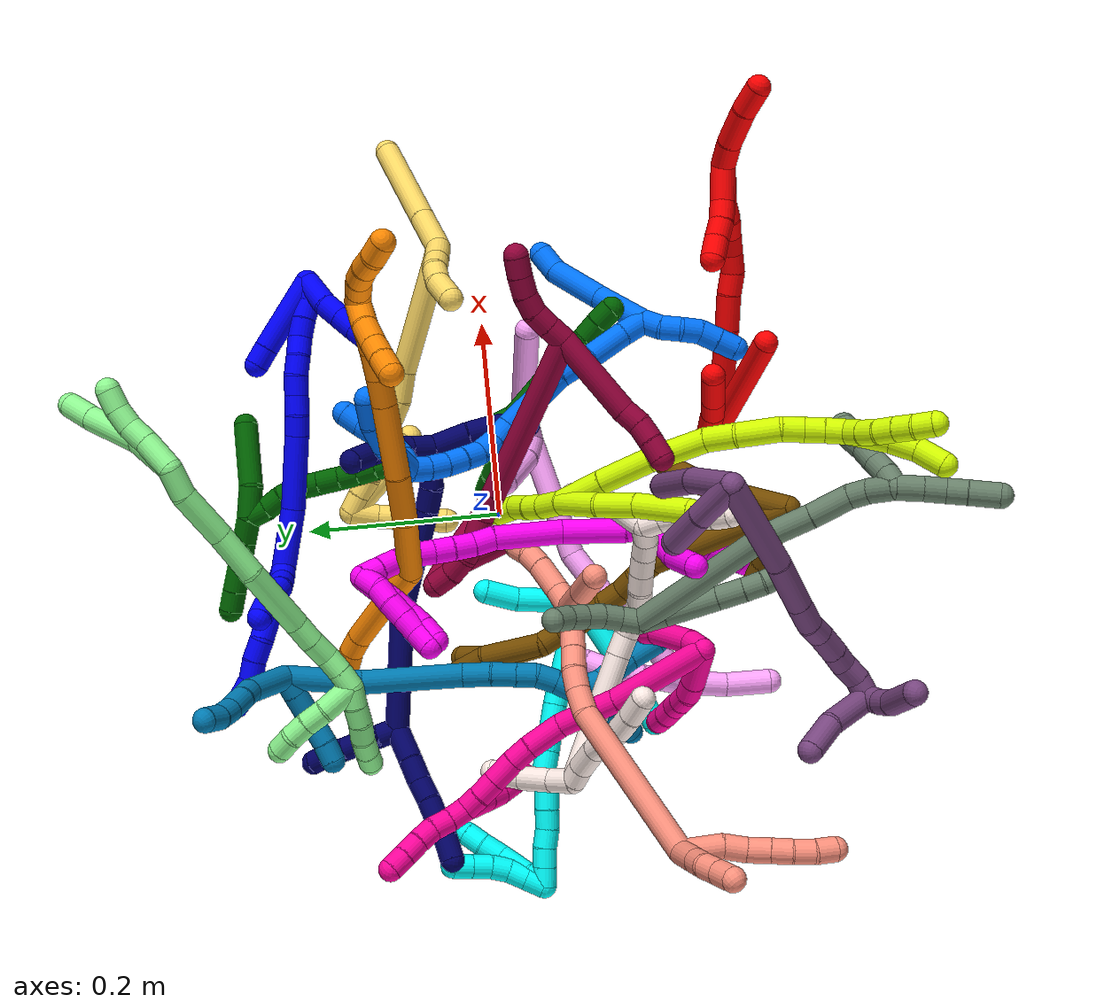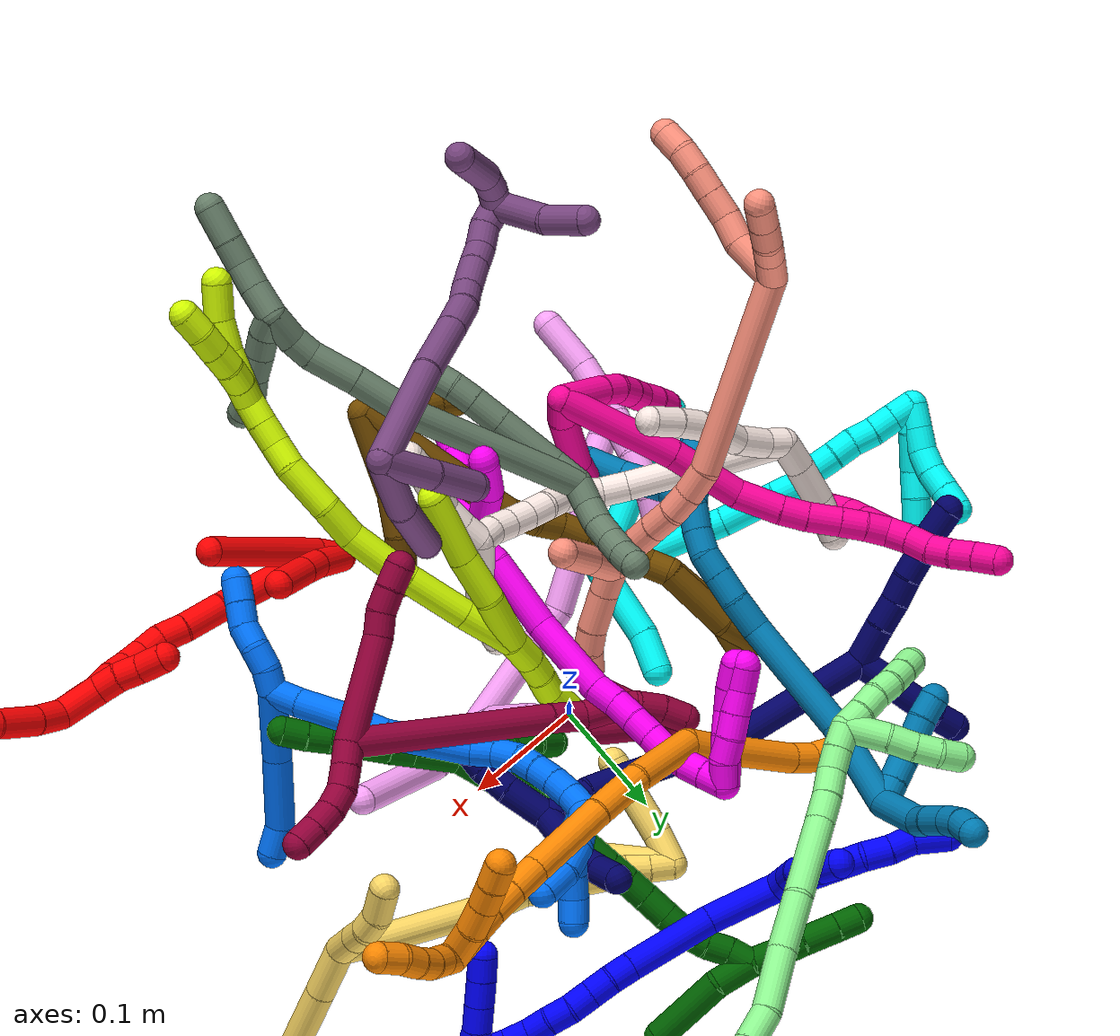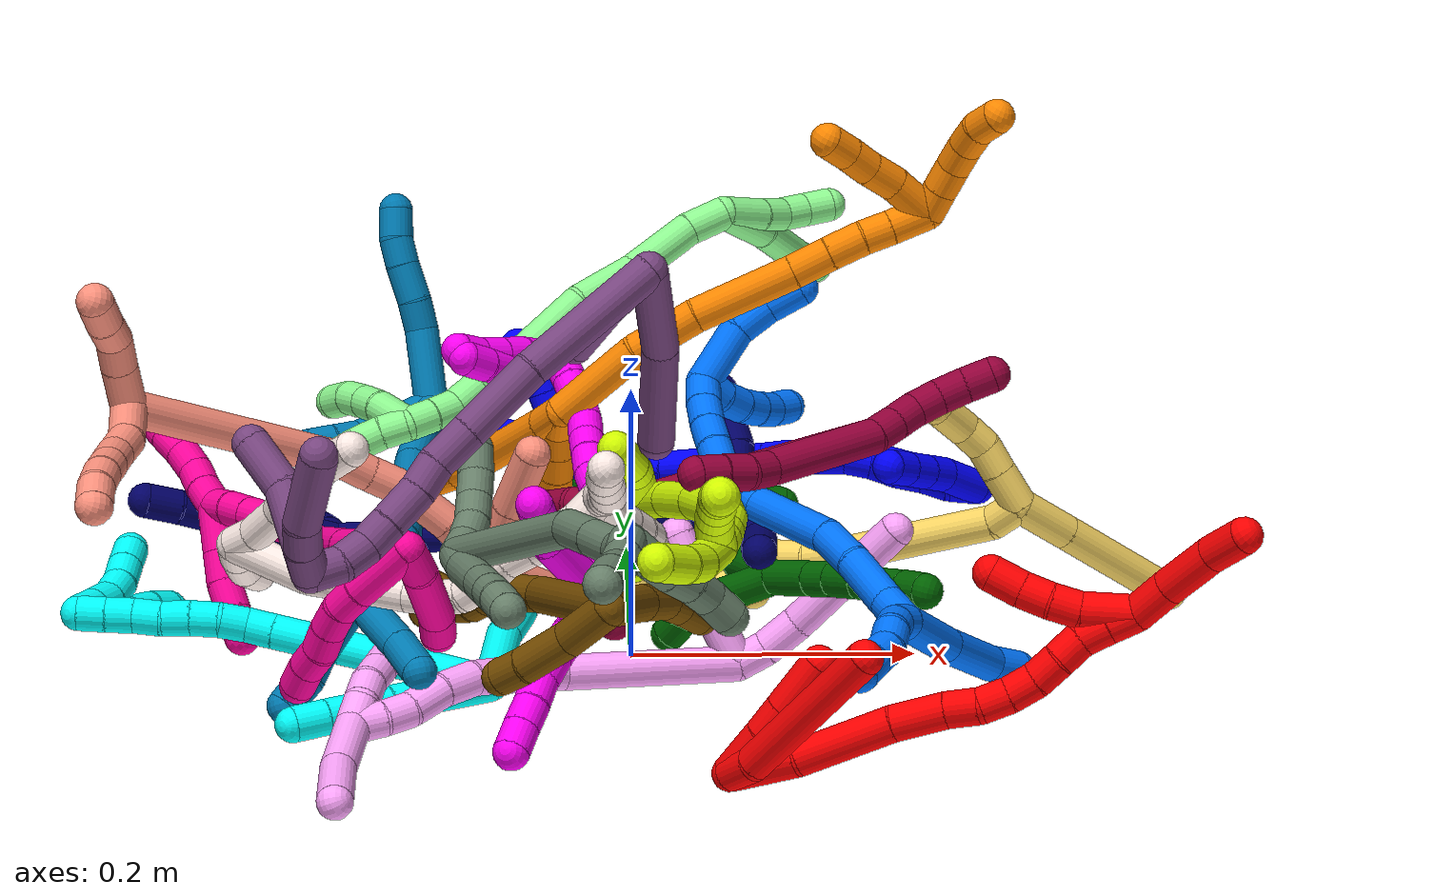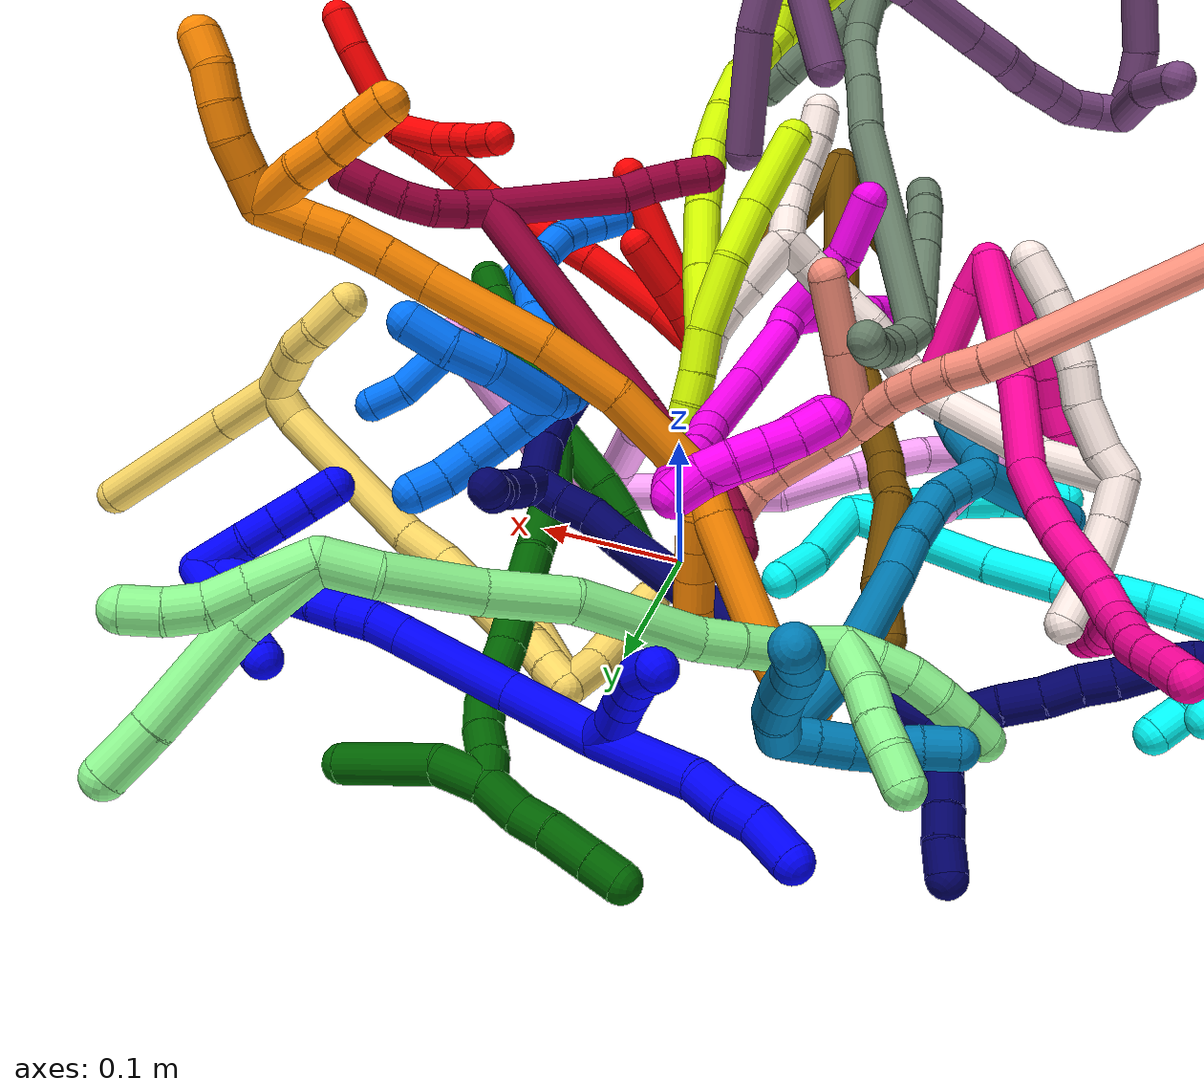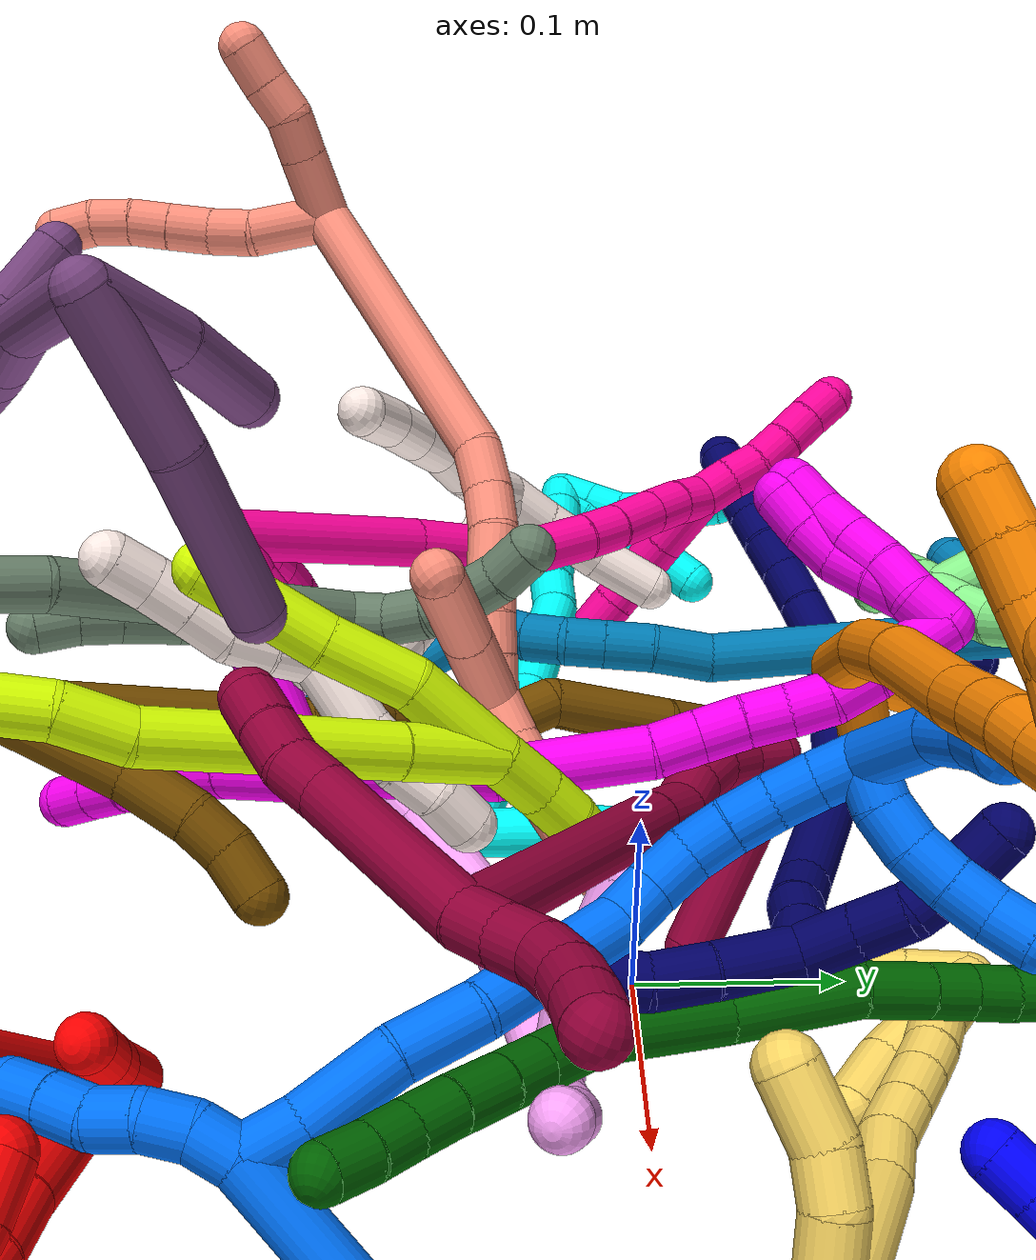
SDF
<sdf version="1.7">
 <world name="default">
  <plugin name="TubeGeneratorPlugin" filename="libtube_generator_plugin.so"/>
  <model name="photoneo_s_sensor">
   <static>1</static>
   <pose>0 0 2 1.57079 1.57079 3.14159</pose>
   <link name="link">
    <inertial><mass>0.1</mass></inertial>
    <sensor name="sensor" type="depth">
     <update_rate>30</update_rate>
     <camera>
      <horizontal_fov>1.22</horizontal_fov>
      <image><width>1920</width><height>1200</height><format>B8G8R8</format></image>
      <clip><near>0.1</near><far>4</far></clip>
      <depth_camera><output>points</output></depth_camera>
     </camera>
     <plugin name="camera_plugin" filename="libgazebo_ros_depth_camera.so">
      <baseline>0.2</baseline>
      <alwaysOn>1</alwaysOn>
      <updateRate>0.0</updateRate>
      <cameraName>camera_ir</cameraName>
      <imageTopicName>/camera/color/image_raw</imageTopicName>
      <cameraInfoTopicName>/camera/color/camera_info</cameraInfoTopicName>
      <depthImageTopicName>/camera/depth/image_raw</depthImageTopicName>
      <depthImageCameraInfoTopicName>/camera/depth/camera_info</depthImageCameraInfoTopicName>
      <pointCloudTopicName>/camera/depth/points</pointCloudTopicName>
      <frameName>fr_optical</frameName>
      <pointCloudCutoff>0.1</pointCloudCutoff>
      <pointCloudCutoffMax>2.0</pointCloudCutoffMax>
      <distortionK1>0</distortionK1>
      <distortionK2>0</distortionK2>
      <distortionK3>0</distortionK3>
      <distortionT1>0</distortionT1>
      <distortionT2>0</distortionT2>
      <CxPrime>0</CxPrime>
      <Cx>0</Cx>
      <Cy>0</Cy>
      <focalLength>0</focalLength>
      <hackBaseline>0</hackBaseline>
     </plugin>
    </sensor>
   </link>
  </model>
  <gravity>0 0 -9.8</gravity>
  <magnetic_field>6e-06 2.3e-05 -4.2e-05</magnetic_field>
  <atmosphere type="adiabatic"/>
  <physics name="default_physics" default="0" type="ode">
   <max_step_size>0.003</max_step_size>
   <real_time_factor>1</real_time_factor>
   <real_time_update_rate>1000</real_time_update_rate>
   <max_contacts>10000</max_contacts>
   <ode>
    <solver>
     <type>quick</type>
     <iters>100</iters>
     <sor>1.3</sor>
     <use_dynamic_moi_rescaling>0</use_dynamic_moi_rescaling>
    </solver>
    <constraints>
     <contact_max_correcting_vel>0</contact_max_correcting_vel>
     <contact_surface_layer>0.001</contact_surface_layer>
     <cfm>0</cfm>
     <erp>0.2</erp>
    </constraints>
   </ode>
  </physics>
  <scene><ambient>0.4 0.4 0.4 1</ambient><background>0.7 0.7 0.7 1</background><shadows>0</shadows></scene>
  <audio><device>default</device></audio>
  <spherical_coordinates>
   <surface_model>EARTH_WGS84</surface_model>
   <latitude_deg>0</latitude_deg>
   <longitude_deg>0</longitude_deg>
   <elevation>0</elevation>
   <heading_deg>0</heading_deg>
  </spherical_coordinates>
  <model name="bin">
   <static>1</static>
   <link name="bottom">
    <collision name="collision-bottom">
     <pose>0 0 -0.01 0 -0 0</pose>
     <geometry><box><size>0.8 0.6 0.02</size></box></geometry>
     <surface>
      <friction><ode><mu>100</mu><mu2>100</mu2></ode></friction>
      <contact><collide_bitmask>65535</collide_bitmask></contact>
     </surface>
    </collision>
   </link>
   <link name="west_wall">
    <collision name="collision-west_wall">
     <pose>-0.41 0 0.1 0 -0 0</pose>
     <geometry><box><size>0.02 0.6 0.2</size></box></geometry>
     <surface>
      <friction><ode><mu>100</mu><mu2>100</mu2></ode></friction>
      <contact><collide_bitmask>65535</collide_bitmask></contact>
     </surface>
    </collision>
   </link>
   <link name="east_wall">
    <collision name="collision-east_wall">
     <pose>0.41 0 0.1 0 -0 0</pose>
     <geometry><box><size>0.02 0.6 0.2</size></box></geometry>
     <surface>
      <friction><ode><mu>100</mu><mu2>100</mu2></ode></friction>
      <contact><collide_bitmask>65535</collide_bitmask></contact>
     </surface>
    </collision>
   </link>
   <link name="south_wall">
    <collision name="collision-south_wall">
     <pose>0 -0.31 0.1 0 -0 0</pose>
     <geometry><box><size>0.8 0.02 0.2</size></box></geometry>
     <surface>
      <friction><ode><mu>100</mu><mu2>100</mu2></ode></friction>
      <contact><collide_bitmask>65535</collide_bitmask></contact>
     </surface>
    </collision>
   </link>
   <link name="north_wall">
    <collision name="collision-north_wall">
     <pose>0 0.31 0.1 0 -0 0</pose>
     <geometry><box><size>0.8 0.02 0.2</size></box></geometry>
     <surface>
      <friction><ode><mu>100</mu><mu2>100</mu2></ode></friction>
      <contact><collide_bitmask>65535</collide_bitmask></contact>
     </surface>
    </collision>
   </link>
  </model>
  <model name="1">
   <static>0</static>
   <link name="1">
    <collision name="collision-cylinder-e_1_2_8">
     <pose>-0.013044 -0.000897 -0.035909 3.11662 -0.348327 -2.99989</pose>
     <geometry><cylinder><radius>0.0125</radius><length>0.07643</length></cylinder></geometry>
     <surface>
      <friction><ode><mu>1.16</mu><mu2>1.16</mu2><slip1>0</slip1><slip2>0</slip2></ode></friction>
      <contact><ode><kp>1e+06</kp><kd>1</kd><max_vel>0</max_vel><min_depth>0.001</min_depth></ode></contact>
     </surface>
    </collision>
    <visual name="visual-cylinder-e_1_2_8">
     <pose>-0.013044 -0.000897 -0.035909 3.11662 -0.348327 -2.99989</pose>
     <geometry><cylinder><radius>0.0125</radius><length>0.07643</length></cylinder></geometry>
     <material><ambient>0 0 1 1</ambient></material>
    </visual>
    <collision name="collision-cylinder-e_2_8_9">
     <pose>-0.027146 -0.004156 -0.082792 2.9296 -0.094001 -0.83249</pose>
     <geometry><cylinder><radius>0.0125</radius><length>0.022553</length></cylinder></geometry>
     <surface>
      <friction><ode><mu>1.16</mu><mu2>1.16</mu2><slip1>0</slip1><slip2>0</slip2></ode></friction>
      <contact><ode><kp>1e+06</kp><kd>1</kd><max_vel>0</max_vel><min_depth>0.001</min_depth></ode></contact>
     </surface>
    </collision>
    <visual name="visual-cylinder-e_2_8_9">
     <pose>-0.027146 -0.004156 -0.082792 2.9296 -0.094001 -0.83249</pose>
     <geometry><cylinder><radius>0.0125</radius><length>0.022553</length></cylinder></geometry>
     <material><ambient>0 0 1 1</ambient></material>
    </visual>
    <collision name="collision-cylinder-e_3_9_10">
     <pose>-0.030311 -0.00986 -0.103347 2.80598 -0.204737 -1.09025</pose>
     <geometry><cylinder><radius>0.0125</radius><length>0.020724</length></cylinder></geometry>
     <surface>
      <friction><ode><mu>1.16</mu><mu2>1.16</mu2><slip1>0</slip1><slip2>0</slip2></ode></friction>
      <contact><ode><kp>1e+06</kp><kd>1</kd><max_vel>0</max_vel><min_depth>0.001</min_depth></ode></contact>
     </surface>
    </collision>
    <visual name="visual-cylinder-e_3_9_10">
     <pose>-0.030311 -0.00986 -0.103347 2.80598 -0.204737 -1.09025</pose>
     <geometry><cylinder><radius>0.0125</radius><length>0.020724</length></cylinder></geometry>
     <material><ambient>0 0 1 1</ambient></material>
    </visual>
    <collision name="collision-cylinder-e_4_10_6">
     <pose>-0.032126 -0.014817 -0.127984 3.03466 0.019283 0.356495</pose>
     <geometry><cylinder><radius>0.0125</radius><length>0.030294</length></cylinder></geometry>
     <surface>
      <friction><ode><mu>1.16</mu><mu2>1.16</mu2><slip1>0</slip1><slip2>0</slip2></ode></friction>
      <contact><ode><kp>1e+06</kp><kd>1</kd><max_vel>0</max_vel><min_depth>0.001</min_depth></ode></contact>
     </surface>
    </collision>
    <visual name="visual-cylinder-e_4_10_6">
     <pose>-0.032126 -0.014817 -0.127984 3.03466 0.019283 0.356495</pose>
     <geometry><cylinder><radius>0.0125</radius><length>0.030294</length></cylinder></geometry>
     <material><ambient>0 0 1 1</ambient></material>
    </visual>
    <collision name="collision-cylinder-e_1_2_11">
     <pose>-0.007724 0.004014 -0.004923 -2.45759 -0.88257 1.84992</pose>
     <geometry><cylinder><radius>0.0125</radius><length>0.02</length></cylinder></geometry>
     <surface>
      <friction><ode><mu>1.16</mu><mu2>1.16</mu2><slip1>0</slip1><slip2>0</slip2></ode></friction>
      <contact><ode><kp>1e+06</kp><kd>1</kd><max_vel>0</max_vel><min_depth>0.001</min_depth></ode></contact>
     </surface>
    </collision>
    <visual name="visual-cylinder-e_1_2_11">
     <pose>-0.007724 0.004014 -0.004923 -2.45759 -0.88257 1.84992</pose>
     <geometry><cylinder><radius>0.0125</radius><length>0.02</length></cylinder></geometry>
     <material><ambient>0 0 1 1</ambient></material>
    </visual>
    <collision name="collision-cylinder-e_2_11_12">
     <pose>-0.022974 0.013891 -0.012841 -2.04311 -0.852025 1.276</pose>
     <geometry><cylinder><radius>0.0125</radius><length>0.02</length></cylinder></geometry>
     <surface>
      <friction><ode><mu>1.16</mu><mu2>1.16</mu2><slip1>0</slip1><slip2>0</slip2></ode></friction>
      <contact><ode><kp>1e+06</kp><kd>1</kd><max_vel>0</max_vel><min_depth>0.001</min_depth></ode></contact>
     </surface>
    </collision>
    <visual name="visual-cylinder-e_2_11_12">
     <pose>-0.022974 0.013891 -0.012841 -2.04311 -0.852025 1.276</pose>
     <geometry><cylinder><radius>0.0125</radius><length>0.02</length></cylinder></geometry>
     <material><ambient>0 0 1 1</ambient></material>
    </visual>
    <collision name="collision-cylinder-e_3_12_13">
     <pose>-0.036296 0.026375 -0.020588 -2.19322 -0.618316 1.11333</pose>
     <geometry><cylinder><radius>0.0125</radius><length>0.02</length></cylinder></geometry>
     <surface>
      <friction><ode><mu>1.16</mu><mu2>1.16</mu2><slip1>0</slip1><slip2>0</slip2></ode></friction>
      <contact><ode><kp>1e+06</kp><kd>1</kd><max_vel>0</max_vel><min_depth>0.001</min_depth></ode></contact>
     </surface>
    </collision>
    <visual name="visual-cylinder-e_3_12_13">
     <pose>-0.036296 0.026375 -0.020588 -2.19322 -0.618316 1.11333</pose>
     <geometry><cylinder><radius>0.0125</radius><length>0.02</length></cylinder></geometry>
     <material><ambient>0 0 1 1</ambient></material>
    </visual>
    <collision name="collision-cylinder-e_4_13_14">
     <pose>-0.04774 0.039649 -0.030222 -2.20403 -0.600019 1.09669</pose>
     <geometry><cylinder><radius>0.0125</radius><length>0.02</length></cylinder></geometry>
     <surface>
      <friction><ode><mu>1.16</mu><mu2>1.16</mu2><slip1>0</slip1><slip2>0</slip2></ode></friction>
      <contact><ode><kp>1e+06</kp><kd>1</kd><max_vel>0</max_vel><min_depth>0.001</min_depth></ode></contact>
     </surface>
    </collision>
    <visual name="visual-cylinder-e_4_13_14">
     <pose>-0.04774 0.039649 -0.030222 -2.20403 -0.600019 1.09669</pose>
     <geometry><cylinder><radius>0.0125</radius><length>0.02</length></cylinder></geometry>
     <material><ambient>0 0 1 1</ambient></material>
    </visual>
    <collision name="collision-cylinder-e_5_14_5">
     <pose>-0.059 0.050694 -0.04212 -2.58212 -0.596068 1.63777</pose>
     <geometry><cylinder><radius>0.0125</radius><length>0.02</length></cylinder></geometry>
     <surface>
      <friction><ode><mu>1.16</mu><mu2>1.16</mu2><slip1>0</slip1><slip2>0</slip2></ode></friction>
      <contact><ode><kp>1e+06</kp><kd>1</kd><max_vel>0</max_vel><min_depth>0.001</min_depth></ode></contact>
     </surface>
    </collision>
    <visual name="visual-cylinder-e_5_14_5">
     <pose>-0.059 0.050694 -0.04212 -2.58212 -0.596068 1.63777</pose>
     <geometry><cylinder><radius>0.0125</radius><length>0.02</length></cylinder></geometry>
     <material><ambient>0 0 1 1</ambient></material>
    </visual>
    <collision name="collision-cylinder-e_1_2_15">
     <pose>0.008266 0.009158 0.029005 -0.305816 0.265364 -0.041131</pose>
     <geometry><cylinder><radius>0.0125</radius><length>0.06304</length></cylinder></geometry>
     <surface>
      <friction><ode><mu>1.16</mu><mu2>1.16</mu2><slip1>0</slip1><slip2>0</slip2></ode></friction>
      <contact><ode><kp>1e+06</kp><kd>1</kd><max_vel>0</max_vel><min_depth>0.001</min_depth></ode></contact>
     </surface>
    </collision>
    <visual name="visual-cylinder-e_1_2_15">
     <pose>0.008266 0.009158 0.029005 -0.305816 0.265364 -0.041131</pose>
     <geometry><cylinder><radius>0.0125</radius><length>0.06304</length></cylinder></geometry>
     <material><ambient>0 0 1 1</ambient></material>
    </visual>
    <collision name="collision-cylinder-e_2_15_16">
     <pose>0.02573 0.035018 0.091028 -0.468325 0.243624 -0.058386</pose>
     <geometry><cylinder><radius>0.0125</radius><length>0.076255</length></cylinder></geometry>
     <surface>
      <friction><ode><mu>1.16</mu><mu2>1.16</mu2><slip1>0</slip1><slip2>0</slip2></ode></friction>
      <contact><ode><kp>1e+06</kp><kd>1</kd><max_vel>0</max_vel><min_depth>0.001</min_depth></ode></contact>
     </surface>
    </collision>
    <visual name="visual-cylinder-e_2_15_16">
     <pose>0.02573 0.035018 0.091028 -0.468325 0.243624 -0.058386</pose>
     <geometry><cylinder><radius>0.0125</radius><length>0.076255</length></cylinder></geometry>
     <material><ambient>0 0 1 1</ambient></material>
    </visual>
    <collision name="collision-cylinder-e_3_16_17">
     <pose>0.037511 0.056504 0.132585 -0.510736 0.258133 -0.067741</pose>
     <geometry><cylinder><radius>0.0125</radius><length>0.020246</length></cylinder></geometry>
     <surface>
      <friction><ode><mu>1.16</mu><mu2>1.16</mu2><slip1>0</slip1><slip2>0</slip2></ode></friction>
      <contact><ode><kp>1e+06</kp><kd>1</kd><max_vel>0</max_vel><min_depth>0.001</min_depth></ode></contact>
     </surface>
    </collision>
    <visual name="visual-cylinder-e_3_16_17">
     <pose>0.037511 0.056504 0.132585 -0.510736 0.258133 -0.067741</pose>
     <geometry><cylinder><radius>0.0125</radius><length>0.020246</length></cylinder></geometry>
     <material><ambient>0 0 1 1</ambient></material>
    </visual>
    <collision name="collision-cylinder-e_4_17_18">
     <pose>0.044221 0.065037 0.149539 -0.419008 0.420969 -0.090791</pose>
     <geometry><cylinder><radius>0.0125</radius><length>0.020189</length></cylinder></geometry>
     <surface>
      <friction><ode><mu>1.16</mu><mu2>1.16</mu2><slip1>0</slip1><slip2>0</slip2></ode></friction>
      <contact><ode><kp>1e+06</kp><kd>1</kd><max_vel>0</max_vel><min_depth>0.001</min_depth></ode></contact>
     </surface>
    </collision>
    <visual name="visual-cylinder-e_4_17_18">
     <pose>0.044221 0.065037 0.149539 -0.419008 0.420969 -0.090791</pose>
     <geometry><cylinder><radius>0.0125</radius><length>0.020189</length></cylinder></geometry>
     <material><ambient>0 0 1 1</ambient></material>
    </visual>
    <collision name="collision-cylinder-e_5_18_19">
     <pose>0.052154 0.072952 0.166313 -0.462494 0.387184 -0.092257</pose>
     <geometry><cylinder><radius>0.0125</radius><length>0.020171</length></cylinder></geometry>
     <surface>
      <friction><ode><mu>1.16</mu><mu2>1.16</mu2><slip1>0</slip1><slip2>0</slip2></ode></friction>
      <contact><ode><kp>1e+06</kp><kd>1</kd><max_vel>0</max_vel><min_depth>0.001</min_depth></ode></contact>
     </surface>
    </collision>
    <visual name="visual-cylinder-e_5_18_19">
     <pose>0.052154 0.072952 0.166313 -0.462494 0.387184 -0.092257</pose>
     <geometry><cylinder><radius>0.0125</radius><length>0.020171</length></cylinder></geometry>
     <material><ambient>0 0 1 1</ambient></material>
    </visual>
    <collision name="collision-cylinder-e_6_19_20">
     <pose>0.059974 0.079206 0.183643 -0.22858 0.410785 -0.047819</pose>
     <geometry><cylinder><radius>0.0125</radius><length>0.020094</length></cylinder></geometry>
     <surface>
      <friction><ode><mu>1.16</mu><mu2>1.16</mu2><slip1>0</slip1><slip2>0</slip2></ode></friction>
      <contact><ode><kp>1e+06</kp><kd>1</kd><max_vel>0</max_vel><min_depth>0.001</min_depth></ode></contact>
     </surface>
    </collision>
    <visual name="visual-cylinder-e_6_19_20">
     <pose>0.059974 0.079206 0.183643 -0.22858 0.410785 -0.047819</pose>
     <geometry><cylinder><radius>0.0125</radius><length>0.020094</length></cylinder></geometry>
     <material><ambient>0 0 1 1</ambient></material>
    </visual>
    <collision name="collision-cylinder-e_7_20_21">
     <pose>0.06924 0.082246 0.201071 -0.112113 0.55307 -0.031849</pose>
     <geometry><cylinder><radius>0.0125</radius><length>0.020003</length></cylinder></geometry>
     <surface>
      <friction><ode><mu>1.16</mu><mu2>1.16</mu2><slip1>0</slip1><slip2>0</slip2></ode></friction>
      <contact><ode><kp>1e+06</kp><kd>1</kd><max_vel>0</max_vel><min_depth>0.001</min_depth></ode></contact>
     </surface>
    </collision>
    <visual name="visual-cylinder-e_7_20_21">
     <pose>0.06924 0.082246 0.201071 -0.112113 0.55307 -0.031849</pose>
     <geometry><cylinder><radius>0.0125</radius><length>0.020003</length></cylinder></geometry>
     <material><ambient>0 0 1 1</ambient></material>
    </visual>
    <collision name="collision-cylinder-e_8_21_22">
     <pose>0.077863 0.085027 0.218765 -0.19548 0.34364 -0.034027</pose>
     <geometry><cylinder><radius>0.0125</radius><length>0.020001</length></cylinder></geometry>
     <surface>
      <friction><ode><mu>1.16</mu><mu2>1.16</mu2><slip1>0</slip1><slip2>0</slip2></ode></friction>
      <contact><ode><kp>1e+06</kp><kd>1</kd><max_vel>0</max_vel><min_depth>0.001</min_depth></ode></contact>
     </surface>
    </collision>
    <visual name="visual-cylinder-e_8_21_22">
     <pose>0.077863 0.085027 0.218765 -0.19548 0.34364 -0.034027</pose>
     <geometry><cylinder><radius>0.0125</radius><length>0.020001</length></cylinder></geometry>
     <material><ambient>0 0 1 1</ambient></material>
    </visual>
    <collision name="collision-cylinder-e_9_22_23">
     <pose>0.084698 0.087588 0.237353 -0.078122 0.353946 -0.013979</pose>
     <geometry><cylinder><radius>0.0125</radius><length>0.02</length></cylinder></geometry>
     <surface>
      <friction><ode><mu>1.16</mu><mu2>1.16</mu2><slip1>0</slip1><slip2>0</slip2></ode></friction>
      <contact><ode><kp>1e+06</kp><kd>1</kd><max_vel>0</max_vel><min_depth>0.001</min_depth></ode></contact>
     </surface>
    </collision>
    <visual name="visual-cylinder-e_9_22_23">
     <pose>0.084698 0.087588 0.237353 -0.078122 0.353946 -0.013979</pose>
     <geometry><cylinder><radius>0.0125</radius><length>0.02</length></cylinder></geometry>
     <material><ambient>0 0 1 1</ambient></material>
    </visual>
    <collision name="collision-cylinder-e_10_23_1">
     <pose>0.092952 0.091698 0.254808 -0.395009 0.499268 -0.10195</pose>
     <geometry><cylinder><radius>0.0125</radius><length>0.02</length></cylinder></geometry>
     <surface>
      <friction><ode><mu>1.16</mu><mu2>1.16</mu2><slip1>0</slip1><slip2>0</slip2></ode></friction>
      <contact><ode><kp>1e+06</kp><kd>1</kd><max_vel>0</max_vel><min_depth>0.001</min_depth></ode></contact>
     </surface>
    </collision>
    <visual name="visual-cylinder-e_10_23_1">
     <pose>0.092952 0.091698 0.254808 -0.395009 0.499268 -0.10195</pose>
     <geometry><cylinder><radius>0.0125</radius><length>0.02</length></cylinder></geometry>
     <material><ambient>0 0 1 1</ambient></material>
    </visual>
    <collision name="collision-cylinder-e_1_1_24">
     <pose>0.09781 0.094516 0.223008 3.12755 0.001751 0.248062</pose>
     <geometry><cylinder><radius>0.0125</radius><length>0.079815</length></cylinder></geometry>
     <surface>
      <friction><ode><mu>1.16</mu><mu2>1.16</mu2><slip1>0</slip1><slip2>0</slip2></ode></friction>
      <contact><ode><kp>1e+06</kp><kd>1</kd><max_vel>0</max_vel><min_depth>0.001</min_depth></ode></contact>
     </surface>
    </collision>
    <visual name="visual-cylinder-e_1_1_24">
     <pose>0.09781 0.094516 0.223008 3.12755 0.001751 0.248062</pose>
     <geometry><cylinder><radius>0.0125</radius><length>0.079815</length></cylinder></geometry>
     <material><ambient>0 0 1 1</ambient></material>
    </visual>
    <collision name="collision-cylinder-e_2_24_4">
     <pose>0.097816 0.093521 0.173021 3.09854 -0.006358 -0.2932</pose>
     <geometry><cylinder><radius>0.0125</radius><length>0.020185</length></cylinder></geometry>
     <surface>
      <friction><ode><mu>1.16</mu><mu2>1.16</mu2><slip1>0</slip1><slip2>0</slip2></ode></friction>
      <contact><ode><kp>1e+06</kp><kd>1</kd><max_vel>0</max_vel><min_depth>0.001</min_depth></ode></contact>
     </surface>
    </collision>
    <visual name="visual-cylinder-e_2_24_4">
     <pose>0.097816 0.093521 0.173021 3.09854 -0.006358 -0.2932</pose>
     <geometry><cylinder><radius>0.0125</radius><length>0.020185</length></cylinder></geometry>
     <material><ambient>0 0 1 1</ambient></material>
    </visual>
    <collision name="collision-cylinder-e_1_1_25">
     <pose>0.081125 0.091447 0.257624 2.54002 -1.20245 -2.29219</pose>
     <geometry><cylinder><radius>0.0125</radius><length>0.035619</length></cylinder></geometry>
     <surface>
      <friction><ode><mu>1.16</mu><mu2>1.16</mu2><slip1>0</slip1><slip2>0</slip2></ode></friction>
      <contact><ode><kp>1e+06</kp><kd>1</kd><max_vel>0</max_vel><min_depth>0.001</min_depth></ode></contact>
     </surface>
    </collision>
    <visual name="visual-cylinder-e_1_1_25">
     <pose>0.081125 0.091447 0.257624 2.54002 -1.20245 -2.29219</pose>
     <geometry><cylinder><radius>0.0125</radius><length>0.035619</length></cylinder></geometry>
     <material><ambient>0 0 1 1</ambient></material>
    </visual>
    <collision name="collision-cylinder-e_2_25_26">
     <pose>0.054357 0.083945 0.250822 1.94379 -1.18201 -1.55379</pose>
     <geometry><cylinder><radius>0.0125</radius><length>0.021944</length></cylinder></geometry>
     <surface>
      <friction><ode><mu>1.16</mu><mu2>1.16</mu2><slip1>0</slip1><slip2>0</slip2></ode></friction>
      <contact><ode><kp>1e+06</kp><kd>1</kd><max_vel>0</max_vel><min_depth>0.001</min_depth></ode></contact>
     </surface>
    </collision>
    <visual name="visual-cylinder-e_2_25_26">
     <pose>0.054357 0.083945 0.250822 1.94379 -1.18201 -1.55379</pose>
     <geometry><cylinder><radius>0.0125</radius><length>0.021944</length></cylinder></geometry>
     <material><ambient>0 0 1 1</ambient></material>
    </visual>
    <collision name="collision-cylinder-e_3_26_27">
     <pose>0.033958 0.076205 0.247772 1.94844 -1.18513 -1.56216</pose>
     <geometry><cylinder><radius>0.0125</radius><length>0.022117</length></cylinder></geometry>
     <surface>
      <friction><ode><mu>1.16</mu><mu2>1.16</mu2><slip1>0</slip1><slip2>0</slip2></ode></friction>
      <contact><ode><kp>1e+06</kp><kd>1</kd><max_vel>0</max_vel><min_depth>0.001</min_depth></ode></contact>
     </surface>
    </collision>
    <visual name="visual-cylinder-e_3_26_27">
     <pose>0.033958 0.076205 0.247772 1.94844 -1.18513 -1.56216</pose>
     <geometry><cylinder><radius>0.0125</radius><length>0.022117</length></cylinder></geometry>
     <material><ambient>0 0 1 1</ambient></material>
    </visual>
    <collision name="collision-cylinder-e_4_27_3">
     <pose>0.014305 0.068658 0.245142 1.86036 -1.18317 -1.46697</pose>
     <geometry><cylinder><radius>0.0125</radius><length>0.02032</length></cylinder></geometry>
     <surface>
      <friction><ode><mu>1.16</mu><mu2>1.16</mu2><slip1>0</slip1><slip2>0</slip2></ode></friction>
      <contact><ode><kp>1e+06</kp><kd>1</kd><max_vel>0</max_vel><min_depth>0.001</min_depth></ode></contact>
     </surface>
    </collision>
    <visual name="visual-cylinder-e_4_27_3">
     <pose>0.014305 0.068658 0.245142 1.86036 -1.18317 -1.46697</pose>
     <geometry><cylinder><radius>0.0125</radius><length>0.02032</length></cylinder></geometry>
     <material><ambient>0 0 1 1</ambient></material>
    </visual>
    <collision name="collision-sphere-3">
     <pose>0.004899 0.064978 0.244045 0 -0 0</pose>
     <geometry><sphere><radius>0.0125</radius></sphere></geometry>
     <surface>
      <friction><ode><mu>1.16</mu><mu2>1.16</mu2><slip1>0</slip1><slip2>0</slip2></ode></friction>
      <contact><ode><kp>1e+06</kp><kd>1</kd><max_vel>0</max_vel><min_depth>0.001</min_depth></ode></contact>
     </surface>
    </collision>
    <visual name="visual-sphere-3">
     <pose>0.004899 0.064978 0.244045 0 -0 0</pose>
     <geometry><sphere><radius>0.0125</radius></sphere></geometry>
     <material><ambient>0 0 1 1</ambient></material>
    </visual>
    <collision name="collision-sphere-27">
     <pose>0.023712 0.072339 0.246238 0 -0 0</pose>
     <geometry><sphere><radius>0.0125</radius></sphere></geometry>
     <surface>
      <friction><ode><mu>1.16</mu><mu2>1.16</mu2><slip1>0</slip1><slip2>0</slip2></ode></friction>
      <contact><ode><kp>1e+06</kp><kd>1</kd><max_vel>0</max_vel><min_depth>0.001</min_depth></ode></contact>
     </surface>
    </collision>
    <visual name="visual-sphere-27">
     <pose>0.023712 0.072339 0.246238 0 -0 0</pose>
     <geometry><sphere><radius>0.0125</radius></sphere></geometry>
     <material><ambient>0 0 1 1</ambient></material>
    </visual>
    <collision name="collision-sphere-26">
     <pose>0.044204 0.080072 0.249306 0 -0 0</pose>
     <geometry><sphere><radius>0.0125</radius></sphere></geometry>
     <surface>
      <friction><ode><mu>1.16</mu><mu2>1.16</mu2><slip1>0</slip1><slip2>0</slip2></ode></friction>
      <contact><ode><kp>1e+06</kp><kd>1</kd><max_vel>0</max_vel><min_depth>0.001</min_depth></ode></contact>
     </surface>
    </collision>
    <visual name="visual-sphere-26">
     <pose>0.044204 0.080072 0.249306 0 -0 0</pose>
     <geometry><sphere><radius>0.0125</radius></sphere></geometry>
     <material><ambient>0 0 1 1</ambient></material>
    </visual>
    <collision name="collision-sphere-25">
     <pose>0.06451 0.087818 0.252337 0 -0 0</pose>
     <geometry><sphere><radius>0.0125</radius></sphere></geometry>
     <surface>
      <friction><ode><mu>1.16</mu><mu2>1.16</mu2><slip1>0</slip1><slip2>0</slip2></ode></friction>
      <contact><ode><kp>1e+06</kp><kd>1</kd><max_vel>0</max_vel><min_depth>0.001</min_depth></ode></contact>
     </surface>
    </collision>
    <visual name="visual-sphere-25">
     <pose>0.06451 0.087818 0.252337 0 -0 0</pose>
     <geometry><sphere><radius>0.0125</radius></sphere></geometry>
     <material><ambient>0 0 1 1</ambient></material>
    </visual>
    <collision name="collision-sphere-4">
     <pose>0.097752 0.093087 0.162939 0 -0 0</pose>
     <geometry><sphere><radius>0.0125</radius></sphere></geometry>
     <surface>
      <friction><ode><mu>1.16</mu><mu2>1.16</mu2><slip1>0</slip1><slip2>0</slip2></ode></friction>
      <contact><ode><kp>1e+06</kp><kd>1</kd><max_vel>0</max_vel><min_depth>0.001</min_depth></ode></contact>
     </surface>
    </collision>
    <visual name="visual-sphere-4">
     <pose>0.097752 0.093087 0.162939 0 -0 0</pose>
     <geometry><sphere><radius>0.0125</radius></sphere></geometry>
     <material><ambient>0 0 1 1</ambient></material>
    </visual>
    <collision name="collision-sphere-24">
     <pose>0.09788 0.093956 0.183104 0 -0 0</pose>
     <geometry><sphere><radius>0.0125</radius></sphere></geometry>
     <surface>
      <friction><ode><mu>1.16</mu><mu2>1.16</mu2><slip1>0</slip1><slip2>0</slip2></ode></friction>
      <contact><ode><kp>1e+06</kp><kd>1</kd><max_vel>0</max_vel><min_depth>0.001</min_depth></ode></contact>
     </surface>
    </collision>
    <visual name="visual-sphere-24">
     <pose>0.09788 0.093956 0.183104 0 -0 0</pose>
     <geometry><sphere><radius>0.0125</radius></sphere></geometry>
     <material><ambient>0 0 1 1</ambient></material>
    </visual>
    <collision name="collision-sphere-1">
     <pose>0.09774 0.095077 0.262911 0 -0 0</pose>
     <geometry><sphere><radius>0.0125</radius></sphere></geometry>
     <surface>
      <friction><ode><mu>1.16</mu><mu2>1.16</mu2><slip1>0</slip1><slip2>0</slip2></ode></friction>
      <contact><ode><kp>1e+06</kp><kd>1</kd><max_vel>0</max_vel><min_depth>0.001</min_depth></ode></contact>
     </surface>
    </collision>
    <visual name="visual-sphere-1">
     <pose>0.09774 0.095077 0.262911 0 -0 0</pose>
     <geometry><sphere><radius>0.0125</radius></sphere></geometry>
     <material><ambient>0 0 1 1</ambient></material>
    </visual>
    <collision name="collision-sphere-23">
     <pose>0.088165 0.08832 0.246705 0 -0 0</pose>
     <geometry><sphere><radius>0.0125</radius></sphere></geometry>
     <surface>
      <friction><ode><mu>1.16</mu><mu2>1.16</mu2><slip1>0</slip1><slip2>0</slip2></ode></friction>
      <contact><ode><kp>1e+06</kp><kd>1</kd><max_vel>0</max_vel><min_depth>0.001</min_depth></ode></contact>
     </surface>
    </collision>
    <visual name="visual-sphere-23">
     <pose>0.088165 0.08832 0.246705 0 -0 0</pose>
     <geometry><sphere><radius>0.0125</radius></sphere></geometry>
     <material><ambient>0 0 1 1</ambient></material>
    </visual>
    <collision name="collision-sphere-22">
     <pose>0.081232 0.086856 0.228001 0 -0 0</pose>
     <geometry><sphere><radius>0.0125</radius></sphere></geometry>
     <surface>
      <friction><ode><mu>1.16</mu><mu2>1.16</mu2><slip1>0</slip1><slip2>0</slip2></ode></friction>
      <contact><ode><kp>1e+06</kp><kd>1</kd><max_vel>0</max_vel><min_depth>0.001</min_depth></ode></contact>
     </surface>
    </collision>
    <visual name="visual-sphere-22">
     <pose>0.081232 0.086856 0.228001 0 -0 0</pose>
     <geometry><sphere><radius>0.0125</radius></sphere></geometry>
     <material><ambient>0 0 1 1</ambient></material>
    </visual>
    <collision name="collision-sphere-21">
     <pose>0.074494 0.083198 0.209528 0 -0 0</pose>
     <geometry><sphere><radius>0.0125</radius></sphere></geometry>
     <surface>
      <friction><ode><mu>1.16</mu><mu2>1.16</mu2><slip1>0</slip1><slip2>0</slip2></ode></friction>
      <contact><ode><kp>1e+06</kp><kd>1</kd><max_vel>0</max_vel><min_depth>0.001</min_depth></ode></contact>
     </surface>
    </collision>
    <visual name="visual-sphere-21">
     <pose>0.074494 0.083198 0.209528 0 -0 0</pose>
     <geometry><sphere><radius>0.0125</radius></sphere></geometry>
     <material><ambient>0 0 1 1</ambient></material>
    </visual>
    <collision name="collision-sphere-11">
     <pose>-0.015447 0.008027 -0.009846 0 -0 0</pose>
     <geometry><sphere><radius>0.0125</radius></sphere></geometry>
     <surface>
      <friction><ode><mu>1.16</mu><mu2>1.16</mu2><slip1>0</slip1><slip2>0</slip2></ode></friction>
      <contact><ode><kp>1e+06</kp><kd>1</kd><max_vel>0</max_vel><min_depth>0.001</min_depth></ode></contact>
     </surface>
    </collision>
    <visual name="visual-sphere-11">
     <pose>-0.015447 0.008027 -0.009846 0 -0 0</pose>
     <geometry><sphere><radius>0.0125</radius></sphere></geometry>
     <material><ambient>0 0 1 1</ambient></material>
    </visual>
    <collision name="collision-sphere-6">
     <pose>-0.031833 -0.016434 -0.143042 0 -0 0</pose>
     <geometry><sphere><radius>0.0125</radius></sphere></geometry>
     <surface>
      <friction><ode><mu>1.16</mu><mu2>1.16</mu2><slip1>0</slip1><slip2>0</slip2></ode></friction>
      <contact><ode><kp>1e+06</kp><kd>1</kd><max_vel>0</max_vel><min_depth>0.001</min_depth></ode></contact>
     </surface>
    </collision>
    <visual name="visual-sphere-6">
     <pose>-0.031833 -0.016434 -0.143042 0 -0 0</pose>
     <geometry><sphere><radius>0.0125</radius></sphere></geometry>
     <material><ambient>0 0 1 1</ambient></material>
    </visual>
    <collision name="collision-sphere-10">
     <pose>-0.032418 -0.013201 -0.112927 0 -0 0</pose>
     <geometry><sphere><radius>0.0125</radius></sphere></geometry>
     <surface>
      <friction><ode><mu>1.16</mu><mu2>1.16</mu2><slip1>0</slip1><slip2>0</slip2></ode></friction>
      <contact><ode><kp>1e+06</kp><kd>1</kd><max_vel>0</max_vel><min_depth>0.001</min_depth></ode></contact>
     </surface>
    </collision>
    <visual name="visual-sphere-10">
     <pose>-0.032418 -0.013201 -0.112927 0 -0 0</pose>
     <geometry><sphere><radius>0.0125</radius></sphere></geometry>
     <material><ambient>0 0 1 1</ambient></material>
    </visual>
    <collision name="collision-sphere-9">
     <pose>-0.028204 -0.006518 -0.093768 0 -0 0</pose>
     <geometry><sphere><radius>0.0125</radius></sphere></geometry>
     <surface>
      <friction><ode><mu>1.16</mu><mu2>1.16</mu2><slip1>0</slip1><slip2>0</slip2></ode></friction>
      <contact><ode><kp>1e+06</kp><kd>1</kd><max_vel>0</max_vel><min_depth>0.001</min_depth></ode></contact>
     </surface>
    </collision>
    <visual name="visual-sphere-9">
     <pose>-0.028204 -0.006518 -0.093768 0 -0 0</pose>
     <geometry><sphere><radius>0.0125</radius></sphere></geometry>
     <material><ambient>0 0 1 1</ambient></material>
    </visual>
    <collision name="collision-sphere-2">
     <geometry><sphere><radius>0.0125</radius></sphere></geometry>
     <surface>
      <friction><ode><mu>1.16</mu><mu2>1.16</mu2><slip1>0</slip1><slip2>0</slip2></ode></friction>
      <contact><ode><kp>1e+06</kp><kd>1</kd><max_vel>0</max_vel><min_depth>0.001</min_depth></ode></contact>
     </surface>
    </collision>
    <visual name="visual-sphere-2">
     <geometry><sphere><radius>0.0125</radius></sphere></geometry>
     <material><ambient>0 0 1 1</ambient></material>
    </visual>
    <collision name="collision-sphere-19">
     <pose>0.055962 0.077119 0.174671 0 -0 0</pose>
     <geometry><sphere><radius>0.0125</radius></sphere></geometry>
     <surface>
      <friction><ode><mu>1.16</mu><mu2>1.16</mu2><slip1>0</slip1><slip2>0</slip2></ode></friction>
      <contact><ode><kp>1e+06</kp><kd>1</kd><max_vel>0</max_vel><min_depth>0.001</min_depth></ode></contact>
     </surface>
    </collision>
    <visual name="visual-sphere-19">
     <pose>0.055962 0.077119 0.174671 0 -0 0</pose>
     <geometry><sphere><radius>0.0125</radius></sphere></geometry>
     <material><ambient>0 0 1 1</ambient></material>
    </visual>
    <collision name="collision-sphere-8">
     <pose>-0.026087 -0.001794 -0.071817 0 -0 0</pose>
     <geometry><sphere><radius>0.0125</radius></sphere></geometry>
     <surface>
      <friction><ode><mu>1.16</mu><mu2>1.16</mu2><slip1>0</slip1><slip2>0</slip2></ode></friction>
      <contact><ode><kp>1e+06</kp><kd>1</kd><max_vel>0</max_vel><min_depth>0.001</min_depth></ode></contact>
     </surface>
    </collision>
    <visual name="visual-sphere-8">
     <pose>-0.026087 -0.001794 -0.071817 0 -0 0</pose>
     <geometry><sphere><radius>0.0125</radius></sphere></geometry>
     <material><ambient>0 0 1 1</ambient></material>
    </visual>
    <collision name="collision-sphere-12">
     <pose>-0.0305 0.019755 -0.015837 0 -0 0</pose>
     <geometry><sphere><radius>0.0125</radius></sphere></geometry>
     <surface>
      <friction><ode><mu>1.16</mu><mu2>1.16</mu2><slip1>0</slip1><slip2>0</slip2></ode></friction>
      <contact><ode><kp>1e+06</kp><kd>1</kd><max_vel>0</max_vel><min_depth>0.001</min_depth></ode></contact>
     </surface>
    </collision>
    <visual name="visual-sphere-12">
     <pose>-0.0305 0.019755 -0.015837 0 -0 0</pose>
     <geometry><sphere><radius>0.0125</radius></sphere></geometry>
     <material><ambient>0 0 1 1</ambient></material>
    </visual>
    <collision name="collision-sphere-13">
     <pose>-0.042093 0.032996 -0.025338 0 -0 0</pose>
     <geometry><sphere><radius>0.0125</radius></sphere></geometry>
     <surface>
      <friction><ode><mu>1.16</mu><mu2>1.16</mu2><slip1>0</slip1><slip2>0</slip2></ode></friction>
      <contact><ode><kp>1e+06</kp><kd>1</kd><max_vel>0</max_vel><min_depth>0.001</min_depth></ode></contact>
     </surface>
    </collision>
    <visual name="visual-sphere-13">
     <pose>-0.042093 0.032996 -0.025338 0 -0 0</pose>
     <geometry><sphere><radius>0.0125</radius></sphere></geometry>
     <material><ambient>0 0 1 1</ambient></material>
    </visual>
    <collision name="collision-sphere-14">
     <pose>-0.053386 0.046302 -0.035106 0 -0 0</pose>
     <geometry><sphere><radius>0.0125</radius></sphere></geometry>
     <surface>
      <friction><ode><mu>1.16</mu><mu2>1.16</mu2><slip1>0</slip1><slip2>0</slip2></ode></friction>
      <contact><ode><kp>1e+06</kp><kd>1</kd><max_vel>0</max_vel><min_depth>0.001</min_depth></ode></contact>
     </surface>
    </collision>
    <visual name="visual-sphere-14">
     <pose>-0.053386 0.046302 -0.035106 0 -0 0</pose>
     <geometry><sphere><radius>0.0125</radius></sphere></geometry>
     <material><ambient>0 0 1 1</ambient></material>
    </visual>
    <collision name="collision-sphere-5">
     <pose>-0.064614 0.055086 -0.049134 0 -0 0</pose>
     <geometry><sphere><radius>0.0125</radius></sphere></geometry>
     <surface>
      <friction><ode><mu>1.16</mu><mu2>1.16</mu2><slip1>0</slip1><slip2>0</slip2></ode></friction>
      <contact><ode><kp>1e+06</kp><kd>1</kd><max_vel>0</max_vel><min_depth>0.001</min_depth></ode></contact>
     </surface>
    </collision>
    <visual name="visual-sphere-5">
     <pose>-0.064614 0.055086 -0.049134 0 -0 0</pose>
     <geometry><sphere><radius>0.0125</radius></sphere></geometry>
     <material><ambient>0 0 1 1</ambient></material>
    </visual>
    <collision name="collision-sphere-15">
     <pose>0.016533 0.018315 0.058011 0 -0 0</pose>
     <geometry><sphere><radius>0.0125</radius></sphere></geometry>
     <surface>
      <friction><ode><mu>1.16</mu><mu2>1.16</mu2><slip1>0</slip1><slip2>0</slip2></ode></friction>
      <contact><ode><kp>1e+06</kp><kd>1</kd><max_vel>0</max_vel><min_depth>0.001</min_depth></ode></contact>
     </surface>
    </collision>
    <visual name="visual-sphere-15">
     <pose>0.016533 0.018315 0.058011 0 -0 0</pose>
     <geometry><sphere><radius>0.0125</radius></sphere></geometry>
     <material><ambient>0 0 1 1</ambient></material>
    </visual>
    <collision name="collision-sphere-16">
     <pose>0.034927 0.05172 0.124046 0 -0 0</pose>
     <geometry><sphere><radius>0.0125</radius></sphere></geometry>
     <surface>
      <friction><ode><mu>1.16</mu><mu2>1.16</mu2><slip1>0</slip1><slip2>0</slip2></ode></friction>
      <contact><ode><kp>1e+06</kp><kd>1</kd><max_vel>0</max_vel><min_depth>0.001</min_depth></ode></contact>
     </surface>
    </collision>
    <visual name="visual-sphere-16">
     <pose>0.034927 0.05172 0.124046 0 -0 0</pose>
     <geometry><sphere><radius>0.0125</radius></sphere></geometry>
     <material><ambient>0 0 1 1</ambient></material>
    </visual>
    <collision name="collision-sphere-17">
     <pose>0.040096 0.061289 0.141123 0 -0 0</pose>
     <geometry><sphere><radius>0.0125</radius></sphere></geometry>
     <surface>
      <friction><ode><mu>1.16</mu><mu2>1.16</mu2><slip1>0</slip1><slip2>0</slip2></ode></friction>
      <contact><ode><kp>1e+06</kp><kd>1</kd><max_vel>0</max_vel><min_depth>0.001</min_depth></ode></contact>
     </surface>
    </collision>
    <visual name="visual-sphere-17">
     <pose>0.040096 0.061289 0.141123 0 -0 0</pose>
     <geometry><sphere><radius>0.0125</radius></sphere></geometry>
     <material><ambient>0 0 1 1</ambient></material>
    </visual>
    <collision name="collision-sphere-18">
     <pose>0.048346 0.068785 0.157956 0 -0 0</pose>
     <geometry><sphere><radius>0.0125</radius></sphere></geometry>
     <surface>
      <friction><ode><mu>1.16</mu><mu2>1.16</mu2><slip1>0</slip1><slip2>0</slip2></ode></friction>
      <contact><ode><kp>1e+06</kp><kd>1</kd><max_vel>0</max_vel><min_depth>0.001</min_depth></ode></contact>
     </surface>
    </collision>
    <visual name="visual-sphere-18">
     <pose>0.048346 0.068785 0.157956 0 -0 0</pose>
     <geometry><sphere><radius>0.0125</radius></sphere></geometry>
     <material><ambient>0 0 1 1</ambient></material>
    </visual>
    <collision name="collision-sphere-20">
     <pose>0.063986 0.081294 0.192614 0 -0 0</pose>
     <geometry><sphere><radius>0.0125</radius></sphere></geometry>
     <surface>
      <friction><ode><mu>1.16</mu><mu2>1.16</mu2><slip1>0</slip1><slip2>0</slip2></ode></friction>
      <contact><ode><kp>1e+06</kp><kd>1</kd><max_vel>0</max_vel><min_depth>0.001</min_depth></ode></contact>
     </surface>
    </collision>
    <visual name="visual-sphere-20">
     <pose>0.063986 0.081294 0.192614 0 -0 0</pose>
     <geometry><sphere><radius>0.0125</radius></sphere></geometry>
     <material><ambient>0 0 1 1</ambient></material>
    </visual>
    <inertial>
     <pose>0.028144 0.046917 0.097797 0 -0 0</pose>
     <mass>0.75</mass>
     <inertia><ixx>8e-05</ixx><ixy>0</ixy><ixz>0</ixz><iyy>8e-05</iyy><iyz>0</iyz><izz>-2.2e-05</izz></inertia>
    </inertial>
   </link>
   <pose>-0.035065 0.225214 0.058223 1.6042 0.731685 0.939761</pose>
  </model>
  <model name="2">
   <static>0</static>
   <link name="2">
    <collision name="collision-cylinder-e_1_2_8">
     <pose>-0.002316 -0.003722 0.01188 0.303615 -0.183918 -0.028214</pose>
     <geometry><cylinder><radius>0.0125</radius><length>0.025325</length></cylinder></geometry>
     <surface>
      <friction><ode><mu>1.16</mu><mu2>1.16</mu2><slip1>0</slip1><slip2>0</slip2></ode></friction>
      <contact><ode><kp>1e+06</kp><kd>1</kd><max_vel>0</max_vel><min_depth>0.001</min_depth></ode></contact>
     </surface>
    </collision>
    <visual name="visual-cylinder-e_1_2_8">
     <pose>-0.002316 -0.003722 0.01188 0.303615 -0.183918 -0.028214</pose>
     <geometry><cylinder><radius>0.0125</radius><length>0.025325</length></cylinder></geometry>
     <material><ambient>1 0 0 1</ambient></material>
    </visual>
    <collision name="collision-cylinder-e_2_8_6">
     <pose>-0.015722 -0.006134 0.085088 -0.021346 -0.178867 0.001914</pose>
     <geometry><cylinder><radius>0.0125</radius><length>0.124675</length></cylinder></geometry>
     <surface>
      <friction><ode><mu>1.16</mu><mu2>1.16</mu2><slip1>0</slip1><slip2>0</slip2></ode></friction>
      <contact><ode><kp>1e+06</kp><kd>1</kd><max_vel>0</max_vel><min_depth>0.001</min_depth></ode></contact>
     </surface>
    </collision>
    <visual name="visual-cylinder-e_2_8_6">
     <pose>-0.015722 -0.006134 0.085088 -0.021346 -0.178867 0.001914</pose>
     <geometry><cylinder><radius>0.0125</radius><length>0.124675</length></cylinder></geometry>
     <material><ambient>1 0 0 1</ambient></material>
    </visual>
    <collision name="collision-cylinder-e_1_2_9">
     <pose>-0.00184 0.004335 0.018115 -0.23488 -0.098448 0.011624</pose>
     <geometry><cylinder><radius>0.0125</radius><length>0.037435</length></cylinder></geometry>
     <surface>
      <friction><ode><mu>1.16</mu><mu2>1.16</mu2><slip1>0</slip1><slip2>0</slip2></ode></friction>
      <contact><ode><kp>1e+06</kp><kd>1</kd><max_vel>0</max_vel><min_depth>0.001</min_depth></ode></contact>
     </surface>
    </collision>
    <visual name="visual-cylinder-e_1_2_9">
     <pose>-0.00184 0.004335 0.018115 -0.23488 -0.098448 0.011624</pose>
     <geometry><cylinder><radius>0.0125</radius><length>0.037435</length></cylinder></geometry>
     <material><ambient>1 0 0 1</ambient></material>
    </visual>
    <collision name="collision-cylinder-e_2_9_10">
     <pose>-0.004032 0.012438 0.047064 -0.334774 -0.030739 0.005194</pose>
     <geometry><cylinder><radius>0.0125</radius><length>0.02295</length></cylinder></geometry>
     <surface>
      <friction><ode><mu>1.16</mu><mu2>1.16</mu2><slip1>0</slip1><slip2>0</slip2></ode></friction>
      <contact><ode><kp>1e+06</kp><kd>1</kd><max_vel>0</max_vel><min_depth>0.001</min_depth></ode></contact>
     </surface>
    </collision>
    <visual name="visual-cylinder-e_2_9_10">
     <pose>-0.004032 0.012438 0.047064 -0.334774 -0.030739 0.005194</pose>
     <geometry><cylinder><radius>0.0125</radius><length>0.02295</length></cylinder></geometry>
     <material><ambient>1 0 0 1</ambient></material>
    </visual>
    <collision name="collision-cylinder-e_3_10_5">
     <pose>-0.004734 0.022931 0.076525 -0.346403 -0.017638 0.003086</pose>
     <geometry><cylinder><radius>0.0125</radius><length>0.039615</length></cylinder></geometry>
     <surface>
      <friction><ode><mu>1.16</mu><mu2>1.16</mu2><slip1>0</slip1><slip2>0</slip2></ode></friction>
      <contact><ode><kp>1e+06</kp><kd>1</kd><max_vel>0</max_vel><min_depth>0.001</min_depth></ode></contact>
     </surface>
    </collision>
    <visual name="visual-cylinder-e_3_10_5">
     <pose>-0.004734 0.022931 0.076525 -0.346403 -0.017638 0.003086</pose>
     <geometry><cylinder><radius>0.0125</radius><length>0.039615</length></cylinder></geometry>
     <material><ambient>1 0 0 1</ambient></material>
    </visual>
    <collision name="collision-cylinder-e_1_2_11">
     <pose>0.006323 -0.00596 0.023851 0.244886 0.251747 0.031142</pose>
     <geometry><cylinder><radius>0.0125</radius><length>0.05077</length></cylinder></geometry>
     <surface>
      <friction><ode><mu>1.16</mu><mu2>1.16</mu2><slip1>0</slip1><slip2>0</slip2></ode></friction>
      <contact><ode><kp>1e+06</kp><kd>1</kd><max_vel>0</max_vel><min_depth>0.001</min_depth></ode></contact>
     </surface>
    </collision>
    <visual name="visual-cylinder-e_1_2_11">
     <pose>0.006323 -0.00596 0.023851 0.244886 0.251747 0.031142</pose>
     <geometry><cylinder><radius>0.0125</radius><length>0.05077</length></cylinder></geometry>
     <material><ambient>1 0 0 1</ambient></material>
    </visual>
    <collision name="collision-cylinder-e_2_11_12">
     <pose>0.02432 -0.013201 0.079983 0.039636 0.346731 0.006942</pose>
     <geometry><cylinder><radius>0.0125</radius><length>0.0687</length></cylinder></geometry>
     <surface>
      <friction><ode><mu>1.16</mu><mu2>1.16</mu2><slip1>0</slip1><slip2>0</slip2></ode></friction>
      <contact><ode><kp>1e+06</kp><kd>1</kd><max_vel>0</max_vel><min_depth>0.001</min_depth></ode></contact>
     </surface>
    </collision>
    <visual name="visual-cylinder-e_2_11_12">
     <pose>0.02432 -0.013201 0.079983 0.039636 0.346731 0.006942</pose>
     <geometry><cylinder><radius>0.0125</radius><length>0.0687</length></cylinder></geometry>
     <material><ambient>1 0 0 1</ambient></material>
    </visual>
    <collision name="collision-cylinder-e_3_12_13">
     <pose>0.043946 -0.016275 0.128791 0.108115 0.446237 0.024553</pose>
     <geometry><cylinder><radius>0.0125</radius><length>0.036857</length></cylinder></geometry>
     <surface>
      <friction><ode><mu>1.16</mu><mu2>1.16</mu2><slip1>0</slip1><slip2>0</slip2></ode></friction>
      <contact><ode><kp>1e+06</kp><kd>1</kd><max_vel>0</max_vel><min_depth>0.001</min_depth></ode></contact>
     </surface>
    </collision>
    <visual name="visual-cylinder-e_3_12_13">
     <pose>0.043946 -0.016275 0.128791 0.108115 0.446237 0.024553</pose>
     <geometry><cylinder><radius>0.0125</radius><length>0.036857</length></cylinder></geometry>
     <material><ambient>1 0 0 1</ambient></material>
    </visual>
    <collision name="collision-cylinder-e_4_13_14">
     <pose>0.05666 -0.020784 0.155259 0.266616 0.432742 0.058938</pose>
     <geometry><cylinder><radius>0.0125</radius><length>0.022704</length></cylinder></geometry>
     <surface>
      <friction><ode><mu>1.16</mu><mu2>1.16</mu2><slip1>0</slip1><slip2>0</slip2></ode></friction>
      <contact><ode><kp>1e+06</kp><kd>1</kd><max_vel>0</max_vel><min_depth>0.001</min_depth></ode></contact>
     </surface>
    </collision>
    <visual name="visual-cylinder-e_4_13_14">
     <pose>0.05666 -0.020784 0.155259 0.266616 0.432742 0.058938</pose>
     <geometry><cylinder><radius>0.0125</radius><length>0.022704</length></cylinder></geometry>
     <material><ambient>1 0 0 1</ambient></material>
    </visual>
    <collision name="collision-cylinder-e_5_14_15">
     <pose>0.066389 -0.022829 0.174193 -0.074383 0.503562 -0.019143</pose>
     <geometry><cylinder><radius>0.0125</radius><length>0.020591</length></cylinder></geometry>
     <surface>
      <friction><ode><mu>1.16</mu><mu2>1.16</mu2><slip1>0</slip1><slip2>0</slip2></ode></friction>
      <contact><ode><kp>1e+06</kp><kd>1</kd><max_vel>0</max_vel><min_depth>0.001</min_depth></ode></contact>
     </surface>
    </collision>
    <visual name="visual-cylinder-e_5_14_15">
     <pose>0.066389 -0.022829 0.174193 -0.074383 0.503562 -0.019143</pose>
     <geometry><cylinder><radius>0.0125</radius><length>0.020591</length></cylinder></geometry>
     <material><ambient>1 0 0 1</ambient></material>
    </visual>
    <collision name="collision-cylinder-e_6_15_16">
     <pose>0.074813 -0.020537 0.192536 -0.171767 0.349231 -0.030374</pose>
     <geometry><cylinder><radius>0.0125</radius><length>0.0202</length></cylinder></geometry>
     <surface>
      <friction><ode><mu>1.16</mu><mu2>1.16</mu2><slip1>0</slip1><slip2>0</slip2></ode></friction>
      <contact><ode><kp>1e+06</kp><kd>1</kd><max_vel>0</max_vel><min_depth>0.001</min_depth></ode></contact>
     </surface>
    </collision>
    <visual name="visual-cylinder-e_6_15_16">
     <pose>0.074813 -0.020537 0.192536 -0.171767 0.349231 -0.030374</pose>
     <geometry><cylinder><radius>0.0125</radius><length>0.0202</length></cylinder></geometry>
     <material><ambient>1 0 0 1</ambient></material>
    </visual>
    <collision name="collision-cylinder-e_7_16_17">
     <pose>0.079846 -0.016088 0.211396 -0.288921 0.157729 -0.022992</pose>
     <geometry><cylinder><radius>0.0125</radius><length>0.020089</length></cylinder></geometry>
     <surface>
      <friction><ode><mu>1.16</mu><mu2>1.16</mu2><slip1>0</slip1><slip2>0</slip2></ode></friction>
      <contact><ode><kp>1e+06</kp><kd>1</kd><max_vel>0</max_vel><min_depth>0.001</min_depth></ode></contact>
     </surface>
    </collision>
    <visual name="visual-cylinder-e_7_16_17">
     <pose>0.079846 -0.016088 0.211396 -0.288921 0.157729 -0.022992</pose>
     <geometry><cylinder><radius>0.0125</radius><length>0.020089</length></cylinder></geometry>
     <material><ambient>1 0 0 1</ambient></material>
    </visual>
    <collision name="collision-cylinder-e_8_17_18">
     <pose>0.083956 -0.009471 0.229854 -0.400678 0.25489 -0.052029</pose>
     <geometry><cylinder><radius>0.0125</radius><length>0.020086</length></cylinder></geometry>
     <surface>
      <friction><ode><mu>1.16</mu><mu2>1.16</mu2><slip1>0</slip1><slip2>0</slip2></ode></friction>
      <contact><ode><kp>1e+06</kp><kd>1</kd><max_vel>0</max_vel><min_depth>0.001</min_depth></ode></contact>
     </surface>
    </collision>
    <visual name="visual-cylinder-e_8_17_18">
     <pose>0.083956 -0.009471 0.229854 -0.400678 0.25489 -0.052029</pose>
     <geometry><cylinder><radius>0.0125</radius><length>0.020086</length></cylinder></geometry>
     <material><ambient>1 0 0 1</ambient></material>
    </visual>
    <collision name="collision-cylinder-e_9_18_19">
     <pose>0.089905 -0.004904 0.248168 -0.082779 0.348634 -0.014586</pose>
     <geometry><cylinder><radius>0.0125</radius><length>0.02</length></cylinder></geometry>
     <surface>
      <friction><ode><mu>1.16</mu><mu2>1.16</mu2><slip1>0</slip1><slip2>0</slip2></ode></friction>
      <contact><ode><kp>1e+06</kp><kd>1</kd><max_vel>0</max_vel><min_depth>0.001</min_depth></ode></contact>
     </surface>
    </collision>
    <visual name="visual-cylinder-e_9_18_19">
     <pose>0.089905 -0.004904 0.248168 -0.082779 0.348634 -0.014586</pose>
     <geometry><cylinder><radius>0.0125</radius><length>0.02</length></cylinder></geometry>
     <material><ambient>1 0 0 1</ambient></material>
    </visual>
    <collision name="collision-cylinder-e_10_19_1">
     <pose>0.097227 -0.003487 0.266719 -0.069519 0.401205 -0.014141</pose>
     <geometry><cylinder><radius>0.0125</radius><length>0.020002</length></cylinder></geometry>
     <surface>
      <friction><ode><mu>1.16</mu><mu2>1.16</mu2><slip1>0</slip1><slip2>0</slip2></ode></friction>
      <contact><ode><kp>1e+06</kp><kd>1</kd><max_vel>0</max_vel><min_depth>0.001</min_depth></ode></contact>
     </surface>
    </collision>
    <visual name="visual-cylinder-e_10_19_1">
     <pose>0.097227 -0.003487 0.266719 -0.069519 0.401205 -0.014141</pose>
     <geometry><cylinder><radius>0.0125</radius><length>0.020002</length></cylinder></geometry>
     <material><ambient>1 0 0 1</ambient></material>
    </visual>
    <collision name="collision-cylinder-e_1_1_20">
     <pose>0.089226 0.002253 0.262861 -2.7688 -0.704582 2.19364</pose>
     <geometry><cylinder><radius>0.0125</radius><length>0.036765</length></cylinder></geometry>
     <surface>
      <friction><ode><mu>1.16</mu><mu2>1.16</mu2><slip1>0</slip1><slip2>0</slip2></ode></friction>
      <contact><ode><kp>1e+06</kp><kd>1</kd><max_vel>0</max_vel><min_depth>0.001</min_depth></ode></contact>
     </surface>
    </collision>
    <visual name="visual-cylinder-e_1_1_20">
     <pose>0.089226 0.002253 0.262861 -2.7688 -0.704582 2.19364</pose>
     <geometry><cylinder><radius>0.0125</radius><length>0.036765</length></cylinder></geometry>
     <material><ambient>1 0 0 1</ambient></material>
    </visual>
    <collision name="collision-cylinder-e_2_20_21">
     <pose>0.070108 0.011787 0.24434 -2.46114 -0.796949 1.74329</pose>
     <geometry><cylinder><radius>0.0125</radius><length>0.020163</length></cylinder></geometry>
     <surface>
      <friction><ode><mu>1.16</mu><mu2>1.16</mu2><slip1>0</slip1><slip2>0</slip2></ode></friction>
      <contact><ode><kp>1e+06</kp><kd>1</kd><max_vel>0</max_vel><min_depth>0.001</min_depth></ode></contact>
     </surface>
    </collision>
    <visual name="visual-cylinder-e_2_20_21">
     <pose>0.070108 0.011787 0.24434 -2.46114 -0.796949 1.74329</pose>
     <geometry><cylinder><radius>0.0125</radius><length>0.020163</length></cylinder></geometry>
     <material><ambient>1 0 0 1</ambient></material>
    </visual>
    <collision name="collision-cylinder-e_3_21_22">
     <pose>0.056888 0.022025 0.233294 -2.33549 -0.641566 1.3239</pose>
     <geometry><cylinder><radius>0.0125</radius><length>0.020084</length></cylinder></geometry>
     <surface>
      <friction><ode><mu>1.16</mu><mu2>1.16</mu2><slip1>0</slip1><slip2>0</slip2></ode></friction>
      <contact><ode><kp>1e+06</kp><kd>1</kd><max_vel>0</max_vel><min_depth>0.001</min_depth></ode></contact>
     </surface>
    </collision>
    <visual name="visual-cylinder-e_3_21_22">
     <pose>0.056888 0.022025 0.233294 -2.33549 -0.641566 1.3239</pose>
     <geometry><cylinder><radius>0.0125</radius><length>0.020084</length></cylinder></geometry>
     <material><ambient>1 0 0 1</ambient></material>
    </visual>
    <collision name="collision-cylinder-e_4_22_4">
     <pose>0.043131 0.034722 0.222766 -2.19445 -0.739735 1.29537</pose>
     <geometry><cylinder><radius>0.0125</radius><length>0.022988</length></cylinder></geometry>
     <surface>
      <friction><ode><mu>1.16</mu><mu2>1.16</mu2><slip1>0</slip1><slip2>0</slip2></ode></friction>
      <contact><ode><kp>1e+06</kp><kd>1</kd><max_vel>0</max_vel><min_depth>0.001</min_depth></ode></contact>
     </surface>
    </collision>
    <visual name="visual-cylinder-e_4_22_4">
     <pose>0.043131 0.034722 0.222766 -2.19445 -0.739735 1.29537</pose>
     <geometry><cylinder><radius>0.0125</radius><length>0.022988</length></cylinder></geometry>
     <material><ambient>1 0 0 1</ambient></material>
    </visual>
    <collision name="collision-cylinder-e_1_1_23">
     <pose>0.100653 -0.001533 0.290502 -0.089777 -0.032677 0.001468</pose>
     <geometry><cylinder><radius>0.0125</radius><length>0.02933</length></cylinder></geometry>
     <surface>
      <friction><ode><mu>1.16</mu><mu2>1.16</mu2><slip1>0</slip1><slip2>0</slip2></ode></friction>
      <contact><ode><kp>1e+06</kp><kd>1</kd><max_vel>0</max_vel><min_depth>0.001</min_depth></ode></contact>
     </surface>
    </collision>
    <visual name="visual-cylinder-e_1_1_23">
     <pose>0.100653 -0.001533 0.290502 -0.089777 -0.032677 0.001468</pose>
     <geometry><cylinder><radius>0.0125</radius><length>0.02933</length></cylinder></geometry>
     <material><ambient>1 0 0 1</ambient></material>
    </visual>
    <collision name="collision-cylinder-e_2_23_24">
     <pose>0.097981 -0.000544 0.325457 0.015935 -0.107293 -0.000856</pose>
     <geometry><cylinder><radius>0.0125</radius><length>0.040954</length></cylinder></geometry>
     <surface>
      <friction><ode><mu>1.16</mu><mu2>1.16</mu2><slip1>0</slip1><slip2>0</slip2></ode></friction>
      <contact><ode><kp>1e+06</kp><kd>1</kd><max_vel>0</max_vel><min_depth>0.001</min_depth></ode></contact>
     </surface>
    </collision>
    <visual name="visual-cylinder-e_2_23_24">
     <pose>0.097981 -0.000544 0.325457 0.015935 -0.107293 -0.000856</pose>
     <geometry><cylinder><radius>0.0125</radius><length>0.040954</length></cylinder></geometry>
     <material><ambient>1 0 0 1</ambient></material>
    </visual>
    <collision name="collision-cylinder-e_3_24_3">
     <pose>0.093853 -0.003369 0.360331 0.170613 -0.130605 -0.011184</pose>
     <geometry><cylinder><radius>0.0125</radius><length>0.029716</length></cylinder></geometry>
     <surface>
      <friction><ode><mu>1.16</mu><mu2>1.16</mu2><slip1>0</slip1><slip2>0</slip2></ode></friction>
      <contact><ode><kp>1e+06</kp><kd>1</kd><max_vel>0</max_vel><min_depth>0.001</min_depth></ode></contact>
     </surface>
    </collision>
    <visual name="visual-cylinder-e_3_24_3">
     <pose>0.093853 -0.003369 0.360331 0.170613 -0.130605 -0.011184</pose>
     <geometry><cylinder><radius>0.0125</radius><length>0.029716</length></cylinder></geometry>
     <material><ambient>1 0 0 1</ambient></material>
    </visual>
    <collision name="collision-sphere-3">
     <pose>0.091918 -0.005871 0.374849 0 -0 0</pose>
     <geometry><sphere><radius>0.0125</radius></sphere></geometry>
     <surface>
      <friction><ode><mu>1.16</mu><mu2>1.16</mu2><slip1>0</slip1><slip2>0</slip2></ode></friction>
      <contact><ode><kp>1e+06</kp><kd>1</kd><max_vel>0</max_vel><min_depth>0.001</min_depth></ode></contact>
     </surface>
    </collision>
    <visual name="visual-sphere-3">
     <pose>0.091918 -0.005871 0.374849 0 -0 0</pose>
     <geometry><sphere><radius>0.0125</radius></sphere></geometry>
     <material><ambient>1 0 0 1</ambient></material>
    </visual>
    <collision name="collision-sphere-24">
     <pose>0.095788 -0.000868 0.345813 0 -0 0</pose>
     <geometry><sphere><radius>0.0125</radius></sphere></geometry>
     <surface>
      <friction><ode><mu>1.16</mu><mu2>1.16</mu2><slip1>0</slip1><slip2>0</slip2></ode></friction>
      <contact><ode><kp>1e+06</kp><kd>1</kd><max_vel>0</max_vel><min_depth>0.001</min_depth></ode></contact>
     </surface>
    </collision>
    <visual name="visual-sphere-24">
     <pose>0.095788 -0.000868 0.345813 0 -0 0</pose>
     <geometry><sphere><radius>0.0125</radius></sphere></geometry>
     <material><ambient>1 0 0 1</ambient></material>
    </visual>
    <collision name="collision-sphere-23">
     <pose>0.100174 -0.000219 0.3051 0 -0 0</pose>
     <geometry><sphere><radius>0.0125</radius></sphere></geometry>
     <surface>
      <friction><ode><mu>1.16</mu><mu2>1.16</mu2><slip1>0</slip1><slip2>0</slip2></ode></friction>
      <contact><ode><kp>1e+06</kp><kd>1</kd><max_vel>0</max_vel><min_depth>0.001</min_depth></ode></contact>
     </surface>
    </collision>
    <visual name="visual-sphere-23">
     <pose>0.100174 -0.000219 0.3051 0 -0 0</pose>
     <geometry><sphere><radius>0.0125</radius></sphere></geometry>
     <material><ambient>1 0 0 1</ambient></material>
    </visual>
    <collision name="collision-sphere-4">
     <pose>0.035383 0.041614 0.217808 0 -0 0</pose>
     <geometry><sphere><radius>0.0125</radius></sphere></geometry>
     <surface>
      <friction><ode><mu>1.16</mu><mu2>1.16</mu2><slip1>0</slip1><slip2>0</slip2></ode></friction>
      <contact><ode><kp>1e+06</kp><kd>1</kd><max_vel>0</max_vel><min_depth>0.001</min_depth></ode></contact>
     </surface>
    </collision>
    <visual name="visual-sphere-4">
     <pose>0.035383 0.041614 0.217808 0 -0 0</pose>
     <geometry><sphere><radius>0.0125</radius></sphere></geometry>
     <material><ambient>1 0 0 1</ambient></material>
    </visual>
    <collision name="collision-sphere-22">
     <pose>0.050879 0.027831 0.227724 0 -0 0</pose>
     <geometry><sphere><radius>0.0125</radius></sphere></geometry>
     <surface>
      <friction><ode><mu>1.16</mu><mu2>1.16</mu2><slip1>0</slip1><slip2>0</slip2></ode></friction>
      <contact><ode><kp>1e+06</kp><kd>1</kd><max_vel>0</max_vel><min_depth>0.001</min_depth></ode></contact>
     </surface>
    </collision>
    <visual name="visual-sphere-22">
     <pose>0.050879 0.027831 0.227724 0 -0 0</pose>
     <geometry><sphere><radius>0.0125</radius></sphere></geometry>
     <material><ambient>1 0 0 1</ambient></material>
    </visual>
    <collision name="collision-sphere-21">
     <pose>0.062898 0.01622 0.238864 0 -0 0</pose>
     <geometry><sphere><radius>0.0125</radius></sphere></geometry>
     <surface>
      <friction><ode><mu>1.16</mu><mu2>1.16</mu2><slip1>0</slip1><slip2>0</slip2></ode></friction>
      <contact><ode><kp>1e+06</kp><kd>1</kd><max_vel>0</max_vel><min_depth>0.001</min_depth></ode></contact>
     </surface>
    </collision>
    <visual name="visual-sphere-21">
     <pose>0.062898 0.01622 0.238864 0 -0 0</pose>
     <geometry><sphere><radius>0.0125</radius></sphere></geometry>
     <material><ambient>1 0 0 1</ambient></material>
    </visual>
    <collision name="collision-sphere-20">
     <pose>0.077319 0.007354 0.249817 0 -0 0</pose>
     <geometry><sphere><radius>0.0125</radius></sphere></geometry>
     <surface>
      <friction><ode><mu>1.16</mu><mu2>1.16</mu2><slip1>0</slip1><slip2>0</slip2></ode></friction>
      <contact><ode><kp>1e+06</kp><kd>1</kd><max_vel>0</max_vel><min_depth>0.001</min_depth></ode></contact>
     </surface>
    </collision>
    <visual name="visual-sphere-20">
     <pose>0.077319 0.007354 0.249817 0 -0 0</pose>
     <geometry><sphere><radius>0.0125</radius></sphere></geometry>
     <material><ambient>1 0 0 1</ambient></material>
    </visual>
    <collision name="collision-sphere-5">
     <pose>-0.005083 0.029655 0.095153 0 -0 0</pose>
     <geometry><sphere><radius>0.0125</radius></sphere></geometry>
     <surface>
      <friction><ode><mu>1.16</mu><mu2>1.16</mu2><slip1>0</slip1><slip2>0</slip2></ode></friction>
      <contact><ode><kp>1e+06</kp><kd>1</kd><max_vel>0</max_vel><min_depth>0.001</min_depth></ode></contact>
     </surface>
    </collision>
    <visual name="visual-sphere-5">
     <pose>-0.005083 0.029655 0.095153 0 -0 0</pose>
     <geometry><sphere><radius>0.0125</radius></sphere></geometry>
     <material><ambient>1 0 0 1</ambient></material>
    </visual>
    <collision name="collision-sphere-10">
     <pose>-0.004385 0.016207 0.057897 0 -0 0</pose>
     <geometry><sphere><radius>0.0125</radius></sphere></geometry>
     <surface>
      <friction><ode><mu>1.16</mu><mu2>1.16</mu2><slip1>0</slip1><slip2>0</slip2></ode></friction>
      <contact><ode><kp>1e+06</kp><kd>1</kd><max_vel>0</max_vel><min_depth>0.001</min_depth></ode></contact>
     </surface>
    </collision>
    <visual name="visual-sphere-10">
     <pose>-0.004385 0.016207 0.057897 0 -0 0</pose>
     <geometry><sphere><radius>0.0125</radius></sphere></geometry>
     <material><ambient>1 0 0 1</ambient></material>
    </visual>
    <collision name="collision-sphere-6">
     <pose>-0.026813 -0.004825 0.146417 0 -0 0</pose>
     <geometry><sphere><radius>0.0125</radius></sphere></geometry>
     <surface>
      <friction><ode><mu>1.16</mu><mu2>1.16</mu2><slip1>0</slip1><slip2>0</slip2></ode></friction>
      <contact><ode><kp>1e+06</kp><kd>1</kd><max_vel>0</max_vel><min_depth>0.001</min_depth></ode></contact>
     </surface>
    </collision>
    <visual name="visual-sphere-6">
     <pose>-0.026813 -0.004825 0.146417 0 -0 0</pose>
     <geometry><sphere><radius>0.0125</radius></sphere></geometry>
     <material><ambient>1 0 0 1</ambient></material>
    </visual>
    <collision name="collision-sphere-9">
     <pose>-0.003679 0.00867 0.036231 0 -0 0</pose>
     <geometry><sphere><radius>0.0125</radius></sphere></geometry>
     <surface>
      <friction><ode><mu>1.16</mu><mu2>1.16</mu2><slip1>0</slip1><slip2>0</slip2></ode></friction>
      <contact><ode><kp>1e+06</kp><kd>1</kd><max_vel>0</max_vel><min_depth>0.001</min_depth></ode></contact>
     </surface>
    </collision>
    <visual name="visual-sphere-9">
     <pose>-0.003679 0.00867 0.036231 0 -0 0</pose>
     <geometry><sphere><radius>0.0125</radius></sphere></geometry>
     <material><ambient>1 0 0 1</ambient></material>
    </visual>
    <collision name="collision-sphere-2">
     <geometry><sphere><radius>0.0125</radius></sphere></geometry>
     <surface>
      <friction><ode><mu>1.16</mu><mu2>1.16</mu2><slip1>0</slip1><slip2>0</slip2></ode></friction>
      <contact><ode><kp>1e+06</kp><kd>1</kd><max_vel>0</max_vel><min_depth>0.001</min_depth></ode></contact>
     </surface>
    </collision>
    <visual name="visual-sphere-2">
     <geometry><sphere><radius>0.0125</radius></sphere></geometry>
     <material><ambient>1 0 0 1</ambient></material>
    </visual>
    <collision name="collision-sphere-19">
     <pose>0.093321 -0.004127 0.257535 0 -0 0</pose>
     <geometry><sphere><radius>0.0125</radius></sphere></geometry>
     <surface>
      <friction><ode><mu>1.16</mu><mu2>1.16</mu2><slip1>0</slip1><slip2>0</slip2></ode></friction>
      <contact><ode><kp>1e+06</kp><kd>1</kd><max_vel>0</max_vel><min_depth>0.001</min_depth></ode></contact>
     </surface>
    </collision>
    <visual name="visual-sphere-19">
     <pose>0.093321 -0.004127 0.257535 0 -0 0</pose>
     <geometry><sphere><radius>0.0125</radius></sphere></geometry>
     <material><ambient>1 0 0 1</ambient></material>
    </visual>
    <collision name="collision-sphere-8">
     <pose>-0.004632 -0.007444 0.023759 0 -0 0</pose>
     <geometry><sphere><radius>0.0125</radius></sphere></geometry>
     <surface>
      <friction><ode><mu>1.16</mu><mu2>1.16</mu2><slip1>0</slip1><slip2>0</slip2></ode></friction>
      <contact><ode><kp>1e+06</kp><kd>1</kd><max_vel>0</max_vel><min_depth>0.001</min_depth></ode></contact>
     </surface>
    </collision>
    <visual name="visual-sphere-8">
     <pose>-0.004632 -0.007444 0.023759 0 -0 0</pose>
     <geometry><sphere><radius>0.0125</radius></sphere></geometry>
     <material><ambient>1 0 0 1</ambient></material>
    </visual>
    <collision name="collision-sphere-11">
     <pose>0.012647 -0.011921 0.047703 0 -0 0</pose>
     <geometry><sphere><radius>0.0125</radius></sphere></geometry>
     <surface>
      <friction><ode><mu>1.16</mu><mu2>1.16</mu2><slip1>0</slip1><slip2>0</slip2></ode></friction>
      <contact><ode><kp>1e+06</kp><kd>1</kd><max_vel>0</max_vel><min_depth>0.001</min_depth></ode></contact>
     </surface>
    </collision>
    <visual name="visual-sphere-11">
     <pose>0.012647 -0.011921 0.047703 0 -0 0</pose>
     <geometry><sphere><radius>0.0125</radius></sphere></geometry>
     <material><ambient>1 0 0 1</ambient></material>
    </visual>
    <collision name="collision-sphere-12">
     <pose>0.035993 -0.014481 0.112263 0 -0 0</pose>
     <geometry><sphere><radius>0.0125</radius></sphere></geometry>
     <surface>
      <friction><ode><mu>1.16</mu><mu2>1.16</mu2><slip1>0</slip1><slip2>0</slip2></ode></friction>
      <contact><ode><kp>1e+06</kp><kd>1</kd><max_vel>0</max_vel><min_depth>0.001</min_depth></ode></contact>
     </surface>
    </collision>
    <visual name="visual-sphere-12">
     <pose>0.035993 -0.014481 0.112263 0 -0 0</pose>
     <geometry><sphere><radius>0.0125</radius></sphere></geometry>
     <material><ambient>1 0 0 1</ambient></material>
    </visual>
    <collision name="collision-sphere-13">
     <pose>0.051899 -0.018069 0.145318 0 -0 0</pose>
     <geometry><sphere><radius>0.0125</radius></sphere></geometry>
     <surface>
      <friction><ode><mu>1.16</mu><mu2>1.16</mu2><slip1>0</slip1><slip2>0</slip2></ode></friction>
      <contact><ode><kp>1e+06</kp><kd>1</kd><max_vel>0</max_vel><min_depth>0.001</min_depth></ode></contact>
     </surface>
    </collision>
    <visual name="visual-sphere-13">
     <pose>0.051899 -0.018069 0.145318 0 -0 0</pose>
     <geometry><sphere><radius>0.0125</radius></sphere></geometry>
     <material><ambient>1 0 0 1</ambient></material>
    </visual>
    <collision name="collision-sphere-14">
     <pose>0.061421 -0.023499 0.165201 0 -0 0</pose>
     <geometry><sphere><radius>0.0125</radius></sphere></geometry>
     <surface>
      <friction><ode><mu>1.16</mu><mu2>1.16</mu2><slip1>0</slip1><slip2>0</slip2></ode></friction>
      <contact><ode><kp>1e+06</kp><kd>1</kd><max_vel>0</max_vel><min_depth>0.001</min_depth></ode></contact>
     </surface>
    </collision>
    <visual name="visual-sphere-14">
     <pose>0.061421 -0.023499 0.165201 0 -0 0</pose>
     <geometry><sphere><radius>0.0125</radius></sphere></geometry>
     <material><ambient>1 0 0 1</ambient></material>
    </visual>
    <collision name="collision-sphere-15">
     <pose>0.071357 -0.022159 0.183186 0 -0 0</pose>
     <geometry><sphere><radius>0.0125</radius></sphere></geometry>
     <surface>
      <friction><ode><mu>1.16</mu><mu2>1.16</mu2><slip1>0</slip1><slip2>0</slip2></ode></friction>
      <contact><ode><kp>1e+06</kp><kd>1</kd><max_vel>0</max_vel><min_depth>0.001</min_depth></ode></contact>
     </surface>
    </collision>
    <visual name="visual-sphere-15">
     <pose>0.071357 -0.022159 0.183186 0 -0 0</pose>
     <geometry><sphere><radius>0.0125</radius></sphere></geometry>
     <material><ambient>1 0 0 1</ambient></material>
    </visual>
    <collision name="collision-sphere-16">
     <pose>0.078269 -0.018915 0.201887 0 -0 0</pose>
     <geometry><sphere><radius>0.0125</radius></sphere></geometry>
     <surface>
      <friction><ode><mu>1.16</mu><mu2>1.16</mu2><slip1>0</slip1><slip2>0</slip2></ode></friction>
      <contact><ode><kp>1e+06</kp><kd>1</kd><max_vel>0</max_vel><min_depth>0.001</min_depth></ode></contact>
     </surface>
    </collision>
    <visual name="visual-sphere-16">
     <pose>0.078269 -0.018915 0.201887 0 -0 0</pose>
     <geometry><sphere><radius>0.0125</radius></sphere></geometry>
     <material><ambient>1 0 0 1</ambient></material>
    </visual>
    <collision name="collision-sphere-17">
     <pose>0.081424 -0.013262 0.220905 0 -0 0</pose>
     <geometry><sphere><radius>0.0125</radius></sphere></geometry>
     <surface>
      <friction><ode><mu>1.16</mu><mu2>1.16</mu2><slip1>0</slip1><slip2>0</slip2></ode></friction>
      <contact><ode><kp>1e+06</kp><kd>1</kd><max_vel>0</max_vel><min_depth>0.001</min_depth></ode></contact>
     </surface>
    </collision>
    <visual name="visual-sphere-17">
     <pose>0.081424 -0.013262 0.220905 0 -0 0</pose>
     <geometry><sphere><radius>0.0125</radius></sphere></geometry>
     <material><ambient>1 0 0 1</ambient></material>
    </visual>
    <collision name="collision-sphere-18">
     <pose>0.086488 -0.005681 0.238802 0 -0 0</pose>
     <geometry><sphere><radius>0.0125</radius></sphere></geometry>
     <surface>
      <friction><ode><mu>1.16</mu><mu2>1.16</mu2><slip1>0</slip1><slip2>0</slip2></ode></friction>
      <contact><ode><kp>1e+06</kp><kd>1</kd><max_vel>0</max_vel><min_depth>0.001</min_depth></ode></contact>
     </surface>
    </collision>
    <visual name="visual-sphere-18">
     <pose>0.086488 -0.005681 0.238802 0 -0 0</pose>
     <geometry><sphere><radius>0.0125</radius></sphere></geometry>
     <material><ambient>1 0 0 1</ambient></material>
    </visual>
    <collision name="collision-sphere-1">
     <pose>0.101132 -0.002848 0.275904 0 -0 0</pose>
     <geometry><sphere><radius>0.0125</radius></sphere></geometry>
     <surface>
      <friction><ode><mu>1.16</mu><mu2>1.16</mu2><slip1>0</slip1><slip2>0</slip2></ode></friction>
      <contact><ode><kp>1e+06</kp><kd>1</kd><max_vel>0</max_vel><min_depth>0.001</min_depth></ode></contact>
     </surface>
    </collision>
    <visual name="visual-sphere-1">
     <pose>0.101132 -0.002848 0.275904 0 -0 0</pose>
     <geometry><sphere><radius>0.0125</radius></sphere></geometry>
     <material><ambient>1 0 0 1</ambient></material>
    </visual>
    <inertial>
     <pose>0.038698 -0.002609 0.152358 0 -0 0</pose>
     <mass>0.75</mass>
     <inertia>
      <ixx>0.000255</ixx>
      <ixy>0</ixy>
      <ixz>0</ixz>
      <iyy>0.000273</iyy>
      <iyz>0</iyz>
      <izz>5.6e-05</izz>
     </inertia>
    </inertial>
   </link>
   <pose>0.062516 -0.225027 0.011736 0.683269 0.558025 0.61293</pose>
  </model>
  <model name="3">
   <static>0</static>
   <link name="3">
    <collision name="collision-cylinder-e_1_2_8">
     <pose>-0.01582 -0.005065 0.035793 0.140569 -0.412529 -0.029459</pose>
     <geometry><cylinder><radius>0.0125</radius><length>0.078919</length></cylinder></geometry>
     <surface>
      <friction><ode><mu>1.16</mu><mu2>1.16</mu2><slip1>0</slip1><slip2>0</slip2></ode></friction>
      <contact><ode><kp>1e+06</kp><kd>1</kd><max_vel>0</max_vel><min_depth>0.001</min_depth></ode></contact>
     </surface>
    </collision>
    <visual name="visual-cylinder-e_1_2_8">
     <pose>-0.01582 -0.005065 0.035793 0.140569 -0.412529 -0.029459</pose>
     <geometry><cylinder><radius>0.0125</radius><length>0.078919</length></cylinder></geometry>
     <material><ambient>0.003922 1 0.996078 1</ambient></material>
    </visual>
    <collision name="collision-cylinder-e_2_8_9">
     <pose>-0.037803 -0.01228 0.08279 0.189602 -0.495248 -0.048069</pose>
     <geometry><cylinder><radius>0.0125</radius><length>0.025934</length></cylinder></geometry>
     <surface>
      <friction><ode><mu>1.16</mu><mu2>1.16</mu2><slip1>0</slip1><slip2>0</slip2></ode></friction>
      <contact><ode><kp>1e+06</kp><kd>1</kd><max_vel>0</max_vel><min_depth>0.001</min_depth></ode></contact>
     </surface>
    </collision>
    <visual name="visual-cylinder-e_2_8_9">
     <pose>-0.037803 -0.01228 0.08279 0.189602 -0.495248 -0.048069</pose>
     <geometry><cylinder><radius>0.0125</radius><length>0.025934</length></cylinder></geometry>
     <material><ambient>0.003922 1 0.996078 1</ambient></material>
    </visual>
    <collision name="collision-cylinder-e_3_9_10">
     <pose>-0.049012 -0.016181 0.103159 0.188781 -0.495754 -0.04791</pose>
     <geometry><cylinder><radius>0.0125</radius><length>0.021215</length></cylinder></geometry>
     <surface>
      <friction><ode><mu>1.16</mu><mu2>1.16</mu2><slip1>0</slip1><slip2>0</slip2></ode></friction>
      <contact><ode><kp>1e+06</kp><kd>1</kd><max_vel>0</max_vel><min_depth>0.001</min_depth></ode></contact>
     </surface>
    </collision>
    <visual name="visual-cylinder-e_3_9_10">
     <pose>-0.049012 -0.016181 0.103159 0.188781 -0.495754 -0.04791</pose>
     <geometry><cylinder><radius>0.0125</radius><length>0.021215</length></cylinder></geometry>
     <material><ambient>0.003922 1 0.996078 1</ambient></material>
    </visual>
    <collision name="collision-cylinder-e_4_10_6">
     <pose>-0.060108 -0.020162 0.122403 0.217789 -0.530161 -0.05934</pose>
     <geometry><cylinder><radius>0.0125</radius><length>0.023933</length></cylinder></geometry>
     <surface>
      <friction><ode><mu>1.16</mu><mu2>1.16</mu2><slip1>0</slip1><slip2>0</slip2></ode></friction>
      <contact><ode><kp>1e+06</kp><kd>1</kd><max_vel>0</max_vel><min_depth>0.001</min_depth></ode></contact>
     </surface>
    </collision>
    <visual name="visual-cylinder-e_4_10_6">
     <pose>-0.060108 -0.020162 0.122403 0.217789 -0.530161 -0.05934</pose>
     <geometry><cylinder><radius>0.0125</radius><length>0.023933</length></cylinder></geometry>
     <material><ambient>0.003922 1 0.996078 1</ambient></material>
    </visual>
    <collision name="collision-cylinder-e_1_2_11">
     <pose>-0.015951 0.011433 -0.026572 -2.73528 -0.503921 1.79187</pose>
     <geometry><cylinder><radius>0.0125</radius><length>0.066068</length></cylinder></geometry>
     <surface>
      <friction><ode><mu>1.16</mu><mu2>1.16</mu2><slip1>0</slip1><slip2>0</slip2></ode></friction>
      <contact><ode><kp>1e+06</kp><kd>1</kd><max_vel>0</max_vel><min_depth>0.001</min_depth></ode></contact>
     </surface>
    </collision>
    <visual name="visual-cylinder-e_1_2_11">
     <pose>-0.015951 0.011433 -0.026572 -2.73528 -0.503921 1.79187</pose>
     <geometry><cylinder><radius>0.0125</radius><length>0.066068</length></cylinder></geometry>
     <material><ambient>0.003922 1 0.996078 1</ambient></material>
    </visual>
    <collision name="collision-cylinder-e_2_11_5">
     <pose>-0.036719 0.029251 -0.068108 -2.73827 -0.287882 1.23344</pose>
     <geometry><cylinder><radius>0.0125</radius><length>0.033932</length></cylinder></geometry>
     <surface>
      <friction><ode><mu>1.16</mu><mu2>1.16</mu2><slip1>0</slip1><slip2>0</slip2></ode></friction>
      <contact><ode><kp>1e+06</kp><kd>1</kd><max_vel>0</max_vel><min_depth>0.001</min_depth></ode></contact>
     </surface>
    </collision>
    <visual name="visual-cylinder-e_2_11_5">
     <pose>-0.036719 0.029251 -0.068108 -2.73827 -0.287882 1.23344</pose>
     <geometry><cylinder><radius>0.0125</radius><length>0.033932</length></cylinder></geometry>
     <material><ambient>0.003922 1 0.996078 1</ambient></material>
    </visual>
    <collision name="collision-cylinder-e_1_2_12">
     <pose>-0.051444 0.00751 0.019549 -0.36679 -1.1842 0.248226</pose>
     <geometry><cylinder><radius>0.0125</radius><length>0.111087</length></cylinder></geometry>
     <surface>
      <friction><ode><mu>1.16</mu><mu2>1.16</mu2><slip1>0</slip1><slip2>0</slip2></ode></friction>
      <contact><ode><kp>1e+06</kp><kd>1</kd><max_vel>0</max_vel><min_depth>0.001</min_depth></ode></contact>
     </surface>
    </collision>
    <visual name="visual-cylinder-e_1_2_12">
     <pose>-0.051444 0.00751 0.019549 -0.36679 -1.1842 0.248226</pose>
     <geometry><cylinder><radius>0.0125</radius><length>0.111087</length></cylinder></geometry>
     <material><ambient>0.003922 1 0.996078 1</ambient></material>
    </visual>
    <collision name="collision-cylinder-e_2_12_13">
     <pose>-0.124676 0.018533 0.049399 -0.328638 -1.10751 0.204327</pose>
     <geometry><cylinder><radius>0.0125</radius><length>0.04871</length></cylinder></geometry>
     <surface>
      <friction><ode><mu>1.16</mu><mu2>1.16</mu2><slip1>0</slip1><slip2>0</slip2></ode></friction>
      <contact><ode><kp>1e+06</kp><kd>1</kd><max_vel>0</max_vel><min_depth>0.001</min_depth></ode></contact>
     </surface>
    </collision>
    <visual name="visual-cylinder-e_2_12_13">
     <pose>-0.124676 0.018533 0.049399 -0.328638 -1.10751 0.204327</pose>
     <geometry><cylinder><radius>0.0125</radius><length>0.04871</length></cylinder></geometry>
     <material><ambient>0.003922 1 0.996078 1</ambient></material>
    </visual>
    <collision name="collision-cylinder-e_3_13_14">
     <pose>-0.155517 0.023563 0.063846 -0.350898 -1.11717 0.220683</pose>
     <geometry><cylinder><radius>0.0125</radius><length>0.020145</length></cylinder></geometry>
     <surface>
      <friction><ode><mu>1.16</mu><mu2>1.16</mu2><slip1>0</slip1><slip2>0</slip2></ode></friction>
      <contact><ode><kp>1e+06</kp><kd>1</kd><max_vel>0</max_vel><min_depth>0.001</min_depth></ode></contact>
     </surface>
    </collision>
    <visual name="visual-cylinder-e_3_13_14">
     <pose>-0.155517 0.023563 0.063846 -0.350898 -1.11717 0.220683</pose>
     <geometry><cylinder><radius>0.0125</radius><length>0.020145</length></cylinder></geometry>
     <material><ambient>0.003922 1 0.996078 1</ambient></material>
    </visual>
    <collision name="collision-cylinder-e_4_14_15">
     <pose>-0.171782 0.026615 0.074748 -0.22335 -0.80529 0.095453</pose>
     <geometry><cylinder><radius>0.0125</radius><length>0.020001</length></cylinder></geometry>
     <surface>
      <friction><ode><mu>1.16</mu><mu2>1.16</mu2><slip1>0</slip1><slip2>0</slip2></ode></friction>
      <contact><ode><kp>1e+06</kp><kd>1</kd><max_vel>0</max_vel><min_depth>0.001</min_depth></ode></contact>
     </surface>
    </collision>
    <visual name="visual-cylinder-e_4_14_15">
     <pose>-0.171782 0.026615 0.074748 -0.22335 -0.80529 0.095453</pose>
     <geometry><cylinder><radius>0.0125</radius><length>0.020001</length></cylinder></geometry>
     <material><ambient>0.003922 1 0.996078 1</ambient></material>
    </visual>
    <collision name="collision-cylinder-e_5_15_16">
     <pose>-0.187435 0.02825 0.086907 -0.018397 -1.0015 0.010068</pose>
     <geometry><cylinder><radius>0.0125</radius><length>0.020047</length></cylinder></geometry>
     <surface>
      <friction><ode><mu>1.16</mu><mu2>1.16</mu2><slip1>0</slip1><slip2>0</slip2></ode></friction>
      <contact><ode><kp>1e+06</kp><kd>1</kd><max_vel>0</max_vel><min_depth>0.001</min_depth></ode></contact>
     </surface>
    </collision>
    <visual name="visual-cylinder-e_5_15_16">
     <pose>-0.187435 0.02825 0.086907 -0.018397 -1.0015 0.010068</pose>
     <geometry><cylinder><radius>0.0125</radius><length>0.020047</length></cylinder></geometry>
     <material><ambient>0.003922 1 0.996078 1</ambient></material>
    </visual>
    <collision name="collision-cylinder-e_6_16_17">
     <pose>-0.20417 0.027521 0.097841 0.148644 -0.977415 -0.079143</pose>
     <geometry><cylinder><radius>0.0125</radius><length>0.020005</length></cylinder></geometry>
     <surface>
      <friction><ode><mu>1.16</mu><mu2>1.16</mu2><slip1>0</slip1><slip2>0</slip2></ode></friction>
      <contact><ode><kp>1e+06</kp><kd>1</kd><max_vel>0</max_vel><min_depth>0.001</min_depth></ode></contact>
     </surface>
    </collision>
    <visual name="visual-cylinder-e_6_16_17">
     <pose>-0.20417 0.027521 0.097841 0.148644 -0.977415 -0.079143</pose>
     <geometry><cylinder><radius>0.0125</radius><length>0.020005</length></cylinder></geometry>
     <material><ambient>0.003922 1 0.996078 1</ambient></material>
    </visual>
    <collision name="collision-cylinder-e_7_17_18">
     <pose>-0.221507 0.026952 0.107634 -0.060714 -1.12974 0.038485</pose>
     <geometry><cylinder><radius>0.0125</radius><length>0.020004</length></cylinder></geometry>
     <surface>
      <friction><ode><mu>1.16</mu><mu2>1.16</mu2><slip1>0</slip1><slip2>0</slip2></ode></friction>
      <contact><ode><kp>1e+06</kp><kd>1</kd><max_vel>0</max_vel><min_depth>0.001</min_depth></ode></contact>
     </surface>
    </collision>
    <visual name="visual-cylinder-e_7_17_18">
     <pose>-0.221507 0.026952 0.107634 -0.060714 -1.12974 0.038485</pose>
     <geometry><cylinder><radius>0.0125</radius><length>0.020004</length></cylinder></geometry>
     <material><ambient>0.003922 1 0.996078 1</ambient></material>
    </visual>
    <collision name="collision-cylinder-e_8_18_19">
     <pose>-0.238962 0.026982 0.117303 0.042301 -0.998933 -0.023082</pose>
     <geometry><cylinder><radius>0.0125</radius><length>0.020002</length></cylinder></geometry>
     <surface>
      <friction><ode><mu>1.16</mu><mu2>1.16</mu2><slip1>0</slip1><slip2>0</slip2></ode></friction>
      <contact><ode><kp>1e+06</kp><kd>1</kd><max_vel>0</max_vel><min_depth>0.001</min_depth></ode></contact>
     </surface>
    </collision>
    <visual name="visual-cylinder-e_8_18_19">
     <pose>-0.238962 0.026982 0.117303 0.042301 -0.998933 -0.023082</pose>
     <geometry><cylinder><radius>0.0125</radius><length>0.020002</length></cylinder></geometry>
     <material><ambient>0.003922 1 0.996078 1</ambient></material>
    </visual>
    <collision name="collision-cylinder-e_9_19_1">
     <pose>-0.255898 0.026716 0.127935 0.006987 -1.02112 -0.003913</pose>
     <geometry><cylinder><radius>0.0125</radius><length>0.020001</length></cylinder></geometry>
     <surface>
      <friction><ode><mu>1.16</mu><mu2>1.16</mu2><slip1>0</slip1><slip2>0</slip2></ode></friction>
      <contact><ode><kp>1e+06</kp><kd>1</kd><max_vel>0</max_vel><min_depth>0.001</min_depth></ode></contact>
     </surface>
    </collision>
    <visual name="visual-cylinder-e_9_19_1">
     <pose>-0.255898 0.026716 0.127935 0.006987 -1.02112 -0.003913</pose>
     <geometry><cylinder><radius>0.0125</radius><length>0.020001</length></cylinder></geometry>
     <material><ambient>0.003922 1 0.996078 1</ambient></material>
    </visual>
    <collision name="collision-cylinder-e_1_1_20">
     <pose>-0.266049 0.0281 0.123395 -2.99713 -0.163057 1.69206</pose>
     <geometry><cylinder><radius>0.0125</radius><length>0.02</length></cylinder></geometry>
     <surface>
      <friction><ode><mu>1.16</mu><mu2>1.16</mu2><slip1>0</slip1><slip2>0</slip2></ode></friction>
      <contact><ode><kp>1e+06</kp><kd>1</kd><max_vel>0</max_vel><min_depth>0.001</min_depth></ode></contact>
     </surface>
    </collision>
    <visual name="visual-cylinder-e_1_1_20">
     <pose>-0.266049 0.0281 0.123395 -2.99713 -0.163057 1.69206</pose>
     <geometry><cylinder><radius>0.0125</radius><length>0.02</length></cylinder></geometry>
     <material><ambient>0.003922 1 0.996078 1</ambient></material>
    </visual>
    <collision name="collision-cylinder-e_2_20_21">
     <pose>-0.269306 0.030912 0.103863 -3.00015 -0.164099 1.71942</pose>
     <geometry><cylinder><radius>0.0125</radius><length>0.02</length></cylinder></geometry>
     <surface>
      <friction><ode><mu>1.16</mu><mu2>1.16</mu2><slip1>0</slip1><slip2>0</slip2></ode></friction>
      <contact><ode><kp>1e+06</kp><kd>1</kd><max_vel>0</max_vel><min_depth>0.001</min_depth></ode></contact>
     </surface>
    </collision>
    <visual name="visual-cylinder-e_2_20_21">
     <pose>-0.269306 0.030912 0.103863 -3.00015 -0.164099 1.71942</pose>
     <geometry><cylinder><radius>0.0125</radius><length>0.02</length></cylinder></geometry>
     <material><ambient>0.003922 1 0.996078 1</ambient></material>
    </visual>
    <collision name="collision-cylinder-e_3_21_22">
     <pose>-0.273977 0.036163 0.085385 -2.72441 -0.308627 1.2675</pose>
     <geometry><cylinder><radius>0.0125</radius><length>0.02</length></cylinder></geometry>
     <surface>
      <friction><ode><mu>1.16</mu><mu2>1.16</mu2><slip1>0</slip1><slip2>0</slip2></ode></friction>
      <contact><ode><kp>1e+06</kp><kd>1</kd><max_vel>0</max_vel><min_depth>0.001</min_depth></ode></contact>
     </surface>
    </collision>
    <visual name="visual-cylinder-e_3_21_22">
     <pose>-0.273977 0.036163 0.085385 -2.72441 -0.308627 1.2675</pose>
     <geometry><cylinder><radius>0.0125</radius><length>0.02</length></cylinder></geometry>
     <material><ambient>0.003922 1 0.996078 1</ambient></material>
    </visual>
    <collision name="collision-cylinder-e_4_22_23">
     <pose>-0.28156 0.044724 0.069109 -2.58566 -0.471794 1.4001</pose>
     <geometry><cylinder><radius>0.0125</radius><length>0.02</length></cylinder></geometry>
     <surface>
      <friction><ode><mu>1.16</mu><mu2>1.16</mu2><slip1>0</slip1><slip2>0</slip2></ode></friction>
      <contact><ode><kp>1e+06</kp><kd>1</kd><max_vel>0</max_vel><min_depth>0.001</min_depth></ode></contact>
     </surface>
    </collision>
    <visual name="visual-cylinder-e_4_22_23">
     <pose>-0.28156 0.044724 0.069109 -2.58566 -0.471794 1.4001</pose>
     <geometry><cylinder><radius>0.0125</radius><length>0.02</length></cylinder></geometry>
     <material><ambient>0.003922 1 0.996078 1</ambient></material>
    </visual>
    <collision name="collision-cylinder-e_5_23_4">
     <pose>-0.290477 0.054071 0.053843 -2.59864 -0.452557 1.38209</pose>
     <geometry><cylinder><radius>0.0125</radius><length>0.02</length></cylinder></geometry>
     <surface>
      <friction><ode><mu>1.16</mu><mu2>1.16</mu2><slip1>0</slip1><slip2>0</slip2></ode></friction>
      <contact><ode><kp>1e+06</kp><kd>1</kd><max_vel>0</max_vel><min_depth>0.001</min_depth></ode></contact>
     </surface>
    </collision>
    <visual name="visual-cylinder-e_5_23_4">
     <pose>-0.290477 0.054071 0.053843 -2.59864 -0.452557 1.38209</pose>
     <geometry><cylinder><radius>0.0125</radius><length>0.02</length></cylinder></geometry>
     <material><ambient>0.003922 1 0.996078 1</ambient></material>
    </visual>
    <collision name="collision-cylinder-e_1_1_24">
     <pose>-0.264545 0.026334 0.121638 3.1116 -0.010373 -0.665918</pose>
     <geometry><cylinder><radius>0.0125</radius><length>0.023054</length></cylinder></geometry>
     <surface>
      <friction><ode><mu>1.16</mu><mu2>1.16</mu2><slip1>0</slip1><slip2>0</slip2></ode></friction>
      <contact><ode><kp>1e+06</kp><kd>1</kd><max_vel>0</max_vel><min_depth>0.001</min_depth></ode></contact>
     </surface>
    </collision>
    <visual name="visual-cylinder-e_1_1_24">
     <pose>-0.264545 0.026334 0.121638 3.1116 -0.010373 -0.665918</pose>
     <geometry><cylinder><radius>0.0125</radius><length>0.023054</length></cylinder></geometry>
     <material><ambient>0.003922 1 0.996078 1</ambient></material>
    </visual>
    <collision name="collision-cylinder-e_2_24_25">
     <pose>-0.265457 0.023002 0.093897 2.95951 -0.047991 -0.514158</pose>
     <geometry><cylinder><radius>0.0125</radius><length>0.033023</length></cylinder></geometry>
     <surface>
      <friction><ode><mu>1.16</mu><mu2>1.16</mu2><slip1>0</slip1><slip2>0</slip2></ode></friction>
      <contact><ode><kp>1e+06</kp><kd>1</kd><max_vel>0</max_vel><min_depth>0.001</min_depth></ode></contact>
     </surface>
    </collision>
    <visual name="visual-cylinder-e_2_24_25">
     <pose>-0.265457 0.023002 0.093897 2.95951 -0.047991 -0.514158</pose>
     <geometry><cylinder><radius>0.0125</radius><length>0.033023</length></cylinder></geometry>
     <material><ambient>0.003922 1 0.996078 1</ambient></material>
    </visual>
    <collision name="collision-cylinder-e_3_25_26">
     <pose>-0.266641 0.020495 0.066114 -3.1002 -0.033865 1.37139</pose>
     <geometry><cylinder><radius>0.0125</radius><length>0.023161</length></cylinder></geometry>
     <surface>
      <friction><ode><mu>1.16</mu><mu2>1.16</mu2><slip1>0</slip1><slip2>0</slip2></ode></friction>
      <contact><ode><kp>1e+06</kp><kd>1</kd><max_vel>0</max_vel><min_depth>0.001</min_depth></ode></contact>
     </surface>
    </collision>
    <visual name="visual-cylinder-e_3_25_26">
     <pose>-0.266641 0.020495 0.066114 -3.1002 -0.033865 1.37139</pose>
     <geometry><cylinder><radius>0.0125</radius><length>0.023161</length></cylinder></geometry>
     <material><ambient>0.003922 1 0.996078 1</ambient></material>
    </visual>
    <collision name="collision-cylinder-e_4_26_3">
     <pose>-0.267131 0.020022 0.044213 3.04974 -0.009438 -0.204645</pose>
     <geometry><cylinder><radius>0.0125</radius><length>0.020762</length></cylinder></geometry>
     <surface>
      <friction><ode><mu>1.16</mu><mu2>1.16</mu2><slip1>0</slip1><slip2>0</slip2></ode></friction>
      <contact><ode><kp>1e+06</kp><kd>1</kd><max_vel>0</max_vel><min_depth>0.001</min_depth></ode></contact>
     </surface>
    </collision>
    <visual name="visual-cylinder-e_4_26_3">
     <pose>-0.267131 0.020022 0.044213 3.04974 -0.009438 -0.204645</pose>
     <geometry><cylinder><radius>0.0125</radius><length>0.020762</length></cylinder></geometry>
     <material><ambient>0.003922 1 0.996078 1</ambient></material>
    </visual>
    <collision name="collision-sphere-3">
     <pose>-0.267229 0.019069 0.033876 0 -0 0</pose>
     <geometry><sphere><radius>0.0125</radius></sphere></geometry>
     <surface>
      <friction><ode><mu>1.16</mu><mu2>1.16</mu2><slip1>0</slip1><slip2>0</slip2></ode></friction>
      <contact><ode><kp>1e+06</kp><kd>1</kd><max_vel>0</max_vel><min_depth>0.001</min_depth></ode></contact>
     </surface>
    </collision>
    <visual name="visual-sphere-3">
     <pose>-0.267229 0.019069 0.033876 0 -0 0</pose>
     <geometry><sphere><radius>0.0125</radius></sphere></geometry>
     <material><ambient>0.003922 1 0.996078 1</ambient></material>
    </visual>
    <collision name="collision-sphere-26">
     <pose>-0.267033 0.020974 0.05455 0 -0 0</pose>
     <geometry><sphere><radius>0.0125</radius></sphere></geometry>
     <surface>
      <friction><ode><mu>1.16</mu><mu2>1.16</mu2><slip1>0</slip1><slip2>0</slip2></ode></friction>
      <contact><ode><kp>1e+06</kp><kd>1</kd><max_vel>0</max_vel><min_depth>0.001</min_depth></ode></contact>
     </surface>
    </collision>
    <visual name="visual-sphere-26">
     <pose>-0.267033 0.020974 0.05455 0 -0 0</pose>
     <geometry><sphere><radius>0.0125</radius></sphere></geometry>
     <material><ambient>0.003922 1 0.996078 1</ambient></material>
    </visual>
    <collision name="collision-sphere-25">
     <pose>-0.266249 0.020016 0.077678 0 -0 0</pose>
     <geometry><sphere><radius>0.0125</radius></sphere></geometry>
     <surface>
      <friction><ode><mu>1.16</mu><mu2>1.16</mu2><slip1>0</slip1><slip2>0</slip2></ode></friction>
      <contact><ode><kp>1e+06</kp><kd>1</kd><max_vel>0</max_vel><min_depth>0.001</min_depth></ode></contact>
     </surface>
    </collision>
    <visual name="visual-sphere-25">
     <pose>-0.266249 0.020016 0.077678 0 -0 0</pose>
     <geometry><sphere><radius>0.0125</radius></sphere></geometry>
     <material><ambient>0.003922 1 0.996078 1</ambient></material>
    </visual>
    <collision name="collision-sphere-24">
     <pose>-0.264665 0.025989 0.110117 0 -0 0</pose>
     <geometry><sphere><radius>0.0125</radius></sphere></geometry>
     <surface>
      <friction><ode><mu>1.16</mu><mu2>1.16</mu2><slip1>0</slip1><slip2>0</slip2></ode></friction>
      <contact><ode><kp>1e+06</kp><kd>1</kd><max_vel>0</max_vel><min_depth>0.001</min_depth></ode></contact>
     </surface>
    </collision>
    <visual name="visual-sphere-24">
     <pose>-0.264665 0.025989 0.110117 0 -0 0</pose>
     <geometry><sphere><radius>0.0125</radius></sphere></geometry>
     <material><ambient>0.003922 1 0.996078 1</ambient></material>
    </visual>
    <collision name="collision-sphere-4">
     <pose>-0.29485 0.058718 0.046143 0 -0 0</pose>
     <geometry><sphere><radius>0.0125</radius></sphere></geometry>
     <surface>
      <friction><ode><mu>1.16</mu><mu2>1.16</mu2><slip1>0</slip1><slip2>0</slip2></ode></friction>
      <contact><ode><kp>1e+06</kp><kd>1</kd><max_vel>0</max_vel><min_depth>0.001</min_depth></ode></contact>
     </surface>
    </collision>
    <visual name="visual-sphere-4">
     <pose>-0.29485 0.058718 0.046143 0 -0 0</pose>
     <geometry><sphere><radius>0.0125</radius></sphere></geometry>
     <material><ambient>0.003922 1 0.996078 1</ambient></material>
    </visual>
    <collision name="collision-sphere-23">
     <pose>-0.286104 0.049425 0.061543 0 -0 0</pose>
     <geometry><sphere><radius>0.0125</radius></sphere></geometry>
     <surface>
      <friction><ode><mu>1.16</mu><mu2>1.16</mu2><slip1>0</slip1><slip2>0</slip2></ode></friction>
      <contact><ode><kp>1e+06</kp><kd>1</kd><max_vel>0</max_vel><min_depth>0.001</min_depth></ode></contact>
     </surface>
    </collision>
    <visual name="visual-sphere-23">
     <pose>-0.286104 0.049425 0.061543 0 -0 0</pose>
     <geometry><sphere><radius>0.0125</radius></sphere></geometry>
     <material><ambient>0.003922 1 0.996078 1</ambient></material>
    </visual>
    <collision name="collision-sphere-22">
     <pose>-0.277015 0.040023 0.076675 0 -0 0</pose>
     <geometry><sphere><radius>0.0125</radius></sphere></geometry>
     <surface>
      <friction><ode><mu>1.16</mu><mu2>1.16</mu2><slip1>0</slip1><slip2>0</slip2></ode></friction>
      <contact><ode><kp>1e+06</kp><kd>1</kd><max_vel>0</max_vel><min_depth>0.001</min_depth></ode></contact>
     </surface>
    </collision>
    <visual name="visual-sphere-22">
     <pose>-0.277015 0.040023 0.076675 0 -0 0</pose>
     <geometry><sphere><radius>0.0125</radius></sphere></geometry>
     <material><ambient>0.003922 1 0.996078 1</ambient></material>
    </visual>
    <collision name="collision-sphere-21">
     <pose>-0.27094 0.032302 0.094096 0 -0 0</pose>
     <geometry><sphere><radius>0.0125</radius></sphere></geometry>
     <surface>
      <friction><ode><mu>1.16</mu><mu2>1.16</mu2><slip1>0</slip1><slip2>0</slip2></ode></friction>
      <contact><ode><kp>1e+06</kp><kd>1</kd><max_vel>0</max_vel><min_depth>0.001</min_depth></ode></contact>
     </surface>
    </collision>
    <visual name="visual-sphere-21">
     <pose>-0.27094 0.032302 0.094096 0 -0 0</pose>
     <geometry><sphere><radius>0.0125</radius></sphere></geometry>
     <material><ambient>0.003922 1 0.996078 1</ambient></material>
    </visual>
    <collision name="collision-sphere-20">
     <pose>-0.267672 0.029521 0.11363 0 -0 0</pose>
     <geometry><sphere><radius>0.0125</radius></sphere></geometry>
     <surface>
      <friction><ode><mu>1.16</mu><mu2>1.16</mu2><slip1>0</slip1><slip2>0</slip2></ode></friction>
      <contact><ode><kp>1e+06</kp><kd>1</kd><max_vel>0</max_vel><min_depth>0.001</min_depth></ode></contact>
     </surface>
    </collision>
    <visual name="visual-sphere-20">
     <pose>-0.267672 0.029521 0.11363 0 -0 0</pose>
     <geometry><sphere><radius>0.0125</radius></sphere></geometry>
     <material><ambient>0.003922 1 0.996078 1</ambient></material>
    </visual>
    <collision name="collision-sphere-11">
     <pose>-0.031902 0.022866 -0.053145 0 -0 0</pose>
     <geometry><sphere><radius>0.0125</radius></sphere></geometry>
     <surface>
      <friction><ode><mu>1.16</mu><mu2>1.16</mu2><slip1>0</slip1><slip2>0</slip2></ode></friction>
      <contact><ode><kp>1e+06</kp><kd>1</kd><max_vel>0</max_vel><min_depth>0.001</min_depth></ode></contact>
     </surface>
    </collision>
    <visual name="visual-sphere-11">
     <pose>-0.031902 0.022866 -0.053145 0 -0 0</pose>
     <geometry><sphere><radius>0.0125</radius></sphere></geometry>
     <material><ambient>0.003922 1 0.996078 1</ambient></material>
    </visual>
    <collision name="collision-sphere-6">
     <pose>-0.06616 -0.022393 0.132483 0 -0 0</pose>
     <geometry><sphere><radius>0.0125</radius></sphere></geometry>
     <surface>
      <friction><ode><mu>1.16</mu><mu2>1.16</mu2><slip1>0</slip1><slip2>0</slip2></ode></friction>
      <contact><ode><kp>1e+06</kp><kd>1</kd><max_vel>0</max_vel><min_depth>0.001</min_depth></ode></contact>
     </surface>
    </collision>
    <visual name="visual-sphere-6">
     <pose>-0.06616 -0.022393 0.132483 0 -0 0</pose>
     <geometry><sphere><radius>0.0125</radius></sphere></geometry>
     <material><ambient>0.003922 1 0.996078 1</ambient></material>
    </visual>
    <collision name="collision-sphere-10">
     <pose>-0.054057 -0.017932 0.112323 0 -0 0</pose>
     <geometry><sphere><radius>0.0125</radius></sphere></geometry>
     <surface>
      <friction><ode><mu>1.16</mu><mu2>1.16</mu2><slip1>0</slip1><slip2>0</slip2></ode></friction>
      <contact><ode><kp>1e+06</kp><kd>1</kd><max_vel>0</max_vel><min_depth>0.001</min_depth></ode></contact>
     </surface>
    </collision>
    <visual name="visual-sphere-10">
     <pose>-0.054057 -0.017932 0.112323 0 -0 0</pose>
     <geometry><sphere><radius>0.0125</radius></sphere></geometry>
     <material><ambient>0.003922 1 0.996078 1</ambient></material>
    </visual>
    <collision name="collision-sphere-9">
     <pose>-0.043966 -0.01443 0.093994 0 -0 0</pose>
     <geometry><sphere><radius>0.0125</radius></sphere></geometry>
     <surface>
      <friction><ode><mu>1.16</mu><mu2>1.16</mu2><slip1>0</slip1><slip2>0</slip2></ode></friction>
      <contact><ode><kp>1e+06</kp><kd>1</kd><max_vel>0</max_vel><min_depth>0.001</min_depth></ode></contact>
     </surface>
    </collision>
    <visual name="visual-sphere-9">
     <pose>-0.043966 -0.01443 0.093994 0 -0 0</pose>
     <geometry><sphere><radius>0.0125</radius></sphere></geometry>
     <material><ambient>0.003922 1 0.996078 1</ambient></material>
    </visual>
    <collision name="collision-sphere-2">
     <geometry><sphere><radius>0.0125</radius></sphere></geometry>
     <surface>
      <friction><ode><mu>1.16</mu><mu2>1.16</mu2><slip1>0</slip1><slip2>0</slip2></ode></friction>
      <contact><ode><kp>1e+06</kp><kd>1</kd><max_vel>0</max_vel><min_depth>0.001</min_depth></ode></contact>
     </surface>
    </collision>
    <visual name="visual-sphere-2">
     <geometry><sphere><radius>0.0125</radius></sphere></geometry>
     <material><ambient>0.003922 1 0.996078 1</ambient></material>
    </visual>
    <collision name="collision-sphere-19">
     <pose>-0.247371 0.026753 0.122711 0 -0 0</pose>
     <geometry><sphere><radius>0.0125</radius></sphere></geometry>
     <surface>
      <friction><ode><mu>1.16</mu><mu2>1.16</mu2><slip1>0</slip1><slip2>0</slip2></ode></friction>
      <contact><ode><kp>1e+06</kp><kd>1</kd><max_vel>0</max_vel><min_depth>0.001</min_depth></ode></contact>
     </surface>
    </collision>
    <visual name="visual-sphere-19">
     <pose>-0.247371 0.026753 0.122711 0 -0 0</pose>
     <geometry><sphere><radius>0.0125</radius></sphere></geometry>
     <material><ambient>0.003922 1 0.996078 1</ambient></material>
    </visual>
    <collision name="collision-sphere-8">
     <pose>-0.031641 -0.010129 0.071585 0 -0 0</pose>
     <geometry><sphere><radius>0.0125</radius></sphere></geometry>
     <surface>
      <friction><ode><mu>1.16</mu><mu2>1.16</mu2><slip1>0</slip1><slip2>0</slip2></ode></friction>
      <contact><ode><kp>1e+06</kp><kd>1</kd><max_vel>0</max_vel><min_depth>0.001</min_depth></ode></contact>
     </surface>
    </collision>
    <visual name="visual-sphere-8">
     <pose>-0.031641 -0.010129 0.071585 0 -0 0</pose>
     <geometry><sphere><radius>0.0125</radius></sphere></geometry>
     <material><ambient>0.003922 1 0.996078 1</ambient></material>
    </visual>
    <collision name="collision-sphere-5">
     <pose>-0.041536 0.035635 -0.08307 0 -0 0</pose>
     <geometry><sphere><radius>0.0125</radius></sphere></geometry>
     <surface>
      <friction><ode><mu>1.16</mu><mu2>1.16</mu2><slip1>0</slip1><slip2>0</slip2></ode></friction>
      <contact><ode><kp>1e+06</kp><kd>1</kd><max_vel>0</max_vel><min_depth>0.001</min_depth></ode></contact>
     </surface>
    </collision>
    <visual name="visual-sphere-5">
     <pose>-0.041536 0.035635 -0.08307 0 -0 0</pose>
     <geometry><sphere><radius>0.0125</radius></sphere></geometry>
     <material><ambient>0.003922 1 0.996078 1</ambient></material>
    </visual>
    <collision name="collision-sphere-12">
     <pose>-0.102888 0.01502 0.039098 0 -0 0</pose>
     <geometry><sphere><radius>0.0125</radius></sphere></geometry>
     <surface>
      <friction><ode><mu>1.16</mu><mu2>1.16</mu2><slip1>0</slip1><slip2>0</slip2></ode></friction>
      <contact><ode><kp>1e+06</kp><kd>1</kd><max_vel>0</max_vel><min_depth>0.001</min_depth></ode></contact>
     </surface>
    </collision>
    <visual name="visual-sphere-12">
     <pose>-0.102888 0.01502 0.039098 0 -0 0</pose>
     <geometry><sphere><radius>0.0125</radius></sphere></geometry>
     <material><ambient>0.003922 1 0.996078 1</ambient></material>
    </visual>
    <collision name="collision-sphere-13">
     <pose>-0.146463 0.022046 0.0597 0 -0 0</pose>
     <geometry><sphere><radius>0.0125</radius></sphere></geometry>
     <surface>
      <friction><ode><mu>1.16</mu><mu2>1.16</mu2><slip1>0</slip1><slip2>0</slip2></ode></friction>
      <contact><ode><kp>1e+06</kp><kd>1</kd><max_vel>0</max_vel><min_depth>0.001</min_depth></ode></contact>
     </surface>
    </collision>
    <visual name="visual-sphere-13">
     <pose>-0.146463 0.022046 0.0597 0 -0 0</pose>
     <geometry><sphere><radius>0.0125</radius></sphere></geometry>
     <material><ambient>0.003922 1 0.996078 1</ambient></material>
    </visual>
    <collision name="collision-sphere-14">
     <pose>-0.164571 0.025081 0.067991 0 -0 0</pose>
     <geometry><sphere><radius>0.0125</radius></sphere></geometry>
     <surface>
      <friction><ode><mu>1.16</mu><mu2>1.16</mu2><slip1>0</slip1><slip2>0</slip2></ode></friction>
      <contact><ode><kp>1e+06</kp><kd>1</kd><max_vel>0</max_vel><min_depth>0.001</min_depth></ode></contact>
     </surface>
    </collision>
    <visual name="visual-sphere-14">
     <pose>-0.164571 0.025081 0.067991 0 -0 0</pose>
     <geometry><sphere><radius>0.0125</radius></sphere></geometry>
     <material><ambient>0.003922 1 0.996078 1</ambient></material>
    </visual>
    <collision name="collision-sphere-15">
     <pose>-0.178993 0.02815 0.081505 0 -0 0</pose>
     <geometry><sphere><radius>0.0125</radius></sphere></geometry>
     <surface>
      <friction><ode><mu>1.16</mu><mu2>1.16</mu2><slip1>0</slip1><slip2>0</slip2></ode></friction>
      <contact><ode><kp>1e+06</kp><kd>1</kd><max_vel>0</max_vel><min_depth>0.001</min_depth></ode></contact>
     </surface>
    </collision>
    <visual name="visual-sphere-15">
     <pose>-0.178993 0.02815 0.081505 0 -0 0</pose>
     <geometry><sphere><radius>0.0125</radius></sphere></geometry>
     <material><ambient>0.003922 1 0.996078 1</ambient></material>
    </visual>
    <collision name="collision-sphere-16">
     <pose>-0.195877 0.028349 0.092309 0 -0 0</pose>
     <geometry><sphere><radius>0.0125</radius></sphere></geometry>
     <surface>
      <friction><ode><mu>1.16</mu><mu2>1.16</mu2><slip1>0</slip1><slip2>0</slip2></ode></friction>
      <contact><ode><kp>1e+06</kp><kd>1</kd><max_vel>0</max_vel><min_depth>0.001</min_depth></ode></contact>
     </surface>
    </collision>
    <visual name="visual-sphere-16">
     <pose>-0.195877 0.028349 0.092309 0 -0 0</pose>
     <geometry><sphere><radius>0.0125</radius></sphere></geometry>
     <material><ambient>0.003922 1 0.996078 1</ambient></material>
    </visual>
    <collision name="collision-sphere-17">
     <pose>-0.212462 0.026692 0.103372 0 -0 0</pose>
     <geometry><sphere><radius>0.0125</radius></sphere></geometry>
     <surface>
      <friction><ode><mu>1.16</mu><mu2>1.16</mu2><slip1>0</slip1><slip2>0</slip2></ode></friction>
      <contact><ode><kp>1e+06</kp><kd>1</kd><max_vel>0</max_vel><min_depth>0.001</min_depth></ode></contact>
     </surface>
    </collision>
    <visual name="visual-sphere-17">
     <pose>-0.212462 0.026692 0.103372 0 -0 0</pose>
     <geometry><sphere><radius>0.0125</radius></sphere></geometry>
     <material><ambient>0.003922 1 0.996078 1</ambient></material>
    </visual>
    <collision name="collision-sphere-18">
     <pose>-0.230552 0.027211 0.111896 0 -0 0</pose>
     <geometry><sphere><radius>0.0125</radius></sphere></geometry>
     <surface>
      <friction><ode><mu>1.16</mu><mu2>1.16</mu2><slip1>0</slip1><slip2>0</slip2></ode></friction>
      <contact><ode><kp>1e+06</kp><kd>1</kd><max_vel>0</max_vel><min_depth>0.001</min_depth></ode></contact>
     </surface>
    </collision>
    <visual name="visual-sphere-18">
     <pose>-0.230552 0.027211 0.111896 0 -0 0</pose>
     <geometry><sphere><radius>0.0125</radius></sphere></geometry>
     <material><ambient>0.003922 1 0.996078 1</ambient></material>
    </visual>
    <collision name="collision-sphere-1">
     <pose>-0.264426 0.02668 0.133159 0 -0 0</pose>
     <geometry><sphere><radius>0.0125</radius></sphere></geometry>
     <surface>
      <friction><ode><mu>1.16</mu><mu2>1.16</mu2><slip1>0</slip1><slip2>0</slip2></ode></friction>
      <contact><ode><kp>1e+06</kp><kd>1</kd><max_vel>0</max_vel><min_depth>0.001</min_depth></ode></contact>
     </surface>
    </collision>
    <visual name="visual-sphere-1">
     <pose>-0.264426 0.02668 0.133159 0 -0 0</pose>
     <geometry><sphere><radius>0.0125</radius></sphere></geometry>
     <material><ambient>0.003922 1 0.996078 1</ambient></material>
    </visual>
    <inertial>
     <pose>-0.135664 0.015753 0.054941 0 -0 0</pose>
     <mass>0.75</mass>
     <inertia>
      <ixx>0.000114</ixx>
      <ixy>0</ixy>
      <ixz>0</ixz>
      <iyy>0.000239</iyy>
      <iyz>0</iyz>
      <izz>0.000142</izz>
     </inertia>
    </inertial>
   </link>
   <pose>-0.097637 -0.075102 0.012412 1.35598 -0.099469 -0.651188</pose>
  </model>
  <model name="4">
   <static>0</static>
   <link name="4">
    <collision name="collision-cylinder-e_1_2_8">
     <pose>0.004374 0.002686 -0.009799 -2.87406 0.406539 -1.9848</pose>
     <geometry><cylinder><radius>0.0125</radius><length>0.022123</length></cylinder></geometry>
     <surface>
      <friction><ode><mu>1.16</mu><mu2>1.16</mu2><slip1>0</slip1><slip2>0</slip2></ode></friction>
      <contact><ode><kp>1e+06</kp><kd>1</kd><max_vel>0</max_vel><min_depth>0.001</min_depth></ode></contact>
     </surface>
    </collision>
    <visual name="visual-cylinder-e_1_2_8">
     <pose>0.004374 0.002686 -0.009799 -2.87406 0.406539 -1.9848</pose>
     <geometry><cylinder><radius>0.0125</radius><length>0.022123</length></cylinder></geometry>
     <material><ambient>1 0.65098 0.996078 1</ambient></material>
    </visual>
    <collision name="collision-cylinder-e_2_8_9">
     <pose>0.01523 0.005526 -0.032919 -3.12998 0.45278 -3.0912</pose>
     <geometry><cylinder><radius>0.0125</radius><length>0.029631</length></cylinder></geometry>
     <surface>
      <friction><ode><mu>1.16</mu><mu2>1.16</mu2><slip1>0</slip1><slip2>0</slip2></ode></friction>
      <contact><ode><kp>1e+06</kp><kd>1</kd><max_vel>0</max_vel><min_depth>0.001</min_depth></ode></contact>
     </surface>
    </collision>
    <visual name="visual-cylinder-e_2_8_9">
     <pose>0.01523 0.005526 -0.032919 -3.12998 0.45278 -3.0912</pose>
     <geometry><cylinder><radius>0.0125</radius><length>0.029631</length></cylinder></geometry>
     <material><ambient>1 0.65098 0.996078 1</ambient></material>
    </visual>
    <collision name="collision-cylinder-e_3_9_6">
     <pose>0.040162 -0.002845 -0.090961 2.9532 0.385061 2.23904</pose>
     <geometry><cylinder><radius>0.0125</radius><length>0.098246</length></cylinder></geometry>
     <surface>
      <friction><ode><mu>1.16</mu><mu2>1.16</mu2><slip1>0</slip1><slip2>0</slip2></ode></friction>
      <contact><ode><kp>1e+06</kp><kd>1</kd><max_vel>0</max_vel><min_depth>0.001</min_depth></ode></contact>
     </surface>
    </collision>
    <visual name="visual-cylinder-e_3_9_6">
     <pose>0.040162 -0.002845 -0.090961 2.9532 0.385061 2.23904</pose>
     <geometry><cylinder><radius>0.0125</radius><length>0.098246</length></cylinder></geometry>
     <material><ambient>1 0.65098 0.996078 1</ambient></material>
    </visual>
    <collision name="collision-cylinder-e_1_2_10">
     <pose>0.013643 -0.015471 0.001555 1.47059 0.720204 0.656483</pose>
     <geometry><cylinder><radius>0.0125</radius><length>0.041372</length></cylinder></geometry>
     <surface>
      <friction><ode><mu>1.16</mu><mu2>1.16</mu2><slip1>0</slip1><slip2>0</slip2></ode></friction>
      <contact><ode><kp>1e+06</kp><kd>1</kd><max_vel>0</max_vel><min_depth>0.001</min_depth></ode></contact>
     </surface>
    </collision>
    <visual name="visual-cylinder-e_1_2_10">
     <pose>0.013643 -0.015471 0.001555 1.47059 0.720204 0.656483</pose>
     <geometry><cylinder><radius>0.0125</radius><length>0.041372</length></cylinder></geometry>
     <material><ambient>1 0.65098 0.996078 1</ambient></material>
    </visual>
    <collision name="collision-cylinder-e_2_10_5">
     <pose>0.051037 -0.047877 0.006011 1.40119 0.944549 0.813525</pose>
     <geometry><cylinder><radius>0.0125</radius><length>0.058628</length></cylinder></geometry>
     <surface>
      <friction><ode><mu>1.16</mu><mu2>1.16</mu2><slip1>0</slip1><slip2>0</slip2></ode></friction>
      <contact><ode><kp>1e+06</kp><kd>1</kd><max_vel>0</max_vel><min_depth>0.001</min_depth></ode></contact>
     </surface>
    </collision>
    <visual name="visual-cylinder-e_2_10_5">
     <pose>0.051037 -0.047877 0.006011 1.40119 0.944549 0.813525</pose>
     <geometry><cylinder><radius>0.0125</radius><length>0.058628</length></cylinder></geometry>
     <material><ambient>1 0.65098 0.996078 1</ambient></material>
    </visual>
    <collision name="collision-cylinder-e_1_2_11">
     <pose>-0.011288 -0.044035 0.044019 0.785582 -0.179352 -0.074475</pose>
     <geometry><cylinder><radius>0.0125</radius><length>0.126558</length></cylinder></geometry>
     <surface>
      <friction><ode><mu>1.16</mu><mu2>1.16</mu2><slip1>0</slip1><slip2>0</slip2></ode></friction>
      <contact><ode><kp>1e+06</kp><kd>1</kd><max_vel>0</max_vel><min_depth>0.001</min_depth></ode></contact>
     </surface>
    </collision>
    <visual name="visual-cylinder-e_1_2_11">
     <pose>-0.011288 -0.044035 0.044019 0.785582 -0.179352 -0.074475</pose>
     <geometry><cylinder><radius>0.0125</radius><length>0.126558</length></cylinder></geometry>
     <material><ambient>1 0.65098 0.996078 1</ambient></material>
    </visual>
    <collision name="collision-cylinder-e_2_11_12">
     <pose>-0.030759 -0.10997 0.098962 1.1081 -0.32264 -0.200689</pose>
     <geometry><cylinder><radius>0.0125</radius><length>0.051608</length></cylinder></geometry>
     <surface>
      <friction><ode><mu>1.16</mu><mu2>1.16</mu2><slip1>0</slip1><slip2>0</slip2></ode></friction>
      <contact><ode><kp>1e+06</kp><kd>1</kd><max_vel>0</max_vel><min_depth>0.001</min_depth></ode></contact>
     </surface>
    </collision>
    <visual name="visual-cylinder-e_2_11_12">
     <pose>-0.030759 -0.10997 0.098962 1.1081 -0.32264 -0.200689</pose>
     <geometry><cylinder><radius>0.0125</radius><length>0.051608</length></cylinder></geometry>
     <material><ambient>1 0.65098 0.996078 1</ambient></material>
    </visual>
    <collision name="collision-cylinder-e_3_12_13">
     <pose>-0.043338 -0.141591 0.114428 1.13367 -0.388956 -0.249444</pose>
     <geometry><cylinder><radius>0.0125</radius><length>0.023195</length></cylinder></geometry>
     <surface>
      <friction><ode><mu>1.16</mu><mu2>1.16</mu2><slip1>0</slip1><slip2>0</slip2></ode></friction>
      <contact><ode><kp>1e+06</kp><kd>1</kd><max_vel>0</max_vel><min_depth>0.001</min_depth></ode></contact>
     </surface>
    </collision>
    <visual name="visual-cylinder-e_3_12_13">
     <pose>-0.043338 -0.141591 0.114428 1.13367 -0.388956 -0.249444</pose>
     <geometry><cylinder><radius>0.0125</radius><length>0.023195</length></cylinder></geometry>
     <material><ambient>1 0.65098 0.996078 1</ambient></material>
    </visual>
    <collision name="collision-cylinder-e_4_13_14">
     <pose>-0.055305 -0.161324 0.124969 1.03098 -0.575322 -0.332183</pose>
     <geometry><cylinder><radius>0.0125</radius><length>0.027818</length></cylinder></geometry>
     <surface>
      <friction><ode><mu>1.16</mu><mu2>1.16</mu2><slip1>0</slip1><slip2>0</slip2></ode></friction>
      <contact><ode><kp>1e+06</kp><kd>1</kd><max_vel>0</max_vel><min_depth>0.001</min_depth></ode></contact>
     </surface>
    </collision>
    <visual name="visual-cylinder-e_4_13_14">
     <pose>-0.055305 -0.161324 0.124969 1.03098 -0.575322 -0.332183</pose>
     <geometry><cylinder><radius>0.0125</radius><length>0.027818</length></cylinder></geometry>
     <material><ambient>1 0.65098 0.996078 1</ambient></material>
    </visual>
    <collision name="collision-cylinder-e_5_14_15">
     <pose>-0.072147 -0.179636 0.137807 0.88163 -0.711582 -0.347102</pose>
     <geometry><cylinder><radius>0.0125</radius><length>0.028404</length></cylinder></geometry>
     <surface>
      <friction><ode><mu>1.16</mu><mu2>1.16</mu2><slip1>0</slip1><slip2>0</slip2></ode></friction>
      <contact><ode><kp>1e+06</kp><kd>1</kd><max_vel>0</max_vel><min_depth>0.001</min_depth></ode></contact>
     </surface>
    </collision>
    <visual name="visual-cylinder-e_5_14_15">
     <pose>-0.072147 -0.179636 0.137807 0.88163 -0.711582 -0.347102</pose>
     <geometry><cylinder><radius>0.0125</radius><length>0.028404</length></cylinder></geometry>
     <material><ambient>1 0.65098 0.996078 1</ambient></material>
    </visual>
    <collision name="collision-cylinder-e_6_15_16">
     <pose>-0.086234 -0.194703 0.150734 0.838106 -0.486424 -0.220153</pose>
     <geometry><cylinder><radius>0.0125</radius><length>0.020593</length></cylinder></geometry>
     <surface>
      <friction><ode><mu>1.16</mu><mu2>1.16</mu2><slip1>0</slip1><slip2>0</slip2></ode></friction>
      <contact><ode><kp>1e+06</kp><kd>1</kd><max_vel>0</max_vel><min_depth>0.001</min_depth></ode></contact>
     </surface>
    </collision>
    <visual name="visual-cylinder-e_6_15_16">
     <pose>-0.086234 -0.194703 0.150734 0.838106 -0.486424 -0.220153</pose>
     <geometry><cylinder><radius>0.0125</radius><length>0.020593</length></cylinder></geometry>
     <material><ambient>1 0.65098 0.996078 1</ambient></material>
    </visual>
    <collision name="collision-cylinder-e_7_16_1">
     <pose>-0.094653 -0.208237 0.164586 0.71698 -0.336754 -0.127209</pose>
     <geometry><cylinder><radius>0.0125</radius><length>0.021824</length></cylinder></geometry>
     <surface>
      <friction><ode><mu>1.16</mu><mu2>1.16</mu2><slip1>0</slip1><slip2>0</slip2></ode></friction>
      <contact><ode><kp>1e+06</kp><kd>1</kd><max_vel>0</max_vel><min_depth>0.001</min_depth></ode></contact>
     </surface>
    </collision>
    <visual name="visual-cylinder-e_7_16_1">
     <pose>-0.094653 -0.208237 0.164586 0.71698 -0.336754 -0.127209</pose>
     <geometry><cylinder><radius>0.0125</radius><length>0.021824</length></cylinder></geometry>
     <material><ambient>1 0.65098 0.996078 1</ambient></material>
    </visual>
    <collision name="collision-cylinder-e_1_1_17">
     <pose>-0.088602 -0.213245 0.170441 -2.39687 1.30821 -2.19925</pose>
     <geometry><cylinder><radius>0.0125</radius><length>0.02</length></cylinder></geometry>
     <surface>
      <friction><ode><mu>1.16</mu><mu2>1.16</mu2><slip1>0</slip1><slip2>0</slip2></ode></friction>
      <contact><ode><kp>1e+06</kp><kd>1</kd><max_vel>0</max_vel><min_depth>0.001</min_depth></ode></contact>
     </surface>
    </collision>
    <visual name="visual-cylinder-e_1_1_17">
     <pose>-0.088602 -0.213245 0.170441 -2.39687 1.30821 -2.19925</pose>
     <geometry><cylinder><radius>0.0125</radius><length>0.02</length></cylinder></geometry>
     <material><ambient>1 0.65098 0.996078 1</ambient></material>
    </visual>
    <collision name="collision-cylinder-e_2_17_18">
     <pose>-0.069772 -0.207512 0.168798 -1.50411 1.16113 -1.10076</pose>
     <geometry><cylinder><radius>0.0125</radius><length>0.02</length></cylinder></geometry>
     <surface>
      <friction><ode><mu>1.16</mu><mu2>1.16</mu2><slip1>0</slip1><slip2>0</slip2></ode></friction>
      <contact><ode><kp>1e+06</kp><kd>1</kd><max_vel>0</max_vel><min_depth>0.001</min_depth></ode></contact>
     </surface>
    </collision>
    <visual name="visual-cylinder-e_2_17_18">
     <pose>-0.069772 -0.207512 0.168798 -1.50411 1.16113 -1.10076</pose>
     <geometry><cylinder><radius>0.0125</radius><length>0.02</length></cylinder></geometry>
     <material><ambient>1 0.65098 0.996078 1</ambient></material>
    </visual>
    <collision name="collision-cylinder-e_3_18_19">
     <pose>-0.052642 -0.197498 0.16951 -1.49693 0.92024 -0.862734</pose>
     <geometry><cylinder><radius>0.0125</radius><length>0.02</length></cylinder></geometry>
     <surface>
      <friction><ode><mu>1.16</mu><mu2>1.16</mu2><slip1>0</slip1><slip2>0</slip2></ode></friction>
      <contact><ode><kp>1e+06</kp><kd>1</kd><max_vel>0</max_vel><min_depth>0.001</min_depth></ode></contact>
     </surface>
    </collision>
    <visual name="visual-cylinder-e_3_18_19">
     <pose>-0.052642 -0.197498 0.16951 -1.49693 0.92024 -0.862734</pose>
     <geometry><cylinder><radius>0.0125</radius><length>0.02</length></cylinder></geometry>
     <material><ambient>1 0.65098 0.996078 1</ambient></material>
    </visual>
    <collision name="collision-cylinder-e_4_19_20">
     <pose>-0.036757 -0.185383 0.170449 -1.49008 0.915334 -0.852866</pose>
     <geometry><cylinder><radius>0.0125</radius><length>0.02</length></cylinder></geometry>
     <surface>
      <friction><ode><mu>1.16</mu><mu2>1.16</mu2><slip1>0</slip1><slip2>0</slip2></ode></friction>
      <contact><ode><kp>1e+06</kp><kd>1</kd><max_vel>0</max_vel><min_depth>0.001</min_depth></ode></contact>
     </surface>
    </collision>
    <visual name="visual-cylinder-e_4_19_20">
     <pose>-0.036757 -0.185383 0.170449 -1.49008 0.915334 -0.852866</pose>
     <geometry><cylinder><radius>0.0125</radius><length>0.02</length></cylinder></geometry>
     <material><ambient>1 0.65098 0.996078 1</ambient></material>
    </visual>
    <collision name="collision-cylinder-e_5_20_4">
     <pose>-0.023258 -0.171028 0.171584 -1.49323 0.590899 -0.549017</pose>
     <geometry><cylinder><radius>0.0125</radius><length>0.02</length></cylinder></geometry>
     <surface>
      <friction><ode><mu>1.16</mu><mu2>1.16</mu2><slip1>0</slip1><slip2>0</slip2></ode></friction>
      <contact><ode><kp>1e+06</kp><kd>1</kd><max_vel>0</max_vel><min_depth>0.001</min_depth></ode></contact>
     </surface>
    </collision>
    <visual name="visual-cylinder-e_5_20_4">
     <pose>-0.023258 -0.171028 0.171584 -1.49323 0.590899 -0.549017</pose>
     <geometry><cylinder><radius>0.0125</radius><length>0.02</length></cylinder></geometry>
     <material><ambient>1 0.65098 0.996078 1</ambient></material>
    </visual>
    <collision name="collision-cylinder-e_1_1_21">
     <pose>-0.121606 -0.227632 0.168627 1.85746 -1.05738 -1.32636</pose>
     <geometry><cylinder><radius>0.0125</radius><length>0.053606</length></cylinder></geometry>
     <surface>
      <friction><ode><mu>1.16</mu><mu2>1.16</mu2><slip1>0</slip1><slip2>0</slip2></ode></friction>
      <contact><ode><kp>1e+06</kp><kd>1</kd><max_vel>0</max_vel><min_depth>0.001</min_depth></ode></contact>
     </surface>
    </collision>
    <visual name="visual-cylinder-e_1_1_21">
     <pose>-0.121606 -0.227632 0.168627 1.85746 -1.05738 -1.32636</pose>
     <geometry><cylinder><radius>0.0125</radius><length>0.053606</length></cylinder></geometry>
     <material><ambient>1 0.65098 0.996078 1</ambient></material>
    </visual>
    <collision name="collision-cylinder-e_2_21_3">
     <pose>-0.164163 -0.251117 0.157749 2.15352 -0.975702 -1.55592</pose>
     <geometry><cylinder><radius>0.0125</radius><length>0.046394</length></cylinder></geometry>
     <surface>
      <friction><ode><mu>1.16</mu><mu2>1.16</mu2><slip1>0</slip1><slip2>0</slip2></ode></friction>
      <contact><ode><kp>1e+06</kp><kd>1</kd><max_vel>0</max_vel><min_depth>0.001</min_depth></ode></contact>
     </surface>
    </collision>
    <visual name="visual-cylinder-e_2_21_3">
     <pose>-0.164163 -0.251117 0.157749 2.15352 -0.975702 -1.55592</pose>
     <geometry><cylinder><radius>0.0125</radius><length>0.046394</length></cylinder></geometry>
     <material><ambient>1 0.65098 0.996078 1</ambient></material>
    </visual>
    <collision name="collision-sphere-3">
     <pose>-0.183372 -0.261975 0.150593 0 -0 0</pose>
     <geometry><sphere><radius>0.0125</radius></sphere></geometry>
     <surface>
      <friction><ode><mu>1.16</mu><mu2>1.16</mu2><slip1>0</slip1><slip2>0</slip2></ode></friction>
      <contact><ode><kp>1e+06</kp><kd>1</kd><max_vel>0</max_vel><min_depth>0.001</min_depth></ode></contact>
     </surface>
    </collision>
    <visual name="visual-sphere-3">
     <pose>-0.183372 -0.261975 0.150593 0 -0 0</pose>
     <geometry><sphere><radius>0.0125</radius></sphere></geometry>
     <material><ambient>1 0.65098 0.996078 1</ambient></material>
    </visual>
    <collision name="collision-sphere-21">
     <pose>-0.144954 -0.240259 0.164905 0 -0 0</pose>
     <geometry><sphere><radius>0.0125</radius></sphere></geometry>
     <surface>
      <friction><ode><mu>1.16</mu><mu2>1.16</mu2><slip1>0</slip1><slip2>0</slip2></ode></friction>
      <contact><ode><kp>1e+06</kp><kd>1</kd><max_vel>0</max_vel><min_depth>0.001</min_depth></ode></contact>
     </surface>
    </collision>
    <visual name="visual-sphere-21">
     <pose>-0.144954 -0.240259 0.164905 0 -0 0</pose>
     <geometry><sphere><radius>0.0125</radius></sphere></geometry>
     <material><ambient>1 0.65098 0.996078 1</ambient></material>
    </visual>
    <collision name="collision-sphere-4">
     <pose>-0.017687 -0.162748 0.172227 0 -0 0</pose>
     <geometry><sphere><radius>0.0125</radius></sphere></geometry>
     <surface>
      <friction><ode><mu>1.16</mu><mu2>1.16</mu2><slip1>0</slip1><slip2>0</slip2></ode></friction>
      <contact><ode><kp>1e+06</kp><kd>1</kd><max_vel>0</max_vel><min_depth>0.001</min_depth></ode></contact>
     </surface>
    </collision>
    <visual name="visual-sphere-4">
     <pose>-0.017687 -0.162748 0.172227 0 -0 0</pose>
     <geometry><sphere><radius>0.0125</radius></sphere></geometry>
     <material><ambient>1 0.65098 0.996078 1</ambient></material>
    </visual>
    <collision name="collision-sphere-20">
     <pose>-0.028829 -0.179307 0.17094 0 -0 0</pose>
     <geometry><sphere><radius>0.0125</radius></sphere></geometry>
     <surface>
      <friction><ode><mu>1.16</mu><mu2>1.16</mu2><slip1>0</slip1><slip2>0</slip2></ode></friction>
      <contact><ode><kp>1e+06</kp><kd>1</kd><max_vel>0</max_vel><min_depth>0.001</min_depth></ode></contact>
     </surface>
    </collision>
    <visual name="visual-sphere-20">
     <pose>-0.028829 -0.179307 0.17094 0 -0 0</pose>
     <geometry><sphere><radius>0.0125</radius></sphere></geometry>
     <material><ambient>1 0.65098 0.996078 1</ambient></material>
    </visual>
    <collision name="collision-sphere-5">
     <pose>0.074789 -0.064811 0.008911 0 -0 0</pose>
     <geometry><sphere><radius>0.0125</radius></sphere></geometry>
     <surface>
      <friction><ode><mu>1.16</mu><mu2>1.16</mu2><slip1>0</slip1><slip2>0</slip2></ode></friction>
      <contact><ode><kp>1e+06</kp><kd>1</kd><max_vel>0</max_vel><min_depth>0.001</min_depth></ode></contact>
     </surface>
    </collision>
    <visual name="visual-sphere-5">
     <pose>0.074789 -0.064811 0.008911 0 -0 0</pose>
     <geometry><sphere><radius>0.0125</radius></sphere></geometry>
     <material><ambient>1 0.65098 0.996078 1</ambient></material>
    </visual>
    <collision name="collision-sphere-10">
     <pose>0.027286 -0.030942 0.003111 0 -0 0</pose>
     <geometry><sphere><radius>0.0125</radius></sphere></geometry>
     <surface>
      <friction><ode><mu>1.16</mu><mu2>1.16</mu2><slip1>0</slip1><slip2>0</slip2></ode></friction>
      <contact><ode><kp>1e+06</kp><kd>1</kd><max_vel>0</max_vel><min_depth>0.001</min_depth></ode></contact>
     </surface>
    </collision>
    <visual name="visual-sphere-10">
     <pose>0.027286 -0.030942 0.003111 0 -0 0</pose>
     <geometry><sphere><radius>0.0125</radius></sphere></geometry>
     <material><ambient>1 0.65098 0.996078 1</ambient></material>
    </visual>
    <collision name="collision-sphere-6">
     <pose>0.058614 -0.011371 -0.135681 0 -0 0</pose>
     <geometry><sphere><radius>0.0125</radius></sphere></geometry>
     <surface>
      <friction><ode><mu>1.16</mu><mu2>1.16</mu2><slip1>0</slip1><slip2>0</slip2></ode></friction>
      <contact><ode><kp>1e+06</kp><kd>1</kd><max_vel>0</max_vel><min_depth>0.001</min_depth></ode></contact>
     </surface>
    </collision>
    <visual name="visual-sphere-6">
     <pose>0.058614 -0.011371 -0.135681 0 -0 0</pose>
     <geometry><sphere><radius>0.0125</radius></sphere></geometry>
     <material><ambient>1 0.65098 0.996078 1</ambient></material>
    </visual>
    <collision name="collision-sphere-9">
     <pose>0.021711 0.005681 -0.046241 0 -0 0</pose>
     <geometry><sphere><radius>0.0125</radius></sphere></geometry>
     <surface>
      <friction><ode><mu>1.16</mu><mu2>1.16</mu2><slip1>0</slip1><slip2>0</slip2></ode></friction>
      <contact><ode><kp>1e+06</kp><kd>1</kd><max_vel>0</max_vel><min_depth>0.001</min_depth></ode></contact>
     </surface>
    </collision>
    <visual name="visual-sphere-9">
     <pose>0.021711 0.005681 -0.046241 0 -0 0</pose>
     <geometry><sphere><radius>0.0125</radius></sphere></geometry>
     <material><ambient>1 0.65098 0.996078 1</ambient></material>
    </visual>
    <collision name="collision-sphere-2">
     <geometry><sphere><radius>0.0125</radius></sphere></geometry>
     <surface>
      <friction><ode><mu>1.16</mu><mu2>1.16</mu2><slip1>0</slip1><slip2>0</slip2></ode></friction>
      <contact><ode><kp>1e+06</kp><kd>1</kd><max_vel>0</max_vel><min_depth>0.001</min_depth></ode></contact>
     </surface>
    </collision>
    <visual name="visual-sphere-2">
     <geometry><sphere><radius>0.0125</radius></sphere></geometry>
     <material><ambient>1 0.65098 0.996078 1</ambient></material>
    </visual>
    <collision name="collision-sphere-19">
     <pose>-0.044684 -0.191458 0.169957 0 -0 0</pose>
     <geometry><sphere><radius>0.0125</radius></sphere></geometry>
     <surface>
      <friction><ode><mu>1.16</mu><mu2>1.16</mu2><slip1>0</slip1><slip2>0</slip2></ode></friction>
      <contact><ode><kp>1e+06</kp><kd>1</kd><max_vel>0</max_vel><min_depth>0.001</min_depth></ode></contact>
     </surface>
    </collision>
    <visual name="visual-sphere-19">
     <pose>-0.044684 -0.191458 0.169957 0 -0 0</pose>
     <geometry><sphere><radius>0.0125</radius></sphere></geometry>
     <material><ambient>1 0.65098 0.996078 1</ambient></material>
    </visual>
    <collision name="collision-sphere-8">
     <pose>0.008748 0.005372 -0.019597 0 -0 0</pose>
     <geometry><sphere><radius>0.0125</radius></sphere></geometry>
     <surface>
      <friction><ode><mu>1.16</mu><mu2>1.16</mu2><slip1>0</slip1><slip2>0</slip2></ode></friction>
      <contact><ode><kp>1e+06</kp><kd>1</kd><max_vel>0</max_vel><min_depth>0.001</min_depth></ode></contact>
     </surface>
    </collision>
    <visual name="visual-sphere-8">
     <pose>0.008748 0.005372 -0.019597 0 -0 0</pose>
     <geometry><sphere><radius>0.0125</radius></sphere></geometry>
     <material><ambient>1 0.65098 0.996078 1</ambient></material>
    </visual>
    <collision name="collision-sphere-11">
     <pose>-0.022577 -0.088071 0.088038 0 -0 0</pose>
     <geometry><sphere><radius>0.0125</radius></sphere></geometry>
     <surface>
      <friction><ode><mu>1.16</mu><mu2>1.16</mu2><slip1>0</slip1><slip2>0</slip2></ode></friction>
      <contact><ode><kp>1e+06</kp><kd>1</kd><max_vel>0</max_vel><min_depth>0.001</min_depth></ode></contact>
     </surface>
    </collision>
    <visual name="visual-sphere-11">
     <pose>-0.022577 -0.088071 0.088038 0 -0 0</pose>
     <geometry><sphere><radius>0.0125</radius></sphere></geometry>
     <material><ambient>1 0.65098 0.996078 1</ambient></material>
    </visual>
    <collision name="collision-sphere-12">
     <pose>-0.03894 -0.131869 0.109885 0 -0 0</pose>
     <geometry><sphere><radius>0.0125</radius></sphere></geometry>
     <surface>
      <friction><ode><mu>1.16</mu><mu2>1.16</mu2><slip1>0</slip1><slip2>0</slip2></ode></friction>
      <contact><ode><kp>1e+06</kp><kd>1</kd><max_vel>0</max_vel><min_depth>0.001</min_depth></ode></contact>
     </surface>
    </collision>
    <visual name="visual-sphere-12">
     <pose>-0.03894 -0.131869 0.109885 0 -0 0</pose>
     <geometry><sphere><radius>0.0125</radius></sphere></geometry>
     <material><ambient>1 0.65098 0.996078 1</ambient></material>
    </visual>
    <collision name="collision-sphere-13">
     <pose>-0.047736 -0.151314 0.118971 0 -0 0</pose>
     <geometry><sphere><radius>0.0125</radius></sphere></geometry>
     <surface>
      <friction><ode><mu>1.16</mu><mu2>1.16</mu2><slip1>0</slip1><slip2>0</slip2></ode></friction>
      <contact><ode><kp>1e+06</kp><kd>1</kd><max_vel>0</max_vel><min_depth>0.001</min_depth></ode></contact>
     </surface>
    </collision>
    <visual name="visual-sphere-13">
     <pose>-0.047736 -0.151314 0.118971 0 -0 0</pose>
     <geometry><sphere><radius>0.0125</radius></sphere></geometry>
     <material><ambient>1 0.65098 0.996078 1</ambient></material>
    </visual>
    <collision name="collision-sphere-14">
     <pose>-0.062873 -0.171335 0.130968 0 -0 0</pose>
     <geometry><sphere><radius>0.0125</radius></sphere></geometry>
     <surface>
      <friction><ode><mu>1.16</mu><mu2>1.16</mu2><slip1>0</slip1><slip2>0</slip2></ode></friction>
      <contact><ode><kp>1e+06</kp><kd>1</kd><max_vel>0</max_vel><min_depth>0.001</min_depth></ode></contact>
     </surface>
    </collision>
    <visual name="visual-sphere-14">
     <pose>-0.062873 -0.171335 0.130968 0 -0 0</pose>
     <geometry><sphere><radius>0.0125</radius></sphere></geometry>
     <material><ambient>1 0.65098 0.996078 1</ambient></material>
    </visual>
    <collision name="collision-sphere-15">
     <pose>-0.081421 -0.187937 0.144646 0 -0 0</pose>
     <geometry><sphere><radius>0.0125</radius></sphere></geometry>
     <surface>
      <friction><ode><mu>1.16</mu><mu2>1.16</mu2><slip1>0</slip1><slip2>0</slip2></ode></friction>
      <contact><ode><kp>1e+06</kp><kd>1</kd><max_vel>0</max_vel><min_depth>0.001</min_depth></ode></contact>
     </surface>
    </collision>
    <visual name="visual-sphere-15">
     <pose>-0.081421 -0.187937 0.144646 0 -0 0</pose>
     <geometry><sphere><radius>0.0125</radius></sphere></geometry>
     <material><ambient>1 0.65098 0.996078 1</ambient></material>
    </visual>
    <collision name="collision-sphere-16">
     <pose>-0.091048 -0.201469 0.156823 0 -0 0</pose>
     <geometry><sphere><radius>0.0125</radius></sphere></geometry>
     <surface>
      <friction><ode><mu>1.16</mu><mu2>1.16</mu2><slip1>0</slip1><slip2>0</slip2></ode></friction>
      <contact><ode><kp>1e+06</kp><kd>1</kd><max_vel>0</max_vel><min_depth>0.001</min_depth></ode></contact>
     </surface>
    </collision>
    <visual name="visual-sphere-16">
     <pose>-0.091048 -0.201469 0.156823 0 -0 0</pose>
     <geometry><sphere><radius>0.0125</radius></sphere></geometry>
     <material><ambient>1 0.65098 0.996078 1</ambient></material>
    </visual>
    <collision name="collision-sphere-1">
     <pose>-0.098259 -0.215005 0.17235 0 -0 0</pose>
     <geometry><sphere><radius>0.0125</radius></sphere></geometry>
     <surface>
      <friction><ode><mu>1.16</mu><mu2>1.16</mu2><slip1>0</slip1><slip2>0</slip2></ode></friction>
      <contact><ode><kp>1e+06</kp><kd>1</kd><max_vel>0</max_vel><min_depth>0.001</min_depth></ode></contact>
     </surface>
    </collision>
    <visual name="visual-sphere-1">
     <pose>-0.098259 -0.215005 0.17235 0 -0 0</pose>
     <geometry><sphere><radius>0.0125</radius></sphere></geometry>
     <material><ambient>1 0.65098 0.996078 1</ambient></material>
    </visual>
    <collision name="collision-sphere-18">
     <pose>-0.060599 -0.203538 0.169063 0 -0 0</pose>
     <geometry><sphere><radius>0.0125</radius></sphere></geometry>
     <surface>
      <friction><ode><mu>1.16</mu><mu2>1.16</mu2><slip1>0</slip1><slip2>0</slip2></ode></friction>
      <contact><ode><kp>1e+06</kp><kd>1</kd><max_vel>0</max_vel><min_depth>0.001</min_depth></ode></contact>
     </surface>
    </collision>
    <visual name="visual-sphere-18">
     <pose>-0.060599 -0.203538 0.169063 0 -0 0</pose>
     <geometry><sphere><radius>0.0125</radius></sphere></geometry>
     <material><ambient>1 0.65098 0.996078 1</ambient></material>
    </visual>
    <collision name="collision-sphere-17">
     <pose>-0.078945 -0.211486 0.168532 0 -0 0</pose>
     <geometry><sphere><radius>0.0125</radius></sphere></geometry>
     <surface>
      <friction><ode><mu>1.16</mu><mu2>1.16</mu2><slip1>0</slip1><slip2>0</slip2></ode></friction>
      <contact><ode><kp>1e+06</kp><kd>1</kd><max_vel>0</max_vel><min_depth>0.001</min_depth></ode></contact>
     </surface>
    </collision>
    <visual name="visual-sphere-17">
     <pose>-0.078945 -0.211486 0.168532 0 -0 0</pose>
     <geometry><sphere><radius>0.0125</radius></sphere></geometry>
     <material><ambient>1 0.65098 0.996078 1</ambient></material>
    </visual>
    <inertial>
     <pose>-0.030608 -0.106035 0.068108 0 -0 0</pose>
     <mass>0.75</mass>
     <inertia>
      <ixx>0.000196</ixx>
      <ixy>0</ixy>
      <ixz>0</ixz>
      <iyy>0.000252</iyy>
      <iyz>0</iyz>
      <izz>0.000183</izz>
     </inertia>
    </inertial>
   </link>
   <pose>0.073888 -0.040577 0.011148 -2.13997 -0.647367 1.54864</pose>
  </model>
  <model name="5">
   <static>0</static>
   <link name="5">
    <collision name="collision-cylinder-e_1_2_8">
     <pose>0.015579 0.01635 -0.000684 -1.61264 0.760826 -0.790121</pose>
     <geometry><cylinder><radius>0.0125</radius><length>0.045187</length></cylinder></geometry>
     <surface>
      <friction><ode><mu>1.16</mu><mu2>1.16</mu2><slip1>0</slip1><slip2>0</slip2></ode></friction>
      <contact><ode><kp>1e+06</kp><kd>1</kd><max_vel>0</max_vel><min_depth>0.001</min_depth></ode></contact>
     </surface>
    </collision>
    <visual name="visual-cylinder-e_1_2_8">
     <pose>0.015579 0.01635 -0.000684 -1.61264 0.760826 -0.790121</pose>
     <geometry><cylinder><radius>0.0125</radius><length>0.045187</length></cylinder></geometry>
     <material><ambient>1 0.858824 0.4 1</ambient></material>
    </visual>
    <collision name="collision-cylinder-e_2_8_6">
     <pose>0.06731 0.070593 -0.00323 -1.61988 0.76128 -0.795758</pose>
     <geometry><cylinder><radius>0.0125</radius><length>0.104813</length></cylinder></geometry>
     <surface>
      <friction><ode><mu>1.16</mu><mu2>1.16</mu2><slip1>0</slip1><slip2>0</slip2></ode></friction>
      <contact><ode><kp>1e+06</kp><kd>1</kd><max_vel>0</max_vel><min_depth>0.001</min_depth></ode></contact>
     </surface>
    </collision>
    <visual name="visual-cylinder-e_2_8_6">
     <pose>0.06731 0.070593 -0.00323 -1.61988 0.76128 -0.795758</pose>
     <geometry><cylinder><radius>0.0125</radius><length>0.104813</length></cylinder></geometry>
     <material><ambient>1 0.858824 0.4 1</ambient></material>
    </visual>
    <collision name="collision-cylinder-e_1_2_9">
     <pose>-0.00776 -0.009996 0.007914 0.901083 -0.546775 -0.269635</pose>
     <geometry><cylinder><radius>0.0125</radius><length>0.029851</length></cylinder></geometry>
     <surface>
      <friction><ode><mu>1.16</mu><mu2>1.16</mu2><slip1>0</slip1><slip2>0</slip2></ode></friction>
      <contact><ode><kp>1e+06</kp><kd>1</kd><max_vel>0</max_vel><min_depth>0.001</min_depth></ode></contact>
     </surface>
    </collision>
    <visual name="visual-cylinder-e_1_2_9">
     <pose>-0.00776 -0.009996 0.007914 0.901083 -0.546775 -0.269635</pose>
     <geometry><cylinder><radius>0.0125</radius><length>0.029851</length></cylinder></geometry>
     <material><ambient>1 0.858824 0.4 1</ambient></material>
    </visual>
    <collision name="collision-cylinder-e_2_9_10">
     <pose>-0.02081 -0.026942 0.021623 0.875938 -0.528949 -0.252303</pose>
     <geometry><cylinder><radius>0.0125</radius><length>0.020963</length></cylinder></geometry>
     <surface>
      <friction><ode><mu>1.16</mu><mu2>1.16</mu2><slip1>0</slip1><slip2>0</slip2></ode></friction>
      <contact><ode><kp>1e+06</kp><kd>1</kd><max_vel>0</max_vel><min_depth>0.001</min_depth></ode></contact>
     </surface>
    </collision>
    <visual name="visual-cylinder-e_2_9_10">
     <pose>-0.02081 -0.026942 0.021623 0.875938 -0.528949 -0.252303</pose>
     <geometry><cylinder><radius>0.0125</radius><length>0.020963</length></cylinder></geometry>
     <material><ambient>1 0.858824 0.4 1</ambient></material>
    </visual>
    <collision name="collision-cylinder-e_3_10_11">
     <pose>-0.032897 -0.040905 0.030129 1.20176 -0.735147 -0.516112</pose>
     <geometry><cylinder><radius>0.0125</radius><length>0.020272</length></cylinder></geometry>
     <surface>
      <friction><ode><mu>1.16</mu><mu2>1.16</mu2><slip1>0</slip1><slip2>0</slip2></ode></friction>
      <contact><ode><kp>1e+06</kp><kd>1</kd><max_vel>0</max_vel><min_depth>0.001</min_depth></ode></contact>
     </surface>
    </collision>
    <visual name="visual-cylinder-e_3_10_11">
     <pose>-0.032897 -0.040905 0.030129 1.20176 -0.735147 -0.516112</pose>
     <geometry><cylinder><radius>0.0125</radius><length>0.020272</length></cylinder></geometry>
     <material><ambient>1 0.858824 0.4 1</ambient></material>
    </visual>
    <collision name="collision-cylinder-e_4_11_5">
     <pose>-0.047645 -0.059983 0.033321 1.53096 -0.582235 -0.560685</pose>
     <geometry><cylinder><radius>0.0125</radius><length>0.028914</length></cylinder></geometry>
     <surface>
      <friction><ode><mu>1.16</mu><mu2>1.16</mu2><slip1>0</slip1><slip2>0</slip2></ode></friction>
      <contact><ode><kp>1e+06</kp><kd>1</kd><max_vel>0</max_vel><min_depth>0.001</min_depth></ode></contact>
     </surface>
    </collision>
    <visual name="visual-cylinder-e_4_11_5">
     <pose>-0.047645 -0.059983 0.033321 1.53096 -0.582235 -0.560685</pose>
     <geometry><cylinder><radius>0.0125</radius><length>0.028914</length></cylinder></geometry>
     <material><ambient>1 0.858824 0.4 1</ambient></material>
    </visual>
    <collision name="collision-cylinder-e_1_2_12">
     <pose>-0.009268 0.007295 -0.003183 -1.98219 -0.861246 1.22361</pose>
     <geometry><cylinder><radius>0.0125</radius><length>0.024432</length></cylinder></geometry>
     <surface>
      <friction><ode><mu>1.16</mu><mu2>1.16</mu2><slip1>0</slip1><slip2>0</slip2></ode></friction>
      <contact><ode><kp>1e+06</kp><kd>1</kd><max_vel>0</max_vel><min_depth>0.001</min_depth></ode></contact>
     </surface>
    </collision>
    <visual name="visual-cylinder-e_1_2_12">
     <pose>-0.009268 0.007295 -0.003183 -1.98219 -0.861246 1.22361</pose>
     <geometry><cylinder><radius>0.0125</radius><length>0.024432</length></cylinder></geometry>
     <material><ambient>1 0.858824 0.4 1</ambient></material>
    </visual>
    <collision name="collision-cylinder-e_2_12_13">
     <pose>-0.071365 0.037115 -0.009261 -1.69866 -1.16479 1.28533</pose>
     <geometry><cylinder><radius>0.0125</radius><length>0.115009</length></cylinder></geometry>
     <surface>
      <friction><ode><mu>1.16</mu><mu2>1.16</mu2><slip1>0</slip1><slip2>0</slip2></ode></friction>
      <contact><ode><kp>1e+06</kp><kd>1</kd><max_vel>0</max_vel><min_depth>0.001</min_depth></ode></contact>
     </surface>
    </collision>
    <visual name="visual-cylinder-e_2_12_13">
     <pose>-0.071365 0.037115 -0.009261 -1.69866 -1.16479 1.28533</pose>
     <geometry><cylinder><radius>0.0125</radius><length>0.115009</length></cylinder></geometry>
     <material><ambient>1 0.858824 0.4 1</ambient></material>
    </visual>
    <collision name="collision-cylinder-e_3_13_14">
     <pose>-0.139776 0.063337 -0.013185 -1.84193 -1.32937 1.6015</pose>
     <geometry><cylinder><radius>0.0125</radius><length>0.032092</length></cylinder></geometry>
     <surface>
      <friction><ode><mu>1.16</mu><mu2>1.16</mu2><slip1>0</slip1><slip2>0</slip2></ode></friction>
      <contact><ode><kp>1e+06</kp><kd>1</kd><max_vel>0</max_vel><min_depth>0.001</min_depth></ode></contact>
     </surface>
    </collision>
    <visual name="visual-cylinder-e_3_13_14">
     <pose>-0.139776 0.063337 -0.013185 -1.84193 -1.32937 1.6015</pose>
     <geometry><cylinder><radius>0.0125</radius><length>0.032092</length></cylinder></geometry>
     <material><ambient>1 0.858824 0.4 1</ambient></material>
    </visual>
    <collision name="collision-cylinder-e_4_14_15">
     <pose>-0.166564 0.070765 -0.012272 -1.09145 -1.21174 0.79643</pose>
     <geometry><cylinder><radius>0.0125</radius><length>0.023942</length></cylinder></geometry>
     <surface>
      <friction><ode><mu>1.16</mu><mu2>1.16</mu2><slip1>0</slip1><slip2>0</slip2></ode></friction>
      <contact><ode><kp>1e+06</kp><kd>1</kd><max_vel>0</max_vel><min_depth>0.001</min_depth></ode></contact>
     </surface>
    </collision>
    <visual name="visual-cylinder-e_4_14_15">
     <pose>-0.166564 0.070765 -0.012272 -1.09145 -1.21174 0.79643</pose>
     <geometry><cylinder><radius>0.0125</radius><length>0.023942</length></cylinder></geometry>
     <material><ambient>1 0.858824 0.4 1</ambient></material>
    </visual>
    <collision name="collision-cylinder-e_5_15_16">
     <pose>-0.188924 0.078307 -0.008423 -1.10621 -1.20586 0.803805</pose>
     <geometry><cylinder><radius>0.0125</radius><length>0.023875</length></cylinder></geometry>
     <surface>
      <friction><ode><mu>1.16</mu><mu2>1.16</mu2><slip1>0</slip1><slip2>0</slip2></ode></friction>
      <contact><ode><kp>1e+06</kp><kd>1</kd><max_vel>0</max_vel><min_depth>0.001</min_depth></ode></contact>
     </surface>
    </collision>
    <visual name="visual-cylinder-e_5_15_16">
     <pose>-0.188924 0.078307 -0.008423 -1.10621 -1.20586 0.803805</pose>
     <geometry><cylinder><radius>0.0125</radius><length>0.023875</length></cylinder></geometry>
     <material><ambient>1 0.858824 0.4 1</ambient></material>
    </visual>
    <collision name="collision-cylinder-e_6_16_17">
     <pose>-0.209582 0.085143 -0.004939 -1.09116 -1.22612 0.807194</pose>
     <geometry><cylinder><radius>0.0125</radius><length>0.020201</length></cylinder></geometry>
     <surface>
      <friction><ode><mu>1.16</mu><mu2>1.16</mu2><slip1>0</slip1><slip2>0</slip2></ode></friction>
      <contact><ode><kp>1e+06</kp><kd>1</kd><max_vel>0</max_vel><min_depth>0.001</min_depth></ode></contact>
     </surface>
    </collision>
    <visual name="visual-cylinder-e_6_16_17">
     <pose>-0.209582 0.085143 -0.004939 -1.09116 -1.22612 0.807194</pose>
     <geometry><cylinder><radius>0.0125</radius><length>0.020201</length></cylinder></geometry>
     <material><ambient>1 0.858824 0.4 1</ambient></material>
    </visual>
    <collision name="collision-cylinder-e_7_17_18">
     <pose>-0.2288 0.090435 -0.002601 -1.24553 -1.32958 1.0253</pose>
     <geometry><cylinder><radius>0.0125</radius><length>0.020004</length></cylinder></geometry>
     <surface>
      <friction><ode><mu>1.16</mu><mu2>1.16</mu2><slip1>0</slip1><slip2>0</slip2></ode></friction>
      <contact><ode><kp>1e+06</kp><kd>1</kd><max_vel>0</max_vel><min_depth>0.001</min_depth></ode></contact>
     </surface>
    </collision>
    <visual name="visual-cylinder-e_7_17_18">
     <pose>-0.2288 0.090435 -0.002601 -1.24553 -1.32958 1.0253</pose>
     <geometry><cylinder><radius>0.0125</radius><length>0.020004</length></cylinder></geometry>
     <material><ambient>1 0.858824 0.4 1</ambient></material>
    </visual>
    <collision name="collision-cylinder-e_8_18_19">
     <pose>-0.247575 0.096524 0.000519 -1.01864 -1.11062 0.667095</pose>
     <geometry><cylinder><radius>0.0125</radius><length>0.020229</length></cylinder></geometry>
     <surface>
      <friction><ode><mu>1.16</mu><mu2>1.16</mu2><slip1>0</slip1><slip2>0</slip2></ode></friction>
      <contact><ode><kp>1e+06</kp><kd>1</kd><max_vel>0</max_vel><min_depth>0.001</min_depth></ode></contact>
     </surface>
    </collision>
    <visual name="visual-cylinder-e_8_18_19">
     <pose>-0.247575 0.096524 0.000519 -1.01864 -1.11062 0.667095</pose>
     <geometry><cylinder><radius>0.0125</radius><length>0.020229</length></cylinder></geometry>
     <material><ambient>1 0.858824 0.4 1</ambient></material>
    </visual>
    <collision name="collision-cylinder-e_9_19_1">
     <pose>-0.265895 0.103795 0.005014 -1.0153 -1.15777 0.697424</pose>
     <geometry><cylinder><radius>0.0125</radius><length>0.020215</length></cylinder></geometry>
     <surface>
      <friction><ode><mu>1.16</mu><mu2>1.16</mu2><slip1>0</slip1><slip2>0</slip2></ode></friction>
      <contact><ode><kp>1e+06</kp><kd>1</kd><max_vel>0</max_vel><min_depth>0.001</min_depth></ode></contact>
     </surface>
    </collision>
    <visual name="visual-cylinder-e_9_19_1">
     <pose>-0.265895 0.103795 0.005014 -1.0153 -1.15777 0.697424</pose>
     <geometry><cylinder><radius>0.0125</radius><length>0.020215</length></cylinder></geometry>
     <material><ambient>1 0.858824 0.4 1</ambient></material>
    </visual>
    <collision name="collision-cylinder-e_1_1_20">
     <pose>-0.248685 0.096793 -0.009823 2.58987 0.925261 2.10908</pose>
     <geometry><cylinder><radius>0.0125</radius><length>0.066269</length></cylinder></geometry>
     <surface>
      <friction><ode><mu>1.16</mu><mu2>1.16</mu2><slip1>0</slip1><slip2>0</slip2></ode></friction>
      <contact><ode><kp>1e+06</kp><kd>1</kd><max_vel>0</max_vel><min_depth>0.001</min_depth></ode></contact>
     </surface>
    </collision>
    <visual name="visual-cylinder-e_1_1_20">
     <pose>-0.248685 0.096793 -0.009823 2.58987 0.925261 2.10908</pose>
     <geometry><cylinder><radius>0.0125</radius><length>0.066269</length></cylinder></geometry>
     <material><ambient>1 0.858824 0.4 1</ambient></material>
    </visual>
    <collision name="collision-cylinder-e_2_20_4">
     <pose>-0.207126 0.081567 -0.032616 2.45395 1.10816 2.09241</pose>
     <geometry><cylinder><radius>0.0125</radius><length>0.033731</length></cylinder></geometry>
     <surface>
      <friction><ode><mu>1.16</mu><mu2>1.16</mu2><slip1>0</slip1><slip2>0</slip2></ode></friction>
      <contact><ode><kp>1e+06</kp><kd>1</kd><max_vel>0</max_vel><min_depth>0.001</min_depth></ode></contact>
     </surface>
    </collision>
    <visual name="visual-cylinder-e_2_20_4">
     <pose>-0.207126 0.081567 -0.032616 2.45395 1.10816 2.09241</pose>
     <geometry><cylinder><radius>0.0125</radius><length>0.033731</length></cylinder></geometry>
     <material><ambient>1 0.858824 0.4 1</ambient></material>
    </visual>
    <collision name="collision-cylinder-e_1_1_21">
     <pose>-0.276303 0.099924 -0.005169 2.60569 -0.080115 -0.289909</pose>
     <geometry><cylinder><radius>0.0125</radius><length>0.028755</length></cylinder></geometry>
     <surface>
      <friction><ode><mu>1.16</mu><mu2>1.16</mu2><slip1>0</slip1><slip2>0</slip2></ode></friction>
      <contact><ode><kp>1e+06</kp><kd>1</kd><max_vel>0</max_vel><min_depth>0.001</min_depth></ode></contact>
     </surface>
    </collision>
    <visual name="visual-cylinder-e_1_1_21">
     <pose>-0.276303 0.099924 -0.005169 2.60569 -0.080115 -0.289909</pose>
     <geometry><cylinder><radius>0.0125</radius><length>0.028755</length></cylinder></geometry>
     <material><ambient>1 0.858824 0.4 1</ambient></material>
    </visual>
    <collision name="collision-cylinder-e_2_21_3">
     <pose>-0.276809 0.069882 -0.044916 2.44968 0.018092 0.050183</pose>
     <geometry><cylinder><radius>0.0125</radius><length>0.071245</length></cylinder></geometry>
     <surface>
      <friction><ode><mu>1.16</mu><mu2>1.16</mu2><slip1>0</slip1><slip2>0</slip2></ode></friction>
      <contact><ode><kp>1e+06</kp><kd>1</kd><max_vel>0</max_vel><min_depth>0.001</min_depth></ode></contact>
     </surface>
    </collision>
    <visual name="visual-cylinder-e_2_21_3">
     <pose>-0.276809 0.069882 -0.044916 2.44968 0.018092 0.050183</pose>
     <geometry><cylinder><radius>0.0125</radius><length>0.071245</length></cylinder></geometry>
     <material><ambient>1 0.858824 0.4 1</ambient></material>
    </visual>
    <collision name="collision-sphere-3">
     <pose>-0.276165 0.047158 -0.072342 0 -0 0</pose>
     <geometry><sphere><radius>0.0125</radius></sphere></geometry>
     <surface>
      <friction><ode><mu>1.16</mu><mu2>1.16</mu2><slip1>0</slip1><slip2>0</slip2></ode></friction>
      <contact><ode><kp>1e+06</kp><kd>1</kd><max_vel>0</max_vel><min_depth>0.001</min_depth></ode></contact>
     </surface>
    </collision>
    <visual name="visual-sphere-3">
     <pose>-0.276165 0.047158 -0.072342 0 -0 0</pose>
     <geometry><sphere><radius>0.0125</radius></sphere></geometry>
     <material><ambient>1 0.858824 0.4 1</ambient></material>
    </visual>
    <collision name="collision-sphere-21">
     <pose>-0.277454 0.092606 -0.017491 0 -0 0</pose>
     <geometry><sphere><radius>0.0125</radius></sphere></geometry>
     <surface>
      <friction><ode><mu>1.16</mu><mu2>1.16</mu2><slip1>0</slip1><slip2>0</slip2></ode></friction>
      <contact><ode><kp>1e+06</kp><kd>1</kd><max_vel>0</max_vel><min_depth>0.001</min_depth></ode></contact>
     </surface>
    </collision>
    <visual name="visual-sphere-21">
     <pose>-0.277454 0.092606 -0.017491 0 -0 0</pose>
     <geometry><sphere><radius>0.0125</radius></sphere></geometry>
     <material><ambient>1 0.858824 0.4 1</ambient></material>
    </visual>
    <collision name="collision-sphere-4">
     <pose>-0.192033 0.076789 -0.038433 0 -0 0</pose>
     <geometry><sphere><radius>0.0125</radius></sphere></geometry>
     <surface>
      <friction><ode><mu>1.16</mu><mu2>1.16</mu2><slip1>0</slip1><slip2>0</slip2></ode></friction>
      <contact><ode><kp>1e+06</kp><kd>1</kd><max_vel>0</max_vel><min_depth>0.001</min_depth></ode></contact>
     </surface>
    </collision>
    <visual name="visual-sphere-4">
     <pose>-0.192033 0.076789 -0.038433 0 -0 0</pose>
     <geometry><sphere><radius>0.0125</radius></sphere></geometry>
     <material><ambient>1 0.858824 0.4 1</ambient></material>
    </visual>
    <collision name="collision-sphere-20">
     <pose>-0.222218 0.086344 -0.0268 0 -0 0</pose>
     <geometry><sphere><radius>0.0125</radius></sphere></geometry>
     <surface>
      <friction><ode><mu>1.16</mu><mu2>1.16</mu2><slip1>0</slip1><slip2>0</slip2></ode></friction>
      <contact><ode><kp>1e+06</kp><kd>1</kd><max_vel>0</max_vel><min_depth>0.001</min_depth></ode></contact>
     </surface>
    </collision>
    <visual name="visual-sphere-20">
     <pose>-0.222218 0.086344 -0.0268 0 -0 0</pose>
     <geometry><sphere><radius>0.0125</radius></sphere></geometry>
     <material><ambient>1 0.858824 0.4 1</ambient></material>
    </visual>
    <collision name="collision-sphere-11">
     <pose>-0.039695 -0.047917 0.03284 0 -0 0</pose>
     <geometry><sphere><radius>0.0125</radius></sphere></geometry>
     <surface>
      <friction><ode><mu>1.16</mu><mu2>1.16</mu2><slip1>0</slip1><slip2>0</slip2></ode></friction>
      <contact><ode><kp>1e+06</kp><kd>1</kd><max_vel>0</max_vel><min_depth>0.001</min_depth></ode></contact>
     </surface>
    </collision>
    <visual name="visual-sphere-11">
     <pose>-0.039695 -0.047917 0.03284 0 -0 0</pose>
     <geometry><sphere><radius>0.0125</radius></sphere></geometry>
     <material><ambient>1 0.858824 0.4 1</ambient></material>
    </visual>
    <collision name="collision-sphere-10">
     <pose>-0.026099 -0.033893 0.027417 0 -0 0</pose>
     <geometry><sphere><radius>0.0125</radius></sphere></geometry>
     <surface>
      <friction><ode><mu>1.16</mu><mu2>1.16</mu2><slip1>0</slip1><slip2>0</slip2></ode></friction>
      <contact><ode><kp>1e+06</kp><kd>1</kd><max_vel>0</max_vel><min_depth>0.001</min_depth></ode></contact>
     </surface>
    </collision>
    <visual name="visual-sphere-10">
     <pose>-0.026099 -0.033893 0.027417 0 -0 0</pose>
     <geometry><sphere><radius>0.0125</radius></sphere></geometry>
     <material><ambient>1 0.858824 0.4 1</ambient></material>
    </visual>
    <collision name="collision-sphere-6">
     <pose>0.103462 0.108487 -0.005092 0 -0 0</pose>
     <geometry><sphere><radius>0.0125</radius></sphere></geometry>
     <surface>
      <friction><ode><mu>1.16</mu><mu2>1.16</mu2><slip1>0</slip1><slip2>0</slip2></ode></friction>
      <contact><ode><kp>1e+06</kp><kd>1</kd><max_vel>0</max_vel><min_depth>0.001</min_depth></ode></contact>
     </surface>
    </collision>
    <visual name="visual-sphere-6">
     <pose>0.103462 0.108487 -0.005092 0 -0 0</pose>
     <geometry><sphere><radius>0.0125</radius></sphere></geometry>
     <material><ambient>1 0.858824 0.4 1</ambient></material>
    </visual>
    <collision name="collision-sphere-9">
     <pose>-0.015521 -0.019991 0.015829 0 -0 0</pose>
     <geometry><sphere><radius>0.0125</radius></sphere></geometry>
     <surface>
      <friction><ode><mu>1.16</mu><mu2>1.16</mu2><slip1>0</slip1><slip2>0</slip2></ode></friction>
      <contact><ode><kp>1e+06</kp><kd>1</kd><max_vel>0</max_vel><min_depth>0.001</min_depth></ode></contact>
     </surface>
    </collision>
    <visual name="visual-sphere-9">
     <pose>-0.015521 -0.019991 0.015829 0 -0 0</pose>
     <geometry><sphere><radius>0.0125</radius></sphere></geometry>
     <material><ambient>1 0.858824 0.4 1</ambient></material>
    </visual>
    <collision name="collision-sphere-2">
     <geometry><sphere><radius>0.0125</radius></sphere></geometry>
     <surface>
      <friction><ode><mu>1.16</mu><mu2>1.16</mu2><slip1>0</slip1><slip2>0</slip2></ode></friction>
      <contact><ode><kp>1e+06</kp><kd>1</kd><max_vel>0</max_vel><min_depth>0.001</min_depth></ode></contact>
     </surface>
    </collision>
    <visual name="visual-sphere-2">
     <geometry><sphere><radius>0.0125</radius></sphere></geometry>
     <material><ambient>1 0.858824 0.4 1</ambient></material>
    </visual>
    <collision name="collision-sphere-19">
     <pose>-0.256638 0.100348 0.002875 0 -0 0</pose>
     <geometry><sphere><radius>0.0125</radius></sphere></geometry>
     <surface>
      <friction><ode><mu>1.16</mu><mu2>1.16</mu2><slip1>0</slip1><slip2>0</slip2></ode></friction>
      <contact><ode><kp>1e+06</kp><kd>1</kd><max_vel>0</max_vel><min_depth>0.001</min_depth></ode></contact>
     </surface>
    </collision>
    <visual name="visual-sphere-19">
     <pose>-0.256638 0.100348 0.002875 0 -0 0</pose>
     <geometry><sphere><radius>0.0125</radius></sphere></geometry>
     <material><ambient>1 0.858824 0.4 1</ambient></material>
    </visual>
    <collision name="collision-sphere-8">
     <pose>0.031158 0.032699 -0.001369 0 -0 0</pose>
     <geometry><sphere><radius>0.0125</radius></sphere></geometry>
     <surface>
      <friction><ode><mu>1.16</mu><mu2>1.16</mu2><slip1>0</slip1><slip2>0</slip2></ode></friction>
      <contact><ode><kp>1e+06</kp><kd>1</kd><max_vel>0</max_vel><min_depth>0.001</min_depth></ode></contact>
     </surface>
    </collision>
    <visual name="visual-sphere-8">
     <pose>0.031158 0.032699 -0.001369 0 -0 0</pose>
     <geometry><sphere><radius>0.0125</radius></sphere></geometry>
     <material><ambient>1 0.858824 0.4 1</ambient></material>
    </visual>
    <collision name="collision-sphere-5">
     <pose>-0.055595 -0.072048 0.033802 0 -0 0</pose>
     <geometry><sphere><radius>0.0125</radius></sphere></geometry>
     <surface>
      <friction><ode><mu>1.16</mu><mu2>1.16</mu2><slip1>0</slip1><slip2>0</slip2></ode></friction>
      <contact><ode><kp>1e+06</kp><kd>1</kd><max_vel>0</max_vel><min_depth>0.001</min_depth></ode></contact>
     </surface>
    </collision>
    <visual name="visual-sphere-5">
     <pose>-0.055595 -0.072048 0.033802 0 -0 0</pose>
     <geometry><sphere><radius>0.0125</radius></sphere></geometry>
     <material><ambient>1 0.858824 0.4 1</ambient></material>
    </visual>
    <collision name="collision-sphere-12">
     <pose>-0.018535 0.014589 -0.006365 0 -0 0</pose>
     <geometry><sphere><radius>0.0125</radius></sphere></geometry>
     <surface>
      <friction><ode><mu>1.16</mu><mu2>1.16</mu2><slip1>0</slip1><slip2>0</slip2></ode></friction>
      <contact><ode><kp>1e+06</kp><kd>1</kd><max_vel>0</max_vel><min_depth>0.001</min_depth></ode></contact>
     </surface>
    </collision>
    <visual name="visual-sphere-12">
     <pose>-0.018535 0.014589 -0.006365 0 -0 0</pose>
     <geometry><sphere><radius>0.0125</radius></sphere></geometry>
     <material><ambient>1 0.858824 0.4 1</ambient></material>
    </visual>
    <collision name="collision-sphere-13">
     <pose>-0.124195 0.05964 -0.012157 0 -0 0</pose>
     <geometry><sphere><radius>0.0125</radius></sphere></geometry>
     <surface>
      <friction><ode><mu>1.16</mu><mu2>1.16</mu2><slip1>0</slip1><slip2>0</slip2></ode></friction>
      <contact><ode><kp>1e+06</kp><kd>1</kd><max_vel>0</max_vel><min_depth>0.001</min_depth></ode></contact>
     </surface>
    </collision>
    <visual name="visual-sphere-13">
     <pose>-0.124195 0.05964 -0.012157 0 -0 0</pose>
     <geometry><sphere><radius>0.0125</radius></sphere></geometry>
     <material><ambient>1 0.858824 0.4 1</ambient></material>
    </visual>
    <collision name="collision-sphere-14">
     <pose>-0.155357 0.067033 -0.014212 0 -0 0</pose>
     <geometry><sphere><radius>0.0125</radius></sphere></geometry>
     <surface>
      <friction><ode><mu>1.16</mu><mu2>1.16</mu2><slip1>0</slip1><slip2>0</slip2></ode></friction>
      <contact><ode><kp>1e+06</kp><kd>1</kd><max_vel>0</max_vel><min_depth>0.001</min_depth></ode></contact>
     </surface>
    </collision>
    <visual name="visual-sphere-14">
     <pose>-0.155357 0.067033 -0.014212 0 -0 0</pose>
     <geometry><sphere><radius>0.0125</radius></sphere></geometry>
     <material><ambient>1 0.858824 0.4 1</ambient></material>
    </visual>
    <collision name="collision-sphere-15">
     <pose>-0.177772 0.074498 -0.010332 0 -0 0</pose>
     <geometry><sphere><radius>0.0125</radius></sphere></geometry>
     <surface>
      <friction><ode><mu>1.16</mu><mu2>1.16</mu2><slip1>0</slip1><slip2>0</slip2></ode></friction>
      <contact><ode><kp>1e+06</kp><kd>1</kd><max_vel>0</max_vel><min_depth>0.001</min_depth></ode></contact>
     </surface>
    </collision>
    <visual name="visual-sphere-15">
     <pose>-0.177772 0.074498 -0.010332 0 -0 0</pose>
     <geometry><sphere><radius>0.0125</radius></sphere></geometry>
     <material><ambient>1 0.858824 0.4 1</ambient></material>
    </visual>
    <collision name="collision-sphere-16">
     <pose>-0.200075 0.082116 -0.006514 0 -0 0</pose>
     <geometry><sphere><radius>0.0125</radius></sphere></geometry>
     <surface>
      <friction><ode><mu>1.16</mu><mu2>1.16</mu2><slip1>0</slip1><slip2>0</slip2></ode></friction>
      <contact><ode><kp>1e+06</kp><kd>1</kd><max_vel>0</max_vel><min_depth>0.001</min_depth></ode></contact>
     </surface>
    </collision>
    <visual name="visual-sphere-16">
     <pose>-0.200075 0.082116 -0.006514 0 -0 0</pose>
     <geometry><sphere><radius>0.0125</radius></sphere></geometry>
     <material><ambient>1 0.858824 0.4 1</ambient></material>
    </visual>
    <collision name="collision-sphere-17">
     <pose>-0.219088 0.088171 -0.003364 0 -0 0</pose>
     <geometry><sphere><radius>0.0125</radius></sphere></geometry>
     <surface>
      <friction><ode><mu>1.16</mu><mu2>1.16</mu2><slip1>0</slip1><slip2>0</slip2></ode></friction>
      <contact><ode><kp>1e+06</kp><kd>1</kd><max_vel>0</max_vel><min_depth>0.001</min_depth></ode></contact>
     </surface>
    </collision>
    <visual name="visual-sphere-17">
     <pose>-0.219088 0.088171 -0.003364 0 -0 0</pose>
     <geometry><sphere><radius>0.0125</radius></sphere></geometry>
     <material><ambient>1 0.858824 0.4 1</ambient></material>
    </visual>
    <collision name="collision-sphere-18">
     <pose>-0.238513 0.092699 -0.001837 0 -0 0</pose>
     <geometry><sphere><radius>0.0125</radius></sphere></geometry>
     <surface>
      <friction><ode><mu>1.16</mu><mu2>1.16</mu2><slip1>0</slip1><slip2>0</slip2></ode></friction>
      <contact><ode><kp>1e+06</kp><kd>1</kd><max_vel>0</max_vel><min_depth>0.001</min_depth></ode></contact>
     </surface>
    </collision>
    <visual name="visual-sphere-18">
     <pose>-0.238513 0.092699 -0.001837 0 -0 0</pose>
     <geometry><sphere><radius>0.0125</radius></sphere></geometry>
     <material><ambient>1 0.858824 0.4 1</ambient></material>
    </visual>
    <collision name="collision-sphere-1">
     <pose>-0.275153 0.107242 0.007154 0 -0 0</pose>
     <geometry><sphere><radius>0.0125</radius></sphere></geometry>
     <surface>
      <friction><ode><mu>1.16</mu><mu2>1.16</mu2><slip1>0</slip1><slip2>0</slip2></ode></friction>
      <contact><ode><kp>1e+06</kp><kd>1</kd><max_vel>0</max_vel><min_depth>0.001</min_depth></ode></contact>
     </surface>
    </collision>
    <visual name="visual-sphere-1">
     <pose>-0.275153 0.107242 0.007154 0 -0 0</pose>
     <geometry><sphere><radius>0.0125</radius></sphere></geometry>
     <material><ambient>1 0.858824 0.4 1</ambient></material>
    </visual>
    <inertial>
     <pose>-0.115598 0.052469 -0.007075 0 -0 0</pose>
     <mass>0.75</mass>
     <inertia>
      <ixx>0.000107</ixx>
      <ixy>0</ixy>
      <ixz>0</ixz>
      <iyy>0.000193</iyy>
      <iyz>0</iyz>
      <izz>-6.4e-05</izz>
     </inertia>
    </inertial>
   </link>
   <pose>0.274942 0.035375 0.098049 -0.890872 -0.009469 -0.168644</pose>
  </model>
  <model name="6">
   <static>0</static>
   <link name="6">
    <collision name="collision-cylinder-e_1_2_8">
     <pose>0.007382 -0.00896 -0.015539 2.61852 0.390406 1.27243</pose>
     <geometry><cylinder><radius>0.0125</radius><length>0.038793</length></cylinder></geometry>
     <surface>
      <friction><ode><mu>1.16</mu><mu2>1.16</mu2><slip1>0</slip1><slip2>0</slip2></ode></friction>
      <contact><ode><kp>1e+06</kp><kd>1</kd><max_vel>0</max_vel><min_depth>0.001</min_depth></ode></contact>
     </surface>
    </collision>
    <visual name="visual-cylinder-e_1_2_8">
     <pose>0.007382 -0.00896 -0.015539 2.61852 0.390406 1.27243</pose>
     <geometry><cylinder><radius>0.0125</radius><length>0.038793</length></cylinder></geometry>
     <material><ambient>0 0.392157 0.003922 1</ambient></material>
    </visual>
    <collision name="collision-cylinder-e_2_8_9">
     <pose>0.018731 -0.022656 -0.039344 2.62137 0.394651 1.28854</pose>
     <geometry><cylinder><radius>0.0125</radius><length>0.020642</length></cylinder></geometry>
     <surface>
      <friction><ode><mu>1.16</mu><mu2>1.16</mu2><slip1>0</slip1><slip2>0</slip2></ode></friction>
      <contact><ode><kp>1e+06</kp><kd>1</kd><max_vel>0</max_vel><min_depth>0.001</min_depth></ode></contact>
     </surface>
    </collision>
    <visual name="visual-cylinder-e_2_8_9">
     <pose>0.018731 -0.022656 -0.039344 2.62137 0.394651 1.28854</pose>
     <geometry><cylinder><radius>0.0125</radius><length>0.020642</length></cylinder></geometry>
     <material><ambient>0 0.392157 0.003922 1</ambient></material>
    </visual>
    <collision name="collision-cylinder-e_3_9_10">
     <pose>0.027416 -0.034093 -0.058172 2.57619 0.36058 1.12076</pose>
     <geometry><cylinder><radius>0.0125</radius><length>0.026734</length></cylinder></geometry>
     <surface>
      <friction><ode><mu>1.16</mu><mu2>1.16</mu2><slip1>0</slip1><slip2>0</slip2></ode></friction>
      <contact><ode><kp>1e+06</kp><kd>1</kd><max_vel>0</max_vel><min_depth>0.001</min_depth></ode></contact>
     </surface>
    </collision>
    <visual name="visual-cylinder-e_3_9_10">
     <pose>0.027416 -0.034093 -0.058172 2.57619 0.36058 1.12076</pose>
     <geometry><cylinder><radius>0.0125</radius><length>0.026734</length></cylinder></geometry>
     <material><ambient>0 0.392157 0.003922 1</ambient></material>
    </visual>
    <collision name="collision-cylinder-e_4_10_11">
     <pose>0.035379 -0.046695 -0.078073 2.57811 0.285854 0.922797</pose>
     <geometry><cylinder><radius>0.0125</radius><length>0.023031</length></cylinder></geometry>
     <surface>
      <friction><ode><mu>1.16</mu><mu2>1.16</mu2><slip1>0</slip1><slip2>0</slip2></ode></friction>
      <contact><ode><kp>1e+06</kp><kd>1</kd><max_vel>0</max_vel><min_depth>0.001</min_depth></ode></contact>
     </surface>
    </collision>
    <visual name="visual-cylinder-e_4_10_11">
     <pose>0.035379 -0.046695 -0.078073 2.57811 0.285854 0.922797</pose>
     <geometry><cylinder><radius>0.0125</radius><length>0.023031</length></cylinder></geometry>
     <material><ambient>0 0.392157 0.003922 1</ambient></material>
    </visual>
    <collision name="collision-cylinder-e_5_11_12">
     <pose>0.041981 -0.057173 -0.095661 2.63504 0.341776 1.17609</pose>
     <geometry><cylinder><radius>0.0125</radius><length>0.020022</length></cylinder></geometry>
     <surface>
      <friction><ode><mu>1.16</mu><mu2>1.16</mu2><slip1>0</slip1><slip2>0</slip2></ode></friction>
      <contact><ode><kp>1e+06</kp><kd>1</kd><max_vel>0</max_vel><min_depth>0.001</min_depth></ode></contact>
     </surface>
    </collision>
    <visual name="visual-cylinder-e_5_11_12">
     <pose>0.041981 -0.057173 -0.095661 2.63504 0.341776 1.17609</pose>
     <geometry><cylinder><radius>0.0125</radius><length>0.020022</length></cylinder></geometry>
     <material><ambient>0 0.392157 0.003922 1</ambient></material>
    </visual>
    <collision name="collision-cylinder-e_6_12_6">
     <pose>0.048645 -0.067359 -0.112002 2.53545 0.324128 0.963514</pose>
     <geometry><cylinder><radius>0.0125</radius><length>0.020778</length></cylinder></geometry>
     <surface>
      <friction><ode><mu>1.16</mu><mu2>1.16</mu2><slip1>0</slip1><slip2>0</slip2></ode></friction>
      <contact><ode><kp>1e+06</kp><kd>1</kd><max_vel>0</max_vel><min_depth>0.001</min_depth></ode></contact>
     </surface>
    </collision>
    <visual name="visual-cylinder-e_6_12_6">
     <pose>0.048645 -0.067359 -0.112002 2.53545 0.324128 0.963514</pose>
     <geometry><cylinder><radius>0.0125</radius><length>0.020778</length></cylinder></geometry>
     <material><ambient>0 0.392157 0.003922 1</ambient></material>
    </visual>
    <collision name="collision-cylinder-e_1_2_13">
     <pose>-0.015109 0.002867 0.020153 -0.141318 -0.638498 0.046783</pose>
     <geometry><cylinder><radius>0.0125</radius><length>0.050701</length></cylinder></geometry>
     <surface>
      <friction><ode><mu>1.16</mu><mu2>1.16</mu2><slip1>0</slip1><slip2>0</slip2></ode></friction>
      <contact><ode><kp>1e+06</kp><kd>1</kd><max_vel>0</max_vel><min_depth>0.001</min_depth></ode></contact>
     </surface>
    </collision>
    <visual name="visual-cylinder-e_1_2_13">
     <pose>-0.015109 0.002867 0.020153 -0.141318 -0.638498 0.046783</pose>
     <geometry><cylinder><radius>0.0125</radius><length>0.050701</length></cylinder></geometry>
     <material><ambient>0 0.392157 0.003922 1</ambient></material>
    </visual>
    <collision name="collision-cylinder-e_2_13_14">
     <pose>-0.039006 0.007537 0.048898 -0.206807 -0.785952 0.085983</pose>
     <geometry><cylinder><radius>0.0125</radius><length>0.024845</length></cylinder></geometry>
     <surface>
      <friction><ode><mu>1.16</mu><mu2>1.16</mu2><slip1>0</slip1><slip2>0</slip2></ode></friction>
      <contact><ode><kp>1e+06</kp><kd>1</kd><max_vel>0</max_vel><min_depth>0.001</min_depth></ode></contact>
     </surface>
    </collision>
    <visual name="visual-cylinder-e_2_13_14">
     <pose>-0.039006 0.007537 0.048898 -0.206807 -0.785952 0.085983</pose>
     <geometry><cylinder><radius>0.0125</radius><length>0.024845</length></cylinder></geometry>
     <material><ambient>0 0.392157 0.003922 1</ambient></material>
    </visual>
    <collision name="collision-cylinder-e_3_14_5">
     <pose>-0.058268 0.011028 0.06357 -0.27091 -1.02859 0.153706</pose>
     <geometry><cylinder><radius>0.0125</radius><length>0.024454</length></cylinder></geometry>
     <surface>
      <friction><ode><mu>1.16</mu><mu2>1.16</mu2><slip1>0</slip1><slip2>0</slip2></ode></friction>
      <contact><ode><kp>1e+06</kp><kd>1</kd><max_vel>0</max_vel><min_depth>0.001</min_depth></ode></contact>
     </surface>
    </collision>
    <visual name="visual-cylinder-e_3_14_5">
     <pose>-0.058268 0.011028 0.06357 -0.27091 -1.02859 0.153706</pose>
     <geometry><cylinder><radius>0.0125</radius><length>0.024454</length></cylinder></geometry>
     <material><ambient>0 0.392157 0.003922 1</ambient></material>
    </visual>
    <collision name="collision-cylinder-e_1_2_15">
     <pose>-0.008386 0.023548 0.017671 -0.927015 -0.277485 0.139365</pose>
     <geometry><cylinder><radius>0.0125</radius><length>0.061224</length></cylinder></geometry>
     <surface>
      <friction><ode><mu>1.16</mu><mu2>1.16</mu2><slip1>0</slip1><slip2>0</slip2></ode></friction>
      <contact><ode><kp>1e+06</kp><kd>1</kd><max_vel>0</max_vel><min_depth>0.001</min_depth></ode></contact>
     </surface>
    </collision>
    <visual name="visual-cylinder-e_1_2_15">
     <pose>-0.008386 0.023548 0.017671 -0.927015 -0.277485 0.139365</pose>
     <geometry><cylinder><radius>0.0125</radius><length>0.061224</length></cylinder></geometry>
     <material><ambient>0 0.392157 0.003922 1</ambient></material>
    </visual>
    <collision name="collision-cylinder-e_2_15_16">
     <pose>-0.017994 0.073276 0.050409 -1.04858 -0.040431 0.023382</pose>
     <geometry><cylinder><radius>0.0125</radius><length>0.060461</length></cylinder></geometry>
     <surface>
      <friction><ode><mu>1.16</mu><mu2>1.16</mu2><slip1>0</slip1><slip2>0</slip2></ode></friction>
      <contact><ode><kp>1e+06</kp><kd>1</kd><max_vel>0</max_vel><min_depth>0.001</min_depth></ode></contact>
     </surface>
    </collision>
    <visual name="visual-cylinder-e_2_15_16">
     <pose>-0.017994 0.073276 0.050409 -1.04858 -0.040431 0.023382</pose>
     <geometry><cylinder><radius>0.0125</radius><length>0.060461</length></cylinder></geometry>
     <material><ambient>0 0.392157 0.003922 1</ambient></material>
    </visual>
    <collision name="collision-cylinder-e_3_16_17">
     <pose>-0.023381 0.113231 0.072123 -1.12123 -0.265906 0.167535</pose>
     <geometry><cylinder><radius>0.0125</radius><length>0.031705</length></cylinder></geometry>
     <surface>
      <friction><ode><mu>1.16</mu><mu2>1.16</mu2><slip1>0</slip1><slip2>0</slip2></ode></friction>
      <contact><ode><kp>1e+06</kp><kd>1</kd><max_vel>0</max_vel><min_depth>0.001</min_depth></ode></contact>
     </surface>
    </collision>
    <visual name="visual-cylinder-e_3_16_17">
     <pose>-0.023381 0.113231 0.072123 -1.12123 -0.265906 0.167535</pose>
     <geometry><cylinder><radius>0.0125</radius><length>0.031705</length></cylinder></geometry>
     <material><ambient>0 0.392157 0.003922 1</ambient></material>
    </visual>
    <collision name="collision-cylinder-e_4_17_18">
     <pose>-0.030497 0.135731 0.083077 -1.11223 -0.294366 0.183777</pose>
     <geometry><cylinder><radius>0.0125</radius><length>0.020333</length></cylinder></geometry>
     <surface>
      <friction><ode><mu>1.16</mu><mu2>1.16</mu2><slip1>0</slip1><slip2>0</slip2></ode></friction>
      <contact><ode><kp>1e+06</kp><kd>1</kd><max_vel>0</max_vel><min_depth>0.001</min_depth></ode></contact>
     </surface>
    </collision>
    <visual name="visual-cylinder-e_4_17_18">
     <pose>-0.030497 0.135731 0.083077 -1.11223 -0.294366 0.183777</pose>
     <geometry><cylinder><radius>0.0125</radius><length>0.020333</length></cylinder></geometry>
     <material><ambient>0 0.392157 0.003922 1</ambient></material>
    </visual>
    <collision name="collision-cylinder-e_5_18_19">
     <pose>-0.036416 0.153519 0.091572 -1.13791 -0.289087 0.185633</pose>
     <geometry><cylinder><radius>0.0125</radius><length>0.020836</length></cylinder></geometry>
     <surface>
      <friction><ode><mu>1.16</mu><mu2>1.16</mu2><slip1>0</slip1><slip2>0</slip2></ode></friction>
      <contact><ode><kp>1e+06</kp><kd>1</kd><max_vel>0</max_vel><min_depth>0.001</min_depth></ode></contact>
     </surface>
    </collision>
    <visual name="visual-cylinder-e_5_18_19">
     <pose>-0.036416 0.153519 0.091572 -1.13791 -0.289087 0.185633</pose>
     <geometry><cylinder><radius>0.0125</radius><length>0.020836</length></cylinder></geometry>
     <material><ambient>0 0.392157 0.003922 1</ambient></material>
    </visual>
    <collision name="collision-cylinder-e_6_19_20">
     <pose>-0.041118 0.173053 0.100647 -1.13416 -0.148809 0.094874</pose>
     <geometry><cylinder><radius>0.0125</radius><length>0.023364</length></cylinder></geometry>
     <surface>
      <friction><ode><mu>1.16</mu><mu2>1.16</mu2><slip1>0</slip1><slip2>0</slip2></ode></friction>
      <contact><ode><kp>1e+06</kp><kd>1</kd><max_vel>0</max_vel><min_depth>0.001</min_depth></ode></contact>
     </surface>
    </collision>
    <visual name="visual-cylinder-e_6_19_20">
     <pose>-0.041118 0.173053 0.100647 -1.13416 -0.148809 0.094874</pose>
     <geometry><cylinder><radius>0.0125</radius><length>0.023364</length></cylinder></geometry>
     <material><ambient>0 0.392157 0.003922 1</ambient></material>
    </visual>
    <collision name="collision-cylinder-e_7_20_21">
     <pose>-0.04439 0.192973 0.109917 -1.13647 -0.146728 0.093782</pose>
     <geometry><cylinder><radius>0.0125</radius><length>0.021064</length></cylinder></geometry>
     <surface>
      <friction><ode><mu>1.16</mu><mu2>1.16</mu2><slip1>0</slip1><slip2>0</slip2></ode></friction>
      <contact><ode><kp>1e+06</kp><kd>1</kd><max_vel>0</max_vel><min_depth>0.001</min_depth></ode></contact>
     </surface>
    </collision>
    <visual name="visual-cylinder-e_7_20_21">
     <pose>-0.04439 0.192973 0.109917 -1.13647 -0.146728 0.093782</pose>
     <geometry><cylinder><radius>0.0125</radius><length>0.021064</length></cylinder></geometry>
     <material><ambient>0 0.392157 0.003922 1</ambient></material>
    </visual>
    <collision name="collision-cylinder-e_8_21_22">
     <pose>-0.047967 0.210316 0.120625 -0.89518 -0.198807 0.095687</pose>
     <geometry><cylinder><radius>0.0125</radius><length>0.020631</length></cylinder></geometry>
     <surface>
      <friction><ode><mu>1.16</mu><mu2>1.16</mu2><slip1>0</slip1><slip2>0</slip2></ode></friction>
      <contact><ode><kp>1e+06</kp><kd>1</kd><max_vel>0</max_vel><min_depth>0.001</min_depth></ode></contact>
     </surface>
    </collision>
    <visual name="visual-cylinder-e_8_21_22">
     <pose>-0.047967 0.210316 0.120625 -0.89518 -0.198807 0.095687</pose>
     <geometry><cylinder><radius>0.0125</radius><length>0.020631</length></cylinder></geometry>
     <material><ambient>0 0.392157 0.003922 1</ambient></material>
    </visual>
    <collision name="collision-cylinder-e_9_22_23">
     <pose>-0.052189 0.224544 0.134528 -0.696409 -0.217656 0.07928</pose>
     <geometry><cylinder><radius>0.0125</radius><length>0.020236</length></cylinder></geometry>
     <surface>
      <friction><ode><mu>1.16</mu><mu2>1.16</mu2><slip1>0</slip1><slip2>0</slip2></ode></friction>
      <contact><ode><kp>1e+06</kp><kd>1</kd><max_vel>0</max_vel><min_depth>0.001</min_depth></ode></contact>
     </surface>
    </collision>
    <visual name="visual-cylinder-e_9_22_23">
     <pose>-0.052189 0.224544 0.134528 -0.696409 -0.217656 0.07928</pose>
     <geometry><cylinder><radius>0.0125</radius><length>0.020236</length></cylinder></geometry>
     <material><ambient>0 0.392157 0.003922 1</ambient></material>
    </visual>
    <collision name="collision-cylinder-e_10_23_1">
     <pose>-0.055403 0.238705 0.148368 -0.895898 -0.102303 0.049193</pose>
     <geometry><cylinder><radius>0.0125</radius><length>0.020146</length></cylinder></geometry>
     <surface>
      <friction><ode><mu>1.16</mu><mu2>1.16</mu2><slip1>0</slip1><slip2>0</slip2></ode></friction>
      <contact><ode><kp>1e+06</kp><kd>1</kd><max_vel>0</max_vel><min_depth>0.001</min_depth></ode></contact>
     </surface>
    </collision>
    <visual name="visual-cylinder-e_10_23_1">
     <pose>-0.055403 0.238705 0.148368 -0.895898 -0.102303 0.049193</pose>
     <geometry><cylinder><radius>0.0125</radius><length>0.020146</length></cylinder></geometry>
     <material><ambient>0 0.392157 0.003922 1</ambient></material>
    </visual>
    <collision name="collision-cylinder-e_1_1_24">
     <pose>-0.062208 0.246705 0.16681 -0.014511 -0.442791 0.003266</pose>
     <geometry><cylinder><radius>0.0125</radius><length>0.026965</length></cylinder></geometry>
     <surface>
      <friction><ode><mu>1.16</mu><mu2>1.16</mu2><slip1>0</slip1><slip2>0</slip2></ode></friction>
      <contact><ode><kp>1e+06</kp><kd>1</kd><max_vel>0</max_vel><min_depth>0.001</min_depth></ode></contact>
     </surface>
    </collision>
    <visual name="visual-cylinder-e_1_1_24">
     <pose>-0.062208 0.246705 0.16681 -0.014511 -0.442791 0.003266</pose>
     <geometry><cylinder><radius>0.0125</radius><length>0.026965</length></cylinder></geometry>
     <material><ambient>0 0.392157 0.003922 1</ambient></material>
    </visual>
    <collision name="collision-cylinder-e_2_24_25">
     <pose>-0.069678 0.246458 0.189595 0.039962 -0.158166 -0.003167</pose>
     <geometry><cylinder><radius>0.0125</radius><length>0.021493</length></cylinder></geometry>
     <surface>
      <friction><ode><mu>1.16</mu><mu2>1.16</mu2><slip1>0</slip1><slip2>0</slip2></ode></friction>
      <contact><ode><kp>1e+06</kp><kd>1</kd><max_vel>0</max_vel><min_depth>0.001</min_depth></ode></contact>
     </surface>
    </collision>
    <visual name="visual-cylinder-e_2_24_25">
     <pose>-0.069678 0.246458 0.189595 0.039962 -0.158166 -0.003167</pose>
     <geometry><cylinder><radius>0.0125</radius><length>0.021493</length></cylinder></geometry>
     <material><ambient>0 0.392157 0.003922 1</ambient></material>
    </visual>
    <collision name="collision-cylinder-e_3_25_26">
     <pose>-0.075597 0.245931 0.214927 0.006992 -0.279464 -0.000983</pose>
     <geometry><cylinder><radius>0.0125</radius><length>0.030646</length></cylinder></geometry>
     <surface>
      <friction><ode><mu>1.16</mu><mu2>1.16</mu2><slip1>0</slip1><slip2>0</slip2></ode></friction>
      <contact><ode><kp>1e+06</kp><kd>1</kd><max_vel>0</max_vel><min_depth>0.001</min_depth></ode></contact>
     </surface>
    </collision>
    <visual name="visual-cylinder-e_3_25_26">
     <pose>-0.075597 0.245931 0.214927 0.006992 -0.279464 -0.000983</pose>
     <geometry><cylinder><radius>0.0125</radius><length>0.030646</length></cylinder></geometry>
     <material><ambient>0 0.392157 0.003922 1</ambient></material>
    </visual>
    <collision name="collision-cylinder-e_4_26_4">
     <pose>-0.08292 0.245625 0.239631 0.02037 -0.300849 -0.003088</pose>
     <geometry><cylinder><radius>0.0125</radius><length>0.020896</length></cylinder></geometry>
     <surface>
      <friction><ode><mu>1.16</mu><mu2>1.16</mu2><slip1>0</slip1><slip2>0</slip2></ode></friction>
      <contact><ode><kp>1e+06</kp><kd>1</kd><max_vel>0</max_vel><min_depth>0.001</min_depth></ode></contact>
     </surface>
    </collision>
    <visual name="visual-cylinder-e_4_26_4">
     <pose>-0.08292 0.245625 0.239631 0.02037 -0.300849 -0.003088</pose>
     <geometry><cylinder><radius>0.0125</radius><length>0.020896</length></cylinder></geometry>
     <material><ambient>0 0.392157 0.003922 1</ambient></material>
    </visual>
    <collision name="collision-cylinder-e_1_1_27">
     <pose>-0.054192 0.249075 0.138698 -2.98306 0.137946 -1.43167</pose>
     <geometry><cylinder><radius>0.0125</radius><length>0.032576</length></cylinder></geometry>
     <surface>
      <friction><ode><mu>1.16</mu><mu2>1.16</mu2><slip1>0</slip1><slip2>0</slip2></ode></friction>
      <contact><ode><kp>1e+06</kp><kd>1</kd><max_vel>0</max_vel><min_depth>0.001</min_depth></ode></contact>
     </surface>
    </collision>
    <visual name="visual-cylinder-e_1_1_27">
     <pose>-0.054192 0.249075 0.138698 -2.98306 0.137946 -1.43167</pose>
     <geometry><cylinder><radius>0.0125</radius><length>0.032576</length></cylinder></geometry>
     <material><ambient>0 0.392157 0.003922 1</ambient></material>
    </visual>
    <collision name="collision-cylinder-e_2_27_3">
     <pose>-0.057288 0.262509 0.09131 -2.8084 -0.158956 0.884692</pose>
     <geometry><cylinder><radius>0.0125</radius><length>0.067424</length></cylinder></geometry>
     <surface>
      <friction><ode><mu>1.16</mu><mu2>1.16</mu2><slip1>0</slip1><slip2>0</slip2></ode></friction>
      <contact><ode><kp>1e+06</kp><kd>1</kd><max_vel>0</max_vel><min_depth>0.001</min_depth></ode></contact>
     </surface>
    </collision>
    <visual name="visual-cylinder-e_2_27_3">
     <pose>-0.057288 0.262509 0.09131 -2.8084 -0.158956 0.884692</pose>
     <geometry><cylinder><radius>0.0125</radius><length>0.067424</length></cylinder></geometry>
     <material><ambient>0 0.392157 0.003922 1</ambient></material>
    </visual>
    <collision name="collision-sphere-3">
     <pose>-0.062624 0.273396 0.059854 0 -0 0</pose>
     <geometry><sphere><radius>0.0125</radius></sphere></geometry>
     <surface>
      <friction><ode><mu>1.16</mu><mu2>1.16</mu2><slip1>0</slip1><slip2>0</slip2></ode></friction>
      <contact><ode><kp>1e+06</kp><kd>1</kd><max_vel>0</max_vel><min_depth>0.001</min_depth></ode></contact>
     </surface>
    </collision>
    <visual name="visual-sphere-3">
     <pose>-0.062624 0.273396 0.059854 0 -0 0</pose>
     <geometry><sphere><radius>0.0125</radius></sphere></geometry>
     <material><ambient>0 0.392157 0.003922 1</ambient></material>
    </visual>
    <collision name="collision-sphere-27">
     <pose>-0.051952 0.251622 0.122767 0 -0 0</pose>
     <geometry><sphere><radius>0.0125</radius></sphere></geometry>
     <surface>
      <friction><ode><mu>1.16</mu><mu2>1.16</mu2><slip1>0</slip1><slip2>0</slip2></ode></friction>
      <contact><ode><kp>1e+06</kp><kd>1</kd><max_vel>0</max_vel><min_depth>0.001</min_depth></ode></contact>
     </surface>
    </collision>
    <visual name="visual-sphere-27">
     <pose>-0.051952 0.251622 0.122767 0 -0 0</pose>
     <geometry><sphere><radius>0.0125</radius></sphere></geometry>
     <material><ambient>0 0.392157 0.003922 1</ambient></material>
    </visual>
    <collision name="collision-sphere-4">
     <pose>-0.086016 0.245421 0.249608 0 -0 0</pose>
     <geometry><sphere><radius>0.0125</radius></sphere></geometry>
     <surface>
      <friction><ode><mu>1.16</mu><mu2>1.16</mu2><slip1>0</slip1><slip2>0</slip2></ode></friction>
      <contact><ode><kp>1e+06</kp><kd>1</kd><max_vel>0</max_vel><min_depth>0.001</min_depth></ode></contact>
     </surface>
    </collision>
    <visual name="visual-sphere-4">
     <pose>-0.086016 0.245421 0.249608 0 -0 0</pose>
     <geometry><sphere><radius>0.0125</radius></sphere></geometry>
     <material><ambient>0 0.392157 0.003922 1</ambient></material>
    </visual>
    <collision name="collision-sphere-26">
     <pose>-0.079824 0.245828 0.229655 0 -0 0</pose>
     <geometry><sphere><radius>0.0125</radius></sphere></geometry>
     <surface>
      <friction><ode><mu>1.16</mu><mu2>1.16</mu2><slip1>0</slip1><slip2>0</slip2></ode></friction>
      <contact><ode><kp>1e+06</kp><kd>1</kd><max_vel>0</max_vel><min_depth>0.001</min_depth></ode></contact>
     </surface>
    </collision>
    <visual name="visual-sphere-26">
     <pose>-0.079824 0.245828 0.229655 0 -0 0</pose>
     <geometry><sphere><radius>0.0125</radius></sphere></geometry>
     <material><ambient>0 0.392157 0.003922 1</ambient></material>
    </visual>
    <collision name="collision-sphere-25">
     <pose>-0.071371 0.246034 0.200199 0 -0 0</pose>
     <geometry><sphere><radius>0.0125</radius></sphere></geometry>
     <surface>
      <friction><ode><mu>1.16</mu><mu2>1.16</mu2><slip1>0</slip1><slip2>0</slip2></ode></friction>
      <contact><ode><kp>1e+06</kp><kd>1</kd><max_vel>0</max_vel><min_depth>0.001</min_depth></ode></contact>
     </surface>
    </collision>
    <visual name="visual-sphere-25">
     <pose>-0.071371 0.246034 0.200199 0 -0 0</pose>
     <geometry><sphere><radius>0.0125</radius></sphere></geometry>
     <material><ambient>0 0.392157 0.003922 1</ambient></material>
    </visual>
    <collision name="collision-sphere-24">
     <pose>-0.067985 0.246882 0.178991 0 -0 0</pose>
     <geometry><sphere><radius>0.0125</radius></sphere></geometry>
     <surface>
      <friction><ode><mu>1.16</mu><mu2>1.16</mu2><slip1>0</slip1><slip2>0</slip2></ode></friction>
      <contact><ode><kp>1e+06</kp><kd>1</kd><max_vel>0</max_vel><min_depth>0.001</min_depth></ode></contact>
     </surface>
    </collision>
    <visual name="visual-sphere-24">
     <pose>-0.067985 0.246882 0.178991 0 -0 0</pose>
     <geometry><sphere><radius>0.0125</radius></sphere></geometry>
     <material><ambient>0 0.392157 0.003922 1</ambient></material>
    </visual>
    <collision name="collision-sphere-1">
     <pose>-0.056432 0.246528 0.154629 0 -0 0</pose>
     <geometry><sphere><radius>0.0125</radius></sphere></geometry>
     <surface>
      <friction><ode><mu>1.16</mu><mu2>1.16</mu2><slip1>0</slip1><slip2>0</slip2></ode></friction>
      <contact><ode><kp>1e+06</kp><kd>1</kd><max_vel>0</max_vel><min_depth>0.001</min_depth></ode></contact>
     </surface>
    </collision>
    <visual name="visual-sphere-1">
     <pose>-0.056432 0.246528 0.154629 0 -0 0</pose>
     <geometry><sphere><radius>0.0125</radius></sphere></geometry>
     <material><ambient>0 0.392157 0.003922 1</ambient></material>
    </visual>
    <collision name="collision-sphere-23">
     <pose>-0.054374 0.230881 0.142107 0 -0 0</pose>
     <geometry><sphere><radius>0.0125</radius></sphere></geometry>
     <surface>
      <friction><ode><mu>1.16</mu><mu2>1.16</mu2><slip1>0</slip1><slip2>0</slip2></ode></friction>
      <contact><ode><kp>1e+06</kp><kd>1</kd><max_vel>0</max_vel><min_depth>0.001</min_depth></ode></contact>
     </surface>
    </collision>
    <visual name="visual-sphere-23">
     <pose>-0.054374 0.230881 0.142107 0 -0 0</pose>
     <geometry><sphere><radius>0.0125</radius></sphere></geometry>
     <material><ambient>0 0.392157 0.003922 1</ambient></material>
    </visual>
    <collision name="collision-sphere-22">
     <pose>-0.050004 0.218207 0.126949 0 -0 0</pose>
     <geometry><sphere><radius>0.0125</radius></sphere></geometry>
     <surface>
      <friction><ode><mu>1.16</mu><mu2>1.16</mu2><slip1>0</slip1><slip2>0</slip2></ode></friction>
      <contact><ode><kp>1e+06</kp><kd>1</kd><max_vel>0</max_vel><min_depth>0.001</min_depth></ode></contact>
     </surface>
    </collision>
    <visual name="visual-sphere-22">
     <pose>-0.050004 0.218207 0.126949 0 -0 0</pose>
     <geometry><sphere><radius>0.0125</radius></sphere></geometry>
     <material><ambient>0 0.392157 0.003922 1</ambient></material>
    </visual>
    <collision name="collision-sphere-21">
     <pose>-0.04593 0.202425 0.114301 0 -0 0</pose>
     <geometry><sphere><radius>0.0125</radius></sphere></geometry>
     <surface>
      <friction><ode><mu>1.16</mu><mu2>1.16</mu2><slip1>0</slip1><slip2>0</slip2></ode></friction>
      <contact><ode><kp>1e+06</kp><kd>1</kd><max_vel>0</max_vel><min_depth>0.001</min_depth></ode></contact>
     </surface>
    </collision>
    <visual name="visual-sphere-21">
     <pose>-0.04593 0.202425 0.114301 0 -0 0</pose>
     <geometry><sphere><radius>0.0125</radius></sphere></geometry>
     <material><ambient>0 0.392157 0.003922 1</ambient></material>
    </visual>
    <collision name="collision-sphere-12">
     <pose>0.045337 -0.061749 -0.103909 0 -0 0</pose>
     <geometry><sphere><radius>0.0125</radius></sphere></geometry>
     <surface>
      <friction><ode><mu>1.16</mu><mu2>1.16</mu2><slip1>0</slip1><slip2>0</slip2></ode></friction>
      <contact><ode><kp>1e+06</kp><kd>1</kd><max_vel>0</max_vel><min_depth>0.001</min_depth></ode></contact>
     </surface>
    </collision>
    <visual name="visual-sphere-12">
     <pose>0.045337 -0.061749 -0.103909 0 -0 0</pose>
     <geometry><sphere><radius>0.0125</radius></sphere></geometry>
     <material><ambient>0 0.392157 0.003922 1</ambient></material>
    </visual>
    <collision name="collision-sphere-11">
     <pose>0.038626 -0.052597 -0.087414 0 -0 0</pose>
     <geometry><sphere><radius>0.0125</radius></sphere></geometry>
     <surface>
      <friction><ode><mu>1.16</mu><mu2>1.16</mu2><slip1>0</slip1><slip2>0</slip2></ode></friction>
      <contact><ode><kp>1e+06</kp><kd>1</kd><max_vel>0</max_vel><min_depth>0.001</min_depth></ode></contact>
     </surface>
    </collision>
    <visual name="visual-sphere-11">
     <pose>0.038626 -0.052597 -0.087414 0 -0 0</pose>
     <geometry><sphere><radius>0.0125</radius></sphere></geometry>
     <material><ambient>0 0.392157 0.003922 1</ambient></material>
    </visual>
    <collision name="collision-sphere-10">
     <pose>0.032132 -0.040794 -0.068733 0 -0 0</pose>
     <geometry><sphere><radius>0.0125</radius></sphere></geometry>
     <surface>
      <friction><ode><mu>1.16</mu><mu2>1.16</mu2><slip1>0</slip1><slip2>0</slip2></ode></friction>
      <contact><ode><kp>1e+06</kp><kd>1</kd><max_vel>0</max_vel><min_depth>0.001</min_depth></ode></contact>
     </surface>
    </collision>
    <visual name="visual-sphere-10">
     <pose>0.032132 -0.040794 -0.068733 0 -0 0</pose>
     <geometry><sphere><radius>0.0125</radius></sphere></geometry>
     <material><ambient>0 0.392157 0.003922 1</ambient></material>
    </visual>
    <collision name="collision-sphere-9">
     <pose>0.0227 -0.027392 -0.047611 0 -0 0</pose>
     <geometry><sphere><radius>0.0125</radius></sphere></geometry>
     <surface>
      <friction><ode><mu>1.16</mu><mu2>1.16</mu2><slip1>0</slip1><slip2>0</slip2></ode></friction>
      <contact><ode><kp>1e+06</kp><kd>1</kd><max_vel>0</max_vel><min_depth>0.001</min_depth></ode></contact>
     </surface>
    </collision>
    <visual name="visual-sphere-9">
     <pose>0.0227 -0.027392 -0.047611 0 -0 0</pose>
     <geometry><sphere><radius>0.0125</radius></sphere></geometry>
     <material><ambient>0 0.392157 0.003922 1</ambient></material>
    </visual>
    <collision name="collision-sphere-2">
     <geometry><sphere><radius>0.0125</radius></sphere></geometry>
     <surface>
      <friction><ode><mu>1.16</mu><mu2>1.16</mu2><slip1>0</slip1><slip2>0</slip2></ode></friction>
      <contact><ode><kp>1e+06</kp><kd>1</kd><max_vel>0</max_vel><min_depth>0.001</min_depth></ode></contact>
     </surface>
    </collision>
    <visual name="visual-sphere-2">
     <geometry><sphere><radius>0.0125</radius></sphere></geometry>
     <material><ambient>0 0.392157 0.003922 1</ambient></material>
    </visual>
    <collision name="collision-sphere-19">
     <pose>-0.039386 0.162584 0.095761 0 -0 0</pose>
     <geometry><sphere><radius>0.0125</radius></sphere></geometry>
     <surface>
      <friction><ode><mu>1.16</mu><mu2>1.16</mu2><slip1>0</slip1><slip2>0</slip2></ode></friction>
      <contact><ode><kp>1e+06</kp><kd>1</kd><max_vel>0</max_vel><min_depth>0.001</min_depth></ode></contact>
     </surface>
    </collision>
    <visual name="visual-sphere-19">
     <pose>-0.039386 0.162584 0.095761 0 -0 0</pose>
     <geometry><sphere><radius>0.0125</radius></sphere></geometry>
     <material><ambient>0 0.392157 0.003922 1</ambient></material>
    </visual>
    <collision name="collision-sphere-8">
     <pose>0.014763 -0.017921 -0.031077 0 -0 0</pose>
     <geometry><sphere><radius>0.0125</radius></sphere></geometry>
     <surface>
      <friction><ode><mu>1.16</mu><mu2>1.16</mu2><slip1>0</slip1><slip2>0</slip2></ode></friction>
      <contact><ode><kp>1e+06</kp><kd>1</kd><max_vel>0</max_vel><min_depth>0.001</min_depth></ode></contact>
     </surface>
    </collision>
    <visual name="visual-sphere-8">
     <pose>0.014763 -0.017921 -0.031077 0 -0 0</pose>
     <geometry><sphere><radius>0.0125</radius></sphere></geometry>
     <material><ambient>0 0.392157 0.003922 1</ambient></material>
    </visual>
    <collision name="collision-sphere-6">
     <pose>0.051954 -0.07297 -0.120096 0 -0 0</pose>
     <geometry><sphere><radius>0.0125</radius></sphere></geometry>
     <surface>
      <friction><ode><mu>1.16</mu><mu2>1.16</mu2><slip1>0</slip1><slip2>0</slip2></ode></friction>
      <contact><ode><kp>1e+06</kp><kd>1</kd><max_vel>0</max_vel><min_depth>0.001</min_depth></ode></contact>
     </surface>
    </collision>
    <visual name="visual-sphere-6">
     <pose>0.051954 -0.07297 -0.120096 0 -0 0</pose>
     <geometry><sphere><radius>0.0125</radius></sphere></geometry>
     <material><ambient>0 0.392157 0.003922 1</ambient></material>
    </visual>
    <collision name="collision-sphere-13">
     <pose>-0.030217 0.005734 0.040306 0 -0 0</pose>
     <geometry><sphere><radius>0.0125</radius></sphere></geometry>
     <surface>
      <friction><ode><mu>1.16</mu><mu2>1.16</mu2><slip1>0</slip1><slip2>0</slip2></ode></friction>
      <contact><ode><kp>1e+06</kp><kd>1</kd><max_vel>0</max_vel><min_depth>0.001</min_depth></ode></contact>
     </surface>
    </collision>
    <visual name="visual-sphere-13">
     <pose>-0.030217 0.005734 0.040306 0 -0 0</pose>
     <geometry><sphere><radius>0.0125</radius></sphere></geometry>
     <material><ambient>0 0.392157 0.003922 1</ambient></material>
    </visual>
    <collision name="collision-sphere-14">
     <pose>-0.047795 0.00934 0.05749 0 -0 0</pose>
     <geometry><sphere><radius>0.0125</radius></sphere></geometry>
     <surface>
      <friction><ode><mu>1.16</mu><mu2>1.16</mu2><slip1>0</slip1><slip2>0</slip2></ode></friction>
      <contact><ode><kp>1e+06</kp><kd>1</kd><max_vel>0</max_vel><min_depth>0.001</min_depth></ode></contact>
     </surface>
    </collision>
    <visual name="visual-sphere-14">
     <pose>-0.047795 0.00934 0.05749 0 -0 0</pose>
     <geometry><sphere><radius>0.0125</radius></sphere></geometry>
     <material><ambient>0 0.392157 0.003922 1</ambient></material>
    </visual>
    <collision name="collision-sphere-5">
     <pose>-0.068742 0.012717 0.069649 0 -0 0</pose>
     <geometry><sphere><radius>0.0125</radius></sphere></geometry>
     <surface>
      <friction><ode><mu>1.16</mu><mu2>1.16</mu2><slip1>0</slip1><slip2>0</slip2></ode></friction>
      <contact><ode><kp>1e+06</kp><kd>1</kd><max_vel>0</max_vel><min_depth>0.001</min_depth></ode></contact>
     </surface>
    </collision>
    <visual name="visual-sphere-5">
     <pose>-0.068742 0.012717 0.069649 0 -0 0</pose>
     <geometry><sphere><radius>0.0125</radius></sphere></geometry>
     <material><ambient>0 0.392157 0.003922 1</ambient></material>
    </visual>
    <collision name="collision-sphere-15">
     <pose>-0.016772 0.047096 0.035343 0 -0 0</pose>
     <geometry><sphere><radius>0.0125</radius></sphere></geometry>
     <surface>
      <friction><ode><mu>1.16</mu><mu2>1.16</mu2><slip1>0</slip1><slip2>0</slip2></ode></friction>
      <contact><ode><kp>1e+06</kp><kd>1</kd><max_vel>0</max_vel><min_depth>0.001</min_depth></ode></contact>
     </surface>
    </collision>
    <visual name="visual-sphere-15">
     <pose>-0.016772 0.047096 0.035343 0 -0 0</pose>
     <geometry><sphere><radius>0.0125</radius></sphere></geometry>
     <material><ambient>0 0.392157 0.003922 1</ambient></material>
    </visual>
    <collision name="collision-sphere-16">
     <pose>-0.019215 0.099455 0.065476 0 -0 0</pose>
     <geometry><sphere><radius>0.0125</radius></sphere></geometry>
     <surface>
      <friction><ode><mu>1.16</mu><mu2>1.16</mu2><slip1>0</slip1><slip2>0</slip2></ode></friction>
      <contact><ode><kp>1e+06</kp><kd>1</kd><max_vel>0</max_vel><min_depth>0.001</min_depth></ode></contact>
     </surface>
    </collision>
    <visual name="visual-sphere-16">
     <pose>-0.019215 0.099455 0.065476 0 -0 0</pose>
     <geometry><sphere><radius>0.0125</radius></sphere></geometry>
     <material><ambient>0 0.392157 0.003922 1</ambient></material>
    </visual>
    <collision name="collision-sphere-17">
     <pose>-0.027547 0.127007 0.07877 0 -0 0</pose>
     <geometry><sphere><radius>0.0125</radius></sphere></geometry>
     <surface>
      <friction><ode><mu>1.16</mu><mu2>1.16</mu2><slip1>0</slip1><slip2>0</slip2></ode></friction>
      <contact><ode><kp>1e+06</kp><kd>1</kd><max_vel>0</max_vel><min_depth>0.001</min_depth></ode></contact>
     </surface>
    </collision>
    <visual name="visual-sphere-17">
     <pose>-0.027547 0.127007 0.07877 0 -0 0</pose>
     <geometry><sphere><radius>0.0125</radius></sphere></geometry>
     <material><ambient>0 0.392157 0.003922 1</ambient></material>
    </visual>
    <collision name="collision-sphere-18">
     <pose>-0.033446 0.144455 0.087383 0 -0 0</pose>
     <geometry><sphere><radius>0.0125</radius></sphere></geometry>
     <surface>
      <friction><ode><mu>1.16</mu><mu2>1.16</mu2><slip1>0</slip1><slip2>0</slip2></ode></friction>
      <contact><ode><kp>1e+06</kp><kd>1</kd><max_vel>0</max_vel><min_depth>0.001</min_depth></ode></contact>
     </surface>
    </collision>
    <visual name="visual-sphere-18">
     <pose>-0.033446 0.144455 0.087383 0 -0 0</pose>
     <geometry><sphere><radius>0.0125</radius></sphere></geometry>
     <material><ambient>0 0.392157 0.003922 1</ambient></material>
    </visual>
    <collision name="collision-sphere-20">
     <pose>-0.04285 0.183522 0.105533 0 -0 0</pose>
     <geometry><sphere><radius>0.0125</radius></sphere></geometry>
     <surface>
      <friction><ode><mu>1.16</mu><mu2>1.16</mu2><slip1>0</slip1><slip2>0</slip2></ode></friction>
      <contact><ode><kp>1e+06</kp><kd>1</kd><max_vel>0</max_vel><min_depth>0.001</min_depth></ode></contact>
     </surface>
    </collision>
    <visual name="visual-sphere-20">
     <pose>-0.04285 0.183522 0.105533 0 -0 0</pose>
     <geometry><sphere><radius>0.0125</radius></sphere></geometry>
     <material><ambient>0 0.392157 0.003922 1</ambient></material>
    </visual>
    <inertial>
     <pose>-0.027626 0.110544 0.06467 0 -0 0</pose>
     <mass>0.75</mass>
     <inertia><ixx>0.00013</ixx><ixy>0</ixy><ixz>0</ixz><iyy>9.3e-05</iyy><iyz>0</iyz><izz>-2.1e-05</izz></inertia>
    </inertial>
   </link>
   <pose>0.098577 -0.025251 0.069499 -0.109009 -1.41633 -0.205997</pose>
  </model>
  <model name="7">
   <static>0</static>
   <link name="7">
    <collision name="collision-cylinder-e_1_2_8">
     <pose>-0.013912 -0.005149 -0.010027 2.66721 -0.88986 -2.20315</pose>
     <geometry><cylinder><radius>0.0125</radius><length>0.035811</length></cylinder></geometry>
     <surface>
      <friction><ode><mu>1.16</mu><mu2>1.16</mu2><slip1>0</slip1><slip2>0</slip2></ode></friction>
      <contact><ode><kp>1e+06</kp><kd>1</kd><max_vel>0</max_vel><min_depth>0.001</min_depth></ode></contact>
     </surface>
    </collision>
    <visual name="visual-cylinder-e_1_2_8">
     <pose>-0.013912 -0.005149 -0.010027 2.66721 -0.88986 -2.20315</pose>
     <geometry><cylinder><radius>0.0125</radius><length>0.035811</length></cylinder></geometry>
     <material><ambient>0.003922 0 0.403922 1</ambient></material>
    </visual>
    <collision name="collision-cylinder-e_2_8_9">
     <pose>-0.038042 -0.012663 -0.026885 2.80829 -0.955085 -2.51304</pose>
     <geometry><cylinder><radius>0.0125</radius><length>0.025032</length></cylinder></geometry>
     <surface>
      <friction><ode><mu>1.16</mu><mu2>1.16</mu2><slip1>0</slip1><slip2>0</slip2></ode></friction>
      <contact><ode><kp>1e+06</kp><kd>1</kd><max_vel>0</max_vel><min_depth>0.001</min_depth></ode></contact>
     </surface>
    </collision>
    <visual name="visual-cylinder-e_2_8_9">
     <pose>-0.038042 -0.012663 -0.026885 2.80829 -0.955085 -2.51304</pose>
     <geometry><cylinder><radius>0.0125</radius><length>0.025032</length></cylinder></geometry>
     <material><ambient>0.003922 0 0.403922 1</ambient></material>
    </visual>
    <collision name="collision-cylinder-e_3_9_10">
     <pose>-0.056572 -0.018139 -0.040495 2.71134 -0.839453 -2.23091</pose>
     <geometry><cylinder><radius>0.0125</radius><length>0.022337</length></cylinder></geometry>
     <surface>
      <friction><ode><mu>1.16</mu><mu2>1.16</mu2><slip1>0</slip1><slip2>0</slip2></ode></friction>
      <contact><ode><kp>1e+06</kp><kd>1</kd><max_vel>0</max_vel><min_depth>0.001</min_depth></ode></contact>
     </surface>
    </collision>
    <visual name="visual-cylinder-e_3_9_10">
     <pose>-0.056572 -0.018139 -0.040495 2.71134 -0.839453 -2.23091</pose>
     <geometry><cylinder><radius>0.0125</radius><length>0.022337</length></cylinder></geometry>
     <material><ambient>0.003922 0 0.403922 1</ambient></material>
    </visual>
    <collision name="collision-cylinder-e_4_10_11">
     <pose>-0.073154 -0.023059 -0.052784 2.82439 -0.959207 -2.54491</pose>
     <geometry><cylinder><radius>0.0125</radius><length>0.020201</length></cylinder></geometry>
     <surface>
      <friction><ode><mu>1.16</mu><mu2>1.16</mu2><slip1>0</slip1><slip2>0</slip2></ode></friction>
      <contact><ode><kp>1e+06</kp><kd>1</kd><max_vel>0</max_vel><min_depth>0.001</min_depth></ode></contact>
     </surface>
    </collision>
    <visual name="visual-cylinder-e_4_10_11">
     <pose>-0.073154 -0.023059 -0.052784 2.82439 -0.959207 -2.54491</pose>
     <geometry><cylinder><radius>0.0125</radius><length>0.020201</length></cylinder></geometry>
     <material><ambient>0.003922 0 0.403922 1</ambient></material>
    </visual>
    <collision name="collision-cylinder-e_5_11_12">
     <pose>-0.089661 -0.027874 -0.064545 2.6933 -0.870899 -2.23031</pose>
     <geometry><cylinder><radius>0.0125</radius><length>0.021536</length></cylinder></geometry>
     <surface>
      <friction><ode><mu>1.16</mu><mu2>1.16</mu2><slip1>0</slip1><slip2>0</slip2></ode></friction>
      <contact><ode><kp>1e+06</kp><kd>1</kd><max_vel>0</max_vel><min_depth>0.001</min_depth></ode></contact>
     </surface>
    </collision>
    <visual name="visual-cylinder-e_5_11_12">
     <pose>-0.089661 -0.027874 -0.064545 2.6933 -0.870899 -2.23031</pose>
     <geometry><cylinder><radius>0.0125</radius><length>0.021536</length></cylinder></geometry>
     <material><ambient>0.003922 0 0.403922 1</ambient></material>
    </visual>
    <collision name="collision-cylinder-e_6_12_6">
     <pose>-0.108607 -0.033514 -0.076766 2.7262 -1.02359 -2.42377</pose>
     <geometry><cylinder><radius>0.0125</radius><length>0.025083</length></cylinder></geometry>
     <surface>
      <friction><ode><mu>1.16</mu><mu2>1.16</mu2><slip1>0</slip1><slip2>0</slip2></ode></friction>
      <contact><ode><kp>1e+06</kp><kd>1</kd><max_vel>0</max_vel><min_depth>0.001</min_depth></ode></contact>
     </surface>
    </collision>
    <visual name="visual-cylinder-e_6_12_6">
     <pose>-0.108607 -0.033514 -0.076766 2.7262 -1.02359 -2.42377</pose>
     <geometry><cylinder><radius>0.0125</radius><length>0.025083</length></cylinder></geometry>
     <material><ambient>0.003922 0 0.403922 1</ambient></material>
    </visual>
    <collision name="collision-cylinder-e_1_2_13">
     <pose>-0.005074 0.000542 0.0086 -0.062931 -0.532153 0.017156</pose>
     <geometry><cylinder><radius>0.0125</radius><length>0.02</length></cylinder></geometry>
     <surface>
      <friction><ode><mu>1.16</mu><mu2>1.16</mu2><slip1>0</slip1><slip2>0</slip2></ode></friction>
      <contact><ode><kp>1e+06</kp><kd>1</kd><max_vel>0</max_vel><min_depth>0.001</min_depth></ode></contact>
     </surface>
    </collision>
    <visual name="visual-cylinder-e_1_2_13">
     <pose>-0.005074 0.000542 0.0086 -0.062931 -0.532153 0.017156</pose>
     <geometry><cylinder><radius>0.0125</radius><length>0.02</length></cylinder></geometry>
     <material><ambient>0.003922 0 0.403922 1</ambient></material>
    </visual>
    <collision name="collision-cylinder-e_2_13_14">
     <pose>-0.014864 0.002569 0.025892 -0.16925 -0.491101 0.042511</pose>
     <geometry><cylinder><radius>0.0125</radius><length>0.02</length></cylinder></geometry>
     <surface>
      <friction><ode><mu>1.16</mu><mu2>1.16</mu2><slip1>0</slip1><slip2>0</slip2></ode></friction>
      <contact><ode><kp>1e+06</kp><kd>1</kd><max_vel>0</max_vel><min_depth>0.001</min_depth></ode></contact>
     </surface>
    </collision>
    <visual name="visual-cylinder-e_2_13_14">
     <pose>-0.014864 0.002569 0.025892 -0.16925 -0.491101 0.042511</pose>
     <geometry><cylinder><radius>0.0125</radius><length>0.02</length></cylinder></geometry>
     <material><ambient>0.003922 0 0.403922 1</ambient></material>
    </visual>
    <collision name="collision-cylinder-e_3_14_15">
     <pose>-0.0246 0.00564 0.043087 -0.184304 -0.525947 0.049747</pose>
     <geometry><cylinder><radius>0.0125</radius><length>0.02</length></cylinder></geometry>
     <surface>
      <friction><ode><mu>1.16</mu><mu2>1.16</mu2><slip1>0</slip1><slip2>0</slip2></ode></friction>
      <contact><ode><kp>1e+06</kp><kd>1</kd><max_vel>0</max_vel><min_depth>0.001</min_depth></ode></contact>
     </surface>
    </collision>
    <visual name="visual-cylinder-e_3_14_15">
     <pose>-0.0246 0.00564 0.043087 -0.184304 -0.525947 0.049747</pose>
     <geometry><cylinder><radius>0.0125</radius><length>0.02</length></cylinder></geometry>
     <material><ambient>0.003922 0 0.403922 1</ambient></material>
    </visual>
    <collision name="collision-cylinder-e_4_15_16">
     <pose>-0.034177 0.009641 0.060156 -0.274947 -0.473124 0.066679</pose>
     <geometry><cylinder><radius>0.0125</radius><length>0.02</length></cylinder></geometry>
     <surface>
      <friction><ode><mu>1.16</mu><mu2>1.16</mu2><slip1>0</slip1><slip2>0</slip2></ode></friction>
      <contact><ode><kp>1e+06</kp><kd>1</kd><max_vel>0</max_vel><min_depth>0.001</min_depth></ode></contact>
     </surface>
    </collision>
    <visual name="visual-cylinder-e_4_15_16">
     <pose>-0.034177 0.009641 0.060156 -0.274947 -0.473124 0.066679</pose>
     <geometry><cylinder><radius>0.0125</radius><length>0.02</length></cylinder></geometry>
     <material><ambient>0.003922 0 0.403922 1</ambient></material>
    </visual>
    <collision name="collision-cylinder-e_5_16_5">
     <pose>-0.044116 0.015692 0.076327 -0.445761 -0.568305 0.132194</pose>
     <geometry><cylinder><radius>0.0125</radius><length>0.02</length></cylinder></geometry>
     <surface>
      <friction><ode><mu>1.16</mu><mu2>1.16</mu2><slip1>0</slip1><slip2>0</slip2></ode></friction>
      <contact><ode><kp>1e+06</kp><kd>1</kd><max_vel>0</max_vel><min_depth>0.001</min_depth></ode></contact>
     </surface>
    </collision>
    <visual name="visual-cylinder-e_5_16_5">
     <pose>-0.044116 0.015692 0.076327 -0.445761 -0.568305 0.132194</pose>
     <geometry><cylinder><radius>0.0125</radius><length>0.02</length></cylinder></geometry>
     <material><ambient>0.003922 0 0.403922 1</ambient></material>
    </visual>
    <collision name="collision-cylinder-e_1_2_17">
     <pose>0.062415 -0.010578 0.00613 1.04557 1.37736 0.885816</pose>
     <geometry><cylinder><radius>0.0125</radius><length>0.127203</length></cylinder></geometry>
     <surface>
      <friction><ode><mu>1.16</mu><mu2>1.16</mu2><slip1>0</slip1><slip2>0</slip2></ode></friction>
      <contact><ode><kp>1e+06</kp><kd>1</kd><max_vel>0</max_vel><min_depth>0.001</min_depth></ode></contact>
     </surface>
    </collision>
    <visual name="visual-cylinder-e_1_2_17">
     <pose>0.062415 -0.010578 0.00613 1.04557 1.37736 0.885816</pose>
     <geometry><cylinder><radius>0.0125</radius><length>0.127203</length></cylinder></geometry>
     <material><ambient>0.003922 0 0.403922 1</ambient></material>
    </visual>
    <collision name="collision-cylinder-e_2_17_18">
     <pose>0.176136 -0.033237 0.006174 2.03749 1.313 1.79286</pose>
     <geometry><cylinder><radius>0.0125</radius><length>0.106118</length></cylinder></geometry>
     <surface>
      <friction><ode><mu>1.16</mu><mu2>1.16</mu2><slip1>0</slip1><slip2>0</slip2></ode></friction>
      <contact><ode><kp>1e+06</kp><kd>1</kd><max_vel>0</max_vel><min_depth>0.001</min_depth></ode></contact>
     </surface>
    </collision>
    <visual name="visual-cylinder-e_2_17_18">
     <pose>0.176136 -0.033237 0.006174 2.03749 1.313 1.79286</pose>
     <geometry><cylinder><radius>0.0125</radius><length>0.106118</length></cylinder></geometry>
     <material><ambient>0.003922 0 0.403922 1</ambient></material>
    </visual>
    <collision name="collision-cylinder-e_3_18_19">
     <pose>0.23915 -0.049776 -0.001088 1.82867 1.19568 1.44765</pose>
     <geometry><cylinder><radius>0.0125</radius><length>0.025165</length></cylinder></geometry>
     <surface>
      <friction><ode><mu>1.16</mu><mu2>1.16</mu2><slip1>0</slip1><slip2>0</slip2></ode></friction>
      <contact><ode><kp>1e+06</kp><kd>1</kd><max_vel>0</max_vel><min_depth>0.001</min_depth></ode></contact>
     </surface>
    </collision>
    <visual name="visual-cylinder-e_3_18_19">
     <pose>0.23915 -0.049776 -0.001088 1.82867 1.19568 1.44765</pose>
     <geometry><cylinder><radius>0.0125</radius><length>0.025165</length></cylinder></geometry>
     <material><ambient>0.003922 0 0.403922 1</ambient></material>
    </visual>
    <collision name="collision-cylinder-e_4_19_20">
     <pose>0.260559 -0.057542 -0.000626 1.11131 1.20717 0.80893</pose>
     <geometry><cylinder><radius>0.0125</radius><length>0.020761</length></cylinder></geometry>
     <surface>
      <friction><ode><mu>1.16</mu><mu2>1.16</mu2><slip1>0</slip1><slip2>0</slip2></ode></friction>
      <contact><ode><kp>1e+06</kp><kd>1</kd><max_vel>0</max_vel><min_depth>0.001</min_depth></ode></contact>
     </surface>
    </collision>
    <visual name="visual-cylinder-e_4_19_20">
     <pose>0.260559 -0.057542 -0.000626 1.11131 1.20717 0.80893</pose>
     <geometry><cylinder><radius>0.0125</radius><length>0.020761</length></cylinder></geometry>
     <material><ambient>0.003922 0 0.403922 1</ambient></material>
    </visual>
    <collision name="collision-cylinder-e_5_20_1">
     <pose>0.280249 -0.063665 0.001004 1.57328 1.29623 1.29862</pose>
     <geometry><cylinder><radius>0.0125</radius><length>0.020752</length></cylinder></geometry>
     <surface>
      <friction><ode><mu>1.16</mu><mu2>1.16</mu2><slip1>0</slip1><slip2>0</slip2></ode></friction>
      <contact><ode><kp>1e+06</kp><kd>1</kd><max_vel>0</max_vel><min_depth>0.001</min_depth></ode></contact>
     </surface>
    </collision>
    <visual name="visual-cylinder-e_5_20_1">
     <pose>0.280249 -0.063665 0.001004 1.57328 1.29623 1.29862</pose>
     <geometry><cylinder><radius>0.0125</radius><length>0.020752</length></cylinder></geometry>
     <material><ambient>0.003922 0 0.403922 1</ambient></material>
    </visual>
    <collision name="collision-cylinder-e_1_1_21">
     <pose>0.287494 -0.074262 0.011718 0.627944 -0.204119 -0.066487</pose>
     <geometry><cylinder><radius>0.0125</radius><length>0.02706</length></cylinder></geometry>
     <surface>
      <friction><ode><mu>1.16</mu><mu2>1.16</mu2><slip1>0</slip1><slip2>0</slip2></ode></friction>
      <contact><ode><kp>1e+06</kp><kd>1</kd><max_vel>0</max_vel><min_depth>0.001</min_depth></ode></contact>
     </surface>
    </collision>
    <visual name="visual-cylinder-e_1_1_21">
     <pose>0.287494 -0.074262 0.011718 0.627944 -0.204119 -0.066487</pose>
     <geometry><cylinder><radius>0.0125</radius><length>0.02706</length></cylinder></geometry>
     <material><ambient>0.003922 0 0.403922 1</ambient></material>
    </visual>
    <collision name="collision-cylinder-e_2_21_22">
     <pose>0.28315 -0.089445 0.031685 0.674989 -0.134419 -0.047233</pose>
     <geometry><cylinder><radius>0.0125</radius><length>0.0239</length></cylinder></geometry>
     <surface>
      <friction><ode><mu>1.16</mu><mu2>1.16</mu2><slip1>0</slip1><slip2>0</slip2></ode></friction>
      <contact><ode><kp>1e+06</kp><kd>1</kd><max_vel>0</max_vel><min_depth>0.001</min_depth></ode></contact>
     </surface>
    </collision>
    <visual name="visual-cylinder-e_2_21_22">
     <pose>0.28315 -0.089445 0.031685 0.674989 -0.134419 -0.047233</pose>
     <geometry><cylinder><radius>0.0125</radius><length>0.0239</length></cylinder></geometry>
     <material><ambient>0.003922 0 0.403922 1</ambient></material>
    </visual>
    <collision name="collision-cylinder-e_3_22_23">
     <pose>0.276029 -0.104378 0.048869 0.759189 -0.467163 -0.189269</pose>
     <geometry><cylinder><radius>0.0125</radius><length>0.024511</length></cylinder></geometry>
     <surface>
      <friction><ode><mu>1.16</mu><mu2>1.16</mu2><slip1>0</slip1><slip2>0</slip2></ode></friction>
      <contact><ode><kp>1e+06</kp><kd>1</kd><max_vel>0</max_vel><min_depth>0.001</min_depth></ode></contact>
     </surface>
    </collision>
    <visual name="visual-cylinder-e_3_22_23">
     <pose>0.276029 -0.104378 0.048869 0.759189 -0.467163 -0.189269</pose>
     <geometry><cylinder><radius>0.0125</radius><length>0.024511</length></cylinder></geometry>
     <material><ambient>0.003922 0 0.403922 1</ambient></material>
    </visual>
    <collision name="collision-cylinder-e_4_23_4">
     <pose>0.265249 -0.120993 0.06315 0.961118 -0.443257 -0.233867</pose>
     <geometry><cylinder><radius>0.0125</radius><length>0.024529</length></cylinder></geometry>
     <surface>
      <friction><ode><mu>1.16</mu><mu2>1.16</mu2><slip1>0</slip1><slip2>0</slip2></ode></friction>
      <contact><ode><kp>1e+06</kp><kd>1</kd><max_vel>0</max_vel><min_depth>0.001</min_depth></ode></contact>
     </surface>
    </collision>
    <visual name="visual-cylinder-e_4_23_4">
     <pose>0.265249 -0.120993 0.06315 0.961118 -0.443257 -0.233867</pose>
     <geometry><cylinder><radius>0.0125</radius><length>0.024529</length></cylinder></geometry>
     <material><ambient>0.003922 0 0.403922 1</ambient></material>
    </visual>
    <collision name="collision-cylinder-e_1_1_24">
     <pose>0.299967 -0.065749 -0.015669 -3.09786 0.528043 -2.98015</pose>
     <geometry><cylinder><radius>0.0125</radius><length>0.038625</length></cylinder></geometry>
     <surface>
      <friction><ode><mu>1.16</mu><mu2>1.16</mu2><slip1>0</slip1><slip2>0</slip2></ode></friction>
      <contact><ode><kp>1e+06</kp><kd>1</kd><max_vel>0</max_vel><min_depth>0.001</min_depth></ode></contact>
     </surface>
    </collision>
    <visual name="visual-cylinder-e_1_1_24">
     <pose>0.299967 -0.065749 -0.015669 -3.09786 0.528043 -2.98015</pose>
     <geometry><cylinder><radius>0.0125</radius><length>0.038625</length></cylinder></geometry>
     <material><ambient>0.003922 0 0.403922 1</ambient></material>
    </visual>
    <collision name="collision-cylinder-e_2_24_25">
     <pose>0.315397 -0.063467 -0.044678 -3.01647 0.429681 -2.58246</pose>
     <geometry><cylinder><radius>0.0125</radius><length>0.027368</length></cylinder></geometry>
     <surface>
      <friction><ode><mu>1.16</mu><mu2>1.16</mu2><slip1>0</slip1><slip2>0</slip2></ode></friction>
      <contact><ode><kp>1e+06</kp><kd>1</kd><max_vel>0</max_vel><min_depth>0.001</min_depth></ode></contact>
     </surface>
    </collision>
    <visual name="visual-cylinder-e_2_24_25">
     <pose>0.315397 -0.063467 -0.044678 -3.01647 0.429681 -2.58246</pose>
     <geometry><cylinder><radius>0.0125</radius><length>0.027368</length></cylinder></geometry>
     <material><ambient>0.003922 0 0.403922 1</ambient></material>
    </visual>
    <collision name="collision-cylinder-e_3_25_3">
     <pose>0.324642 -0.062523 -0.07364 3.105 0.209981 2.79776</pose>
     <geometry><cylinder><radius>0.0125</radius><length>0.034008</length></cylinder></geometry>
     <surface>
      <friction><ode><mu>1.16</mu><mu2>1.16</mu2><slip1>0</slip1><slip2>0</slip2></ode></friction>
      <contact><ode><kp>1e+06</kp><kd>1</kd><max_vel>0</max_vel><min_depth>0.001</min_depth></ode></contact>
     </surface>
    </collision>
    <visual name="visual-cylinder-e_3_25_3">
     <pose>0.324642 -0.062523 -0.07364 3.105 0.209981 2.79776</pose>
     <geometry><cylinder><radius>0.0125</radius><length>0.034008</length></cylinder></geometry>
     <material><ambient>0.003922 0 0.403922 1</ambient></material>
    </visual>
    <collision name="collision-sphere-3">
     <pose>0.328186 -0.063131 -0.090259 0 -0 0</pose>
     <geometry><sphere><radius>0.0125</radius></sphere></geometry>
     <surface>
      <friction><ode><mu>1.16</mu><mu2>1.16</mu2><slip1>0</slip1><slip2>0</slip2></ode></friction>
      <contact><ode><kp>1e+06</kp><kd>1</kd><max_vel>0</max_vel><min_depth>0.001</min_depth></ode></contact>
     </surface>
    </collision>
    <visual name="visual-sphere-3">
     <pose>0.328186 -0.063131 -0.090259 0 -0 0</pose>
     <geometry><sphere><radius>0.0125</radius></sphere></geometry>
     <material><ambient>0.003922 0 0.403922 1</ambient></material>
    </visual>
    <collision name="collision-sphere-25">
     <pose>0.321098 -0.061915 -0.05702 0 -0 0</pose>
     <geometry><sphere><radius>0.0125</radius></sphere></geometry>
     <surface>
      <friction><ode><mu>1.16</mu><mu2>1.16</mu2><slip1>0</slip1><slip2>0</slip2></ode></friction>
      <contact><ode><kp>1e+06</kp><kd>1</kd><max_vel>0</max_vel><min_depth>0.001</min_depth></ode></contact>
     </surface>
    </collision>
    <visual name="visual-sphere-25">
     <pose>0.321098 -0.061915 -0.05702 0 -0 0</pose>
     <geometry><sphere><radius>0.0125</radius></sphere></geometry>
     <material><ambient>0.003922 0 0.403922 1</ambient></material>
    </visual>
    <collision name="collision-sphere-24">
     <pose>0.309697 -0.06502 -0.032335 0 -0 0</pose>
     <geometry><sphere><radius>0.0125</radius></sphere></geometry>
     <surface>
      <friction><ode><mu>1.16</mu><mu2>1.16</mu2><slip1>0</slip1><slip2>0</slip2></ode></friction>
      <contact><ode><kp>1e+06</kp><kd>1</kd><max_vel>0</max_vel><min_depth>0.001</min_depth></ode></contact>
     </surface>
    </collision>
    <visual name="visual-sphere-24">
     <pose>0.309697 -0.06502 -0.032335 0 -0 0</pose>
     <geometry><sphere><radius>0.0125</radius></sphere></geometry>
     <material><ambient>0.003922 0 0.403922 1</ambient></material>
    </visual>
    <collision name="collision-sphere-4">
     <pose>0.259989 -0.130076 0.069494 0 -0 0</pose>
     <geometry><sphere><radius>0.0125</radius></sphere></geometry>
     <surface>
      <friction><ode><mu>1.16</mu><mu2>1.16</mu2><slip1>0</slip1><slip2>0</slip2></ode></friction>
      <contact><ode><kp>1e+06</kp><kd>1</kd><max_vel>0</max_vel><min_depth>0.001</min_depth></ode></contact>
     </surface>
    </collision>
    <visual name="visual-sphere-4">
     <pose>0.259989 -0.130076 0.069494 0 -0 0</pose>
     <geometry><sphere><radius>0.0125</radius></sphere></geometry>
     <material><ambient>0.003922 0 0.403922 1</ambient></material>
    </visual>
    <collision name="collision-sphere-23">
     <pose>0.270509 -0.11191 0.056806 0 -0 0</pose>
     <geometry><sphere><radius>0.0125</radius></sphere></geometry>
     <surface>
      <friction><ode><mu>1.16</mu><mu2>1.16</mu2><slip1>0</slip1><slip2>0</slip2></ode></friction>
      <contact><ode><kp>1e+06</kp><kd>1</kd><max_vel>0</max_vel><min_depth>0.001</min_depth></ode></contact>
     </surface>
    </collision>
    <visual name="visual-sphere-23">
     <pose>0.270509 -0.11191 0.056806 0 -0 0</pose>
     <geometry><sphere><radius>0.0125</radius></sphere></geometry>
     <material><ambient>0.003922 0 0.403922 1</ambient></material>
    </visual>
    <collision name="collision-sphere-22">
     <pose>0.281548 -0.096845 0.040931 0 -0 0</pose>
     <geometry><sphere><radius>0.0125</radius></sphere></geometry>
     <surface>
      <friction><ode><mu>1.16</mu><mu2>1.16</mu2><slip1>0</slip1><slip2>0</slip2></ode></friction>
      <contact><ode><kp>1e+06</kp><kd>1</kd><max_vel>0</max_vel><min_depth>0.001</min_depth></ode></contact>
     </surface>
    </collision>
    <visual name="visual-sphere-22">
     <pose>0.281548 -0.096845 0.040931 0 -0 0</pose>
     <geometry><sphere><radius>0.0125</radius></sphere></geometry>
     <material><ambient>0.003922 0 0.403922 1</ambient></material>
    </visual>
    <collision name="collision-sphere-21">
     <pose>0.284751 -0.082045 0.02244 0 -0 0</pose>
     <geometry><sphere><radius>0.0125</radius></sphere></geometry>
     <surface>
      <friction><ode><mu>1.16</mu><mu2>1.16</mu2><slip1>0</slip1><slip2>0</slip2></ode></friction>
      <contact><ode><kp>1e+06</kp><kd>1</kd><max_vel>0</max_vel><min_depth>0.001</min_depth></ode></contact>
     </surface>
    </collision>
    <visual name="visual-sphere-21">
     <pose>0.284751 -0.082045 0.02244 0 -0 0</pose>
     <geometry><sphere><radius>0.0125</radius></sphere></geometry>
     <material><ambient>0.003922 0 0.403922 1</ambient></material>
    </visual>
    <collision name="collision-sphere-1">
     <pose>0.290236 -0.066478 0.000997 0 -0 0</pose>
     <geometry><sphere><radius>0.0125</radius></sphere></geometry>
     <surface>
      <friction><ode><mu>1.16</mu><mu2>1.16</mu2><slip1>0</slip1><slip2>0</slip2></ode></friction>
      <contact><ode><kp>1e+06</kp><kd>1</kd><max_vel>0</max_vel><min_depth>0.001</min_depth></ode></contact>
     </surface>
    </collision>
    <visual name="visual-sphere-1">
     <pose>0.290236 -0.066478 0.000997 0 -0 0</pose>
     <geometry><sphere><radius>0.0125</radius></sphere></geometry>
     <material><ambient>0.003922 0 0.403922 1</ambient></material>
    </visual>
    <collision name="collision-sphere-12">
     <pose>-0.097897 -0.03088 -0.070796 0 -0 0</pose>
     <geometry><sphere><radius>0.0125</radius></sphere></geometry>
     <surface>
      <friction><ode><mu>1.16</mu><mu2>1.16</mu2><slip1>0</slip1><slip2>0</slip2></ode></friction>
      <contact><ode><kp>1e+06</kp><kd>1</kd><max_vel>0</max_vel><min_depth>0.001</min_depth></ode></contact>
     </surface>
    </collision>
    <visual name="visual-sphere-12">
     <pose>-0.097897 -0.03088 -0.070796 0 -0 0</pose>
     <geometry><sphere><radius>0.0125</radius></sphere></geometry>
     <material><ambient>0.003922 0 0.403922 1</ambient></material>
    </visual>
    <collision name="collision-sphere-11">
     <pose>-0.081424 -0.024868 -0.058295 0 -0 0</pose>
     <geometry><sphere><radius>0.0125</radius></sphere></geometry>
     <surface>
      <friction><ode><mu>1.16</mu><mu2>1.16</mu2><slip1>0</slip1><slip2>0</slip2></ode></friction>
      <contact><ode><kp>1e+06</kp><kd>1</kd><max_vel>0</max_vel><min_depth>0.001</min_depth></ode></contact>
     </surface>
    </collision>
    <visual name="visual-sphere-11">
     <pose>-0.081424 -0.024868 -0.058295 0 -0 0</pose>
     <geometry><sphere><radius>0.0125</radius></sphere></geometry>
     <material><ambient>0.003922 0 0.403922 1</ambient></material>
    </visual>
    <collision name="collision-sphere-10">
     <pose>-0.064885 -0.02125 -0.047274 0 -0 0</pose>
     <geometry><sphere><radius>0.0125</radius></sphere></geometry>
     <surface>
      <friction><ode><mu>1.16</mu><mu2>1.16</mu2><slip1>0</slip1><slip2>0</slip2></ode></friction>
      <contact><ode><kp>1e+06</kp><kd>1</kd><max_vel>0</max_vel><min_depth>0.001</min_depth></ode></contact>
     </surface>
    </collision>
    <visual name="visual-sphere-10">
     <pose>-0.064885 -0.02125 -0.047274 0 -0 0</pose>
     <geometry><sphere><radius>0.0125</radius></sphere></geometry>
     <material><ambient>0.003922 0 0.403922 1</ambient></material>
    </visual>
    <collision name="collision-sphere-9">
     <pose>-0.04826 -0.015028 -0.033716 0 -0 0</pose>
     <geometry><sphere><radius>0.0125</radius></sphere></geometry>
     <surface>
      <friction><ode><mu>1.16</mu><mu2>1.16</mu2><slip1>0</slip1><slip2>0</slip2></ode></friction>
      <contact><ode><kp>1e+06</kp><kd>1</kd><max_vel>0</max_vel><min_depth>0.001</min_depth></ode></contact>
     </surface>
    </collision>
    <visual name="visual-sphere-9">
     <pose>-0.04826 -0.015028 -0.033716 0 -0 0</pose>
     <geometry><sphere><radius>0.0125</radius></sphere></geometry>
     <material><ambient>0.003922 0 0.403922 1</ambient></material>
    </visual>
    <collision name="collision-sphere-2">
     <geometry><sphere><radius>0.0125</radius></sphere></geometry>
     <surface>
      <friction><ode><mu>1.16</mu><mu2>1.16</mu2><slip1>0</slip1><slip2>0</slip2></ode></friction>
      <contact><ode><kp>1e+06</kp><kd>1</kd><max_vel>0</max_vel><min_depth>0.001</min_depth></ode></contact>
     </surface>
    </collision>
    <visual name="visual-sphere-2">
     <geometry><sphere><radius>0.0125</radius></sphere></geometry>
     <material><ambient>0.003922 0 0.403922 1</ambient></material>
    </visual>
    <collision name="collision-sphere-19">
     <pose>0.250857 -0.054233 -0.002264 0 -0 0</pose>
     <geometry><sphere><radius>0.0125</radius></sphere></geometry>
     <surface>
      <friction><ode><mu>1.16</mu><mu2>1.16</mu2><slip1>0</slip1><slip2>0</slip2></ode></friction>
      <contact><ode><kp>1e+06</kp><kd>1</kd><max_vel>0</max_vel><min_depth>0.001</min_depth></ode></contact>
     </surface>
    </collision>
    <visual name="visual-sphere-19">
     <pose>0.250857 -0.054233 -0.002264 0 -0 0</pose>
     <geometry><sphere><radius>0.0125</radius></sphere></geometry>
     <material><ambient>0.003922 0 0.403922 1</ambient></material>
    </visual>
    <collision name="collision-sphere-8">
     <pose>-0.027825 -0.010298 -0.020055 0 -0 0</pose>
     <geometry><sphere><radius>0.0125</radius></sphere></geometry>
     <surface>
      <friction><ode><mu>1.16</mu><mu2>1.16</mu2><slip1>0</slip1><slip2>0</slip2></ode></friction>
      <contact><ode><kp>1e+06</kp><kd>1</kd><max_vel>0</max_vel><min_depth>0.001</min_depth></ode></contact>
     </surface>
    </collision>
    <visual name="visual-sphere-8">
     <pose>-0.027825 -0.010298 -0.020055 0 -0 0</pose>
     <geometry><sphere><radius>0.0125</radius></sphere></geometry>
     <material><ambient>0.003922 0 0.403922 1</ambient></material>
    </visual>
    <collision name="collision-sphere-6">
     <pose>-0.119317 -0.036147 -0.082737 0 -0 0</pose>
     <geometry><sphere><radius>0.0125</radius></sphere></geometry>
     <surface>
      <friction><ode><mu>1.16</mu><mu2>1.16</mu2><slip1>0</slip1><slip2>0</slip2></ode></friction>
      <contact><ode><kp>1e+06</kp><kd>1</kd><max_vel>0</max_vel><min_depth>0.001</min_depth></ode></contact>
     </surface>
    </collision>
    <visual name="visual-sphere-6">
     <pose>-0.119317 -0.036147 -0.082737 0 -0 0</pose>
     <geometry><sphere><radius>0.0125</radius></sphere></geometry>
     <material><ambient>0.003922 0 0.403922 1</ambient></material>
    </visual>
    <collision name="collision-sphere-13">
     <pose>-0.010148 0.001084 0.0172 0 -0 0</pose>
     <geometry><sphere><radius>0.0125</radius></sphere></geometry>
     <surface>
      <friction><ode><mu>1.16</mu><mu2>1.16</mu2><slip1>0</slip1><slip2>0</slip2></ode></friction>
      <contact><ode><kp>1e+06</kp><kd>1</kd><max_vel>0</max_vel><min_depth>0.001</min_depth></ode></contact>
     </surface>
    </collision>
    <visual name="visual-sphere-13">
     <pose>-0.010148 0.001084 0.0172 0 -0 0</pose>
     <geometry><sphere><radius>0.0125</radius></sphere></geometry>
     <material><ambient>0.003922 0 0.403922 1</ambient></material>
    </visual>
    <collision name="collision-sphere-14">
     <pose>-0.01958 0.004055 0.034584 0 -0 0</pose>
     <geometry><sphere><radius>0.0125</radius></sphere></geometry>
     <surface>
      <friction><ode><mu>1.16</mu><mu2>1.16</mu2><slip1>0</slip1><slip2>0</slip2></ode></friction>
      <contact><ode><kp>1e+06</kp><kd>1</kd><max_vel>0</max_vel><min_depth>0.001</min_depth></ode></contact>
     </surface>
    </collision>
    <visual name="visual-sphere-14">
     <pose>-0.01958 0.004055 0.034584 0 -0 0</pose>
     <geometry><sphere><radius>0.0125</radius></sphere></geometry>
     <material><ambient>0.003922 0 0.403922 1</ambient></material>
    </visual>
    <collision name="collision-sphere-15">
     <pose>-0.02962 0.007224 0.051589 0 -0 0</pose>
     <geometry><sphere><radius>0.0125</radius></sphere></geometry>
     <surface>
      <friction><ode><mu>1.16</mu><mu2>1.16</mu2><slip1>0</slip1><slip2>0</slip2></ode></friction>
      <contact><ode><kp>1e+06</kp><kd>1</kd><max_vel>0</max_vel><min_depth>0.001</min_depth></ode></contact>
     </surface>
    </collision>
    <visual name="visual-sphere-15">
     <pose>-0.02962 0.007224 0.051589 0 -0 0</pose>
     <geometry><sphere><radius>0.0125</radius></sphere></geometry>
     <material><ambient>0.003922 0 0.403922 1</ambient></material>
    </visual>
    <collision name="collision-sphere-16">
     <pose>-0.038734 0.012058 0.068723 0 -0 0</pose>
     <geometry><sphere><radius>0.0125</radius></sphere></geometry>
     <surface>
      <friction><ode><mu>1.16</mu><mu2>1.16</mu2><slip1>0</slip1><slip2>0</slip2></ode></friction>
      <contact><ode><kp>1e+06</kp><kd>1</kd><max_vel>0</max_vel><min_depth>0.001</min_depth></ode></contact>
     </surface>
    </collision>
    <visual name="visual-sphere-16">
     <pose>-0.038734 0.012058 0.068723 0 -0 0</pose>
     <geometry><sphere><radius>0.0125</radius></sphere></geometry>
     <material><ambient>0.003922 0 0.403922 1</ambient></material>
    </visual>
    <collision name="collision-sphere-5">
     <pose>-0.049498 0.019325 0.083932 0 -0 0</pose>
     <geometry><sphere><radius>0.0125</radius></sphere></geometry>
     <surface>
      <friction><ode><mu>1.16</mu><mu2>1.16</mu2><slip1>0</slip1><slip2>0</slip2></ode></friction>
      <contact><ode><kp>1e+06</kp><kd>1</kd><max_vel>0</max_vel><min_depth>0.001</min_depth></ode></contact>
     </surface>
    </collision>
    <visual name="visual-sphere-5">
     <pose>-0.049498 0.019325 0.083932 0 -0 0</pose>
     <geometry><sphere><radius>0.0125</radius></sphere></geometry>
     <material><ambient>0.003922 0 0.403922 1</ambient></material>
    </visual>
    <collision name="collision-sphere-17">
     <pose>0.124831 -0.021156 0.01226 0 -0 0</pose>
     <geometry><sphere><radius>0.0125</radius></sphere></geometry>
     <surface>
      <friction><ode><mu>1.16</mu><mu2>1.16</mu2><slip1>0</slip1><slip2>0</slip2></ode></friction>
      <contact><ode><kp>1e+06</kp><kd>1</kd><max_vel>0</max_vel><min_depth>0.001</min_depth></ode></contact>
     </surface>
    </collision>
    <visual name="visual-sphere-17">
     <pose>0.124831 -0.021156 0.01226 0 -0 0</pose>
     <geometry><sphere><radius>0.0125</radius></sphere></geometry>
     <material><ambient>0.003922 0 0.403922 1</ambient></material>
    </visual>
    <collision name="collision-sphere-18">
     <pose>0.227442 -0.045318 8.8e-05 0 -0 0</pose>
     <geometry><sphere><radius>0.0125</radius></sphere></geometry>
     <surface>
      <friction><ode><mu>1.16</mu><mu2>1.16</mu2><slip1>0</slip1><slip2>0</slip2></ode></friction>
      <contact><ode><kp>1e+06</kp><kd>1</kd><max_vel>0</max_vel><min_depth>0.001</min_depth></ode></contact>
     </surface>
    </collision>
    <visual name="visual-sphere-18">
     <pose>0.227442 -0.045318 8.8e-05 0 -0 0</pose>
     <geometry><sphere><radius>0.0125</radius></sphere></geometry>
     <material><ambient>0.003922 0 0.403922 1</ambient></material>
    </visual>
    <collision name="collision-sphere-20">
     <pose>0.270261 -0.060852 0.001011 0 -0 0</pose>
     <geometry><sphere><radius>0.0125</radius></sphere></geometry>
     <surface>
      <friction><ode><mu>1.16</mu><mu2>1.16</mu2><slip1>0</slip1><slip2>0</slip2></ode></friction>
      <contact><ode><kp>1e+06</kp><kd>1</kd><max_vel>0</max_vel><min_depth>0.001</min_depth></ode></contact>
     </surface>
    </collision>
    <visual name="visual-sphere-20">
     <pose>0.270261 -0.060852 0.001011 0 -0 0</pose>
     <geometry><sphere><radius>0.0125</radius></sphere></geometry>
     <material><ambient>0.003922 0 0.403922 1</ambient></material>
    </visual>
    <inertial>
     <pose>0.122197 -0.035799 -0.00151 0 -0 0</pose>
     <mass>0.75</mass>
     <inertia>
      <ixx>6.9e-05</ixx>
      <ixy>0</ixy>
      <ixz>0</ixz>
      <iyy>0.000349</iyy>
      <iyz>0</iyz>
      <izz>-0.000205</izz>
     </inertia>
    </inertial>
   </link>
   <pose>-0.211283 0.125404 0.038181 -1.67757 0.049129 -0.254078</pose>
  </model>
  <model name="8">
   <static>0</static>
   <link name="8">
    <collision name="collision-cylinder-e_1_2_8">
     <pose>0.020692 -0.039762 0.001907 1.52287 0.479358 0.457712</pose>
     <geometry><cylinder><radius>0.0125</radius><length>0.089728</length></cylinder></geometry>
     <surface>
      <friction><ode><mu>1.16</mu><mu2>1.16</mu2><slip1>0</slip1><slip2>0</slip2></ode></friction>
      <contact><ode><kp>1e+06</kp><kd>1</kd><max_vel>0</max_vel><min_depth>0.001</min_depth></ode></contact>
     </surface>
    </collision>
    <visual name="visual-cylinder-e_1_2_8">
     <pose>0.020692 -0.039762 0.001907 1.52287 0.479358 0.457712</pose>
     <geometry><cylinder><radius>0.0125</radius><length>0.089728</length></cylinder></geometry>
     <material><ambient>0.584314 0 0.227451 1</ambient></material>
    </visual>
    <collision name="collision-cylinder-e_2_8_9">
     <pose>0.047856 -0.087165 0.004675 1.4586 0.699661 0.630343</pose>
     <geometry><cylinder><radius>0.0125</radius><length>0.020103</length></cylinder></geometry>
     <surface>
      <friction><ode><mu>1.16</mu><mu2>1.16</mu2><slip1>0</slip1><slip2>0</slip2></ode></friction>
      <contact><ode><kp>1e+06</kp><kd>1</kd><max_vel>0</max_vel><min_depth>0.001</min_depth></ode></contact>
     </surface>
    </collision>
    <visual name="visual-cylinder-e_2_8_9">
     <pose>0.047856 -0.087165 0.004675 1.4586 0.699661 0.630343</pose>
     <geometry><cylinder><radius>0.0125</radius><length>0.020103</length></cylinder></geometry>
     <material><ambient>0.584314 0 0.227451 1</ambient></material>
    </visual>
    <collision name="collision-cylinder-e_3_9_10">
     <pose>0.059062 -0.103151 0.008364 1.24406 0.492918 0.356907</pose>
     <geometry><cylinder><radius>0.0125</radius><length>0.020003</length></cylinder></geometry>
     <surface>
      <friction><ode><mu>1.16</mu><mu2>1.16</mu2><slip1>0</slip1><slip2>0</slip2></ode></friction>
      <contact><ode><kp>1e+06</kp><kd>1</kd><max_vel>0</max_vel><min_depth>0.001</min_depth></ode></contact>
     </surface>
    </collision>
    <visual name="visual-cylinder-e_3_9_10">
     <pose>0.059062 -0.103151 0.008364 1.24406 0.492918 0.356907</pose>
     <geometry><cylinder><radius>0.0125</radius><length>0.020003</length></cylinder></geometry>
     <material><ambient>0.584314 0 0.227451 1</ambient></material>
    </visual>
    <collision name="collision-cylinder-e_4_10_6">
     <pose>0.067954 -0.120309 0.013779 1.28526 0.425213 0.320445</pose>
     <geometry><cylinder><radius>0.0125</radius><length>0.020166</length></cylinder></geometry>
     <surface>
      <friction><ode><mu>1.16</mu><mu2>1.16</mu2><slip1>0</slip1><slip2>0</slip2></ode></friction>
      <contact><ode><kp>1e+06</kp><kd>1</kd><max_vel>0</max_vel><min_depth>0.001</min_depth></ode></contact>
     </surface>
    </collision>
    <visual name="visual-cylinder-e_4_10_6">
     <pose>0.067954 -0.120309 0.013779 1.28526 0.425213 0.320445</pose>
     <geometry><cylinder><radius>0.0125</radius><length>0.020166</length></cylinder></geometry>
     <material><ambient>0.584314 0 0.227451 1</ambient></material>
    </visual>
    <collision name="collision-cylinder-e_1_2_11">
     <pose>-0.0048 0.0086 0.00173 -1.37228 -0.500686 0.412816</pose>
     <geometry><cylinder><radius>0.0125</radius><length>0.02</length></cylinder></geometry>
     <surface>
      <friction><ode><mu>1.16</mu><mu2>1.16</mu2><slip1>0</slip1><slip2>0</slip2></ode></friction>
      <contact><ode><kp>1e+06</kp><kd>1</kd><max_vel>0</max_vel><min_depth>0.001</min_depth></ode></contact>
     </surface>
    </collision>
    <visual name="visual-cylinder-e_1_2_11">
     <pose>-0.0048 0.0086 0.00173 -1.37228 -0.500686 0.412816</pose>
     <geometry><cylinder><radius>0.0125</radius><length>0.02</length></cylinder></geometry>
     <material><ambient>0.584314 0 0.227451 1</ambient></material>
    </visual>
    <collision name="collision-cylinder-e_2_11_12">
     <pose>-0.013746 0.02607 0.005498 -1.34499 -0.427489 0.342317</pose>
     <geometry><cylinder><radius>0.0125</radius><length>0.02</length></cylinder></geometry>
     <surface>
      <friction><ode><mu>1.16</mu><mu2>1.16</mu2><slip1>0</slip1><slip2>0</slip2></ode></friction>
      <contact><ode><kp>1e+06</kp><kd>1</kd><max_vel>0</max_vel><min_depth>0.001</min_depth></ode></contact>
     </surface>
    </collision>
    <visual name="visual-cylinder-e_2_11_12">
     <pose>-0.013746 0.02607 0.005498 -1.34499 -0.427489 0.342317</pose>
     <geometry><cylinder><radius>0.0125</radius><length>0.02</length></cylinder></geometry>
     <material><ambient>0.584314 0 0.227451 1</ambient></material>
    </visual>
    <collision name="collision-cylinder-e_3_12_13">
     <pose>-0.019208 0.044813 0.008416 -1.48178 -0.131906 0.120686</pose>
     <geometry><cylinder><radius>0.0125</radius><length>0.02</length></cylinder></geometry>
     <surface>
      <friction><ode><mu>1.16</mu><mu2>1.16</mu2><slip1>0</slip1><slip2>0</slip2></ode></friction>
      <contact><ode><kp>1e+06</kp><kd>1</kd><max_vel>0</max_vel><min_depth>0.001</min_depth></ode></contact>
     </surface>
    </collision>
    <visual name="visual-cylinder-e_3_12_13">
     <pose>-0.019208 0.044813 0.008416 -1.48178 -0.131906 0.120686</pose>
     <geometry><cylinder><radius>0.0125</radius><length>0.02</length></cylinder></geometry>
     <material><ambient>0.584314 0 0.227451 1</ambient></material>
    </visual>
    <collision name="collision-cylinder-e_4_13_14">
     <pose>-0.020009 0.064673 0.009383 -1.56227 0.051375 -0.050939</pose>
     <geometry><cylinder><radius>0.0125</radius><length>0.02</length></cylinder></geometry>
     <surface>
      <friction><ode><mu>1.16</mu><mu2>1.16</mu2><slip1>0</slip1><slip2>0</slip2></ode></friction>
      <contact><ode><kp>1e+06</kp><kd>1</kd><max_vel>0</max_vel><min_depth>0.001</min_depth></ode></contact>
     </surface>
    </collision>
    <visual name="visual-cylinder-e_4_13_14">
     <pose>-0.020009 0.064673 0.009383 -1.56227 0.051375 -0.050939</pose>
     <geometry><cylinder><radius>0.0125</radius><length>0.02</length></cylinder></geometry>
     <material><ambient>0.584314 0 0.227451 1</ambient></material>
    </visual>
    <collision name="collision-cylinder-e_5_14_5">
     <pose>-0.018345 0.084584 0.009046 -1.61334 0.115348 -0.120352</pose>
     <geometry><cylinder><radius>0.0125</radius><length>0.02</length></cylinder></geometry>
     <surface>
      <friction><ode><mu>1.16</mu><mu2>1.16</mu2><slip1>0</slip1><slip2>0</slip2></ode></friction>
      <contact><ode><kp>1e+06</kp><kd>1</kd><max_vel>0</max_vel><min_depth>0.001</min_depth></ode></contact>
     </surface>
    </collision>
    <visual name="visual-cylinder-e_5_14_5">
     <pose>-0.018345 0.084584 0.009046 -1.61334 0.115348 -0.120352</pose>
     <geometry><cylinder><radius>0.0125</radius><length>0.02</length></cylinder></geometry>
     <material><ambient>0.584314 0 0.227451 1</ambient></material>
    </visual>
    <collision name="collision-cylinder-e_1_2_15">
     <pose>-0.056374 -0.068422 0.014979 1.35528 -0.677695 -0.552745</pose>
     <geometry><cylinder><radius>0.0125</radius><length>0.179821</length></cylinder></geometry>
     <surface>
      <friction><ode><mu>1.16</mu><mu2>1.16</mu2><slip1>0</slip1><slip2>0</slip2></ode></friction>
      <contact><ode><kp>1e+06</kp><kd>1</kd><max_vel>0</max_vel><min_depth>0.001</min_depth></ode></contact>
     </surface>
    </collision>
    <visual name="visual-cylinder-e_1_2_15">
     <pose>-0.056374 -0.068422 0.014979 1.35528 -0.677695 -0.552745</pose>
     <geometry><cylinder><radius>0.0125</radius><length>0.179821</length></cylinder></geometry>
     <material><ambient>0.584314 0 0.227451 1</ambient></material>
    </visual>
    <collision name="collision-cylinder-e_2_15_16">
     <pose>-0.12289 -0.148185 0.032173 1.37794 -0.720359 -0.601534</pose>
     <geometry><cylinder><radius>0.0125</radius><length>0.030752</length></cylinder></geometry>
     <surface>
      <friction><ode><mu>1.16</mu><mu2>1.16</mu2><slip1>0</slip1><slip2>0</slip2></ode></friction>
      <contact><ode><kp>1e+06</kp><kd>1</kd><max_vel>0</max_vel><min_depth>0.001</min_depth></ode></contact>
     </surface>
    </collision>
    <visual name="visual-cylinder-e_2_15_16">
     <pose>-0.12289 -0.148185 0.032173 1.37794 -0.720359 -0.601534</pose>
     <geometry><cylinder><radius>0.0125</radius><length>0.030752</length></cylinder></geometry>
     <material><ambient>0.584314 0 0.227451 1</ambient></material>
    </visual>
    <collision name="collision-cylinder-e_3_16_17">
     <pose>-0.138416 -0.169495 0.039236 1.1181 -0.452103 -0.285804</pose>
     <geometry><cylinder><radius>0.0125</radius><length>0.024644</length></cylinder></geometry>
     <surface>
      <friction><ode><mu>1.16</mu><mu2>1.16</mu2><slip1>0</slip1><slip2>0</slip2></ode></friction>
      <contact><ode><kp>1e+06</kp><kd>1</kd><max_vel>0</max_vel><min_depth>0.001</min_depth></ode></contact>
     </surface>
    </collision>
    <visual name="visual-cylinder-e_3_16_17">
     <pose>-0.138416 -0.169495 0.039236 1.1181 -0.452103 -0.285804</pose>
     <geometry><cylinder><radius>0.0125</radius><length>0.024644</length></cylinder></geometry>
     <material><ambient>0.584314 0 0.227451 1</ambient></material>
    </visual>
    <collision name="collision-cylinder-e_4_17_18">
     <pose>-0.150009 -0.186574 0.048951 0.970602 -0.624384 -0.33718</pose>
     <geometry><cylinder><radius>0.0125</radius><length>0.021244</length></cylinder></geometry>
     <surface>
      <friction><ode><mu>1.16</mu><mu2>1.16</mu2><slip1>0</slip1><slip2>0</slip2></ode></friction>
      <contact><ode><kp>1e+06</kp><kd>1</kd><max_vel>0</max_vel><min_depth>0.001</min_depth></ode></contact>
     </surface>
    </collision>
    <visual name="visual-cylinder-e_4_17_18">
     <pose>-0.150009 -0.186574 0.048951 0.970602 -0.624384 -0.33718</pose>
     <geometry><cylinder><radius>0.0125</radius><length>0.021244</length></cylinder></geometry>
     <material><ambient>0.584314 0 0.227451 1</ambient></material>
    </visual>
    <collision name="collision-cylinder-e_5_18_19">
     <pose>-0.164964 -0.200101 0.056662 1.1536 -0.894604 -0.605071</pose>
     <geometry><cylinder><radius>0.0125</radius><length>0.022426</length></cylinder></geometry>
     <surface>
      <friction><ode><mu>1.16</mu><mu2>1.16</mu2><slip1>0</slip1><slip2>0</slip2></ode></friction>
      <contact><ode><kp>1e+06</kp><kd>1</kd><max_vel>0</max_vel><min_depth>0.001</min_depth></ode></contact>
     </surface>
    </collision>
    <visual name="visual-cylinder-e_5_18_19">
     <pose>-0.164964 -0.200101 0.056662 1.1536 -0.894604 -0.605071</pose>
     <geometry><cylinder><radius>0.0125</radius><length>0.022426</length></cylinder></geometry>
     <material><ambient>0.584314 0 0.227451 1</ambient></material>
    </visual>
    <collision name="collision-cylinder-e_6_19_1">
     <pose>-0.182946 -0.210387 0.062847 0.858657 -1.06518 -0.527115</pose>
     <geometry><cylinder><radius>0.0125</radius><length>0.021113</length></cylinder></geometry>
     <surface>
      <friction><ode><mu>1.16</mu><mu2>1.16</mu2><slip1>0</slip1><slip2>0</slip2></ode></friction>
      <contact><ode><kp>1e+06</kp><kd>1</kd><max_vel>0</max_vel><min_depth>0.001</min_depth></ode></contact>
     </surface>
    </collision>
    <visual name="visual-cylinder-e_6_19_1">
     <pose>-0.182946 -0.210387 0.062847 0.858657 -1.06518 -0.527115</pose>
     <geometry><cylinder><radius>0.0125</radius><length>0.021113</length></cylinder></geometry>
     <material><ambient>0.584314 0 0.227451 1</ambient></material>
    </visual>
    <collision name="collision-cylinder-e_1_1_20">
     <pose>-0.190584 -0.212897 0.054057 -3.02991 0.130141 -1.72356</pose>
     <geometry><cylinder><radius>0.0125</radius><length>0.024621</length></cylinder></geometry>
     <surface>
      <friction><ode><mu>1.16</mu><mu2>1.16</mu2><slip1>0</slip1><slip2>0</slip2></ode></friction>
      <contact><ode><kp>1e+06</kp><kd>1</kd><max_vel>0</max_vel><min_depth>0.001</min_depth></ode></contact>
     </surface>
    </collision>
    <visual name="visual-cylinder-e_1_1_20">
     <pose>-0.190584 -0.212897 0.054057 -3.02991 0.130141 -1.72356</pose>
     <geometry><cylinder><radius>0.0125</radius><length>0.024621</length></cylinder></geometry>
     <material><ambient>0.584314 0 0.227451 1</ambient></material>
    </visual>
    <collision name="collision-cylinder-e_2_20_21">
     <pose>-0.18518 -0.211351 0.031331 -3.12404 0.344796 -3.04087</pose>
     <geometry><cylinder><radius>0.0125</radius><length>0.02252</length></cylinder></geometry>
     <surface>
      <friction><ode><mu>1.16</mu><mu2>1.16</mu2><slip1>0</slip1><slip2>0</slip2></ode></friction>
      <contact><ode><kp>1e+06</kp><kd>1</kd><max_vel>0</max_vel><min_depth>0.001</min_depth></ode></contact>
     </surface>
    </collision>
    <visual name="visual-cylinder-e_2_20_21">
     <pose>-0.18518 -0.211351 0.031331 -3.12404 0.344796 -3.04087</pose>
     <geometry><cylinder><radius>0.0125</radius><length>0.02252</length></cylinder></geometry>
     <material><ambient>0.584314 0 0.227451 1</ambient></material>
    </visual>
    <collision name="collision-cylinder-e_3_21_4">
     <pose>-0.171785 -0.214223 -0.003702 3.01708 0.371294 2.50062</pose>
     <geometry><cylinder><radius>0.0125</radius><length>0.052859</length></cylinder></geometry>
     <surface>
      <friction><ode><mu>1.16</mu><mu2>1.16</mu2><slip1>0</slip1><slip2>0</slip2></ode></friction>
      <contact><ode><kp>1e+06</kp><kd>1</kd><max_vel>0</max_vel><min_depth>0.001</min_depth></ode></contact>
     </surface>
    </collision>
    <visual name="visual-cylinder-e_3_21_4">
     <pose>-0.171785 -0.214223 -0.003702 3.01708 0.371294 2.50062</pose>
     <geometry><cylinder><radius>0.0125</radius><length>0.052859</length></cylinder></geometry>
     <material><ambient>0.584314 0 0.227451 1</ambient></material>
    </visual>
    <collision name="collision-cylinder-e_1_1_22">
     <pose>-0.192504 -0.211164 0.050367 -2.94852 -0.020008 0.205891</pose>
     <geometry><cylinder><radius>0.0125</radius><length>0.032247</length></cylinder></geometry>
     <surface>
      <friction><ode><mu>1.16</mu><mu2>1.16</mu2><slip1>0</slip1><slip2>0</slip2></ode></friction>
      <contact><ode><kp>1e+06</kp><kd>1</kd><max_vel>0</max_vel><min_depth>0.001</min_depth></ode></contact>
     </surface>
    </collision>
    <visual name="visual-cylinder-e_1_1_22">
     <pose>-0.192504 -0.211164 0.050367 -2.94852 -0.020008 0.205891</pose>
     <geometry><cylinder><radius>0.0125</radius><length>0.032247</length></cylinder></geometry>
     <material><ambient>0.584314 0 0.227451 1</ambient></material>
    </visual>
    <collision name="collision-cylinder-e_2_22_3">
     <pose>-0.190996 -0.202668 0.001153 -2.98117 0.054071 -0.649055</pose>
     <geometry><cylinder><radius>0.0125</radius><length>0.067753</length></cylinder></geometry>
     <surface>
      <friction><ode><mu>1.16</mu><mu2>1.16</mu2><slip1>0</slip1><slip2>0</slip2></ode></friction>
      <contact><ode><kp>1e+06</kp><kd>1</kd><max_vel>0</max_vel><min_depth>0.001</min_depth></ode></contact>
     </surface>
    </collision>
    <visual name="visual-cylinder-e_2_22_3">
     <pose>-0.190996 -0.202668 0.001153 -2.98117 0.054071 -0.649055</pose>
     <geometry><cylinder><radius>0.0125</radius><length>0.067753</length></cylinder></geometry>
     <material><ambient>0.584314 0 0.227451 1</ambient></material>
    </visual>
    <collision name="collision-sphere-3">
     <pose>-0.189165 -0.197265 -0.032239 0 -0 0</pose>
     <geometry><sphere><radius>0.0125</radius></sphere></geometry>
     <surface>
      <friction><ode><mu>1.16</mu><mu2>1.16</mu2><slip1>0</slip1><slip2>0</slip2></ode></friction>
      <contact><ode><kp>1e+06</kp><kd>1</kd><max_vel>0</max_vel><min_depth>0.001</min_depth></ode></contact>
     </surface>
    </collision>
    <visual name="visual-sphere-3">
     <pose>-0.189165 -0.197265 -0.032239 0 -0 0</pose>
     <geometry><sphere><radius>0.0125</radius></sphere></geometry>
     <material><ambient>0.584314 0 0.227451 1</ambient></material>
    </visual>
    <collision name="collision-sphere-22">
     <pose>-0.192826 -0.208071 0.034546 0 -0 0</pose>
     <geometry><sphere><radius>0.0125</radius></sphere></geometry>
     <surface>
      <friction><ode><mu>1.16</mu><mu2>1.16</mu2><slip1>0</slip1><slip2>0</slip2></ode></friction>
      <contact><ode><kp>1e+06</kp><kd>1</kd><max_vel>0</max_vel><min_depth>0.001</min_depth></ode></contact>
     </surface>
    </collision>
    <visual name="visual-sphere-22">
     <pose>-0.192826 -0.208071 0.034546 0 -0 0</pose>
     <geometry><sphere><radius>0.0125</radius></sphere></geometry>
     <material><ambient>0.584314 0 0.227451 1</ambient></material>
    </visual>
    <collision name="collision-sphere-4">
     <pose>-0.162196 -0.217282 -0.02814 0 -0 0</pose>
     <geometry><sphere><radius>0.0125</radius></sphere></geometry>
     <surface>
      <friction><ode><mu>1.16</mu><mu2>1.16</mu2><slip1>0</slip1><slip2>0</slip2></ode></friction>
      <contact><ode><kp>1e+06</kp><kd>1</kd><max_vel>0</max_vel><min_depth>0.001</min_depth></ode></contact>
     </surface>
    </collision>
    <visual name="visual-sphere-4">
     <pose>-0.162196 -0.217282 -0.02814 0 -0 0</pose>
     <geometry><sphere><radius>0.0125</radius></sphere></geometry>
     <material><ambient>0.584314 0 0.227451 1</ambient></material>
    </visual>
    <collision name="collision-sphere-21">
     <pose>-0.181374 -0.211165 0.020735 0 -0 0</pose>
     <geometry><sphere><radius>0.0125</radius></sphere></geometry>
     <surface>
      <friction><ode><mu>1.16</mu><mu2>1.16</mu2><slip1>0</slip1><slip2>0</slip2></ode></friction>
      <contact><ode><kp>1e+06</kp><kd>1</kd><max_vel>0</max_vel><min_depth>0.001</min_depth></ode></contact>
     </surface>
    </collision>
    <visual name="visual-sphere-21">
     <pose>-0.181374 -0.211165 0.020735 0 -0 0</pose>
     <geometry><sphere><radius>0.0125</radius></sphere></geometry>
     <material><ambient>0.584314 0 0.227451 1</ambient></material>
    </visual>
    <collision name="collision-sphere-20">
     <pose>-0.188986 -0.211537 0.041927 0 -0 0</pose>
     <geometry><sphere><radius>0.0125</radius></sphere></geometry>
     <surface>
      <friction><ode><mu>1.16</mu><mu2>1.16</mu2><slip1>0</slip1><slip2>0</slip2></ode></friction>
      <contact><ode><kp>1e+06</kp><kd>1</kd><max_vel>0</max_vel><min_depth>0.001</min_depth></ode></contact>
     </surface>
    </collision>
    <visual name="visual-sphere-20">
     <pose>-0.188986 -0.211537 0.041927 0 -0 0</pose>
     <geometry><sphere><radius>0.0125</radius></sphere></geometry>
     <material><ambient>0.584314 0 0.227451 1</ambient></material>
    </visual>
    <collision name="collision-sphere-11">
     <pose>-0.009601 0.0172 0.00346 0 -0 0</pose>
     <geometry><sphere><radius>0.0125</radius></sphere></geometry>
     <surface>
      <friction><ode><mu>1.16</mu><mu2>1.16</mu2><slip1>0</slip1><slip2>0</slip2></ode></friction>
      <contact><ode><kp>1e+06</kp><kd>1</kd><max_vel>0</max_vel><min_depth>0.001</min_depth></ode></contact>
     </surface>
    </collision>
    <visual name="visual-sphere-11">
     <pose>-0.009601 0.0172 0.00346 0 -0 0</pose>
     <geometry><sphere><radius>0.0125</radius></sphere></geometry>
     <material><ambient>0.584314 0 0.227451 1</ambient></material>
    </visual>
    <collision name="collision-sphere-6">
     <pose>0.072113 -0.129123 0.016366 0 -0 0</pose>
     <geometry><sphere><radius>0.0125</radius></sphere></geometry>
     <surface>
      <friction><ode><mu>1.16</mu><mu2>1.16</mu2><slip1>0</slip1><slip2>0</slip2></ode></friction>
      <contact><ode><kp>1e+06</kp><kd>1</kd><max_vel>0</max_vel><min_depth>0.001</min_depth></ode></contact>
     </surface>
    </collision>
    <visual name="visual-sphere-6">
     <pose>0.072113 -0.129123 0.016366 0 -0 0</pose>
     <geometry><sphere><radius>0.0125</radius></sphere></geometry>
     <material><ambient>0.584314 0 0.227451 1</ambient></material>
    </visual>
    <collision name="collision-sphere-10">
     <pose>0.063794 -0.111496 0.011192 0 -0 0</pose>
     <geometry><sphere><radius>0.0125</radius></sphere></geometry>
     <surface>
      <friction><ode><mu>1.16</mu><mu2>1.16</mu2><slip1>0</slip1><slip2>0</slip2></ode></friction>
      <contact><ode><kp>1e+06</kp><kd>1</kd><max_vel>0</max_vel><min_depth>0.001</min_depth></ode></contact>
     </surface>
    </collision>
    <visual name="visual-sphere-10">
     <pose>0.063794 -0.111496 0.011192 0 -0 0</pose>
     <geometry><sphere><radius>0.0125</radius></sphere></geometry>
     <material><ambient>0.584314 0 0.227451 1</ambient></material>
    </visual>
    <collision name="collision-sphere-9">
     <pose>0.054329 -0.094807 0.005536 0 -0 0</pose>
     <geometry><sphere><radius>0.0125</radius></sphere></geometry>
     <surface>
      <friction><ode><mu>1.16</mu><mu2>1.16</mu2><slip1>0</slip1><slip2>0</slip2></ode></friction>
      <contact><ode><kp>1e+06</kp><kd>1</kd><max_vel>0</max_vel><min_depth>0.001</min_depth></ode></contact>
     </surface>
    </collision>
    <visual name="visual-sphere-9">
     <pose>0.054329 -0.094807 0.005536 0 -0 0</pose>
     <geometry><sphere><radius>0.0125</radius></sphere></geometry>
     <material><ambient>0.584314 0 0.227451 1</ambient></material>
    </visual>
    <collision name="collision-sphere-2">
     <geometry><sphere><radius>0.0125</radius></sphere></geometry>
     <surface>
      <friction><ode><mu>1.16</mu><mu2>1.16</mu2><slip1>0</slip1><slip2>0</slip2></ode></friction>
      <contact><ode><kp>1e+06</kp><kd>1</kd><max_vel>0</max_vel><min_depth>0.001</min_depth></ode></contact>
     </surface>
    </collision>
    <visual name="visual-sphere-2">
     <geometry><sphere><radius>0.0125</radius></sphere></geometry>
     <material><ambient>0.584314 0 0.227451 1</ambient></material>
    </visual>
    <collision name="collision-sphere-19">
     <pose>-0.17371 -0.206517 0.059505 0 -0 0</pose>
     <geometry><sphere><radius>0.0125</radius></sphere></geometry>
     <surface>
      <friction><ode><mu>1.16</mu><mu2>1.16</mu2><slip1>0</slip1><slip2>0</slip2></ode></friction>
      <contact><ode><kp>1e+06</kp><kd>1</kd><max_vel>0</max_vel><min_depth>0.001</min_depth></ode></contact>
     </surface>
    </collision>
    <visual name="visual-sphere-19">
     <pose>-0.17371 -0.206517 0.059505 0 -0 0</pose>
     <geometry><sphere><radius>0.0125</radius></sphere></geometry>
     <material><ambient>0.584314 0 0.227451 1</ambient></material>
    </visual>
    <collision name="collision-sphere-8">
     <pose>0.041383 -0.079523 0.003814 0 -0 0</pose>
     <geometry><sphere><radius>0.0125</radius></sphere></geometry>
     <surface>
      <friction><ode><mu>1.16</mu><mu2>1.16</mu2><slip1>0</slip1><slip2>0</slip2></ode></friction>
      <contact><ode><kp>1e+06</kp><kd>1</kd><max_vel>0</max_vel><min_depth>0.001</min_depth></ode></contact>
     </surface>
    </collision>
    <visual name="visual-sphere-8">
     <pose>0.041383 -0.079523 0.003814 0 -0 0</pose>
     <geometry><sphere><radius>0.0125</radius></sphere></geometry>
     <material><ambient>0.584314 0 0.227451 1</ambient></material>
    </visual>
    <collision name="collision-sphere-12">
     <pose>-0.017892 0.034939 0.007535 0 -0 0</pose>
     <geometry><sphere><radius>0.0125</radius></sphere></geometry>
     <surface>
      <friction><ode><mu>1.16</mu><mu2>1.16</mu2><slip1>0</slip1><slip2>0</slip2></ode></friction>
      <contact><ode><kp>1e+06</kp><kd>1</kd><max_vel>0</max_vel><min_depth>0.001</min_depth></ode></contact>
     </surface>
    </collision>
    <visual name="visual-sphere-12">
     <pose>-0.017892 0.034939 0.007535 0 -0 0</pose>
     <geometry><sphere><radius>0.0125</radius></sphere></geometry>
     <material><ambient>0.584314 0 0.227451 1</ambient></material>
    </visual>
    <collision name="collision-sphere-13">
     <pose>-0.020523 0.054686 0.009298 0 -0 0</pose>
     <geometry><sphere><radius>0.0125</radius></sphere></geometry>
     <surface>
      <friction><ode><mu>1.16</mu><mu2>1.16</mu2><slip1>0</slip1><slip2>0</slip2></ode></friction>
      <contact><ode><kp>1e+06</kp><kd>1</kd><max_vel>0</max_vel><min_depth>0.001</min_depth></ode></contact>
     </surface>
    </collision>
    <visual name="visual-sphere-13">
     <pose>-0.020523 0.054686 0.009298 0 -0 0</pose>
     <geometry><sphere><radius>0.0125</radius></sphere></geometry>
     <material><ambient>0.584314 0 0.227451 1</ambient></material>
    </visual>
    <collision name="collision-sphere-14">
     <pose>-0.019496 0.074659 0.009468 0 -0 0</pose>
     <geometry><sphere><radius>0.0125</radius></sphere></geometry>
     <surface>
      <friction><ode><mu>1.16</mu><mu2>1.16</mu2><slip1>0</slip1><slip2>0</slip2></ode></friction>
      <contact><ode><kp>1e+06</kp><kd>1</kd><max_vel>0</max_vel><min_depth>0.001</min_depth></ode></contact>
     </surface>
    </collision>
    <visual name="visual-sphere-14">
     <pose>-0.019496 0.074659 0.009468 0 -0 0</pose>
     <geometry><sphere><radius>0.0125</radius></sphere></geometry>
     <material><ambient>0.584314 0 0.227451 1</ambient></material>
    </visual>
    <collision name="collision-sphere-5">
     <pose>-0.017194 0.094508 0.008623 0 -0 0</pose>
     <geometry><sphere><radius>0.0125</radius></sphere></geometry>
     <surface>
      <friction><ode><mu>1.16</mu><mu2>1.16</mu2><slip1>0</slip1><slip2>0</slip2></ode></friction>
      <contact><ode><kp>1e+06</kp><kd>1</kd><max_vel>0</max_vel><min_depth>0.001</min_depth></ode></contact>
     </surface>
    </collision>
    <visual name="visual-sphere-5">
     <pose>-0.017194 0.094508 0.008623 0 -0 0</pose>
     <geometry><sphere><radius>0.0125</radius></sphere></geometry>
     <material><ambient>0.584314 0 0.227451 1</ambient></material>
    </visual>
    <collision name="collision-sphere-15">
     <pose>-0.112747 -0.136843 0.029958 0 -0 0</pose>
     <geometry><sphere><radius>0.0125</radius></sphere></geometry>
     <surface>
      <friction><ode><mu>1.16</mu><mu2>1.16</mu2><slip1>0</slip1><slip2>0</slip2></ode></friction>
      <contact><ode><kp>1e+06</kp><kd>1</kd><max_vel>0</max_vel><min_depth>0.001</min_depth></ode></contact>
     </surface>
    </collision>
    <visual name="visual-sphere-15">
     <pose>-0.112747 -0.136843 0.029958 0 -0 0</pose>
     <geometry><sphere><radius>0.0125</radius></sphere></geometry>
     <material><ambient>0.584314 0 0.227451 1</ambient></material>
    </visual>
    <collision name="collision-sphere-16">
     <pose>-0.133033 -0.159527 0.034388 0 -0 0</pose>
     <geometry><sphere><radius>0.0125</radius></sphere></geometry>
     <surface>
      <friction><ode><mu>1.16</mu><mu2>1.16</mu2><slip1>0</slip1><slip2>0</slip2></ode></friction>
      <contact><ode><kp>1e+06</kp><kd>1</kd><max_vel>0</max_vel><min_depth>0.001</min_depth></ode></contact>
     </surface>
    </collision>
    <visual name="visual-sphere-16">
     <pose>-0.133033 -0.159527 0.034388 0 -0 0</pose>
     <geometry><sphere><radius>0.0125</radius></sphere></geometry>
     <material><ambient>0.584314 0 0.227451 1</ambient></material>
    </visual>
    <collision name="collision-sphere-17">
     <pose>-0.143799 -0.179462 0.044084 0 -0 0</pose>
     <geometry><sphere><radius>0.0125</radius></sphere></geometry>
     <surface>
      <friction><ode><mu>1.16</mu><mu2>1.16</mu2><slip1>0</slip1><slip2>0</slip2></ode></friction>
      <contact><ode><kp>1e+06</kp><kd>1</kd><max_vel>0</max_vel><min_depth>0.001</min_depth></ode></contact>
     </surface>
    </collision>
    <visual name="visual-sphere-17">
     <pose>-0.143799 -0.179462 0.044084 0 -0 0</pose>
     <geometry><sphere><radius>0.0125</radius></sphere></geometry>
     <material><ambient>0.584314 0 0.227451 1</ambient></material>
    </visual>
    <collision name="collision-sphere-18">
     <pose>-0.156219 -0.193686 0.053819 0 -0 0</pose>
     <geometry><sphere><radius>0.0125</radius></sphere></geometry>
     <surface>
      <friction><ode><mu>1.16</mu><mu2>1.16</mu2><slip1>0</slip1><slip2>0</slip2></ode></friction>
      <contact><ode><kp>1e+06</kp><kd>1</kd><max_vel>0</max_vel><min_depth>0.001</min_depth></ode></contact>
     </surface>
    </collision>
    <visual name="visual-sphere-18">
     <pose>-0.156219 -0.193686 0.053819 0 -0 0</pose>
     <geometry><sphere><radius>0.0125</radius></sphere></geometry>
     <material><ambient>0.584314 0 0.227451 1</ambient></material>
    </visual>
    <collision name="collision-sphere-1">
     <pose>-0.192181 -0.214257 0.066188 0 -0 0</pose>
     <geometry><sphere><radius>0.0125</radius></sphere></geometry>
     <surface>
      <friction><ode><mu>1.16</mu><mu2>1.16</mu2><slip1>0</slip1><slip2>0</slip2></ode></friction>
      <contact><ode><kp>1e+06</kp><kd>1</kd><max_vel>0</max_vel><min_depth>0.001</min_depth></ode></contact>
     </surface>
    </collision>
    <visual name="visual-sphere-1">
     <pose>-0.192181 -0.214257 0.066188 0 -0 0</pose>
     <geometry><sphere><radius>0.0125</radius></sphere></geometry>
     <material><ambient>0.584314 0 0.227451 1</ambient></material>
    </visual>
    <inertial>
     <pose>-0.081759 -0.108041 0.01763 0 -0 0</pose>
     <mass>0.75</mass>
     <inertia><ixx>0.000211</ixx><ixy>0</ixy><ixz>0</ixz><iyy>5.5e-05</iyy><iyz>0</iyz><izz>0.0007</izz></inertia>
    </inertial>
   </link>
   <pose>0.16373 -0.080415 0.195777 0.384287 -0.508499 -1.5365</pose>
  </model>
  <model name="9">
   <static>0</static>
   <link name="9">
    <collision name="collision-cylinder-e_1_2_8">
     <pose>0.003138 0.00036 0.028895 -0.012471 0.108183 -0.000675</pose>
     <geometry><cylinder><radius>0.0125</radius><length>0.058133</length></cylinder></geometry>
     <surface>
      <friction><ode><mu>1.16</mu><mu2>1.16</mu2><slip1>0</slip1><slip2>0</slip2></ode></friction>
      <contact><ode><kp>1e+06</kp><kd>1</kd><max_vel>0</max_vel><min_depth>0.001</min_depth></ode></contact>
     </surface>
    </collision>
    <visual name="visual-cylinder-e_1_2_8">
     <pose>0.003138 0.00036 0.028895 -0.012471 0.108183 -0.000675</pose>
     <geometry><cylinder><radius>0.0125</radius><length>0.058133</length></cylinder></geometry>
     <material><ambient>0 0.490196 0.709804 1</ambient></material>
    </visual>
    <collision name="collision-cylinder-e_2_8_9">
     <pose>0.006976 -0.002795 0.068406 0.31981 0.062414 0.010069</pose>
     <geometry><cylinder><radius>0.0125</radius><length>0.022412</length></cylinder></geometry>
     <surface>
      <friction><ode><mu>1.16</mu><mu2>1.16</mu2><slip1>0</slip1><slip2>0</slip2></ode></friction>
      <contact><ode><kp>1e+06</kp><kd>1</kd><max_vel>0</max_vel><min_depth>0.001</min_depth></ode></contact>
     </surface>
    </collision>
    <visual name="visual-cylinder-e_2_8_9">
     <pose>0.006976 -0.002795 0.068406 0.31981 0.062414 0.010069</pose>
     <geometry><cylinder><radius>0.0125</radius><length>0.022412</length></cylinder></geometry>
     <material><ambient>0 0.490196 0.709804 1</ambient></material>
    </visual>
    <collision name="collision-cylinder-e_3_9_10">
     <pose>0.00706 -0.00902 0.09242 0.199462 -0.044937 -0.004497</pose>
     <geometry><cylinder><radius>0.0125</radius><length>0.027364</length></cylinder></geometry>
     <surface>
      <friction><ode><mu>1.16</mu><mu2>1.16</mu2><slip1>0</slip1><slip2>0</slip2></ode></friction>
      <contact><ode><kp>1e+06</kp><kd>1</kd><max_vel>0</max_vel><min_depth>0.001</min_depth></ode></contact>
     </surface>
    </collision>
    <visual name="visual-cylinder-e_3_9_10">
     <pose>0.00706 -0.00902 0.09242 0.199462 -0.044937 -0.004497</pose>
     <geometry><cylinder><radius>0.0125</radius><length>0.027364</length></cylinder></geometry>
     <material><ambient>0 0.490196 0.709804 1</ambient></material>
    </visual>
    <collision name="collision-cylinder-e_4_10_11">
     <pose>0.006756 -0.013155 0.11582 0.141739 0.030707 0.00218</pose>
     <geometry><cylinder><radius>0.0125</radius><length>0.020218</length></cylinder></geometry>
     <surface>
      <friction><ode><mu>1.16</mu><mu2>1.16</mu2><slip1>0</slip1><slip2>0</slip2></ode></friction>
      <contact><ode><kp>1e+06</kp><kd>1</kd><max_vel>0</max_vel><min_depth>0.001</min_depth></ode></contact>
     </surface>
    </collision>
    <visual name="visual-cylinder-e_4_10_11">
     <pose>0.006756 -0.013155 0.11582 0.141739 0.030707 0.00218</pose>
     <geometry><cylinder><radius>0.0125</radius><length>0.020218</length></cylinder></geometry>
     <material><ambient>0 0.490196 0.709804 1</ambient></material>
    </visual>
    <collision name="collision-cylinder-e_5_11_6">
     <pose>0.009525 -0.014323 0.136477 -0.024419 0.226748 -0.002781</pose>
     <geometry><cylinder><radius>0.0125</radius><length>0.021873</length></cylinder></geometry>
     <surface>
      <friction><ode><mu>1.16</mu><mu2>1.16</mu2><slip1>0</slip1><slip2>0</slip2></ode></friction>
      <contact><ode><kp>1e+06</kp><kd>1</kd><max_vel>0</max_vel><min_depth>0.001</min_depth></ode></contact>
     </surface>
    </collision>
    <visual name="visual-cylinder-e_5_11_6">
     <pose>0.009525 -0.014323 0.136477 -0.024419 0.226748 -0.002781</pose>
     <geometry><cylinder><radius>0.0125</radius><length>0.021873</length></cylinder></geometry>
     <material><ambient>0 0.490196 0.709804 1</ambient></material>
    </visual>
    <collision name="collision-cylinder-e_1_2_12">
     <pose>-0.008931 -0.00388 -0.002275 2.10118 -1.10429 -1.64348</pose>
     <geometry><cylinder><radius>0.0125</radius><length>0.02</length></cylinder></geometry>
     <surface>
      <friction><ode><mu>1.16</mu><mu2>1.16</mu2><slip1>0</slip1><slip2>0</slip2></ode></friction>
      <contact><ode><kp>1e+06</kp><kd>1</kd><max_vel>0</max_vel><min_depth>0.001</min_depth></ode></contact>
     </surface>
    </collision>
    <visual name="visual-cylinder-e_1_2_12">
     <pose>-0.008931 -0.00388 -0.002275 2.10118 -1.10429 -1.64348</pose>
     <geometry><cylinder><radius>0.0125</radius><length>0.02</length></cylinder></geometry>
     <material><ambient>0 0.490196 0.709804 1</ambient></material>
    </visual>
    <collision name="collision-cylinder-e_2_12_13">
     <pose>-0.026752 -0.011717 -0.006857 2.09845 -1.09496 -1.62988</pose>
     <geometry><cylinder><radius>0.0125</radius><length>0.02</length></cylinder></geometry>
     <surface>
      <friction><ode><mu>1.16</mu><mu2>1.16</mu2><slip1>0</slip1><slip2>0</slip2></ode></friction>
      <contact><ode><kp>1e+06</kp><kd>1</kd><max_vel>0</max_vel><min_depth>0.001</min_depth></ode></contact>
     </surface>
    </collision>
    <visual name="visual-cylinder-e_2_12_13">
     <pose>-0.026752 -0.011717 -0.006857 2.09845 -1.09496 -1.62988</pose>
     <geometry><cylinder><radius>0.0125</radius><length>0.02</length></cylinder></geometry>
     <material><ambient>0 0.490196 0.709804 1</ambient></material>
    </visual>
    <collision name="collision-cylinder-e_3_13_14">
     <pose>-0.044446 -0.020102 -0.01086 1.93671 -1.0769 -1.43033</pose>
     <geometry><cylinder><radius>0.0125</radius><length>0.02</length></cylinder></geometry>
     <surface>
      <friction><ode><mu>1.16</mu><mu2>1.16</mu2><slip1>0</slip1><slip2>0</slip2></ode></friction>
      <contact><ode><kp>1e+06</kp><kd>1</kd><max_vel>0</max_vel><min_depth>0.001</min_depth></ode></contact>
     </surface>
    </collision>
    <visual name="visual-cylinder-e_3_13_14">
     <pose>-0.044446 -0.020102 -0.01086 1.93671 -1.0769 -1.43033</pose>
     <geometry><cylinder><radius>0.0125</radius><length>0.02</length></cylinder></geometry>
     <material><ambient>0 0.490196 0.709804 1</ambient></material>
    </visual>
    <collision name="collision-cylinder-e_4_14_15">
     <pose>-0.061413 -0.030301 -0.012811 1.61502 -0.954791 -0.991359</pose>
     <geometry><cylinder><radius>0.0125</radius><length>0.02</length></cylinder></geometry>
     <surface>
      <friction><ode><mu>1.16</mu><mu2>1.16</mu2><slip1>0</slip1><slip2>0</slip2></ode></friction>
      <contact><ode><kp>1e+06</kp><kd>1</kd><max_vel>0</max_vel><min_depth>0.001</min_depth></ode></contact>
     </surface>
    </collision>
    <visual name="visual-cylinder-e_4_14_15">
     <pose>-0.061413 -0.030301 -0.012811 1.61502 -0.954791 -0.991359</pose>
     <geometry><cylinder><radius>0.0125</radius><length>0.02</length></cylinder></geometry>
     <material><ambient>0 0.490196 0.709804 1</ambient></material>
    </visual>
    <collision name="collision-cylinder-e_5_15_5">
     <pose>-0.0784 -0.040775 -0.013115 1.58109 -1.08117 -1.09028</pose>
     <geometry><cylinder><radius>0.0125</radius><length>0.02</length></cylinder></geometry>
     <surface>
      <friction><ode><mu>1.16</mu><mu2>1.16</mu2><slip1>0</slip1><slip2>0</slip2></ode></friction>
      <contact><ode><kp>1e+06</kp><kd>1</kd><max_vel>0</max_vel><min_depth>0.001</min_depth></ode></contact>
     </surface>
    </collision>
    <visual name="visual-cylinder-e_5_15_5">
     <pose>-0.0784 -0.040775 -0.013115 1.58109 -1.08117 -1.09028</pose>
     <geometry><cylinder><radius>0.0125</radius><length>0.02</length></cylinder></geometry>
     <material><ambient>0 0.490196 0.709804 1</ambient></material>
    </visual>
    <collision name="collision-cylinder-e_1_2_16">
     <pose>-0.006069 -0.028876 -0.024798 2.28037 -0.158106 -0.341543</pose>
     <geometry><cylinder><radius>0.0125</radius><length>0.077088</length></cylinder></geometry>
     <surface>
      <friction><ode><mu>1.16</mu><mu2>1.16</mu2><slip1>0</slip1><slip2>0</slip2></ode></friction>
      <contact><ode><kp>1e+06</kp><kd>1</kd><max_vel>0</max_vel><min_depth>0.001</min_depth></ode></contact>
     </surface>
    </collision>
    <visual name="visual-cylinder-e_1_2_16">
     <pose>-0.006069 -0.028876 -0.024798 2.28037 -0.158106 -0.341543</pose>
     <geometry><cylinder><radius>0.0125</radius><length>0.077088</length></cylinder></geometry>
     <material><ambient>0 0.490196 0.709804 1</ambient></material>
    </visual>
    <collision name="collision-cylinder-e_2_16_17">
     <pose>-0.011598 -0.098889 -0.08167 2.23302 0.010337 0.021166</pose>
     <geometry><cylinder><radius>0.0125</radius><length>0.10433</length></cylinder></geometry>
     <surface>
      <friction><ode><mu>1.16</mu><mu2>1.16</mu2><slip1>0</slip1><slip2>0</slip2></ode></friction>
      <contact><ode><kp>1e+06</kp><kd>1</kd><max_vel>0</max_vel><min_depth>0.001</min_depth></ode></contact>
     </surface>
    </collision>
    <visual name="visual-cylinder-e_2_16_17">
     <pose>-0.011598 -0.098889 -0.08167 2.23302 0.010337 0.021166</pose>
     <geometry><cylinder><radius>0.0125</radius><length>0.10433</length></cylinder></geometry>
     <material><ambient>0 0.490196 0.709804 1</ambient></material>
    </visual>
    <collision name="collision-cylinder-e_3_17_18">
     <pose>-0.009804 -0.154024 -0.119239 1.9449 0.083262 0.122056</pose>
     <geometry><cylinder><radius>0.0125</radius><length>0.030182</length></cylinder></geometry>
     <surface>
      <friction><ode><mu>1.16</mu><mu2>1.16</mu2><slip1>0</slip1><slip2>0</slip2></ode></friction>
      <contact><ode><kp>1e+06</kp><kd>1</kd><max_vel>0</max_vel><min_depth>0.001</min_depth></ode></contact>
     </surface>
    </collision>
    <visual name="visual-cylinder-e_3_17_18">
     <pose>-0.009804 -0.154024 -0.119239 1.9449 0.083262 0.122056</pose>
     <geometry><cylinder><radius>0.0125</radius><length>0.030182</length></cylinder></geometry>
     <material><ambient>0 0.490196 0.709804 1</ambient></material>
    </visual>
    <collision name="collision-cylinder-e_4_18_19">
     <pose>-0.008878 -0.179001 -0.130735 2.071 -0.026342 -0.044414</pose>
     <geometry><cylinder><radius>0.0125</radius><length>0.025031</length></cylinder></geometry>
     <surface>
      <friction><ode><mu>1.16</mu><mu2>1.16</mu2><slip1>0</slip1><slip2>0</slip2></ode></friction>
      <contact><ode><kp>1e+06</kp><kd>1</kd><max_vel>0</max_vel><min_depth>0.001</min_depth></ode></contact>
     </surface>
    </collision>
    <visual name="visual-cylinder-e_4_18_19">
     <pose>-0.008878 -0.179001 -0.130735 2.071 -0.026342 -0.044414</pose>
     <geometry><cylinder><radius>0.0125</radius><length>0.025031</length></cylinder></geometry>
     <material><ambient>0 0.490196 0.709804 1</ambient></material>
    </visual>
    <collision name="collision-cylinder-e_5_19_20">
     <pose>-0.009485 -0.198872 -0.141622 2.0733 -0.027329 -0.046198</pose>
     <geometry><cylinder><radius>0.0125</radius><length>0.020302</length></cylinder></geometry>
     <surface>
      <friction><ode><mu>1.16</mu><mu2>1.16</mu2><slip1>0</slip1><slip2>0</slip2></ode></friction>
      <contact><ode><kp>1e+06</kp><kd>1</kd><max_vel>0</max_vel><min_depth>0.001</min_depth></ode></contact>
     </surface>
    </collision>
    <visual name="visual-cylinder-e_5_19_20">
     <pose>-0.009485 -0.198872 -0.141622 2.0733 -0.027329 -0.046198</pose>
     <geometry><cylinder><radius>0.0125</radius><length>0.020302</length></cylinder></geometry>
     <material><ambient>0 0.490196 0.709804 1</ambient></material>
    </visual>
    <collision name="collision-cylinder-e_6_20_21">
     <pose>-0.013358 -0.21601 -0.151785 2.13999 -0.352019 -0.628344</pose>
     <geometry><cylinder><radius>0.0125</radius><length>0.020856</length></cylinder></geometry>
     <surface>
      <friction><ode><mu>1.16</mu><mu2>1.16</mu2><slip1>0</slip1><slip2>0</slip2></ode></friction>
      <contact><ode><kp>1e+06</kp><kd>1</kd><max_vel>0</max_vel><min_depth>0.001</min_depth></ode></contact>
     </surface>
    </collision>
    <visual name="visual-cylinder-e_6_20_21">
     <pose>-0.013358 -0.21601 -0.151785 2.13999 -0.352019 -0.628344</pose>
     <geometry><cylinder><radius>0.0125</radius><length>0.020856</length></cylinder></geometry>
     <material><ambient>0 0.490196 0.709804 1</ambient></material>
    </visual>
    <collision name="collision-cylinder-e_7_21_1">
     <pose>-0.021848 -0.233227 -0.161407 2.0219 -0.456407 -0.709765</pose>
     <geometry><cylinder><radius>0.0125</radius><length>0.022211</length></cylinder></geometry>
     <surface>
      <friction><ode><mu>1.16</mu><mu2>1.16</mu2><slip1>0</slip1><slip2>0</slip2></ode></friction>
      <contact><ode><kp>1e+06</kp><kd>1</kd><max_vel>0</max_vel><min_depth>0.001</min_depth></ode></contact>
     </surface>
    </collision>
    <visual name="visual-cylinder-e_7_21_1">
     <pose>-0.021848 -0.233227 -0.161407 2.0219 -0.456407 -0.709765</pose>
     <geometry><cylinder><radius>0.0125</radius><length>0.022211</length></cylinder></geometry>
     <material><ambient>0 0.490196 0.709804 1</ambient></material>
    </visual>
    <collision name="collision-cylinder-e_1_1_22">
     <pose>-0.044911 -0.249487 -0.184313 2.76741 -0.738938 -2.23223</pose>
     <geometry><cylinder><radius>0.0125</radius><length>0.05395</length></cylinder></geometry>
     <surface>
      <friction><ode><mu>1.16</mu><mu2>1.16</mu2><slip1>0</slip1><slip2>0</slip2></ode></friction>
      <contact><ode><kp>1e+06</kp><kd>1</kd><max_vel>0</max_vel><min_depth>0.001</min_depth></ode></contact>
     </surface>
    </collision>
    <visual name="visual-cylinder-e_1_1_22">
     <pose>-0.044911 -0.249487 -0.184313 2.76741 -0.738938 -2.23223</pose>
     <geometry><cylinder><radius>0.0125</radius><length>0.05395</length></cylinder></geometry>
     <material><ambient>0 0.490196 0.709804 1</ambient></material>
    </visual>
    <collision name="collision-cylinder-e_2_22_23">
     <pose>-0.068992 -0.259239 -0.211195 2.85371 -0.598128 -2.26267</pose>
     <geometry><cylinder><radius>0.0125</radius><length>0.021005</length></cylinder></geometry>
     <surface>
      <friction><ode><mu>1.16</mu><mu2>1.16</mu2><slip1>0</slip1><slip2>0</slip2></ode></friction>
      <contact><ode><kp>1e+06</kp><kd>1</kd><max_vel>0</max_vel><min_depth>0.001</min_depth></ode></contact>
     </surface>
    </collision>
    <visual name="visual-cylinder-e_2_22_23">
     <pose>-0.068992 -0.259239 -0.211195 2.85371 -0.598128 -2.26267</pose>
     <geometry><cylinder><radius>0.0125</radius><length>0.021005</length></cylinder></geometry>
     <material><ambient>0 0.490196 0.709804 1</ambient></material>
    </visual>
    <collision name="collision-cylinder-e_3_23_4">
     <pose>-0.08408 -0.265288 -0.22725 2.70756 -0.822126 -2.20499</pose>
     <geometry><cylinder><radius>0.0125</radius><length>0.025045</length></cylinder></geometry>
     <surface>
      <friction><ode><mu>1.16</mu><mu2>1.16</mu2><slip1>0</slip1><slip2>0</slip2></ode></friction>
      <contact><ode><kp>1e+06</kp><kd>1</kd><max_vel>0</max_vel><min_depth>0.001</min_depth></ode></contact>
     </surface>
    </collision>
    <visual name="visual-cylinder-e_3_23_4">
     <pose>-0.08408 -0.265288 -0.22725 2.70756 -0.822126 -2.20499</pose>
     <geometry><cylinder><radius>0.0125</radius><length>0.025045</length></cylinder></geometry>
     <material><ambient>0 0.490196 0.709804 1</ambient></material>
    </visual>
    <collision name="collision-cylinder-e_1_1_24">
     <pose>-0.024052 -0.250534 -0.176931 2.50088 0.190623 0.561089</pose>
     <geometry><cylinder><radius>0.0125</radius><length>0.028403</length></cylinder></geometry>
     <surface>
      <friction><ode><mu>1.16</mu><mu2>1.16</mu2><slip1>0</slip1><slip2>0</slip2></ode></friction>
      <contact><ode><kp>1e+06</kp><kd>1</kd><max_vel>0</max_vel><min_depth>0.001</min_depth></ode></contact>
     </surface>
    </collision>
    <visual name="visual-cylinder-e_1_1_24">
     <pose>-0.024052 -0.250534 -0.176931 2.50088 0.190623 0.561089</pose>
     <geometry><cylinder><radius>0.0125</radius><length>0.028403</length></cylinder></geometry>
     <material><ambient>0 0.490196 0.709804 1</ambient></material>
    </visual>
    <collision name="collision-cylinder-e_2_24_25">
     <pose>-0.012353 -0.267881 -0.202902 2.5944 0.479605 1.43342</pose>
     <geometry><cylinder><radius>0.0125</radius><length>0.039048</length></cylinder></geometry>
     <surface>
      <friction><ode><mu>1.16</mu><mu2>1.16</mu2><slip1>0</slip1><slip2>0</slip2></ode></friction>
      <contact><ode><kp>1e+06</kp><kd>1</kd><max_vel>0</max_vel><min_depth>0.001</min_depth></ode></contact>
     </surface>
    </collision>
    <visual name="visual-cylinder-e_2_24_25">
     <pose>-0.012353 -0.267881 -0.202902 2.5944 0.479605 1.43342</pose>
     <geometry><cylinder><radius>0.0125</radius><length>0.039048</length></cylinder></geometry>
     <material><ambient>0 0.490196 0.709804 1</ambient></material>
    </visual>
    <collision name="collision-cylinder-e_3_25_3">
     <pose>0.003022 -0.285652 -0.229844 2.51699 0.40188 1.12563</pose>
     <geometry><cylinder><radius>0.0125</radius><length>0.03255</length></cylinder></geometry>
     <surface>
      <friction><ode><mu>1.16</mu><mu2>1.16</mu2><slip1>0</slip1><slip2>0</slip2></ode></friction>
      <contact><ode><kp>1e+06</kp><kd>1</kd><max_vel>0</max_vel><min_depth>0.001</min_depth></ode></contact>
     </surface>
    </collision>
    <visual name="visual-cylinder-e_3_25_3">
     <pose>0.003022 -0.285652 -0.229844 2.51699 0.40188 1.12563</pose>
     <geometry><cylinder><radius>0.0125</radius><length>0.03255</length></cylinder></geometry>
     <material><ambient>0 0.490196 0.709804 1</ambient></material>
    </visual>
    <collision name="collision-sphere-3">
     <pose>0.009388 -0.294411 -0.241994 0 -0 0</pose>
     <geometry><sphere><radius>0.0125</radius></sphere></geometry>
     <surface>
      <friction><ode><mu>1.16</mu><mu2>1.16</mu2><slip1>0</slip1><slip2>0</slip2></ode></friction>
      <contact><ode><kp>1e+06</kp><kd>1</kd><max_vel>0</max_vel><min_depth>0.001</min_depth></ode></contact>
     </surface>
    </collision>
    <visual name="visual-sphere-3">
     <pose>0.009388 -0.294411 -0.241994 0 -0 0</pose>
     <geometry><sphere><radius>0.0125</radius></sphere></geometry>
     <material><ambient>0 0.490196 0.709804 1</ambient></material>
    </visual>
    <collision name="collision-sphere-25">
     <pose>-0.003344 -0.276894 -0.217694 0 -0 0</pose>
     <geometry><sphere><radius>0.0125</radius></sphere></geometry>
     <surface>
      <friction><ode><mu>1.16</mu><mu2>1.16</mu2><slip1>0</slip1><slip2>0</slip2></ode></friction>
      <contact><ode><kp>1e+06</kp><kd>1</kd><max_vel>0</max_vel><min_depth>0.001</min_depth></ode></contact>
     </surface>
    </collision>
    <visual name="visual-sphere-25">
     <pose>-0.003344 -0.276894 -0.217694 0 -0 0</pose>
     <geometry><sphere><radius>0.0125</radius></sphere></geometry>
     <material><ambient>0 0.490196 0.709804 1</ambient></material>
    </visual>
    <collision name="collision-sphere-24">
     <pose>-0.021361 -0.258869 -0.18811 0 -0 0</pose>
     <geometry><sphere><radius>0.0125</radius></sphere></geometry>
     <surface>
      <friction><ode><mu>1.16</mu><mu2>1.16</mu2><slip1>0</slip1><slip2>0</slip2></ode></friction>
      <contact><ode><kp>1e+06</kp><kd>1</kd><max_vel>0</max_vel><min_depth>0.001</min_depth></ode></contact>
     </surface>
    </collision>
    <visual name="visual-sphere-24">
     <pose>-0.021361 -0.258869 -0.18811 0 -0 0</pose>
     <geometry><sphere><radius>0.0125</radius></sphere></geometry>
     <material><ambient>0 0.490196 0.709804 1</ambient></material>
    </visual>
    <collision name="collision-sphere-4">
     <pose>-0.093254 -0.268873 -0.234983 0 -0 0</pose>
     <geometry><sphere><radius>0.0125</radius></sphere></geometry>
     <surface>
      <friction><ode><mu>1.16</mu><mu2>1.16</mu2><slip1>0</slip1><slip2>0</slip2></ode></friction>
      <contact><ode><kp>1e+06</kp><kd>1</kd><max_vel>0</max_vel><min_depth>0.001</min_depth></ode></contact>
     </surface>
    </collision>
    <visual name="visual-sphere-4">
     <pose>-0.093254 -0.268873 -0.234983 0 -0 0</pose>
     <geometry><sphere><radius>0.0125</radius></sphere></geometry>
     <material><ambient>0 0.490196 0.709804 1</ambient></material>
    </visual>
    <collision name="collision-sphere-23">
     <pose>-0.074906 -0.261704 -0.219517 0 -0 0</pose>
     <geometry><sphere><radius>0.0125</radius></sphere></geometry>
     <surface>
      <friction><ode><mu>1.16</mu><mu2>1.16</mu2><slip1>0</slip1><slip2>0</slip2></ode></friction>
      <contact><ode><kp>1e+06</kp><kd>1</kd><max_vel>0</max_vel><min_depth>0.001</min_depth></ode></contact>
     </surface>
    </collision>
    <visual name="visual-sphere-23">
     <pose>-0.074906 -0.261704 -0.219517 0 -0 0</pose>
     <geometry><sphere><radius>0.0125</radius></sphere></geometry>
     <material><ambient>0 0.490196 0.709804 1</ambient></material>
    </visual>
    <collision name="collision-sphere-22">
     <pose>-0.063078 -0.256775 -0.202872 0 -0 0</pose>
     <geometry><sphere><radius>0.0125</radius></sphere></geometry>
     <surface>
      <friction><ode><mu>1.16</mu><mu2>1.16</mu2><slip1>0</slip1><slip2>0</slip2></ode></friction>
      <contact><ode><kp>1e+06</kp><kd>1</kd><max_vel>0</max_vel><min_depth>0.001</min_depth></ode></contact>
     </surface>
    </collision>
    <visual name="visual-sphere-22">
     <pose>-0.063078 -0.256775 -0.202872 0 -0 0</pose>
     <geometry><sphere><radius>0.0125</radius></sphere></geometry>
     <material><ambient>0 0.490196 0.709804 1</ambient></material>
    </visual>
    <collision name="collision-sphere-1">
     <pose>-0.026743 -0.242199 -0.165753 0 -0 0</pose>
     <geometry><sphere><radius>0.0125</radius></sphere></geometry>
     <surface>
      <friction><ode><mu>1.16</mu><mu2>1.16</mu2><slip1>0</slip1><slip2>0</slip2></ode></friction>
      <contact><ode><kp>1e+06</kp><kd>1</kd><max_vel>0</max_vel><min_depth>0.001</min_depth></ode></contact>
     </surface>
    </collision>
    <visual name="visual-sphere-1">
     <pose>-0.026743 -0.242199 -0.165753 0 -0 0</pose>
     <geometry><sphere><radius>0.0125</radius></sphere></geometry>
     <material><ambient>0 0.490196 0.709804 1</ambient></material>
    </visual>
    <collision name="collision-sphere-21">
     <pose>-0.016954 -0.224256 -0.157061 0 -0 0</pose>
     <geometry><sphere><radius>0.0125</radius></sphere></geometry>
     <surface>
      <friction><ode><mu>1.16</mu><mu2>1.16</mu2><slip1>0</slip1><slip2>0</slip2></ode></friction>
      <contact><ode><kp>1e+06</kp><kd>1</kd><max_vel>0</max_vel><min_depth>0.001</min_depth></ode></contact>
     </surface>
    </collision>
    <visual name="visual-sphere-21">
     <pose>-0.016954 -0.224256 -0.157061 0 -0 0</pose>
     <geometry><sphere><radius>0.0125</radius></sphere></geometry>
     <material><ambient>0 0.490196 0.709804 1</ambient></material>
    </visual>
    <collision name="collision-sphere-6">
     <pose>0.011983 -0.014062 0.14713 0 -0 0</pose>
     <geometry><sphere><radius>0.0125</radius></sphere></geometry>
     <surface>
      <friction><ode><mu>1.16</mu><mu2>1.16</mu2><slip1>0</slip1><slip2>0</slip2></ode></friction>
      <contact><ode><kp>1e+06</kp><kd>1</kd><max_vel>0</max_vel><min_depth>0.001</min_depth></ode></contact>
     </surface>
    </collision>
    <visual name="visual-sphere-6">
     <pose>0.011983 -0.014062 0.14713 0 -0 0</pose>
     <geometry><sphere><radius>0.0125</radius></sphere></geometry>
     <material><ambient>0 0.490196 0.709804 1</ambient></material>
    </visual>
    <collision name="collision-sphere-11">
     <pose>0.007066 -0.014583 0.125823 0 -0 0</pose>
     <geometry><sphere><radius>0.0125</radius></sphere></geometry>
     <surface>
      <friction><ode><mu>1.16</mu><mu2>1.16</mu2><slip1>0</slip1><slip2>0</slip2></ode></friction>
      <contact><ode><kp>1e+06</kp><kd>1</kd><max_vel>0</max_vel><min_depth>0.001</min_depth></ode></contact>
     </surface>
    </collision>
    <visual name="visual-sphere-11">
     <pose>0.007066 -0.014583 0.125823 0 -0 0</pose>
     <geometry><sphere><radius>0.0125</radius></sphere></geometry>
     <material><ambient>0 0.490196 0.709804 1</ambient></material>
    </visual>
    <collision name="collision-sphere-10">
     <pose>0.006445 -0.011728 0.105818 0 -0 0</pose>
     <geometry><sphere><radius>0.0125</radius></sphere></geometry>
     <surface>
      <friction><ode><mu>1.16</mu><mu2>1.16</mu2><slip1>0</slip1><slip2>0</slip2></ode></friction>
      <contact><ode><kp>1e+06</kp><kd>1</kd><max_vel>0</max_vel><min_depth>0.001</min_depth></ode></contact>
     </surface>
    </collision>
    <visual name="visual-sphere-10">
     <pose>0.006445 -0.011728 0.105818 0 -0 0</pose>
     <geometry><sphere><radius>0.0125</radius></sphere></geometry>
     <material><ambient>0 0.490196 0.709804 1</ambient></material>
    </visual>
    <collision name="collision-sphere-9">
     <pose>0.007675 -0.006311 0.079023 0 -0 0</pose>
     <geometry><sphere><radius>0.0125</radius></sphere></geometry>
     <surface>
      <friction><ode><mu>1.16</mu><mu2>1.16</mu2><slip1>0</slip1><slip2>0</slip2></ode></friction>
      <contact><ode><kp>1e+06</kp><kd>1</kd><max_vel>0</max_vel><min_depth>0.001</min_depth></ode></contact>
     </surface>
    </collision>
    <visual name="visual-sphere-9">
     <pose>0.007675 -0.006311 0.079023 0 -0 0</pose>
     <geometry><sphere><radius>0.0125</radius></sphere></geometry>
     <material><ambient>0 0.490196 0.709804 1</ambient></material>
    </visual>
    <collision name="collision-sphere-2">
     <geometry><sphere><radius>0.0125</radius></sphere></geometry>
     <surface>
      <friction><ode><mu>1.16</mu><mu2>1.16</mu2><slip1>0</slip1><slip2>0</slip2></ode></friction>
      <contact><ode><kp>1e+06</kp><kd>1</kd><max_vel>0</max_vel><min_depth>0.001</min_depth></ode></contact>
     </surface>
    </collision>
    <visual name="visual-sphere-2">
     <geometry><sphere><radius>0.0125</radius></sphere></geometry>
     <material><ambient>0 0.490196 0.709804 1</ambient></material>
    </visual>
    <collision name="collision-sphere-19">
     <pose>-0.009208 -0.189979 -0.136735 0 -0 0</pose>
     <geometry><sphere><radius>0.0125</radius></sphere></geometry>
     <surface>
      <friction><ode><mu>1.16</mu><mu2>1.16</mu2><slip1>0</slip1><slip2>0</slip2></ode></friction>
      <contact><ode><kp>1e+06</kp><kd>1</kd><max_vel>0</max_vel><min_depth>0.001</min_depth></ode></contact>
     </surface>
    </collision>
    <visual name="visual-sphere-19">
     <pose>-0.009208 -0.189979 -0.136735 0 -0 0</pose>
     <geometry><sphere><radius>0.0125</radius></sphere></geometry>
     <material><ambient>0 0.490196 0.709804 1</ambient></material>
    </visual>
    <collision name="collision-sphere-8">
     <pose>0.006277 0.000721 0.057789 0 -0 0</pose>
     <geometry><sphere><radius>0.0125</radius></sphere></geometry>
     <surface>
      <friction><ode><mu>1.16</mu><mu2>1.16</mu2><slip1>0</slip1><slip2>0</slip2></ode></friction>
      <contact><ode><kp>1e+06</kp><kd>1</kd><max_vel>0</max_vel><min_depth>0.001</min_depth></ode></contact>
     </surface>
    </collision>
    <visual name="visual-sphere-8">
     <pose>0.006277 0.000721 0.057789 0 -0 0</pose>
     <geometry><sphere><radius>0.0125</radius></sphere></geometry>
     <material><ambient>0 0.490196 0.709804 1</ambient></material>
    </visual>
    <collision name="collision-sphere-12">
     <pose>-0.017863 -0.00776 -0.00455 0 -0 0</pose>
     <geometry><sphere><radius>0.0125</radius></sphere></geometry>
     <surface>
      <friction><ode><mu>1.16</mu><mu2>1.16</mu2><slip1>0</slip1><slip2>0</slip2></ode></friction>
      <contact><ode><kp>1e+06</kp><kd>1</kd><max_vel>0</max_vel><min_depth>0.001</min_depth></ode></contact>
     </surface>
    </collision>
    <visual name="visual-sphere-12">
     <pose>-0.017863 -0.00776 -0.00455 0 -0 0</pose>
     <geometry><sphere><radius>0.0125</radius></sphere></geometry>
     <material><ambient>0 0.490196 0.709804 1</ambient></material>
    </visual>
    <collision name="collision-sphere-13">
     <pose>-0.035641 -0.015675 -0.009163 0 -0 0</pose>
     <geometry><sphere><radius>0.0125</radius></sphere></geometry>
     <surface>
      <friction><ode><mu>1.16</mu><mu2>1.16</mu2><slip1>0</slip1><slip2>0</slip2></ode></friction>
      <contact><ode><kp>1e+06</kp><kd>1</kd><max_vel>0</max_vel><min_depth>0.001</min_depth></ode></contact>
     </surface>
    </collision>
    <visual name="visual-sphere-13">
     <pose>-0.035641 -0.015675 -0.009163 0 -0 0</pose>
     <geometry><sphere><radius>0.0125</radius></sphere></geometry>
     <material><ambient>0 0.490196 0.709804 1</ambient></material>
    </visual>
    <collision name="collision-sphere-14">
     <pose>-0.053251 -0.024528 -0.012556 0 -0 0</pose>
     <geometry><sphere><radius>0.0125</radius></sphere></geometry>
     <surface>
      <friction><ode><mu>1.16</mu><mu2>1.16</mu2><slip1>0</slip1><slip2>0</slip2></ode></friction>
      <contact><ode><kp>1e+06</kp><kd>1</kd><max_vel>0</max_vel><min_depth>0.001</min_depth></ode></contact>
     </surface>
    </collision>
    <visual name="visual-sphere-14">
     <pose>-0.053251 -0.024528 -0.012556 0 -0 0</pose>
     <geometry><sphere><radius>0.0125</radius></sphere></geometry>
     <material><ambient>0 0.490196 0.709804 1</ambient></material>
    </visual>
    <collision name="collision-sphere-15">
     <pose>-0.069575 -0.036073 -0.013067 0 -0 0</pose>
     <geometry><sphere><radius>0.0125</radius></sphere></geometry>
     <surface>
      <friction><ode><mu>1.16</mu><mu2>1.16</mu2><slip1>0</slip1><slip2>0</slip2></ode></friction>
      <contact><ode><kp>1e+06</kp><kd>1</kd><max_vel>0</max_vel><min_depth>0.001</min_depth></ode></contact>
     </surface>
    </collision>
    <visual name="visual-sphere-15">
     <pose>-0.069575 -0.036073 -0.013067 0 -0 0</pose>
     <geometry><sphere><radius>0.0125</radius></sphere></geometry>
     <material><ambient>0 0.490196 0.709804 1</ambient></material>
    </visual>
    <collision name="collision-sphere-5">
     <pose>-0.087225 -0.045478 -0.013163 0 -0 0</pose>
     <geometry><sphere><radius>0.0125</radius></sphere></geometry>
     <surface>
      <friction><ode><mu>1.16</mu><mu2>1.16</mu2><slip1>0</slip1><slip2>0</slip2></ode></friction>
      <contact><ode><kp>1e+06</kp><kd>1</kd><max_vel>0</max_vel><min_depth>0.001</min_depth></ode></contact>
     </surface>
    </collision>
    <visual name="visual-sphere-5">
     <pose>-0.087225 -0.045478 -0.013163 0 -0 0</pose>
     <geometry><sphere><radius>0.0125</radius></sphere></geometry>
     <material><ambient>0 0.490196 0.709804 1</ambient></material>
    </visual>
    <collision name="collision-sphere-16">
     <pose>-0.012137 -0.057752 -0.049597 0 -0 0</pose>
     <geometry><sphere><radius>0.0125</radius></sphere></geometry>
     <surface>
      <friction><ode><mu>1.16</mu><mu2>1.16</mu2><slip1>0</slip1><slip2>0</slip2></ode></friction>
      <contact><ode><kp>1e+06</kp><kd>1</kd><max_vel>0</max_vel><min_depth>0.001</min_depth></ode></contact>
     </surface>
    </collision>
    <visual name="visual-sphere-16">
     <pose>-0.012137 -0.057752 -0.049597 0 -0 0</pose>
     <geometry><sphere><radius>0.0125</radius></sphere></geometry>
     <material><ambient>0 0.490196 0.709804 1</ambient></material>
    </visual>
    <collision name="collision-sphere-17">
     <pose>-0.011059 -0.140026 -0.113743 0 -0 0</pose>
     <geometry><sphere><radius>0.0125</radius></sphere></geometry>
     <surface>
      <friction><ode><mu>1.16</mu><mu2>1.16</mu2><slip1>0</slip1><slip2>0</slip2></ode></friction>
      <contact><ode><kp>1e+06</kp><kd>1</kd><max_vel>0</max_vel><min_depth>0.001</min_depth></ode></contact>
     </surface>
    </collision>
    <visual name="visual-sphere-17">
     <pose>-0.011059 -0.140026 -0.113743 0 -0 0</pose>
     <geometry><sphere><radius>0.0125</radius></sphere></geometry>
     <material><ambient>0 0.490196 0.709804 1</ambient></material>
    </visual>
    <collision name="collision-sphere-18">
     <pose>-0.008549 -0.168023 -0.124735 0 -0 0</pose>
     <geometry><sphere><radius>0.0125</radius></sphere></geometry>
     <surface>
      <friction><ode><mu>1.16</mu><mu2>1.16</mu2><slip1>0</slip1><slip2>0</slip2></ode></friction>
      <contact><ode><kp>1e+06</kp><kd>1</kd><max_vel>0</max_vel><min_depth>0.001</min_depth></ode></contact>
     </surface>
    </collision>
    <visual name="visual-sphere-18">
     <pose>-0.008549 -0.168023 -0.124735 0 -0 0</pose>
     <geometry><sphere><radius>0.0125</radius></sphere></geometry>
     <material><ambient>0 0.490196 0.709804 1</ambient></material>
    </visual>
    <collision name="collision-sphere-20">
     <pose>-0.009763 -0.207765 -0.14651 0 -0 0</pose>
     <geometry><sphere><radius>0.0125</radius></sphere></geometry>
     <surface>
      <friction><ode><mu>1.16</mu><mu2>1.16</mu2><slip1>0</slip1><slip2>0</slip2></ode></friction>
      <contact><ode><kp>1e+06</kp><kd>1</kd><max_vel>0</max_vel><min_depth>0.001</min_depth></ode></contact>
     </surface>
    </collision>
    <visual name="visual-sphere-20">
     <pose>-0.009763 -0.207765 -0.14651 0 -0 0</pose>
     <geometry><sphere><radius>0.0125</radius></sphere></geometry>
     <material><ambient>0 0.490196 0.709804 1</ambient></material>
    </visual>
    <inertial>
     <pose>-0.018292 -0.121096 -0.076373 0 -0 0</pose>
     <mass>0.75</mass>
     <inertia><ixx>0.000143</ixx><ixy>0</ixy><ixz>0</ixz><iyy>-9e-05</iyy><iyz>0</iyz><izz>0.000139</izz></inertia>
    </inertial>
   </link>
   <pose>-0.143013 0.229412 0.102008 -0.546833 -0.321825 -0.075045</pose>
  </model>
  <model name="10">
   <static>0</static>
   <link name="10">
    <collision name="collision-cylinder-e_1_2_8">
     <pose>-0.007064 -0.015395 0.015002 0.798316 -0.317489 -0.134849</pose>
     <geometry><cylinder><radius>0.0125</radius><length>0.045253</length></cylinder></geometry>
     <surface>
      <friction><ode><mu>1.16</mu><mu2>1.16</mu2><slip1>0</slip1><slip2>0</slip2></ode></friction>
      <contact><ode><kp>1e+06</kp><kd>1</kd><max_vel>0</max_vel><min_depth>0.001</min_depth></ode></contact>
     </surface>
    </collision>
    <visual name="visual-cylinder-e_1_2_8">
     <pose>-0.007064 -0.015395 0.015002 0.798316 -0.317489 -0.134849</pose>
     <geometry><cylinder><radius>0.0125</radius><length>0.045253</length></cylinder></geometry>
     <material><ambient>1 0 0.964706 1</ambient></material>
    </visual>
    <collision name="collision-cylinder-e_2_8_9">
     <pose>-0.018073 -0.039035 0.036346 0.915141 -0.362521 -0.180009</pose>
     <geometry><cylinder><radius>0.0125</radius><length>0.022252</length></cylinder></geometry>
     <surface>
      <friction><ode><mu>1.16</mu><mu2>1.16</mu2><slip1>0</slip1><slip2>0</slip2></ode></friction>
      <contact><ode><kp>1e+06</kp><kd>1</kd><max_vel>0</max_vel><min_depth>0.001</min_depth></ode></contact>
     </surface>
    </collision>
    <visual name="visual-cylinder-e_2_8_9">
     <pose>-0.018073 -0.039035 0.036346 0.915141 -0.362521 -0.180009</pose>
     <geometry><cylinder><radius>0.0125</radius><length>0.022252</length></cylinder></geometry>
     <material><ambient>1 0 0.964706 1</ambient></material>
    </visual>
    <collision name="collision-cylinder-e_3_9_10">
     <pose>-0.02585 -0.055409 0.048267 0.969301 -0.37073 -0.196832</pose>
     <geometry><cylinder><radius>0.0125</radius><length>0.021154</length></cylinder></geometry>
     <surface>
      <friction><ode><mu>1.16</mu><mu2>1.16</mu2><slip1>0</slip1><slip2>0</slip2></ode></friction>
      <contact><ode><kp>1e+06</kp><kd>1</kd><max_vel>0</max_vel><min_depth>0.001</min_depth></ode></contact>
     </surface>
    </collision>
    <visual name="visual-cylinder-e_3_9_10">
     <pose>-0.02585 -0.055409 0.048267 0.969301 -0.37073 -0.196832</pose>
     <geometry><cylinder><radius>0.0125</radius><length>0.021154</length></cylinder></geometry>
     <material><ambient>1 0 0.964706 1</ambient></material>
    </visual>
    <collision name="collision-cylinder-e_4_10_11">
     <pose>-0.031854 -0.072268 0.059446 1.00047 -0.206394 -0.113099</pose>
     <geometry><cylinder><radius>0.0125</radius><length>0.021196</length></cylinder></geometry>
     <surface>
      <friction><ode><mu>1.16</mu><mu2>1.16</mu2><slip1>0</slip1><slip2>0</slip2></ode></friction>
      <contact><ode><kp>1e+06</kp><kd>1</kd><max_vel>0</max_vel><min_depth>0.001</min_depth></ode></contact>
     </surface>
    </collision>
    <visual name="visual-cylinder-e_4_10_11">
     <pose>-0.031854 -0.072268 0.059446 1.00047 -0.206394 -0.113099</pose>
     <geometry><cylinder><radius>0.0125</radius><length>0.021196</length></cylinder></geometry>
     <material><ambient>1 0 0.964706 1</ambient></material>
    </visual>
    <collision name="collision-cylinder-e_5_11_12">
     <pose>-0.036885 -0.089186 0.070094 1.01834 -0.289018 -0.162126</pose>
     <geometry><cylinder><radius>0.0125</radius><length>0.020066</length></cylinder></geometry>
     <surface>
      <friction><ode><mu>1.16</mu><mu2>1.16</mu2><slip1>0</slip1><slip2>0</slip2></ode></friction>
      <contact><ode><kp>1e+06</kp><kd>1</kd><max_vel>0</max_vel><min_depth>0.001</min_depth></ode></contact>
     </surface>
    </collision>
    <visual name="visual-cylinder-e_5_11_12">
     <pose>-0.036885 -0.089186 0.070094 1.01834 -0.289018 -0.162126</pose>
     <geometry><cylinder><radius>0.0125</radius><length>0.020066</length></cylinder></geometry>
     <material><ambient>1 0 0.964706 1</ambient></material>
    </visual>
    <collision name="collision-cylinder-e_6_12_6">
     <pose>-0.04236 -0.105738 0.080036 1.04132 -0.263521 -0.151702</pose>
     <geometry><cylinder><radius>0.0125</radius><length>0.02008</length></cylinder></geometry>
     <surface>
      <friction><ode><mu>1.16</mu><mu2>1.16</mu2><slip1>0</slip1><slip2>0</slip2></ode></friction>
      <contact><ode><kp>1e+06</kp><kd>1</kd><max_vel>0</max_vel><min_depth>0.001</min_depth></ode></contact>
     </surface>
    </collision>
    <visual name="visual-cylinder-e_6_12_6">
     <pose>-0.04236 -0.105738 0.080036 1.04132 -0.263521 -0.151702</pose>
     <geometry><cylinder><radius>0.0125</radius><length>0.02008</length></cylinder></geometry>
     <material><ambient>1 0 0.964706 1</ambient></material>
    </visual>
    <collision name="collision-cylinder-e_1_2_13">
     <pose>-0.006827 0.013796 0.025735 -0.492081 -0.229674 0.057916</pose>
     <geometry><cylinder><radius>0.0125</radius><length>0.059974</length></cylinder></geometry>
     <surface>
      <friction><ode><mu>1.16</mu><mu2>1.16</mu2><slip1>0</slip1><slip2>0</slip2></ode></friction>
      <contact><ode><kp>1e+06</kp><kd>1</kd><max_vel>0</max_vel><min_depth>0.001</min_depth></ode></contact>
     </surface>
    </collision>
    <visual name="visual-cylinder-e_1_2_13">
     <pose>-0.006827 0.013796 0.025735 -0.492081 -0.229674 0.057916</pose>
     <geometry><cylinder><radius>0.0125</radius><length>0.059974</length></cylinder></geometry>
     <material><ambient>1 0 0.964706 1</ambient></material>
    </visual>
    <collision name="collision-cylinder-e_2_13_5">
     <pose>-0.01167 0.037219 0.068903 -0.504594 0.099279 -0.025613</pose>
     <geometry><cylinder><radius>0.0125</radius><length>0.040026</length></cylinder></geometry>
     <surface>
      <friction><ode><mu>1.16</mu><mu2>1.16</mu2><slip1>0</slip1><slip2>0</slip2></ode></friction>
      <contact><ode><kp>1e+06</kp><kd>1</kd><max_vel>0</max_vel><min_depth>0.001</min_depth></ode></contact>
     </surface>
    </collision>
    <visual name="visual-cylinder-e_2_13_5">
     <pose>-0.01167 0.037219 0.068903 -0.504594 0.099279 -0.025613</pose>
     <geometry><cylinder><radius>0.0125</radius><length>0.040026</length></cylinder></geometry>
     <material><ambient>1 0 0.964706 1</ambient></material>
    </visual>
    <collision name="collision-cylinder-e_1_2_14">
     <pose>-0.003364 0.007075 -0.008526 -2.44893 -0.294764 0.780557</pose>
     <geometry><cylinder><radius>0.0125</radius><length>0.023156</length></cylinder></geometry>
     <surface>
      <friction><ode><mu>1.16</mu><mu2>1.16</mu2><slip1>0</slip1><slip2>0</slip2></ode></friction>
      <contact><ode><kp>1e+06</kp><kd>1</kd><max_vel>0</max_vel><min_depth>0.001</min_depth></ode></contact>
     </surface>
    </collision>
    <visual name="visual-cylinder-e_1_2_14">
     <pose>-0.003364 0.007075 -0.008526 -2.44893 -0.294764 0.780557</pose>
     <geometry><cylinder><radius>0.0125</radius><length>0.023156</length></cylinder></geometry>
     <material><ambient>1 0 0.964706 1</ambient></material>
    </visual>
    <collision name="collision-cylinder-e_2_14_15">
     <pose>-0.011057 0.032354 -0.042757 -2.52541 -0.136594 0.423462</pose>
     <geometry><cylinder><radius>0.0125</radius><length>0.06359</length></cylinder></geometry>
     <surface>
      <friction><ode><mu>1.16</mu><mu2>1.16</mu2><slip1>0</slip1><slip2>0</slip2></ode></friction>
      <contact><ode><kp>1e+06</kp><kd>1</kd><max_vel>0</max_vel><min_depth>0.001</min_depth></ode></contact>
     </surface>
    </collision>
    <visual name="visual-cylinder-e_2_14_15">
     <pose>-0.011057 0.032354 -0.042757 -2.52541 -0.136594 0.423462</pose>
     <geometry><cylinder><radius>0.0125</radius><length>0.06359</length></cylinder></geometry>
     <material><ambient>1 0 0.964706 1</ambient></material>
    </visual>
    <collision name="collision-cylinder-e_3_15_16">
     <pose>-0.021052 0.074868 -0.09258 -2.3522 -0.163958 0.389492</pose>
     <geometry><cylinder><radius>0.0125</radius><length>0.069418</length></cylinder></geometry>
     <surface>
      <friction><ode><mu>1.16</mu><mu2>1.16</mu2><slip1>0</slip1><slip2>0</slip2></ode></friction>
      <contact><ode><kp>1e+06</kp><kd>1</kd><max_vel>0</max_vel><min_depth>0.001</min_depth></ode></contact>
     </surface>
    </collision>
    <visual name="visual-cylinder-e_3_15_16">
     <pose>-0.021052 0.074868 -0.09258 -2.3522 -0.163958 0.389492</pose>
     <geometry><cylinder><radius>0.0125</radius><length>0.069418</length></cylinder></geometry>
     <material><ambient>1 0 0.964706 1</ambient></material>
    </visual>
    <collision name="collision-cylinder-e_4_16_17">
     <pose>-0.03032 0.107422 -0.122968 -2.22113 -0.334716 0.65688</pose>
     <geometry><cylinder><radius>0.0125</radius><length>0.021933</length></cylinder></geometry>
     <surface>
      <friction><ode><mu>1.16</mu><mu2>1.16</mu2><slip1>0</slip1><slip2>0</slip2></ode></friction>
      <contact><ode><kp>1e+06</kp><kd>1</kd><max_vel>0</max_vel><min_depth>0.001</min_depth></ode></contact>
     </surface>
    </collision>
    <visual name="visual-cylinder-e_4_16_17">
     <pose>-0.03032 0.107422 -0.122968 -2.22113 -0.334716 0.65688</pose>
     <geometry><cylinder><radius>0.0125</radius><length>0.021933</length></cylinder></geometry>
     <material><ambient>1 0 0.964706 1</ambient></material>
    </visual>
    <collision name="collision-cylinder-e_5_17_18">
     <pose>-0.036071 0.124308 -0.135265 -2.17967 -0.201236 0.382216</pose>
     <geometry><cylinder><radius>0.0125</radius><length>0.021505</length></cylinder></geometry>
     <surface>
      <friction><ode><mu>1.16</mu><mu2>1.16</mu2><slip1>0</slip1><slip2>0</slip2></ode></friction>
      <contact><ode><kp>1e+06</kp><kd>1</kd><max_vel>0</max_vel><min_depth>0.001</min_depth></ode></contact>
     </surface>
    </collision>
    <visual name="visual-cylinder-e_5_17_18">
     <pose>-0.036071 0.124308 -0.135265 -2.17967 -0.201236 0.382216</pose>
     <geometry><cylinder><radius>0.0125</radius><length>0.021505</length></cylinder></geometry>
     <material><ambient>1 0 0.964706 1</ambient></material>
    </visual>
    <collision name="collision-cylinder-e_6_18_19">
     <pose>-0.040362 0.140554 -0.147603 -2.2636 -0.213433 0.448597</pose>
     <geometry><cylinder><radius>0.0125</radius><length>0.020224</length></cylinder></geometry>
     <surface>
      <friction><ode><mu>1.16</mu><mu2>1.16</mu2><slip1>0</slip1><slip2>0</slip2></ode></friction>
      <contact><ode><kp>1e+06</kp><kd>1</kd><max_vel>0</max_vel><min_depth>0.001</min_depth></ode></contact>
     </surface>
    </collision>
    <visual name="visual-cylinder-e_6_18_19">
     <pose>-0.040362 0.140554 -0.147603 -2.2636 -0.213433 0.448597</pose>
     <geometry><cylinder><radius>0.0125</radius><length>0.020224</length></cylinder></geometry>
     <material><ambient>1 0 0.964706 1</ambient></material>
    </visual>
    <collision name="collision-cylinder-e_7_19_20">
     <pose>-0.044055 0.156229 -0.159615 -2.18572 -0.155652 0.298855</pose>
     <geometry><cylinder><radius>0.0125</radius><length>0.020002</length></cylinder></geometry>
     <surface>
      <friction><ode><mu>1.16</mu><mu2>1.16</mu2><slip1>0</slip1><slip2>0</slip2></ode></friction>
      <contact><ode><kp>1e+06</kp><kd>1</kd><max_vel>0</max_vel><min_depth>0.001</min_depth></ode></contact>
     </surface>
    </collision>
    <visual name="visual-cylinder-e_7_19_20">
     <pose>-0.044055 0.156229 -0.159615 -2.18572 -0.155652 0.298855</pose>
     <geometry><cylinder><radius>0.0125</radius><length>0.020002</length></cylinder></geometry>
     <material><ambient>1 0 0.964706 1</ambient></material>
    </visual>
    <collision name="collision-cylinder-e_8_20_21">
     <pose>-0.048346 0.173168 -0.169211 -1.98471 -0.275742 0.418774</pose>
     <geometry><cylinder><radius>0.0125</radius><length>0.020135</length></cylinder></geometry>
     <surface>
      <friction><ode><mu>1.16</mu><mu2>1.16</mu2><slip1>0</slip1><slip2>0</slip2></ode></friction>
      <contact><ode><kp>1e+06</kp><kd>1</kd><max_vel>0</max_vel><min_depth>0.001</min_depth></ode></contact>
     </surface>
    </collision>
    <visual name="visual-cylinder-e_8_20_21">
     <pose>-0.048346 0.173168 -0.169211 -1.98471 -0.275742 0.418774</pose>
     <geometry><cylinder><radius>0.0125</radius><length>0.020135</length></cylinder></geometry>
     <material><ambient>1 0 0.964706 1</ambient></material>
    </visual>
    <collision name="collision-cylinder-e_9_21_22">
     <pose>-0.054306 0.19097 -0.176247 -1.90882 -0.327717 0.45855</pose>
     <geometry><cylinder><radius>0.0125</radius><length>0.020001</length></cylinder></geometry>
     <surface>
      <friction><ode><mu>1.16</mu><mu2>1.16</mu2><slip1>0</slip1><slip2>0</slip2></ode></friction>
      <contact><ode><kp>1e+06</kp><kd>1</kd><max_vel>0</max_vel><min_depth>0.001</min_depth></ode></contact>
     </surface>
    </collision>
    <visual name="visual-cylinder-e_9_21_22">
     <pose>-0.054306 0.19097 -0.176247 -1.90882 -0.327717 0.45855</pose>
     <geometry><cylinder><radius>0.0125</radius><length>0.020001</length></cylinder></geometry>
     <material><ambient>1 0 0.964706 1</ambient></material>
    </visual>
    <collision name="collision-cylinder-e_10_22_1">
     <pose>-0.061111 0.208649 -0.182702 -1.93313 -0.366133 0.524022</pose>
     <geometry><cylinder><radius>0.0125</radius><length>0.020035</length></cylinder></geometry>
     <surface>
      <friction><ode><mu>1.16</mu><mu2>1.16</mu2><slip1>0</slip1><slip2>0</slip2></ode></friction>
      <contact><ode><kp>1e+06</kp><kd>1</kd><max_vel>0</max_vel><min_depth>0.001</min_depth></ode></contact>
     </surface>
    </collision>
    <visual name="visual-cylinder-e_10_22_1">
     <pose>-0.061111 0.208649 -0.182702 -1.93313 -0.366133 0.524022</pose>
     <geometry><cylinder><radius>0.0125</radius><length>0.020035</length></cylinder></geometry>
     <material><ambient>1 0 0.964706 1</ambient></material>
    </visual>
    <collision name="collision-cylinder-e_1_1_23">
     <pose>-0.068217 0.21678 -0.176678 0.06574 -0.359629 -0.011954</pose>
     <geometry><cylinder><radius>0.0125</radius><length>0.02</length></cylinder></geometry>
     <surface>
      <friction><ode><mu>1.16</mu><mu2>1.16</mu2><slip1>0</slip1><slip2>0</slip2></ode></friction>
      <contact><ode><kp>1e+06</kp><kd>1</kd><max_vel>0</max_vel><min_depth>0.001</min_depth></ode></contact>
     </surface>
    </collision>
    <visual name="visual-cylinder-e_1_1_23">
     <pose>-0.068217 0.21678 -0.176678 0.06574 -0.359629 -0.011954</pose>
     <geometry><cylinder><radius>0.0125</radius><length>0.02</length></cylinder></geometry>
     <material><ambient>1 0 0.964706 1</ambient></material>
    </visual>
    <collision name="collision-cylinder-e_2_23_24">
     <pose>-0.07603 0.213601 -0.158678 0.287916 -0.443823 -0.065391</pose>
     <geometry><cylinder><radius>0.0125</radius><length>0.02</length></cylinder></geometry>
     <surface>
      <friction><ode><mu>1.16</mu><mu2>1.16</mu2><slip1>0</slip1><slip2>0</slip2></ode></friction>
      <contact><ode><kp>1e+06</kp><kd>1</kd><max_vel>0</max_vel><min_depth>0.001</min_depth></ode></contact>
     </surface>
    </collision>
    <visual name="visual-cylinder-e_2_23_24">
     <pose>-0.07603 0.213601 -0.158678 0.287916 -0.443823 -0.065391</pose>
     <geometry><cylinder><radius>0.0125</radius><length>0.02</length></cylinder></geometry>
     <material><ambient>1 0 0.964706 1</ambient></material>
    </visual>
    <collision name="collision-cylinder-e_3_24_25">
     <pose>-0.085423 0.208218 -0.141891 0.333817 -0.535061 -0.092293</pose>
     <geometry><cylinder><radius>0.0125</radius><length>0.02</length></cylinder></geometry>
     <surface>
      <friction><ode><mu>1.16</mu><mu2>1.16</mu2><slip1>0</slip1><slip2>0</slip2></ode></friction>
      <contact><ode><kp>1e+06</kp><kd>1</kd><max_vel>0</max_vel><min_depth>0.001</min_depth></ode></contact>
     </surface>
    </collision>
    <visual name="visual-cylinder-e_3_24_25">
     <pose>-0.085423 0.208218 -0.141891 0.333817 -0.535061 -0.092293</pose>
     <geometry><cylinder><radius>0.0125</radius><length>0.02</length></cylinder></geometry>
     <material><ambient>1 0 0.964706 1</ambient></material>
    </visual>
    <collision name="collision-cylinder-e_4_25_26">
     <pose>-0.094256 0.20549 -0.124487 -0.009747 -0.382663 0.001888</pose>
     <geometry><cylinder><radius>0.0125</radius><length>0.02</length></cylinder></geometry>
     <surface>
      <friction><ode><mu>1.16</mu><mu2>1.16</mu2><slip1>0</slip1><slip2>0</slip2></ode></friction>
      <contact><ode><kp>1e+06</kp><kd>1</kd><max_vel>0</max_vel><min_depth>0.001</min_depth></ode></contact>
     </surface>
    </collision>
    <visual name="visual-cylinder-e_4_25_26">
     <pose>-0.094256 0.20549 -0.124487 -0.009747 -0.382663 0.001888</pose>
     <geometry><cylinder><radius>0.0125</radius><length>0.02</length></cylinder></geometry>
     <material><ambient>1 0 0.964706 1</ambient></material>
    </visual>
    <collision name="collision-cylinder-e_5_26_4">
     <pose>-0.10235 0.20671 -0.106283 -0.125866 -0.451163 0.028921</pose>
     <geometry><cylinder><radius>0.0125</radius><length>0.02</length></cylinder></geometry>
     <surface>
      <friction><ode><mu>1.16</mu><mu2>1.16</mu2><slip1>0</slip1><slip2>0</slip2></ode></friction>
      <contact><ode><kp>1e+06</kp><kd>1</kd><max_vel>0</max_vel><min_depth>0.001</min_depth></ode></contact>
     </surface>
    </collision>
    <visual name="visual-cylinder-e_5_26_4">
     <pose>-0.10235 0.20671 -0.106283 -0.125866 -0.451163 0.028921</pose>
     <geometry><cylinder><radius>0.0125</radius><length>0.02</length></cylinder></geometry>
     <material><ambient>1 0 0.964706 1</ambient></material>
    </visual>
    <collision name="collision-cylinder-e_1_1_27">
     <pose>-0.067292 0.217194 -0.176362 0.020805 -0.262431 -0.002746</pose>
     <geometry><cylinder><radius>0.0125</radius><length>0.02</length></cylinder></geometry>
     <surface>
      <friction><ode><mu>1.16</mu><mu2>1.16</mu2><slip1>0</slip1><slip2>0</slip2></ode></friction>
      <contact><ode><kp>1e+06</kp><kd>1</kd><max_vel>0</max_vel><min_depth>0.001</min_depth></ode></contact>
     </surface>
    </collision>
    <visual name="visual-cylinder-e_1_1_27">
     <pose>-0.067292 0.217194 -0.176362 0.020805 -0.262431 -0.002746</pose>
     <geometry><cylinder><radius>0.0125</radius><length>0.02</length></cylinder></geometry>
     <material><ambient>1 0 0.964706 1</ambient></material>
    </visual>
    <collision name="collision-cylinder-e_2_27_28">
     <pose>-0.075152 0.217248 -0.158209 -0.03001 -0.554505 0.008541</pose>
     <geometry><cylinder><radius>0.0125</radius><length>0.02</length></cylinder></geometry>
     <surface>
      <friction><ode><mu>1.16</mu><mu2>1.16</mu2><slip1>0</slip1><slip2>0</slip2></ode></friction>
      <contact><ode><kp>1e+06</kp><kd>1</kd><max_vel>0</max_vel><min_depth>0.001</min_depth></ode></contact>
     </surface>
    </collision>
    <visual name="visual-cylinder-e_2_27_28">
     <pose>-0.075152 0.217248 -0.158209 -0.03001 -0.554505 0.008541</pose>
     <geometry><cylinder><radius>0.0125</radius><length>0.02</length></cylinder></geometry>
     <material><ambient>1 0 0.964706 1</ambient></material>
    </visual>
    <collision name="collision-cylinder-e_3_28_29">
     <pose>-0.085789 0.216494 -0.141337 0.119959 -0.567077 -0.034993</pose>
     <geometry><cylinder><radius>0.0125</radius><length>0.02</length></cylinder></geometry>
     <surface>
      <friction><ode><mu>1.16</mu><mu2>1.16</mu2><slip1>0</slip1><slip2>0</slip2></ode></friction>
      <contact><ode><kp>1e+06</kp><kd>1</kd><max_vel>0</max_vel><min_depth>0.001</min_depth></ode></contact>
     </surface>
    </collision>
    <visual name="visual-cylinder-e_3_28_29">
     <pose>-0.085789 0.216494 -0.141337 0.119959 -0.567077 -0.034993</pose>
     <geometry><cylinder><radius>0.0125</radius><length>0.02</length></cylinder></geometry>
     <material><ambient>1 0 0.964706 1</ambient></material>
    </visual>
    <collision name="collision-cylinder-e_4_29_30">
     <pose>-0.096732 0.214584 -0.124708 0.108716 -0.591002 -0.033124</pose>
     <geometry><cylinder><radius>0.0125</radius><length>0.02</length></cylinder></geometry>
     <surface>
      <friction><ode><mu>1.16</mu><mu2>1.16</mu2><slip1>0</slip1><slip2>0</slip2></ode></friction>
      <contact><ode><kp>1e+06</kp><kd>1</kd><max_vel>0</max_vel><min_depth>0.001</min_depth></ode></contact>
     </surface>
    </collision>
    <visual name="visual-cylinder-e_4_29_30">
     <pose>-0.096732 0.214584 -0.124708 0.108716 -0.591002 -0.033124</pose>
     <geometry><cylinder><radius>0.0125</radius><length>0.02</length></cylinder></geometry>
     <material><ambient>1 0 0.964706 1</ambient></material>
    </visual>
    <collision name="collision-cylinder-e_5_30_3">
     <pose>-0.106816 0.214142 -0.107541 -0.051444 -0.468099 0.012268</pose>
     <geometry><cylinder><radius>0.0125</radius><length>0.02</length></cylinder></geometry>
     <surface>
      <friction><ode><mu>1.16</mu><mu2>1.16</mu2><slip1>0</slip1><slip2>0</slip2></ode></friction>
      <contact><ode><kp>1e+06</kp><kd>1</kd><max_vel>0</max_vel><min_depth>0.001</min_depth></ode></contact>
     </surface>
    </collision>
    <visual name="visual-cylinder-e_5_30_3">
     <pose>-0.106816 0.214142 -0.107541 -0.051444 -0.468099 0.012268</pose>
     <geometry><cylinder><radius>0.0125</radius><length>0.02</length></cylinder></geometry>
     <material><ambient>1 0 0.964706 1</ambient></material>
    </visual>
    <collision name="collision-sphere-3">
     <pose>-0.111328 0.2146 -0.098628 0 -0 0</pose>
     <geometry><sphere><radius>0.0125</radius></sphere></geometry>
     <surface>
      <friction><ode><mu>1.16</mu><mu2>1.16</mu2><slip1>0</slip1><slip2>0</slip2></ode></friction>
      <contact><ode><kp>1e+06</kp><kd>1</kd><max_vel>0</max_vel><min_depth>0.001</min_depth></ode></contact>
     </surface>
    </collision>
    <visual name="visual-sphere-3">
     <pose>-0.111328 0.2146 -0.098628 0 -0 0</pose>
     <geometry><sphere><radius>0.0125</radius></sphere></geometry>
     <material><ambient>1 0 0.964706 1</ambient></material>
    </visual>
    <collision name="collision-sphere-30">
     <pose>-0.102304 0.213683 -0.116453 0 -0 0</pose>
     <geometry><sphere><radius>0.0125</radius></sphere></geometry>
     <surface>
      <friction><ode><mu>1.16</mu><mu2>1.16</mu2><slip1>0</slip1><slip2>0</slip2></ode></friction>
      <contact><ode><kp>1e+06</kp><kd>1</kd><max_vel>0</max_vel><min_depth>0.001</min_depth></ode></contact>
     </surface>
    </collision>
    <visual name="visual-sphere-30">
     <pose>-0.102304 0.213683 -0.116453 0 -0 0</pose>
     <geometry><sphere><radius>0.0125</radius></sphere></geometry>
     <material><ambient>1 0 0.964706 1</ambient></material>
    </visual>
    <collision name="collision-sphere-29">
     <pose>-0.09116 0.215485 -0.132963 0 -0 0</pose>
     <geometry><sphere><radius>0.0125</radius></sphere></geometry>
     <surface>
      <friction><ode><mu>1.16</mu><mu2>1.16</mu2><slip1>0</slip1><slip2>0</slip2></ode></friction>
      <contact><ode><kp>1e+06</kp><kd>1</kd><max_vel>0</max_vel><min_depth>0.001</min_depth></ode></contact>
     </surface>
    </collision>
    <visual name="visual-sphere-29">
     <pose>-0.09116 0.215485 -0.132963 0 -0 0</pose>
     <geometry><sphere><radius>0.0125</radius></sphere></geometry>
     <material><ambient>1 0 0.964706 1</ambient></material>
    </visual>
    <collision name="collision-sphere-28">
     <pose>-0.080417 0.217503 -0.149711 0 -0 0</pose>
     <geometry><sphere><radius>0.0125</radius></sphere></geometry>
     <surface>
      <friction><ode><mu>1.16</mu><mu2>1.16</mu2><slip1>0</slip1><slip2>0</slip2></ode></friction>
      <contact><ode><kp>1e+06</kp><kd>1</kd><max_vel>0</max_vel><min_depth>0.001</min_depth></ode></contact>
     </surface>
    </collision>
    <visual name="visual-sphere-28">
     <pose>-0.080417 0.217503 -0.149711 0 -0 0</pose>
     <geometry><sphere><radius>0.0125</radius></sphere></geometry>
     <material><ambient>1 0 0.964706 1</ambient></material>
    </visual>
    <collision name="collision-sphere-27">
     <pose>-0.069886 0.216993 -0.166707 0 -0 0</pose>
     <geometry><sphere><radius>0.0125</radius></sphere></geometry>
     <surface>
      <friction><ode><mu>1.16</mu><mu2>1.16</mu2><slip1>0</slip1><slip2>0</slip2></ode></friction>
      <contact><ode><kp>1e+06</kp><kd>1</kd><max_vel>0</max_vel><min_depth>0.001</min_depth></ode></contact>
     </surface>
    </collision>
    <visual name="visual-sphere-27">
     <pose>-0.069886 0.216993 -0.166707 0 -0 0</pose>
     <geometry><sphere><radius>0.0125</radius></sphere></geometry>
     <material><ambient>1 0 0.964706 1</ambient></material>
    </visual>
    <collision name="collision-sphere-4">
     <pose>-0.10671 0.20784 -0.097355 0 -0 0</pose>
     <geometry><sphere><radius>0.0125</radius></sphere></geometry>
     <surface>
      <friction><ode><mu>1.16</mu><mu2>1.16</mu2><slip1>0</slip1><slip2>0</slip2></ode></friction>
      <contact><ode><kp>1e+06</kp><kd>1</kd><max_vel>0</max_vel><min_depth>0.001</min_depth></ode></contact>
     </surface>
    </collision>
    <visual name="visual-sphere-4">
     <pose>-0.10671 0.20784 -0.097355 0 -0 0</pose>
     <geometry><sphere><radius>0.0125</radius></sphere></geometry>
     <material><ambient>1 0 0.964706 1</ambient></material>
    </visual>
    <collision name="collision-sphere-26">
     <pose>-0.09799 0.20558 -0.115211 0 -0 0</pose>
     <geometry><sphere><radius>0.0125</radius></sphere></geometry>
     <surface>
      <friction><ode><mu>1.16</mu><mu2>1.16</mu2><slip1>0</slip1><slip2>0</slip2></ode></friction>
      <contact><ode><kp>1e+06</kp><kd>1</kd><max_vel>0</max_vel><min_depth>0.001</min_depth></ode></contact>
     </surface>
    </collision>
    <visual name="visual-sphere-26">
     <pose>-0.09799 0.20558 -0.115211 0 -0 0</pose>
     <geometry><sphere><radius>0.0125</radius></sphere></geometry>
     <material><ambient>1 0 0.964706 1</ambient></material>
    </visual>
    <collision name="collision-sphere-25">
     <pose>-0.090522 0.205399 -0.133764 0 -0 0</pose>
     <geometry><sphere><radius>0.0125</radius></sphere></geometry>
     <surface>
      <friction><ode><mu>1.16</mu><mu2>1.16</mu2><slip1>0</slip1><slip2>0</slip2></ode></friction>
      <contact><ode><kp>1e+06</kp><kd>1</kd><max_vel>0</max_vel><min_depth>0.001</min_depth></ode></contact>
     </surface>
    </collision>
    <visual name="visual-sphere-25">
     <pose>-0.090522 0.205399 -0.133764 0 -0 0</pose>
     <geometry><sphere><radius>0.0125</radius></sphere></geometry>
     <material><ambient>1 0 0.964706 1</ambient></material>
    </visual>
    <collision name="collision-sphere-24">
     <pose>-0.080324 0.211036 -0.150019 0 -0 0</pose>
     <geometry><sphere><radius>0.0125</radius></sphere></geometry>
     <surface>
      <friction><ode><mu>1.16</mu><mu2>1.16</mu2><slip1>0</slip1><slip2>0</slip2></ode></friction>
      <contact><ode><kp>1e+06</kp><kd>1</kd><max_vel>0</max_vel><min_depth>0.001</min_depth></ode></contact>
     </surface>
    </collision>
    <visual name="visual-sphere-24">
     <pose>-0.080324 0.211036 -0.150019 0 -0 0</pose>
     <geometry><sphere><radius>0.0125</radius></sphere></geometry>
     <material><ambient>1 0 0.964706 1</ambient></material>
    </visual>
    <collision name="collision-sphere-23">
     <pose>-0.071736 0.216165 -0.167338 0 -0 0</pose>
     <geometry><sphere><radius>0.0125</radius></sphere></geometry>
     <surface>
      <friction><ode><mu>1.16</mu><mu2>1.16</mu2><slip1>0</slip1><slip2>0</slip2></ode></friction>
      <contact><ode><kp>1e+06</kp><kd>1</kd><max_vel>0</max_vel><min_depth>0.001</min_depth></ode></contact>
     </surface>
    </collision>
    <visual name="visual-sphere-23">
     <pose>-0.071736 0.216165 -0.167338 0 -0 0</pose>
     <geometry><sphere><radius>0.0125</radius></sphere></geometry>
     <material><ambient>1 0 0.964706 1</ambient></material>
    </visual>
    <collision name="collision-sphere-1">
     <pose>-0.064698 0.217395 -0.186018 0 -0 0</pose>
     <geometry><sphere><radius>0.0125</radius></sphere></geometry>
     <surface>
      <friction><ode><mu>1.16</mu><mu2>1.16</mu2><slip1>0</slip1><slip2>0</slip2></ode></friction>
      <contact><ode><kp>1e+06</kp><kd>1</kd><max_vel>0</max_vel><min_depth>0.001</min_depth></ode></contact>
     </surface>
    </collision>
    <visual name="visual-sphere-1">
     <pose>-0.064698 0.217395 -0.186018 0 -0 0</pose>
     <geometry><sphere><radius>0.0125</radius></sphere></geometry>
     <material><ambient>1 0 0.964706 1</ambient></material>
    </visual>
    <collision name="collision-sphere-22">
     <pose>-0.057525 0.199902 -0.179387 0 -0 0</pose>
     <geometry><sphere><radius>0.0125</radius></sphere></geometry>
     <surface>
      <friction><ode><mu>1.16</mu><mu2>1.16</mu2><slip1>0</slip1><slip2>0</slip2></ode></friction>
      <contact><ode><kp>1e+06</kp><kd>1</kd><max_vel>0</max_vel><min_depth>0.001</min_depth></ode></contact>
     </surface>
    </collision>
    <visual name="visual-sphere-22">
     <pose>-0.057525 0.199902 -0.179387 0 -0 0</pose>
     <geometry><sphere><radius>0.0125</radius></sphere></geometry>
     <material><ambient>1 0 0.964706 1</ambient></material>
    </visual>
    <collision name="collision-sphere-21">
     <pose>-0.051087 0.182037 -0.173107 0 -0 0</pose>
     <geometry><sphere><radius>0.0125</radius></sphere></geometry>
     <surface>
      <friction><ode><mu>1.16</mu><mu2>1.16</mu2><slip1>0</slip1><slip2>0</slip2></ode></friction>
      <contact><ode><kp>1e+06</kp><kd>1</kd><max_vel>0</max_vel><min_depth>0.001</min_depth></ode></contact>
     </surface>
    </collision>
    <visual name="visual-sphere-21">
     <pose>-0.051087 0.182037 -0.173107 0 -0 0</pose>
     <geometry><sphere><radius>0.0125</radius></sphere></geometry>
     <material><ambient>1 0 0.964706 1</ambient></material>
    </visual>
    <collision name="collision-sphere-12">
     <pose>-0.039745 -0.097372 0.07514 0 -0 0</pose>
     <geometry><sphere><radius>0.0125</radius></sphere></geometry>
     <surface>
      <friction><ode><mu>1.16</mu><mu2>1.16</mu2><slip1>0</slip1><slip2>0</slip2></ode></friction>
      <contact><ode><kp>1e+06</kp><kd>1</kd><max_vel>0</max_vel><min_depth>0.001</min_depth></ode></contact>
     </surface>
    </collision>
    <visual name="visual-sphere-12">
     <pose>-0.039745 -0.097372 0.07514 0 -0 0</pose>
     <geometry><sphere><radius>0.0125</radius></sphere></geometry>
     <material><ambient>1 0 0.964706 1</ambient></material>
    </visual>
    <collision name="collision-sphere-11">
     <pose>-0.034026 -0.081 0.065047 0 -0 0</pose>
     <geometry><sphere><radius>0.0125</radius></sphere></geometry>
     <surface>
      <friction><ode><mu>1.16</mu><mu2>1.16</mu2><slip1>0</slip1><slip2>0</slip2></ode></friction>
      <contact><ode><kp>1e+06</kp><kd>1</kd><max_vel>0</max_vel><min_depth>0.001</min_depth></ode></contact>
     </surface>
    </collision>
    <visual name="visual-sphere-11">
     <pose>-0.034026 -0.081 0.065047 0 -0 0</pose>
     <geometry><sphere><radius>0.0125</radius></sphere></geometry>
     <material><ambient>1 0 0.964706 1</ambient></material>
    </visual>
    <collision name="collision-sphere-10">
     <pose>-0.029682 -0.063537 0.053846 0 -0 0</pose>
     <geometry><sphere><radius>0.0125</radius></sphere></geometry>
     <surface>
      <friction><ode><mu>1.16</mu><mu2>1.16</mu2><slip1>0</slip1><slip2>0</slip2></ode></friction>
      <contact><ode><kp>1e+06</kp><kd>1</kd><max_vel>0</max_vel><min_depth>0.001</min_depth></ode></contact>
     </surface>
    </collision>
    <visual name="visual-sphere-10">
     <pose>-0.029682 -0.063537 0.053846 0 -0 0</pose>
     <geometry><sphere><radius>0.0125</radius></sphere></geometry>
     <material><ambient>1 0 0.964706 1</ambient></material>
    </visual>
    <collision name="collision-sphere-9">
     <pose>-0.022018 -0.047281 0.042689 0 -0 0</pose>
     <geometry><sphere><radius>0.0125</radius></sphere></geometry>
     <surface>
      <friction><ode><mu>1.16</mu><mu2>1.16</mu2><slip1>0</slip1><slip2>0</slip2></ode></friction>
      <contact><ode><kp>1e+06</kp><kd>1</kd><max_vel>0</max_vel><min_depth>0.001</min_depth></ode></contact>
     </surface>
    </collision>
    <visual name="visual-sphere-9">
     <pose>-0.022018 -0.047281 0.042689 0 -0 0</pose>
     <geometry><sphere><radius>0.0125</radius></sphere></geometry>
     <material><ambient>1 0 0.964706 1</ambient></material>
    </visual>
    <collision name="collision-sphere-2">
     <geometry><sphere><radius>0.0125</radius></sphere></geometry>
     <surface>
      <friction><ode><mu>1.16</mu><mu2>1.16</mu2><slip1>0</slip1><slip2>0</slip2></ode></friction>
      <contact><ode><kp>1e+06</kp><kd>1</kd><max_vel>0</max_vel><min_depth>0.001</min_depth></ode></contact>
     </surface>
    </collision>
    <visual name="visual-sphere-2">
     <geometry><sphere><radius>0.0125</radius></sphere></geometry>
     <material><ambient>1 0 0.964706 1</ambient></material>
    </visual>
    <collision name="collision-sphere-19">
     <pose>-0.042504 0.148159 -0.153915 0 -0 0</pose>
     <geometry><sphere><radius>0.0125</radius></sphere></geometry>
     <surface>
      <friction><ode><mu>1.16</mu><mu2>1.16</mu2><slip1>0</slip1><slip2>0</slip2></ode></friction>
      <contact><ode><kp>1e+06</kp><kd>1</kd><max_vel>0</max_vel><min_depth>0.001</min_depth></ode></contact>
     </surface>
    </collision>
    <visual name="visual-sphere-19">
     <pose>-0.042504 0.148159 -0.153915 0 -0 0</pose>
     <geometry><sphere><radius>0.0125</radius></sphere></geometry>
     <material><ambient>1 0 0.964706 1</ambient></material>
    </visual>
    <collision name="collision-sphere-8">
     <pose>-0.014127 -0.030789 0.030004 0 -0 0</pose>
     <geometry><sphere><radius>0.0125</radius></sphere></geometry>
     <surface>
      <friction><ode><mu>1.16</mu><mu2>1.16</mu2><slip1>0</slip1><slip2>0</slip2></ode></friction>
      <contact><ode><kp>1e+06</kp><kd>1</kd><max_vel>0</max_vel><min_depth>0.001</min_depth></ode></contact>
     </surface>
    </collision>
    <visual name="visual-sphere-8">
     <pose>-0.014127 -0.030789 0.030004 0 -0 0</pose>
     <geometry><sphere><radius>0.0125</radius></sphere></geometry>
     <material><ambient>1 0 0.964706 1</ambient></material>
    </visual>
    <collision name="collision-sphere-6">
     <pose>-0.044975 -0.114104 0.084932 0 -0 0</pose>
     <geometry><sphere><radius>0.0125</radius></sphere></geometry>
     <surface>
      <friction><ode><mu>1.16</mu><mu2>1.16</mu2><slip1>0</slip1><slip2>0</slip2></ode></friction>
      <contact><ode><kp>1e+06</kp><kd>1</kd><max_vel>0</max_vel><min_depth>0.001</min_depth></ode></contact>
     </surface>
    </collision>
    <visual name="visual-sphere-6">
     <pose>-0.044975 -0.114104 0.084932 0 -0 0</pose>
     <geometry><sphere><radius>0.0125</radius></sphere></geometry>
     <material><ambient>1 0 0.964706 1</ambient></material>
    </visual>
    <collision name="collision-sphere-13">
     <pose>-0.013654 0.027591 0.05147 0 -0 0</pose>
     <geometry><sphere><radius>0.0125</radius></sphere></geometry>
     <surface>
      <friction><ode><mu>1.16</mu><mu2>1.16</mu2><slip1>0</slip1><slip2>0</slip2></ode></friction>
      <contact><ode><kp>1e+06</kp><kd>1</kd><max_vel>0</max_vel><min_depth>0.001</min_depth></ode></contact>
     </surface>
    </collision>
    <visual name="visual-sphere-13">
     <pose>-0.013654 0.027591 0.05147 0 -0 0</pose>
     <geometry><sphere><radius>0.0125</radius></sphere></geometry>
     <material><ambient>1 0 0.964706 1</ambient></material>
    </visual>
    <collision name="collision-sphere-5">
     <pose>-0.009686 0.046847 0.086335 0 -0 0</pose>
     <geometry><sphere><radius>0.0125</radius></sphere></geometry>
     <surface>
      <friction><ode><mu>1.16</mu><mu2>1.16</mu2><slip1>0</slip1><slip2>0</slip2></ode></friction>
      <contact><ode><kp>1e+06</kp><kd>1</kd><max_vel>0</max_vel><min_depth>0.001</min_depth></ode></contact>
     </surface>
    </collision>
    <visual name="visual-sphere-5">
     <pose>-0.009686 0.046847 0.086335 0 -0 0</pose>
     <geometry><sphere><radius>0.0125</radius></sphere></geometry>
     <material><ambient>1 0 0.964706 1</ambient></material>
    </visual>
    <collision name="collision-sphere-14">
     <pose>-0.006727 0.01415 -0.017051 0 -0 0</pose>
     <geometry><sphere><radius>0.0125</radius></sphere></geometry>
     <surface>
      <friction><ode><mu>1.16</mu><mu2>1.16</mu2><slip1>0</slip1><slip2>0</slip2></ode></friction>
      <contact><ode><kp>1e+06</kp><kd>1</kd><max_vel>0</max_vel><min_depth>0.001</min_depth></ode></contact>
     </surface>
    </collision>
    <visual name="visual-sphere-14">
     <pose>-0.006727 0.01415 -0.017051 0 -0 0</pose>
     <geometry><sphere><radius>0.0125</radius></sphere></geometry>
     <material><ambient>1 0 0.964706 1</ambient></material>
    </visual>
    <collision name="collision-sphere-15">
     <pose>-0.015386 0.050558 -0.068463 0 -0 0</pose>
     <geometry><sphere><radius>0.0125</radius></sphere></geometry>
     <surface>
      <friction><ode><mu>1.16</mu><mu2>1.16</mu2><slip1>0</slip1><slip2>0</slip2></ode></friction>
      <contact><ode><kp>1e+06</kp><kd>1</kd><max_vel>0</max_vel><min_depth>0.001</min_depth></ode></contact>
     </surface>
    </collision>
    <visual name="visual-sphere-15">
     <pose>-0.015386 0.050558 -0.068463 0 -0 0</pose>
     <geometry><sphere><radius>0.0125</radius></sphere></geometry>
     <material><ambient>1 0 0.964706 1</ambient></material>
    </visual>
    <collision name="collision-sphere-16">
     <pose>-0.026717 0.099178 -0.116697 0 -0 0</pose>
     <geometry><sphere><radius>0.0125</radius></sphere></geometry>
     <surface>
      <friction><ode><mu>1.16</mu><mu2>1.16</mu2><slip1>0</slip1><slip2>0</slip2></ode></friction>
      <contact><ode><kp>1e+06</kp><kd>1</kd><max_vel>0</max_vel><min_depth>0.001</min_depth></ode></contact>
     </surface>
    </collision>
    <visual name="visual-sphere-16">
     <pose>-0.026717 0.099178 -0.116697 0 -0 0</pose>
     <geometry><sphere><radius>0.0125</radius></sphere></geometry>
     <material><ambient>1 0 0.964706 1</ambient></material>
    </visual>
    <collision name="collision-sphere-17">
     <pose>-0.033922 0.115666 -0.129239 0 -0 0</pose>
     <geometry><sphere><radius>0.0125</radius></sphere></geometry>
     <surface>
      <friction><ode><mu>1.16</mu><mu2>1.16</mu2><slip1>0</slip1><slip2>0</slip2></ode></friction>
      <contact><ode><kp>1e+06</kp><kd>1</kd><max_vel>0</max_vel><min_depth>0.001</min_depth></ode></contact>
     </surface>
    </collision>
    <visual name="visual-sphere-17">
     <pose>-0.033922 0.115666 -0.129239 0 -0 0</pose>
     <geometry><sphere><radius>0.0125</radius></sphere></geometry>
     <material><ambient>1 0 0.964706 1</ambient></material>
    </visual>
    <collision name="collision-sphere-18">
     <pose>-0.03822 0.13295 -0.141291 0 -0 0</pose>
     <geometry><sphere><radius>0.0125</radius></sphere></geometry>
     <surface>
      <friction><ode><mu>1.16</mu><mu2>1.16</mu2><slip1>0</slip1><slip2>0</slip2></ode></friction>
      <contact><ode><kp>1e+06</kp><kd>1</kd><max_vel>0</max_vel><min_depth>0.001</min_depth></ode></contact>
     </surface>
    </collision>
    <visual name="visual-sphere-18">
     <pose>-0.03822 0.13295 -0.141291 0 -0 0</pose>
     <geometry><sphere><radius>0.0125</radius></sphere></geometry>
     <material><ambient>1 0 0.964706 1</ambient></material>
    </visual>
    <collision name="collision-sphere-20">
     <pose>-0.045605 0.164299 -0.165315 0 -0 0</pose>
     <geometry><sphere><radius>0.0125</radius></sphere></geometry>
     <surface>
      <friction><ode><mu>1.16</mu><mu2>1.16</mu2><slip1>0</slip1><slip2>0</slip2></ode></friction>
      <contact><ode><kp>1e+06</kp><kd>1</kd><max_vel>0</max_vel><min_depth>0.001</min_depth></ode></contact>
     </surface>
    </collision>
    <visual name="visual-sphere-20">
     <pose>-0.045605 0.164299 -0.165315 0 -0 0</pose>
     <geometry><sphere><radius>0.0125</radius></sphere></geometry>
     <material><ambient>1 0 0.964706 1</ambient></material>
    </visual>
    <inertial>
     <pose>-0.040316 0.088862 -0.065279 0 -0 0</pose>
     <mass>0.75</mass>
     <inertia><ixx>0.000125</ixx><ixy>0</ixy><ixz>0</ixz><iyy>4.6e-05</iyy><iyz>0</iyz><izz>-4e-06</izz></inertia>
    </inertial>
   </link>
   <pose>-0.024773 -0.148524 0.109849 0.996516 -0.273155 -0.217207</pose>
  </model>
  <model name="11">
   <static>0</static>
   <link name="11">
    <collision name="collision-cylinder-e_1_2_8">
     <pose>0.00318 0.00079 0.009537 -0.082662 0.320827 -0.013383</pose>
     <geometry><cylinder><radius>0.0125</radius><length>0.020169</length></cylinder></geometry>
     <surface>
      <friction><ode><mu>1.16</mu><mu2>1.16</mu2><slip1>0</slip1><slip2>0</slip2></ode></friction>
      <contact><ode><kp>1e+06</kp><kd>1</kd><max_vel>0</max_vel><min_depth>0.001</min_depth></ode></contact>
     </surface>
    </collision>
    <visual name="visual-cylinder-e_1_2_8">
     <pose>0.00318 0.00079 0.009537 -0.082662 0.320827 -0.013383</pose>
     <geometry><cylinder><radius>0.0125</radius><length>0.020169</length></cylinder></geometry>
     <material><ambient>1 0.933333 0.909804 1</ambient></material>
    </visual>
    <collision name="collision-cylinder-e_2_8_9">
     <pose>0.008588 0.004456 0.034996 -0.178694 0.136851 -0.012279</pose>
     <geometry><cylinder><radius>0.0125</radius><length>0.032662</length></cylinder></geometry>
     <surface>
      <friction><ode><mu>1.16</mu><mu2>1.16</mu2><slip1>0</slip1><slip2>0</slip2></ode></friction>
      <contact><ode><kp>1e+06</kp><kd>1</kd><max_vel>0</max_vel><min_depth>0.001</min_depth></ode></contact>
     </surface>
    </collision>
    <visual name="visual-cylinder-e_2_8_9">
     <pose>0.008588 0.004456 0.034996 -0.178694 0.136851 -0.012279</pose>
     <geometry><cylinder><radius>0.0125</radius><length>0.032662</length></cylinder></geometry>
     <material><ambient>1 0.933333 0.909804 1</ambient></material>
    </visual>
    <collision name="collision-cylinder-e_3_9_10">
     <pose>0.009552 0.009608 0.061939 -0.203669 -0.111894 0.011446</pose>
     <geometry><cylinder><radius>0.0125</radius><length>0.022651</length></cylinder></geometry>
     <surface>
      <friction><ode><mu>1.16</mu><mu2>1.16</mu2><slip1>0</slip1><slip2>0</slip2></ode></friction>
      <contact><ode><kp>1e+06</kp><kd>1</kd><max_vel>0</max_vel><min_depth>0.001</min_depth></ode></contact>
     </surface>
    </collision>
    <visual name="visual-cylinder-e_3_9_10">
     <pose>0.009552 0.009608 0.061939 -0.203669 -0.111894 0.011446</pose>
     <geometry><cylinder><radius>0.0125</radius><length>0.022651</length></cylinder></geometry>
     <material><ambient>1 0.933333 0.909804 1</ambient></material>
    </visual>
    <collision name="collision-cylinder-e_4_10_11">
     <pose>0.008875 0.012583 0.084335 -0.061376 0.051578 -0.001584</pose>
     <geometry><cylinder><radius>0.0125</radius><length>0.02282</length></cylinder></geometry>
     <surface>
      <friction><ode><mu>1.16</mu><mu2>1.16</mu2><slip1>0</slip1><slip2>0</slip2></ode></friction>
      <contact><ode><kp>1e+06</kp><kd>1</kd><max_vel>0</max_vel><min_depth>0.001</min_depth></ode></contact>
     </surface>
    </collision>
    <visual name="visual-cylinder-e_4_10_11">
     <pose>0.008875 0.012583 0.084335 -0.061376 0.051578 -0.001584</pose>
     <geometry><cylinder><radius>0.0125</radius><length>0.02282</length></cylinder></geometry>
     <material><ambient>1 0.933333 0.909804 1</ambient></material>
    </visual>
    <collision name="collision-cylinder-e_5_11_12">
     <pose>0.011216 0.014927 0.107894 -0.134157 0.141596 -0.009528</pose>
     <geometry><cylinder><radius>0.0125</radius><length>0.024842</length></cylinder></geometry>
     <surface>
      <friction><ode><mu>1.16</mu><mu2>1.16</mu2><slip1>0</slip1><slip2>0</slip2></ode></friction>
      <contact><ode><kp>1e+06</kp><kd>1</kd><max_vel>0</max_vel><min_depth>0.001</min_depth></ode></contact>
     </surface>
    </collision>
    <visual name="visual-cylinder-e_5_11_12">
     <pose>0.011216 0.014927 0.107894 -0.134157 0.141596 -0.009528</pose>
     <geometry><cylinder><radius>0.0125</radius><length>0.024842</length></cylinder></geometry>
     <material><ambient>1 0.933333 0.909804 1</ambient></material>
    </visual>
    <collision name="collision-cylinder-e_6_12_6">
     <pose>0.016059 0.017967 0.133073 -0.106984 0.232185 -0.012488</pose>
     <geometry><cylinder><radius>0.0125</radius><length>0.026855</length></cylinder></geometry>
     <surface>
      <friction><ode><mu>1.16</mu><mu2>1.16</mu2><slip1>0</slip1><slip2>0</slip2></ode></friction>
      <contact><ode><kp>1e+06</kp><kd>1</kd><max_vel>0</max_vel><min_depth>0.001</min_depth></ode></contact>
     </surface>
    </collision>
    <visual name="visual-cylinder-e_6_12_6">
     <pose>0.016059 0.017967 0.133073 -0.106984 0.232185 -0.012488</pose>
     <geometry><cylinder><radius>0.0125</radius><length>0.026855</length></cylinder></geometry>
     <material><ambient>1 0.933333 0.909804 1</ambient></material>
    </visual>
    <collision name="collision-cylinder-e_1_2_13">
     <pose>0.006589 0.001101 -0.01211 -3.05095 0.49659 -2.78756</pose>
     <geometry><cylinder><radius>0.0125</radius><length>0.02766</length></cylinder></geometry>
     <surface>
      <friction><ode><mu>1.16</mu><mu2>1.16</mu2><slip1>0</slip1><slip2>0</slip2></ode></friction>
      <contact><ode><kp>1e+06</kp><kd>1</kd><max_vel>0</max_vel><min_depth>0.001</min_depth></ode></contact>
     </surface>
    </collision>
    <visual name="visual-cylinder-e_1_2_13">
     <pose>0.006589 0.001101 -0.01211 -3.05095 0.49659 -2.78756</pose>
     <geometry><cylinder><radius>0.0125</radius><length>0.02766</length></cylinder></geometry>
     <material><ambient>1 0.933333 0.909804 1</ambient></material>
    </visual>
    <collision name="collision-cylinder-e_2_13_14">
     <pose>0.022901 0.004952 -0.03998 -2.9688 0.546106 -2.5417</pose>
     <geometry><cylinder><radius>0.0125</radius><length>0.037444</length></cylinder></geometry>
     <surface>
      <friction><ode><mu>1.16</mu><mu2>1.16</mu2><slip1>0</slip1><slip2>0</slip2></ode></friction>
      <contact><ode><kp>1e+06</kp><kd>1</kd><max_vel>0</max_vel><min_depth>0.001</min_depth></ode></contact>
     </surface>
    </collision>
    <visual name="visual-cylinder-e_2_13_14">
     <pose>0.022901 0.004952 -0.03998 -2.9688 0.546106 -2.5417</pose>
     <geometry><cylinder><radius>0.0125</radius><length>0.037444</length></cylinder></geometry>
     <material><ambient>1 0.933333 0.909804 1</ambient></material>
    </visual>
    <collision name="collision-cylinder-e_3_14_5">
     <pose>0.043421 0.012598 -0.068543 -2.7764 0.667146 -2.1624</pose>
     <geometry><cylinder><radius>0.0125</radius><length>0.034897</length></cylinder></geometry>
     <surface>
      <friction><ode><mu>1.16</mu><mu2>1.16</mu2><slip1>0</slip1><slip2>0</slip2></ode></friction>
      <contact><ode><kp>1e+06</kp><kd>1</kd><max_vel>0</max_vel><min_depth>0.001</min_depth></ode></contact>
     </surface>
    </collision>
    <visual name="visual-cylinder-e_3_14_5">
     <pose>0.043421 0.012598 -0.068543 -2.7764 0.667146 -2.1624</pose>
     <geometry><cylinder><radius>0.0125</radius><length>0.034897</length></cylinder></geometry>
     <material><ambient>1 0.933333 0.909804 1</ambient></material>
    </visual>
    <collision name="collision-cylinder-e_1_2_15">
     <pose>0.021317 -0.013388 0.015129 0.724406 0.812234 0.323049</pose>
     <geometry><cylinder><radius>0.0125</radius><length>0.058737</length></cylinder></geometry>
     <surface>
      <friction><ode><mu>1.16</mu><mu2>1.16</mu2><slip1>0</slip1><slip2>0</slip2></ode></friction>
      <contact><ode><kp>1e+06</kp><kd>1</kd><max_vel>0</max_vel><min_depth>0.001</min_depth></ode></contact>
     </surface>
    </collision>
    <visual name="visual-cylinder-e_1_2_15">
     <pose>0.021317 -0.013388 0.015129 0.724406 0.812234 0.323049</pose>
     <geometry><cylinder><radius>0.0125</radius><length>0.058737</length></cylinder></geometry>
     <material><ambient>1 0.933333 0.909804 1</ambient></material>
    </visual>
    <collision name="collision-cylinder-e_2_15_16">
     <pose>0.06837 -0.037576 0.056548 0.389815 0.735866 0.151908</pose>
     <geometry><cylinder><radius>0.0125</radius><length>0.076686</length></cylinder></geometry>
     <surface>
      <friction><ode><mu>1.16</mu><mu2>1.16</mu2><slip1>0</slip1><slip2>0</slip2></ode></friction>
      <contact><ode><kp>1e+06</kp><kd>1</kd><max_vel>0</max_vel><min_depth>0.001</min_depth></ode></contact>
     </surface>
    </collision>
    <visual name="visual-cylinder-e_2_15_16">
     <pose>0.06837 -0.037576 0.056548 0.389815 0.735866 0.151908</pose>
     <geometry><cylinder><radius>0.0125</radius><length>0.076686</length></cylinder></geometry>
     <material><ambient>1 0.933333 0.909804 1</ambient></material>
    </visual>
    <collision name="collision-cylinder-e_3_16_17">
     <pose>0.101494 -0.051567 0.091085 0.369036 0.695919 0.13519</pose>
     <geometry><cylinder><radius>0.0125</radius><length>0.023044</length></cylinder></geometry>
     <surface>
      <friction><ode><mu>1.16</mu><mu2>1.16</mu2><slip1>0</slip1><slip2>0</slip2></ode></friction>
      <contact><ode><kp>1e+06</kp><kd>1</kd><max_vel>0</max_vel><min_depth>0.001</min_depth></ode></contact>
     </surface>
    </collision>
    <visual name="visual-cylinder-e_3_16_17">
     <pose>0.101494 -0.051567 0.091085 0.369036 0.695919 0.13519</pose>
     <geometry><cylinder><radius>0.0125</radius><length>0.023044</length></cylinder></geometry>
     <material><ambient>1 0.933333 0.909804 1</ambient></material>
    </visual>
    <collision name="collision-cylinder-e_4_17_18">
     <pose>0.113466 -0.055643 0.108357 0.097933 0.468167 0.02337</pose>
     <geometry><cylinder><radius>0.0125</radius><length>0.020324</length></cylinder></geometry>
     <surface>
      <friction><ode><mu>1.16</mu><mu2>1.16</mu2><slip1>0</slip1><slip2>0</slip2></ode></friction>
      <contact><ode><kp>1e+06</kp><kd>1</kd><max_vel>0</max_vel><min_depth>0.001</min_depth></ode></contact>
     </surface>
    </collision>
    <visual name="visual-cylinder-e_4_17_18">
     <pose>0.113466 -0.055643 0.108357 0.097933 0.468167 0.02337</pose>
     <geometry><cylinder><radius>0.0125</radius><length>0.020324</length></cylinder></geometry>
     <material><ambient>1 0.933333 0.909804 1</ambient></material>
    </visual>
    <collision name="collision-cylinder-e_5_18_19">
     <pose>0.121934 -0.054166 0.126323 -0.258439 0.397448 -0.052325</pose>
     <geometry><cylinder><radius>0.0125</radius><length>0.020059</length></cylinder></geometry>
     <surface>
      <friction><ode><mu>1.16</mu><mu2>1.16</mu2><slip1>0</slip1><slip2>0</slip2></ode></friction>
      <contact><ode><kp>1e+06</kp><kd>1</kd><max_vel>0</max_vel><min_depth>0.001</min_depth></ode></contact>
     </surface>
    </collision>
    <visual name="visual-cylinder-e_5_18_19">
     <pose>0.121934 -0.054166 0.126323 -0.258439 0.397448 -0.052325</pose>
     <geometry><cylinder><radius>0.0125</radius><length>0.020059</length></cylinder></geometry>
     <material><ambient>1 0.933333 0.909804 1</ambient></material>
    </visual>
    <collision name="collision-cylinder-e_6_19_20">
     <pose>0.129257 -0.046812 0.143464 -0.546737 0.344223 -0.097403</pose>
     <geometry><cylinder><radius>0.0125</radius><length>0.020395</length></cylinder></geometry>
     <surface>
      <friction><ode><mu>1.16</mu><mu2>1.16</mu2><slip1>0</slip1><slip2>0</slip2></ode></friction>
      <contact><ode><kp>1e+06</kp><kd>1</kd><max_vel>0</max_vel><min_depth>0.001</min_depth></ode></contact>
     </surface>
    </collision>
    <visual name="visual-cylinder-e_6_19_20">
     <pose>0.129257 -0.046812 0.143464 -0.546737 0.344223 -0.097403</pose>
     <geometry><cylinder><radius>0.0125</radius><length>0.020395</length></cylinder></geometry>
     <material><ambient>1 0.933333 0.909804 1</ambient></material>
    </visual>
    <collision name="collision-cylinder-e_7_20_21">
     <pose>0.138147 -0.038878 0.159617 -0.354405 0.571041 -0.105038</pose>
     <geometry><cylinder><radius>0.0125</radius><length>0.020159</length></cylinder></geometry>
     <surface>
      <friction><ode><mu>1.16</mu><mu2>1.16</mu2><slip1>0</slip1><slip2>0</slip2></ode></friction>
      <contact><ode><kp>1e+06</kp><kd>1</kd><max_vel>0</max_vel><min_depth>0.001</min_depth></ode></contact>
     </surface>
    </collision>
    <visual name="visual-cylinder-e_7_20_21">
     <pose>0.138147 -0.038878 0.159617 -0.354405 0.571041 -0.105038</pose>
     <geometry><cylinder><radius>0.0125</radius><length>0.020159</length></cylinder></geometry>
     <material><ambient>1 0.933333 0.909804 1</ambient></material>
    </visual>
    <collision name="collision-cylinder-e_8_21_22">
     <pose>0.14875 -0.033064 0.17585 -0.33379 0.531761 -0.09169</pose>
     <geometry><cylinder><radius>0.0125</radius><length>0.020334</length></cylinder></geometry>
     <surface>
      <friction><ode><mu>1.16</mu><mu2>1.16</mu2><slip1>0</slip1><slip2>0</slip2></ode></friction>
      <contact><ode><kp>1e+06</kp><kd>1</kd><max_vel>0</max_vel><min_depth>0.001</min_depth></ode></contact>
     </surface>
    </collision>
    <visual name="visual-cylinder-e_8_21_22">
     <pose>0.14875 -0.033064 0.17585 -0.33379 0.531761 -0.09169</pose>
     <geometry><cylinder><radius>0.0125</radius><length>0.020334</length></cylinder></geometry>
     <material><ambient>1 0.933333 0.909804 1</ambient></material>
    </visual>
    <collision name="collision-cylinder-e_9_22_23">
     <pose>0.158175 -0.026699 0.192476 -0.3965 0.4409 -0.089974</pose>
     <geometry><cylinder><radius>0.0125</radius><length>0.020011</length></cylinder></geometry>
     <surface>
      <friction><ode><mu>1.16</mu><mu2>1.16</mu2><slip1>0</slip1><slip2>0</slip2></ode></friction>
      <contact><ode><kp>1e+06</kp><kd>1</kd><max_vel>0</max_vel><min_depth>0.001</min_depth></ode></contact>
     </surface>
    </collision>
    <visual name="visual-cylinder-e_9_22_23">
     <pose>0.158175 -0.026699 0.192476 -0.3965 0.4409 -0.089974</pose>
     <geometry><cylinder><radius>0.0125</radius><length>0.020011</length></cylinder></geometry>
     <material><ambient>1 0.933333 0.909804 1</ambient></material>
    </visual>
    <collision name="collision-cylinder-e_10_23_1">
     <pose>0.166643 -0.01724 0.207845 -0.704066 0.427576 -0.159164</pose>
     <geometry><cylinder><radius>0.0125</radius><length>0.02025</length></cylinder></geometry>
     <surface>
      <friction><ode><mu>1.16</mu><mu2>1.16</mu2><slip1>0</slip1><slip2>0</slip2></ode></friction>
      <contact><ode><kp>1e+06</kp><kd>1</kd><max_vel>0</max_vel><min_depth>0.001</min_depth></ode></contact>
     </surface>
    </collision>
    <visual name="visual-cylinder-e_10_23_1">
     <pose>0.166643 -0.01724 0.207845 -0.704066 0.427576 -0.159164</pose>
     <geometry><cylinder><radius>0.0125</radius><length>0.02025</length></cylinder></geometry>
     <material><ambient>1 0.933333 0.909804 1</ambient></material>
    </visual>
    <collision name="collision-cylinder-e_1_1_24">
     <pose>0.186581 -0.013125 0.204632 2.96291 0.98682 2.81148</pose>
     <geometry><cylinder><radius>0.0125</radius><length>0.037732</length></cylinder></geometry>
     <surface>
      <friction><ode><mu>1.16</mu><mu2>1.16</mu2><slip1>0</slip1><slip2>0</slip2></ode></friction>
      <contact><ode><kp>1e+06</kp><kd>1</kd><max_vel>0</max_vel><min_depth>0.001</min_depth></ode></contact>
     </surface>
    </collision>
    <visual name="visual-cylinder-e_1_1_24">
     <pose>0.186581 -0.013125 0.204632 2.96291 0.98682 2.81148</pose>
     <geometry><cylinder><radius>0.0125</radius><length>0.037732</length></cylinder></geometry>
     <material><ambient>1 0.933333 0.909804 1</ambient></material>
    </visual>
    <collision name="collision-cylinder-e_2_24_25">
     <pose>0.210833 -0.014174 0.188197 -3.01334 0.937449 -2.8893</pose>
     <geometry><cylinder><radius>0.0125</radius><length>0.02112</length></cylinder></geometry>
     <surface>
      <friction><ode><mu>1.16</mu><mu2>1.16</mu2><slip1>0</slip1><slip2>0</slip2></ode></friction>
      <contact><ode><kp>1e+06</kp><kd>1</kd><max_vel>0</max_vel><min_depth>0.001</min_depth></ode></contact>
     </surface>
    </collision>
    <visual name="visual-cylinder-e_2_24_25">
     <pose>0.210833 -0.014174 0.188197 -3.01334 0.937449 -2.8893</pose>
     <geometry><cylinder><radius>0.0125</radius><length>0.02112</length></cylinder></geometry>
     <material><ambient>1 0.933333 0.909804 1</ambient></material>
    </visual>
    <collision name="collision-cylinder-e_3_25_26">
     <pose>0.226457 -0.011513 0.174873 -2.8861 0.767921 -2.52596</pose>
     <geometry><cylinder><radius>0.0125</radius><length>0.020477</length></cylinder></geometry>
     <surface>
      <friction><ode><mu>1.16</mu><mu2>1.16</mu2><slip1>0</slip1><slip2>0</slip2></ode></friction>
      <contact><ode><kp>1e+06</kp><kd>1</kd><max_vel>0</max_vel><min_depth>0.001</min_depth></ode></contact>
     </surface>
    </collision>
    <visual name="visual-cylinder-e_3_25_26">
     <pose>0.226457 -0.011513 0.174873 -2.8861 0.767921 -2.52596</pose>
     <geometry><cylinder><radius>0.0125</radius><length>0.020477</length></cylinder></geometry>
     <material><ambient>1 0.933333 0.909804 1</ambient></material>
    </visual>
    <collision name="collision-cylinder-e_4_26_4">
     <pose>0.239354 -0.010478 0.159222 3.04505 0.594089 2.82853</pose>
     <geometry><cylinder><radius>0.0125</radius><length>0.020671</length></cylinder></geometry>
     <surface>
      <friction><ode><mu>1.16</mu><mu2>1.16</mu2><slip1>0</slip1><slip2>0</slip2></ode></friction>
      <contact><ode><kp>1e+06</kp><kd>1</kd><max_vel>0</max_vel><min_depth>0.001</min_depth></ode></contact>
     </surface>
    </collision>
    <visual name="visual-cylinder-e_4_26_4">
     <pose>0.239354 -0.010478 0.159222 3.04505 0.594089 2.82853</pose>
     <geometry><cylinder><radius>0.0125</radius><length>0.020671</length></cylinder></geometry>
     <material><ambient>1 0.933333 0.909804 1</ambient></material>
    </visual>
    <collision name="collision-cylinder-e_1_1_27">
     <pose>0.168497 -0.014558 0.224019 0.344376 -0.23665 -0.041343</pose>
     <geometry><cylinder><radius>0.0125</radius><length>0.02</length></cylinder></geometry>
     <surface>
      <friction><ode><mu>1.16</mu><mu2>1.16</mu2><slip1>0</slip1><slip2>0</slip2></ode></friction>
      <contact><ode><kp>1e+06</kp><kd>1</kd><max_vel>0</max_vel><min_depth>0.001</min_depth></ode></contact>
     </surface>
    </collision>
    <visual name="visual-cylinder-e_1_1_27">
     <pose>0.168497 -0.014558 0.224019 0.344376 -0.23665 -0.041343</pose>
     <geometry><cylinder><radius>0.0125</radius><length>0.02</length></cylinder></geometry>
     <material><ambient>1 0.933333 0.909804 1</ambient></material>
    </visual>
    <collision name="collision-cylinder-e_2_27_28">
     <pose>0.162808 -0.02122 0.241966 0.366775 -0.341109 -0.063865</pose>
     <geometry><cylinder><radius>0.0125</radius><length>0.02</length></cylinder></geometry>
     <surface>
      <friction><ode><mu>1.16</mu><mu2>1.16</mu2><slip1>0</slip1><slip2>0</slip2></ode></friction>
      <contact><ode><kp>1e+06</kp><kd>1</kd><max_vel>0</max_vel><min_depth>0.001</min_depth></ode></contact>
     </surface>
    </collision>
    <visual name="visual-cylinder-e_2_27_28">
     <pose>0.162808 -0.02122 0.241966 0.366775 -0.341109 -0.063865</pose>
     <geometry><cylinder><radius>0.0125</radius><length>0.02</length></cylinder></geometry>
     <material><ambient>1 0.933333 0.909804 1</ambient></material>
    </visual>
    <collision name="collision-cylinder-e_3_28_29">
     <pose>0.154225 -0.025612 0.259221 0.119198 -0.551272 -0.03375</pose>
     <geometry><cylinder><radius>0.0125</radius><length>0.02</length></cylinder></geometry>
     <surface>
      <friction><ode><mu>1.16</mu><mu2>1.16</mu2><slip1>0</slip1><slip2>0</slip2></ode></friction>
      <contact><ode><kp>1e+06</kp><kd>1</kd><max_vel>0</max_vel><min_depth>0.001</min_depth></ode></contact>
     </surface>
    </collision>
    <visual name="visual-cylinder-e_3_28_29">
     <pose>0.154225 -0.025612 0.259221 0.119198 -0.551272 -0.03375</pose>
     <geometry><cylinder><radius>0.0125</radius><length>0.02</length></cylinder></geometry>
     <material><ambient>1 0.933333 0.909804 1</ambient></material>
    </visual>
    <collision name="collision-cylinder-e_4_29_30">
     <pose>0.143725 -0.027892 0.276089 0.149491 -0.554046 -0.042578</pose>
     <geometry><cylinder><radius>0.0125</radius><length>0.02</length></cylinder></geometry>
     <surface>
      <friction><ode><mu>1.16</mu><mu2>1.16</mu2><slip1>0</slip1><slip2>0</slip2></ode></friction>
      <contact><ode><kp>1e+06</kp><kd>1</kd><max_vel>0</max_vel><min_depth>0.001</min_depth></ode></contact>
     </surface>
    </collision>
    <visual name="visual-cylinder-e_4_29_30">
     <pose>0.143725 -0.027892 0.276089 0.149491 -0.554046 -0.042578</pose>
     <geometry><cylinder><radius>0.0125</radius><length>0.02</length></cylinder></geometry>
     <material><ambient>1 0.933333 0.909804 1</ambient></material>
    </visual>
    <collision name="collision-cylinder-e_5_30_3">
     <pose>0.13438 -0.030194 0.293567 0.11373 -0.420719 -0.024309</pose>
     <geometry><cylinder><radius>0.0125</radius><length>0.02</length></cylinder></geometry>
     <surface>
      <friction><ode><mu>1.16</mu><mu2>1.16</mu2><slip1>0</slip1><slip2>0</slip2></ode></friction>
      <contact><ode><kp>1e+06</kp><kd>1</kd><max_vel>0</max_vel><min_depth>0.001</min_depth></ode></contact>
     </surface>
    </collision>
    <visual name="visual-cylinder-e_5_30_3">
     <pose>0.13438 -0.030194 0.293567 0.11373 -0.420719 -0.024309</pose>
     <geometry><cylinder><radius>0.0125</radius><length>0.02</length></cylinder></geometry>
     <material><ambient>1 0.933333 0.909804 1</ambient></material>
    </visual>
    <collision name="collision-sphere-3">
     <pose>0.130296 -0.03123 0.302636 0 -0 0</pose>
     <geometry><sphere><radius>0.0125</radius></sphere></geometry>
     <surface>
      <friction><ode><mu>1.16</mu><mu2>1.16</mu2><slip1>0</slip1><slip2>0</slip2></ode></friction>
      <contact><ode><kp>1e+06</kp><kd>1</kd><max_vel>0</max_vel><min_depth>0.001</min_depth></ode></contact>
     </surface>
    </collision>
    <visual name="visual-sphere-3">
     <pose>0.130296 -0.03123 0.302636 0 -0 0</pose>
     <geometry><sphere><radius>0.0125</radius></sphere></geometry>
     <material><ambient>1 0.933333 0.909804 1</ambient></material>
    </visual>
    <collision name="collision-sphere-30">
     <pose>0.138464 -0.029158 0.284498 0 -0 0</pose>
     <geometry><sphere><radius>0.0125</radius></sphere></geometry>
     <surface>
      <friction><ode><mu>1.16</mu><mu2>1.16</mu2><slip1>0</slip1><slip2>0</slip2></ode></friction>
      <contact><ode><kp>1e+06</kp><kd>1</kd><max_vel>0</max_vel><min_depth>0.001</min_depth></ode></contact>
     </surface>
    </collision>
    <visual name="visual-sphere-30">
     <pose>0.138464 -0.029158 0.284498 0 -0 0</pose>
     <geometry><sphere><radius>0.0125</radius></sphere></geometry>
     <material><ambient>1 0.933333 0.909804 1</ambient></material>
    </visual>
    <collision name="collision-sphere-29">
     <pose>0.148987 -0.026625 0.26768 0 -0 0</pose>
     <geometry><sphere><radius>0.0125</radius></sphere></geometry>
     <surface>
      <friction><ode><mu>1.16</mu><mu2>1.16</mu2><slip1>0</slip1><slip2>0</slip2></ode></friction>
      <contact><ode><kp>1e+06</kp><kd>1</kd><max_vel>0</max_vel><min_depth>0.001</min_depth></ode></contact>
     </surface>
    </collision>
    <visual name="visual-sphere-29">
     <pose>0.148987 -0.026625 0.26768 0 -0 0</pose>
     <geometry><sphere><radius>0.0125</radius></sphere></geometry>
     <material><ambient>1 0.933333 0.909804 1</ambient></material>
    </visual>
    <collision name="collision-sphere-28">
     <pose>0.159462 -0.024599 0.250763 0 -0 0</pose>
     <geometry><sphere><radius>0.0125</radius></sphere></geometry>
     <surface>
      <friction><ode><mu>1.16</mu><mu2>1.16</mu2><slip1>0</slip1><slip2>0</slip2></ode></friction>
      <contact><ode><kp>1e+06</kp><kd>1</kd><max_vel>0</max_vel><min_depth>0.001</min_depth></ode></contact>
     </surface>
    </collision>
    <visual name="visual-sphere-28">
     <pose>0.159462 -0.024599 0.250763 0 -0 0</pose>
     <geometry><sphere><radius>0.0125</radius></sphere></geometry>
     <material><ambient>1 0.933333 0.909804 1</ambient></material>
    </visual>
    <collision name="collision-sphere-27">
     <pose>0.166153 -0.01784 0.233169 0 -0 0</pose>
     <geometry><sphere><radius>0.0125</radius></sphere></geometry>
     <surface>
      <friction><ode><mu>1.16</mu><mu2>1.16</mu2><slip1>0</slip1><slip2>0</slip2></ode></friction>
      <contact><ode><kp>1e+06</kp><kd>1</kd><max_vel>0</max_vel><min_depth>0.001</min_depth></ode></contact>
     </surface>
    </collision>
    <visual name="visual-sphere-27">
     <pose>0.166153 -0.01784 0.233169 0 -0 0</pose>
     <geometry><sphere><radius>0.0125</radius></sphere></geometry>
     <material><ambient>1 0.933333 0.909804 1</ambient></material>
    </visual>
    <collision name="collision-sphere-4">
     <pose>0.245139 -0.011303 0.150697 0 -0 0</pose>
     <geometry><sphere><radius>0.0125</radius></sphere></geometry>
     <surface>
      <friction><ode><mu>1.16</mu><mu2>1.16</mu2><slip1>0</slip1><slip2>0</slip2></ode></friction>
      <contact><ode><kp>1e+06</kp><kd>1</kd><max_vel>0</max_vel><min_depth>0.001</min_depth></ode></contact>
     </surface>
    </collision>
    <visual name="visual-sphere-4">
     <pose>0.245139 -0.011303 0.150697 0 -0 0</pose>
     <geometry><sphere><radius>0.0125</radius></sphere></geometry>
     <material><ambient>1 0.933333 0.909804 1</ambient></material>
    </visual>
    <collision name="collision-sphere-26">
     <pose>0.233569 -0.009652 0.167747 0 -0 0</pose>
     <geometry><sphere><radius>0.0125</radius></sphere></geometry>
     <surface>
      <friction><ode><mu>1.16</mu><mu2>1.16</mu2><slip1>0</slip1><slip2>0</slip2></ode></friction>
      <contact><ode><kp>1e+06</kp><kd>1</kd><max_vel>0</max_vel><min_depth>0.001</min_depth></ode></contact>
     </surface>
    </collision>
    <visual name="visual-sphere-26">
     <pose>0.233569 -0.009652 0.167747 0 -0 0</pose>
     <geometry><sphere><radius>0.0125</radius></sphere></geometry>
     <material><ambient>1 0.933333 0.909804 1</ambient></material>
    </visual>
    <collision name="collision-sphere-25">
     <pose>0.219345 -0.013375 0.181999 0 -0 0</pose>
     <geometry><sphere><radius>0.0125</radius></sphere></geometry>
     <surface>
      <friction><ode><mu>1.16</mu><mu2>1.16</mu2><slip1>0</slip1><slip2>0</slip2></ode></friction>
      <contact><ode><kp>1e+06</kp><kd>1</kd><max_vel>0</max_vel><min_depth>0.001</min_depth></ode></contact>
     </surface>
    </collision>
    <visual name="visual-sphere-25">
     <pose>0.219345 -0.013375 0.181999 0 -0 0</pose>
     <geometry><sphere><radius>0.0125</radius></sphere></geometry>
     <material><ambient>1 0.933333 0.909804 1</ambient></material>
    </visual>
    <collision name="collision-sphere-24">
     <pose>0.202321 -0.014974 0.194396 0 -0 0</pose>
     <geometry><sphere><radius>0.0125</radius></sphere></geometry>
     <surface>
      <friction><ode><mu>1.16</mu><mu2>1.16</mu2><slip1>0</slip1><slip2>0</slip2></ode></friction>
      <contact><ode><kp>1e+06</kp><kd>1</kd><max_vel>0</max_vel><min_depth>0.001</min_depth></ode></contact>
     </surface>
    </collision>
    <visual name="visual-sphere-24">
     <pose>0.202321 -0.014974 0.194396 0 -0 0</pose>
     <geometry><sphere><radius>0.0125</radius></sphere></geometry>
     <material><ambient>1 0.933333 0.909804 1</ambient></material>
    </visual>
    <collision name="collision-sphere-1">
     <pose>0.170842 -0.011276 0.214868 0 -0 0</pose>
     <geometry><sphere><radius>0.0125</radius></sphere></geometry>
     <surface>
      <friction><ode><mu>1.16</mu><mu2>1.16</mu2><slip1>0</slip1><slip2>0</slip2></ode></friction>
      <contact><ode><kp>1e+06</kp><kd>1</kd><max_vel>0</max_vel><min_depth>0.001</min_depth></ode></contact>
     </surface>
    </collision>
    <visual name="visual-sphere-1">
     <pose>0.170842 -0.011276 0.214868 0 -0 0</pose>
     <geometry><sphere><radius>0.0125</radius></sphere></geometry>
     <material><ambient>1 0.933333 0.909804 1</ambient></material>
    </visual>
    <collision name="collision-sphere-23">
     <pose>0.162445 -0.023204 0.200823 0 -0 0</pose>
     <geometry><sphere><radius>0.0125</radius></sphere></geometry>
     <surface>
      <friction><ode><mu>1.16</mu><mu2>1.16</mu2><slip1>0</slip1><slip2>0</slip2></ode></friction>
      <contact><ode><kp>1e+06</kp><kd>1</kd><max_vel>0</max_vel><min_depth>0.001</min_depth></ode></contact>
     </surface>
    </collision>
    <visual name="visual-sphere-23">
     <pose>0.162445 -0.023204 0.200823 0 -0 0</pose>
     <geometry><sphere><radius>0.0125</radius></sphere></geometry>
     <material><ambient>1 0.933333 0.909804 1</ambient></material>
    </visual>
    <collision name="collision-sphere-22">
     <pose>0.153905 -0.030193 0.18413 0 -0 0</pose>
     <geometry><sphere><radius>0.0125</radius></sphere></geometry>
     <surface>
      <friction><ode><mu>1.16</mu><mu2>1.16</mu2><slip1>0</slip1><slip2>0</slip2></ode></friction>
      <contact><ode><kp>1e+06</kp><kd>1</kd><max_vel>0</max_vel><min_depth>0.001</min_depth></ode></contact>
     </surface>
    </collision>
    <visual name="visual-sphere-22">
     <pose>0.153905 -0.030193 0.18413 0 -0 0</pose>
     <geometry><sphere><radius>0.0125</radius></sphere></geometry>
     <material><ambient>1 0.933333 0.909804 1</ambient></material>
    </visual>
    <collision name="collision-sphere-21">
     <pose>0.143595 -0.035935 0.167571 0 -0 0</pose>
     <geometry><sphere><radius>0.0125</radius></sphere></geometry>
     <surface>
      <friction><ode><mu>1.16</mu><mu2>1.16</mu2><slip1>0</slip1><slip2>0</slip2></ode></friction>
      <contact><ode><kp>1e+06</kp><kd>1</kd><max_vel>0</max_vel><min_depth>0.001</min_depth></ode></contact>
     </surface>
    </collision>
    <visual name="visual-sphere-21">
     <pose>0.143595 -0.035935 0.167571 0 -0 0</pose>
     <geometry><sphere><radius>0.0125</radius></sphere></geometry>
     <material><ambient>1 0.933333 0.909804 1</ambient></material>
    </visual>
    <collision name="collision-sphere-12">
     <pose>0.012969 0.016572 0.120081 0 -0 0</pose>
     <geometry><sphere><radius>0.0125</radius></sphere></geometry>
     <surface>
      <friction><ode><mu>1.16</mu><mu2>1.16</mu2><slip1>0</slip1><slip2>0</slip2></ode></friction>
      <contact><ode><kp>1e+06</kp><kd>1</kd><max_vel>0</max_vel><min_depth>0.001</min_depth></ode></contact>
     </surface>
    </collision>
    <visual name="visual-sphere-12">
     <pose>0.012969 0.016572 0.120081 0 -0 0</pose>
     <geometry><sphere><radius>0.0125</radius></sphere></geometry>
     <material><ambient>1 0.933333 0.909804 1</ambient></material>
    </visual>
    <collision name="collision-sphere-11">
     <pose>0.009464 0.013282 0.095708 0 -0 0</pose>
     <geometry><sphere><radius>0.0125</radius></sphere></geometry>
     <surface>
      <friction><ode><mu>1.16</mu><mu2>1.16</mu2><slip1>0</slip1><slip2>0</slip2></ode></friction>
      <contact><ode><kp>1e+06</kp><kd>1</kd><max_vel>0</max_vel><min_depth>0.001</min_depth></ode></contact>
     </surface>
    </collision>
    <visual name="visual-sphere-11">
     <pose>0.009464 0.013282 0.095708 0 -0 0</pose>
     <geometry><sphere><radius>0.0125</radius></sphere></geometry>
     <material><ambient>1 0.933333 0.909804 1</ambient></material>
    </visual>
    <collision name="collision-sphere-10">
     <pose>0.008287 0.011885 0.072961 0 -0 0</pose>
     <geometry><sphere><radius>0.0125</radius></sphere></geometry>
     <surface>
      <friction><ode><mu>1.16</mu><mu2>1.16</mu2><slip1>0</slip1><slip2>0</slip2></ode></friction>
      <contact><ode><kp>1e+06</kp><kd>1</kd><max_vel>0</max_vel><min_depth>0.001</min_depth></ode></contact>
     </surface>
    </collision>
    <visual name="visual-sphere-10">
     <pose>0.008287 0.011885 0.072961 0 -0 0</pose>
     <geometry><sphere><radius>0.0125</radius></sphere></geometry>
     <material><ambient>1 0.933333 0.909804 1</ambient></material>
    </visual>
    <collision name="collision-sphere-9">
     <pose>0.010816 0.007332 0.050917 0 -0 0</pose>
     <geometry><sphere><radius>0.0125</radius></sphere></geometry>
     <surface>
      <friction><ode><mu>1.16</mu><mu2>1.16</mu2><slip1>0</slip1><slip2>0</slip2></ode></friction>
      <contact><ode><kp>1e+06</kp><kd>1</kd><max_vel>0</max_vel><min_depth>0.001</min_depth></ode></contact>
     </surface>
    </collision>
    <visual name="visual-sphere-9">
     <pose>0.010816 0.007332 0.050917 0 -0 0</pose>
     <geometry><sphere><radius>0.0125</radius></sphere></geometry>
     <material><ambient>1 0.933333 0.909804 1</ambient></material>
    </visual>
    <collision name="collision-sphere-2">
     <geometry><sphere><radius>0.0125</radius></sphere></geometry>
     <surface>
      <friction><ode><mu>1.16</mu><mu2>1.16</mu2><slip1>0</slip1><slip2>0</slip2></ode></friction>
      <contact><ode><kp>1e+06</kp><kd>1</kd><max_vel>0</max_vel><min_depth>0.001</min_depth></ode></contact>
     </surface>
    </collision>
    <visual name="visual-sphere-2">
     <geometry><sphere><radius>0.0125</radius></sphere></geometry>
     <material><ambient>1 0.933333 0.909804 1</ambient></material>
    </visual>
    <collision name="collision-sphere-19">
     <pose>0.125816 -0.051803 0.135264 0 -0 0</pose>
     <geometry><sphere><radius>0.0125</radius></sphere></geometry>
     <surface>
      <friction><ode><mu>1.16</mu><mu2>1.16</mu2><slip1>0</slip1><slip2>0</slip2></ode></friction>
      <contact><ode><kp>1e+06</kp><kd>1</kd><max_vel>0</max_vel><min_depth>0.001</min_depth></ode></contact>
     </surface>
    </collision>
    <visual name="visual-sphere-19">
     <pose>0.125816 -0.051803 0.135264 0 -0 0</pose>
     <geometry><sphere><radius>0.0125</radius></sphere></geometry>
     <material><ambient>1 0.933333 0.909804 1</ambient></material>
    </visual>
    <collision name="collision-sphere-8">
     <pose>0.00636 0.00158 0.019075 0 -0 0</pose>
     <geometry><sphere><radius>0.0125</radius></sphere></geometry>
     <surface>
      <friction><ode><mu>1.16</mu><mu2>1.16</mu2><slip1>0</slip1><slip2>0</slip2></ode></friction>
      <contact><ode><kp>1e+06</kp><kd>1</kd><max_vel>0</max_vel><min_depth>0.001</min_depth></ode></contact>
     </surface>
    </collision>
    <visual name="visual-sphere-8">
     <pose>0.00636 0.00158 0.019075 0 -0 0</pose>
     <geometry><sphere><radius>0.0125</radius></sphere></geometry>
     <material><ambient>1 0.933333 0.909804 1</ambient></material>
    </visual>
    <collision name="collision-sphere-6">
     <pose>0.019149 0.019363 0.146065 0 -0 0</pose>
     <geometry><sphere><radius>0.0125</radius></sphere></geometry>
     <surface>
      <friction><ode><mu>1.16</mu><mu2>1.16</mu2><slip1>0</slip1><slip2>0</slip2></ode></friction>
      <contact><ode><kp>1e+06</kp><kd>1</kd><max_vel>0</max_vel><min_depth>0.001</min_depth></ode></contact>
     </surface>
    </collision>
    <visual name="visual-sphere-6">
     <pose>0.019149 0.019363 0.146065 0 -0 0</pose>
     <geometry><sphere><radius>0.0125</radius></sphere></geometry>
     <material><ambient>1 0.933333 0.909804 1</ambient></material>
    </visual>
    <collision name="collision-sphere-13">
     <pose>0.013178 0.002201 -0.024219 0 -0 0</pose>
     <geometry><sphere><radius>0.0125</radius></sphere></geometry>
     <surface>
      <friction><ode><mu>1.16</mu><mu2>1.16</mu2><slip1>0</slip1><slip2>0</slip2></ode></friction>
      <contact><ode><kp>1e+06</kp><kd>1</kd><max_vel>0</max_vel><min_depth>0.001</min_depth></ode></contact>
     </surface>
    </collision>
    <visual name="visual-sphere-13">
     <pose>0.013178 0.002201 -0.024219 0 -0 0</pose>
     <geometry><sphere><radius>0.0125</radius></sphere></geometry>
     <material><ambient>1 0.933333 0.909804 1</ambient></material>
    </visual>
    <collision name="collision-sphere-14">
     <pose>0.032625 0.007703 -0.05574 0 -0 0</pose>
     <geometry><sphere><radius>0.0125</radius></sphere></geometry>
     <surface>
      <friction><ode><mu>1.16</mu><mu2>1.16</mu2><slip1>0</slip1><slip2>0</slip2></ode></friction>
      <contact><ode><kp>1e+06</kp><kd>1</kd><max_vel>0</max_vel><min_depth>0.001</min_depth></ode></contact>
     </surface>
    </collision>
    <visual name="visual-sphere-14">
     <pose>0.032625 0.007703 -0.05574 0 -0 0</pose>
     <geometry><sphere><radius>0.0125</radius></sphere></geometry>
     <material><ambient>1 0.933333 0.909804 1</ambient></material>
    </visual>
    <collision name="collision-sphere-5">
     <pose>0.054217 0.017493 -0.081347 0 -0 0</pose>
     <geometry><sphere><radius>0.0125</radius></sphere></geometry>
     <surface>
      <friction><ode><mu>1.16</mu><mu2>1.16</mu2><slip1>0</slip1><slip2>0</slip2></ode></friction>
      <contact><ode><kp>1e+06</kp><kd>1</kd><max_vel>0</max_vel><min_depth>0.001</min_depth></ode></contact>
     </surface>
    </collision>
    <visual name="visual-sphere-5">
     <pose>0.054217 0.017493 -0.081347 0 -0 0</pose>
     <geometry><sphere><radius>0.0125</radius></sphere></geometry>
     <material><ambient>1 0.933333 0.909804 1</ambient></material>
    </visual>
    <collision name="collision-sphere-15">
     <pose>0.042633 -0.026776 0.030258 0 -0 0</pose>
     <geometry><sphere><radius>0.0125</radius></sphere></geometry>
     <surface>
      <friction><ode><mu>1.16</mu><mu2>1.16</mu2><slip1>0</slip1><slip2>0</slip2></ode></friction>
      <contact><ode><kp>1e+06</kp><kd>1</kd><max_vel>0</max_vel><min_depth>0.001</min_depth></ode></contact>
     </surface>
    </collision>
    <visual name="visual-sphere-15">
     <pose>0.042633 -0.026776 0.030258 0 -0 0</pose>
     <geometry><sphere><radius>0.0125</radius></sphere></geometry>
     <material><ambient>1 0.933333 0.909804 1</ambient></material>
    </visual>
    <collision name="collision-sphere-16">
     <pose>0.094107 -0.048377 0.082837 0 -0 0</pose>
     <geometry><sphere><radius>0.0125</radius></sphere></geometry>
     <surface>
      <friction><ode><mu>1.16</mu><mu2>1.16</mu2><slip1>0</slip1><slip2>0</slip2></ode></friction>
      <contact><ode><kp>1e+06</kp><kd>1</kd><max_vel>0</max_vel><min_depth>0.001</min_depth></ode></contact>
     </surface>
    </collision>
    <visual name="visual-sphere-16">
     <pose>0.094107 -0.048377 0.082837 0 -0 0</pose>
     <geometry><sphere><radius>0.0125</radius></sphere></geometry>
     <material><ambient>1 0.933333 0.909804 1</ambient></material>
    </visual>
    <collision name="collision-sphere-17">
     <pose>0.10888 -0.054756 0.099332 0 -0 0</pose>
     <geometry><sphere><radius>0.0125</radius></sphere></geometry>
     <surface>
      <friction><ode><mu>1.16</mu><mu2>1.16</mu2><slip1>0</slip1><slip2>0</slip2></ode></friction>
      <contact><ode><kp>1e+06</kp><kd>1</kd><max_vel>0</max_vel><min_depth>0.001</min_depth></ode></contact>
     </surface>
    </collision>
    <visual name="visual-sphere-17">
     <pose>0.10888 -0.054756 0.099332 0 -0 0</pose>
     <geometry><sphere><radius>0.0125</radius></sphere></geometry>
     <material><ambient>1 0.933333 0.909804 1</ambient></material>
    </visual>
    <collision name="collision-sphere-18">
     <pose>0.118051 -0.05653 0.117382 0 -0 0</pose>
     <geometry><sphere><radius>0.0125</radius></sphere></geometry>
     <surface>
      <friction><ode><mu>1.16</mu><mu2>1.16</mu2><slip1>0</slip1><slip2>0</slip2></ode></friction>
      <contact><ode><kp>1e+06</kp><kd>1</kd><max_vel>0</max_vel><min_depth>0.001</min_depth></ode></contact>
     </surface>
    </collision>
    <visual name="visual-sphere-18">
     <pose>0.118051 -0.05653 0.117382 0 -0 0</pose>
     <geometry><sphere><radius>0.0125</radius></sphere></geometry>
     <material><ambient>1 0.933333 0.909804 1</ambient></material>
    </visual>
    <collision name="collision-sphere-20">
     <pose>0.132698 -0.041821 0.151664 0 -0 0</pose>
     <geometry><sphere><radius>0.0125</radius></sphere></geometry>
     <surface>
      <friction><ode><mu>1.16</mu><mu2>1.16</mu2><slip1>0</slip1><slip2>0</slip2></ode></friction>
      <contact><ode><kp>1e+06</kp><kd>1</kd><max_vel>0</max_vel><min_depth>0.001</min_depth></ode></contact>
     </surface>
    </collision>
    <visual name="visual-sphere-20">
     <pose>0.132698 -0.041821 0.151664 0 -0 0</pose>
     <geometry><sphere><radius>0.0125</radius></sphere></geometry>
     <material><ambient>1 0.933333 0.909804 1</ambient></material>
    </visual>
    <inertial>
     <pose>0.091934 -0.015772 0.107998 0 -0 0</pose>
     <mass>0.75</mass>
     <inertia>
      <ixx>8.2e-05</ixx>
      <ixy>0</ixy>
      <ixz>0</ixz>
      <iyy>0.000111</iyy>
      <iyz>0</iyz>
      <izz>-2.3e-05</izz>
     </inertia>
    </inertial>
   </link>
   <pose>-0.273731 -0.050441 0.107498 0.856294 0.337259 0.343535</pose>
  </model>
  <model name="12">
   <static>0</static>
   <link name="12">
    <collision name="collision-cylinder-e_1_2_8">
     <pose>0.011688 -0.012124 -0.031023 2.76904 0.337482 1.47001</pose>
     <geometry><cylinder><radius>0.0125</radius><length>0.070598</length></cylinder></geometry>
     <surface>
      <friction><ode><mu>1.16</mu><mu2>1.16</mu2><slip1>0</slip1><slip2>0</slip2></ode></friction>
      <contact><ode><kp>1e+06</kp><kd>1</kd><max_vel>0</max_vel><min_depth>0.001</min_depth></ode></contact>
     </surface>
    </collision>
    <visual name="visual-cylinder-e_1_2_8">
     <pose>0.011688 -0.012124 -0.031023 2.76904 0.337482 1.47001</pose>
     <geometry><cylinder><radius>0.0125</radius><length>0.070598</length></cylinder></geometry>
     <material><ambient>0.466667 0.301961 0 1</ambient></material>
    </visual>
    <collision name="collision-cylinder-e_2_8_9">
     <pose>0.030336 -0.032311 -0.075783 2.61077 0.411926 1.31061</pose>
     <geometry><cylinder><radius>0.0125</radius><length>0.034765</length></cylinder></geometry>
     <surface>
      <friction><ode><mu>1.16</mu><mu2>1.16</mu2><slip1>0</slip1><slip2>0</slip2></ode></friction>
      <contact><ode><kp>1e+06</kp><kd>1</kd><max_vel>0</max_vel><min_depth>0.001</min_depth></ode></contact>
     </surface>
    </collision>
    <visual name="visual-cylinder-e_2_8_9">
     <pose>0.030336 -0.032311 -0.075783 2.61077 0.411926 1.31061</pose>
     <geometry><cylinder><radius>0.0125</radius><length>0.034765</length></cylinder></geometry>
     <material><ambient>0.466667 0.301961 0 1</ambient></material>
    </visual>
    <collision name="collision-cylinder-e_3_9_10">
     <pose>0.039718 -0.046409 -0.097569 2.49832 0.236325 0.684523</pose>
     <geometry><cylinder><radius>0.0125</radius><length>0.020695</length></cylinder></geometry>
     <surface>
      <friction><ode><mu>1.16</mu><mu2>1.16</mu2><slip1>0</slip1><slip2>0</slip2></ode></friction>
      <contact><ode><kp>1e+06</kp><kd>1</kd><max_vel>0</max_vel><min_depth>0.001</min_depth></ode></contact>
     </surface>
    </collision>
    <visual name="visual-cylinder-e_3_9_10">
     <pose>0.039718 -0.046409 -0.097569 2.49832 0.236325 0.684523</pose>
     <geometry><cylinder><radius>0.0125</radius><length>0.020695</length></cylinder></geometry>
     <material><ambient>0.466667 0.301961 0 1</ambient></material>
    </visual>
    <collision name="collision-cylinder-e_4_10_6">
     <pose>0.044784 -0.061521 -0.112959 2.2508 0.222695 0.460129</pose>
     <geometry><cylinder><radius>0.0125</radius><length>0.023942</length></cylinder></geometry>
     <surface>
      <friction><ode><mu>1.16</mu><mu2>1.16</mu2><slip1>0</slip1><slip2>0</slip2></ode></friction>
      <contact><ode><kp>1e+06</kp><kd>1</kd><max_vel>0</max_vel><min_depth>0.001</min_depth></ode></contact>
     </surface>
    </collision>
    <visual name="visual-cylinder-e_4_10_6">
     <pose>0.044784 -0.061521 -0.112959 2.2508 0.222695 0.460129</pose>
     <geometry><cylinder><radius>0.0125</radius><length>0.023942</length></cylinder></geometry>
     <material><ambient>0.466667 0.301961 0 1</ambient></material>
    </visual>
    <collision name="collision-cylinder-e_1_2_11">
     <pose>-0.014225 0.002447 -0.014329 -2.97243 -0.774595 2.73172</pose>
     <geometry><cylinder><radius>0.0125</radius><length>0.040677</length></cylinder></geometry>
     <surface>
      <friction><ode><mu>1.16</mu><mu2>1.16</mu2><slip1>0</slip1><slip2>0</slip2></ode></friction>
      <contact><ode><kp>1e+06</kp><kd>1</kd><max_vel>0</max_vel><min_depth>0.001</min_depth></ode></contact>
     </surface>
    </collision>
    <visual name="visual-cylinder-e_1_2_11">
     <pose>-0.014225 0.002447 -0.014329 -2.97243 -0.774595 2.73172</pose>
     <geometry><cylinder><radius>0.0125</radius><length>0.040677</length></cylinder></geometry>
     <material><ambient>0.466667 0.301961 0 1</ambient></material>
    </visual>
    <collision name="collision-cylinder-e_2_11_12">
     <pose>-0.043189 0.009676 -0.03985 -2.73788 -0.880484 2.32195</pose>
     <geometry><cylinder><radius>0.0125</radius><length>0.038228</length></cylinder></geometry>
     <surface>
      <friction><ode><mu>1.16</mu><mu2>1.16</mu2><slip1>0</slip1><slip2>0</slip2></ode></friction>
      <contact><ode><kp>1e+06</kp><kd>1</kd><max_vel>0</max_vel><min_depth>0.001</min_depth></ode></contact>
     </surface>
    </collision>
    <visual name="visual-cylinder-e_2_11_12">
     <pose>-0.043189 0.009676 -0.03985 -2.73788 -0.880484 2.32195</pose>
     <geometry><cylinder><radius>0.0125</radius><length>0.038228</length></cylinder></geometry>
     <material><ambient>0.466667 0.301961 0 1</ambient></material>
    </visual>
    <collision name="collision-cylinder-e_3_12_5">
     <pose>-0.065047 0.017437 -0.058231 -2.74856 -0.741119 2.19449</pose>
     <geometry><cylinder><radius>0.0125</radius><length>0.021095</length></cylinder></geometry>
     <surface>
      <friction><ode><mu>1.16</mu><mu2>1.16</mu2><slip1>0</slip1><slip2>0</slip2></ode></friction>
      <contact><ode><kp>1e+06</kp><kd>1</kd><max_vel>0</max_vel><min_depth>0.001</min_depth></ode></contact>
     </surface>
    </collision>
    <visual name="visual-cylinder-e_3_12_5">
     <pose>-0.065047 0.017437 -0.058231 -2.74856 -0.741119 2.19449</pose>
     <geometry><cylinder><radius>0.0125</radius><length>0.021095</length></cylinder></geometry>
     <material><ambient>0.466667 0.301961 0 1</ambient></material>
    </visual>
    <collision name="collision-cylinder-e_1_2_13">
     <pose>-0.001927 0.010126 -0.073971 -3.00555 -0.025804 0.374346</pose>
     <geometry><cylinder><radius>0.0125</radius><length>0.149372</length></cylinder></geometry>
     <surface>
      <friction><ode><mu>1.16</mu><mu2>1.16</mu2><slip1>0</slip1><slip2>0</slip2></ode></friction>
      <contact><ode><kp>1e+06</kp><kd>1</kd><max_vel>0</max_vel><min_depth>0.001</min_depth></ode></contact>
     </surface>
    </collision>
    <visual name="visual-cylinder-e_1_2_13">
     <pose>-0.001927 0.010126 -0.073971 -3.00555 -0.025804 0.374346</pose>
     <geometry><cylinder><radius>0.0125</radius><length>0.149372</length></cylinder></geometry>
     <material><ambient>0.466667 0.301961 0 1</ambient></material>
    </visual>
    <collision name="collision-cylinder-e_2_13_14">
     <pose>-0.006435 0.024638 -0.159154 -2.76867 -0.211183 1.02372</pose>
     <geometry><cylinder><radius>0.0125</radius><length>0.024624</length></cylinder></geometry>
     <surface>
      <friction><ode><mu>1.16</mu><mu2>1.16</mu2><slip1>0</slip1><slip2>0</slip2></ode></friction>
      <contact><ode><kp>1e+06</kp><kd>1</kd><max_vel>0</max_vel><min_depth>0.001</min_depth></ode></contact>
     </surface>
    </collision>
    <visual name="visual-cylinder-e_2_13_14">
     <pose>-0.006435 0.024638 -0.159154 -2.76867 -0.211183 1.02372</pose>
     <geometry><cylinder><radius>0.0125</radius><length>0.024624</length></cylinder></geometry>
     <material><ambient>0.466667 0.301961 0 1</ambient></material>
    </visual>
    <collision name="collision-cylinder-e_3_14_15">
     <pose>-0.013471 0.031645 -0.179391 -2.85898 -0.442681 2.01413</pose>
     <geometry><cylinder><radius>0.0125</radius><length>0.020803</length></cylinder></geometry>
     <surface>
      <friction><ode><mu>1.16</mu><mu2>1.16</mu2><slip1>0</slip1><slip2>0</slip2></ode></friction>
      <contact><ode><kp>1e+06</kp><kd>1</kd><max_vel>0</max_vel><min_depth>0.001</min_depth></ode></contact>
     </surface>
    </collision>
    <visual name="visual-cylinder-e_3_14_15">
     <pose>-0.013471 0.031645 -0.179391 -2.85898 -0.442681 2.01413</pose>
     <geometry><cylinder><radius>0.0125</radius><length>0.020803</length></cylinder></geometry>
     <material><ambient>0.466667 0.301961 0 1</ambient></material>
    </visual>
    <collision name="collision-cylinder-e_4_15_16">
     <pose>-0.019809 0.037591 -0.199683 -2.85464 -0.158894 1.00734</pose>
     <geometry><cylinder><radius>0.0125</radius><length>0.023794</length></cylinder></geometry>
     <surface>
      <friction><ode><mu>1.16</mu><mu2>1.16</mu2><slip1>0</slip1><slip2>0</slip2></ode></friction>
      <contact><ode><kp>1e+06</kp><kd>1</kd><max_vel>0</max_vel><min_depth>0.001</min_depth></ode></contact>
     </surface>
    </collision>
    <visual name="visual-cylinder-e_4_15_16">
     <pose>-0.019809 0.037591 -0.199683 -2.85464 -0.158894 1.00734</pose>
     <geometry><cylinder><radius>0.0125</radius><length>0.023794</length></cylinder></geometry>
     <material><ambient>0.466667 0.301961 0 1</ambient></material>
    </visual>
    <collision name="collision-cylinder-e_5_16_17">
     <pose>-0.025671 0.042205 -0.220313 -3.00473 -0.398463 2.48712</pose>
     <geometry><cylinder><radius>0.0125</radius><length>0.02051</length></cylinder></geometry>
     <surface>
      <friction><ode><mu>1.16</mu><mu2>1.16</mu2><slip1>0</slip1><slip2>0</slip2></ode></friction>
      <contact><ode><kp>1e+06</kp><kd>1</kd><max_vel>0</max_vel><min_depth>0.001</min_depth></ode></contact>
     </surface>
    </collision>
    <visual name="visual-cylinder-e_5_16_17">
     <pose>-0.025671 0.042205 -0.220313 -3.00473 -0.398463 2.48712</pose>
     <geometry><cylinder><radius>0.0125</radius><length>0.02051</length></cylinder></geometry>
     <material><ambient>0.466667 0.301961 0 1</ambient></material>
    </visual>
    <collision name="collision-cylinder-e_6_17_18">
     <pose>-0.032243 0.04621 -0.239372 -2.86854 -0.252092 1.49007</pose>
     <geometry><cylinder><radius>0.0125</radius><length>0.020794</length></cylinder></geometry>
     <surface>
      <friction><ode><mu>1.16</mu><mu2>1.16</mu2><slip1>0</slip1><slip2>0</slip2></ode></friction>
      <contact><ode><kp>1e+06</kp><kd>1</kd><max_vel>0</max_vel><min_depth>0.001</min_depth></ode></contact>
     </surface>
    </collision>
    <visual name="visual-cylinder-e_6_17_18">
     <pose>-0.032243 0.04621 -0.239372 -2.86854 -0.252092 1.49007</pose>
     <geometry><cylinder><radius>0.0125</radius><length>0.020794</length></cylinder></geometry>
     <material><ambient>0.466667 0.301961 0 1</ambient></material>
    </visual>
    <collision name="collision-cylinder-e_7_18_19">
     <pose>-0.034814 0.05134 -0.258805 -2.89851 0.002261 -0.018507</pose>
     <geometry><cylinder><radius>0.0125</radius><length>0.020065</length></cylinder></geometry>
     <surface>
      <friction><ode><mu>1.16</mu><mu2>1.16</mu2><slip1>0</slip1><slip2>0</slip2></ode></friction>
      <contact><ode><kp>1e+06</kp><kd>1</kd><max_vel>0</max_vel><min_depth>0.001</min_depth></ode></contact>
     </surface>
    </collision>
    <visual name="visual-cylinder-e_7_18_19">
     <pose>-0.034814 0.05134 -0.258805 -2.89851 0.002261 -0.018507</pose>
     <geometry><cylinder><radius>0.0125</radius><length>0.020065</length></cylinder></geometry>
     <material><ambient>0.466667 0.301961 0 1</ambient></material>
    </visual>
    <collision name="collision-cylinder-e_8_19_1">
     <pose>-0.033371 0.058893 -0.277026 -2.59699 0.142146 -0.49927</pose>
     <geometry><cylinder><radius>0.0125</radius><length>0.020038</length></cylinder></geometry>
     <surface>
      <friction><ode><mu>1.16</mu><mu2>1.16</mu2><slip1>0</slip1><slip2>0</slip2></ode></friction>
      <contact><ode><kp>1e+06</kp><kd>1</kd><max_vel>0</max_vel><min_depth>0.001</min_depth></ode></contact>
     </surface>
    </collision>
    <visual name="visual-cylinder-e_8_19_1">
     <pose>-0.033371 0.058893 -0.277026 -2.59699 0.142146 -0.49927</pose>
     <geometry><cylinder><radius>0.0125</radius><length>0.020038</length></cylinder></geometry>
     <material><ambient>0.466667 0.301961 0 1</ambient></material>
    </visual>
    <collision name="collision-cylinder-e_1_1_20">
     <pose>-0.029899 0.064582 -0.317237 -3.12425 0.064611 -2.61723</pose>
     <geometry><cylinder><radius>0.0125</radius><length>0.0636</length></cylinder></geometry>
     <surface>
      <friction><ode><mu>1.16</mu><mu2>1.16</mu2><slip1>0</slip1><slip2>0</slip2></ode></friction>
      <contact><ode><kp>1e+06</kp><kd>1</kd><max_vel>0</max_vel><min_depth>0.001</min_depth></ode></contact>
     </surface>
    </collision>
    <visual name="visual-cylinder-e_1_1_20">
     <pose>-0.029899 0.064582 -0.317237 -3.12425 0.064611 -2.61723</pose>
     <geometry><cylinder><radius>0.0125</radius><length>0.0636</length></cylinder></geometry>
     <material><ambient>0.466667 0.301961 0 1</ambient></material>
    </visual>
    <collision name="collision-cylinder-e_2_20_4">
     <pose>-0.031922 0.066976 -0.366608 -3.03744 -0.225897 2.28014</pose>
     <geometry><cylinder><radius>0.0125</radius><length>0.0364</length></cylinder></geometry>
     <surface>
      <friction><ode><mu>1.16</mu><mu2>1.16</mu2><slip1>0</slip1><slip2>0</slip2></ode></friction>
      <contact><ode><kp>1e+06</kp><kd>1</kd><max_vel>0</max_vel><min_depth>0.001</min_depth></ode></contact>
     </surface>
    </collision>
    <visual name="visual-cylinder-e_2_20_4">
     <pose>-0.031922 0.066976 -0.366608 -3.03744 -0.225897 2.28014</pose>
     <geometry><cylinder><radius>0.0125</radius><length>0.0364</length></cylinder></geometry>
     <material><ambient>0.466667 0.301961 0 1</ambient></material>
    </visual>
    <collision name="collision-cylinder-e_1_1_21">
     <pose>-0.032546 0.064128 -0.301099 -3.13539 -0.038059 2.81857</pose>
     <geometry><cylinder><radius>0.0125</radius><length>0.031203</length></cylinder></geometry>
     <surface>
      <friction><ode><mu>1.16</mu><mu2>1.16</mu2><slip1>0</slip1><slip2>0</slip2></ode></friction>
      <contact><ode><kp>1e+06</kp><kd>1</kd><max_vel>0</max_vel><min_depth>0.001</min_depth></ode></contact>
     </surface>
    </collision>
    <visual name="visual-cylinder-e_1_1_21">
     <pose>-0.032546 0.064128 -0.301099 -3.13539 -0.038059 2.81857</pose>
     <geometry><cylinder><radius>0.0125</radius><length>0.031203</length></cylinder></geometry>
     <material><ambient>0.466667 0.301961 0 1</ambient></material>
    </visual>
    <collision name="collision-cylinder-e_2_21_22">
     <pose>-0.034354 0.061536 -0.336204 3.00468 -0.061598 -0.844601</pose>
     <geometry><cylinder><radius>0.0125</radius><length>0.039475</length></cylinder></geometry>
     <surface>
      <friction><ode><mu>1.16</mu><mu2>1.16</mu2><slip1>0</slip1><slip2>0</slip2></ode></friction>
      <contact><ode><kp>1e+06</kp><kd>1</kd><max_vel>0</max_vel><min_depth>0.001</min_depth></ode></contact>
     </surface>
    </collision>
    <visual name="visual-cylinder-e_2_21_22">
     <pose>-0.034354 0.061536 -0.336204 3.00468 -0.061598 -0.844601</pose>
     <geometry><cylinder><radius>0.0125</radius><length>0.039475</length></cylinder></geometry>
     <material><ambient>0.466667 0.301961 0 1</ambient></material>
    </visual>
    <collision name="collision-cylinder-e_3_22_3">
     <pose>-0.037698 0.053542 -0.369221 2.76717 -0.145704 -0.735485</pose>
     <geometry><cylinder><radius>0.0125</radius><length>0.029322</length></cylinder></geometry>
     <surface>
      <friction><ode><mu>1.16</mu><mu2>1.16</mu2><slip1>0</slip1><slip2>0</slip2></ode></friction>
      <contact><ode><kp>1e+06</kp><kd>1</kd><max_vel>0</max_vel><min_depth>0.001</min_depth></ode></contact>
     </surface>
    </collision>
    <visual name="visual-cylinder-e_3_22_3">
     <pose>-0.037698 0.053542 -0.369221 2.76717 -0.145704 -0.735485</pose>
     <geometry><cylinder><radius>0.0125</radius><length>0.029322</length></cylinder></geometry>
     <material><ambient>0.466667 0.301961 0 1</ambient></material>
    </visual>
    <collision name="collision-sphere-3">
     <pose>-0.039827 0.048237 -0.382721 0 -0 0</pose>
     <geometry><sphere><radius>0.0125</radius></sphere></geometry>
     <surface>
      <friction><ode><mu>1.16</mu><mu2>1.16</mu2><slip1>0</slip1><slip2>0</slip2></ode></friction>
      <contact><ode><kp>1e+06</kp><kd>1</kd><max_vel>0</max_vel><min_depth>0.001</min_depth></ode></contact>
     </surface>
    </collision>
    <visual name="visual-sphere-3">
     <pose>-0.039827 0.048237 -0.382721 0 -0 0</pose>
     <geometry><sphere><radius>0.0125</radius></sphere></geometry>
     <material><ambient>0.466667 0.301961 0 1</ambient></material>
    </visual>
    <collision name="collision-sphere-22">
     <pose>-0.035569 0.058847 -0.35572 0 -0 0</pose>
     <geometry><sphere><radius>0.0125</radius></sphere></geometry>
     <surface>
      <friction><ode><mu>1.16</mu><mu2>1.16</mu2><slip1>0</slip1><slip2>0</slip2></ode></friction>
      <contact><ode><kp>1e+06</kp><kd>1</kd><max_vel>0</max_vel><min_depth>0.001</min_depth></ode></contact>
     </surface>
    </collision>
    <visual name="visual-sphere-22">
     <pose>-0.035569 0.058847 -0.35572 0 -0 0</pose>
     <geometry><sphere><radius>0.0125</radius></sphere></geometry>
     <material><ambient>0.466667 0.301961 0 1</ambient></material>
    </visual>
    <collision name="collision-sphere-21">
     <pose>-0.033139 0.064225 -0.316688 0 -0 0</pose>
     <geometry><sphere><radius>0.0125</radius></sphere></geometry>
     <surface>
      <friction><ode><mu>1.16</mu><mu2>1.16</mu2><slip1>0</slip1><slip2>0</slip2></ode></friction>
      <contact><ode><kp>1e+06</kp><kd>1</kd><max_vel>0</max_vel><min_depth>0.001</min_depth></ode></contact>
     </surface>
    </collision>
    <visual name="visual-sphere-21">
     <pose>-0.033139 0.064225 -0.316688 0 -0 0</pose>
     <geometry><sphere><radius>0.0125</radius></sphere></geometry>
     <material><ambient>0.466667 0.301961 0 1</ambient></material>
    </visual>
    <collision name="collision-sphere-4">
     <pose>-0.035999 0.06882 -0.384249 0 -0 0</pose>
     <geometry><sphere><radius>0.0125</radius></sphere></geometry>
     <surface>
      <friction><ode><mu>1.16</mu><mu2>1.16</mu2><slip1>0</slip1><slip2>0</slip2></ode></friction>
      <contact><ode><kp>1e+06</kp><kd>1</kd><max_vel>0</max_vel><min_depth>0.001</min_depth></ode></contact>
     </surface>
    </collision>
    <visual name="visual-sphere-4">
     <pose>-0.035999 0.06882 -0.384249 0 -0 0</pose>
     <geometry><sphere><radius>0.0125</radius></sphere></geometry>
     <material><ambient>0.466667 0.301961 0 1</ambient></material>
    </visual>
    <collision name="collision-sphere-20">
     <pose>-0.027846 0.065132 -0.348966 0 -0 0</pose>
     <geometry><sphere><radius>0.0125</radius></sphere></geometry>
     <surface>
      <friction><ode><mu>1.16</mu><mu2>1.16</mu2><slip1>0</slip1><slip2>0</slip2></ode></friction>
      <contact><ode><kp>1e+06</kp><kd>1</kd><max_vel>0</max_vel><min_depth>0.001</min_depth></ode></contact>
     </surface>
    </collision>
    <visual name="visual-sphere-20">
     <pose>-0.027846 0.065132 -0.348966 0 -0 0</pose>
     <geometry><sphere><radius>0.0125</radius></sphere></geometry>
     <material><ambient>0.466667 0.301961 0 1</ambient></material>
    </visual>
    <collision name="collision-sphere-11">
     <pose>-0.028451 0.004894 -0.028657 0 -0 0</pose>
     <geometry><sphere><radius>0.0125</radius></sphere></geometry>
     <surface>
      <friction><ode><mu>1.16</mu><mu2>1.16</mu2><slip1>0</slip1><slip2>0</slip2></ode></friction>
      <contact><ode><kp>1e+06</kp><kd>1</kd><max_vel>0</max_vel><min_depth>0.001</min_depth></ode></contact>
     </surface>
    </collision>
    <visual name="visual-sphere-11">
     <pose>-0.028451 0.004894 -0.028657 0 -0 0</pose>
     <geometry><sphere><radius>0.0125</radius></sphere></geometry>
     <material><ambient>0.466667 0.301961 0 1</ambient></material>
    </visual>
    <collision name="collision-sphere-6">
     <pose>0.047428 -0.0706 -0.120301 0 -0 0</pose>
     <geometry><sphere><radius>0.0125</radius></sphere></geometry>
     <surface>
      <friction><ode><mu>1.16</mu><mu2>1.16</mu2><slip1>0</slip1><slip2>0</slip2></ode></friction>
      <contact><ode><kp>1e+06</kp><kd>1</kd><max_vel>0</max_vel><min_depth>0.001</min_depth></ode></contact>
     </surface>
    </collision>
    <visual name="visual-sphere-6">
     <pose>0.047428 -0.0706 -0.120301 0 -0 0</pose>
     <geometry><sphere><radius>0.0125</radius></sphere></geometry>
     <material><ambient>0.466667 0.301961 0 1</ambient></material>
    </visual>
    <collision name="collision-sphere-10">
     <pose>0.04214 -0.052443 -0.105618 0 -0 0</pose>
     <geometry><sphere><radius>0.0125</radius></sphere></geometry>
     <surface>
      <friction><ode><mu>1.16</mu><mu2>1.16</mu2><slip1>0</slip1><slip2>0</slip2></ode></friction>
      <contact><ode><kp>1e+06</kp><kd>1</kd><max_vel>0</max_vel><min_depth>0.001</min_depth></ode></contact>
     </surface>
    </collision>
    <visual name="visual-sphere-10">
     <pose>0.04214 -0.052443 -0.105618 0 -0 0</pose>
     <geometry><sphere><radius>0.0125</radius></sphere></geometry>
     <material><ambient>0.466667 0.301961 0 1</ambient></material>
    </visual>
    <collision name="collision-sphere-9">
     <pose>0.037295 -0.040375 -0.089519 0 -0 0</pose>
     <geometry><sphere><radius>0.0125</radius></sphere></geometry>
     <surface>
      <friction><ode><mu>1.16</mu><mu2>1.16</mu2><slip1>0</slip1><slip2>0</slip2></ode></friction>
      <contact><ode><kp>1e+06</kp><kd>1</kd><max_vel>0</max_vel><min_depth>0.001</min_depth></ode></contact>
     </surface>
    </collision>
    <visual name="visual-sphere-9">
     <pose>0.037295 -0.040375 -0.089519 0 -0 0</pose>
     <geometry><sphere><radius>0.0125</radius></sphere></geometry>
     <material><ambient>0.466667 0.301961 0 1</ambient></material>
    </visual>
    <collision name="collision-sphere-2">
     <geometry><sphere><radius>0.0125</radius></sphere></geometry>
     <surface>
      <friction><ode><mu>1.16</mu><mu2>1.16</mu2><slip1>0</slip1><slip2>0</slip2></ode></friction>
      <contact><ode><kp>1e+06</kp><kd>1</kd><max_vel>0</max_vel><min_depth>0.001</min_depth></ode></contact>
     </surface>
    </collision>
    <visual name="visual-sphere-2">
     <geometry><sphere><radius>0.0125</radius></sphere></geometry>
     <material><ambient>0.466667 0.301961 0 1</ambient></material>
    </visual>
    <collision name="collision-sphere-19">
     <pose>-0.034791 0.053755 -0.268542 0 -0 0</pose>
     <geometry><sphere><radius>0.0125</radius></sphere></geometry>
     <surface>
      <friction><ode><mu>1.16</mu><mu2>1.16</mu2><slip1>0</slip1><slip2>0</slip2></ode></friction>
      <contact><ode><kp>1e+06</kp><kd>1</kd><max_vel>0</max_vel><min_depth>0.001</min_depth></ode></contact>
     </surface>
    </collision>
    <visual name="visual-sphere-19">
     <pose>-0.034791 0.053755 -0.268542 0 -0 0</pose>
     <geometry><sphere><radius>0.0125</radius></sphere></geometry>
     <material><ambient>0.466667 0.301961 0 1</ambient></material>
    </visual>
    <collision name="collision-sphere-8">
     <pose>0.023376 -0.024248 -0.062046 0 -0 0</pose>
     <geometry><sphere><radius>0.0125</radius></sphere></geometry>
     <surface>
      <friction><ode><mu>1.16</mu><mu2>1.16</mu2><slip1>0</slip1><slip2>0</slip2></ode></friction>
      <contact><ode><kp>1e+06</kp><kd>1</kd><max_vel>0</max_vel><min_depth>0.001</min_depth></ode></contact>
     </surface>
    </collision>
    <visual name="visual-sphere-8">
     <pose>0.023376 -0.024248 -0.062046 0 -0 0</pose>
     <geometry><sphere><radius>0.0125</radius></sphere></geometry>
     <material><ambient>0.466667 0.301961 0 1</ambient></material>
    </visual>
    <collision name="collision-sphere-12">
     <pose>-0.057926 0.014457 -0.051043 0 -0 0</pose>
     <geometry><sphere><radius>0.0125</radius></sphere></geometry>
     <surface>
      <friction><ode><mu>1.16</mu><mu2>1.16</mu2><slip1>0</slip1><slip2>0</slip2></ode></friction>
      <contact><ode><kp>1e+06</kp><kd>1</kd><max_vel>0</max_vel><min_depth>0.001</min_depth></ode></contact>
     </surface>
    </collision>
    <visual name="visual-sphere-12">
     <pose>-0.057926 0.014457 -0.051043 0 -0 0</pose>
     <geometry><sphere><radius>0.0125</radius></sphere></geometry>
     <material><ambient>0.466667 0.301961 0 1</ambient></material>
    </visual>
    <collision name="collision-sphere-5">
     <pose>-0.072168 0.020417 -0.065418 0 -0 0</pose>
     <geometry><sphere><radius>0.0125</radius></sphere></geometry>
     <surface>
      <friction><ode><mu>1.16</mu><mu2>1.16</mu2><slip1>0</slip1><slip2>0</slip2></ode></friction>
      <contact><ode><kp>1e+06</kp><kd>1</kd><max_vel>0</max_vel><min_depth>0.001</min_depth></ode></contact>
     </surface>
    </collision>
    <visual name="visual-sphere-5">
     <pose>-0.072168 0.020417 -0.065418 0 -0 0</pose>
     <geometry><sphere><radius>0.0125</radius></sphere></geometry>
     <material><ambient>0.466667 0.301961 0 1</ambient></material>
    </visual>
    <collision name="collision-sphere-13">
     <pose>-0.003854 0.020252 -0.147943 0 -0 0</pose>
     <geometry><sphere><radius>0.0125</radius></sphere></geometry>
     <surface>
      <friction><ode><mu>1.16</mu><mu2>1.16</mu2><slip1>0</slip1><slip2>0</slip2></ode></friction>
      <contact><ode><kp>1e+06</kp><kd>1</kd><max_vel>0</max_vel><min_depth>0.001</min_depth></ode></contact>
     </surface>
    </collision>
    <visual name="visual-sphere-13">
     <pose>-0.003854 0.020252 -0.147943 0 -0 0</pose>
     <geometry><sphere><radius>0.0125</radius></sphere></geometry>
     <material><ambient>0.466667 0.301961 0 1</ambient></material>
    </visual>
    <collision name="collision-sphere-14">
     <pose>-0.009016 0.029024 -0.170365 0 -0 0</pose>
     <geometry><sphere><radius>0.0125</radius></sphere></geometry>
     <surface>
      <friction><ode><mu>1.16</mu><mu2>1.16</mu2><slip1>0</slip1><slip2>0</slip2></ode></friction>
      <contact><ode><kp>1e+06</kp><kd>1</kd><max_vel>0</max_vel><min_depth>0.001</min_depth></ode></contact>
     </surface>
    </collision>
    <visual name="visual-sphere-14">
     <pose>-0.009016 0.029024 -0.170365 0 -0 0</pose>
     <geometry><sphere><radius>0.0125</radius></sphere></geometry>
     <material><ambient>0.466667 0.301961 0 1</ambient></material>
    </visual>
    <collision name="collision-sphere-15">
     <pose>-0.017927 0.034266 -0.188417 0 -0 0</pose>
     <geometry><sphere><radius>0.0125</radius></sphere></geometry>
     <surface>
      <friction><ode><mu>1.16</mu><mu2>1.16</mu2><slip1>0</slip1><slip2>0</slip2></ode></friction>
      <contact><ode><kp>1e+06</kp><kd>1</kd><max_vel>0</max_vel><min_depth>0.001</min_depth></ode></contact>
     </surface>
    </collision>
    <visual name="visual-sphere-15">
     <pose>-0.017927 0.034266 -0.188417 0 -0 0</pose>
     <geometry><sphere><radius>0.0125</radius></sphere></geometry>
     <material><ambient>0.466667 0.301961 0 1</ambient></material>
    </visual>
    <collision name="collision-sphere-16">
     <pose>-0.021691 0.040916 -0.21095 0 -0 0</pose>
     <geometry><sphere><radius>0.0125</radius></sphere></geometry>
     <surface>
      <friction><ode><mu>1.16</mu><mu2>1.16</mu2><slip1>0</slip1><slip2>0</slip2></ode></friction>
      <contact><ode><kp>1e+06</kp><kd>1</kd><max_vel>0</max_vel><min_depth>0.001</min_depth></ode></contact>
     </surface>
    </collision>
    <visual name="visual-sphere-16">
     <pose>-0.021691 0.040916 -0.21095 0 -0 0</pose>
     <geometry><sphere><radius>0.0125</radius></sphere></geometry>
     <material><ambient>0.466667 0.301961 0 1</ambient></material>
    </visual>
    <collision name="collision-sphere-17">
     <pose>-0.02965 0.043495 -0.229677 0 -0 0</pose>
     <geometry><sphere><radius>0.0125</radius></sphere></geometry>
     <surface>
      <friction><ode><mu>1.16</mu><mu2>1.16</mu2><slip1>0</slip1><slip2>0</slip2></ode></friction>
      <contact><ode><kp>1e+06</kp><kd>1</kd><max_vel>0</max_vel><min_depth>0.001</min_depth></ode></contact>
     </surface>
    </collision>
    <visual name="visual-sphere-17">
     <pose>-0.02965 0.043495 -0.229677 0 -0 0</pose>
     <geometry><sphere><radius>0.0125</radius></sphere></geometry>
     <material><ambient>0.466667 0.301961 0 1</ambient></material>
    </visual>
    <collision name="collision-sphere-18">
     <pose>-0.034836 0.048925 -0.249067 0 -0 0</pose>
     <geometry><sphere><radius>0.0125</radius></sphere></geometry>
     <surface>
      <friction><ode><mu>1.16</mu><mu2>1.16</mu2><slip1>0</slip1><slip2>0</slip2></ode></friction>
      <contact><ode><kp>1e+06</kp><kd>1</kd><max_vel>0</max_vel><min_depth>0.001</min_depth></ode></contact>
     </surface>
    </collision>
    <visual name="visual-sphere-18">
     <pose>-0.034836 0.048925 -0.249067 0 -0 0</pose>
     <geometry><sphere><radius>0.0125</radius></sphere></geometry>
     <material><ambient>0.466667 0.301961 0 1</ambient></material>
    </visual>
    <collision name="collision-sphere-1">
     <pose>-0.031952 0.064031 -0.285509 0 -0 0</pose>
     <geometry><sphere><radius>0.0125</radius></sphere></geometry>
     <surface>
      <friction><ode><mu>1.16</mu><mu2>1.16</mu2><slip1>0</slip1><slip2>0</slip2></ode></friction>
      <contact><ode><kp>1e+06</kp><kd>1</kd><max_vel>0</max_vel><min_depth>0.001</min_depth></ode></contact>
     </surface>
    </collision>
    <visual name="visual-sphere-1">
     <pose>-0.031952 0.064031 -0.285509 0 -0 0</pose>
     <geometry><sphere><radius>0.0125</radius></sphere></geometry>
     <material><ambient>0.466667 0.301961 0 1</ambient></material>
    </visual>
    <inertial>
     <pose>-0.013507 0.022238 -0.164785 0 -0 0</pose>
     <mass>0.75</mass>
     <inertia>
      <ixx>0.000378</ixx>
      <ixy>0</ixy>
      <ixz>0</ixz>
      <iyy>-9.1e-05</iyy>
      <iyz>0</iyz>
      <izz>-7.2e-05</izz>
     </inertia>
    </inertial>
   </link>
   <pose>-0.019098 -0.285938 0.156929 1.0179 -0.757355 0.584082</pose>
  </model>
  <model name="13">
   <static>0</static>
   <link name="13">
    <collision name="collision-cylinder-e_1_2_8">
     <pose>-0.005603 -0.021194 0.012303 1.04484 -0.224785 -0.129791</pose>
     <geometry><cylinder><radius>0.0125</radius><length>0.050277</length></cylinder></geometry>
     <surface>
      <friction><ode><mu>1.16</mu><mu2>1.16</mu2><slip1>0</slip1><slip2>0</slip2></ode></friction>
      <contact><ode><kp>1e+06</kp><kd>1</kd><max_vel>0</max_vel><min_depth>0.001</min_depth></ode></contact>
     </surface>
    </collision>
    <visual name="visual-cylinder-e_1_2_8">
     <pose>-0.005603 -0.021194 0.012303 1.04484 -0.224785 -0.129791</pose>
     <geometry><cylinder><radius>0.0125</radius><length>0.050277</length></cylinder></geometry>
     <material><ambient>0.564706 0.984314 0.572549 1</ambient></material>
    </visual>
    <collision name="collision-cylinder-e_2_8_9">
     <pose>-0.016116 -0.07353 0.03504 1.24751 -0.148387 -0.106873</pose>
     <geometry><cylinder><radius>0.0125</radius><length>0.066418</length></cylinder></geometry>
     <surface>
      <friction><ode><mu>1.16</mu><mu2>1.16</mu2><slip1>0</slip1><slip2>0</slip2></ode></friction>
      <contact><ode><kp>1e+06</kp><kd>1</kd><max_vel>0</max_vel><min_depth>0.001</min_depth></ode></contact>
     </surface>
    </collision>
    <visual name="visual-cylinder-e_2_8_9">
     <pose>-0.016116 -0.07353 0.03504 1.24751 -0.148387 -0.106873</pose>
     <geometry><cylinder><radius>0.0125</radius><length>0.066418</length></cylinder></geometry>
     <material><ambient>0.564706 0.984314 0.572549 1</ambient></material>
    </visual>
    <collision name="collision-cylinder-e_3_9_6">
     <pose>-0.023915 -0.119824 0.051752 1.17798 -0.174343 -0.116641</pose>
     <geometry><cylinder><radius>0.0125</radius><length>0.033305</length></cylinder></geometry>
     <surface>
      <friction><ode><mu>1.16</mu><mu2>1.16</mu2><slip1>0</slip1><slip2>0</slip2></ode></friction>
      <contact><ode><kp>1e+06</kp><kd>1</kd><max_vel>0</max_vel><min_depth>0.001</min_depth></ode></contact>
     </surface>
    </collision>
    <visual name="visual-cylinder-e_3_9_6">
     <pose>-0.023915 -0.119824 0.051752 1.17798 -0.174343 -0.116641</pose>
     <geometry><cylinder><radius>0.0125</radius><length>0.033305</length></cylinder></geometry>
     <material><ambient>0.564706 0.984314 0.572549 1</ambient></material>
    </visual>
    <collision name="collision-cylinder-e_1_2_10">
     <pose>-0.001558 -0.012516 0.01294 0.768755 -0.086336 -0.034941</pose>
     <geometry><cylinder><radius>0.0125</radius><length>0.03614</length></cylinder></geometry>
     <surface>
      <friction><ode><mu>1.16</mu><mu2>1.16</mu2><slip1>0</slip1><slip2>0</slip2></ode></friction>
      <contact><ode><kp>1e+06</kp><kd>1</kd><max_vel>0</max_vel><min_depth>0.001</min_depth></ode></contact>
     </surface>
    </collision>
    <visual name="visual-cylinder-e_1_2_10">
     <pose>-0.001558 -0.012516 0.01294 0.768755 -0.086336 -0.034941</pose>
     <geometry><cylinder><radius>0.0125</radius><length>0.03614</length></cylinder></geometry>
     <material><ambient>0.564706 0.984314 0.572549 1</ambient></material>
    </visual>
    <collision name="collision-cylinder-e_2_10_11">
     <pose>-0.003033 -0.033322 0.033687 0.815344 0.007347 0.003173</pose>
     <geometry><cylinder><radius>0.0125</radius><length>0.022775</length></cylinder></geometry>
     <surface>
      <friction><ode><mu>1.16</mu><mu2>1.16</mu2><slip1>0</slip1><slip2>0</slip2></ode></friction>
      <contact><ode><kp>1e+06</kp><kd>1</kd><max_vel>0</max_vel><min_depth>0.001</min_depth></ode></contact>
     </surface>
    </collision>
    <visual name="visual-cylinder-e_2_10_11">
     <pose>-0.003033 -0.033322 0.033687 0.815344 0.007347 0.003173</pose>
     <geometry><cylinder><radius>0.0125</radius><length>0.022775</length></cylinder></geometry>
     <material><ambient>0.564706 0.984314 0.572549 1</ambient></material>
    </visual>
    <collision name="collision-cylinder-e_3_11_12">
     <pose>-0.002455 -0.046729 0.05031 0.525949 0.048383 0.013028</pose>
     <geometry><cylinder><radius>0.0125</radius><length>0.020411</length></cylinder></geometry>
     <surface>
      <friction><ode><mu>1.16</mu><mu2>1.16</mu2><slip1>0</slip1><slip2>0</slip2></ode></friction>
      <contact><ode><kp>1e+06</kp><kd>1</kd><max_vel>0</max_vel><min_depth>0.001</min_depth></ode></contact>
     </surface>
    </collision>
    <visual name="visual-cylinder-e_3_11_12">
     <pose>-0.002455 -0.046729 0.05031 0.525949 0.048383 0.013028</pose>
     <geometry><cylinder><radius>0.0125</radius><length>0.020411</length></cylinder></geometry>
     <material><ambient>0.564706 0.984314 0.572549 1</ambient></material>
    </visual>
    <collision name="collision-cylinder-e_4_12_5">
     <pose>-0.001991 -0.055126 0.068929 0.322896 -0.002779 -0.000453</pose>
     <geometry><cylinder><radius>0.0125</radius><length>0.020675</length></cylinder></geometry>
     <surface>
      <friction><ode><mu>1.16</mu><mu2>1.16</mu2><slip1>0</slip1><slip2>0</slip2></ode></friction>
      <contact><ode><kp>1e+06</kp><kd>1</kd><max_vel>0</max_vel><min_depth>0.001</min_depth></ode></contact>
     </surface>
    </collision>
    <visual name="visual-cylinder-e_4_12_5">
     <pose>-0.001991 -0.055126 0.068929 0.322896 -0.002779 -0.000453</pose>
     <geometry><cylinder><radius>0.0125</radius><length>0.020675</length></cylinder></geometry>
     <material><ambient>0.564706 0.984314 0.572549 1</ambient></material>
    </visual>
    <collision name="collision-cylinder-e_1_2_13">
     <pose>-0.002718 0.002464 -0.014531 -2.9736 -0.182395 1.65336</pose>
     <geometry><cylinder><radius>0.0125</radius><length>0.029973</length></cylinder></geometry>
     <surface>
      <friction><ode><mu>1.16</mu><mu2>1.16</mu2><slip1>0</slip1><slip2>0</slip2></ode></friction>
      <contact><ode><kp>1e+06</kp><kd>1</kd><max_vel>0</max_vel><min_depth>0.001</min_depth></ode></contact>
     </surface>
    </collision>
    <visual name="visual-cylinder-e_1_2_13">
     <pose>-0.002718 0.002464 -0.014531 -2.9736 -0.182395 1.65336</pose>
     <geometry><cylinder><radius>0.0125</radius><length>0.029973</length></cylinder></geometry>
     <material><ambient>0.564706 0.984314 0.572549 1</ambient></material>
    </visual>
    <collision name="collision-cylinder-e_2_13_14">
     <pose>-0.016682 0.012666 -0.053367 -2.83338 -0.415211 1.87074</pose>
     <geometry><cylinder><radius>0.0125</radius><length>0.055752</length></cylinder></geometry>
     <surface>
      <friction><ode><mu>1.16</mu><mu2>1.16</mu2><slip1>0</slip1><slip2>0</slip2></ode></friction>
      <contact><ode><kp>1e+06</kp><kd>1</kd><max_vel>0</max_vel><min_depth>0.001</min_depth></ode></contact>
     </surface>
    </collision>
    <visual name="visual-cylinder-e_2_13_14">
     <pose>-0.016682 0.012666 -0.053367 -2.83338 -0.415211 1.87074</pose>
     <geometry><cylinder><radius>0.0125</radius><length>0.055752</length></cylinder></geometry>
     <material><ambient>0.564706 0.984314 0.572549 1</ambient></material>
    </visual>
    <collision name="collision-cylinder-e_3_14_15">
     <pose>-0.035305 0.028705 -0.099579 -2.77942 -0.305142 1.39712</pose>
     <geometry><cylinder><radius>0.0125</radius><length>0.049122</length></cylinder></geometry>
     <surface>
      <friction><ode><mu>1.16</mu><mu2>1.16</mu2><slip1>0</slip1><slip2>0</slip2></ode></friction>
      <contact><ode><kp>1e+06</kp><kd>1</kd><max_vel>0</max_vel><min_depth>0.001</min_depth></ode></contact>
     </surface>
    </collision>
    <visual name="visual-cylinder-e_3_14_15">
     <pose>-0.035305 0.028705 -0.099579 -2.77942 -0.305142 1.39712</pose>
     <geometry><cylinder><radius>0.0125</radius><length>0.049122</length></cylinder></geometry>
     <material><ambient>0.564706 0.984314 0.572549 1</ambient></material>
    </visual>
    <collision name="collision-cylinder-e_4_15_16">
     <pose>-0.060689 0.043101 -0.154545 -2.95923 -0.491706 2.44272</pose>
     <geometry><cylinder><radius>0.0125</radius><length>0.076269</length></cylinder></geometry>
     <surface>
      <friction><ode><mu>1.16</mu><mu2>1.16</mu2><slip1>0</slip1><slip2>0</slip2></ode></friction>
      <contact><ode><kp>1e+06</kp><kd>1</kd><max_vel>0</max_vel><min_depth>0.001</min_depth></ode></contact>
     </surface>
    </collision>
    <visual name="visual-cylinder-e_4_15_16">
     <pose>-0.060689 0.043101 -0.154545 -2.95923 -0.491706 2.44272</pose>
     <geometry><cylinder><radius>0.0125</radius><length>0.076269</length></cylinder></geometry>
     <material><ambient>0.564706 0.984314 0.572549 1</ambient></material>
    </visual>
    <collision name="collision-cylinder-e_5_16_17">
     <pose>-0.083132 0.052767 -0.198611 -2.82804 -0.366329 1.72873</pose>
     <geometry><cylinder><radius>0.0125</radius><length>0.024785</length></cylinder></geometry>
     <surface>
      <friction><ode><mu>1.16</mu><mu2>1.16</mu2><slip1>0</slip1><slip2>0</slip2></ode></friction>
      <contact><ode><kp>1e+06</kp><kd>1</kd><max_vel>0</max_vel><min_depth>0.001</min_depth></ode></contact>
     </surface>
    </collision>
    <visual name="visual-cylinder-e_5_16_17">
     <pose>-0.083132 0.052767 -0.198611 -2.82804 -0.366329 1.72873</pose>
     <geometry><cylinder><radius>0.0125</radius><length>0.024785</length></cylinder></geometry>
     <material><ambient>0.564706 0.984314 0.572549 1</ambient></material>
    </visual>
    <collision name="collision-cylinder-e_6_17_18">
     <pose>-0.09287 0.059904 -0.219621 -2.7989 -0.462805 1.87471</pose>
     <geometry><cylinder><radius>0.0125</radius><length>0.023741</length></cylinder></geometry>
     <surface>
      <friction><ode><mu>1.16</mu><mu2>1.16</mu2><slip1>0</slip1><slip2>0</slip2></ode></friction>
      <contact><ode><kp>1e+06</kp><kd>1</kd><max_vel>0</max_vel><min_depth>0.001</min_depth></ode></contact>
     </surface>
    </collision>
    <visual name="visual-cylinder-e_6_17_18">
     <pose>-0.09287 0.059904 -0.219621 -2.7989 -0.462805 1.87471</pose>
     <geometry><cylinder><radius>0.0125</radius><length>0.023741</length></cylinder></geometry>
     <material><ambient>0.564706 0.984314 0.572549 1</ambient></material>
    </visual>
    <collision name="collision-cylinder-e_7_18_19">
     <pose>-0.100201 0.068039 -0.238296 -2.65696 -0.204299 0.786261</pose>
     <geometry><cylinder><radius>0.0125</radius><length>0.020015</length></cylinder></geometry>
     <surface>
      <friction><ode><mu>1.16</mu><mu2>1.16</mu2><slip1>0</slip1><slip2>0</slip2></ode></friction>
      <contact><ode><kp>1e+06</kp><kd>1</kd><max_vel>0</max_vel><min_depth>0.001</min_depth></ode></contact>
     </surface>
    </collision>
    <visual name="visual-cylinder-e_7_18_19">
     <pose>-0.100201 0.068039 -0.238296 -2.65696 -0.204299 0.786261</pose>
     <geometry><cylinder><radius>0.0125</radius><length>0.020015</length></cylinder></geometry>
     <material><ambient>0.564706 0.984314 0.572549 1</ambient></material>
    </visual>
    <collision name="collision-cylinder-e_8_19_1">
     <pose>-0.103831 0.076663 -0.256155 -2.7256 -0.157941 0.717477</pose>
     <geometry><cylinder><radius>0.0125</radius><length>0.020341</length></cylinder></geometry>
     <surface>
      <friction><ode><mu>1.16</mu><mu2>1.16</mu2><slip1>0</slip1><slip2>0</slip2></ode></friction>
      <contact><ode><kp>1e+06</kp><kd>1</kd><max_vel>0</max_vel><min_depth>0.001</min_depth></ode></contact>
     </surface>
    </collision>
    <visual name="visual-cylinder-e_8_19_1">
     <pose>-0.103831 0.076663 -0.256155 -2.7256 -0.157941 0.717477</pose>
     <geometry><cylinder><radius>0.0125</radius><length>0.020341</length></cylinder></geometry>
     <material><ambient>0.564706 0.984314 0.572549 1</ambient></material>
    </visual>
    <collision name="collision-cylinder-e_1_1_20">
     <pose>-0.093881 0.06973 -0.27395 2.23511 0.691128 1.27304</pose>
     <geometry><cylinder><radius>0.0125</radius><length>0.036238</length></cylinder></geometry>
     <surface>
      <friction><ode><mu>1.16</mu><mu2>1.16</mu2><slip1>0</slip1><slip2>0</slip2></ode></friction>
      <contact><ode><kp>1e+06</kp><kd>1</kd><max_vel>0</max_vel><min_depth>0.001</min_depth></ode></contact>
     </surface>
    </collision>
    <visual name="visual-cylinder-e_1_1_20">
     <pose>-0.093881 0.06973 -0.27395 2.23511 0.691128 1.27304</pose>
     <geometry><cylinder><radius>0.0125</radius><length>0.036238</length></cylinder></geometry>
     <material><ambient>0.564706 0.984314 0.572549 1</ambient></material>
    </visual>
    <collision name="collision-cylinder-e_2_20_21">
     <pose>-0.076745 0.050411 -0.287726 2.12629 0.518141 0.889223</pose>
     <geometry><cylinder><radius>0.0125</radius><length>0.022563</length></cylinder></geometry>
     <surface>
      <friction><ode><mu>1.16</mu><mu2>1.16</mu2><slip1>0</slip1><slip2>0</slip2></ode></friction>
      <contact><ode><kp>1e+06</kp><kd>1</kd><max_vel>0</max_vel><min_depth>0.001</min_depth></ode></contact>
     </surface>
    </collision>
    <visual name="visual-cylinder-e_2_20_21">
     <pose>-0.076745 0.050411 -0.287726 2.12629 0.518141 0.889223</pose>
     <geometry><cylinder><radius>0.0125</radius><length>0.022563</length></cylinder></geometry>
     <material><ambient>0.564706 0.984314 0.572549 1</ambient></material>
    </visual>
    <collision name="collision-cylinder-e_3_21_22">
     <pose>-0.066193 0.034823 -0.298568 2.23412 0.494183 0.954698</pose>
     <geometry><cylinder><radius>0.0125</radius><length>0.020934</length></cylinder></geometry>
     <surface>
      <friction><ode><mu>1.16</mu><mu2>1.16</mu2><slip1>0</slip1><slip2>0</slip2></ode></friction>
      <contact><ode><kp>1e+06</kp><kd>1</kd><max_vel>0</max_vel><min_depth>0.001</min_depth></ode></contact>
     </surface>
    </collision>
    <visual name="visual-cylinder-e_3_21_22">
     <pose>-0.066193 0.034823 -0.298568 2.23412 0.494183 0.954698</pose>
     <geometry><cylinder><radius>0.0125</radius><length>0.020934</length></cylinder></geometry>
     <material><ambient>0.564706 0.984314 0.572549 1</ambient></material>
    </visual>
    <collision name="collision-cylinder-e_4_22_4">
     <pose>-0.059189 0.020084 -0.310768 2.28835 0.202595 0.440007</pose>
     <geometry><cylinder><radius>0.0125</radius><length>0.020265</length></cylinder></geometry>
     <surface>
      <friction><ode><mu>1.16</mu><mu2>1.16</mu2><slip1>0</slip1><slip2>0</slip2></ode></friction>
      <contact><ode><kp>1e+06</kp><kd>1</kd><max_vel>0</max_vel><min_depth>0.001</min_depth></ode></contact>
     </surface>
    </collision>
    <visual name="visual-cylinder-e_4_22_4">
     <pose>-0.059189 0.020084 -0.310768 2.28835 0.202595 0.440007</pose>
     <geometry><cylinder><radius>0.0125</radius><length>0.020265</length></cylinder></geometry>
     <material><ambient>0.564706 0.984314 0.572549 1</ambient></material>
    </visual>
    <collision name="collision-cylinder-e_1_1_23">
     <pose>-0.105583 0.080653 -0.275341 3.13472 -0.015226 -2.29354</pose>
     <geometry><cylinder><radius>0.0125</radius><length>0.02</length></cylinder></geometry>
     <surface>
      <friction><ode><mu>1.16</mu><mu2>1.16</mu2><slip1>0</slip1><slip2>0</slip2></ode></friction>
      <contact><ode><kp>1e+06</kp><kd>1</kd><max_vel>0</max_vel><min_depth>0.001</min_depth></ode></contact>
     </surface>
    </collision>
    <visual name="visual-cylinder-e_1_1_23">
     <pose>-0.105583 0.080653 -0.275341 3.13472 -0.015226 -2.29354</pose>
     <geometry><cylinder><radius>0.0125</radius><length>0.02</length></cylinder></geometry>
     <material><ambient>0.564706 0.984314 0.572549 1</ambient></material>
    </visual>
    <collision name="collision-cylinder-e_2_23_24">
     <pose>-0.10721 0.080373 -0.295228 3.12024 -0.148019 -2.8556</pose>
     <geometry><cylinder><radius>0.0125</radius><length>0.02</length></cylinder></geometry>
     <surface>
      <friction><ode><mu>1.16</mu><mu2>1.16</mu2><slip1>0</slip1><slip2>0</slip2></ode></friction>
      <contact><ode><kp>1e+06</kp><kd>1</kd><max_vel>0</max_vel><min_depth>0.001</min_depth></ode></contact>
     </surface>
    </collision>
    <visual name="visual-cylinder-e_2_23_24">
     <pose>-0.10721 0.080373 -0.295228 3.12024 -0.148019 -2.8556</pose>
     <geometry><cylinder><radius>0.0125</radius><length>0.02</length></cylinder></geometry>
     <material><ambient>0.564706 0.984314 0.572549 1</ambient></material>
    </visual>
    <collision name="collision-cylinder-e_3_24_25">
     <pose>-0.110642 0.078067 -0.314697 2.92625 -0.19702 -1.48137</pose>
     <geometry><cylinder><radius>0.0125</radius><length>0.02</length></cylinder></geometry>
     <surface>
      <friction><ode><mu>1.16</mu><mu2>1.16</mu2><slip1>0</slip1><slip2>0</slip2></ode></friction>
      <contact><ode><kp>1e+06</kp><kd>1</kd><max_vel>0</max_vel><min_depth>0.001</min_depth></ode></contact>
     </surface>
    </collision>
    <visual name="visual-cylinder-e_3_24_25">
     <pose>-0.110642 0.078067 -0.314697 2.92625 -0.19702 -1.48137</pose>
     <geometry><cylinder><radius>0.0125</radius><length>0.02</length></cylinder></geometry>
     <material><ambient>0.564706 0.984314 0.572549 1</ambient></material>
    </visual>
    <collision name="collision-cylinder-e_4_25_26">
     <pose>-0.116582 0.073676 -0.333157 2.88862 -0.409653 -2.04301</pose>
     <geometry><cylinder><radius>0.0125</radius><length>0.02</length></cylinder></geometry>
     <surface>
      <friction><ode><mu>1.16</mu><mu2>1.16</mu2><slip1>0</slip1><slip2>0</slip2></ode></friction>
      <contact><ode><kp>1e+06</kp><kd>1</kd><max_vel>0</max_vel><min_depth>0.001</min_depth></ode></contact>
     </surface>
    </collision>
    <visual name="visual-cylinder-e_4_25_26">
     <pose>-0.116582 0.073676 -0.333157 2.88862 -0.409653 -2.04301</pose>
     <geometry><cylinder><radius>0.0125</radius><length>0.02</length></cylinder></geometry>
     <material><ambient>0.564706 0.984314 0.572549 1</ambient></material>
    </visual>
    <collision name="collision-cylinder-e_5_26_3">
     <pose>-0.125268 0.068833 -0.350488 2.84884 -0.489586 -2.07525</pose>
     <geometry><cylinder><radius>0.0125</radius><length>0.02</length></cylinder></geometry>
     <surface>
      <friction><ode><mu>1.16</mu><mu2>1.16</mu2><slip1>0</slip1><slip2>0</slip2></ode></friction>
      <contact><ode><kp>1e+06</kp><kd>1</kd><max_vel>0</max_vel><min_depth>0.001</min_depth></ode></contact>
     </surface>
    </collision>
    <visual name="visual-cylinder-e_5_26_3">
     <pose>-0.125268 0.068833 -0.350488 2.84884 -0.489586 -2.07525</pose>
     <geometry><cylinder><radius>0.0125</radius><length>0.02</length></cylinder></geometry>
     <material><ambient>0.564706 0.984314 0.572549 1</ambient></material>
    </visual>
    <collision name="collision-sphere-3">
     <pose>-0.12997 0.066286 -0.358937 0 -0 0</pose>
     <geometry><sphere><radius>0.0125</radius></sphere></geometry>
     <surface>
      <friction><ode><mu>1.16</mu><mu2>1.16</mu2><slip1>0</slip1><slip2>0</slip2></ode></friction>
      <contact><ode><kp>1e+06</kp><kd>1</kd><max_vel>0</max_vel><min_depth>0.001</min_depth></ode></contact>
     </surface>
    </collision>
    <visual name="visual-sphere-3">
     <pose>-0.12997 0.066286 -0.358937 0 -0 0</pose>
     <geometry><sphere><radius>0.0125</radius></sphere></geometry>
     <material><ambient>0.564706 0.984314 0.572549 1</ambient></material>
    </visual>
    <collision name="collision-sphere-26">
     <pose>-0.120565 0.07138 -0.342038 0 -0 0</pose>
     <geometry><sphere><radius>0.0125</radius></sphere></geometry>
     <surface>
      <friction><ode><mu>1.16</mu><mu2>1.16</mu2><slip1>0</slip1><slip2>0</slip2></ode></friction>
      <contact><ode><kp>1e+06</kp><kd>1</kd><max_vel>0</max_vel><min_depth>0.001</min_depth></ode></contact>
     </surface>
    </collision>
    <visual name="visual-sphere-26">
     <pose>-0.120565 0.07138 -0.342038 0 -0 0</pose>
     <geometry><sphere><radius>0.0125</radius></sphere></geometry>
     <material><ambient>0.564706 0.984314 0.572549 1</ambient></material>
    </visual>
    <collision name="collision-sphere-25">
     <pose>-0.112599 0.075971 -0.324277 0 -0 0</pose>
     <geometry><sphere><radius>0.0125</radius></sphere></geometry>
     <surface>
      <friction><ode><mu>1.16</mu><mu2>1.16</mu2><slip1>0</slip1><slip2>0</slip2></ode></friction>
      <contact><ode><kp>1e+06</kp><kd>1</kd><max_vel>0</max_vel><min_depth>0.001</min_depth></ode></contact>
     </surface>
    </collision>
    <visual name="visual-sphere-25">
     <pose>-0.112599 0.075971 -0.324277 0 -0 0</pose>
     <geometry><sphere><radius>0.0125</radius></sphere></geometry>
     <material><ambient>0.564706 0.984314 0.572549 1</ambient></material>
    </visual>
    <collision name="collision-sphere-24">
     <pose>-0.108685 0.080162 -0.305116 0 -0 0</pose>
     <geometry><sphere><radius>0.0125</radius></sphere></geometry>
     <surface>
      <friction><ode><mu>1.16</mu><mu2>1.16</mu2><slip1>0</slip1><slip2>0</slip2></ode></friction>
      <contact><ode><kp>1e+06</kp><kd>1</kd><max_vel>0</max_vel><min_depth>0.001</min_depth></ode></contact>
     </surface>
    </collision>
    <visual name="visual-sphere-24">
     <pose>-0.108685 0.080162 -0.305116 0 -0 0</pose>
     <geometry><sphere><radius>0.0125</radius></sphere></geometry>
     <material><ambient>0.564706 0.984314 0.572549 1</ambient></material>
    </visual>
    <collision name="collision-sphere-23">
     <pose>-0.105735 0.080585 -0.28534 0 -0 0</pose>
     <geometry><sphere><radius>0.0125</radius></sphere></geometry>
     <surface>
      <friction><ode><mu>1.16</mu><mu2>1.16</mu2><slip1>0</slip1><slip2>0</slip2></ode></friction>
      <contact><ode><kp>1e+06</kp><kd>1</kd><max_vel>0</max_vel><min_depth>0.001</min_depth></ode></contact>
     </surface>
    </collision>
    <visual name="visual-sphere-23">
     <pose>-0.105735 0.080585 -0.28534 0 -0 0</pose>
     <geometry><sphere><radius>0.0125</radius></sphere></geometry>
     <material><ambient>0.564706 0.984314 0.572549 1</ambient></material>
    </visual>
    <collision name="collision-sphere-4">
     <pose>-0.057151 0.012606 -0.317294 0 -0 0</pose>
     <geometry><sphere><radius>0.0125</radius></sphere></geometry>
     <surface>
      <friction><ode><mu>1.16</mu><mu2>1.16</mu2><slip1>0</slip1><slip2>0</slip2></ode></friction>
      <contact><ode><kp>1e+06</kp><kd>1</kd><max_vel>0</max_vel><min_depth>0.001</min_depth></ode></contact>
     </surface>
    </collision>
    <visual name="visual-sphere-4">
     <pose>-0.057151 0.012606 -0.317294 0 -0 0</pose>
     <geometry><sphere><radius>0.0125</radius></sphere></geometry>
     <material><ambient>0.564706 0.984314 0.572549 1</ambient></material>
    </visual>
    <collision name="collision-sphere-22">
     <pose>-0.061228 0.027562 -0.304242 0 -0 0</pose>
     <geometry><sphere><radius>0.0125</radius></sphere></geometry>
     <surface>
      <friction><ode><mu>1.16</mu><mu2>1.16</mu2><slip1>0</slip1><slip2>0</slip2></ode></friction>
      <contact><ode><kp>1e+06</kp><kd>1</kd><max_vel>0</max_vel><min_depth>0.001</min_depth></ode></contact>
     </surface>
    </collision>
    <visual name="visual-sphere-22">
     <pose>-0.061228 0.027562 -0.304242 0 -0 0</pose>
     <geometry><sphere><radius>0.0125</radius></sphere></geometry>
     <material><ambient>0.564706 0.984314 0.572549 1</ambient></material>
    </visual>
    <collision name="collision-sphere-21">
     <pose>-0.071157 0.042083 -0.292894 0 -0 0</pose>
     <geometry><sphere><radius>0.0125</radius></sphere></geometry>
     <surface>
      <friction><ode><mu>1.16</mu><mu2>1.16</mu2><slip1>0</slip1><slip2>0</slip2></ode></friction>
      <contact><ode><kp>1e+06</kp><kd>1</kd><max_vel>0</max_vel><min_depth>0.001</min_depth></ode></contact>
     </surface>
    </collision>
    <visual name="visual-sphere-21">
     <pose>-0.071157 0.042083 -0.292894 0 -0 0</pose>
     <geometry><sphere><radius>0.0125</radius></sphere></geometry>
     <material><ambient>0.564706 0.984314 0.572549 1</ambient></material>
    </visual>
    <collision name="collision-sphere-20">
     <pose>-0.082332 0.058738 -0.282557 0 -0 0</pose>
     <geometry><sphere><radius>0.0125</radius></sphere></geometry>
     <surface>
      <friction><ode><mu>1.16</mu><mu2>1.16</mu2><slip1>0</slip1><slip2>0</slip2></ode></friction>
      <contact><ode><kp>1e+06</kp><kd>1</kd><max_vel>0</max_vel><min_depth>0.001</min_depth></ode></contact>
     </surface>
    </collision>
    <visual name="visual-sphere-20">
     <pose>-0.082332 0.058738 -0.282557 0 -0 0</pose>
     <geometry><sphere><radius>0.0125</radius></sphere></geometry>
     <material><ambient>0.564706 0.984314 0.572549 1</ambient></material>
    </visual>
    <collision name="collision-sphere-11">
     <pose>-0.002949 -0.041611 0.041494 0 -0 0</pose>
     <geometry><sphere><radius>0.0125</radius></sphere></geometry>
     <surface>
      <friction><ode><mu>1.16</mu><mu2>1.16</mu2><slip1>0</slip1><slip2>0</slip2></ode></friction>
      <contact><ode><kp>1e+06</kp><kd>1</kd><max_vel>0</max_vel><min_depth>0.001</min_depth></ode></contact>
     </surface>
    </collision>
    <visual name="visual-sphere-11">
     <pose>-0.002949 -0.041611 0.041494 0 -0 0</pose>
     <geometry><sphere><radius>0.0125</radius></sphere></geometry>
     <material><ambient>0.564706 0.984314 0.572549 1</ambient></material>
    </visual>
    <collision name="collision-sphere-10">
     <pose>-0.003116 -0.025033 0.02588 0 -0 0</pose>
     <geometry><sphere><radius>0.0125</radius></sphere></geometry>
     <surface>
      <friction><ode><mu>1.16</mu><mu2>1.16</mu2><slip1>0</slip1><slip2>0</slip2></ode></friction>
      <contact><ode><kp>1e+06</kp><kd>1</kd><max_vel>0</max_vel><min_depth>0.001</min_depth></ode></contact>
     </surface>
    </collision>
    <visual name="visual-sphere-10">
     <pose>-0.003116 -0.025033 0.02588 0 -0 0</pose>
     <geometry><sphere><radius>0.0125</radius></sphere></geometry>
     <material><ambient>0.564706 0.984314 0.572549 1</ambient></material>
    </visual>
    <collision name="collision-sphere-6">
     <pose>-0.026803 -0.134975 0.05803 0 -0 0</pose>
     <geometry><sphere><radius>0.0125</radius></sphere></geometry>
     <surface>
      <friction><ode><mu>1.16</mu><mu2>1.16</mu2><slip1>0</slip1><slip2>0</slip2></ode></friction>
      <contact><ode><kp>1e+06</kp><kd>1</kd><max_vel>0</max_vel><min_depth>0.001</min_depth></ode></contact>
     </surface>
    </collision>
    <visual name="visual-sphere-6">
     <pose>-0.026803 -0.134975 0.05803 0 -0 0</pose>
     <geometry><sphere><radius>0.0125</radius></sphere></geometry>
     <material><ambient>0.564706 0.984314 0.572549 1</ambient></material>
    </visual>
    <collision name="collision-sphere-9">
     <pose>-0.021026 -0.104673 0.045474 0 -0 0</pose>
     <geometry><sphere><radius>0.0125</radius></sphere></geometry>
     <surface>
      <friction><ode><mu>1.16</mu><mu2>1.16</mu2><slip1>0</slip1><slip2>0</slip2></ode></friction>
      <contact><ode><kp>1e+06</kp><kd>1</kd><max_vel>0</max_vel><min_depth>0.001</min_depth></ode></contact>
     </surface>
    </collision>
    <visual name="visual-sphere-9">
     <pose>-0.021026 -0.104673 0.045474 0 -0 0</pose>
     <geometry><sphere><radius>0.0125</radius></sphere></geometry>
     <material><ambient>0.564706 0.984314 0.572549 1</ambient></material>
    </visual>
    <collision name="collision-sphere-2">
     <geometry><sphere><radius>0.0125</radius></sphere></geometry>
     <surface>
      <friction><ode><mu>1.16</mu><mu2>1.16</mu2><slip1>0</slip1><slip2>0</slip2></ode></friction>
      <contact><ode><kp>1e+06</kp><kd>1</kd><max_vel>0</max_vel><min_depth>0.001</min_depth></ode></contact>
     </surface>
    </collision>
    <visual name="visual-sphere-2">
     <geometry><sphere><radius>0.0125</radius></sphere></geometry>
     <material><ambient>0.564706 0.984314 0.572549 1</ambient></material>
    </visual>
    <collision name="collision-sphere-19">
     <pose>-0.102231 0.072604 -0.246968 0 -0 0</pose>
     <geometry><sphere><radius>0.0125</radius></sphere></geometry>
     <surface>
      <friction><ode><mu>1.16</mu><mu2>1.16</mu2><slip1>0</slip1><slip2>0</slip2></ode></friction>
      <contact><ode><kp>1e+06</kp><kd>1</kd><max_vel>0</max_vel><min_depth>0.001</min_depth></ode></contact>
     </surface>
    </collision>
    <visual name="visual-sphere-19">
     <pose>-0.102231 0.072604 -0.246968 0 -0 0</pose>
     <geometry><sphere><radius>0.0125</radius></sphere></geometry>
     <material><ambient>0.564706 0.984314 0.572549 1</ambient></material>
    </visual>
    <collision name="collision-sphere-8">
     <pose>-0.011207 -0.042388 0.024606 0 -0 0</pose>
     <geometry><sphere><radius>0.0125</radius></sphere></geometry>
     <surface>
      <friction><ode><mu>1.16</mu><mu2>1.16</mu2><slip1>0</slip1><slip2>0</slip2></ode></friction>
      <contact><ode><kp>1e+06</kp><kd>1</kd><max_vel>0</max_vel><min_depth>0.001</min_depth></ode></contact>
     </surface>
    </collision>
    <visual name="visual-sphere-8">
     <pose>-0.011207 -0.042388 0.024606 0 -0 0</pose>
     <geometry><sphere><radius>0.0125</radius></sphere></geometry>
     <material><ambient>0.564706 0.984314 0.572549 1</ambient></material>
    </visual>
    <collision name="collision-sphere-12">
     <pose>-0.001962 -0.051846 0.059126 0 -0 0</pose>
     <geometry><sphere><radius>0.0125</radius></sphere></geometry>
     <surface>
      <friction><ode><mu>1.16</mu><mu2>1.16</mu2><slip1>0</slip1><slip2>0</slip2></ode></friction>
      <contact><ode><kp>1e+06</kp><kd>1</kd><max_vel>0</max_vel><min_depth>0.001</min_depth></ode></contact>
     </surface>
    </collision>
    <visual name="visual-sphere-12">
     <pose>-0.001962 -0.051846 0.059126 0 -0 0</pose>
     <geometry><sphere><radius>0.0125</radius></sphere></geometry>
     <material><ambient>0.564706 0.984314 0.572549 1</ambient></material>
    </visual>
    <collision name="collision-sphere-5">
     <pose>-0.002019 -0.058406 0.078732 0 -0 0</pose>
     <geometry><sphere><radius>0.0125</radius></sphere></geometry>
     <surface>
      <friction><ode><mu>1.16</mu><mu2>1.16</mu2><slip1>0</slip1><slip2>0</slip2></ode></friction>
      <contact><ode><kp>1e+06</kp><kd>1</kd><max_vel>0</max_vel><min_depth>0.001</min_depth></ode></contact>
     </surface>
    </collision>
    <visual name="visual-sphere-5">
     <pose>-0.002019 -0.058406 0.078732 0 -0 0</pose>
     <geometry><sphere><radius>0.0125</radius></sphere></geometry>
     <material><ambient>0.564706 0.984314 0.572549 1</ambient></material>
    </visual>
    <collision name="collision-sphere-13">
     <pose>-0.005437 0.004929 -0.029061 0 -0 0</pose>
     <geometry><sphere><radius>0.0125</radius></sphere></geometry>
     <surface>
      <friction><ode><mu>1.16</mu><mu2>1.16</mu2><slip1>0</slip1><slip2>0</slip2></ode></friction>
      <contact><ode><kp>1e+06</kp><kd>1</kd><max_vel>0</max_vel><min_depth>0.001</min_depth></ode></contact>
     </surface>
    </collision>
    <visual name="visual-sphere-13">
     <pose>-0.005437 0.004929 -0.029061 0 -0 0</pose>
     <geometry><sphere><radius>0.0125</radius></sphere></geometry>
     <material><ambient>0.564706 0.984314 0.572549 1</ambient></material>
    </visual>
    <collision name="collision-sphere-14">
     <pose>-0.027926 0.020404 -0.077672 0 -0 0</pose>
     <geometry><sphere><radius>0.0125</radius></sphere></geometry>
     <surface>
      <friction><ode><mu>1.16</mu><mu2>1.16</mu2><slip1>0</slip1><slip2>0</slip2></ode></friction>
      <contact><ode><kp>1e+06</kp><kd>1</kd><max_vel>0</max_vel><min_depth>0.001</min_depth></ode></contact>
     </surface>
    </collision>
    <visual name="visual-sphere-14">
     <pose>-0.027926 0.020404 -0.077672 0 -0 0</pose>
     <geometry><sphere><radius>0.0125</radius></sphere></geometry>
     <material><ambient>0.564706 0.984314 0.572549 1</ambient></material>
    </visual>
    <collision name="collision-sphere-15">
     <pose>-0.042684 0.037005 -0.121486 0 -0 0</pose>
     <geometry><sphere><radius>0.0125</radius></sphere></geometry>
     <surface>
      <friction><ode><mu>1.16</mu><mu2>1.16</mu2><slip1>0</slip1><slip2>0</slip2></ode></friction>
      <contact><ode><kp>1e+06</kp><kd>1</kd><max_vel>0</max_vel><min_depth>0.001</min_depth></ode></contact>
     </surface>
    </collision>
    <visual name="visual-sphere-15">
     <pose>-0.042684 0.037005 -0.121486 0 -0 0</pose>
     <geometry><sphere><radius>0.0125</radius></sphere></geometry>
     <material><ambient>0.564706 0.984314 0.572549 1</ambient></material>
    </visual>
    <collision name="collision-sphere-16">
     <pose>-0.078693 0.049198 -0.187605 0 -0 0</pose>
     <geometry><sphere><radius>0.0125</radius></sphere></geometry>
     <surface>
      <friction><ode><mu>1.16</mu><mu2>1.16</mu2><slip1>0</slip1><slip2>0</slip2></ode></friction>
      <contact><ode><kp>1e+06</kp><kd>1</kd><max_vel>0</max_vel><min_depth>0.001</min_depth></ode></contact>
     </surface>
    </collision>
    <visual name="visual-sphere-16">
     <pose>-0.078693 0.049198 -0.187605 0 -0 0</pose>
     <geometry><sphere><radius>0.0125</radius></sphere></geometry>
     <material><ambient>0.564706 0.984314 0.572549 1</ambient></material>
    </visual>
    <collision name="collision-sphere-17">
     <pose>-0.087571 0.056335 -0.209617 0 -0 0</pose>
     <geometry><sphere><radius>0.0125</radius></sphere></geometry>
     <surface>
      <friction><ode><mu>1.16</mu><mu2>1.16</mu2><slip1>0</slip1><slip2>0</slip2></ode></friction>
      <contact><ode><kp>1e+06</kp><kd>1</kd><max_vel>0</max_vel><min_depth>0.001</min_depth></ode></contact>
     </surface>
    </collision>
    <visual name="visual-sphere-17">
     <pose>-0.087571 0.056335 -0.209617 0 -0 0</pose>
     <geometry><sphere><radius>0.0125</radius></sphere></geometry>
     <material><ambient>0.564706 0.984314 0.572549 1</ambient></material>
    </visual>
    <collision name="collision-sphere-18">
     <pose>-0.09817 0.063474 -0.229625 0 -0 0</pose>
     <geometry><sphere><radius>0.0125</radius></sphere></geometry>
     <surface>
      <friction><ode><mu>1.16</mu><mu2>1.16</mu2><slip1>0</slip1><slip2>0</slip2></ode></friction>
      <contact><ode><kp>1e+06</kp><kd>1</kd><max_vel>0</max_vel><min_depth>0.001</min_depth></ode></contact>
     </surface>
    </collision>
    <visual name="visual-sphere-18">
     <pose>-0.09817 0.063474 -0.229625 0 -0 0</pose>
     <geometry><sphere><radius>0.0125</radius></sphere></geometry>
     <material><ambient>0.564706 0.984314 0.572549 1</ambient></material>
    </visual>
    <collision name="collision-sphere-1">
     <pose>-0.10543 0.080722 -0.265342 0 -0 0</pose>
     <geometry><sphere><radius>0.0125</radius></sphere></geometry>
     <surface>
      <friction><ode><mu>1.16</mu><mu2>1.16</mu2><slip1>0</slip1><slip2>0</slip2></ode></friction>
      <contact><ode><kp>1e+06</kp><kd>1</kd><max_vel>0</max_vel><min_depth>0.001</min_depth></ode></contact>
     </surface>
    </collision>
    <visual name="visual-sphere-1">
     <pose>-0.10543 0.080722 -0.265342 0 -0 0</pose>
     <geometry><sphere><radius>0.0125</radius></sphere></geometry>
     <material><ambient>0.564706 0.984314 0.572549 1</ambient></material>
    </visual>
    <inertial>
     <pose>-0.049529 0.013755 -0.122927 0 -0 0</pose>
     <mass>0.75</mass>
     <inertia><ixx>7.1e-05</ixx><ixy>0</ixy><ixz>0</ixz><iyy>0.000107</iyy><iyz>0</iyz><izz>5.1e-05</izz></inertia>
    </inertial>
   </link>
   <pose>0.07462 0.308562 0.224206 1.115 -0.924288 2.02703</pose>
  </model>
  <model name="14">
   <static>0</static>
   <link name="14">
    <collision name="collision-cylinder-e_1_2_8">
     <pose>-0.004023 -0.007659 -0.029432 2.88703 -0.131528 -0.950572</pose>
     <geometry><cylinder><radius>0.0125</radius><length>0.061355</length></cylinder></geometry>
     <surface>
      <friction><ode><mu>1.16</mu><mu2>1.16</mu2><slip1>0</slip1><slip2>0</slip2></ode></friction>
      <contact><ode><kp>1e+06</kp><kd>1</kd><max_vel>0</max_vel><min_depth>0.001</min_depth></ode></contact>
     </surface>
    </collision>
    <visual name="visual-cylinder-e_1_2_8">
     <pose>-0.004023 -0.007659 -0.029432 2.88703 -0.131528 -0.950572</pose>
     <geometry><cylinder><radius>0.0125</radius><length>0.061355</length></cylinder></geometry>
     <material><ambient>0 0.462745 1 1</ambient></material>
    </visual>
    <collision name="collision-cylinder-e_2_8_9">
     <pose>-0.010321 -0.022529 -0.089355 2.90933 -0.072448 -0.602413</pose>
     <geometry><cylinder><radius>0.0125</radius><length>0.062827</length></cylinder></geometry>
     <surface>
      <friction><ode><mu>1.16</mu><mu2>1.16</mu2><slip1>0</slip1><slip2>0</slip2></ode></friction>
      <contact><ode><kp>1e+06</kp><kd>1</kd><max_vel>0</max_vel><min_depth>0.001</min_depth></ode></contact>
     </surface>
    </collision>
    <visual name="visual-cylinder-e_2_8_9">
     <pose>-0.010321 -0.022529 -0.089355 2.90933 -0.072448 -0.602413</pose>
     <geometry><cylinder><radius>0.0125</radius><length>0.062827</length></cylinder></geometry>
     <material><ambient>0 0.462745 1 1</ambient></material>
    </visual>
    <collision name="collision-cylinder-e_3_9_6">
     <pose>-0.009864 -0.03459 -0.131492 2.74709 0.213121 0.982867</pose>
     <geometry><cylinder><radius>0.0125</radius><length>0.025818</length></cylinder></geometry>
     <surface>
      <friction><ode><mu>1.16</mu><mu2>1.16</mu2><slip1>0</slip1><slip2>0</slip2></ode></friction>
      <contact><ode><kp>1e+06</kp><kd>1</kd><max_vel>0</max_vel><min_depth>0.001</min_depth></ode></contact>
     </surface>
    </collision>
    <visual name="visual-cylinder-e_3_9_6">
     <pose>-0.009864 -0.03459 -0.131492 2.74709 0.213121 0.982867</pose>
     <geometry><cylinder><radius>0.0125</radius><length>0.025818</length></cylinder></geometry>
     <material><ambient>0 0.462745 1 1</ambient></material>
    </visual>
    <collision name="collision-cylinder-e_1_2_10">
     <pose>0.00055 -0.000704 0.00996 0.070593 0.055041 0.001944</pose>
     <geometry><cylinder><radius>0.0125</radius><length>0.02</length></cylinder></geometry>
     <surface>
      <friction><ode><mu>1.16</mu><mu2>1.16</mu2><slip1>0</slip1><slip2>0</slip2></ode></friction>
      <contact><ode><kp>1e+06</kp><kd>1</kd><max_vel>0</max_vel><min_depth>0.001</min_depth></ode></contact>
     </surface>
    </collision>
    <visual name="visual-cylinder-e_1_2_10">
     <pose>0.00055 -0.000704 0.00996 0.070593 0.055041 0.001944</pose>
     <geometry><cylinder><radius>0.0125</radius><length>0.02</length></cylinder></geometry>
     <material><ambient>0 0.462745 1 1</ambient></material>
    </visual>
    <collision name="collision-cylinder-e_2_10_11">
     <pose>0.001973 -0.004966 0.029225 0.365197 0.087366 0.016142</pose>
     <geometry><cylinder><radius>0.0125</radius><length>0.02</length></cylinder></geometry>
     <surface>
      <friction><ode><mu>1.16</mu><mu2>1.16</mu2><slip1>0</slip1><slip2>0</slip2></ode></friction>
      <contact><ode><kp>1e+06</kp><kd>1</kd><max_vel>0</max_vel><min_depth>0.001</min_depth></ode></contact>
     </surface>
    </collision>
    <visual name="visual-cylinder-e_2_10_11">
     <pose>0.001973 -0.004966 0.029225 0.365197 0.087366 0.016142</pose>
     <geometry><cylinder><radius>0.0125</radius><length>0.02</length></cylinder></geometry>
     <material><ambient>0 0.462745 1 1</ambient></material>
    </visual>
    <collision name="collision-cylinder-e_3_11_12">
     <pose>0.001306 -0.014092 0.046693 0.598601 -0.154561 -0.047779</pose>
     <geometry><cylinder><radius>0.0125</radius><length>0.02</length></cylinder></geometry>
     <surface>
      <friction><ode><mu>1.16</mu><mu2>1.16</mu2><slip1>0</slip1><slip2>0</slip2></ode></friction>
      <contact><ode><kp>1e+06</kp><kd>1</kd><max_vel>0</max_vel><min_depth>0.001</min_depth></ode></contact>
     </surface>
    </collision>
    <visual name="visual-cylinder-e_3_11_12">
     <pose>0.001306 -0.014092 0.046693 0.598601 -0.154561 -0.047779</pose>
     <geometry><cylinder><radius>0.0125</radius><length>0.02</length></cylinder></geometry>
     <material><ambient>0 0.462745 1 1</ambient></material>
    </visual>
    <collision name="collision-cylinder-e_4_12_13">
     <pose>-0.003203 -0.022309 0.064029 0.281163 -0.301473 -0.042982</pose>
     <geometry><cylinder><radius>0.0125</radius><length>0.02</length></cylinder></geometry>
     <surface>
      <friction><ode><mu>1.16</mu><mu2>1.16</mu2><slip1>0</slip1><slip2>0</slip2></ode></friction>
      <contact><ode><kp>1e+06</kp><kd>1</kd><max_vel>0</max_vel><min_depth>0.001</min_depth></ode></contact>
     </surface>
    </collision>
    <visual name="visual-cylinder-e_4_12_13">
     <pose>-0.003203 -0.022309 0.064029 0.281163 -0.301473 -0.042982</pose>
     <geometry><cylinder><radius>0.0125</radius><length>0.02</length></cylinder></geometry>
     <material><ambient>0 0.462745 1 1</ambient></material>
    </visual>
    <collision name="collision-cylinder-e_5_13_5">
     <pose>-0.009353 -0.028036 0.082171 0.330581 -0.323661 -0.054454</pose>
     <geometry><cylinder><radius>0.0125</radius><length>0.02</length></cylinder></geometry>
     <surface>
      <friction><ode><mu>1.16</mu><mu2>1.16</mu2><slip1>0</slip1><slip2>0</slip2></ode></friction>
      <contact><ode><kp>1e+06</kp><kd>1</kd><max_vel>0</max_vel><min_depth>0.001</min_depth></ode></contact>
     </surface>
    </collision>
    <visual name="visual-cylinder-e_5_13_5">
     <pose>-0.009353 -0.028036 0.082171 0.330581 -0.323661 -0.054454</pose>
     <geometry><cylinder><radius>0.0125</radius><length>0.02</length></cylinder></geometry>
     <material><ambient>0 0.462745 1 1</ambient></material>
    </visual>
    <collision name="collision-cylinder-e_1_2_14">
     <pose>-0.003348 0.010966 -0.005509 -2.03632 -0.266345 0.427784</pose>
     <geometry><cylinder><radius>0.0125</radius><length>0.025442</length></cylinder></geometry>
     <surface>
      <friction><ode><mu>1.16</mu><mu2>1.16</mu2><slip1>0</slip1><slip2>0</slip2></ode></friction>
      <contact><ode><kp>1e+06</kp><kd>1</kd><max_vel>0</max_vel><min_depth>0.001</min_depth></ode></contact>
     </surface>
    </collision>
    <visual name="visual-cylinder-e_1_2_14">
     <pose>-0.003348 0.010966 -0.005509 -2.03632 -0.266345 0.427784</pose>
     <geometry><cylinder><radius>0.0125</radius><length>0.025442</length></cylinder></geometry>
     <material><ambient>0 0.462745 1 1</ambient></material>
    </visual>
    <collision name="collision-cylinder-e_2_14_15">
     <pose>-0.010914 0.042127 -0.018091 -1.90768 -0.194598 0.273495</pose>
     <geometry><cylinder><radius>0.0125</radius><length>0.043618</length></cylinder></geometry>
     <surface>
      <friction><ode><mu>1.16</mu><mu2>1.16</mu2><slip1>0</slip1><slip2>0</slip2></ode></friction>
      <contact><ode><kp>1e+06</kp><kd>1</kd><max_vel>0</max_vel><min_depth>0.001</min_depth></ode></contact>
     </surface>
    </collision>
    <visual name="visual-cylinder-e_2_14_15">
     <pose>-0.010914 0.042127 -0.018091 -1.90768 -0.194598 0.273495</pose>
     <geometry><cylinder><radius>0.0125</radius><length>0.043618</length></cylinder></geometry>
     <material><ambient>0 0.462745 1 1</ambient></material>
    </visual>
    <collision name="collision-cylinder-e_3_15_16">
     <pose>-0.020578 0.077506 -0.033252 -2.06027 -0.306638 0.503882</pose>
     <geometry><cylinder><radius>0.0125</radius><length>0.036092</length></cylinder></geometry>
     <surface>
      <friction><ode><mu>1.16</mu><mu2>1.16</mu2><slip1>0</slip1><slip2>0</slip2></ode></friction>
      <contact><ode><kp>1e+06</kp><kd>1</kd><max_vel>0</max_vel><min_depth>0.001</min_depth></ode></contact>
     </surface>
    </collision>
    <visual name="visual-cylinder-e_3_15_16">
     <pose>-0.020578 0.077506 -0.033252 -2.06027 -0.306638 0.503882</pose>
     <geometry><cylinder><radius>0.0125</radius><length>0.036092</length></cylinder></geometry>
     <material><ambient>0 0.462745 1 1</ambient></material>
    </visual>
    <collision name="collision-cylinder-e_4_16_17">
     <pose>-0.044562 0.121299 -0.05312 -1.96137 -0.539792 0.783464</pose>
     <geometry><cylinder><radius>0.0125</radius><length>0.072133</length></cylinder></geometry>
     <surface>
      <friction><ode><mu>1.16</mu><mu2>1.16</mu2><slip1>0</slip1><slip2>0</slip2></ode></friction>
      <contact><ode><kp>1e+06</kp><kd>1</kd><max_vel>0</max_vel><min_depth>0.001</min_depth></ode></contact>
     </surface>
    </collision>
    <visual name="visual-cylinder-e_4_16_17">
     <pose>-0.044562 0.121299 -0.05312 -1.96137 -0.539792 0.783464</pose>
     <geometry><cylinder><radius>0.0125</radius><length>0.072133</length></cylinder></geometry>
     <material><ambient>0 0.462745 1 1</ambient></material>
    </visual>
    <collision name="collision-cylinder-e_5_17_18">
     <pose>-0.06665 0.159284 -0.066512 -1.74118 -0.357227 0.42212</pose>
     <geometry><cylinder><radius>0.0125</radius><length>0.020312</length></cylinder></geometry>
     <surface>
      <friction><ode><mu>1.16</mu><mu2>1.16</mu2><slip1>0</slip1><slip2>0</slip2></ode></friction>
      <contact><ode><kp>1e+06</kp><kd>1</kd><max_vel>0</max_vel><min_depth>0.001</min_depth></ode></contact>
     </surface>
    </collision>
    <visual name="visual-cylinder-e_5_17_18">
     <pose>-0.06665 0.159284 -0.066512 -1.74118 -0.357227 0.42212</pose>
     <geometry><cylinder><radius>0.0125</radius><length>0.020312</length></cylinder></geometry>
     <material><ambient>0 0.462745 1 1</ambient></material>
    </visual>
    <collision name="collision-cylinder-e_6_18_19">
     <pose>-0.071837 0.179313 -0.070767 -1.81388 -0.148005 0.188973</pose>
     <geometry><cylinder><radius>0.0125</radius><length>0.022192</length></cylinder></geometry>
     <surface>
      <friction><ode><mu>1.16</mu><mu2>1.16</mu2><slip1>0</slip1><slip2>0</slip2></ode></friction>
      <contact><ode><kp>1e+06</kp><kd>1</kd><max_vel>0</max_vel><min_depth>0.001</min_depth></ode></contact>
     </surface>
    </collision>
    <visual name="visual-cylinder-e_6_18_19">
     <pose>-0.071837 0.179313 -0.070767 -1.81388 -0.148005 0.188973</pose>
     <geometry><cylinder><radius>0.0125</radius><length>0.022192</length></cylinder></geometry>
     <material><ambient>0 0.462745 1 1</ambient></material>
    </visual>
    <collision name="collision-cylinder-e_7_19_20">
     <pose>-0.072339 0.199142 -0.07736 -1.97741 0.11307 -0.171559</pose>
     <geometry><cylinder><radius>0.0125</radius><length>0.020111</length></cylinder></geometry>
     <surface>
      <friction><ode><mu>1.16</mu><mu2>1.16</mu2><slip1>0</slip1><slip2>0</slip2></ode></friction>
      <contact><ode><kp>1e+06</kp><kd>1</kd><max_vel>0</max_vel><min_depth>0.001</min_depth></ode></contact>
     </surface>
    </collision>
    <visual name="visual-cylinder-e_7_19_20">
     <pose>-0.072339 0.199142 -0.07736 -1.97741 0.11307 -0.171559</pose>
     <geometry><cylinder><radius>0.0125</radius><length>0.020111</length></cylinder></geometry>
     <material><ambient>0 0.462745 1 1</ambient></material>
    </visual>
    <collision name="collision-cylinder-e_8_20_21">
     <pose>-0.070569 0.21716 -0.085986 -2.05714 0.063505 -0.105348</pose>
     <geometry><cylinder><radius>0.0125</radius><length>0.020043</length></cylinder></geometry>
     <surface>
      <friction><ode><mu>1.16</mu><mu2>1.16</mu2><slip1>0</slip1><slip2>0</slip2></ode></friction>
      <contact><ode><kp>1e+06</kp><kd>1</kd><max_vel>0</max_vel><min_depth>0.001</min_depth></ode></contact>
     </surface>
    </collision>
    <visual name="visual-cylinder-e_8_20_21">
     <pose>-0.070569 0.21716 -0.085986 -2.05714 0.063505 -0.105348</pose>
     <geometry><cylinder><radius>0.0125</radius><length>0.020043</length></cylinder></geometry>
     <material><ambient>0 0.462745 1 1</ambient></material>
    </visual>
    <collision name="collision-cylinder-e_9_21_22">
     <pose>-0.068622 0.234459 -0.095873 -2.12305 0.131125 -0.234084</pose>
     <geometry><cylinder><radius>0.0125</radius><length>0.020041</length></cylinder></geometry>
     <surface>
      <friction><ode><mu>1.16</mu><mu2>1.16</mu2><slip1>0</slip1><slip2>0</slip2></ode></friction>
      <contact><ode><kp>1e+06</kp><kd>1</kd><max_vel>0</max_vel><min_depth>0.001</min_depth></ode></contact>
     </surface>
    </collision>
    <visual name="visual-cylinder-e_9_21_22">
     <pose>-0.068622 0.234459 -0.095873 -2.12305 0.131125 -0.234084</pose>
     <geometry><cylinder><radius>0.0125</radius><length>0.020041</length></cylinder></geometry>
     <material><ambient>0 0.462745 1 1</ambient></material>
    </visual>
    <collision name="collision-cylinder-e_10_22_1">
     <pose>-0.064766 0.250935 -0.106507 -2.16544 0.25722 -0.477864</pose>
     <geometry><cylinder><radius>0.0125</radius><length>0.020016</length></cylinder></geometry>
     <surface>
      <friction><ode><mu>1.16</mu><mu2>1.16</mu2><slip1>0</slip1><slip2>0</slip2></ode></friction>
      <contact><ode><kp>1e+06</kp><kd>1</kd><max_vel>0</max_vel><min_depth>0.001</min_depth></ode></contact>
     </surface>
    </collision>
    <visual name="visual-cylinder-e_10_22_1">
     <pose>-0.064766 0.250935 -0.106507 -2.16544 0.25722 -0.477864</pose>
     <geometry><cylinder><radius>0.0125</radius><length>0.020016</length></cylinder></geometry>
     <material><ambient>0 0.462745 1 1</ambient></material>
    </visual>
    <collision name="collision-cylinder-e_1_1_23">
     <pose>-0.062586 0.252899 -0.119881 2.49098 -0.036617 -0.108469</pose>
     <geometry><cylinder><radius>0.0125</radius><length>0.02</length></cylinder></geometry>
     <surface>
      <friction><ode><mu>1.16</mu><mu2>1.16</mu2><slip1>0</slip1><slip2>0</slip2></ode></friction>
      <contact><ode><kp>1e+06</kp><kd>1</kd><max_vel>0</max_vel><min_depth>0.001</min_depth></ode></contact>
     </surface>
    </collision>
    <visual name="visual-cylinder-e_1_1_23">
     <pose>-0.062586 0.252899 -0.119881 2.49098 -0.036617 -0.108469</pose>
     <geometry><cylinder><radius>0.0125</radius><length>0.02</length></cylinder></geometry>
     <material><ambient>0 0.462745 1 1</ambient></material>
    </visual>
    <collision name="collision-cylinder-e_2_23_24">
     <pose>-0.062789 0.243022 -0.137071 2.7491 0.016368 0.082288</pose>
     <geometry><cylinder><radius>0.0125</radius><length>0.02</length></cylinder></geometry>
     <surface>
      <friction><ode><mu>1.16</mu><mu2>1.16</mu2><slip1>0</slip1><slip2>0</slip2></ode></friction>
      <contact><ode><kp>1e+06</kp><kd>1</kd><max_vel>0</max_vel><min_depth>0.001</min_depth></ode></contact>
     </surface>
    </collision>
    <visual name="visual-cylinder-e_2_23_24">
     <pose>-0.062789 0.243022 -0.137071 2.7491 0.016368 0.082288</pose>
     <geometry><cylinder><radius>0.0125</radius><length>0.02</length></cylinder></geometry>
     <material><ambient>0 0.462745 1 1</ambient></material>
    </visual>
    <collision name="collision-cylinder-e_3_24_25">
     <pose>-0.062122 0.237436 -0.15614 2.96426 0.050324 0.551756</pose>
     <geometry><cylinder><radius>0.0125</radius><length>0.02</length></cylinder></geometry>
     <surface>
      <friction><ode><mu>1.16</mu><mu2>1.16</mu2><slip1>0</slip1><slip2>0</slip2></ode></friction>
      <contact><ode><kp>1e+06</kp><kd>1</kd><max_vel>0</max_vel><min_depth>0.001</min_depth></ode></contact>
     </surface>
    </collision>
    <visual name="visual-cylinder-e_3_24_25">
     <pose>-0.062122 0.237436 -0.15614 2.96426 0.050324 0.551756</pose>
     <geometry><cylinder><radius>0.0125</radius><length>0.02</length></cylinder></geometry>
     <material><ambient>0 0.462745 1 1</ambient></material>
    </visual>
    <collision name="collision-cylinder-e_4_25_26">
     <pose>-0.061077 0.234873 -0.175924 3.06128 0.054245 1.18786</pose>
     <geometry><cylinder><radius>0.0125</radius><length>0.02</length></cylinder></geometry>
     <surface>
      <friction><ode><mu>1.16</mu><mu2>1.16</mu2><slip1>0</slip1><slip2>0</slip2></ode></friction>
      <contact><ode><kp>1e+06</kp><kd>1</kd><max_vel>0</max_vel><min_depth>0.001</min_depth></ode></contact>
     </surface>
    </collision>
    <visual name="visual-cylinder-e_4_25_26">
     <pose>-0.061077 0.234873 -0.175924 3.06128 0.054245 1.18786</pose>
     <geometry><cylinder><radius>0.0125</radius><length>0.02</length></cylinder></geometry>
     <material><ambient>0 0.462745 1 1</ambient></material>
    </visual>
    <collision name="collision-cylinder-e_5_26_4">
     <pose>-0.058208 0.233895 -0.195601 3.12332 0.234793 2.98695</pose>
     <geometry><cylinder><radius>0.0125</radius><length>0.02</length></cylinder></geometry>
     <surface>
      <friction><ode><mu>1.16</mu><mu2>1.16</mu2><slip1>0</slip1><slip2>0</slip2></ode></friction>
      <contact><ode><kp>1e+06</kp><kd>1</kd><max_vel>0</max_vel><min_depth>0.001</min_depth></ode></contact>
     </surface>
    </collision>
    <visual name="visual-cylinder-e_5_26_4">
     <pose>-0.058208 0.233895 -0.195601 3.12332 0.234793 2.98695</pose>
     <geometry><cylinder><radius>0.0125</radius><length>0.02</length></cylinder></geometry>
     <material><ambient>0 0.462745 1 1</ambient></material>
    </visual>
    <collision name="collision-cylinder-e_1_1_27">
     <pose>-0.043519 0.268195 -0.121022 -2.34798 0.964571 -1.7916</pose>
     <geometry><cylinder><radius>0.0125</radius><length>0.045513</length></cylinder></geometry>
     <surface>
      <friction><ode><mu>1.16</mu><mu2>1.16</mu2><slip1>0</slip1><slip2>0</slip2></ode></friction>
      <contact><ode><kp>1e+06</kp><kd>1</kd><max_vel>0</max_vel><min_depth>0.001</min_depth></ode></contact>
     </surface>
    </collision>
    <visual name="visual-cylinder-e_1_1_27">
     <pose>-0.043519 0.268195 -0.121022 -2.34798 0.964571 -1.7916</pose>
     <geometry><cylinder><radius>0.0125</radius><length>0.045513</length></cylinder></geometry>
     <material><ambient>0 0.462745 1 1</ambient></material>
    </visual>
    <collision name="collision-cylinder-e_2_27_28">
     <pose>-0.013063 0.278487 -0.136627 -2.98197 1.05939 -2.87006</pose>
     <geometry><cylinder><radius>0.0125</radius><length>0.026958</length></cylinder></geometry>
     <surface>
      <friction><ode><mu>1.16</mu><mu2>1.16</mu2><slip1>0</slip1><slip2>0</slip2></ode></friction>
      <contact><ode><kp>1e+06</kp><kd>1</kd><max_vel>0</max_vel><min_depth>0.001</min_depth></ode></contact>
     </surface>
    </collision>
    <visual name="visual-cylinder-e_2_27_28">
     <pose>-0.013063 0.278487 -0.136627 -2.98197 1.05939 -2.87006</pose>
     <geometry><cylinder><radius>0.0125</radius><length>0.026958</length></cylinder></geometry>
     <material><ambient>0 0.462745 1 1</ambient></material>
    </visual>
    <collision name="collision-cylinder-e_3_28_3">
     <pose>0.011569 0.277697 -0.14764 2.75362 1.20982 2.58787</pose>
     <geometry><cylinder><radius>0.0125</radius><length>0.027529</length></cylinder></geometry>
     <surface>
      <friction><ode><mu>1.16</mu><mu2>1.16</mu2><slip1>0</slip1><slip2>0</slip2></ode></friction>
      <contact><ode><kp>1e+06</kp><kd>1</kd><max_vel>0</max_vel><min_depth>0.001</min_depth></ode></contact>
     </surface>
    </collision>
    <visual name="visual-cylinder-e_3_28_3">
     <pose>0.011569 0.277697 -0.14764 2.75362 1.20982 2.58787</pose>
     <geometry><cylinder><radius>0.0125</radius><length>0.027529</length></cylinder></geometry>
     <material><ambient>0 0.462745 1 1</ambient></material>
    </visual>
    <collision name="collision-sphere-3">
     <pose>0.024446 0.275858 -0.15214 0 -0 0</pose>
     <geometry><sphere><radius>0.0125</radius></sphere></geometry>
     <surface>
      <friction><ode><mu>1.16</mu><mu2>1.16</mu2><slip1>0</slip1><slip2>0</slip2></ode></friction>
      <contact><ode><kp>1e+06</kp><kd>1</kd><max_vel>0</max_vel><min_depth>0.001</min_depth></ode></contact>
     </surface>
    </collision>
    <visual name="visual-sphere-3">
     <pose>0.024446 0.275858 -0.15214 0 -0 0</pose>
     <geometry><sphere><radius>0.0125</radius></sphere></geometry>
     <material><ambient>0 0.462745 1 1</ambient></material>
    </visual>
    <collision name="collision-sphere-28">
     <pose>-0.001309 0.279536 -0.14314 0 -0 0</pose>
     <geometry><sphere><radius>0.0125</radius></sphere></geometry>
     <surface>
      <friction><ode><mu>1.16</mu><mu2>1.16</mu2><slip1>0</slip1><slip2>0</slip2></ode></friction>
      <contact><ode><kp>1e+06</kp><kd>1</kd><max_vel>0</max_vel><min_depth>0.001</min_depth></ode></contact>
     </surface>
    </collision>
    <visual name="visual-sphere-28">
     <pose>-0.001309 0.279536 -0.14314 0 -0 0</pose>
     <geometry><sphere><radius>0.0125</radius></sphere></geometry>
     <material><ambient>0 0.462745 1 1</ambient></material>
    </visual>
    <collision name="collision-sphere-27">
     <pose>-0.024818 0.277439 -0.130114 0 -0 0</pose>
     <geometry><sphere><radius>0.0125</radius></sphere></geometry>
     <surface>
      <friction><ode><mu>1.16</mu><mu2>1.16</mu2><slip1>0</slip1><slip2>0</slip2></ode></friction>
      <contact><ode><kp>1e+06</kp><kd>1</kd><max_vel>0</max_vel><min_depth>0.001</min_depth></ode></contact>
     </surface>
    </collision>
    <visual name="visual-sphere-27">
     <pose>-0.024818 0.277439 -0.130114 0 -0 0</pose>
     <geometry><sphere><radius>0.0125</radius></sphere></geometry>
     <material><ambient>0 0.462745 1 1</ambient></material>
    </visual>
    <collision name="collision-sphere-4">
     <pose>-0.055882 0.233717 -0.205325 0 -0 0</pose>
     <geometry><sphere><radius>0.0125</radius></sphere></geometry>
     <surface>
      <friction><ode><mu>1.16</mu><mu2>1.16</mu2><slip1>0</slip1><slip2>0</slip2></ode></friction>
      <contact><ode><kp>1e+06</kp><kd>1</kd><max_vel>0</max_vel><min_depth>0.001</min_depth></ode></contact>
     </surface>
    </collision>
    <visual name="visual-sphere-4">
     <pose>-0.055882 0.233717 -0.205325 0 -0 0</pose>
     <geometry><sphere><radius>0.0125</radius></sphere></geometry>
     <material><ambient>0 0.462745 1 1</ambient></material>
    </visual>
    <collision name="collision-sphere-26">
     <pose>-0.060535 0.234072 -0.185877 0 -0 0</pose>
     <geometry><sphere><radius>0.0125</radius></sphere></geometry>
     <surface>
      <friction><ode><mu>1.16</mu><mu2>1.16</mu2><slip1>0</slip1><slip2>0</slip2></ode></friction>
      <contact><ode><kp>1e+06</kp><kd>1</kd><max_vel>0</max_vel><min_depth>0.001</min_depth></ode></contact>
     </surface>
    </collision>
    <visual name="visual-sphere-26">
     <pose>-0.060535 0.234072 -0.185877 0 -0 0</pose>
     <geometry><sphere><radius>0.0125</radius></sphere></geometry>
     <material><ambient>0 0.462745 1 1</ambient></material>
    </visual>
    <collision name="collision-sphere-25">
     <pose>-0.061619 0.235674 -0.165971 0 -0 0</pose>
     <geometry><sphere><radius>0.0125</radius></sphere></geometry>
     <surface>
      <friction><ode><mu>1.16</mu><mu2>1.16</mu2><slip1>0</slip1><slip2>0</slip2></ode></friction>
      <contact><ode><kp>1e+06</kp><kd>1</kd><max_vel>0</max_vel><min_depth>0.001</min_depth></ode></contact>
     </surface>
    </collision>
    <visual name="visual-sphere-25">
     <pose>-0.061619 0.235674 -0.165971 0 -0 0</pose>
     <geometry><sphere><radius>0.0125</radius></sphere></geometry>
     <material><ambient>0 0.462745 1 1</ambient></material>
    </visual>
    <collision name="collision-sphere-24">
     <pose>-0.062625 0.239198 -0.146309 0 -0 0</pose>
     <geometry><sphere><radius>0.0125</radius></sphere></geometry>
     <surface>
      <friction><ode><mu>1.16</mu><mu2>1.16</mu2><slip1>0</slip1><slip2>0</slip2></ode></friction>
      <contact><ode><kp>1e+06</kp><kd>1</kd><max_vel>0</max_vel><min_depth>0.001</min_depth></ode></contact>
     </surface>
    </collision>
    <visual name="visual-sphere-24">
     <pose>-0.062625 0.239198 -0.146309 0 -0 0</pose>
     <geometry><sphere><radius>0.0125</radius></sphere></geometry>
     <material><ambient>0 0.462745 1 1</ambient></material>
    </visual>
    <collision name="collision-sphere-23">
     <pose>-0.062952 0.246847 -0.127833 0 -0 0</pose>
     <geometry><sphere><radius>0.0125</radius></sphere></geometry>
     <surface>
      <friction><ode><mu>1.16</mu><mu2>1.16</mu2><slip1>0</slip1><slip2>0</slip2></ode></friction>
      <contact><ode><kp>1e+06</kp><kd>1</kd><max_vel>0</max_vel><min_depth>0.001</min_depth></ode></contact>
     </surface>
    </collision>
    <visual name="visual-sphere-23">
     <pose>-0.062952 0.246847 -0.127833 0 -0 0</pose>
     <geometry><sphere><radius>0.0125</radius></sphere></geometry>
     <material><ambient>0 0.462745 1 1</ambient></material>
    </visual>
    <collision name="collision-sphere-1">
     <pose>-0.06222 0.258952 -0.111929 0 -0 0</pose>
     <geometry><sphere><radius>0.0125</radius></sphere></geometry>
     <surface>
      <friction><ode><mu>1.16</mu><mu2>1.16</mu2><slip1>0</slip1><slip2>0</slip2></ode></friction>
      <contact><ode><kp>1e+06</kp><kd>1</kd><max_vel>0</max_vel><min_depth>0.001</min_depth></ode></contact>
     </surface>
    </collision>
    <visual name="visual-sphere-1">
     <pose>-0.06222 0.258952 -0.111929 0 -0 0</pose>
     <geometry><sphere><radius>0.0125</radius></sphere></geometry>
     <material><ambient>0 0.462745 1 1</ambient></material>
    </visual>
    <collision name="collision-sphere-22">
     <pose>-0.067312 0.242917 -0.101084 0 -0 0</pose>
     <geometry><sphere><radius>0.0125</radius></sphere></geometry>
     <surface>
      <friction><ode><mu>1.16</mu><mu2>1.16</mu2><slip1>0</slip1><slip2>0</slip2></ode></friction>
      <contact><ode><kp>1e+06</kp><kd>1</kd><max_vel>0</max_vel><min_depth>0.001</min_depth></ode></contact>
     </surface>
    </collision>
    <visual name="visual-sphere-22">
     <pose>-0.067312 0.242917 -0.101084 0 -0 0</pose>
     <geometry><sphere><radius>0.0125</radius></sphere></geometry>
     <material><ambient>0 0.462745 1 1</ambient></material>
    </visual>
    <collision name="collision-sphere-21">
     <pose>-0.069933 0.226002 -0.090661 0 -0 0</pose>
     <geometry><sphere><radius>0.0125</radius></sphere></geometry>
     <surface>
      <friction><ode><mu>1.16</mu><mu2>1.16</mu2><slip1>0</slip1><slip2>0</slip2></ode></friction>
      <contact><ode><kp>1e+06</kp><kd>1</kd><max_vel>0</max_vel><min_depth>0.001</min_depth></ode></contact>
     </surface>
    </collision>
    <visual name="visual-sphere-21">
     <pose>-0.069933 0.226002 -0.090661 0 -0 0</pose>
     <geometry><sphere><radius>0.0125</radius></sphere></geometry>
     <material><ambient>0 0.462745 1 1</ambient></material>
    </visual>
    <collision name="collision-sphere-11">
     <pose>0.002845 -0.008524 0.03853 0 -0 0</pose>
     <geometry><sphere><radius>0.0125</radius></sphere></geometry>
     <surface>
      <friction><ode><mu>1.16</mu><mu2>1.16</mu2><slip1>0</slip1><slip2>0</slip2></ode></friction>
      <contact><ode><kp>1e+06</kp><kd>1</kd><max_vel>0</max_vel><min_depth>0.001</min_depth></ode></contact>
     </surface>
    </collision>
    <visual name="visual-sphere-11">
     <pose>0.002845 -0.008524 0.03853 0 -0 0</pose>
     <geometry><sphere><radius>0.0125</radius></sphere></geometry>
     <material><ambient>0 0.462745 1 1</ambient></material>
    </visual>
    <collision name="collision-sphere-10">
     <pose>0.0011 -0.001409 0.01992 0 -0 0</pose>
     <geometry><sphere><radius>0.0125</radius></sphere></geometry>
     <surface>
      <friction><ode><mu>1.16</mu><mu2>1.16</mu2><slip1>0</slip1><slip2>0</slip2></ode></friction>
      <contact><ode><kp>1e+06</kp><kd>1</kd><max_vel>0</max_vel><min_depth>0.001</min_depth></ode></contact>
     </surface>
    </collision>
    <visual name="visual-sphere-10">
     <pose>0.0011 -0.001409 0.01992 0 -0 0</pose>
     <geometry><sphere><radius>0.0125</radius></sphere></geometry>
     <material><ambient>0 0.462745 1 1</ambient></material>
    </visual>
    <collision name="collision-sphere-6">
     <pose>-0.007134 -0.039439 -0.14314 0 -0 0</pose>
     <geometry><sphere><radius>0.0125</radius></sphere></geometry>
     <surface>
      <friction><ode><mu>1.16</mu><mu2>1.16</mu2><slip1>0</slip1><slip2>0</slip2></ode></friction>
      <contact><ode><kp>1e+06</kp><kd>1</kd><max_vel>0</max_vel><min_depth>0.001</min_depth></ode></contact>
     </surface>
    </collision>
    <visual name="visual-sphere-6">
     <pose>-0.007134 -0.039439 -0.14314 0 -0 0</pose>
     <geometry><sphere><radius>0.0125</radius></sphere></geometry>
     <material><ambient>0 0.462745 1 1</ambient></material>
    </visual>
    <collision name="collision-sphere-9">
     <pose>-0.012594 -0.02974 -0.119844 0 -0 0</pose>
     <geometry><sphere><radius>0.0125</radius></sphere></geometry>
     <surface>
      <friction><ode><mu>1.16</mu><mu2>1.16</mu2><slip1>0</slip1><slip2>0</slip2></ode></friction>
      <contact><ode><kp>1e+06</kp><kd>1</kd><max_vel>0</max_vel><min_depth>0.001</min_depth></ode></contact>
     </surface>
    </collision>
    <visual name="visual-sphere-9">
     <pose>-0.012594 -0.02974 -0.119844 0 -0 0</pose>
     <geometry><sphere><radius>0.0125</radius></sphere></geometry>
     <material><ambient>0 0.462745 1 1</ambient></material>
    </visual>
    <collision name="collision-sphere-2">
     <geometry><sphere><radius>0.0125</radius></sphere></geometry>
     <surface>
      <friction><ode><mu>1.16</mu><mu2>1.16</mu2><slip1>0</slip1><slip2>0</slip2></ode></friction>
      <contact><ode><kp>1e+06</kp><kd>1</kd><max_vel>0</max_vel><min_depth>0.001</min_depth></ode></contact>
     </surface>
    </collision>
    <visual name="visual-sphere-2">
     <geometry><sphere><radius>0.0125</radius></sphere></geometry>
     <material><ambient>0 0.462745 1 1</ambient></material>
    </visual>
    <collision name="collision-sphere-19">
     <pose>-0.073474 0.189965 -0.073408 0 -0 0</pose>
     <geometry><sphere><radius>0.0125</radius></sphere></geometry>
     <surface>
      <friction><ode><mu>1.16</mu><mu2>1.16</mu2><slip1>0</slip1><slip2>0</slip2></ode></friction>
      <contact><ode><kp>1e+06</kp><kd>1</kd><max_vel>0</max_vel><min_depth>0.001</min_depth></ode></contact>
     </surface>
    </collision>
    <visual name="visual-sphere-19">
     <pose>-0.073474 0.189965 -0.073408 0 -0 0</pose>
     <geometry><sphere><radius>0.0125</radius></sphere></geometry>
     <material><ambient>0 0.462745 1 1</ambient></material>
    </visual>
    <collision name="collision-sphere-8">
     <pose>-0.008047 -0.015317 -0.058865 0 -0 0</pose>
     <geometry><sphere><radius>0.0125</radius></sphere></geometry>
     <surface>
      <friction><ode><mu>1.16</mu><mu2>1.16</mu2><slip1>0</slip1><slip2>0</slip2></ode></friction>
      <contact><ode><kp>1e+06</kp><kd>1</kd><max_vel>0</max_vel><min_depth>0.001</min_depth></ode></contact>
     </surface>
    </collision>
    <visual name="visual-sphere-8">
     <pose>-0.008047 -0.015317 -0.058865 0 -0 0</pose>
     <geometry><sphere><radius>0.0125</radius></sphere></geometry>
     <material><ambient>0 0.462745 1 1</ambient></material>
    </visual>
    <collision name="collision-sphere-12">
     <pose>-0.000234 -0.019659 0.054855 0 -0 0</pose>
     <geometry><sphere><radius>0.0125</radius></sphere></geometry>
     <surface>
      <friction><ode><mu>1.16</mu><mu2>1.16</mu2><slip1>0</slip1><slip2>0</slip2></ode></friction>
      <contact><ode><kp>1e+06</kp><kd>1</kd><max_vel>0</max_vel><min_depth>0.001</min_depth></ode></contact>
     </surface>
    </collision>
    <visual name="visual-sphere-12">
     <pose>-0.000234 -0.019659 0.054855 0 -0 0</pose>
     <geometry><sphere><radius>0.0125</radius></sphere></geometry>
     <material><ambient>0 0.462745 1 1</ambient></material>
    </visual>
    <collision name="collision-sphere-13">
     <pose>-0.006172 -0.024959 0.073203 0 -0 0</pose>
     <geometry><sphere><radius>0.0125</radius></sphere></geometry>
     <surface>
      <friction><ode><mu>1.16</mu><mu2>1.16</mu2><slip1>0</slip1><slip2>0</slip2></ode></friction>
      <contact><ode><kp>1e+06</kp><kd>1</kd><max_vel>0</max_vel><min_depth>0.001</min_depth></ode></contact>
     </surface>
    </collision>
    <visual name="visual-sphere-13">
     <pose>-0.006172 -0.024959 0.073203 0 -0 0</pose>
     <geometry><sphere><radius>0.0125</radius></sphere></geometry>
     <material><ambient>0 0.462745 1 1</ambient></material>
    </visual>
    <collision name="collision-sphere-5">
     <pose>-0.012533 -0.031113 0.091138 0 -0 0</pose>
     <geometry><sphere><radius>0.0125</radius></sphere></geometry>
     <surface>
      <friction><ode><mu>1.16</mu><mu2>1.16</mu2><slip1>0</slip1><slip2>0</slip2></ode></friction>
      <contact><ode><kp>1e+06</kp><kd>1</kd><max_vel>0</max_vel><min_depth>0.001</min_depth></ode></contact>
     </surface>
    </collision>
    <visual name="visual-sphere-5">
     <pose>-0.012533 -0.031113 0.091138 0 -0 0</pose>
     <geometry><sphere><radius>0.0125</radius></sphere></geometry>
     <material><ambient>0 0.462745 1 1</ambient></material>
    </visual>
    <collision name="collision-sphere-14">
     <pose>-0.006696 0.021933 -0.011018 0 -0 0</pose>
     <geometry><sphere><radius>0.0125</radius></sphere></geometry>
     <surface>
      <friction><ode><mu>1.16</mu><mu2>1.16</mu2><slip1>0</slip1><slip2>0</slip2></ode></friction>
      <contact><ode><kp>1e+06</kp><kd>1</kd><max_vel>0</max_vel><min_depth>0.001</min_depth></ode></contact>
     </surface>
    </collision>
    <visual name="visual-sphere-14">
     <pose>-0.006696 0.021933 -0.011018 0 -0 0</pose>
     <geometry><sphere><radius>0.0125</radius></sphere></geometry>
     <material><ambient>0 0.462745 1 1</ambient></material>
    </visual>
    <collision name="collision-sphere-15">
     <pose>-0.015131 0.062322 -0.025164 0 -0 0</pose>
     <geometry><sphere><radius>0.0125</radius></sphere></geometry>
     <surface>
      <friction><ode><mu>1.16</mu><mu2>1.16</mu2><slip1>0</slip1><slip2>0</slip2></ode></friction>
      <contact><ode><kp>1e+06</kp><kd>1</kd><max_vel>0</max_vel><min_depth>0.001</min_depth></ode></contact>
     </surface>
    </collision>
    <visual name="visual-sphere-15">
     <pose>-0.015131 0.062322 -0.025164 0 -0 0</pose>
     <geometry><sphere><radius>0.0125</radius></sphere></geometry>
     <material><ambient>0 0.462745 1 1</ambient></material>
    </visual>
    <collision name="collision-sphere-16">
     <pose>-0.026026 0.09269 -0.041341 0 -0 0</pose>
     <geometry><sphere><radius>0.0125</radius></sphere></geometry>
     <surface>
      <friction><ode><mu>1.16</mu><mu2>1.16</mu2><slip1>0</slip1><slip2>0</slip2></ode></friction>
      <contact><ode><kp>1e+06</kp><kd>1</kd><max_vel>0</max_vel><min_depth>0.001</min_depth></ode></contact>
     </surface>
    </collision>
    <visual name="visual-sphere-16">
     <pose>-0.026026 0.09269 -0.041341 0 -0 0</pose>
     <geometry><sphere><radius>0.0125</radius></sphere></geometry>
     <material><ambient>0 0.462745 1 1</ambient></material>
    </visual>
    <collision name="collision-sphere-17">
     <pose>-0.063099 0.149907 -0.064899 0 -0 0</pose>
     <geometry><sphere><radius>0.0125</radius></sphere></geometry>
     <surface>
      <friction><ode><mu>1.16</mu><mu2>1.16</mu2><slip1>0</slip1><slip2>0</slip2></ode></friction>
      <contact><ode><kp>1e+06</kp><kd>1</kd><max_vel>0</max_vel><min_depth>0.001</min_depth></ode></contact>
     </surface>
    </collision>
    <visual name="visual-sphere-17">
     <pose>-0.063099 0.149907 -0.064899 0 -0 0</pose>
     <geometry><sphere><radius>0.0125</radius></sphere></geometry>
     <material><ambient>0 0.462745 1 1</ambient></material>
    </visual>
    <collision name="collision-sphere-18">
     <pose>-0.070201 0.168661 -0.068125 0 -0 0</pose>
     <geometry><sphere><radius>0.0125</radius></sphere></geometry>
     <surface>
      <friction><ode><mu>1.16</mu><mu2>1.16</mu2><slip1>0</slip1><slip2>0</slip2></ode></friction>
      <contact><ode><kp>1e+06</kp><kd>1</kd><max_vel>0</max_vel><min_depth>0.001</min_depth></ode></contact>
     </surface>
    </collision>
    <visual name="visual-sphere-18">
     <pose>-0.070201 0.168661 -0.068125 0 -0 0</pose>
     <geometry><sphere><radius>0.0125</radius></sphere></geometry>
     <material><ambient>0 0.462745 1 1</ambient></material>
    </visual>
    <collision name="collision-sphere-20">
     <pose>-0.071205 0.208318 -0.081312 0 -0 0</pose>
     <geometry><sphere><radius>0.0125</radius></sphere></geometry>
     <surface>
      <friction><ode><mu>1.16</mu><mu2>1.16</mu2><slip1>0</slip1><slip2>0</slip2></ode></friction>
      <contact><ode><kp>1e+06</kp><kd>1</kd><max_vel>0</max_vel><min_depth>0.001</min_depth></ode></contact>
     </surface>
    </collision>
    <visual name="visual-sphere-20">
     <pose>-0.071205 0.208318 -0.081312 0 -0 0</pose>
     <geometry><sphere><radius>0.0125</radius></sphere></geometry>
     <material><ambient>0 0.462745 1 1</ambient></material>
    </visual>
    <inertial>
     <pose>-0.029976 0.114904 -0.068448 0 -0 0</pose>
     <mass>0.75</mass>
     <inertia>
      <ixx>7.9e-05</ixx>
      <ixy>0</ixy>
      <ixz>0</ixz>
      <iyy>-1.2e-05</iyy>
      <iyz>0</iyz>
      <izz>-4.8e-05</izz>
     </inertia>
    </inertial>
   </link>
   <pose>0.1817 -0.164233 0.094506 1.08704 -0.79177 -0.174618</pose>
  </model>
  <model name="15">
   <static>0</static>
   <link name="15">
    <collision name="collision-cylinder-e_1_2_8">
     <pose>0.000799 0.004994 0.024537 -0.200799 0.031906 -0.003214</pose>
     <geometry><cylinder><radius>0.0125</radius><length>0.050106</length></cylinder></geometry>
     <surface>
      <friction><ode><mu>1.16</mu><mu2>1.16</mu2><slip1>0</slip1><slip2>0</slip2></ode></friction>
      <contact><ode><kp>1e+06</kp><kd>1</kd><max_vel>0</max_vel><min_depth>0.001</min_depth></ode></contact>
     </surface>
    </collision>
    <visual name="visual-cylinder-e_1_2_8">
     <pose>0.000799 0.004994 0.024537 -0.200799 0.031906 -0.003214</pose>
     <geometry><cylinder><radius>0.0125</radius><length>0.050106</length></cylinder></geometry>
     <material><ambient>0.835294 1 0 1</ambient></material>
    </visual>
    <collision name="collision-cylinder-e_2_8_9">
     <pose>0.000216 0.008682 0.069764 0.063096 -0.066568 -0.002102</pose>
     <geometry><cylinder><radius>0.0125</radius><length>0.041554</length></cylinder></geometry>
     <surface>
      <friction><ode><mu>1.16</mu><mu2>1.16</mu2><slip1>0</slip1><slip2>0</slip2></ode></friction>
      <contact><ode><kp>1e+06</kp><kd>1</kd><max_vel>0</max_vel><min_depth>0.001</min_depth></ode></contact>
     </surface>
    </collision>
    <visual name="visual-cylinder-e_2_8_9">
     <pose>0.000216 0.008682 0.069764 0.063096 -0.066568 -0.002102</pose>
     <geometry><cylinder><radius>0.0125</radius><length>0.041554</length></cylinder></geometry>
     <material><ambient>0.835294 1 0 1</ambient></material>
    </visual>
    <collision name="collision-cylinder-e_3_9_6">
     <pose>-0.004616 0.007931 0.119413 -0.019218 -0.11856 0.001141</pose>
     <geometry><cylinder><radius>0.0125</radius><length>0.05834</length></cylinder></geometry>
     <surface>
      <friction><ode><mu>1.16</mu><mu2>1.16</mu2><slip1>0</slip1><slip2>0</slip2></ode></friction>
      <contact><ode><kp>1e+06</kp><kd>1</kd><max_vel>0</max_vel><min_depth>0.001</min_depth></ode></contact>
     </surface>
    </collision>
    <visual name="visual-cylinder-e_3_9_6">
     <pose>-0.004616 0.007931 0.119413 -0.019218 -0.11856 0.001141</pose>
     <geometry><cylinder><radius>0.0125</radius><length>0.05834</length></cylinder></geometry>
     <material><ambient>0.835294 1 0 1</ambient></material>
    </visual>
    <collision name="collision-cylinder-e_1_2_10">
     <pose>-0.003277 -0.002464 -0.013181 2.95681 -0.239653 -1.8298</pose>
     <geometry><cylinder><radius>0.0125</radius><length>0.027608</length></cylinder></geometry>
     <surface>
      <friction><ode><mu>1.16</mu><mu2>1.16</mu2><slip1>0</slip1><slip2>0</slip2></ode></friction>
      <contact><ode><kp>1e+06</kp><kd>1</kd><max_vel>0</max_vel><min_depth>0.001</min_depth></ode></contact>
     </surface>
    </collision>
    <visual name="visual-cylinder-e_1_2_10">
     <pose>-0.003277 -0.002464 -0.013181 2.95681 -0.239653 -1.8298</pose>
     <geometry><cylinder><radius>0.0125</radius><length>0.027608</length></cylinder></geometry>
     <material><ambient>0.835294 1 0 1</ambient></material>
    </visual>
    <collision name="collision-cylinder-e_2_10_11">
     <pose>-0.008096 -0.007185 -0.036319 2.91868 -0.150002 -1.18252</pose>
     <geometry><cylinder><radius>0.0125</radius><length>0.020651</length></cylinder></geometry>
     <surface>
      <friction><ode><mu>1.16</mu><mu2>1.16</mu2><slip1>0</slip1><slip2>0</slip2></ode></friction>
      <contact><ode><kp>1e+06</kp><kd>1</kd><max_vel>0</max_vel><min_depth>0.001</min_depth></ode></contact>
     </surface>
    </collision>
    <visual name="visual-cylinder-e_2_10_11">
     <pose>-0.008096 -0.007185 -0.036319 2.91868 -0.150002 -1.18252</pose>
     <geometry><cylinder><radius>0.0125</radius><length>0.020651</length></cylinder></geometry>
     <material><ambient>0.835294 1 0 1</ambient></material>
    </visual>
    <collision name="collision-cylinder-e_3_11_12">
     <pose>-0.01171 -0.014164 -0.057897 2.75558 -0.163649 -0.794579</pose>
     <geometry><cylinder><radius>0.0125</radius><length>0.025428</length></cylinder></geometry>
     <surface>
      <friction><ode><mu>1.16</mu><mu2>1.16</mu2><slip1>0</slip1><slip2>0</slip2></ode></friction>
      <contact><ode><kp>1e+06</kp><kd>1</kd><max_vel>0</max_vel><min_depth>0.001</min_depth></ode></contact>
     </surface>
    </collision>
    <visual name="visual-cylinder-e_3_11_12">
     <pose>-0.01171 -0.014164 -0.057897 2.75558 -0.163649 -0.794579</pose>
     <geometry><cylinder><radius>0.0125</radius><length>0.025428</length></cylinder></geometry>
     <material><ambient>0.835294 1 0 1</ambient></material>
    </visual>
    <collision name="collision-cylinder-e_4_12_5">
     <pose>-0.017354 -0.019631 -0.082159 3.08279 -0.274939 -2.72265</pose>
     <geometry><cylinder><radius>0.0125</radius><length>0.026314</length></cylinder></geometry>
     <surface>
      <friction><ode><mu>1.16</mu><mu2>1.16</mu2><slip1>0</slip1><slip2>0</slip2></ode></friction>
      <contact><ode><kp>1e+06</kp><kd>1</kd><max_vel>0</max_vel><min_depth>0.001</min_depth></ode></contact>
     </surface>
    </collision>
    <visual name="visual-cylinder-e_4_12_5">
     <pose>-0.017354 -0.019631 -0.082159 3.08279 -0.274939 -2.72265</pose>
     <geometry><cylinder><radius>0.0125</radius><length>0.026314</length></cylinder></geometry>
     <material><ambient>0.835294 1 0 1</ambient></material>
    </visual>
    <collision name="collision-cylinder-e_1_2_13">
     <pose>0.006967 -0.007943 0.021303 0.356888 0.297353 0.054017</pose>
     <geometry><cylinder><radius>0.0125</radius><length>0.047559</length></cylinder></geometry>
     <surface>
      <friction><ode><mu>1.16</mu><mu2>1.16</mu2><slip1>0</slip1><slip2>0</slip2></ode></friction>
      <contact><ode><kp>1e+06</kp><kd>1</kd><max_vel>0</max_vel><min_depth>0.001</min_depth></ode></contact>
     </surface>
    </collision>
    <visual name="visual-cylinder-e_1_2_13">
     <pose>0.006967 -0.007943 0.021303 0.356888 0.297353 0.054017</pose>
     <geometry><cylinder><radius>0.0125</radius><length>0.047559</length></cylinder></geometry>
     <material><ambient>0.835294 1 0 1</ambient></material>
    </visual>
    <collision name="collision-cylinder-e_2_13_14">
     <pose>0.020507 -0.025425 0.067274 0.369005 0.243588 0.045678</pose>
     <geometry><cylinder><radius>0.0125</radius><length>0.054503</length></cylinder></geometry>
     <surface>
      <friction><ode><mu>1.16</mu><mu2>1.16</mu2><slip1>0</slip1><slip2>0</slip2></ode></friction>
      <contact><ode><kp>1e+06</kp><kd>1</kd><max_vel>0</max_vel><min_depth>0.001</min_depth></ode></contact>
     </surface>
    </collision>
    <visual name="visual-cylinder-e_2_13_14">
     <pose>0.020507 -0.025425 0.067274 0.369005 0.243588 0.045678</pose>
     <geometry><cylinder><radius>0.0125</radius><length>0.054503</length></cylinder></geometry>
     <material><ambient>0.835294 1 0 1</ambient></material>
    </visual>
    <collision name="collision-cylinder-e_3_14_15">
     <pose>0.031449 -0.04627 0.118951 0.396393 0.148135 0.029803</pose>
     <geometry><cylinder><radius>0.0125</radius><length>0.059211</length></cylinder></geometry>
     <surface>
      <friction><ode><mu>1.16</mu><mu2>1.16</mu2><slip1>0</slip1><slip2>0</slip2></ode></friction>
      <contact><ode><kp>1e+06</kp><kd>1</kd><max_vel>0</max_vel><min_depth>0.001</min_depth></ode></contact>
     </surface>
    </collision>
    <visual name="visual-cylinder-e_3_14_15">
     <pose>0.031449 -0.04627 0.118951 0.396393 0.148135 0.029803</pose>
     <geometry><cylinder><radius>0.0125</radius><length>0.059211</length></cylinder></geometry>
     <material><ambient>0.835294 1 0 1</ambient></material>
    </visual>
    <collision name="collision-cylinder-e_4_15_16">
     <pose>0.036382 -0.060046 0.161776 0.15498 0.035133 0.002728</pose>
     <geometry><cylinder><radius>0.0125</radius><length>0.032031</length></cylinder></geometry>
     <surface>
      <friction><ode><mu>1.16</mu><mu2>1.16</mu2><slip1>0</slip1><slip2>0</slip2></ode></friction>
      <contact><ode><kp>1e+06</kp><kd>1</kd><max_vel>0</max_vel><min_depth>0.001</min_depth></ode></contact>
     </surface>
    </collision>
    <visual name="visual-cylinder-e_4_15_16">
     <pose>0.036382 -0.060046 0.161776 0.15498 0.035133 0.002728</pose>
     <geometry><cylinder><radius>0.0125</radius><length>0.032031</length></cylinder></geometry>
     <material><ambient>0.835294 1 0 1</ambient></material>
    </visual>
    <collision name="collision-cylinder-e_5_16_17">
     <pose>0.035485 -0.070671 0.197688 0.385442 -0.06719 -0.013116</pose>
     <geometry><cylinder><radius>0.0125</radius><length>0.043478</length></cylinder></geometry>
     <surface>
      <friction><ode><mu>1.16</mu><mu2>1.16</mu2><slip1>0</slip1><slip2>0</slip2></ode></friction>
      <contact><ode><kp>1e+06</kp><kd>1</kd><max_vel>0</max_vel><min_depth>0.001</min_depth></ode></contact>
     </surface>
    </collision>
    <visual name="visual-cylinder-e_5_16_17">
     <pose>0.035485 -0.070671 0.197688 0.385442 -0.06719 -0.013116</pose>
     <geometry><cylinder><radius>0.0125</radius><length>0.043478</length></cylinder></geometry>
     <material><ambient>0.835294 1 0 1</ambient></material>
    </visual>
    <collision name="collision-cylinder-e_6_17_18">
     <pose>0.030769 -0.083843 0.226962 0.500435 -0.301837 -0.077694</pose>
     <geometry><cylinder><radius>0.0125</radius><length>0.021906</length></cylinder></geometry>
     <surface>
      <friction><ode><mu>1.16</mu><mu2>1.16</mu2><slip1>0</slip1><slip2>0</slip2></ode></friction>
      <contact><ode><kp>1e+06</kp><kd>1</kd><max_vel>0</max_vel><min_depth>0.001</min_depth></ode></contact>
     </surface>
    </collision>
    <visual name="visual-cylinder-e_6_17_18">
     <pose>0.030769 -0.083843 0.226962 0.500435 -0.301837 -0.077694</pose>
     <geometry><cylinder><radius>0.0125</radius><length>0.021906</length></cylinder></geometry>
     <material><ambient>0.835294 1 0 1</ambient></material>
    </visual>
    <collision name="collision-cylinder-e_7_18_19">
     <pose>0.025057 -0.092461 0.245269 0.375553 -0.245186 -0.046815</pose>
     <geometry><cylinder><radius>0.0125</radius><length>0.020236</length></cylinder></geometry>
     <surface>
      <friction><ode><mu>1.16</mu><mu2>1.16</mu2><slip1>0</slip1><slip2>0</slip2></ode></friction>
      <contact><ode><kp>1e+06</kp><kd>1</kd><max_vel>0</max_vel><min_depth>0.001</min_depth></ode></contact>
     </surface>
    </collision>
    <visual name="visual-cylinder-e_7_18_19">
     <pose>0.025057 -0.092461 0.245269 0.375553 -0.245186 -0.046815</pose>
     <geometry><cylinder><radius>0.0125</radius><length>0.020236</length></cylinder></geometry>
     <material><ambient>0.835294 1 0 1</ambient></material>
    </visual>
    <collision name="collision-cylinder-e_8_19_1">
     <pose>0.019634 -0.099749 0.263815 0.37326 -0.28538 -0.054243</pose>
     <geometry><cylinder><radius>0.0125</radius><length>0.021076</length></cylinder></geometry>
     <surface>
      <friction><ode><mu>1.16</mu><mu2>1.16</mu2><slip1>0</slip1><slip2>0</slip2></ode></friction>
      <contact><ode><kp>1e+06</kp><kd>1</kd><max_vel>0</max_vel><min_depth>0.001</min_depth></ode></contact>
     </surface>
    </collision>
    <visual name="visual-cylinder-e_8_19_1">
     <pose>0.019634 -0.099749 0.263815 0.37326 -0.28538 -0.054243</pose>
     <geometry><cylinder><radius>0.0125</radius><length>0.021076</length></cylinder></geometry>
     <material><ambient>0.835294 1 0 1</ambient></material>
    </visual>
    <collision name="collision-cylinder-e_1_1_20">
     <pose>0.017375 -0.100228 0.282676 -0.327459 0.070811 -0.011703</pose>
     <geometry><cylinder><radius>0.0125</radius><length>0.02</length></cylinder></geometry>
     <surface>
      <friction><ode><mu>1.16</mu><mu2>1.16</mu2><slip1>0</slip1><slip2>0</slip2></ode></friction>
      <contact><ode><kp>1e+06</kp><kd>1</kd><max_vel>0</max_vel><min_depth>0.001</min_depth></ode></contact>
     </surface>
    </collision>
    <visual name="visual-cylinder-e_1_1_20">
     <pose>0.017375 -0.100228 0.282676 -0.327459 0.070811 -0.011703</pose>
     <geometry><cylinder><radius>0.0125</radius><length>0.02</length></cylinder></geometry>
     <material><ambient>0.835294 1 0 1</ambient></material>
    </visual>
    <collision name="collision-cylinder-e_2_20_21">
     <pose>0.019459 -0.094634 0.301734 -0.243181 0.138098 -0.016901</pose>
     <geometry><cylinder><radius>0.0125</radius><length>0.02</length></cylinder></geometry>
     <surface>
      <friction><ode><mu>1.16</mu><mu2>1.16</mu2><slip1>0</slip1><slip2>0</slip2></ode></friction>
      <contact><ode><kp>1e+06</kp><kd>1</kd><max_vel>0</max_vel><min_depth>0.001</min_depth></ode></contact>
     </surface>
    </collision>
    <visual name="visual-cylinder-e_2_20_21">
     <pose>0.019459 -0.094634 0.301734 -0.243181 0.138098 -0.016901</pose>
     <geometry><cylinder><radius>0.0125</radius><length>0.02</length></cylinder></geometry>
     <material><ambient>0.835294 1 0 1</ambient></material>
    </visual>
    <collision name="collision-cylinder-e_3_21_22">
     <pose>0.022182 -0.091667 0.321239 -0.058812 0.135049 -0.003978</pose>
     <geometry><cylinder><radius>0.0125</radius><length>0.02</length></cylinder></geometry>
     <surface>
      <friction><ode><mu>1.16</mu><mu2>1.16</mu2><slip1>0</slip1><slip2>0</slip2></ode></friction>
      <contact><ode><kp>1e+06</kp><kd>1</kd><max_vel>0</max_vel><min_depth>0.001</min_depth></ode></contact>
     </surface>
    </collision>
    <visual name="visual-cylinder-e_3_21_22">
     <pose>0.022182 -0.091667 0.321239 -0.058812 0.135049 -0.003978</pose>
     <geometry><cylinder><radius>0.0125</radius><length>0.02</length></cylinder></geometry>
     <material><ambient>0.835294 1 0 1</ambient></material>
    </visual>
    <collision name="collision-cylinder-e_4_22_23">
     <pose>0.024492 -0.090669 0.341076 -0.041743 0.096493 -0.002016</pose>
     <geometry><cylinder><radius>0.0125</radius><length>0.02</length></cylinder></geometry>
     <surface>
      <friction><ode><mu>1.16</mu><mu2>1.16</mu2><slip1>0</slip1><slip2>0</slip2></ode></friction>
      <contact><ode><kp>1e+06</kp><kd>1</kd><max_vel>0</max_vel><min_depth>0.001</min_depth></ode></contact>
     </surface>
    </collision>
    <visual name="visual-cylinder-e_4_22_23">
     <pose>0.024492 -0.090669 0.341076 -0.041743 0.096493 -0.002016</pose>
     <geometry><cylinder><radius>0.0125</radius><length>0.02</length></cylinder></geometry>
     <material><ambient>0.835294 1 0 1</ambient></material>
    </visual>
    <collision name="collision-cylinder-e_5_23_4">
     <pose>0.025923 -0.09187 0.360878 0.16249 0.046767 0.003809</pose>
     <geometry><cylinder><radius>0.0125</radius><length>0.02</length></cylinder></geometry>
     <surface>
      <friction><ode><mu>1.16</mu><mu2>1.16</mu2><slip1>0</slip1><slip2>0</slip2></ode></friction>
      <contact><ode><kp>1e+06</kp><kd>1</kd><max_vel>0</max_vel><min_depth>0.001</min_depth></ode></contact>
     </surface>
    </collision>
    <visual name="visual-cylinder-e_5_23_4">
     <pose>0.025923 -0.09187 0.360878 0.16249 0.046767 0.003809</pose>
     <geometry><cylinder><radius>0.0125</radius><length>0.02</length></cylinder></geometry>
     <material><ambient>0.835294 1 0 1</ambient></material>
    </visual>
    <collision name="collision-cylinder-e_1_1_24">
     <pose>0.008506 -0.108922 0.291832 0.286796 -0.398372 -0.058277</pose>
     <geometry><cylinder><radius>0.0125</radius><length>0.04208</length></cylinder></geometry>
     <surface>
      <friction><ode><mu>1.16</mu><mu2>1.16</mu2><slip1>0</slip1><slip2>0</slip2></ode></friction>
      <contact><ode><kp>1e+06</kp><kd>1</kd><max_vel>0</max_vel><min_depth>0.001</min_depth></ode></contact>
     </surface>
    </collision>
    <visual name="visual-cylinder-e_1_1_24">
     <pose>0.008506 -0.108922 0.291832 0.286796 -0.398372 -0.058277</pose>
     <geometry><cylinder><radius>0.0125</radius><length>0.04208</length></cylinder></geometry>
     <material><ambient>0.835294 1 0 1</ambient></material>
    </visual>
    <collision name="collision-cylinder-e_2_24_25">
     <pose>-0.005106 -0.115014 0.322987 0.04824 -0.409098 -0.010009</pose>
     <geometry><cylinder><radius>0.0125</radius><length>0.0274</length></cylinder></geometry>
     <surface>
      <friction><ode><mu>1.16</mu><mu2>1.16</mu2><slip1>0</slip1><slip2>0</slip2></ode></friction>
      <contact><ode><kp>1e+06</kp><kd>1</kd><max_vel>0</max_vel><min_depth>0.001</min_depth></ode></contact>
     </surface>
    </collision>
    <visual name="visual-cylinder-e_2_24_25">
     <pose>-0.005106 -0.115014 0.322987 0.04824 -0.409098 -0.010009</pose>
     <geometry><cylinder><radius>0.0125</radius><length>0.0274</length></cylinder></geometry>
     <material><ambient>0.835294 1 0 1</ambient></material>
    </visual>
    <collision name="collision-cylinder-e_3_25_3">
     <pose>-0.01824 -0.11373 0.34859 -0.143849 -0.527706 0.038923</pose>
     <geometry><cylinder><radius>0.0125</radius><length>0.03052</length></cylinder></geometry>
     <surface>
      <friction><ode><mu>1.16</mu><mu2>1.16</mu2><slip1>0</slip1><slip2>0</slip2></ode></friction>
      <contact><ode><kp>1e+06</kp><kd>1</kd><max_vel>0</max_vel><min_depth>0.001</min_depth></ode></contact>
     </surface>
    </collision>
    <visual name="visual-cylinder-e_3_25_3">
     <pose>-0.01824 -0.11373 0.34859 -0.143849 -0.527706 0.038923</pose>
     <geometry><cylinder><radius>0.0125</radius><length>0.03052</length></cylinder></geometry>
     <material><ambient>0.835294 1 0 1</ambient></material>
    </visual>
    <collision name="collision-sphere-3">
     <pose>-0.025924 -0.11184 0.361637 0 -0 0</pose>
     <geometry><sphere><radius>0.0125</radius></sphere></geometry>
     <surface>
      <friction><ode><mu>1.16</mu><mu2>1.16</mu2><slip1>0</slip1><slip2>0</slip2></ode></friction>
      <contact><ode><kp>1e+06</kp><kd>1</kd><max_vel>0</max_vel><min_depth>0.001</min_depth></ode></contact>
     </surface>
    </collision>
    <visual name="visual-sphere-3">
     <pose>-0.025924 -0.11184 0.361637 0 -0 0</pose>
     <geometry><sphere><radius>0.0125</radius></sphere></geometry>
     <material><ambient>0.835294 1 0 1</ambient></material>
    </visual>
    <collision name="collision-sphere-25">
     <pose>-0.010556 -0.11562 0.335542 0 -0 0</pose>
     <geometry><sphere><radius>0.0125</radius></sphere></geometry>
     <surface>
      <friction><ode><mu>1.16</mu><mu2>1.16</mu2><slip1>0</slip1><slip2>0</slip2></ode></friction>
      <contact><ode><kp>1e+06</kp><kd>1</kd><max_vel>0</max_vel><min_depth>0.001</min_depth></ode></contact>
     </surface>
    </collision>
    <visual name="visual-sphere-25">
     <pose>-0.010556 -0.11562 0.335542 0 -0 0</pose>
     <geometry><sphere><radius>0.0125</radius></sphere></geometry>
     <material><ambient>0.835294 1 0 1</ambient></material>
    </visual>
    <collision name="collision-sphere-24">
     <pose>0.000344 -0.114408 0.310432 0 -0 0</pose>
     <geometry><sphere><radius>0.0125</radius></sphere></geometry>
     <surface>
      <friction><ode><mu>1.16</mu><mu2>1.16</mu2><slip1>0</slip1><slip2>0</slip2></ode></friction>
      <contact><ode><kp>1e+06</kp><kd>1</kd><max_vel>0</max_vel><min_depth>0.001</min_depth></ode></contact>
     </surface>
    </collision>
    <visual name="visual-sphere-24">
     <pose>0.000344 -0.114408 0.310432 0 -0 0</pose>
     <geometry><sphere><radius>0.0125</radius></sphere></geometry>
     <material><ambient>0.835294 1 0 1</ambient></material>
    </visual>
    <collision name="collision-sphere-4">
     <pose>0.02639 -0.093486 0.370736 0 -0 0</pose>
     <geometry><sphere><radius>0.0125</radius></sphere></geometry>
     <surface>
      <friction><ode><mu>1.16</mu><mu2>1.16</mu2><slip1>0</slip1><slip2>0</slip2></ode></friction>
      <contact><ode><kp>1e+06</kp><kd>1</kd><max_vel>0</max_vel><min_depth>0.001</min_depth></ode></contact>
     </surface>
    </collision>
    <visual name="visual-sphere-4">
     <pose>0.02639 -0.093486 0.370736 0 -0 0</pose>
     <geometry><sphere><radius>0.0125</radius></sphere></geometry>
     <material><ambient>0.835294 1 0 1</ambient></material>
    </visual>
    <collision name="collision-sphere-23">
     <pose>0.025455 -0.090254 0.351021 0 -0 0</pose>
     <geometry><sphere><radius>0.0125</radius></sphere></geometry>
     <surface>
      <friction><ode><mu>1.16</mu><mu2>1.16</mu2><slip1>0</slip1><slip2>0</slip2></ode></friction>
      <contact><ode><kp>1e+06</kp><kd>1</kd><max_vel>0</max_vel><min_depth>0.001</min_depth></ode></contact>
     </surface>
    </collision>
    <visual name="visual-sphere-23">
     <pose>0.025455 -0.090254 0.351021 0 -0 0</pose>
     <geometry><sphere><radius>0.0125</radius></sphere></geometry>
     <material><ambient>0.835294 1 0 1</ambient></material>
    </visual>
    <collision name="collision-sphere-22">
     <pose>0.023528 -0.091085 0.331131 0 -0 0</pose>
     <geometry><sphere><radius>0.0125</radius></sphere></geometry>
     <surface>
      <friction><ode><mu>1.16</mu><mu2>1.16</mu2><slip1>0</slip1><slip2>0</slip2></ode></friction>
      <contact><ode><kp>1e+06</kp><kd>1</kd><max_vel>0</max_vel><min_depth>0.001</min_depth></ode></contact>
     </surface>
    </collision>
    <visual name="visual-sphere-22">
     <pose>0.023528 -0.091085 0.331131 0 -0 0</pose>
     <geometry><sphere><radius>0.0125</radius></sphere></geometry>
     <material><ambient>0.835294 1 0 1</ambient></material>
    </visual>
    <collision name="collision-sphere-21">
     <pose>0.020836 -0.092249 0.311348 0 -0 0</pose>
     <geometry><sphere><radius>0.0125</radius></sphere></geometry>
     <surface>
      <friction><ode><mu>1.16</mu><mu2>1.16</mu2><slip1>0</slip1><slip2>0</slip2></ode></friction>
      <contact><ode><kp>1e+06</kp><kd>1</kd><max_vel>0</max_vel><min_depth>0.001</min_depth></ode></contact>
     </surface>
    </collision>
    <visual name="visual-sphere-21">
     <pose>0.020836 -0.092249 0.311348 0 -0 0</pose>
     <geometry><sphere><radius>0.0125</radius></sphere></geometry>
     <material><ambient>0.835294 1 0 1</ambient></material>
    </visual>
    <collision name="collision-sphere-20">
     <pose>0.018083 -0.097019 0.292121 0 -0 0</pose>
     <geometry><sphere><radius>0.0125</radius></sphere></geometry>
     <surface>
      <friction><ode><mu>1.16</mu><mu2>1.16</mu2><slip1>0</slip1><slip2>0</slip2></ode></friction>
      <contact><ode><kp>1e+06</kp><kd>1</kd><max_vel>0</max_vel><min_depth>0.001</min_depth></ode></contact>
     </surface>
    </collision>
    <visual name="visual-sphere-20">
     <pose>0.018083 -0.097019 0.292121 0 -0 0</pose>
     <geometry><sphere><radius>0.0125</radius></sphere></geometry>
     <material><ambient>0.835294 1 0 1</ambient></material>
    </visual>
    <collision name="collision-sphere-11">
     <pose>-0.009639 -0.009442 -0.046276 0 -0 0</pose>
     <geometry><sphere><radius>0.0125</radius></sphere></geometry>
     <surface>
      <friction><ode><mu>1.16</mu><mu2>1.16</mu2><slip1>0</slip1><slip2>0</slip2></ode></friction>
      <contact><ode><kp>1e+06</kp><kd>1</kd><max_vel>0</max_vel><min_depth>0.001</min_depth></ode></contact>
     </surface>
    </collision>
    <visual name="visual-sphere-11">
     <pose>-0.009639 -0.009442 -0.046276 0 -0 0</pose>
     <geometry><sphere><radius>0.0125</radius></sphere></geometry>
     <material><ambient>0.835294 1 0 1</ambient></material>
    </visual>
    <collision name="collision-sphere-10">
     <pose>-0.006553 -0.004928 -0.026362 0 -0 0</pose>
     <geometry><sphere><radius>0.0125</radius></sphere></geometry>
     <surface>
      <friction><ode><mu>1.16</mu><mu2>1.16</mu2><slip1>0</slip1><slip2>0</slip2></ode></friction>
      <contact><ode><kp>1e+06</kp><kd>1</kd><max_vel>0</max_vel><min_depth>0.001</min_depth></ode></contact>
     </surface>
    </collision>
    <visual name="visual-sphere-10">
     <pose>-0.006553 -0.004928 -0.026362 0 -0 0</pose>
     <geometry><sphere><radius>0.0125</radius></sphere></geometry>
     <material><ambient>0.835294 1 0 1</ambient></material>
    </visual>
    <collision name="collision-sphere-6">
     <pose>-0.008066 0.008488 0.148373 0 -0 0</pose>
     <geometry><sphere><radius>0.0125</radius></sphere></geometry>
     <surface>
      <friction><ode><mu>1.16</mu><mu2>1.16</mu2><slip1>0</slip1><slip2>0</slip2></ode></friction>
      <contact><ode><kp>1e+06</kp><kd>1</kd><max_vel>0</max_vel><min_depth>0.001</min_depth></ode></contact>
     </surface>
    </collision>
    <visual name="visual-sphere-6">
     <pose>-0.008066 0.008488 0.148373 0 -0 0</pose>
     <geometry><sphere><radius>0.0125</radius></sphere></geometry>
     <material><ambient>0.835294 1 0 1</ambient></material>
    </visual>
    <collision name="collision-sphere-9">
     <pose>-0.001166 0.007374 0.090453 0 -0 0</pose>
     <geometry><sphere><radius>0.0125</radius></sphere></geometry>
     <surface>
      <friction><ode><mu>1.16</mu><mu2>1.16</mu2><slip1>0</slip1><slip2>0</slip2></ode></friction>
      <contact><ode><kp>1e+06</kp><kd>1</kd><max_vel>0</max_vel><min_depth>0.001</min_depth></ode></contact>
     </surface>
    </collision>
    <visual name="visual-sphere-9">
     <pose>-0.001166 0.007374 0.090453 0 -0 0</pose>
     <geometry><sphere><radius>0.0125</radius></sphere></geometry>
     <material><ambient>0.835294 1 0 1</ambient></material>
    </visual>
    <collision name="collision-sphere-2">
     <geometry><sphere><radius>0.0125</radius></sphere></geometry>
     <surface>
      <friction><ode><mu>1.16</mu><mu2>1.16</mu2><slip1>0</slip1><slip2>0</slip2></ode></friction>
      <contact><ode><kp>1e+06</kp><kd>1</kd><max_vel>0</max_vel><min_depth>0.001</min_depth></ode></contact>
     </surface>
    </collision>
    <visual name="visual-sphere-2">
     <geometry><sphere><radius>0.0125</radius></sphere></geometry>
     <material><ambient>0.835294 1 0 1</ambient></material>
    </visual>
    <collision name="collision-sphere-19">
     <pose>0.022601 -0.096061 0.2544 0 -0 0</pose>
     <geometry><sphere><radius>0.0125</radius></sphere></geometry>
     <surface>
      <friction><ode><mu>1.16</mu><mu2>1.16</mu2><slip1>0</slip1><slip2>0</slip2></ode></friction>
      <contact><ode><kp>1e+06</kp><kd>1</kd><max_vel>0</max_vel><min_depth>0.001</min_depth></ode></contact>
     </surface>
    </collision>
    <visual name="visual-sphere-19">
     <pose>0.022601 -0.096061 0.2544 0 -0 0</pose>
     <geometry><sphere><radius>0.0125</radius></sphere></geometry>
     <material><ambient>0.835294 1 0 1</ambient></material>
    </visual>
    <collision name="collision-sphere-8">
     <pose>0.001598 0.009989 0.049074 0 -0 0</pose>
     <geometry><sphere><radius>0.0125</radius></sphere></geometry>
     <surface>
      <friction><ode><mu>1.16</mu><mu2>1.16</mu2><slip1>0</slip1><slip2>0</slip2></ode></friction>
      <contact><ode><kp>1e+06</kp><kd>1</kd><max_vel>0</max_vel><min_depth>0.001</min_depth></ode></contact>
     </surface>
    </collision>
    <visual name="visual-sphere-8">
     <pose>0.001598 0.009989 0.049074 0 -0 0</pose>
     <geometry><sphere><radius>0.0125</radius></sphere></geometry>
     <material><ambient>0.835294 1 0 1</ambient></material>
    </visual>
    <collision name="collision-sphere-12">
     <pose>-0.013782 -0.018887 -0.069518 0 -0 0</pose>
     <geometry><sphere><radius>0.0125</radius></sphere></geometry>
     <surface>
      <friction><ode><mu>1.16</mu><mu2>1.16</mu2><slip1>0</slip1><slip2>0</slip2></ode></friction>
      <contact><ode><kp>1e+06</kp><kd>1</kd><max_vel>0</max_vel><min_depth>0.001</min_depth></ode></contact>
     </surface>
    </collision>
    <visual name="visual-sphere-12">
     <pose>-0.013782 -0.018887 -0.069518 0 -0 0</pose>
     <geometry><sphere><radius>0.0125</radius></sphere></geometry>
     <material><ambient>0.835294 1 0 1</ambient></material>
    </visual>
    <collision name="collision-sphere-5">
     <pose>-0.020926 -0.020376 -0.094799 0 -0 0</pose>
     <geometry><sphere><radius>0.0125</radius></sphere></geometry>
     <surface>
      <friction><ode><mu>1.16</mu><mu2>1.16</mu2><slip1>0</slip1><slip2>0</slip2></ode></friction>
      <contact><ode><kp>1e+06</kp><kd>1</kd><max_vel>0</max_vel><min_depth>0.001</min_depth></ode></contact>
     </surface>
    </collision>
    <visual name="visual-sphere-5">
     <pose>-0.020926 -0.020376 -0.094799 0 -0 0</pose>
     <geometry><sphere><radius>0.0125</radius></sphere></geometry>
     <material><ambient>0.835294 1 0 1</ambient></material>
    </visual>
    <collision name="collision-sphere-13">
     <pose>0.013934 -0.015886 0.042607 0 -0 0</pose>
     <geometry><sphere><radius>0.0125</radius></sphere></geometry>
     <surface>
      <friction><ode><mu>1.16</mu><mu2>1.16</mu2><slip1>0</slip1><slip2>0</slip2></ode></friction>
      <contact><ode><kp>1e+06</kp><kd>1</kd><max_vel>0</max_vel><min_depth>0.001</min_depth></ode></contact>
     </surface>
    </collision>
    <visual name="visual-sphere-13">
     <pose>0.013934 -0.015886 0.042607 0 -0 0</pose>
     <geometry><sphere><radius>0.0125</radius></sphere></geometry>
     <material><ambient>0.835294 1 0 1</ambient></material>
    </visual>
    <collision name="collision-sphere-14">
     <pose>0.02708 -0.034964 0.09194 0 -0 0</pose>
     <geometry><sphere><radius>0.0125</radius></sphere></geometry>
     <surface>
      <friction><ode><mu>1.16</mu><mu2>1.16</mu2><slip1>0</slip1><slip2>0</slip2></ode></friction>
      <contact><ode><kp>1e+06</kp><kd>1</kd><max_vel>0</max_vel><min_depth>0.001</min_depth></ode></contact>
     </surface>
    </collision>
    <visual name="visual-sphere-14">
     <pose>0.02708 -0.034964 0.09194 0 -0 0</pose>
     <geometry><sphere><radius>0.0125</radius></sphere></geometry>
     <material><ambient>0.835294 1 0 1</ambient></material>
    </visual>
    <collision name="collision-sphere-15">
     <pose>0.035819 -0.057575 0.145962 0 -0 0</pose>
     <geometry><sphere><radius>0.0125</radius></sphere></geometry>
     <surface>
      <friction><ode><mu>1.16</mu><mu2>1.16</mu2><slip1>0</slip1><slip2>0</slip2></ode></friction>
      <contact><ode><kp>1e+06</kp><kd>1</kd><max_vel>0</max_vel><min_depth>0.001</min_depth></ode></contact>
     </surface>
    </collision>
    <visual name="visual-sphere-15">
     <pose>0.035819 -0.057575 0.145962 0 -0 0</pose>
     <geometry><sphere><radius>0.0125</radius></sphere></geometry>
     <material><ambient>0.835294 1 0 1</ambient></material>
    </visual>
    <collision name="collision-sphere-16">
     <pose>0.036944 -0.062516 0.17759 0 -0 0</pose>
     <geometry><sphere><radius>0.0125</radius></sphere></geometry>
     <surface>
      <friction><ode><mu>1.16</mu><mu2>1.16</mu2><slip1>0</slip1><slip2>0</slip2></ode></friction>
      <contact><ode><kp>1e+06</kp><kd>1</kd><max_vel>0</max_vel><min_depth>0.001</min_depth></ode></contact>
     </surface>
    </collision>
    <visual name="visual-sphere-16">
     <pose>0.036944 -0.062516 0.17759 0 -0 0</pose>
     <geometry><sphere><radius>0.0125</radius></sphere></geometry>
     <material><ambient>0.835294 1 0 1</ambient></material>
    </visual>
    <collision name="collision-sphere-17">
     <pose>0.034025 -0.078826 0.217786 0 -0 0</pose>
     <geometry><sphere><radius>0.0125</radius></sphere></geometry>
     <surface>
      <friction><ode><mu>1.16</mu><mu2>1.16</mu2><slip1>0</slip1><slip2>0</slip2></ode></friction>
      <contact><ode><kp>1e+06</kp><kd>1</kd><max_vel>0</max_vel><min_depth>0.001</min_depth></ode></contact>
     </surface>
    </collision>
    <visual name="visual-sphere-17">
     <pose>0.034025 -0.078826 0.217786 0 -0 0</pose>
     <geometry><sphere><radius>0.0125</radius></sphere></geometry>
     <material><ambient>0.835294 1 0 1</ambient></material>
    </visual>
    <collision name="collision-sphere-18">
     <pose>0.027513 -0.088861 0.236137 0 -0 0</pose>
     <geometry><sphere><radius>0.0125</radius></sphere></geometry>
     <surface>
      <friction><ode><mu>1.16</mu><mu2>1.16</mu2><slip1>0</slip1><slip2>0</slip2></ode></friction>
      <contact><ode><kp>1e+06</kp><kd>1</kd><max_vel>0</max_vel><min_depth>0.001</min_depth></ode></contact>
     </surface>
    </collision>
    <visual name="visual-sphere-18">
     <pose>0.027513 -0.088861 0.236137 0 -0 0</pose>
     <geometry><sphere><radius>0.0125</radius></sphere></geometry>
     <material><ambient>0.835294 1 0 1</ambient></material>
    </visual>
    <collision name="collision-sphere-1">
     <pose>0.016667 -0.103436 0.273231 0 -0 0</pose>
     <geometry><sphere><radius>0.0125</radius></sphere></geometry>
     <surface>
      <friction><ode><mu>1.16</mu><mu2>1.16</mu2><slip1>0</slip1><slip2>0</slip2></ode></friction>
      <contact><ode><kp>1e+06</kp><kd>1</kd><max_vel>0</max_vel><min_depth>0.001</min_depth></ode></contact>
     </surface>
    </collision>
    <visual name="visual-sphere-1">
     <pose>0.016667 -0.103436 0.273231 0 -0 0</pose>
     <geometry><sphere><radius>0.0125</radius></sphere></geometry>
     <material><ambient>0.835294 1 0 1</ambient></material>
    </visual>
    <inertial>
     <pose>0.010976 -0.047888 0.148351 0 -0 0</pose>
     <mass>0.75</mass>
     <inertia>
      <ixx>0.000111</ixx>
      <ixy>0</ixy>
      <ixz>0</ixz>
      <iyy>0.000105</iyy>
      <iyz>0</iyz>
      <izz>6.4e-05</izz>
     </inertia>
    </inertial>
   </link>
   <pose>0.006905 -0.064155 0.14367 0.937392 -0.391926 0.202834</pose>
  </model>
  <model name="16">
   <static>0</static>
   <link name="16">
    <collision name="collision-cylinder-e_1_2_8">
     <pose>0.012279 -0.014389 0.007598 1.08495 0.646449 0.398484</pose>
     <geometry><cylinder><radius>0.0125</radius><length>0.040771</length></cylinder></geometry>
     <surface>
      <friction><ode><mu>1.16</mu><mu2>1.16</mu2><slip1>0</slip1><slip2>0</slip2></ode></friction>
      <contact><ode><kp>1e+06</kp><kd>1</kd><max_vel>0</max_vel><min_depth>0.001</min_depth></ode></contact>
     </surface>
    </collision>
    <visual name="visual-cylinder-e_1_2_8">
     <pose>0.012279 -0.014389 0.007598 1.08495 0.646449 0.398484</pose>
     <geometry><cylinder><radius>0.0125</radius><length>0.040771</length></cylinder></geometry>
     <material><ambient>1 0.576471 0.494118 1</ambient></material>
    </visual>
    <collision name="collision-cylinder-e_2_8_9">
     <pose>0.029926 -0.036176 0.022529 0.789854 0.47588 0.201505</pose>
     <geometry><cylinder><radius>0.0125</radius><length>0.023434</length></cylinder></geometry>
     <surface>
      <friction><ode><mu>1.16</mu><mu2>1.16</mu2><slip1>0</slip1><slip2>0</slip2></ode></friction>
      <contact><ode><kp>1e+06</kp><kd>1</kd><max_vel>0</max_vel><min_depth>0.001</min_depth></ode></contact>
     </surface>
    </collision>
    <visual name="visual-cylinder-e_2_8_9">
     <pose>0.029926 -0.036176 0.022529 0.789854 0.47588 0.201505</pose>
     <geometry><cylinder><radius>0.0125</radius><length>0.023434</length></cylinder></geometry>
     <material><ambient>1 0.576471 0.494118 1</ambient></material>
    </visual>
    <collision name="collision-cylinder-e_3_9_10">
     <pose>0.042499 -0.049535 0.036875 0.704432 0.664036 0.252099</pose>
     <geometry><cylinder><radius>0.0125</radius><length>0.023381</length></cylinder></geometry>
     <surface>
      <friction><ode><mu>1.16</mu><mu2>1.16</mu2><slip1>0</slip1><slip2>0</slip2></ode></friction>
      <contact><ode><kp>1e+06</kp><kd>1</kd><max_vel>0</max_vel><min_depth>0.001</min_depth></ode></contact>
     </surface>
    </collision>
    <visual name="visual-cylinder-e_3_9_10">
     <pose>0.042499 -0.049535 0.036875 0.704432 0.664036 0.252099</pose>
     <geometry><cylinder><radius>0.0125</radius><length>0.023381</length></cylinder></geometry>
     <material><ambient>1 0.576471 0.494118 1</ambient></material>
    </visual>
    <collision name="collision-cylinder-e_4_10_11">
     <pose>0.055931 -0.06075 0.050218 0.692808 0.648148 0.241326</pose>
     <geometry><cylinder><radius>0.0125</radius><length>0.020631</length></cylinder></geometry>
     <surface>
      <friction><ode><mu>1.16</mu><mu2>1.16</mu2><slip1>0</slip1><slip2>0</slip2></ode></friction>
      <contact><ode><kp>1e+06</kp><kd>1</kd><max_vel>0</max_vel><min_depth>0.001</min_depth></ode></contact>
     </surface>
    </collision>
    <visual name="visual-cylinder-e_4_10_11">
     <pose>0.055931 -0.06075 0.050218 0.692808 0.648148 0.241326</pose>
     <geometry><cylinder><radius>0.0125</radius><length>0.020631</length></cylinder></geometry>
     <material><ambient>1 0.576471 0.494118 1</ambient></material>
    </visual>
    <collision name="collision-cylinder-e_5_11_12">
     <pose>0.068225 -0.072422 0.062136 0.85437 0.619144 0.289176</pose>
     <geometry><cylinder><radius>0.0125</radius><length>0.020906</length></cylinder></geometry>
     <surface>
      <friction><ode><mu>1.16</mu><mu2>1.16</mu2><slip1>0</slip1><slip2>0</slip2></ode></friction>
      <contact><ode><kp>1e+06</kp><kd>1</kd><max_vel>0</max_vel><min_depth>0.001</min_depth></ode></contact>
     </surface>
    </collision>
    <visual name="visual-cylinder-e_5_11_12">
     <pose>0.068225 -0.072422 0.062136 0.85437 0.619144 0.289176</pose>
     <geometry><cylinder><radius>0.0125</radius><length>0.020906</length></cylinder></geometry>
     <material><ambient>1 0.576471 0.494118 1</ambient></material>
    </visual>
    <collision name="collision-cylinder-e_6_12_6">
     <pose>0.080094 -0.086711 0.071384 1.13566 0.589378 0.382513</pose>
     <geometry><cylinder><radius>0.0125</radius><length>0.020878</length></cylinder></geometry>
     <surface>
      <friction><ode><mu>1.16</mu><mu2>1.16</mu2><slip1>0</slip1><slip2>0</slip2></ode></friction>
      <contact><ode><kp>1e+06</kp><kd>1</kd><max_vel>0</max_vel><min_depth>0.001</min_depth></ode></contact>
     </surface>
    </collision>
    <visual name="visual-cylinder-e_6_12_6">
     <pose>0.080094 -0.086711 0.071384 1.13566 0.589378 0.382513</pose>
     <geometry><cylinder><radius>0.0125</radius><length>0.020878</length></cylinder></geometry>
     <material><ambient>1 0.576471 0.494118 1</ambient></material>
    </visual>
    <collision name="collision-cylinder-e_1_2_13">
     <pose>0.008433 0.010195 0.012185 -0.696728 0.487997 -0.180341</pose>
     <geometry><cylinder><radius>0.0125</radius><length>0.035975</length></cylinder></geometry>
     <surface>
      <friction><ode><mu>1.16</mu><mu2>1.16</mu2><slip1>0</slip1><slip2>0</slip2></ode></friction>
      <contact><ode><kp>1e+06</kp><kd>1</kd><max_vel>0</max_vel><min_depth>0.001</min_depth></ode></contact>
     </surface>
    </collision>
    <visual name="visual-cylinder-e_1_2_13">
     <pose>0.008433 0.010195 0.012185 -0.696728 0.487997 -0.180341</pose>
     <geometry><cylinder><radius>0.0125</radius><length>0.035975</length></cylinder></geometry>
     <material><ambient>1 0.576471 0.494118 1</ambient></material>
    </visual>
    <collision name="collision-cylinder-e_2_13_14">
     <pose>0.022013 0.026825 0.031473 -0.736015 0.492764 -0.193332</pose>
     <geometry><cylinder><radius>0.0125</radius><length>0.021757</length></cylinder></geometry>
     <surface>
      <friction><ode><mu>1.16</mu><mu2>1.16</mu2><slip1>0</slip1><slip2>0</slip2></ode></friction>
      <contact><ode><kp>1e+06</kp><kd>1</kd><max_vel>0</max_vel><min_depth>0.001</min_depth></ode></contact>
     </surface>
    </collision>
    <visual name="visual-cylinder-e_2_13_14">
     <pose>0.022013 0.026825 0.031473 -0.736015 0.492764 -0.193332</pose>
     <geometry><cylinder><radius>0.0125</radius><length>0.021757</length></cylinder></geometry>
     <material><ambient>1 0.576471 0.494118 1</ambient></material>
    </visual>
    <collision name="collision-cylinder-e_3_14_15">
     <pose>0.032276 0.036157 0.046723 -0.341766 0.53438 -0.094405</pose>
     <geometry><cylinder><radius>0.0125</radius><length>0.020093</length></cylinder></geometry>
     <surface>
      <friction><ode><mu>1.16</mu><mu2>1.16</mu2><slip1>0</slip1><slip2>0</slip2></ode></friction>
      <contact><ode><kp>1e+06</kp><kd>1</kd><max_vel>0</max_vel><min_depth>0.001</min_depth></ode></contact>
     </surface>
    </collision>
    <visual name="visual-cylinder-e_3_14_15">
     <pose>0.032276 0.036157 0.046723 -0.341766 0.53438 -0.094405</pose>
     <geometry><cylinder><radius>0.0125</radius><length>0.020093</length></cylinder></geometry>
     <material><ambient>1 0.576471 0.494118 1</ambient></material>
    </visual>
    <collision name="collision-cylinder-e_4_15_5">
     <pose>0.04306 0.043065 0.063514 -0.434324 0.536484 -0.121145</pose>
     <geometry><cylinder><radius>0.0125</radius><length>0.022175</length></cylinder></geometry>
     <surface>
      <friction><ode><mu>1.16</mu><mu2>1.16</mu2><slip1>0</slip1><slip2>0</slip2></ode></friction>
      <contact><ode><kp>1e+06</kp><kd>1</kd><max_vel>0</max_vel><min_depth>0.001</min_depth></ode></contact>
     </surface>
    </collision>
    <visual name="visual-cylinder-e_4_15_5">
     <pose>0.04306 0.043065 0.063514 -0.434324 0.536484 -0.121145</pose>
     <geometry><cylinder><radius>0.0125</radius><length>0.022175</length></cylinder></geometry>
     <material><ambient>1 0.576471 0.494118 1</ambient></material>
    </visual>
    <collision name="collision-cylinder-e_1_2_16">
     <pose>0.00559 0.003261 -0.084385 -3.10297 0.066099 -2.08424</pose>
     <geometry><cylinder><radius>0.0125</radius><length>0.169265</length></cylinder></geometry>
     <surface>
      <friction><ode><mu>1.16</mu><mu2>1.16</mu2><slip1>0</slip1><slip2>0</slip2></ode></friction>
      <contact><ode><kp>1e+06</kp><kd>1</kd><max_vel>0</max_vel><min_depth>0.001</min_depth></ode></contact>
     </surface>
    </collision>
    <visual name="visual-cylinder-e_1_2_16">
     <pose>0.00559 0.003261 -0.084385 -3.10297 0.066099 -2.08424</pose>
     <geometry><cylinder><radius>0.0125</radius><length>0.169265</length></cylinder></geometry>
     <material><ambient>1 0.576471 0.494118 1</ambient></material>
    </visual>
    <collision name="collision-cylinder-e_2_16_17">
     <pose>0.014055 0.003972 -0.180842 2.93349 0.228916 1.66674</pose>
     <geometry><cylinder><radius>0.0125</radius><length>0.02534</length></cylinder></geometry>
     <surface>
      <friction><ode><mu>1.16</mu><mu2>1.16</mu2><slip1>0</slip1><slip2>0</slip2></ode></friction>
      <contact><ode><kp>1e+06</kp><kd>1</kd><max_vel>0</max_vel><min_depth>0.001</min_depth></ode></contact>
     </surface>
    </collision>
    <visual name="visual-cylinder-e_2_16_17">
     <pose>0.014055 0.003972 -0.180842 2.93349 0.228916 1.66674</pose>
     <geometry><cylinder><radius>0.0125</radius><length>0.02534</length></cylinder></geometry>
     <material><ambient>1 0.576471 0.494118 1</ambient></material>
    </visual>
    <collision name="collision-cylinder-e_3_17_18">
     <pose>0.020701 -0.000912 -0.203003 2.91418 0.349275 1.99272</pose>
     <geometry><cylinder><radius>0.0125</radius><length>0.022039</length></cylinder></geometry>
     <surface>
      <friction><ode><mu>1.16</mu><mu2>1.16</mu2><slip1>0</slip1><slip2>0</slip2></ode></friction>
      <contact><ode><kp>1e+06</kp><kd>1</kd><max_vel>0</max_vel><min_depth>0.001</min_depth></ode></contact>
     </surface>
    </collision>
    <visual name="visual-cylinder-e_3_17_18">
     <pose>0.020701 -0.000912 -0.203003 2.91418 0.349275 1.99272</pose>
     <geometry><cylinder><radius>0.0125</radius><length>0.022039</length></cylinder></geometry>
     <material><ambient>1 0.576471 0.494118 1</ambient></material>
    </visual>
    <collision name="collision-cylinder-e_4_18_19">
     <pose>0.02838 -0.008184 -0.222826 2.67221 0.343715 1.25584</pose>
     <geometry><cylinder><radius>0.0125</radius><length>0.023188</length></cylinder></geometry>
     <surface>
      <friction><ode><mu>1.16</mu><mu2>1.16</mu2><slip1>0</slip1><slip2>0</slip2></ode></friction>
      <contact><ode><kp>1e+06</kp><kd>1</kd><max_vel>0</max_vel><min_depth>0.001</min_depth></ode></contact>
     </surface>
    </collision>
    <visual name="visual-cylinder-e_4_18_19">
     <pose>0.02838 -0.008184 -0.222826 2.67221 0.343715 1.25584</pose>
     <geometry><cylinder><radius>0.0125</radius><length>0.023188</length></cylinder></geometry>
     <material><ambient>1 0.576471 0.494118 1</ambient></material>
    </visual>
    <collision name="collision-cylinder-e_5_19_20">
     <pose>0.035363 -0.017559 -0.241025 2.65872 0.311427 1.13511</pose>
     <geometry><cylinder><radius>0.0125</radius><length>0.020078</length></cylinder></geometry>
     <surface>
      <friction><ode><mu>1.16</mu><mu2>1.16</mu2><slip1>0</slip1><slip2>0</slip2></ode></friction>
      <contact><ode><kp>1e+06</kp><kd>1</kd><max_vel>0</max_vel><min_depth>0.001</min_depth></ode></contact>
     </surface>
    </collision>
    <visual name="visual-cylinder-e_5_19_20">
     <pose>0.035363 -0.017559 -0.241025 2.65872 0.311427 1.13511</pose>
     <geometry><cylinder><radius>0.0125</radius><length>0.020078</length></cylinder></geometry>
     <material><ambient>1 0.576471 0.494118 1</ambient></material>
    </visual>
    <collision name="collision-cylinder-e_6_20_21">
     <pose>0.039977 -0.027103 -0.257966 2.59943 0.154176 0.542164</pose>
     <geometry><cylinder><radius>0.0125</radius><length>0.020032</length></cylinder></geometry>
     <surface>
      <friction><ode><mu>1.16</mu><mu2>1.16</mu2><slip1>0</slip1><slip2>0</slip2></ode></friction>
      <contact><ode><kp>1e+06</kp><kd>1</kd><max_vel>0</max_vel><min_depth>0.001</min_depth></ode></contact>
     </surface>
    </collision>
    <visual name="visual-cylinder-e_6_20_21">
     <pose>0.039977 -0.027103 -0.257966 2.59943 0.154176 0.542164</pose>
     <geometry><cylinder><radius>0.0125</radius><length>0.020032</length></cylinder></geometry>
     <material><ambient>1 0.576471 0.494118 1</ambient></material>
    </visual>
    <collision name="collision-cylinder-e_7_21_1">
     <pose>0.042786 -0.037565 -0.274828 2.57315 0.127036 0.428753</pose>
     <geometry><cylinder><radius>0.0125</radius><length>0.020058</length></cylinder></geometry>
     <surface>
      <friction><ode><mu>1.16</mu><mu2>1.16</mu2><slip1>0</slip1><slip2>0</slip2></ode></friction>
      <contact><ode><kp>1e+06</kp><kd>1</kd><max_vel>0</max_vel><min_depth>0.001</min_depth></ode></contact>
     </surface>
    </collision>
    <visual name="visual-cylinder-e_7_21_1">
     <pose>0.042786 -0.037565 -0.274828 2.57315 0.127036 0.428753</pose>
     <geometry><cylinder><radius>0.0125</radius><length>0.020058</length></cylinder></geometry>
     <material><ambient>1 0.576471 0.494118 1</ambient></material>
    </visual>
    <collision name="collision-cylinder-e_1_1_22">
     <pose>0.062244 -0.026662 -0.275256 -1.11572 0.787795 -0.507487</pose>
     <geometry><cylinder><radius>0.0125</radius><length>0.05132</length></cylinder></geometry>
     <surface>
      <friction><ode><mu>1.16</mu><mu2>1.16</mu2><slip1>0</slip1><slip2>0</slip2></ode></friction>
      <contact><ode><kp>1e+06</kp><kd>1</kd><max_vel>0</max_vel><min_depth>0.001</min_depth></ode></contact>
     </surface>
    </collision>
    <visual name="visual-cylinder-e_1_1_22">
     <pose>0.062244 -0.026662 -0.275256 -1.11572 0.787795 -0.507487</pose>
     <geometry><cylinder><radius>0.0125</radius><length>0.05132</length></cylinder></geometry>
     <material><ambient>1 0.576471 0.494118 1</ambient></material>
    </visual>
    <collision name="collision-cylinder-e_2_22_4">
     <pose>0.097924 0.004933 -0.260141 -1.13406 0.80186 -0.527286</pose>
     <geometry><cylinder><radius>0.0125</radius><length>0.04868</length></cylinder></geometry>
     <surface>
      <friction><ode><mu>1.16</mu><mu2>1.16</mu2><slip1>0</slip1><slip2>0</slip2></ode></friction>
      <contact><ode><kp>1e+06</kp><kd>1</kd><max_vel>0</max_vel><min_depth>0.001</min_depth></ode></contact>
     </surface>
    </collision>
    <visual name="visual-cylinder-e_2_22_4">
     <pose>0.097924 0.004933 -0.260141 -1.13406 0.80186 -0.527286</pose>
     <geometry><cylinder><radius>0.0125</radius><length>0.04868</length></cylinder></geometry>
     <material><ambient>1 0.576471 0.494118 1</ambient></material>
    </visual>
    <collision name="collision-cylinder-e_1_1_23">
     <pose>0.044326 -0.04444 -0.295327 3.01682 0.022093 0.350054</pose>
     <geometry><cylinder><radius>0.0125</radius><length>0.024426</length></cylinder></geometry>
     <surface>
      <friction><ode><mu>1.16</mu><mu2>1.16</mu2><slip1>0</slip1><slip2>0</slip2></ode></friction>
      <contact><ode><kp>1e+06</kp><kd>1</kd><max_vel>0</max_vel><min_depth>0.001</min_depth></ode></contact>
     </surface>
    </collision>
    <visual name="visual-cylinder-e_1_1_23">
     <pose>0.044326 -0.04444 -0.295327 3.01682 0.022093 0.350054</pose>
     <geometry><cylinder><radius>0.0125</radius><length>0.024426</length></cylinder></geometry>
     <material><ambient>1 0.576471 0.494118 1</ambient></material>
    </visual>
    <collision name="collision-cylinder-e_2_23_24">
     <pose>0.044686 -0.047027 -0.324756 3.07999 0.005179 0.167712</pose>
     <geometry><cylinder><radius>0.0125</radius><length>0.034693</length></cylinder></geometry>
     <surface>
      <friction><ode><mu>1.16</mu><mu2>1.16</mu2><slip1>0</slip1><slip2>0</slip2></ode></friction>
      <contact><ode><kp>1e+06</kp><kd>1</kd><max_vel>0</max_vel><min_depth>0.001</min_depth></ode></contact>
     </surface>
    </collision>
    <visual name="visual-cylinder-e_2_23_24">
     <pose>0.044686 -0.047027 -0.324756 3.07999 0.005179 0.167712</pose>
     <geometry><cylinder><radius>0.0125</radius><length>0.034693</length></cylinder></geometry>
     <material><ambient>1 0.576471 0.494118 1</ambient></material>
    </visual>
    <collision name="collision-cylinder-e_3_24_25">
     <pose>0.043599 -0.048531 -0.352066 3.09798 -0.117063 -2.42902</pose>
     <geometry><cylinder><radius>0.0125</radius><length>0.020151</length></cylinder></geometry>
     <surface>
      <friction><ode><mu>1.16</mu><mu2>1.16</mu2><slip1>0</slip1><slip2>0</slip2></ode></friction>
      <contact><ode><kp>1e+06</kp><kd>1</kd><max_vel>0</max_vel><min_depth>0.001</min_depth></ode></contact>
     </surface>
    </collision>
    <visual name="visual-cylinder-e_3_24_25">
     <pose>0.043599 -0.048531 -0.352066 3.09798 -0.117063 -2.42902</pose>
     <geometry><cylinder><radius>0.0125</radius><length>0.020151</length></cylinder></geometry>
     <material><ambient>1 0.576471 0.494118 1</ambient></material>
    </visual>
    <collision name="collision-cylinder-e_4_25_3">
     <pose>0.038418 -0.051364 -0.371318 2.88821 -0.396667 -2.01181</pose>
     <geometry><cylinder><radius>0.0125</radius><length>0.02073</length></cylinder></geometry>
     <surface>
      <friction><ode><mu>1.16</mu><mu2>1.16</mu2><slip1>0</slip1><slip2>0</slip2></ode></friction>
      <contact><ode><kp>1e+06</kp><kd>1</kd><max_vel>0</max_vel><min_depth>0.001</min_depth></ode></contact>
     </surface>
    </collision>
    <visual name="visual-cylinder-e_4_25_3">
     <pose>0.038418 -0.051364 -0.371318 2.88821 -0.396667 -2.01181</pose>
     <geometry><cylinder><radius>0.0125</radius><length>0.02073</length></cylinder></geometry>
     <material><ambient>1 0.576471 0.494118 1</ambient></material>
    </visual>
    <collision name="collision-sphere-3">
     <pose>0.034413 -0.053761 -0.380573 0 -0 0</pose>
     <geometry><sphere><radius>0.0125</radius></sphere></geometry>
     <surface>
      <friction><ode><mu>1.16</mu><mu2>1.16</mu2><slip1>0</slip1><slip2>0</slip2></ode></friction>
      <contact><ode><kp>1e+06</kp><kd>1</kd><max_vel>0</max_vel><min_depth>0.001</min_depth></ode></contact>
     </surface>
    </collision>
    <visual name="visual-sphere-3">
     <pose>0.034413 -0.053761 -0.380573 0 -0 0</pose>
     <geometry><sphere><radius>0.0125</radius></sphere></geometry>
     <material><ambient>1 0.576471 0.494118 1</ambient></material>
    </visual>
    <collision name="collision-sphere-25">
     <pose>0.042422 -0.048968 -0.362063 0 -0 0</pose>
     <geometry><sphere><radius>0.0125</radius></sphere></geometry>
     <surface>
      <friction><ode><mu>1.16</mu><mu2>1.16</mu2><slip1>0</slip1><slip2>0</slip2></ode></friction>
      <contact><ode><kp>1e+06</kp><kd>1</kd><max_vel>0</max_vel><min_depth>0.001</min_depth></ode></contact>
     </surface>
    </collision>
    <visual name="visual-sphere-25">
     <pose>0.042422 -0.048968 -0.362063 0 -0 0</pose>
     <geometry><sphere><radius>0.0125</radius></sphere></geometry>
     <material><ambient>1 0.576471 0.494118 1</ambient></material>
    </visual>
    <collision name="collision-sphere-24">
     <pose>0.044776 -0.048095 -0.342069 0 -0 0</pose>
     <geometry><sphere><radius>0.0125</radius></sphere></geometry>
     <surface>
      <friction><ode><mu>1.16</mu><mu2>1.16</mu2><slip1>0</slip1><slip2>0</slip2></ode></friction>
      <contact><ode><kp>1e+06</kp><kd>1</kd><max_vel>0</max_vel><min_depth>0.001</min_depth></ode></contact>
     </surface>
    </collision>
    <visual name="visual-sphere-24">
     <pose>0.044776 -0.048095 -0.342069 0 -0 0</pose>
     <geometry><sphere><radius>0.0125</radius></sphere></geometry>
     <material><ambient>1 0.576471 0.494118 1</ambient></material>
    </visual>
    <collision name="collision-sphere-23">
     <pose>0.044596 -0.04596 -0.307442 0 -0 0</pose>
     <geometry><sphere><radius>0.0125</radius></sphere></geometry>
     <surface>
      <friction><ode><mu>1.16</mu><mu2>1.16</mu2><slip1>0</slip1><slip2>0</slip2></ode></friction>
      <contact><ode><kp>1e+06</kp><kd>1</kd><max_vel>0</max_vel><min_depth>0.001</min_depth></ode></contact>
     </surface>
    </collision>
    <visual name="visual-sphere-23">
     <pose>0.044596 -0.04596 -0.307442 0 -0 0</pose>
     <geometry><sphere><radius>0.0125</radius></sphere></geometry>
     <material><ambient>1 0.576471 0.494118 1</ambient></material>
    </visual>
    <collision name="collision-sphere-4">
     <pose>0.115416 0.02027 -0.252982 0 -0 0</pose>
     <geometry><sphere><radius>0.0125</radius></sphere></geometry>
     <surface>
      <friction><ode><mu>1.16</mu><mu2>1.16</mu2><slip1>0</slip1><slip2>0</slip2></ode></friction>
      <contact><ode><kp>1e+06</kp><kd>1</kd><max_vel>0</max_vel><min_depth>0.001</min_depth></ode></contact>
     </surface>
    </collision>
    <visual name="visual-sphere-4">
     <pose>0.115416 0.02027 -0.252982 0 -0 0</pose>
     <geometry><sphere><radius>0.0125</radius></sphere></geometry>
     <material><ambient>1 0.576471 0.494118 1</ambient></material>
    </visual>
    <collision name="collision-sphere-22">
     <pose>0.080432 -0.010403 -0.2673 0 -0 0</pose>
     <geometry><sphere><radius>0.0125</radius></sphere></geometry>
     <surface>
      <friction><ode><mu>1.16</mu><mu2>1.16</mu2><slip1>0</slip1><slip2>0</slip2></ode></friction>
      <contact><ode><kp>1e+06</kp><kd>1</kd><max_vel>0</max_vel><min_depth>0.001</min_depth></ode></contact>
     </surface>
    </collision>
    <visual name="visual-sphere-22">
     <pose>0.080432 -0.010403 -0.2673 0 -0 0</pose>
     <geometry><sphere><radius>0.0125</radius></sphere></geometry>
     <material><ambient>1 0.576471 0.494118 1</ambient></material>
    </visual>
    <collision name="collision-sphere-1">
     <pose>0.044056 -0.04292 -0.283212 0 -0 0</pose>
     <geometry><sphere><radius>0.0125</radius></sphere></geometry>
     <surface>
      <friction><ode><mu>1.16</mu><mu2>1.16</mu2><slip1>0</slip1><slip2>0</slip2></ode></friction>
      <contact><ode><kp>1e+06</kp><kd>1</kd><max_vel>0</max_vel><min_depth>0.001</min_depth></ode></contact>
     </surface>
    </collision>
    <visual name="visual-sphere-1">
     <pose>0.044056 -0.04292 -0.283212 0 -0 0</pose>
     <geometry><sphere><radius>0.0125</radius></sphere></geometry>
     <material><ambient>1 0.576471 0.494118 1</ambient></material>
    </visual>
    <collision name="collision-sphere-21">
     <pose>0.041515 -0.03221 -0.266444 0 -0 0</pose>
     <geometry><sphere><radius>0.0125</radius></sphere></geometry>
     <surface>
      <friction><ode><mu>1.16</mu><mu2>1.16</mu2><slip1>0</slip1><slip2>0</slip2></ode></friction>
      <contact><ode><kp>1e+06</kp><kd>1</kd><max_vel>0</max_vel><min_depth>0.001</min_depth></ode></contact>
     </surface>
    </collision>
    <visual name="visual-sphere-21">
     <pose>0.041515 -0.03221 -0.266444 0 -0 0</pose>
     <geometry><sphere><radius>0.0125</radius></sphere></geometry>
     <material><ambient>1 0.576471 0.494118 1</ambient></material>
    </visual>
    <collision name="collision-sphere-12">
     <pose>0.074291 -0.078842 0.067726 0 -0 0</pose>
     <geometry><sphere><radius>0.0125</radius></sphere></geometry>
     <surface>
      <friction><ode><mu>1.16</mu><mu2>1.16</mu2><slip1>0</slip1><slip2>0</slip2></ode></friction>
      <contact><ode><kp>1e+06</kp><kd>1</kd><max_vel>0</max_vel><min_depth>0.001</min_depth></ode></contact>
     </surface>
    </collision>
    <visual name="visual-sphere-12">
     <pose>0.074291 -0.078842 0.067726 0 -0 0</pose>
     <geometry><sphere><radius>0.0125</radius></sphere></geometry>
     <material><ambient>1 0.576471 0.494118 1</ambient></material>
    </visual>
    <collision name="collision-sphere-11">
     <pose>0.062159 -0.066002 0.056546 0 -0 0</pose>
     <geometry><sphere><radius>0.0125</radius></sphere></geometry>
     <surface>
      <friction><ode><mu>1.16</mu><mu2>1.16</mu2><slip1>0</slip1><slip2>0</slip2></ode></friction>
      <contact><ode><kp>1e+06</kp><kd>1</kd><max_vel>0</max_vel><min_depth>0.001</min_depth></ode></contact>
     </surface>
    </collision>
    <visual name="visual-sphere-11">
     <pose>0.062159 -0.066002 0.056546 0 -0 0</pose>
     <geometry><sphere><radius>0.0125</radius></sphere></geometry>
     <material><ambient>1 0.576471 0.494118 1</ambient></material>
    </visual>
    <collision name="collision-sphere-10">
     <pose>0.049704 -0.055497 0.04389 0 -0 0</pose>
     <geometry><sphere><radius>0.0125</radius></sphere></geometry>
     <surface>
      <friction><ode><mu>1.16</mu><mu2>1.16</mu2><slip1>0</slip1><slip2>0</slip2></ode></friction>
      <contact><ode><kp>1e+06</kp><kd>1</kd><max_vel>0</max_vel><min_depth>0.001</min_depth></ode></contact>
     </surface>
    </collision>
    <visual name="visual-sphere-10">
     <pose>0.049704 -0.055497 0.04389 0 -0 0</pose>
     <geometry><sphere><radius>0.0125</radius></sphere></geometry>
     <material><ambient>1 0.576471 0.494118 1</ambient></material>
    </visual>
    <collision name="collision-sphere-9">
     <pose>0.035294 -0.043573 0.02986 0 -0 0</pose>
     <geometry><sphere><radius>0.0125</radius></sphere></geometry>
     <surface>
      <friction><ode><mu>1.16</mu><mu2>1.16</mu2><slip1>0</slip1><slip2>0</slip2></ode></friction>
      <contact><ode><kp>1e+06</kp><kd>1</kd><max_vel>0</max_vel><min_depth>0.001</min_depth></ode></contact>
     </surface>
    </collision>
    <visual name="visual-sphere-9">
     <pose>0.035294 -0.043573 0.02986 0 -0 0</pose>
     <geometry><sphere><radius>0.0125</radius></sphere></geometry>
     <material><ambient>1 0.576471 0.494118 1</ambient></material>
    </visual>
    <collision name="collision-sphere-2">
     <geometry><sphere><radius>0.0125</radius></sphere></geometry>
     <surface>
      <friction><ode><mu>1.16</mu><mu2>1.16</mu2><slip1>0</slip1><slip2>0</slip2></ode></friction>
      <contact><ode><kp>1e+06</kp><kd>1</kd><max_vel>0</max_vel><min_depth>0.001</min_depth></ode></contact>
     </surface>
    </collision>
    <visual name="visual-sphere-2">
     <geometry><sphere><radius>0.0125</radius></sphere></geometry>
     <material><ambient>1 0.576471 0.494118 1</ambient></material>
    </visual>
    <collision name="collision-sphere-19">
     <pose>0.032287 -0.013122 -0.232562 0 -0 0</pose>
     <geometry><sphere><radius>0.0125</radius></sphere></geometry>
     <surface>
      <friction><ode><mu>1.16</mu><mu2>1.16</mu2><slip1>0</slip1><slip2>0</slip2></ode></friction>
      <contact><ode><kp>1e+06</kp><kd>1</kd><max_vel>0</max_vel><min_depth>0.001</min_depth></ode></contact>
     </surface>
    </collision>
    <visual name="visual-sphere-19">
     <pose>0.032287 -0.013122 -0.232562 0 -0 0</pose>
     <geometry><sphere><radius>0.0125</radius></sphere></geometry>
     <material><ambient>1 0.576471 0.494118 1</ambient></material>
    </visual>
    <collision name="collision-sphere-8">
     <pose>0.024559 -0.028779 0.015197 0 -0 0</pose>
     <geometry><sphere><radius>0.0125</radius></sphere></geometry>
     <surface>
      <friction><ode><mu>1.16</mu><mu2>1.16</mu2><slip1>0</slip1><slip2>0</slip2></ode></friction>
      <contact><ode><kp>1e+06</kp><kd>1</kd><max_vel>0</max_vel><min_depth>0.001</min_depth></ode></contact>
     </surface>
    </collision>
    <visual name="visual-sphere-8">
     <pose>0.024559 -0.028779 0.015197 0 -0 0</pose>
     <geometry><sphere><radius>0.0125</radius></sphere></geometry>
     <material><ambient>1 0.576471 0.494118 1</ambient></material>
    </visual>
    <collision name="collision-sphere-6">
     <pose>0.085896 -0.09458 0.075042 0 -0 0</pose>
     <geometry><sphere><radius>0.0125</radius></sphere></geometry>
     <surface>
      <friction><ode><mu>1.16</mu><mu2>1.16</mu2><slip1>0</slip1><slip2>0</slip2></ode></friction>
      <contact><ode><kp>1e+06</kp><kd>1</kd><max_vel>0</max_vel><min_depth>0.001</min_depth></ode></contact>
     </surface>
    </collision>
    <visual name="visual-sphere-6">
     <pose>0.085896 -0.09458 0.075042 0 -0 0</pose>
     <geometry><sphere><radius>0.0125</radius></sphere></geometry>
     <material><ambient>1 0.576471 0.494118 1</ambient></material>
    </visual>
    <collision name="collision-sphere-13">
     <pose>0.016867 0.020391 0.02437 0 -0 0</pose>
     <geometry><sphere><radius>0.0125</radius></sphere></geometry>
     <surface>
      <friction><ode><mu>1.16</mu><mu2>1.16</mu2><slip1>0</slip1><slip2>0</slip2></ode></friction>
      <contact><ode><kp>1e+06</kp><kd>1</kd><max_vel>0</max_vel><min_depth>0.001</min_depth></ode></contact>
     </surface>
    </collision>
    <visual name="visual-sphere-13">
     <pose>0.016867 0.020391 0.02437 0 -0 0</pose>
     <geometry><sphere><radius>0.0125</radius></sphere></geometry>
     <material><ambient>1 0.576471 0.494118 1</ambient></material>
    </visual>
    <collision name="collision-sphere-14">
     <pose>0.027159 0.033259 0.038577 0 -0 0</pose>
     <geometry><sphere><radius>0.0125</radius></sphere></geometry>
     <surface>
      <friction><ode><mu>1.16</mu><mu2>1.16</mu2><slip1>0</slip1><slip2>0</slip2></ode></friction>
      <contact><ode><kp>1e+06</kp><kd>1</kd><max_vel>0</max_vel><min_depth>0.001</min_depth></ode></contact>
     </surface>
    </collision>
    <visual name="visual-sphere-14">
     <pose>0.027159 0.033259 0.038577 0 -0 0</pose>
     <geometry><sphere><radius>0.0125</radius></sphere></geometry>
     <material><ambient>1 0.576471 0.494118 1</ambient></material>
    </visual>
    <collision name="collision-sphere-15">
     <pose>0.037393 0.039055 0.054869 0 -0 0</pose>
     <geometry><sphere><radius>0.0125</radius></sphere></geometry>
     <surface>
      <friction><ode><mu>1.16</mu><mu2>1.16</mu2><slip1>0</slip1><slip2>0</slip2></ode></friction>
      <contact><ode><kp>1e+06</kp><kd>1</kd><max_vel>0</max_vel><min_depth>0.001</min_depth></ode></contact>
     </surface>
    </collision>
    <visual name="visual-sphere-15">
     <pose>0.037393 0.039055 0.054869 0 -0 0</pose>
     <geometry><sphere><radius>0.0125</radius></sphere></geometry>
     <material><ambient>1 0.576471 0.494118 1</ambient></material>
    </visual>
    <collision name="collision-sphere-5">
     <pose>0.048727 0.047075 0.072159 0 -0 0</pose>
     <geometry><sphere><radius>0.0125</radius></sphere></geometry>
     <surface>
      <friction><ode><mu>1.16</mu><mu2>1.16</mu2><slip1>0</slip1><slip2>0</slip2></ode></friction>
      <contact><ode><kp>1e+06</kp><kd>1</kd><max_vel>0</max_vel><min_depth>0.001</min_depth></ode></contact>
     </surface>
    </collision>
    <visual name="visual-sphere-5">
     <pose>0.048727 0.047075 0.072159 0 -0 0</pose>
     <geometry><sphere><radius>0.0125</radius></sphere></geometry>
     <material><ambient>1 0.576471 0.494118 1</ambient></material>
    </visual>
    <collision name="collision-sphere-16">
     <pose>0.01118 0.006521 -0.168769 0 -0 0</pose>
     <geometry><sphere><radius>0.0125</radius></sphere></geometry>
     <surface>
      <friction><ode><mu>1.16</mu><mu2>1.16</mu2><slip1>0</slip1><slip2>0</slip2></ode></friction>
      <contact><ode><kp>1e+06</kp><kd>1</kd><max_vel>0</max_vel><min_depth>0.001</min_depth></ode></contact>
     </surface>
    </collision>
    <visual name="visual-sphere-16">
     <pose>0.01118 0.006521 -0.168769 0 -0 0</pose>
     <geometry><sphere><radius>0.0125</radius></sphere></geometry>
     <material><ambient>1 0.576471 0.494118 1</ambient></material>
    </visual>
    <collision name="collision-sphere-17">
     <pose>0.01693 0.001423 -0.192915 0 -0 0</pose>
     <geometry><sphere><radius>0.0125</radius></sphere></geometry>
     <surface>
      <friction><ode><mu>1.16</mu><mu2>1.16</mu2><slip1>0</slip1><slip2>0</slip2></ode></friction>
      <contact><ode><kp>1e+06</kp><kd>1</kd><max_vel>0</max_vel><min_depth>0.001</min_depth></ode></contact>
     </surface>
    </collision>
    <visual name="visual-sphere-17">
     <pose>0.01693 0.001423 -0.192915 0 -0 0</pose>
     <geometry><sphere><radius>0.0125</radius></sphere></geometry>
     <material><ambient>1 0.576471 0.494118 1</ambient></material>
    </visual>
    <collision name="collision-sphere-18">
     <pose>0.024472 -0.003246 -0.213091 0 -0 0</pose>
     <geometry><sphere><radius>0.0125</radius></sphere></geometry>
     <surface>
      <friction><ode><mu>1.16</mu><mu2>1.16</mu2><slip1>0</slip1><slip2>0</slip2></ode></friction>
      <contact><ode><kp>1e+06</kp><kd>1</kd><max_vel>0</max_vel><min_depth>0.001</min_depth></ode></contact>
     </surface>
    </collision>
    <visual name="visual-sphere-18">
     <pose>0.024472 -0.003246 -0.213091 0 -0 0</pose>
     <geometry><sphere><radius>0.0125</radius></sphere></geometry>
     <material><ambient>1 0.576471 0.494118 1</ambient></material>
    </visual>
    <collision name="collision-sphere-20">
     <pose>0.038439 -0.021996 -0.249489 0 -0 0</pose>
     <geometry><sphere><radius>0.0125</radius></sphere></geometry>
     <surface>
      <friction><ode><mu>1.16</mu><mu2>1.16</mu2><slip1>0</slip1><slip2>0</slip2></ode></friction>
      <contact><ode><kp>1e+06</kp><kd>1</kd><max_vel>0</max_vel><min_depth>0.001</min_depth></ode></contact>
     </surface>
    </collision>
    <visual name="visual-sphere-20">
     <pose>0.038439 -0.021996 -0.249489 0 -0 0</pose>
     <geometry><sphere><radius>0.0125</radius></sphere></geometry>
     <material><ambient>1 0.576471 0.494118 1</ambient></material>
    </visual>
    <inertial>
     <pose>0.034518 -0.01551 -0.12679 0 -0 0</pose>
     <mass>0.75</mass>
     <inertia>
      <ixx>-0.000494</ixx>
      <ixy>0</ixy>
      <ixz>0</ixz>
      <iyy>-0.000125</iyy>
      <iyz>0</iyz>
      <izz>-9.8e-05</izz>
     </inertia>
    </inertial>
   </link>
   <pose>-0.334863 -0.145416 0.244734 1.05924 -0.371258 -0.79666</pose>
  </model>
  <model name="17">
   <static>0</static>
   <link name="17">
    <collision name="collision-cylinder-e_1_2_8">
     <pose>-0.0019 -0.004647 0.011968 0.370342 -0.146914 -0.027567</pose>
     <geometry><cylinder><radius>0.0125</radius><length>0.025956</length></cylinder></geometry>
     <surface>
      <friction><ode><mu>1.16</mu><mu2>1.16</mu2><slip1>0</slip1><slip2>0</slip2></ode></friction>
      <contact><ode><kp>1e+06</kp><kd>1</kd><max_vel>0</max_vel><min_depth>0.001</min_depth></ode></contact>
     </surface>
    </collision>
    <visual name="visual-cylinder-e_1_2_8">
     <pose>-0.0019 -0.004647 0.011968 0.370342 -0.146914 -0.027567</pose>
     <geometry><cylinder><radius>0.0125</radius><length>0.025956</length></cylinder></geometry>
     <material><ambient>0.415686 0.509804 0.423529 1</ambient></material>
    </visual>
    <collision name="collision-cylinder-e_2_8_9">
     <pose>-0.003612 -0.018501 0.050383 0.335016 0.006698 0.001133</pose>
     <geometry><cylinder><radius>0.0125</radius><length>0.056011</length></cylinder></geometry>
     <surface>
      <friction><ode><mu>1.16</mu><mu2>1.16</mu2><slip1>0</slip1><slip2>0</slip2></ode></friction>
      <contact><ode><kp>1e+06</kp><kd>1</kd><max_vel>0</max_vel><min_depth>0.001</min_depth></ode></contact>
     </surface>
    </collision>
    <visual name="visual-cylinder-e_2_8_9">
     <pose>-0.003612 -0.018501 0.050383 0.335016 0.006698 0.001133</pose>
     <geometry><cylinder><radius>0.0125</radius><length>0.056011</length></cylinder></geometry>
     <material><ambient>0.415686 0.509804 0.423529 1</ambient></material>
    </visual>
    <collision name="collision-cylinder-e_3_9_10">
     <pose>-0.003567 -0.03237 0.089887 0.342984 -0.010289 -0.001782</pose>
     <geometry><cylinder><radius>0.0125</radius><length>0.027729</length></cylinder></geometry>
     <surface>
      <friction><ode><mu>1.16</mu><mu2>1.16</mu2><slip1>0</slip1><slip2>0</slip2></ode></friction>
      <contact><ode><kp>1e+06</kp><kd>1</kd><max_vel>0</max_vel><min_depth>0.001</min_depth></ode></contact>
     </surface>
    </collision>
    <visual name="visual-cylinder-e_3_9_10">
     <pose>-0.003567 -0.03237 0.089887 0.342984 -0.010289 -0.001782</pose>
     <geometry><cylinder><radius>0.0125</radius><length>0.027729</length></cylinder></geometry>
     <material><ambient>0.415686 0.509804 0.423529 1</ambient></material>
    </visual>
    <collision name="collision-cylinder-e_4_10_11">
     <pose>-0.004001 -0.040853 0.11227 0.388731 -0.028863 -0.005682</pose>
     <geometry><cylinder><radius>0.0125</radius><length>0.020166</length></cylinder></geometry>
     <surface>
      <friction><ode><mu>1.16</mu><mu2>1.16</mu2><slip1>0</slip1><slip2>0</slip2></ode></friction>
      <contact><ode><kp>1e+06</kp><kd>1</kd><max_vel>0</max_vel><min_depth>0.001</min_depth></ode></contact>
     </surface>
    </collision>
    <visual name="visual-cylinder-e_4_10_11">
     <pose>-0.004001 -0.040853 0.11227 0.388731 -0.028863 -0.005682</pose>
     <geometry><cylinder><radius>0.0125</radius><length>0.020166</length></cylinder></geometry>
     <material><ambient>0.415686 0.509804 0.423529 1</ambient></material>
    </visual>
    <collision name="collision-cylinder-e_5_11_6">
     <pose>-0.005707 -0.04957 0.130281 0.513447 -0.141048 -0.037085</pose>
     <geometry><cylinder><radius>0.0125</radius><length>0.020139</length></cylinder></geometry>
     <surface>
      <friction><ode><mu>1.16</mu><mu2>1.16</mu2><slip1>0</slip1><slip2>0</slip2></ode></friction>
      <contact><ode><kp>1e+06</kp><kd>1</kd><max_vel>0</max_vel><min_depth>0.001</min_depth></ode></contact>
     </surface>
    </collision>
    <visual name="visual-cylinder-e_5_11_6">
     <pose>-0.005707 -0.04957 0.130281 0.513447 -0.141048 -0.037085</pose>
     <geometry><cylinder><radius>0.0125</radius><length>0.020139</length></cylinder></geometry>
     <material><ambient>0.415686 0.509804 0.423529 1</ambient></material>
    </visual>
    <collision name="collision-cylinder-e_1_2_12">
     <pose>0.004346 -0.000131 -0.009005 3.12702 0.449641 3.07791</pose>
     <geometry><cylinder><radius>0.0125</radius><length>0.02</length></cylinder></geometry>
     <surface>
      <friction><ode><mu>1.16</mu><mu2>1.16</mu2><slip1>0</slip1><slip2>0</slip2></ode></friction>
      <contact><ode><kp>1e+06</kp><kd>1</kd><max_vel>0</max_vel><min_depth>0.001</min_depth></ode></contact>
     </surface>
    </collision>
    <visual name="visual-cylinder-e_1_2_12">
     <pose>0.004346 -0.000131 -0.009005 3.12702 0.449641 3.07791</pose>
     <geometry><cylinder><radius>0.0125</radius><length>0.02</length></cylinder></geometry>
     <material><ambient>0.415686 0.509804 0.423529 1</ambient></material>
    </visual>
    <collision name="collision-cylinder-e_2_12_13">
     <pose>0.014909 0.00066 -0.025789 -3.02361 0.670744 -2.8059</pose>
     <geometry><cylinder><radius>0.0125</radius><length>0.02</length></cylinder></geometry>
     <surface>
      <friction><ode><mu>1.16</mu><mu2>1.16</mu2><slip1>0</slip1><slip2>0</slip2></ode></friction>
      <contact><ode><kp>1e+06</kp><kd>1</kd><max_vel>0</max_vel><min_depth>0.001</min_depth></ode></contact>
     </surface>
    </collision>
    <visual name="visual-cylinder-e_2_12_13">
     <pose>0.014909 0.00066 -0.025789 -3.02361 0.670744 -2.8059</pose>
     <geometry><cylinder><radius>0.0125</radius><length>0.02</length></cylinder></geometry>
     <material><ambient>0.415686 0.509804 0.423529 1</ambient></material>
    </visual>
    <collision name="collision-cylinder-e_3_13_14">
     <pose>0.027774 0.004369 -0.040498 -2.75914 0.727407 -2.20059</pose>
     <geometry><cylinder><radius>0.0125</radius><length>0.02</length></cylinder></geometry>
     <surface>
      <friction><ode><mu>1.16</mu><mu2>1.16</mu2><slip1>0</slip1><slip2>0</slip2></ode></friction>
      <contact><ode><kp>1e+06</kp><kd>1</kd><max_vel>0</max_vel><min_depth>0.001</min_depth></ode></contact>
     </surface>
    </collision>
    <visual name="visual-cylinder-e_3_13_14">
     <pose>0.027774 0.004369 -0.040498 -2.75914 0.727407 -2.20059</pose>
     <geometry><cylinder><radius>0.0125</radius><length>0.02</length></cylinder></geometry>
     <material><ambient>0.415686 0.509804 0.423529 1</ambient></material>
    </visual>
    <collision name="collision-cylinder-e_4_14_15">
     <pose>0.042007 0.010195 -0.053193 -2.65655 0.860924 -2.15323</pose>
     <geometry><cylinder><radius>0.0125</radius><length>0.02</length></cylinder></geometry>
     <surface>
      <friction><ode><mu>1.16</mu><mu2>1.16</mu2><slip1>0</slip1><slip2>0</slip2></ode></friction>
      <contact><ode><kp>1e+06</kp><kd>1</kd><max_vel>0</max_vel><min_depth>0.001</min_depth></ode></contact>
     </surface>
    </collision>
    <visual name="visual-cylinder-e_4_14_15">
     <pose>0.042007 0.010195 -0.053193 -2.65655 0.860924 -2.15323</pose>
     <geometry><cylinder><radius>0.0125</radius><length>0.02</length></cylinder></geometry>
     <material><ambient>0.415686 0.509804 0.423529 1</ambient></material>
    </visual>
    <collision name="collision-cylinder-e_5_15_5">
     <pose>0.057744 0.017262 -0.06312 -2.37242 0.953065 -1.8117</pose>
     <geometry><cylinder><radius>0.0125</radius><length>0.02</length></cylinder></geometry>
     <surface>
      <friction><ode><mu>1.16</mu><mu2>1.16</mu2><slip1>0</slip1><slip2>0</slip2></ode></friction>
      <contact><ode><kp>1e+06</kp><kd>1</kd><max_vel>0</max_vel><min_depth>0.001</min_depth></ode></contact>
     </surface>
    </collision>
    <visual name="visual-cylinder-e_5_15_5">
     <pose>0.057744 0.017262 -0.06312 -2.37242 0.953065 -1.8117</pose>
     <geometry><cylinder><radius>0.0125</radius><length>0.02</length></cylinder></geometry>
     <material><ambient>0.415686 0.509804 0.423529 1</ambient></material>
    </visual>
    <collision name="collision-cylinder-e_1_2_16">
     <pose>0.028495 -0.035718 0.067147 0.488872 0.358474 0.09032</pose>
     <geometry><cylinder><radius>0.0125</radius><length>0.162439</length></cylinder></geometry>
     <surface>
      <friction><ode><mu>1.16</mu><mu2>1.16</mu2><slip1>0</slip1><slip2>0</slip2></ode></friction>
      <contact><ode><kp>1e+06</kp><kd>1</kd><max_vel>0</max_vel><min_depth>0.001</min_depth></ode></contact>
     </surface>
    </collision>
    <visual name="visual-cylinder-e_1_2_16">
     <pose>0.028495 -0.035718 0.067147 0.488872 0.358474 0.09032</pose>
     <geometry><cylinder><radius>0.0125</radius><length>0.162439</length></cylinder></geometry>
     <material><ambient>0.415686 0.509804 0.423529 1</ambient></material>
    </visual>
    <collision name="collision-cylinder-e_2_16_17">
     <pose>0.058849 -0.081463 0.156408 0.425681 0.076362 0.01651</pose>
     <geometry><cylinder><radius>0.0125</radius><length>0.048702</length></cylinder></geometry>
     <surface>
      <friction><ode><mu>1.16</mu><mu2>1.16</mu2><slip1>0</slip1><slip2>0</slip2></ode></friction>
      <contact><ode><kp>1e+06</kp><kd>1</kd><max_vel>0</max_vel><min_depth>0.001</min_depth></ode></contact>
     </surface>
    </collision>
    <visual name="visual-cylinder-e_2_16_17">
     <pose>0.058849 -0.081463 0.156408 0.425681 0.076362 0.01651</pose>
     <geometry><cylinder><radius>0.0125</radius><length>0.048702</length></cylinder></geometry>
     <material><ambient>0.415686 0.509804 0.423529 1</ambient></material>
    </visual>
    <collision name="collision-cylinder-e_3_17_18">
     <pose>0.062044 -0.101171 0.196775 0.487667 0.064643 0.016087</pose>
     <geometry><cylinder><radius>0.0125</radius><length>0.041411</length></cylinder></geometry>
     <surface>
      <friction><ode><mu>1.16</mu><mu2>1.16</mu2><slip1>0</slip1><slip2>0</slip2></ode></friction>
      <contact><ode><kp>1e+06</kp><kd>1</kd><max_vel>0</max_vel><min_depth>0.001</min_depth></ode></contact>
     </surface>
    </collision>
    <visual name="visual-cylinder-e_3_17_18">
     <pose>0.062044 -0.101171 0.196775 0.487667 0.064643 0.016087</pose>
     <geometry><cylinder><radius>0.0125</radius><length>0.041411</length></cylinder></geometry>
     <material><ambient>0.415686 0.509804 0.423529 1</ambient></material>
    </visual>
    <collision name="collision-cylinder-e_4_18_19">
     <pose>0.064673 -0.113335 0.224646 0.25266 0.129296 0.016444</pose>
     <geometry><cylinder><radius>0.0125</radius><length>0.020033</length></cylinder></geometry>
     <surface>
      <friction><ode><mu>1.16</mu><mu2>1.16</mu2><slip1>0</slip1><slip2>0</slip2></ode></friction>
      <contact><ode><kp>1e+06</kp><kd>1</kd><max_vel>0</max_vel><min_depth>0.001</min_depth></ode></contact>
     </surface>
    </collision>
    <visual name="visual-cylinder-e_4_18_19">
     <pose>0.064673 -0.113335 0.224646 0.25266 0.129296 0.016444</pose>
     <geometry><cylinder><radius>0.0125</radius><length>0.020033</length></cylinder></geometry>
     <material><ambient>0.415686 0.509804 0.423529 1</ambient></material>
    </visual>
    <collision name="collision-cylinder-e_5_19_1">
     <pose>0.06996 -0.116074 0.247373 0.019518 0.295797 0.002908</pose>
     <geometry><cylinder><radius>0.0125</radius><length>0.027416</length></cylinder></geometry>
     <surface>
      <friction><ode><mu>1.16</mu><mu2>1.16</mu2><slip1>0</slip1><slip2>0</slip2></ode></friction>
      <contact><ode><kp>1e+06</kp><kd>1</kd><max_vel>0</max_vel><min_depth>0.001</min_depth></ode></contact>
     </surface>
    </collision>
    <visual name="visual-cylinder-e_5_19_1">
     <pose>0.06996 -0.116074 0.247373 0.019518 0.295797 0.002908</pose>
     <geometry><cylinder><radius>0.0125</radius><length>0.027416</length></cylinder></geometry>
     <material><ambient>0.415686 0.509804 0.423529 1</ambient></material>
    </visual>
    <collision name="collision-cylinder-e_1_1_20">
     <pose>0.070791 -0.124353 0.255423 2.13351 -0.322082 -0.572851</pose>
     <geometry><cylinder><radius>0.0125</radius><length>0.02</length></cylinder></geometry>
     <surface>
      <friction><ode><mu>1.16</mu><mu2>1.16</mu2><slip1>0</slip1><slip2>0</slip2></ode></friction>
      <contact><ode><kp>1e+06</kp><kd>1</kd><max_vel>0</max_vel><min_depth>0.001</min_depth></ode></contact>
     </surface>
    </collision>
    <visual name="visual-cylinder-e_1_1_20">
     <pose>0.070791 -0.124353 0.255423 2.13351 -0.322082 -0.572851</pose>
     <geometry><cylinder><radius>0.0125</radius><length>0.02</length></cylinder></geometry>
     <material><ambient>0.415686 0.509804 0.423529 1</ambient></material>
    </visual>
    <collision name="collision-cylinder-e_2_20_21">
     <pose>0.065448 -0.139504 0.243695 2.32284 -0.219481 -0.497371</pose>
     <geometry><cylinder><radius>0.0125</radius><length>0.02</length></cylinder></geometry>
     <surface>
      <friction><ode><mu>1.16</mu><mu2>1.16</mu2><slip1>0</slip1><slip2>0</slip2></ode></friction>
      <contact><ode><kp>1e+06</kp><kd>1</kd><max_vel>0</max_vel><min_depth>0.001</min_depth></ode></contact>
     </surface>
    </collision>
    <visual name="visual-cylinder-e_2_20_21">
     <pose>0.065448 -0.139504 0.243695 2.32284 -0.219481 -0.497371</pose>
     <geometry><cylinder><radius>0.0125</radius><length>0.02</length></cylinder></geometry>
     <material><ambient>0.415686 0.509804 0.423529 1</ambient></material>
    </visual>
    <collision name="collision-cylinder-e_3_21_22">
     <pose>0.062142 -0.154152 0.230533 2.28322 -0.113155 -0.246273</pose>
     <geometry><cylinder><radius>0.0125</radius><length>0.02</length></cylinder></geometry>
     <surface>
      <friction><ode><mu>1.16</mu><mu2>1.16</mu2><slip1>0</slip1><slip2>0</slip2></ode></friction>
      <contact><ode><kp>1e+06</kp><kd>1</kd><max_vel>0</max_vel><min_depth>0.001</min_depth></ode></contact>
     </surface>
    </collision>
    <visual name="visual-cylinder-e_3_21_22">
     <pose>0.062142 -0.154152 0.230533 2.28322 -0.113155 -0.246273</pose>
     <geometry><cylinder><radius>0.0125</radius><length>0.02</length></cylinder></geometry>
     <material><ambient>0.415686 0.509804 0.423529 1</ambient></material>
    </visual>
    <collision name="collision-cylinder-e_4_22_23">
     <pose>0.058605 -0.168271 0.216921 2.39389 -0.243128 -0.603779</pose>
     <geometry><cylinder><radius>0.0125</radius><length>0.02</length></cylinder></geometry>
     <surface>
      <friction><ode><mu>1.16</mu><mu2>1.16</mu2><slip1>0</slip1><slip2>0</slip2></ode></friction>
      <contact><ode><kp>1e+06</kp><kd>1</kd><max_vel>0</max_vel><min_depth>0.001</min_depth></ode></contact>
     </surface>
    </collision>
    <visual name="visual-cylinder-e_4_22_23">
     <pose>0.058605 -0.168271 0.216921 2.39389 -0.243128 -0.603779</pose>
     <geometry><cylinder><radius>0.0125</radius><length>0.02</length></cylinder></geometry>
     <material><ambient>0.415686 0.509804 0.423529 1</ambient></material>
    </visual>
    <collision name="collision-cylinder-e_5_23_4">
     <pose>0.05261 -0.183008 0.205231 2.08279 -0.366917 -0.614156</pose>
     <geometry><cylinder><radius>0.0125</radius><length>0.02</length></cylinder></geometry>
     <surface>
      <friction><ode><mu>1.16</mu><mu2>1.16</mu2><slip1>0</slip1><slip2>0</slip2></ode></friction>
      <contact><ode><kp>1e+06</kp><kd>1</kd><max_vel>0</max_vel><min_depth>0.001</min_depth></ode></contact>
     </surface>
    </collision>
    <visual name="visual-cylinder-e_5_23_4">
     <pose>0.05261 -0.183008 0.205231 2.08279 -0.366917 -0.614156</pose>
     <geometry><cylinder><radius>0.0125</radius><length>0.02</length></cylinder></geometry>
     <material><ambient>0.415686 0.509804 0.423529 1</ambient></material>
    </visual>
    <collision name="collision-cylinder-e_1_1_24">
     <pose>0.070049 -0.117265 0.273077 0.07411 -0.300055 -0.011208</pose>
     <geometry><cylinder><radius>0.0125</radius><length>0.026438</length></cylinder></geometry>
     <surface>
      <friction><ode><mu>1.16</mu><mu2>1.16</mu2><slip1>0</slip1><slip2>0</slip2></ode></friction>
      <contact><ode><kp>1e+06</kp><kd>1</kd><max_vel>0</max_vel><min_depth>0.001</min_depth></ode></contact>
     </surface>
    </collision>
    <visual name="visual-cylinder-e_1_1_24">
     <pose>0.070049 -0.117265 0.273077 0.07411 -0.300055 -0.011208</pose>
     <geometry><cylinder><radius>0.0125</radius><length>0.026438</length></cylinder></geometry>
     <material><ambient>0.415686 0.509804 0.423529 1</ambient></material>
    </visual>
    <collision name="collision-cylinder-e_2_24_25">
     <pose>0.062989 -0.1184 0.296344 0.018693 -0.287193 -0.002703</pose>
     <geometry><cylinder><radius>0.0125</radius><length>0.022261</length></cylinder></geometry>
     <surface>
      <friction><ode><mu>1.16</mu><mu2>1.16</mu2><slip1>0</slip1><slip2>0</slip2></ode></friction>
      <contact><ode><kp>1e+06</kp><kd>1</kd><max_vel>0</max_vel><min_depth>0.001</min_depth></ode></contact>
     </surface>
    </collision>
    <visual name="visual-cylinder-e_2_24_25">
     <pose>0.062989 -0.1184 0.296344 0.018693 -0.287193 -0.002703</pose>
     <geometry><cylinder><radius>0.0125</radius><length>0.022261</length></cylinder></geometry>
     <material><ambient>0.415686 0.509804 0.423529 1</ambient></material>
    </visual>
    <collision name="collision-cylinder-e_3_25_26">
     <pose>0.058795 -0.118128 0.317415 -0.045334 -0.099654 0.002261</pose>
     <geometry><cylinder><radius>0.0125</radius><length>0.020921</length></cylinder></geometry>
     <surface>
      <friction><ode><mu>1.16</mu><mu2>1.16</mu2><slip1>0</slip1><slip2>0</slip2></ode></friction>
      <contact><ode><kp>1e+06</kp><kd>1</kd><max_vel>0</max_vel><min_depth>0.001</min_depth></ode></contact>
     </surface>
    </collision>
    <visual name="visual-cylinder-e_3_25_26">
     <pose>0.058795 -0.118128 0.317415 -0.045334 -0.099654 0.002261</pose>
     <geometry><cylinder><radius>0.0125</radius><length>0.020921</length></cylinder></geometry>
     <material><ambient>0.415686 0.509804 0.423529 1</ambient></material>
    </visual>
    <collision name="collision-cylinder-e_4_26_3">
     <pose>0.055059 -0.117235 0.342756 -0.028184 -0.178417 0.002521</pose>
     <geometry><cylinder><radius>0.0125</radius><length>0.030379</length></cylinder></geometry>
     <surface>
      <friction><ode><mu>1.16</mu><mu2>1.16</mu2><slip1>0</slip1><slip2>0</slip2></ode></friction>
      <contact><ode><kp>1e+06</kp><kd>1</kd><max_vel>0</max_vel><min_depth>0.001</min_depth></ode></contact>
     </surface>
    </collision>
    <visual name="visual-cylinder-e_4_26_3">
     <pose>0.055059 -0.117235 0.342756 -0.028184 -0.178417 0.002521</pose>
     <geometry><cylinder><radius>0.0125</radius><length>0.030379</length></cylinder></geometry>
     <material><ambient>0.415686 0.509804 0.423529 1</ambient></material>
    </visual>
    <collision name="collision-sphere-3">
     <pose>0.052363 -0.116814 0.357698 0 -0 0</pose>
     <geometry><sphere><radius>0.0125</radius></sphere></geometry>
     <surface>
      <friction><ode><mu>1.16</mu><mu2>1.16</mu2><slip1>0</slip1><slip2>0</slip2></ode></friction>
      <contact><ode><kp>1e+06</kp><kd>1</kd><max_vel>0</max_vel><min_depth>0.001</min_depth></ode></contact>
     </surface>
    </collision>
    <visual name="visual-sphere-3">
     <pose>0.052363 -0.116814 0.357698 0 -0 0</pose>
     <geometry><sphere><radius>0.0125</radius></sphere></geometry>
     <material><ambient>0.415686 0.509804 0.423529 1</ambient></material>
    </visual>
    <collision name="collision-sphere-26">
     <pose>0.057754 -0.117656 0.327813 0 -0 0</pose>
     <geometry><sphere><radius>0.0125</radius></sphere></geometry>
     <surface>
      <friction><ode><mu>1.16</mu><mu2>1.16</mu2><slip1>0</slip1><slip2>0</slip2></ode></friction>
      <contact><ode><kp>1e+06</kp><kd>1</kd><max_vel>0</max_vel><min_depth>0.001</min_depth></ode></contact>
     </surface>
    </collision>
    <visual name="visual-sphere-26">
     <pose>0.057754 -0.117656 0.327813 0 -0 0</pose>
     <geometry><sphere><radius>0.0125</radius></sphere></geometry>
     <material><ambient>0.415686 0.509804 0.423529 1</ambient></material>
    </visual>
    <collision name="collision-sphere-25">
     <pose>0.059836 -0.118599 0.307017 0 -0 0</pose>
     <geometry><sphere><radius>0.0125</radius></sphere></geometry>
     <surface>
      <friction><ode><mu>1.16</mu><mu2>1.16</mu2><slip1>0</slip1><slip2>0</slip2></ode></friction>
      <contact><ode><kp>1e+06</kp><kd>1</kd><max_vel>0</max_vel><min_depth>0.001</min_depth></ode></contact>
     </surface>
    </collision>
    <visual name="visual-sphere-25">
     <pose>0.059836 -0.118599 0.307017 0 -0 0</pose>
     <geometry><sphere><radius>0.0125</radius></sphere></geometry>
     <material><ambient>0.415686 0.509804 0.423529 1</ambient></material>
    </visual>
    <collision name="collision-sphere-24">
     <pose>0.066142 -0.1182 0.285671 0 -0 0</pose>
     <geometry><sphere><radius>0.0125</radius></sphere></geometry>
     <surface>
      <friction><ode><mu>1.16</mu><mu2>1.16</mu2><slip1>0</slip1><slip2>0</slip2></ode></friction>
      <contact><ode><kp>1e+06</kp><kd>1</kd><max_vel>0</max_vel><min_depth>0.001</min_depth></ode></contact>
     </surface>
    </collision>
    <visual name="visual-sphere-24">
     <pose>0.066142 -0.1182 0.285671 0 -0 0</pose>
     <geometry><sphere><radius>0.0125</radius></sphere></geometry>
     <material><ambient>0.415686 0.509804 0.423529 1</ambient></material>
    </visual>
    <collision name="collision-sphere-4">
     <pose>0.049023 -0.191145 0.200658 0 -0 0</pose>
     <geometry><sphere><radius>0.0125</radius></sphere></geometry>
     <surface>
      <friction><ode><mu>1.16</mu><mu2>1.16</mu2><slip1>0</slip1><slip2>0</slip2></ode></friction>
      <contact><ode><kp>1e+06</kp><kd>1</kd><max_vel>0</max_vel><min_depth>0.001</min_depth></ode></contact>
     </surface>
    </collision>
    <visual name="visual-sphere-4">
     <pose>0.049023 -0.191145 0.200658 0 -0 0</pose>
     <geometry><sphere><radius>0.0125</radius></sphere></geometry>
     <material><ambient>0.415686 0.509804 0.423529 1</ambient></material>
    </visual>
    <collision name="collision-sphere-23">
     <pose>0.056198 -0.17487 0.209804 0 -0 0</pose>
     <geometry><sphere><radius>0.0125</radius></sphere></geometry>
     <surface>
      <friction><ode><mu>1.16</mu><mu2>1.16</mu2><slip1>0</slip1><slip2>0</slip2></ode></friction>
      <contact><ode><kp>1e+06</kp><kd>1</kd><max_vel>0</max_vel><min_depth>0.001</min_depth></ode></contact>
     </surface>
    </collision>
    <visual name="visual-sphere-23">
     <pose>0.056198 -0.17487 0.209804 0 -0 0</pose>
     <geometry><sphere><radius>0.0125</radius></sphere></geometry>
     <material><ambient>0.415686 0.509804 0.423529 1</ambient></material>
    </visual>
    <collision name="collision-sphere-22">
     <pose>0.061012 -0.161671 0.224038 0 -0 0</pose>
     <geometry><sphere><radius>0.0125</radius></sphere></geometry>
     <surface>
      <friction><ode><mu>1.16</mu><mu2>1.16</mu2><slip1>0</slip1><slip2>0</slip2></ode></friction>
      <contact><ode><kp>1e+06</kp><kd>1</kd><max_vel>0</max_vel><min_depth>0.001</min_depth></ode></contact>
     </surface>
    </collision>
    <visual name="visual-sphere-22">
     <pose>0.061012 -0.161671 0.224038 0 -0 0</pose>
     <geometry><sphere><radius>0.0125</radius></sphere></geometry>
     <material><ambient>0.415686 0.509804 0.423529 1</ambient></material>
    </visual>
    <collision name="collision-sphere-21">
     <pose>0.063271 -0.146632 0.237028 0 -0 0</pose>
     <geometry><sphere><radius>0.0125</radius></sphere></geometry>
     <surface>
      <friction><ode><mu>1.16</mu><mu2>1.16</mu2><slip1>0</slip1><slip2>0</slip2></ode></friction>
      <contact><ode><kp>1e+06</kp><kd>1</kd><max_vel>0</max_vel><min_depth>0.001</min_depth></ode></contact>
     </surface>
    </collision>
    <visual name="visual-sphere-21">
     <pose>0.063271 -0.146632 0.237028 0 -0 0</pose>
     <geometry><sphere><radius>0.0125</radius></sphere></geometry>
     <material><ambient>0.415686 0.509804 0.423529 1</ambient></material>
    </visual>
    <collision name="collision-sphere-20">
     <pose>0.067625 -0.132377 0.250362 0 -0 0</pose>
     <geometry><sphere><radius>0.0125</radius></sphere></geometry>
     <surface>
      <friction><ode><mu>1.16</mu><mu2>1.16</mu2><slip1>0</slip1><slip2>0</slip2></ode></friction>
      <contact><ode><kp>1e+06</kp><kd>1</kd><max_vel>0</max_vel><min_depth>0.001</min_depth></ode></contact>
     </surface>
    </collision>
    <visual name="visual-sphere-20">
     <pose>0.067625 -0.132377 0.250362 0 -0 0</pose>
     <geometry><sphere><radius>0.0125</radius></sphere></geometry>
     <material><ambient>0.415686 0.509804 0.423529 1</ambient></material>
    </visual>
    <collision name="collision-sphere-6">
     <pose>-0.007123 -0.054466 0.138965 0 -0 0</pose>
     <geometry><sphere><radius>0.0125</radius></sphere></geometry>
     <surface>
      <friction><ode><mu>1.16</mu><mu2>1.16</mu2><slip1>0</slip1><slip2>0</slip2></ode></friction>
      <contact><ode><kp>1e+06</kp><kd>1</kd><max_vel>0</max_vel><min_depth>0.001</min_depth></ode></contact>
     </surface>
    </collision>
    <visual name="visual-sphere-6">
     <pose>-0.007123 -0.054466 0.138965 0 -0 0</pose>
     <geometry><sphere><radius>0.0125</radius></sphere></geometry>
     <material><ambient>0.415686 0.509804 0.423529 1</ambient></material>
    </visual>
    <collision name="collision-sphere-11">
     <pose>-0.004292 -0.044673 0.121597 0 -0 0</pose>
     <geometry><sphere><radius>0.0125</radius></sphere></geometry>
     <surface>
      <friction><ode><mu>1.16</mu><mu2>1.16</mu2><slip1>0</slip1><slip2>0</slip2></ode></friction>
      <contact><ode><kp>1e+06</kp><kd>1</kd><max_vel>0</max_vel><min_depth>0.001</min_depth></ode></contact>
     </surface>
    </collision>
    <visual name="visual-sphere-11">
     <pose>-0.004292 -0.044673 0.121597 0 -0 0</pose>
     <geometry><sphere><radius>0.0125</radius></sphere></geometry>
     <material><ambient>0.415686 0.509804 0.423529 1</ambient></material>
    </visual>
    <collision name="collision-sphere-10">
     <pose>-0.00371 -0.037033 0.102943 0 -0 0</pose>
     <geometry><sphere><radius>0.0125</radius></sphere></geometry>
     <surface>
      <friction><ode><mu>1.16</mu><mu2>1.16</mu2><slip1>0</slip1><slip2>0</slip2></ode></friction>
      <contact><ode><kp>1e+06</kp><kd>1</kd><max_vel>0</max_vel><min_depth>0.001</min_depth></ode></contact>
     </surface>
    </collision>
    <visual name="visual-sphere-10">
     <pose>-0.00371 -0.037033 0.102943 0 -0 0</pose>
     <geometry><sphere><radius>0.0125</radius></sphere></geometry>
     <material><ambient>0.415686 0.509804 0.423529 1</ambient></material>
    </visual>
    <collision name="collision-sphere-9">
     <pose>-0.003424 -0.027708 0.076831 0 -0 0</pose>
     <geometry><sphere><radius>0.0125</radius></sphere></geometry>
     <surface>
      <friction><ode><mu>1.16</mu><mu2>1.16</mu2><slip1>0</slip1><slip2>0</slip2></ode></friction>
      <contact><ode><kp>1e+06</kp><kd>1</kd><max_vel>0</max_vel><min_depth>0.001</min_depth></ode></contact>
     </surface>
    </collision>
    <visual name="visual-sphere-9">
     <pose>-0.003424 -0.027708 0.076831 0 -0 0</pose>
     <geometry><sphere><radius>0.0125</radius></sphere></geometry>
     <material><ambient>0.415686 0.509804 0.423529 1</ambient></material>
    </visual>
    <collision name="collision-sphere-2">
     <geometry><sphere><radius>0.0125</radius></sphere></geometry>
     <surface>
      <friction><ode><mu>1.16</mu><mu2>1.16</mu2><slip1>0</slip1><slip2>0</slip2></ode></friction>
      <contact><ode><kp>1e+06</kp><kd>1</kd><max_vel>0</max_vel><min_depth>0.001</min_depth></ode></contact>
     </surface>
    </collision>
    <visual name="visual-sphere-2">
     <geometry><sphere><radius>0.0125</radius></sphere></geometry>
     <material><ambient>0.415686 0.509804 0.423529 1</ambient></material>
    </visual>
    <collision name="collision-sphere-19">
     <pose>0.065964 -0.115818 0.234263 0 -0 0</pose>
     <geometry><sphere><radius>0.0125</radius></sphere></geometry>
     <surface>
      <friction><ode><mu>1.16</mu><mu2>1.16</mu2><slip1>0</slip1><slip2>0</slip2></ode></friction>
      <contact><ode><kp>1e+06</kp><kd>1</kd><max_vel>0</max_vel><min_depth>0.001</min_depth></ode></contact>
     </surface>
    </collision>
    <visual name="visual-sphere-19">
     <pose>0.065964 -0.115818 0.234263 0 -0 0</pose>
     <geometry><sphere><radius>0.0125</radius></sphere></geometry>
     <material><ambient>0.415686 0.509804 0.423529 1</ambient></material>
    </visual>
    <collision name="collision-sphere-8">
     <pose>-0.0038 -0.009293 0.023936 0 -0 0</pose>
     <geometry><sphere><radius>0.0125</radius></sphere></geometry>
     <surface>
      <friction><ode><mu>1.16</mu><mu2>1.16</mu2><slip1>0</slip1><slip2>0</slip2></ode></friction>
      <contact><ode><kp>1e+06</kp><kd>1</kd><max_vel>0</max_vel><min_depth>0.001</min_depth></ode></contact>
     </surface>
    </collision>
    <visual name="visual-sphere-8">
     <pose>-0.0038 -0.009293 0.023936 0 -0 0</pose>
     <geometry><sphere><radius>0.0125</radius></sphere></geometry>
     <material><ambient>0.415686 0.509804 0.423529 1</ambient></material>
    </visual>
    <collision name="collision-sphere-12">
     <pose>0.008693 -0.000262 -0.01801 0 -0 0</pose>
     <geometry><sphere><radius>0.0125</radius></sphere></geometry>
     <surface>
      <friction><ode><mu>1.16</mu><mu2>1.16</mu2><slip1>0</slip1><slip2>0</slip2></ode></friction>
      <contact><ode><kp>1e+06</kp><kd>1</kd><max_vel>0</max_vel><min_depth>0.001</min_depth></ode></contact>
     </surface>
    </collision>
    <visual name="visual-sphere-12">
     <pose>0.008693 -0.000262 -0.01801 0 -0 0</pose>
     <geometry><sphere><radius>0.0125</radius></sphere></geometry>
     <material><ambient>0.415686 0.509804 0.423529 1</ambient></material>
    </visual>
    <collision name="collision-sphere-13">
     <pose>0.021124 0.001582 -0.033568 0 -0 0</pose>
     <geometry><sphere><radius>0.0125</radius></sphere></geometry>
     <surface>
      <friction><ode><mu>1.16</mu><mu2>1.16</mu2><slip1>0</slip1><slip2>0</slip2></ode></friction>
      <contact><ode><kp>1e+06</kp><kd>1</kd><max_vel>0</max_vel><min_depth>0.001</min_depth></ode></contact>
     </surface>
    </collision>
    <visual name="visual-sphere-13">
     <pose>0.021124 0.001582 -0.033568 0 -0 0</pose>
     <geometry><sphere><radius>0.0125</radius></sphere></geometry>
     <material><ambient>0.415686 0.509804 0.423529 1</ambient></material>
    </visual>
    <collision name="collision-sphere-14">
     <pose>0.034423 0.007156 -0.047427 0 -0 0</pose>
     <geometry><sphere><radius>0.0125</radius></sphere></geometry>
     <surface>
      <friction><ode><mu>1.16</mu><mu2>1.16</mu2><slip1>0</slip1><slip2>0</slip2></ode></friction>
      <contact><ode><kp>1e+06</kp><kd>1</kd><max_vel>0</max_vel><min_depth>0.001</min_depth></ode></contact>
     </surface>
    </collision>
    <visual name="visual-sphere-14">
     <pose>0.034423 0.007156 -0.047427 0 -0 0</pose>
     <geometry><sphere><radius>0.0125</radius></sphere></geometry>
     <material><ambient>0.415686 0.509804 0.423529 1</ambient></material>
    </visual>
    <collision name="collision-sphere-15">
     <pose>0.049592 0.013234 -0.058958 0 -0 0</pose>
     <geometry><sphere><radius>0.0125</radius></sphere></geometry>
     <surface>
      <friction><ode><mu>1.16</mu><mu2>1.16</mu2><slip1>0</slip1><slip2>0</slip2></ode></friction>
      <contact><ode><kp>1e+06</kp><kd>1</kd><max_vel>0</max_vel><min_depth>0.001</min_depth></ode></contact>
     </surface>
    </collision>
    <visual name="visual-sphere-15">
     <pose>0.049592 0.013234 -0.058958 0 -0 0</pose>
     <geometry><sphere><radius>0.0125</radius></sphere></geometry>
     <material><ambient>0.415686 0.509804 0.423529 1</ambient></material>
    </visual>
    <collision name="collision-sphere-5">
     <pose>0.065896 0.021291 -0.067281 0 -0 0</pose>
     <geometry><sphere><radius>0.0125</radius></sphere></geometry>
     <surface>
      <friction><ode><mu>1.16</mu><mu2>1.16</mu2><slip1>0</slip1><slip2>0</slip2></ode></friction>
      <contact><ode><kp>1e+06</kp><kd>1</kd><max_vel>0</max_vel><min_depth>0.001</min_depth></ode></contact>
     </surface>
    </collision>
    <visual name="visual-sphere-5">
     <pose>0.065896 0.021291 -0.067281 0 -0 0</pose>
     <geometry><sphere><radius>0.0125</radius></sphere></geometry>
     <material><ambient>0.415686 0.509804 0.423529 1</ambient></material>
    </visual>
    <collision name="collision-sphere-16">
     <pose>0.056991 -0.071437 0.134295 0 -0 0</pose>
     <geometry><sphere><radius>0.0125</radius></sphere></geometry>
     <surface>
      <friction><ode><mu>1.16</mu><mu2>1.16</mu2><slip1>0</slip1><slip2>0</slip2></ode></friction>
      <contact><ode><kp>1e+06</kp><kd>1</kd><max_vel>0</max_vel><min_depth>0.001</min_depth></ode></contact>
     </surface>
    </collision>
    <visual name="visual-sphere-16">
     <pose>0.056991 -0.071437 0.134295 0 -0 0</pose>
     <geometry><sphere><radius>0.0125</radius></sphere></geometry>
     <material><ambient>0.415686 0.509804 0.423529 1</ambient></material>
    </visual>
    <collision name="collision-sphere-17">
     <pose>0.060706 -0.091489 0.178522 0 -0 0</pose>
     <geometry><sphere><radius>0.0125</radius></sphere></geometry>
     <surface>
      <friction><ode><mu>1.16</mu><mu2>1.16</mu2><slip1>0</slip1><slip2>0</slip2></ode></friction>
      <contact><ode><kp>1e+06</kp><kd>1</kd><max_vel>0</max_vel><min_depth>0.001</min_depth></ode></contact>
     </surface>
    </collision>
    <visual name="visual-sphere-17">
     <pose>0.060706 -0.091489 0.178522 0 -0 0</pose>
     <geometry><sphere><radius>0.0125</radius></sphere></geometry>
     <material><ambient>0.415686 0.509804 0.423529 1</ambient></material>
    </visual>
    <collision name="collision-sphere-18">
     <pose>0.063381 -0.110852 0.215029 0 -0 0</pose>
     <geometry><sphere><radius>0.0125</radius></sphere></geometry>
     <surface>
      <friction><ode><mu>1.16</mu><mu2>1.16</mu2><slip1>0</slip1><slip2>0</slip2></ode></friction>
      <contact><ode><kp>1e+06</kp><kd>1</kd><max_vel>0</max_vel><min_depth>0.001</min_depth></ode></contact>
     </surface>
    </collision>
    <visual name="visual-sphere-18">
     <pose>0.063381 -0.110852 0.215029 0 -0 0</pose>
     <geometry><sphere><radius>0.0125</radius></sphere></geometry>
     <material><ambient>0.415686 0.509804 0.423529 1</ambient></material>
    </visual>
    <collision name="collision-sphere-1">
     <pose>0.073956 -0.11633 0.260483 0 -0 0</pose>
     <geometry><sphere><radius>0.0125</radius></sphere></geometry>
     <surface>
      <friction><ode><mu>1.16</mu><mu2>1.16</mu2><slip1>0</slip1><slip2>0</slip2></ode></friction>
      <contact><ode><kp>1e+06</kp><kd>1</kd><max_vel>0</max_vel><min_depth>0.001</min_depth></ode></contact>
     </surface>
    </collision>
    <visual name="visual-sphere-1">
     <pose>0.073956 -0.11633 0.260483 0 -0 0</pose>
     <geometry><sphere><radius>0.0125</radius></sphere></geometry>
     <material><ambient>0.415686 0.509804 0.423529 1</ambient></material>
    </visual>
    <inertial>
     <pose>0.037355 -0.066394 0.13139 0 -0 0</pose>
     <mass>0.75</mass>
     <inertia><ixx>0.00043</ixx><ixy>0</ixy><ixz>0</ixz><iyy>0.00039</iyy><iyz>0</iyz><izz>8e-05</izz></inertia>
    </inertial>
   </link>
   <pose>-0.118805 -0.131034 0.131591 0.799584 -1.09083 0.61269</pose>
  </model>
  <model name="18">
   <static>0</static>
   <link name="18">
    <collision name="collision-cylinder-e_1_2_8">
     <pose>0.002979 -0.000865 0.023992 0.03603 0.123462 0.002227</pose>
     <geometry><cylinder><radius>0.0125</radius><length>0.048384</length></cylinder></geometry>
     <surface>
      <friction><ode><mu>1.16</mu><mu2>1.16</mu2><slip1>0</slip1><slip2>0</slip2></ode></friction>
      <contact><ode><kp>1e+06</kp><kd>1</kd><max_vel>0</max_vel><min_depth>0.001</min_depth></ode></contact>
     </surface>
    </collision>
    <visual name="visual-cylinder-e_1_2_8">
     <pose>0.002979 -0.000865 0.023992 0.03603 0.123462 0.002227</pose>
     <geometry><cylinder><radius>0.0125</radius><length>0.048384</length></cylinder></geometry>
     <material><ambient>1 0.007843 0.615686 1</ambient></material>
    </visual>
    <collision name="collision-cylinder-e_2_8_9">
     <pose>0.00645 -0.002209 0.058173 0.046996 0.048187 0.001133</pose>
     <geometry><cylinder><radius>0.0125</radius><length>0.020423</length></cylinder></geometry>
     <surface>
      <friction><ode><mu>1.16</mu><mu2>1.16</mu2><slip1>0</slip1><slip2>0</slip2></ode></friction>
      <contact><ode><kp>1e+06</kp><kd>1</kd><max_vel>0</max_vel><min_depth>0.001</min_depth></ode></contact>
     </surface>
    </collision>
    <visual name="visual-cylinder-e_2_8_9">
     <pose>0.00645 -0.002209 0.058173 0.046996 0.048187 0.001133</pose>
     <geometry><cylinder><radius>0.0125</radius><length>0.020423</length></cylinder></geometry>
     <material><ambient>1 0.007843 0.615686 1</ambient></material>
    </visual>
    <collision name="collision-cylinder-e_3_9_10">
     <pose>0.004982 -0.004582 0.078244 0.18933 -0.192385 -0.018323</pose>
     <geometry><cylinder><radius>0.0125</radius><length>0.020505</length></cylinder></geometry>
     <surface>
      <friction><ode><mu>1.16</mu><mu2>1.16</mu2><slip1>0</slip1><slip2>0</slip2></ode></friction>
      <contact><ode><kp>1e+06</kp><kd>1</kd><max_vel>0</max_vel><min_depth>0.001</min_depth></ode></contact>
     </surface>
    </collision>
    <visual name="visual-cylinder-e_3_9_10">
     <pose>0.004982 -0.004582 0.078244 0.18933 -0.192385 -0.018323</pose>
     <geometry><cylinder><radius>0.0125</radius><length>0.020505</length></cylinder></geometry>
     <material><ambient>1 0.007843 0.615686 1</ambient></material>
    </visual>
    <collision name="collision-cylinder-e_4_10_11">
     <pose>0.000701 -0.009223 0.097603 0.282158 -0.231051 -0.032958</pose>
     <geometry><cylinder><radius>0.0125</radius><length>0.02027</length></cylinder></geometry>
     <surface>
      <friction><ode><mu>1.16</mu><mu2>1.16</mu2><slip1>0</slip1><slip2>0</slip2></ode></friction>
      <contact><ode><kp>1e+06</kp><kd>1</kd><max_vel>0</max_vel><min_depth>0.001</min_depth></ode></contact>
     </surface>
    </collision>
    <visual name="visual-cylinder-e_4_10_11">
     <pose>0.000701 -0.009223 0.097603 0.282158 -0.231051 -0.032958</pose>
     <geometry><cylinder><radius>0.0125</radius><length>0.02027</length></cylinder></geometry>
     <material><ambient>1 0.007843 0.615686 1</ambient></material>
    </visual>
    <collision name="collision-cylinder-e_5_11_12">
     <pose>-0.003638 -0.012427 0.116944 0.04631 -0.2015 -0.004682</pose>
     <geometry><cylinder><radius>0.0125</radius><length>0.02016</length></cylinder></geometry>
     <surface>
      <friction><ode><mu>1.16</mu><mu2>1.16</mu2><slip1>0</slip1><slip2>0</slip2></ode></friction>
      <contact><ode><kp>1e+06</kp><kd>1</kd><max_vel>0</max_vel><min_depth>0.001</min_depth></ode></contact>
     </surface>
    </collision>
    <visual name="visual-cylinder-e_5_11_12">
     <pose>-0.003638 -0.012427 0.116944 0.04631 -0.2015 -0.004682</pose>
     <geometry><cylinder><radius>0.0125</radius><length>0.02016</length></cylinder></geometry>
     <material><ambient>1 0.007843 0.615686 1</ambient></material>
    </visual>
    <collision name="collision-cylinder-e_6_12_6">
     <pose>-0.008213 -0.014592 0.136461 0.175174 -0.255336 -0.022543</pose>
     <geometry><cylinder><radius>0.0125</radius><length>0.020259</length></cylinder></geometry>
     <surface>
      <friction><ode><mu>1.16</mu><mu2>1.16</mu2><slip1>0</slip1><slip2>0</slip2></ode></friction>
      <contact><ode><kp>1e+06</kp><kd>1</kd><max_vel>0</max_vel><min_depth>0.001</min_depth></ode></contact>
     </surface>
    </collision>
    <visual name="visual-cylinder-e_6_12_6">
     <pose>-0.008213 -0.014592 0.136461 0.175174 -0.255336 -0.022543</pose>
     <geometry><cylinder><radius>0.0125</radius><length>0.020259</length></cylinder></geometry>
     <material><ambient>1 0.007843 0.615686 1</ambient></material>
    </visual>
    <collision name="collision-cylinder-e_1_2_13">
     <pose>-0.008494 -0.005443 0.006537 0.694316 -0.784667 -0.297217</pose>
     <geometry><cylinder><radius>0.0125</radius><length>0.024043</length></cylinder></geometry>
     <surface>
      <friction><ode><mu>1.16</mu><mu2>1.16</mu2><slip1>0</slip1><slip2>0</slip2></ode></friction>
      <contact><ode><kp>1e+06</kp><kd>1</kd><max_vel>0</max_vel><min_depth>0.001</min_depth></ode></contact>
     </surface>
    </collision>
    <visual name="visual-cylinder-e_1_2_13">
     <pose>-0.008494 -0.005443 0.006537 0.694316 -0.784667 -0.297217</pose>
     <geometry><cylinder><radius>0.0125</radius><length>0.024043</length></cylinder></geometry>
     <material><ambient>1 0.007843 0.615686 1</ambient></material>
    </visual>
    <collision name="collision-cylinder-e_2_13_14">
     <pose>-0.036804 -0.018011 0.030693 0.38431 -0.806293 -0.165579</pose>
     <geometry><cylinder><radius>0.0125</radius><length>0.054911</length></cylinder></geometry>
     <surface>
      <friction><ode><mu>1.16</mu><mu2>1.16</mu2><slip1>0</slip1><slip2>0</slip2></ode></friction>
      <contact><ode><kp>1e+06</kp><kd>1</kd><max_vel>0</max_vel><min_depth>0.001</min_depth></ode></contact>
     </surface>
    </collision>
    <visual name="visual-cylinder-e_2_13_14">
     <pose>-0.036804 -0.018011 0.030693 0.38431 -0.806293 -0.165579</pose>
     <geometry><cylinder><radius>0.0125</radius><length>0.054911</length></cylinder></geometry>
     <material><ambient>1 0.007843 0.615686 1</ambient></material>
    </visual>
    <collision name="collision-cylinder-e_3_14_5">
     <pose>-0.063078 -0.027697 0.056214 0.313358 -0.660779 -0.108252</pose>
     <geometry><cylinder><radius>0.0125</radius><length>0.021046</length></cylinder></geometry>
     <surface>
      <friction><ode><mu>1.16</mu><mu2>1.16</mu2><slip1>0</slip1><slip2>0</slip2></ode></friction>
      <contact><ode><kp>1e+06</kp><kd>1</kd><max_vel>0</max_vel><min_depth>0.001</min_depth></ode></contact>
     </surface>
    </collision>
    <visual name="visual-cylinder-e_3_14_5">
     <pose>-0.063078 -0.027697 0.056214 0.313358 -0.660779 -0.108252</pose>
     <geometry><cylinder><radius>0.0125</radius><length>0.021046</length></cylinder></geometry>
     <material><ambient>1 0.007843 0.615686 1</ambient></material>
    </visual>
    <collision name="collision-cylinder-e_1_2_15">
     <pose>-0.021092 0.02597 0.040207 -0.573489 -0.415051 0.124015</pose>
     <geometry><cylinder><radius>0.0125</radius><length>0.104612</length></cylinder></geometry>
     <surface>
      <friction><ode><mu>1.16</mu><mu2>1.16</mu2><slip1>0</slip1><slip2>0</slip2></ode></friction>
      <contact><ode><kp>1e+06</kp><kd>1</kd><max_vel>0</max_vel><min_depth>0.001</min_depth></ode></contact>
     </surface>
    </collision>
    <visual name="visual-cylinder-e_1_2_15">
     <pose>-0.021092 0.02597 0.040207 -0.573489 -0.415051 0.124015</pose>
     <geometry><cylinder><radius>0.0125</radius><length>0.104612</length></cylinder></geometry>
     <material><ambient>1 0.007843 0.615686 1</ambient></material>
    </visual>
    <collision name="collision-cylinder-e_2_15_16">
     <pose>-0.058089 0.067432 0.103931 -0.582519 -0.514141 0.157294</pose>
     <geometry><cylinder><radius>0.0125</radius><length>0.064683</length></cylinder></geometry>
     <surface>
      <friction><ode><mu>1.16</mu><mu2>1.16</mu2><slip1>0</slip1><slip2>0</slip2></ode></friction>
      <contact><ode><kp>1e+06</kp><kd>1</kd><max_vel>0</max_vel><min_depth>0.001</min_depth></ode></contact>
     </surface>
    </collision>
    <visual name="visual-cylinder-e_2_15_16">
     <pose>-0.058089 0.067432 0.103931 -0.582519 -0.514141 0.157294</pose>
     <geometry><cylinder><radius>0.0125</radius><length>0.064683</length></cylinder></geometry>
     <material><ambient>1 0.007843 0.615686 1</ambient></material>
    </visual>
    <collision name="collision-cylinder-e_3_16_17">
     <pose>-0.079853 0.096892 0.1399 -0.842682 -0.3034 0.136817</pose>
     <geometry><cylinder><radius>0.0125</radius><length>0.039218</length></cylinder></geometry>
     <surface>
      <friction><ode><mu>1.16</mu><mu2>1.16</mu2><slip1>0</slip1><slip2>0</slip2></ode></friction>
      <contact><ode><kp>1e+06</kp><kd>1</kd><max_vel>0</max_vel><min_depth>0.001</min_depth></ode></contact>
     </surface>
    </collision>
    <visual name="visual-cylinder-e_3_16_17">
     <pose>-0.079853 0.096892 0.1399 -0.842682 -0.3034 0.136817</pose>
     <geometry><cylinder><radius>0.0125</radius><length>0.039218</length></cylinder></geometry>
     <material><ambient>1 0.007843 0.615686 1</ambient></material>
    </visual>
    <collision name="collision-cylinder-e_4_17_18">
     <pose>-0.087998 0.118616 0.159976 -0.794085 -0.207239 0.087155</pose>
     <geometry><cylinder><radius>0.0125</radius><length>0.022224</length></cylinder></geometry>
     <surface>
      <friction><ode><mu>1.16</mu><mu2>1.16</mu2><slip1>0</slip1><slip2>0</slip2></ode></friction>
      <contact><ode><kp>1e+06</kp><kd>1</kd><max_vel>0</max_vel><min_depth>0.001</min_depth></ode></contact>
     </surface>
    </collision>
    <visual name="visual-cylinder-e_4_17_18">
     <pose>-0.087998 0.118616 0.159976 -0.794085 -0.207239 0.087155</pose>
     <geometry><cylinder><radius>0.0125</radius><length>0.022224</length></cylinder></geometry>
     <material><ambient>1 0.007843 0.615686 1</ambient></material>
    </visual>
    <collision name="collision-cylinder-e_5_18_19">
     <pose>-0.091852 0.135898 0.177483 -0.766921 -0.113708 0.045915</pose>
     <geometry><cylinder><radius>0.0125</radius><length>0.027635</length></cylinder></geometry>
     <surface>
      <friction><ode><mu>1.16</mu><mu2>1.16</mu2><slip1>0</slip1><slip2>0</slip2></ode></friction>
      <contact><ode><kp>1e+06</kp><kd>1</kd><max_vel>0</max_vel><min_depth>0.001</min_depth></ode></contact>
     </surface>
    </collision>
    <visual name="visual-cylinder-e_5_18_19">
     <pose>-0.091852 0.135898 0.177483 -0.766921 -0.113708 0.045915</pose>
     <geometry><cylinder><radius>0.0125</radius><length>0.027635</length></cylinder></geometry>
     <material><ambient>1 0.007843 0.615686 1</ambient></material>
    </visual>
    <collision name="collision-cylinder-e_6_19_20">
     <pose>-0.0948 0.152744 0.195062 -0.76046 -0.129293 0.051736</pose>
     <geometry><cylinder><radius>0.0125</radius><length>0.021418</length></cylinder></geometry>
     <surface>
      <friction><ode><mu>1.16</mu><mu2>1.16</mu2><slip1>0</slip1><slip2>0</slip2></ode></friction>
      <contact><ode><kp>1e+06</kp><kd>1</kd><max_vel>0</max_vel><min_depth>0.001</min_depth></ode></contact>
     </surface>
    </collision>
    <visual name="visual-cylinder-e_6_19_20">
     <pose>-0.0948 0.152744 0.195062 -0.76046 -0.129293 0.051736</pose>
     <geometry><cylinder><radius>0.0125</radius><length>0.021418</length></cylinder></geometry>
     <material><ambient>1 0.007843 0.615686 1</ambient></material>
    </visual>
    <collision name="collision-cylinder-e_7_20_1">
     <pose>-0.098196 0.166184 0.21054 -0.666333 -0.200729 0.069672</pose>
     <geometry><cylinder><radius>0.0125</radius><length>0.020209</length></cylinder></geometry>
     <surface>
      <friction><ode><mu>1.16</mu><mu2>1.16</mu2><slip1>0</slip1><slip2>0</slip2></ode></friction>
      <contact><ode><kp>1e+06</kp><kd>1</kd><max_vel>0</max_vel><min_depth>0.001</min_depth></ode></contact>
     </surface>
    </collision>
    <visual name="visual-cylinder-e_7_20_1">
     <pose>-0.098196 0.166184 0.21054 -0.666333 -0.200729 0.069672</pose>
     <geometry><cylinder><radius>0.0125</radius><length>0.020209</length></cylinder></geometry>
     <material><ambient>1 0.007843 0.615686 1</ambient></material>
    </visual>
    <collision name="collision-cylinder-e_1_1_21">
     <pose>-0.102449 0.181529 0.22147 -1.24202 -0.225782 0.161866</pose>
     <geometry><cylinder><radius>0.0125</radius><length>0.02</length></cylinder></geometry>
     <surface>
      <friction><ode><mu>1.16</mu><mu2>1.16</mu2><slip1>0</slip1><slip2>0</slip2></ode></friction>
      <contact><ode><kp>1e+06</kp><kd>1</kd><max_vel>0</max_vel><min_depth>0.001</min_depth></ode></contact>
     </surface>
    </collision>
    <visual name="visual-cylinder-e_1_1_21">
     <pose>-0.102449 0.181529 0.22147 -1.24202 -0.225782 0.161866</pose>
     <geometry><cylinder><radius>0.0125</radius><length>0.02</length></cylinder></geometry>
     <material><ambient>1 0.007843 0.615686 1</ambient></material>
    </visual>
    <collision name="collision-cylinder-e_2_21_22">
     <pose>-0.107906 0.199884 0.227119 -1.3034 -0.327711 0.250945</pose>
     <geometry><cylinder><radius>0.0125</radius><length>0.02</length></cylinder></geometry>
     <surface>
      <friction><ode><mu>1.16</mu><mu2>1.16</mu2><slip1>0</slip1><slip2>0</slip2></ode></friction>
      <contact><ode><kp>1e+06</kp><kd>1</kd><max_vel>0</max_vel><min_depth>0.001</min_depth></ode></contact>
     </surface>
    </collision>
    <visual name="visual-cylinder-e_2_21_22">
     <pose>-0.107906 0.199884 0.227119 -1.3034 -0.327711 0.250945</pose>
     <geometry><cylinder><radius>0.0125</radius><length>0.02</length></cylinder></geometry>
     <material><ambient>1 0.007843 0.615686 1</ambient></material>
    </visual>
    <collision name="collision-cylinder-e_3_22_23">
     <pose>-0.112019 0.218644 0.232168 -1.31212 -0.089512 0.068926</pose>
     <geometry><cylinder><radius>0.0125</radius><length>0.02</length></cylinder></geometry>
     <surface>
      <friction><ode><mu>1.16</mu><mu2>1.16</mu2><slip1>0</slip1><slip2>0</slip2></ode></friction>
      <contact><ode><kp>1e+06</kp><kd>1</kd><max_vel>0</max_vel><min_depth>0.001</min_depth></ode></contact>
     </surface>
    </collision>
    <visual name="visual-cylinder-e_3_22_23">
     <pose>-0.112019 0.218644 0.232168 -1.31212 -0.089512 0.068926</pose>
     <geometry><cylinder><radius>0.0125</radius><length>0.02</length></cylinder></geometry>
     <material><ambient>1 0.007843 0.615686 1</ambient></material>
    </visual>
    <collision name="collision-cylinder-e_4_23_24">
     <pose>-0.113121 0.237703 0.238037 -1.23219 -0.0208 0.014728</pose>
     <geometry><cylinder><radius>0.0125</radius><length>0.02</length></cylinder></geometry>
     <surface>
      <friction><ode><mu>1.16</mu><mu2>1.16</mu2><slip1>0</slip1><slip2>0</slip2></ode></friction>
      <contact><ode><kp>1e+06</kp><kd>1</kd><max_vel>0</max_vel><min_depth>0.001</min_depth></ode></contact>
     </surface>
    </collision>
    <visual name="visual-cylinder-e_4_23_24">
     <pose>-0.113121 0.237703 0.238037 -1.23219 -0.0208 0.014728</pose>
     <geometry><cylinder><radius>0.0125</radius><length>0.02</length></cylinder></geometry>
     <material><ambient>1 0.007843 0.615686 1</ambient></material>
    </visual>
    <collision name="collision-cylinder-e_5_24_4">
     <pose>-0.113993 0.256505 0.244781 -1.22065 -0.06648 0.046505</pose>
     <geometry><cylinder><radius>0.0125</radius><length>0.02</length></cylinder></geometry>
     <surface>
      <friction><ode><mu>1.16</mu><mu2>1.16</mu2><slip1>0</slip1><slip2>0</slip2></ode></friction>
      <contact><ode><kp>1e+06</kp><kd>1</kd><max_vel>0</max_vel><min_depth>0.001</min_depth></ode></contact>
     </surface>
    </collision>
    <visual name="visual-cylinder-e_5_24_4">
     <pose>-0.113993 0.256505 0.244781 -1.22065 -0.06648 0.046505</pose>
     <geometry><cylinder><radius>0.0125</radius><length>0.02</length></cylinder></geometry>
     <material><ambient>1 0.007843 0.615686 1</ambient></material>
    </visual>
    <collision name="collision-cylinder-e_1_1_25">
     <pose>-0.097647 0.155757 0.223331 1.27695 0.147202 0.109339</pose>
     <geometry><cylinder><radius>0.0125</radius><length>0.034956</length></cylinder></geometry>
     <surface>
      <friction><ode><mu>1.16</mu><mu2>1.16</mu2><slip1>0</slip1><slip2>0</slip2></ode></friction>
      <contact><ode><kp>1e+06</kp><kd>1</kd><max_vel>0</max_vel><min_depth>0.001</min_depth></ode></contact>
     </surface>
    </collision>
    <visual name="visual-cylinder-e_1_1_25">
     <pose>-0.097647 0.155757 0.223331 1.27695 0.147202 0.109339</pose>
     <geometry><cylinder><radius>0.0125</radius><length>0.034956</length></cylinder></geometry>
     <material><ambient>1 0.007843 0.615686 1</ambient></material>
    </visual>
    <collision name="collision-cylinder-e_2_25_26">
     <pose>-0.093535 0.128583 0.231624 1.2709 0.138279 0.102054</pose>
     <geometry><cylinder><radius>0.0125</radius><length>0.02246</length></cylinder></geometry>
     <surface>
      <friction><ode><mu>1.16</mu><mu2>1.16</mu2><slip1>0</slip1><slip2>0</slip2></ode></friction>
      <contact><ode><kp>1e+06</kp><kd>1</kd><max_vel>0</max_vel><min_depth>0.001</min_depth></ode></contact>
     </surface>
    </collision>
    <visual name="visual-cylinder-e_2_25_26">
     <pose>-0.093535 0.128583 0.231624 1.2709 0.138279 0.102054</pose>
     <geometry><cylinder><radius>0.0125</radius><length>0.02246</length></cylinder></geometry>
     <material><ambient>1 0.007843 0.615686 1</ambient></material>
    </visual>
    <collision name="collision-cylinder-e_3_26_27">
     <pose>-0.091312 0.106998 0.236084 1.46403 0.061211 0.055004</pose>
     <geometry><cylinder><radius>0.0125</radius><length>0.022084</length></cylinder></geometry>
     <surface>
      <friction><ode><mu>1.16</mu><mu2>1.16</mu2><slip1>0</slip1><slip2>0</slip2></ode></friction>
      <contact><ode><kp>1e+06</kp><kd>1</kd><max_vel>0</max_vel><min_depth>0.001</min_depth></ode></contact>
     </surface>
    </collision>
    <visual name="visual-cylinder-e_3_26_27">
     <pose>-0.091312 0.106998 0.236084 1.46403 0.061211 0.055004</pose>
     <geometry><cylinder><radius>0.0125</radius><length>0.022084</length></cylinder></geometry>
     <material><ambient>1 0.007843 0.615686 1</ambient></material>
    </visual>
    <collision name="collision-cylinder-e_4_27_3">
     <pose>-0.089859 0.085875 0.23833 1.46578 0.075925 0.068349</pose>
     <geometry><cylinder><radius>0.0125</radius><length>0.020501</length></cylinder></geometry>
     <surface>
      <friction><ode><mu>1.16</mu><mu2>1.16</mu2><slip1>0</slip1><slip2>0</slip2></ode></friction>
      <contact><ode><kp>1e+06</kp><kd>1</kd><max_vel>0</max_vel><min_depth>0.001</min_depth></ode></contact>
     </surface>
    </collision>
    <visual name="visual-cylinder-e_4_27_3">
     <pose>-0.089859 0.085875 0.23833 1.46578 0.075925 0.068349</pose>
     <geometry><cylinder><radius>0.0125</radius><length>0.020501</length></cylinder></geometry>
     <material><ambient>1 0.007843 0.615686 1</ambient></material>
    </visual>
    <collision name="collision-sphere-3">
     <pose>-0.089082 0.07571 0.239401 0 -0 0</pose>
     <geometry><sphere><radius>0.0125</radius></sphere></geometry>
     <surface>
      <friction><ode><mu>1.16</mu><mu2>1.16</mu2><slip1>0</slip1><slip2>0</slip2></ode></friction>
      <contact><ode><kp>1e+06</kp><kd>1</kd><max_vel>0</max_vel><min_depth>0.001</min_depth></ode></contact>
     </surface>
    </collision>
    <visual name="visual-sphere-3">
     <pose>-0.089082 0.07571 0.239401 0 -0 0</pose>
     <geometry><sphere><radius>0.0125</radius></sphere></geometry>
     <material><ambient>1 0.007843 0.615686 1</ambient></material>
    </visual>
    <collision name="collision-sphere-27">
     <pose>-0.090637 0.09604 0.237259 0 -0 0</pose>
     <geometry><sphere><radius>0.0125</radius></sphere></geometry>
     <surface>
      <friction><ode><mu>1.16</mu><mu2>1.16</mu2><slip1>0</slip1><slip2>0</slip2></ode></friction>
      <contact><ode><kp>1e+06</kp><kd>1</kd><max_vel>0</max_vel><min_depth>0.001</min_depth></ode></contact>
     </surface>
    </collision>
    <visual name="visual-sphere-27">
     <pose>-0.090637 0.09604 0.237259 0 -0 0</pose>
     <geometry><sphere><radius>0.0125</radius></sphere></geometry>
     <material><ambient>1 0.007843 0.615686 1</ambient></material>
    </visual>
    <collision name="collision-sphere-26">
     <pose>-0.091987 0.117956 0.23491 0 -0 0</pose>
     <geometry><sphere><radius>0.0125</radius></sphere></geometry>
     <surface>
      <friction><ode><mu>1.16</mu><mu2>1.16</mu2><slip1>0</slip1><slip2>0</slip2></ode></friction>
      <contact><ode><kp>1e+06</kp><kd>1</kd><max_vel>0</max_vel><min_depth>0.001</min_depth></ode></contact>
     </surface>
    </collision>
    <visual name="visual-sphere-26">
     <pose>-0.091987 0.117956 0.23491 0 -0 0</pose>
     <geometry><sphere><radius>0.0125</radius></sphere></geometry>
     <material><ambient>1 0.007843 0.615686 1</ambient></material>
    </visual>
    <collision name="collision-sphere-25">
     <pose>-0.095083 0.139209 0.228338 0 -0 0</pose>
     <geometry><sphere><radius>0.0125</radius></sphere></geometry>
     <surface>
      <friction><ode><mu>1.16</mu><mu2>1.16</mu2><slip1>0</slip1><slip2>0</slip2></ode></friction>
      <contact><ode><kp>1e+06</kp><kd>1</kd><max_vel>0</max_vel><min_depth>0.001</min_depth></ode></contact>
     </surface>
    </collision>
    <visual name="visual-sphere-25">
     <pose>-0.095083 0.139209 0.228338 0 -0 0</pose>
     <geometry><sphere><radius>0.0125</radius></sphere></geometry>
     <material><ambient>1 0.007843 0.615686 1</ambient></material>
    </visual>
    <collision name="collision-sphere-4">
     <pose>-0.114658 0.265878 0.248203 0 -0 0</pose>
     <geometry><sphere><radius>0.0125</radius></sphere></geometry>
     <surface>
      <friction><ode><mu>1.16</mu><mu2>1.16</mu2><slip1>0</slip1><slip2>0</slip2></ode></friction>
      <contact><ode><kp>1e+06</kp><kd>1</kd><max_vel>0</max_vel><min_depth>0.001</min_depth></ode></contact>
     </surface>
    </collision>
    <visual name="visual-sphere-4">
     <pose>-0.114658 0.265878 0.248203 0 -0 0</pose>
     <geometry><sphere><radius>0.0125</radius></sphere></geometry>
     <material><ambient>1 0.007843 0.615686 1</ambient></material>
    </visual>
    <collision name="collision-sphere-24">
     <pose>-0.113329 0.247133 0.241358 0 -0 0</pose>
     <geometry><sphere><radius>0.0125</radius></sphere></geometry>
     <surface>
      <friction><ode><mu>1.16</mu><mu2>1.16</mu2><slip1>0</slip1><slip2>0</slip2></ode></friction>
      <contact><ode><kp>1e+06</kp><kd>1</kd><max_vel>0</max_vel><min_depth>0.001</min_depth></ode></contact>
     </surface>
    </collision>
    <visual name="visual-sphere-24">
     <pose>-0.113329 0.247133 0.241358 0 -0 0</pose>
     <geometry><sphere><radius>0.0125</radius></sphere></geometry>
     <material><ambient>1 0.007843 0.615686 1</ambient></material>
    </visual>
    <collision name="collision-sphere-23">
     <pose>-0.112913 0.228273 0.234716 0 -0 0</pose>
     <geometry><sphere><radius>0.0125</radius></sphere></geometry>
     <surface>
      <friction><ode><mu>1.16</mu><mu2>1.16</mu2><slip1>0</slip1><slip2>0</slip2></ode></friction>
      <contact><ode><kp>1e+06</kp><kd>1</kd><max_vel>0</max_vel><min_depth>0.001</min_depth></ode></contact>
     </surface>
    </collision>
    <visual name="visual-sphere-23">
     <pose>-0.112913 0.228273 0.234716 0 -0 0</pose>
     <geometry><sphere><radius>0.0125</radius></sphere></geometry>
     <material><ambient>1 0.007843 0.615686 1</ambient></material>
    </visual>
    <collision name="collision-sphere-22">
     <pose>-0.111125 0.209015 0.22962 0 -0 0</pose>
     <geometry><sphere><radius>0.0125</radius></sphere></geometry>
     <surface>
      <friction><ode><mu>1.16</mu><mu2>1.16</mu2><slip1>0</slip1><slip2>0</slip2></ode></friction>
      <contact><ode><kp>1e+06</kp><kd>1</kd><max_vel>0</max_vel><min_depth>0.001</min_depth></ode></contact>
     </surface>
    </collision>
    <visual name="visual-sphere-22">
     <pose>-0.111125 0.209015 0.22962 0 -0 0</pose>
     <geometry><sphere><radius>0.0125</radius></sphere></geometry>
     <material><ambient>1 0.007843 0.615686 1</ambient></material>
    </visual>
    <collision name="collision-sphere-21">
     <pose>-0.104688 0.190753 0.224617 0 -0 0</pose>
     <geometry><sphere><radius>0.0125</radius></sphere></geometry>
     <surface>
      <friction><ode><mu>1.16</mu><mu2>1.16</mu2><slip1>0</slip1><slip2>0</slip2></ode></friction>
      <contact><ode><kp>1e+06</kp><kd>1</kd><max_vel>0</max_vel><min_depth>0.001</min_depth></ode></contact>
     </surface>
    </collision>
    <visual name="visual-sphere-21">
     <pose>-0.104688 0.190753 0.224617 0 -0 0</pose>
     <geometry><sphere><radius>0.0125</radius></sphere></geometry>
     <material><ambient>1 0.007843 0.615686 1</ambient></material>
    </visual>
    <collision name="collision-sphere-1">
     <pose>-0.10021 0.172304 0.218323 0 -0 0</pose>
     <geometry><sphere><radius>0.0125</radius></sphere></geometry>
     <surface>
      <friction><ode><mu>1.16</mu><mu2>1.16</mu2><slip1>0</slip1><slip2>0</slip2></ode></friction>
      <contact><ode><kp>1e+06</kp><kd>1</kd><max_vel>0</max_vel><min_depth>0.001</min_depth></ode></contact>
     </surface>
    </collision>
    <visual name="visual-sphere-1">
     <pose>-0.10021 0.172304 0.218323 0 -0 0</pose>
     <geometry><sphere><radius>0.0125</radius></sphere></geometry>
     <material><ambient>1 0.007843 0.615686 1</ambient></material>
    </visual>
    <collision name="collision-sphere-12">
     <pose>-0.005655 -0.012884 0.12681 0 -0 0</pose>
     <geometry><sphere><radius>0.0125</radius></sphere></geometry>
     <surface>
      <friction><ode><mu>1.16</mu><mu2>1.16</mu2><slip1>0</slip1><slip2>0</slip2></ode></friction>
      <contact><ode><kp>1e+06</kp><kd>1</kd><max_vel>0</max_vel><min_depth>0.001</min_depth></ode></contact>
     </surface>
    </collision>
    <visual name="visual-sphere-12">
     <pose>-0.005655 -0.012884 0.12681 0 -0 0</pose>
     <geometry><sphere><radius>0.0125</radius></sphere></geometry>
     <material><ambient>1 0.007843 0.615686 1</ambient></material>
    </visual>
    <collision name="collision-sphere-11">
     <pose>-0.00162 -0.011969 0.107079 0 -0 0</pose>
     <geometry><sphere><radius>0.0125</radius></sphere></geometry>
     <surface>
      <friction><ode><mu>1.16</mu><mu2>1.16</mu2><slip1>0</slip1><slip2>0</slip2></ode></friction>
      <contact><ode><kp>1e+06</kp><kd>1</kd><max_vel>0</max_vel><min_depth>0.001</min_depth></ode></contact>
     </surface>
    </collision>
    <visual name="visual-sphere-11">
     <pose>-0.00162 -0.011969 0.107079 0 -0 0</pose>
     <geometry><sphere><radius>0.0125</radius></sphere></geometry>
     <material><ambient>1 0.007843 0.615686 1</ambient></material>
    </visual>
    <collision name="collision-sphere-10">
     <pose>0.003022 -0.006476 0.088128 0 -0 0</pose>
     <geometry><sphere><radius>0.0125</radius></sphere></geometry>
     <surface>
      <friction><ode><mu>1.16</mu><mu2>1.16</mu2><slip1>0</slip1><slip2>0</slip2></ode></friction>
      <contact><ode><kp>1e+06</kp><kd>1</kd><max_vel>0</max_vel><min_depth>0.001</min_depth></ode></contact>
     </surface>
    </collision>
    <visual name="visual-sphere-10">
     <pose>0.003022 -0.006476 0.088128 0 -0 0</pose>
     <geometry><sphere><radius>0.0125</radius></sphere></geometry>
     <material><ambient>1 0.007843 0.615686 1</ambient></material>
    </visual>
    <collision name="collision-sphere-9">
     <pose>0.006942 -0.002688 0.068361 0 -0 0</pose>
     <geometry><sphere><radius>0.0125</radius></sphere></geometry>
     <surface>
      <friction><ode><mu>1.16</mu><mu2>1.16</mu2><slip1>0</slip1><slip2>0</slip2></ode></friction>
      <contact><ode><kp>1e+06</kp><kd>1</kd><max_vel>0</max_vel><min_depth>0.001</min_depth></ode></contact>
     </surface>
    </collision>
    <visual name="visual-sphere-9">
     <pose>0.006942 -0.002688 0.068361 0 -0 0</pose>
     <geometry><sphere><radius>0.0125</radius></sphere></geometry>
     <material><ambient>1 0.007843 0.615686 1</ambient></material>
    </visual>
    <collision name="collision-sphere-2">
     <geometry><sphere><radius>0.0125</radius></sphere></geometry>
     <surface>
      <friction><ode><mu>1.16</mu><mu2>1.16</mu2><slip1>0</slip1><slip2>0</slip2></ode></friction>
      <contact><ode><kp>1e+06</kp><kd>1</kd><max_vel>0</max_vel><min_depth>0.001</min_depth></ode></contact>
     </surface>
    </collision>
    <visual name="visual-sphere-2">
     <geometry><sphere><radius>0.0125</radius></sphere></geometry>
     <material><ambient>1 0.007843 0.615686 1</ambient></material>
    </visual>
    <collision name="collision-sphere-19">
     <pose>-0.093419 0.145425 0.187368 0 -0 0</pose>
     <geometry><sphere><radius>0.0125</radius></sphere></geometry>
     <surface>
      <friction><ode><mu>1.16</mu><mu2>1.16</mu2><slip1>0</slip1><slip2>0</slip2></ode></friction>
      <contact><ode><kp>1e+06</kp><kd>1</kd><max_vel>0</max_vel><min_depth>0.001</min_depth></ode></contact>
     </surface>
    </collision>
    <visual name="visual-sphere-19">
     <pose>-0.093419 0.145425 0.187368 0 -0 0</pose>
     <geometry><sphere><radius>0.0125</radius></sphere></geometry>
     <material><ambient>1 0.007843 0.615686 1</ambient></material>
    </visual>
    <collision name="collision-sphere-8">
     <pose>0.005958 -0.00173 0.047984 0 -0 0</pose>
     <geometry><sphere><radius>0.0125</radius></sphere></geometry>
     <surface>
      <friction><ode><mu>1.16</mu><mu2>1.16</mu2><slip1>0</slip1><slip2>0</slip2></ode></friction>
      <contact><ode><kp>1e+06</kp><kd>1</kd><max_vel>0</max_vel><min_depth>0.001</min_depth></ode></contact>
     </surface>
    </collision>
    <visual name="visual-sphere-8">
     <pose>0.005958 -0.00173 0.047984 0 -0 0</pose>
     <geometry><sphere><radius>0.0125</radius></sphere></geometry>
     <material><ambient>1 0.007843 0.615686 1</ambient></material>
    </visual>
    <collision name="collision-sphere-6">
     <pose>-0.010772 -0.0163 0.146112 0 -0 0</pose>
     <geometry><sphere><radius>0.0125</radius></sphere></geometry>
     <surface>
      <friction><ode><mu>1.16</mu><mu2>1.16</mu2><slip1>0</slip1><slip2>0</slip2></ode></friction>
      <contact><ode><kp>1e+06</kp><kd>1</kd><max_vel>0</max_vel><min_depth>0.001</min_depth></ode></contact>
     </surface>
    </collision>
    <visual name="visual-sphere-6">
     <pose>-0.010772 -0.0163 0.146112 0 -0 0</pose>
     <geometry><sphere><radius>0.0125</radius></sphere></geometry>
     <material><ambient>1 0.007843 0.615686 1</ambient></material>
    </visual>
    <collision name="collision-sphere-13">
     <pose>-0.016989 -0.010886 0.013075 0 -0 0</pose>
     <geometry><sphere><radius>0.0125</radius></sphere></geometry>
     <surface>
      <friction><ode><mu>1.16</mu><mu2>1.16</mu2><slip1>0</slip1><slip2>0</slip2></ode></friction>
      <contact><ode><kp>1e+06</kp><kd>1</kd><max_vel>0</max_vel><min_depth>0.001</min_depth></ode></contact>
     </surface>
    </collision>
    <visual name="visual-sphere-13">
     <pose>-0.016989 -0.010886 0.013075 0 -0 0</pose>
     <geometry><sphere><radius>0.0125</radius></sphere></geometry>
     <material><ambient>1 0.007843 0.615686 1</ambient></material>
    </visual>
    <collision name="collision-sphere-14">
     <pose>-0.056619 -0.025136 0.04831 0 -0 0</pose>
     <geometry><sphere><radius>0.0125</radius></sphere></geometry>
     <surface>
      <friction><ode><mu>1.16</mu><mu2>1.16</mu2><slip1>0</slip1><slip2>0</slip2></ode></friction>
      <contact><ode><kp>1e+06</kp><kd>1</kd><max_vel>0</max_vel><min_depth>0.001</min_depth></ode></contact>
     </surface>
    </collision>
    <visual name="visual-sphere-14">
     <pose>-0.056619 -0.025136 0.04831 0 -0 0</pose>
     <geometry><sphere><radius>0.0125</radius></sphere></geometry>
     <material><ambient>1 0.007843 0.615686 1</ambient></material>
    </visual>
    <collision name="collision-sphere-5">
     <pose>-0.069536 -0.030258 0.064117 0 -0 0</pose>
     <geometry><sphere><radius>0.0125</radius></sphere></geometry>
     <surface>
      <friction><ode><mu>1.16</mu><mu2>1.16</mu2><slip1>0</slip1><slip2>0</slip2></ode></friction>
      <contact><ode><kp>1e+06</kp><kd>1</kd><max_vel>0</max_vel><min_depth>0.001</min_depth></ode></contact>
     </surface>
    </collision>
    <visual name="visual-sphere-5">
     <pose>-0.069536 -0.030258 0.064117 0 -0 0</pose>
     <geometry><sphere><radius>0.0125</radius></sphere></geometry>
     <material><ambient>1 0.007843 0.615686 1</ambient></material>
    </visual>
    <collision name="collision-sphere-15">
     <pose>-0.042184 0.05194 0.080415 0 -0 0</pose>
     <geometry><sphere><radius>0.0125</radius></sphere></geometry>
     <surface>
      <friction><ode><mu>1.16</mu><mu2>1.16</mu2><slip1>0</slip1><slip2>0</slip2></ode></friction>
      <contact><ode><kp>1e+06</kp><kd>1</kd><max_vel>0</max_vel><min_depth>0.001</min_depth></ode></contact>
     </surface>
    </collision>
    <visual name="visual-sphere-15">
     <pose>-0.042184 0.05194 0.080415 0 -0 0</pose>
     <geometry><sphere><radius>0.0125</radius></sphere></geometry>
     <material><ambient>1 0.007843 0.615686 1</ambient></material>
    </visual>
    <collision name="collision-sphere-16">
     <pose>-0.073994 0.082924 0.127447 0 -0 0</pose>
     <geometry><sphere><radius>0.0125</radius></sphere></geometry>
     <surface>
      <friction><ode><mu>1.16</mu><mu2>1.16</mu2><slip1>0</slip1><slip2>0</slip2></ode></friction>
      <contact><ode><kp>1e+06</kp><kd>1</kd><max_vel>0</max_vel><min_depth>0.001</min_depth></ode></contact>
     </surface>
    </collision>
    <visual name="visual-sphere-16">
     <pose>-0.073994 0.082924 0.127447 0 -0 0</pose>
     <geometry><sphere><radius>0.0125</radius></sphere></geometry>
     <material><ambient>1 0.007843 0.615686 1</ambient></material>
    </visual>
    <collision name="collision-sphere-17">
     <pose>-0.085711 0.110861 0.152353 0 -0 0</pose>
     <geometry><sphere><radius>0.0125</radius></sphere></geometry>
     <surface>
      <friction><ode><mu>1.16</mu><mu2>1.16</mu2><slip1>0</slip1><slip2>0</slip2></ode></friction>
      <contact><ode><kp>1e+06</kp><kd>1</kd><max_vel>0</max_vel><min_depth>0.001</min_depth></ode></contact>
     </surface>
    </collision>
    <visual name="visual-sphere-17">
     <pose>-0.085711 0.110861 0.152353 0 -0 0</pose>
     <geometry><sphere><radius>0.0125</radius></sphere></geometry>
     <material><ambient>1 0.007843 0.615686 1</ambient></material>
    </visual>
    <collision name="collision-sphere-18">
     <pose>-0.090284 0.126372 0.167598 0 -0 0</pose>
     <geometry><sphere><radius>0.0125</radius></sphere></geometry>
     <surface>
      <friction><ode><mu>1.16</mu><mu2>1.16</mu2><slip1>0</slip1><slip2>0</slip2></ode></friction>
      <contact><ode><kp>1e+06</kp><kd>1</kd><max_vel>0</max_vel><min_depth>0.001</min_depth></ode></contact>
     </surface>
    </collision>
    <visual name="visual-sphere-18">
     <pose>-0.090284 0.126372 0.167598 0 -0 0</pose>
     <geometry><sphere><radius>0.0125</radius></sphere></geometry>
     <material><ambient>1 0.007843 0.615686 1</ambient></material>
    </visual>
    <collision name="collision-sphere-20">
     <pose>-0.096181 0.160064 0.202756 0 -0 0</pose>
     <geometry><sphere><radius>0.0125</radius></sphere></geometry>
     <surface>
      <friction><ode><mu>1.16</mu><mu2>1.16</mu2><slip1>0</slip1><slip2>0</slip2></ode></friction>
      <contact><ode><kp>1e+06</kp><kd>1</kd><max_vel>0</max_vel><min_depth>0.001</min_depth></ode></contact>
     </surface>
    </collision>
    <visual name="visual-sphere-20">
     <pose>-0.096181 0.160064 0.202756 0 -0 0</pose>
     <geometry><sphere><radius>0.0125</radius></sphere></geometry>
     <material><ambient>1 0.007843 0.615686 1</ambient></material>
    </visual>
    <inertial>
     <pose>-0.055156 0.074166 0.125023 0 -0 0</pose>
     <mass>0.75</mass>
     <inertia>
      <ixx>0.000176</ixx>
      <ixy>0</ixy>
      <ixz>0</ixz>
      <iyy>0.000184</iyy>
      <iyz>0</iyz>
      <izz>4.5e-05</izz>
     </inertia>
    </inertial>
   </link>
   <pose>-0.151 -0.188992 0.159505 2.39792 -0.255636 -2.31993</pose>
  </model>
  <model name="19">
   <static>0</static>
   <link name="19">
    <collision name="collision-cylinder-e_1_2_8">
     <pose>0.000466 0.007113 -0.008934 -2.46918 0.040792 -0.116608</pose>
     <geometry><cylinder><radius>0.0125</radius><length>0.022859</length></cylinder></geometry>
     <surface>
      <friction><ode><mu>1.16</mu><mu2>1.16</mu2><slip1>0</slip1><slip2>0</slip2></ode></friction>
      <contact><ode><kp>1e+06</kp><kd>1</kd><max_vel>0</max_vel><min_depth>0.001</min_depth></ode></contact>
     </surface>
    </collision>
    <visual name="visual-cylinder-e_1_2_8">
     <pose>0.000466 0.007113 -0.008934 -2.46918 0.040792 -0.116608</pose>
     <geometry><cylinder><radius>0.0125</radius><length>0.022859</length></cylinder></geometry>
     <material><ambient>0.996078 0.537255 0 1</ambient></material>
    </visual>
    <collision name="collision-cylinder-e_2_8_9">
     <pose>7.3e-05 0.040397 -0.050414 -2.46435 -0.020572 0.058396</pose>
     <geometry><cylinder><radius>0.0125</radius><length>0.083544</length></cylinder></geometry>
     <surface>
      <friction><ode><mu>1.16</mu><mu2>1.16</mu2><slip1>0</slip1><slip2>0</slip2></ode></friction>
      <contact><ode><kp>1e+06</kp><kd>1</kd><max_vel>0</max_vel><min_depth>0.001</min_depth></ode></contact>
     </surface>
    </collision>
    <visual name="visual-cylinder-e_2_8_9">
     <pose>7.3e-05 0.040397 -0.050414 -2.46435 -0.020572 0.058396</pose>
     <geometry><cylinder><radius>0.0125</radius><length>0.083544</length></cylinder></geometry>
     <material><ambient>0.996078 0.537255 0 1</ambient></material>
    </visual>
    <collision name="collision-cylinder-e_3_9_10">
     <pose>-0.00238 0.073159 -0.091057 -2.45833 -0.151436 0.420402</pose>
     <geometry><cylinder><radius>0.0125</radius><length>0.021122</length></cylinder></geometry>
     <surface>
      <friction><ode><mu>1.16</mu><mu2>1.16</mu2><slip1>0</slip1><slip2>0</slip2></ode></friction>
      <contact><ode><kp>1e+06</kp><kd>1</kd><max_vel>0</max_vel><min_depth>0.001</min_depth></ode></contact>
     </surface>
    </collision>
    <visual name="visual-cylinder-e_3_9_10">
     <pose>-0.00238 0.073159 -0.091057 -2.45833 -0.151436 0.420402</pose>
     <geometry><cylinder><radius>0.0125</radius><length>0.021122</length></cylinder></geometry>
     <material><ambient>0.996078 0.537255 0 1</ambient></material>
    </visual>
    <collision name="collision-cylinder-e_4_10_6">
     <pose>-0.008279 0.085906 -0.107511 -2.50683 -0.393255 1.09026</pose>
     <geometry><cylinder><radius>0.0125</radius><length>0.022475</length></cylinder></geometry>
     <surface>
      <friction><ode><mu>1.16</mu><mu2>1.16</mu2><slip1>0</slip1><slip2>0</slip2></ode></friction>
      <contact><ode><kp>1e+06</kp><kd>1</kd><max_vel>0</max_vel><min_depth>0.001</min_depth></ode></contact>
     </surface>
    </collision>
    <visual name="visual-cylinder-e_4_10_6">
     <pose>-0.008279 0.085906 -0.107511 -2.50683 -0.393255 1.09026</pose>
     <geometry><cylinder><radius>0.0125</radius><length>0.022475</length></cylinder></geometry>
     <material><ambient>0.996078 0.537255 0 1</ambient></material>
    </visual>
    <collision name="collision-cylinder-e_1_2_11">
     <pose>0.004494 0.003575 -0.008187 -2.7299 0.466113 -1.69866</pose>
     <geometry><cylinder><radius>0.0125</radius><length>0.02</length></cylinder></geometry>
     <surface>
      <friction><ode><mu>1.16</mu><mu2>1.16</mu2><slip1>0</slip1><slip2>0</slip2></ode></friction>
      <contact><ode><kp>1e+06</kp><kd>1</kd><max_vel>0</max_vel><min_depth>0.001</min_depth></ode></contact>
     </surface>
    </collision>
    <visual name="visual-cylinder-e_1_2_11">
     <pose>0.004494 0.003575 -0.008187 -2.7299 0.466113 -1.69866</pose>
     <geometry><cylinder><radius>0.0125</radius><length>0.02</length></cylinder></geometry>
     <material><ambient>0.996078 0.537255 0 1</ambient></material>
    </visual>
    <collision name="collision-cylinder-e_2_11_12">
     <pose>0.013754 0.007617 -0.025152 -3.08841 0.496754 -2.93259</pose>
     <geometry><cylinder><radius>0.0125</radius><length>0.02</length></cylinder></geometry>
     <surface>
      <friction><ode><mu>1.16</mu><mu2>1.16</mu2><slip1>0</slip1><slip2>0</slip2></ode></friction>
      <contact><ode><kp>1e+06</kp><kd>1</kd><max_vel>0</max_vel><min_depth>0.001</min_depth></ode></contact>
     </surface>
    </collision>
    <visual name="visual-cylinder-e_2_11_12">
     <pose>0.013754 0.007617 -0.025152 -3.08841 0.496754 -2.93259</pose>
     <geometry><cylinder><radius>0.0125</radius><length>0.02</length></cylinder></geometry>
     <material><ambient>0.996078 0.537255 0 1</ambient></material>
    </visual>
    <collision name="collision-cylinder-e_3_12_13">
     <pose>0.022825 0.008797 -0.042929 -3.06254 0.4451 -2.79556</pose>
     <geometry><cylinder><radius>0.0125</radius><length>0.02</length></cylinder></geometry>
     <surface>
      <friction><ode><mu>1.16</mu><mu2>1.16</mu2><slip1>0</slip1><slip2>0</slip2></ode></friction>
      <contact><ode><kp>1e+06</kp><kd>1</kd><max_vel>0</max_vel><min_depth>0.001</min_depth></ode></contact>
     </surface>
    </collision>
    <visual name="visual-cylinder-e_3_12_13">
     <pose>0.022825 0.008797 -0.042929 -3.06254 0.4451 -2.79556</pose>
     <geometry><cylinder><radius>0.0125</radius><length>0.02</length></cylinder></geometry>
     <material><ambient>0.996078 0.537255 0 1</ambient></material>
    </visual>
    <collision name="collision-cylinder-e_4_13_14">
     <pose>0.031401 0.010868 -0.060866 -2.99077 0.441234 -2.49171</pose>
     <geometry><cylinder><radius>0.0125</radius><length>0.02</length></cylinder></geometry>
     <surface>
      <friction><ode><mu>1.16</mu><mu2>1.16</mu2><slip1>0</slip1><slip2>0</slip2></ode></friction>
      <contact><ode><kp>1e+06</kp><kd>1</kd><max_vel>0</max_vel><min_depth>0.001</min_depth></ode></contact>
     </surface>
    </collision>
    <visual name="visual-cylinder-e_4_13_14">
     <pose>0.031401 0.010868 -0.060866 -2.99077 0.441234 -2.49171</pose>
     <geometry><cylinder><radius>0.0125</radius><length>0.02</length></cylinder></geometry>
     <material><ambient>0.996078 0.537255 0 1</ambient></material>
    </visual>
    <collision name="collision-cylinder-e_5_14_5">
     <pose>0.039657 0.014157 -0.078772 -2.92961 0.409941 -2.19556</pose>
     <geometry><cylinder><radius>0.0125</radius><length>0.02</length></cylinder></geometry>
     <surface>
      <friction><ode><mu>1.16</mu><mu2>1.16</mu2><slip1>0</slip1><slip2>0</slip2></ode></friction>
      <contact><ode><kp>1e+06</kp><kd>1</kd><max_vel>0</max_vel><min_depth>0.001</min_depth></ode></contact>
     </surface>
    </collision>
    <visual name="visual-cylinder-e_5_14_5">
     <pose>0.039657 0.014157 -0.078772 -2.92961 0.409941 -2.19556</pose>
     <geometry><cylinder><radius>0.0125</radius><length>0.02</length></cylinder></geometry>
     <material><ambient>0.996078 0.537255 0 1</ambient></material>
    </visual>
    <collision name="collision-cylinder-e_1_2_15">
     <pose>0.012201 -0.006763 0.032312 0.206313 0.354008 0.037032</pose>
     <geometry><cylinder><radius>0.0125</radius><length>0.070389</length></cylinder></geometry>
     <surface>
      <friction><ode><mu>1.16</mu><mu2>1.16</mu2><slip1>0</slip1><slip2>0</slip2></ode></friction>
      <contact><ode><kp>1e+06</kp><kd>1</kd><max_vel>0</max_vel><min_depth>0.001</min_depth></ode></contact>
     </surface>
    </collision>
    <visual name="visual-cylinder-e_1_2_15">
     <pose>0.012201 -0.006763 0.032312 0.206313 0.354008 0.037032</pose>
     <geometry><cylinder><radius>0.0125</radius><length>0.070389</length></cylinder></geometry>
     <material><ambient>0.996078 0.537255 0 1</ambient></material>
    </visual>
    <collision name="collision-cylinder-e_2_15_16">
     <pose>0.037511 -0.018628 0.085603 0.238583 0.545708 0.067057</pose>
     <geometry><cylinder><radius>0.0125</radius><length>0.050517</length></cylinder></geometry>
     <surface>
      <friction><ode><mu>1.16</mu><mu2>1.16</mu2><slip1>0</slip1><slip2>0</slip2></ode></friction>
      <contact><ode><kp>1e+06</kp><kd>1</kd><max_vel>0</max_vel><min_depth>0.001</min_depth></ode></contact>
     </surface>
    </collision>
    <visual name="visual-cylinder-e_2_15_16">
     <pose>0.037511 -0.018628 0.085603 0.238583 0.545708 0.067057</pose>
     <geometry><cylinder><radius>0.0125</radius><length>0.050517</length></cylinder></geometry>
     <material><ambient>0.996078 0.537255 0 1</ambient></material>
    </visual>
    <collision name="collision-cylinder-e_3_16_17">
     <pose>0.073916 -0.032193 0.134897 0.290428 0.66752 0.101327</pose>
     <geometry><cylinder><radius>0.0125</radius><length>0.075261</length></cylinder></geometry>
     <surface>
      <friction><ode><mu>1.16</mu><mu2>1.16</mu2><slip1>0</slip1><slip2>0</slip2></ode></friction>
      <contact><ode><kp>1e+06</kp><kd>1</kd><max_vel>0</max_vel><min_depth>0.001</min_depth></ode></contact>
     </surface>
    </collision>
    <visual name="visual-cylinder-e_3_16_17">
     <pose>0.073916 -0.032193 0.134897 0.290428 0.66752 0.101327</pose>
     <geometry><cylinder><radius>0.0125</radius><length>0.075261</length></cylinder></geometry>
     <material><ambient>0.996078 0.537255 0 1</ambient></material>
    </visual>
    <collision name="collision-cylinder-e_4_17_18">
     <pose>0.105646 -0.043378 0.174303 0.240671 0.636277 0.079602</pose>
     <geometry><cylinder><radius>0.0125</radius><length>0.028393</length></cylinder></geometry>
     <surface>
      <friction><ode><mu>1.16</mu><mu2>1.16</mu2><slip1>0</slip1><slip2>0</slip2></ode></friction>
      <contact><ode><kp>1e+06</kp><kd>1</kd><max_vel>0</max_vel><min_depth>0.001</min_depth></ode></contact>
     </surface>
    </collision>
    <visual name="visual-cylinder-e_4_17_18">
     <pose>0.105646 -0.043378 0.174303 0.240671 0.636277 0.079602</pose>
     <geometry><cylinder><radius>0.0125</radius><length>0.028393</length></cylinder></geometry>
     <material><ambient>0.996078 0.537255 0 1</ambient></material>
    </visual>
    <collision name="collision-cylinder-e_5_18_19">
     <pose>0.122353 -0.048556 0.195309 0.242889 0.680536 0.086364</pose>
     <geometry><cylinder><radius>0.0125</radius><length>0.026289</length></cylinder></geometry>
     <surface>
      <friction><ode><mu>1.16</mu><mu2>1.16</mu2><slip1>0</slip1><slip2>0</slip2></ode></friction>
      <contact><ode><kp>1e+06</kp><kd>1</kd><max_vel>0</max_vel><min_depth>0.001</min_depth></ode></contact>
     </surface>
    </collision>
    <visual name="visual-cylinder-e_5_18_19">
     <pose>0.122353 -0.048556 0.195309 0.242889 0.680536 0.086364</pose>
     <geometry><cylinder><radius>0.0125</radius><length>0.026289</length></cylinder></geometry>
     <material><ambient>0.996078 0.537255 0 1</ambient></material>
    </visual>
    <collision name="collision-cylinder-e_6_19_20">
     <pose>0.138093 -0.052612 0.212122 0.227804 0.812172 0.098299</pose>
     <geometry><cylinder><radius>0.0125</radius><length>0.020584</length></cylinder></geometry>
     <surface>
      <friction><ode><mu>1.16</mu><mu2>1.16</mu2><slip1>0</slip1><slip2>0</slip2></ode></friction>
      <contact><ode><kp>1e+06</kp><kd>1</kd><max_vel>0</max_vel><min_depth>0.001</min_depth></ode></contact>
     </surface>
    </collision>
    <visual name="visual-cylinder-e_6_19_20">
     <pose>0.138093 -0.052612 0.212122 0.227804 0.812172 0.098299</pose>
     <geometry><cylinder><radius>0.0125</radius><length>0.020584</length></cylinder></geometry>
     <material><ambient>0.996078 0.537255 0 1</ambient></material>
    </visual>
    <collision name="collision-cylinder-e_7_20_1">
     <pose>0.15569 -0.05612 0.228908 0.190645 0.788171 0.079477</pose>
     <geometry><cylinder><radius>0.0125</radius><length>0.028566</length></cylinder></geometry>
     <surface>
      <friction><ode><mu>1.16</mu><mu2>1.16</mu2><slip1>0</slip1><slip2>0</slip2></ode></friction>
      <contact><ode><kp>1e+06</kp><kd>1</kd><max_vel>0</max_vel><min_depth>0.001</min_depth></ode></contact>
     </surface>
    </collision>
    <visual name="visual-cylinder-e_7_20_1">
     <pose>0.15569 -0.05612 0.228908 0.190645 0.788171 0.079477</pose>
     <geometry><cylinder><radius>0.0125</radius><length>0.028566</length></cylinder></geometry>
     <material><ambient>0.996078 0.537255 0 1</ambient></material>
    </visual>
    <collision name="collision-cylinder-e_1_1_21">
     <pose>0.16534 -0.059165 0.248721 0.11408 -0.047841 -0.002732</pose>
     <geometry><cylinder><radius>0.0125</radius><length>0.02</length></cylinder></geometry>
     <surface>
      <friction><ode><mu>1.16</mu><mu2>1.16</mu2><slip1>0</slip1><slip2>0</slip2></ode></friction>
      <contact><ode><kp>1e+06</kp><kd>1</kd><max_vel>0</max_vel><min_depth>0.001</min_depth></ode></contact>
     </surface>
    </collision>
    <visual name="visual-cylinder-e_1_1_21">
     <pose>0.16534 -0.059165 0.248721 0.11408 -0.047841 -0.002732</pose>
     <geometry><cylinder><radius>0.0125</radius><length>0.02</length></cylinder></geometry>
     <material><ambient>0.996078 0.537255 0 1</ambient></material>
    </visual>
    <collision name="collision-cylinder-e_2_21_22">
     <pose>0.164461 -0.061458 0.26857 0.115894 -0.040024 -0.002322</pose>
     <geometry><cylinder><radius>0.0125</radius><length>0.02</length></cylinder></geometry>
     <surface>
      <friction><ode><mu>1.16</mu><mu2>1.16</mu2><slip1>0</slip1><slip2>0</slip2></ode></friction>
      <contact><ode><kp>1e+06</kp><kd>1</kd><max_vel>0</max_vel><min_depth>0.001</min_depth></ode></contact>
     </surface>
    </collision>
    <visual name="visual-cylinder-e_2_21_22">
     <pose>0.164461 -0.061458 0.26857 0.115894 -0.040024 -0.002322</pose>
     <geometry><cylinder><radius>0.0125</radius><length>0.02</length></cylinder></geometry>
     <material><ambient>0.996078 0.537255 0 1</ambient></material>
    </visual>
    <collision name="collision-cylinder-e_3_22_23">
     <pose>0.162514 -0.065514 0.287939 0.298001 -0.155335 -0.023364</pose>
     <geometry><cylinder><radius>0.0125</radius><length>0.02</length></cylinder></geometry>
     <surface>
      <friction><ode><mu>1.16</mu><mu2>1.16</mu2><slip1>0</slip1><slip2>0</slip2></ode></friction>
      <contact><ode><kp>1e+06</kp><kd>1</kd><max_vel>0</max_vel><min_depth>0.001</min_depth></ode></contact>
     </surface>
    </collision>
    <visual name="visual-cylinder-e_3_22_23">
     <pose>0.162514 -0.065514 0.287939 0.298001 -0.155335 -0.023364</pose>
     <geometry><cylinder><radius>0.0125</radius><length>0.02</length></cylinder></geometry>
     <material><ambient>0.996078 0.537255 0 1</ambient></material>
    </visual>
    <collision name="collision-cylinder-e_4_23_24">
     <pose>0.159024 -0.072707 0.306203 0.452919 -0.195503 -0.045183</pose>
     <geometry><cylinder><radius>0.0125</radius><length>0.02</length></cylinder></geometry>
     <surface>
      <friction><ode><mu>1.16</mu><mu2>1.16</mu2><slip1>0</slip1><slip2>0</slip2></ode></friction>
      <contact><ode><kp>1e+06</kp><kd>1</kd><max_vel>0</max_vel><min_depth>0.001</min_depth></ode></contact>
     </surface>
    </collision>
    <visual name="visual-cylinder-e_4_23_24">
     <pose>0.159024 -0.072707 0.306203 0.452919 -0.195503 -0.045183</pose>
     <geometry><cylinder><radius>0.0125</radius><length>0.02</length></cylinder></geometry>
     <material><ambient>0.996078 0.537255 0 1</ambient></material>
    </visual>
    <collision name="collision-cylinder-e_5_24_4">
     <pose>0.157458 -0.082988 0.323024 0.642534 0.037617 0.01252</pose>
     <geometry><cylinder><radius>0.0125</radius><length>0.02</length></cylinder></geometry>
     <surface>
      <friction><ode><mu>1.16</mu><mu2>1.16</mu2><slip1>0</slip1><slip2>0</slip2></ode></friction>
      <contact><ode><kp>1e+06</kp><kd>1</kd><max_vel>0</max_vel><min_depth>0.001</min_depth></ode></contact>
     </surface>
    </collision>
    <visual name="visual-cylinder-e_5_24_4">
     <pose>0.157458 -0.082988 0.323024 0.642534 0.037617 0.01252</pose>
     <geometry><cylinder><radius>0.0125</radius><length>0.02</length></cylinder></geometry>
     <material><ambient>0.996078 0.537255 0 1</ambient></material>
    </visual>
    <collision name="collision-cylinder-e_1_1_25">
     <pose>0.150063 -0.05363 0.244231 -0.680467 -1.15321 0.452544</pose>
     <geometry><cylinder><radius>0.0125</radius><length>0.034473</length></cylinder></geometry>
     <surface>
      <friction><ode><mu>1.16</mu><mu2>1.16</mu2><slip1>0</slip1><slip2>0</slip2></ode></friction>
      <contact><ode><kp>1e+06</kp><kd>1</kd><max_vel>0</max_vel><min_depth>0.001</min_depth></ode></contact>
     </surface>
    </collision>
    <visual name="visual-cylinder-e_1_1_25">
     <pose>0.150063 -0.05363 0.244231 -0.680467 -1.15321 0.452544</pose>
     <geometry><cylinder><radius>0.0125</radius><length>0.034473</length></cylinder></geometry>
     <material><ambient>0.996078 0.537255 0 1</ambient></material>
    </visual>
    <collision name="collision-cylinder-e_2_25_26">
     <pose>0.122461 -0.047565 0.252061 -0.607622 -1.32916 0.481726</pose>
     <geometry><cylinder><radius>0.0125</radius><length>0.024401</length></cylinder></geometry>
     <surface>
      <friction><ode><mu>1.16</mu><mu2>1.16</mu2><slip1>0</slip1><slip2>0</slip2></ode></friction>
      <contact><ode><kp>1e+06</kp><kd>1</kd><max_vel>0</max_vel><min_depth>0.001</min_depth></ode></contact>
     </surface>
    </collision>
    <visual name="visual-cylinder-e_2_25_26">
     <pose>0.122461 -0.047565 0.252061 -0.607622 -1.32916 0.481726</pose>
     <geometry><cylinder><radius>0.0125</radius><length>0.024401</length></cylinder></geometry>
     <material><ambient>0.996078 0.537255 0 1</ambient></material>
    </visual>
    <collision name="collision-cylinder-e_3_26_27">
     <pose>0.100733 -0.044858 0.257315 -0.349247 -1.27229 0.259137</pose>
     <geometry><cylinder><radius>0.0125</radius><length>0.020677</length></cylinder></geometry>
     <surface>
      <friction><ode><mu>1.16</mu><mu2>1.16</mu2><slip1>0</slip1><slip2>0</slip2></ode></friction>
      <contact><ode><kp>1e+06</kp><kd>1</kd><max_vel>0</max_vel><min_depth>0.001</min_depth></ode></contact>
     </surface>
    </collision>
    <visual name="visual-cylinder-e_3_26_27">
     <pose>0.100733 -0.044858 0.257315 -0.349247 -1.27229 0.259137</pose>
     <geometry><cylinder><radius>0.0125</radius><length>0.020677</length></cylinder></geometry>
     <material><ambient>0.996078 0.537255 0 1</ambient></material>
    </visual>
    <collision name="collision-cylinder-e_4_27_3">
     <pose>0.08091 -0.043134 0.262458 -0.2907 -1.33533 0.229817</pose>
     <geometry><cylinder><radius>0.0125</radius><length>0.020448</length></cylinder></geometry>
     <surface>
      <friction><ode><mu>1.16</mu><mu2>1.16</mu2><slip1>0</slip1><slip2>0</slip2></ode></friction>
      <contact><ode><kp>1e+06</kp><kd>1</kd><max_vel>0</max_vel><min_depth>0.001</min_depth></ode></contact>
     </surface>
    </collision>
    <visual name="visual-cylinder-e_4_27_3">
     <pose>0.08091 -0.043134 0.262458 -0.2907 -1.33533 0.229817</pose>
     <geometry><cylinder><radius>0.0125</radius><length>0.020448</length></cylinder></geometry>
     <material><ambient>0.996078 0.537255 0 1</ambient></material>
    </visual>
    <collision name="collision-sphere-3">
     <pose>0.070968 -0.04245 0.264743 0 -0 0</pose>
     <geometry><sphere><radius>0.0125</radius></sphere></geometry>
     <surface>
      <friction><ode><mu>1.16</mu><mu2>1.16</mu2><slip1>0</slip1><slip2>0</slip2></ode></friction>
      <contact><ode><kp>1e+06</kp><kd>1</kd><max_vel>0</max_vel><min_depth>0.001</min_depth></ode></contact>
     </surface>
    </collision>
    <visual name="visual-sphere-3">
     <pose>0.070968 -0.04245 0.264743 0 -0 0</pose>
     <geometry><sphere><radius>0.0125</radius></sphere></geometry>
     <material><ambient>0.996078 0.537255 0 1</ambient></material>
    </visual>
    <collision name="collision-sphere-27">
     <pose>0.090852 -0.043818 0.260172 0 -0 0</pose>
     <geometry><sphere><radius>0.0125</radius></sphere></geometry>
     <surface>
      <friction><ode><mu>1.16</mu><mu2>1.16</mu2><slip1>0</slip1><slip2>0</slip2></ode></friction>
      <contact><ode><kp>1e+06</kp><kd>1</kd><max_vel>0</max_vel><min_depth>0.001</min_depth></ode></contact>
     </surface>
    </collision>
    <visual name="visual-sphere-27">
     <pose>0.090852 -0.043818 0.260172 0 -0 0</pose>
     <geometry><sphere><radius>0.0125</radius></sphere></geometry>
     <material><ambient>0.996078 0.537255 0 1</ambient></material>
    </visual>
    <collision name="collision-sphere-26">
     <pose>0.110615 -0.045899 0.254458 0 -0 0</pose>
     <geometry><sphere><radius>0.0125</radius></sphere></geometry>
     <surface>
      <friction><ode><mu>1.16</mu><mu2>1.16</mu2><slip1>0</slip1><slip2>0</slip2></ode></friction>
      <contact><ode><kp>1e+06</kp><kd>1</kd><max_vel>0</max_vel><min_depth>0.001</min_depth></ode></contact>
     </surface>
    </collision>
    <visual name="visual-sphere-26">
     <pose>0.110615 -0.045899 0.254458 0 -0 0</pose>
     <geometry><sphere><radius>0.0125</radius></sphere></geometry>
     <material><ambient>0.996078 0.537255 0 1</ambient></material>
    </visual>
    <collision name="collision-sphere-25">
     <pose>0.134307 -0.049232 0.249665 0 -0 0</pose>
     <geometry><sphere><radius>0.0125</radius></sphere></geometry>
     <surface>
      <friction><ode><mu>1.16</mu><mu2>1.16</mu2><slip1>0</slip1><slip2>0</slip2></ode></friction>
      <contact><ode><kp>1e+06</kp><kd>1</kd><max_vel>0</max_vel><min_depth>0.001</min_depth></ode></contact>
     </surface>
    </collision>
    <visual name="visual-sphere-25">
     <pose>0.134307 -0.049232 0.249665 0 -0 0</pose>
     <geometry><sphere><radius>0.0125</radius></sphere></geometry>
     <material><ambient>0.996078 0.537255 0 1</ambient></material>
    </visual>
    <collision name="collision-sphere-4">
     <pose>0.157834 -0.088976 0.331024 0 -0 0</pose>
     <geometry><sphere><radius>0.0125</radius></sphere></geometry>
     <surface>
      <friction><ode><mu>1.16</mu><mu2>1.16</mu2><slip1>0</slip1><slip2>0</slip2></ode></friction>
      <contact><ode><kp>1e+06</kp><kd>1</kd><max_vel>0</max_vel><min_depth>0.001</min_depth></ode></contact>
     </surface>
    </collision>
    <visual name="visual-sphere-4">
     <pose>0.157834 -0.088976 0.331024 0 -0 0</pose>
     <geometry><sphere><radius>0.0125</radius></sphere></geometry>
     <material><ambient>0.996078 0.537255 0 1</ambient></material>
    </visual>
    <collision name="collision-sphere-24">
     <pose>0.157082 -0.077 0.315024 0 -0 0</pose>
     <geometry><sphere><radius>0.0125</radius></sphere></geometry>
     <surface>
      <friction><ode><mu>1.16</mu><mu2>1.16</mu2><slip1>0</slip1><slip2>0</slip2></ode></friction>
      <contact><ode><kp>1e+06</kp><kd>1</kd><max_vel>0</max_vel><min_depth>0.001</min_depth></ode></contact>
     </surface>
    </collision>
    <visual name="visual-sphere-24">
     <pose>0.157082 -0.077 0.315024 0 -0 0</pose>
     <geometry><sphere><radius>0.0125</radius></sphere></geometry>
     <material><ambient>0.996078 0.537255 0 1</ambient></material>
    </visual>
    <collision name="collision-sphere-23">
     <pose>0.160967 -0.068415 0.297383 0 -0 0</pose>
     <geometry><sphere><radius>0.0125</radius></sphere></geometry>
     <surface>
      <friction><ode><mu>1.16</mu><mu2>1.16</mu2><slip1>0</slip1><slip2>0</slip2></ode></friction>
      <contact><ode><kp>1e+06</kp><kd>1</kd><max_vel>0</max_vel><min_depth>0.001</min_depth></ode></contact>
     </surface>
    </collision>
    <visual name="visual-sphere-23">
     <pose>0.160967 -0.068415 0.297383 0 -0 0</pose>
     <geometry><sphere><radius>0.0125</radius></sphere></geometry>
     <material><ambient>0.996078 0.537255 0 1</ambient></material>
    </visual>
    <collision name="collision-sphere-22">
     <pose>0.164061 -0.062613 0.278495 0 -0 0</pose>
     <geometry><sphere><radius>0.0125</radius></sphere></geometry>
     <surface>
      <friction><ode><mu>1.16</mu><mu2>1.16</mu2><slip1>0</slip1><slip2>0</slip2></ode></friction>
      <contact><ode><kp>1e+06</kp><kd>1</kd><max_vel>0</max_vel><min_depth>0.001</min_depth></ode></contact>
     </surface>
    </collision>
    <visual name="visual-sphere-22">
     <pose>0.164061 -0.062613 0.278495 0 -0 0</pose>
     <geometry><sphere><radius>0.0125</radius></sphere></geometry>
     <material><ambient>0.996078 0.537255 0 1</ambient></material>
    </visual>
    <collision name="collision-sphere-21">
     <pose>0.164861 -0.060302 0.258645 0 -0 0</pose>
     <geometry><sphere><radius>0.0125</radius></sphere></geometry>
     <surface>
      <friction><ode><mu>1.16</mu><mu2>1.16</mu2><slip1>0</slip1><slip2>0</slip2></ode></friction>
      <contact><ode><kp>1e+06</kp><kd>1</kd><max_vel>0</max_vel><min_depth>0.001</min_depth></ode></contact>
     </surface>
    </collision>
    <visual name="visual-sphere-21">
     <pose>0.164861 -0.060302 0.258645 0 -0 0</pose>
     <geometry><sphere><radius>0.0125</radius></sphere></geometry>
     <material><ambient>0.996078 0.537255 0 1</ambient></material>
    </visual>
    <collision name="collision-sphere-1">
     <pose>0.165818 -0.058028 0.238798 0 -0 0</pose>
     <geometry><sphere><radius>0.0125</radius></sphere></geometry>
     <surface>
      <friction><ode><mu>1.16</mu><mu2>1.16</mu2><slip1>0</slip1><slip2>0</slip2></ode></friction>
      <contact><ode><kp>1e+06</kp><kd>1</kd><max_vel>0</max_vel><min_depth>0.001</min_depth></ode></contact>
     </surface>
    </collision>
    <visual name="visual-sphere-1">
     <pose>0.165818 -0.058028 0.238798 0 -0 0</pose>
     <geometry><sphere><radius>0.0125</radius></sphere></geometry>
     <material><ambient>0.996078 0.537255 0 1</ambient></material>
    </visual>
    <collision name="collision-sphere-11">
     <pose>0.008988 0.007149 -0.016374 0 -0 0</pose>
     <geometry><sphere><radius>0.0125</radius></sphere></geometry>
     <surface>
      <friction><ode><mu>1.16</mu><mu2>1.16</mu2><slip1>0</slip1><slip2>0</slip2></ode></friction>
      <contact><ode><kp>1e+06</kp><kd>1</kd><max_vel>0</max_vel><min_depth>0.001</min_depth></ode></contact>
     </surface>
    </collision>
    <visual name="visual-sphere-11">
     <pose>0.008988 0.007149 -0.016374 0 -0 0</pose>
     <geometry><sphere><radius>0.0125</radius></sphere></geometry>
     <material><ambient>0.996078 0.537255 0 1</ambient></material>
    </visual>
    <collision name="collision-sphere-6">
     <pose>-0.012585 0.092061 -0.115869 0 -0 0</pose>
     <geometry><sphere><radius>0.0125</radius></sphere></geometry>
     <surface>
      <friction><ode><mu>1.16</mu><mu2>1.16</mu2><slip1>0</slip1><slip2>0</slip2></ode></friction>
      <contact><ode><kp>1e+06</kp><kd>1</kd><max_vel>0</max_vel><min_depth>0.001</min_depth></ode></contact>
     </surface>
    </collision>
    <visual name="visual-sphere-6">
     <pose>-0.012585 0.092061 -0.115869 0 -0 0</pose>
     <geometry><sphere><radius>0.0125</radius></sphere></geometry>
     <material><ambient>0.996078 0.537255 0 1</ambient></material>
    </visual>
    <collision name="collision-sphere-10">
     <pose>-0.003973 0.079751 -0.099154 0 -0 0</pose>
     <geometry><sphere><radius>0.0125</radius></sphere></geometry>
     <surface>
      <friction><ode><mu>1.16</mu><mu2>1.16</mu2><slip1>0</slip1><slip2>0</slip2></ode></friction>
      <contact><ode><kp>1e+06</kp><kd>1</kd><max_vel>0</max_vel><min_depth>0.001</min_depth></ode></contact>
     </surface>
    </collision>
    <visual name="visual-sphere-10">
     <pose>-0.003973 0.079751 -0.099154 0 -0 0</pose>
     <geometry><sphere><radius>0.0125</radius></sphere></geometry>
     <material><ambient>0.996078 0.537255 0 1</ambient></material>
    </visual>
    <collision name="collision-sphere-9">
     <pose>-0.000786 0.066568 -0.082961 0 -0 0</pose>
     <geometry><sphere><radius>0.0125</radius></sphere></geometry>
     <surface>
      <friction><ode><mu>1.16</mu><mu2>1.16</mu2><slip1>0</slip1><slip2>0</slip2></ode></friction>
      <contact><ode><kp>1e+06</kp><kd>1</kd><max_vel>0</max_vel><min_depth>0.001</min_depth></ode></contact>
     </surface>
    </collision>
    <visual name="visual-sphere-9">
     <pose>-0.000786 0.066568 -0.082961 0 -0 0</pose>
     <geometry><sphere><radius>0.0125</radius></sphere></geometry>
     <material><ambient>0.996078 0.537255 0 1</ambient></material>
    </visual>
    <collision name="collision-sphere-2">
     <geometry><sphere><radius>0.0125</radius></sphere></geometry>
     <surface>
      <friction><ode><mu>1.16</mu><mu2>1.16</mu2><slip1>0</slip1><slip2>0</slip2></ode></friction>
      <contact><ode><kp>1e+06</kp><kd>1</kd><max_vel>0</max_vel><min_depth>0.001</min_depth></ode></contact>
     </surface>
    </collision>
    <visual name="visual-sphere-2">
     <geometry><sphere><radius>0.0125</radius></sphere></geometry>
     <material><ambient>0.996078 0.537255 0 1</ambient></material>
    </visual>
    <collision name="collision-sphere-19">
     <pose>0.130623 -0.051013 0.205225 0 -0 0</pose>
     <geometry><sphere><radius>0.0125</radius></sphere></geometry>
     <surface>
      <friction><ode><mu>1.16</mu><mu2>1.16</mu2><slip1>0</slip1><slip2>0</slip2></ode></friction>
      <contact><ode><kp>1e+06</kp><kd>1</kd><max_vel>0</max_vel><min_depth>0.001</min_depth></ode></contact>
     </surface>
    </collision>
    <visual name="visual-sphere-19">
     <pose>0.130623 -0.051013 0.205225 0 -0 0</pose>
     <geometry><sphere><radius>0.0125</radius></sphere></geometry>
     <material><ambient>0.996078 0.537255 0 1</ambient></material>
    </visual>
    <collision name="collision-sphere-8">
     <pose>0.000932 0.014226 -0.017868 0 -0 0</pose>
     <geometry><sphere><radius>0.0125</radius></sphere></geometry>
     <surface>
      <friction><ode><mu>1.16</mu><mu2>1.16</mu2><slip1>0</slip1><slip2>0</slip2></ode></friction>
      <contact><ode><kp>1e+06</kp><kd>1</kd><max_vel>0</max_vel><min_depth>0.001</min_depth></ode></contact>
     </surface>
    </collision>
    <visual name="visual-sphere-8">
     <pose>0.000932 0.014226 -0.017868 0 -0 0</pose>
     <geometry><sphere><radius>0.0125</radius></sphere></geometry>
     <material><ambient>0.996078 0.537255 0 1</ambient></material>
    </visual>
    <collision name="collision-sphere-12">
     <pose>0.01852 0.008084 -0.033931 0 -0 0</pose>
     <geometry><sphere><radius>0.0125</radius></sphere></geometry>
     <surface>
      <friction><ode><mu>1.16</mu><mu2>1.16</mu2><slip1>0</slip1><slip2>0</slip2></ode></friction>
      <contact><ode><kp>1e+06</kp><kd>1</kd><max_vel>0</max_vel><min_depth>0.001</min_depth></ode></contact>
     </surface>
    </collision>
    <visual name="visual-sphere-12">
     <pose>0.01852 0.008084 -0.033931 0 -0 0</pose>
     <geometry><sphere><radius>0.0125</radius></sphere></geometry>
     <material><ambient>0.996078 0.537255 0 1</ambient></material>
    </visual>
    <collision name="collision-sphere-13">
     <pose>0.027131 0.00951 -0.051926 0 -0 0</pose>
     <geometry><sphere><radius>0.0125</radius></sphere></geometry>
     <surface>
      <friction><ode><mu>1.16</mu><mu2>1.16</mu2><slip1>0</slip1><slip2>0</slip2></ode></friction>
      <contact><ode><kp>1e+06</kp><kd>1</kd><max_vel>0</max_vel><min_depth>0.001</min_depth></ode></contact>
     </surface>
    </collision>
    <visual name="visual-sphere-13">
     <pose>0.027131 0.00951 -0.051926 0 -0 0</pose>
     <geometry><sphere><radius>0.0125</radius></sphere></geometry>
     <material><ambient>0.996078 0.537255 0 1</ambient></material>
    </visual>
    <collision name="collision-sphere-14">
     <pose>0.035672 0.012227 -0.069806 0 -0 0</pose>
     <geometry><sphere><radius>0.0125</radius></sphere></geometry>
     <surface>
      <friction><ode><mu>1.16</mu><mu2>1.16</mu2><slip1>0</slip1><slip2>0</slip2></ode></friction>
      <contact><ode><kp>1e+06</kp><kd>1</kd><max_vel>0</max_vel><min_depth>0.001</min_depth></ode></contact>
     </surface>
    </collision>
    <visual name="visual-sphere-14">
     <pose>0.035672 0.012227 -0.069806 0 -0 0</pose>
     <geometry><sphere><radius>0.0125</radius></sphere></geometry>
     <material><ambient>0.996078 0.537255 0 1</ambient></material>
    </visual>
    <collision name="collision-sphere-5">
     <pose>0.043643 0.016086 -0.087738 0 -0 0</pose>
     <geometry><sphere><radius>0.0125</radius></sphere></geometry>
     <surface>
      <friction><ode><mu>1.16</mu><mu2>1.16</mu2><slip1>0</slip1><slip2>0</slip2></ode></friction>
      <contact><ode><kp>1e+06</kp><kd>1</kd><max_vel>0</max_vel><min_depth>0.001</min_depth></ode></contact>
     </surface>
    </collision>
    <visual name="visual-sphere-5">
     <pose>0.043643 0.016086 -0.087738 0 -0 0</pose>
     <geometry><sphere><radius>0.0125</radius></sphere></geometry>
     <material><ambient>0.996078 0.537255 0 1</ambient></material>
    </visual>
    <collision name="collision-sphere-15">
     <pose>0.024401 -0.013525 0.064624 0 -0 0</pose>
     <geometry><sphere><radius>0.0125</radius></sphere></geometry>
     <surface>
      <friction><ode><mu>1.16</mu><mu2>1.16</mu2><slip1>0</slip1><slip2>0</slip2></ode></friction>
      <contact><ode><kp>1e+06</kp><kd>1</kd><max_vel>0</max_vel><min_depth>0.001</min_depth></ode></contact>
     </surface>
    </collision>
    <visual name="visual-sphere-15">
     <pose>0.024401 -0.013525 0.064624 0 -0 0</pose>
     <geometry><sphere><radius>0.0125</radius></sphere></geometry>
     <material><ambient>0.996078 0.537255 0 1</ambient></material>
    </visual>
    <collision name="collision-sphere-16">
     <pose>0.050621 -0.02373 0.106581 0 -0 0</pose>
     <geometry><sphere><radius>0.0125</radius></sphere></geometry>
     <surface>
      <friction><ode><mu>1.16</mu><mu2>1.16</mu2><slip1>0</slip1><slip2>0</slip2></ode></friction>
      <contact><ode><kp>1e+06</kp><kd>1</kd><max_vel>0</max_vel><min_depth>0.001</min_depth></ode></contact>
     </surface>
    </collision>
    <visual name="visual-sphere-16">
     <pose>0.050621 -0.02373 0.106581 0 -0 0</pose>
     <geometry><sphere><radius>0.0125</radius></sphere></geometry>
     <material><ambient>0.996078 0.537255 0 1</ambient></material>
    </visual>
    <collision name="collision-sphere-17">
     <pose>0.097211 -0.040656 0.163213 0 -0 0</pose>
     <geometry><sphere><radius>0.0125</radius></sphere></geometry>
     <surface>
      <friction><ode><mu>1.16</mu><mu2>1.16</mu2><slip1>0</slip1><slip2>0</slip2></ode></friction>
      <contact><ode><kp>1e+06</kp><kd>1</kd><max_vel>0</max_vel><min_depth>0.001</min_depth></ode></contact>
     </surface>
    </collision>
    <visual name="visual-sphere-17">
     <pose>0.097211 -0.040656 0.163213 0 -0 0</pose>
     <geometry><sphere><radius>0.0125</radius></sphere></geometry>
     <material><ambient>0.996078 0.537255 0 1</ambient></material>
    </visual>
    <collision name="collision-sphere-18">
     <pose>0.114082 -0.046099 0.185392 0 -0 0</pose>
     <geometry><sphere><radius>0.0125</radius></sphere></geometry>
     <surface>
      <friction><ode><mu>1.16</mu><mu2>1.16</mu2><slip1>0</slip1><slip2>0</slip2></ode></friction>
      <contact><ode><kp>1e+06</kp><kd>1</kd><max_vel>0</max_vel><min_depth>0.001</min_depth></ode></contact>
     </surface>
    </collision>
    <visual name="visual-sphere-18">
     <pose>0.114082 -0.046099 0.185392 0 -0 0</pose>
     <geometry><sphere><radius>0.0125</radius></sphere></geometry>
     <material><ambient>0.996078 0.537255 0 1</ambient></material>
    </visual>
    <collision name="collision-sphere-20">
     <pose>0.145563 -0.054211 0.219019 0 -0 0</pose>
     <geometry><sphere><radius>0.0125</radius></sphere></geometry>
     <surface>
      <friction><ode><mu>1.16</mu><mu2>1.16</mu2><slip1>0</slip1><slip2>0</slip2></ode></friction>
      <contact><ode><kp>1e+06</kp><kd>1</kd><max_vel>0</max_vel><min_depth>0.001</min_depth></ode></contact>
     </surface>
    </collision>
    <visual name="visual-sphere-20">
     <pose>0.145563 -0.054211 0.219019 0 -0 0</pose>
     <geometry><sphere><radius>0.0125</radius></sphere></geometry>
     <material><ambient>0.996078 0.537255 0 1</ambient></material>
    </visual>
    <inertial>
     <pose>0.069227 -0.017035 0.104817 0 -0 0</pose>
     <mass>0.75</mass>
     <inertia><ixx>0.000155</ixx><ixy>0</ixy><ixz>0</ixz><iyy>8e-05</iyy><iyz>0</iyz><izz>-4.5e-05</izz></inertia>
    </inertial>
   </link>
   <pose>-0.04818 0.091607 0.148811 0.208872 0.387877 0.492125</pose>
  </model>
  <model name="20">
   <static>0</static>
   <link name="20">
    <collision name="collision-cylinder-e_1_2_8">
     <pose>0.000431 -0.002257 -0.035427 3.07798 0.012152 0.377401</pose>
     <geometry><cylinder><radius>0.0125</radius><length>0.071003</length></cylinder></geometry>
     <surface>
      <friction><ode><mu>1.16</mu><mu2>1.16</mu2><slip1>0</slip1><slip2>0</slip2></ode></friction>
      <contact><ode><kp>1e+06</kp><kd>1</kd><max_vel>0</max_vel><min_depth>0.001</min_depth></ode></contact>
     </surface>
    </collision>
    <visual name="visual-cylinder-e_1_2_8">
     <pose>0.000431 -0.002257 -0.035427 3.07798 0.012152 0.377401</pose>
     <geometry><cylinder><radius>0.0125</radius><length>0.071003</length></cylinder></geometry>
     <material><ambient>0.478431 0.278431 0.509804 1</ambient></material>
    </visual>
    <collision name="collision-cylinder-e_2_8_6">
     <pose>-0.003652 -0.011763 -0.109418 2.95578 -0.114558 -1.10336</pose>
     <geometry><cylinder><radius>0.0125</radius><length>0.078997</length></cylinder></geometry>
     <surface>
      <friction><ode><mu>1.16</mu><mu2>1.16</mu2><slip1>0</slip1><slip2>0</slip2></ode></friction>
      <contact><ode><kp>1e+06</kp><kd>1</kd><max_vel>0</max_vel><min_depth>0.001</min_depth></ode></contact>
     </surface>
    </collision>
    <visual name="visual-cylinder-e_2_8_6">
     <pose>-0.003652 -0.011763 -0.109418 2.95578 -0.114558 -1.10336</pose>
     <geometry><cylinder><radius>0.0125</radius><length>0.078997</length></cylinder></geometry>
     <material><ambient>0.478431 0.278431 0.509804 1</ambient></material>
    </visual>
    <collision name="collision-cylinder-e_1_2_9">
     <pose>-0.015328 0.003104 -0.020252 -2.9895 -0.642301 2.69129</pose>
     <geometry><cylinder><radius>0.0125</radius><length>0.051176</length></cylinder></geometry>
     <surface>
      <friction><ode><mu>1.16</mu><mu2>1.16</mu2><slip1>0</slip1><slip2>0</slip2></ode></friction>
      <contact><ode><kp>1e+06</kp><kd>1</kd><max_vel>0</max_vel><min_depth>0.001</min_depth></ode></contact>
     </surface>
    </collision>
    <visual name="visual-cylinder-e_1_2_9">
     <pose>-0.015328 0.003104 -0.020252 -2.9895 -0.642301 2.69129</pose>
     <geometry><cylinder><radius>0.0125</radius><length>0.051176</length></cylinder></geometry>
     <material><ambient>0.478431 0.278431 0.509804 1</ambient></material>
    </visual>
    <collision name="collision-cylinder-e_2_9_5">
     <pose>-0.04417 0.006543 -0.060833 -3.12511 -0.586619 3.08704</pose>
     <geometry><cylinder><radius>0.0125</radius><length>0.048824</length></cylinder></geometry>
     <surface>
      <friction><ode><mu>1.16</mu><mu2>1.16</mu2><slip1>0</slip1><slip2>0</slip2></ode></friction>
      <contact><ode><kp>1e+06</kp><kd>1</kd><max_vel>0</max_vel><min_depth>0.001</min_depth></ode></contact>
     </surface>
    </collision>
    <visual name="visual-cylinder-e_2_9_5">
     <pose>-0.04417 0.006543 -0.060833 -3.12511 -0.586619 3.08704</pose>
     <geometry><cylinder><radius>0.0125</radius><length>0.048824</length></cylinder></geometry>
     <material><ambient>0.478431 0.278431 0.509804 1</ambient></material>
    </visual>
    <collision name="collision-cylinder-e_1_2_10">
     <pose>-0.036021 -0.033992 -0.009172 1.83436 -0.796814 -1.005</pose>
     <geometry><cylinder><radius>0.0125</radius><length>0.100739</length></cylinder></geometry>
     <surface>
      <friction><ode><mu>1.16</mu><mu2>1.16</mu2><slip1>0</slip1><slip2>0</slip2></ode></friction>
      <contact><ode><kp>1e+06</kp><kd>1</kd><max_vel>0</max_vel><min_depth>0.001</min_depth></ode></contact>
     </surface>
    </collision>
    <visual name="visual-cylinder-e_1_2_10">
     <pose>-0.036021 -0.033992 -0.009172 1.83436 -0.796814 -1.005</pose>
     <geometry><cylinder><radius>0.0125</radius><length>0.100739</length></cylinder></geometry>
     <material><ambient>0.478431 0.278431 0.509804 1</ambient></material>
    </visual>
    <collision name="collision-cylinder-e_2_10_11">
     <pose>-0.091335 -0.086709 -0.027074 2.00702 -0.751186 -1.10837</pose>
     <geometry><cylinder><radius>0.0125</radius><length>0.056536</length></cylinder></geometry>
     <surface>
      <friction><ode><mu>1.16</mu><mu2>1.16</mu2><slip1>0</slip1><slip2>0</slip2></ode></friction>
      <contact><ode><kp>1e+06</kp><kd>1</kd><max_vel>0</max_vel><min_depth>0.001</min_depth></ode></contact>
     </surface>
    </collision>
    <visual name="visual-cylinder-e_2_10_11">
     <pose>-0.091335 -0.086709 -0.027074 2.00702 -0.751186 -1.10837</pose>
     <geometry><cylinder><radius>0.0125</radius><length>0.056536</length></cylinder></geometry>
     <material><ambient>0.478431 0.278431 0.509804 1</ambient></material>
    </visual>
    <collision name="collision-cylinder-e_3_11_12">
     <pose>-0.120717 -0.115376 -0.040111 1.97966 -0.749857 -1.07997</pose>
     <geometry><cylinder><radius>0.0125</radius><length>0.029609</length></cylinder></geometry>
     <surface>
      <friction><ode><mu>1.16</mu><mu2>1.16</mu2><slip1>0</slip1><slip2>0</slip2></ode></friction>
      <contact><ode><kp>1e+06</kp><kd>1</kd><max_vel>0</max_vel><min_depth>0.001</min_depth></ode></contact>
     </surface>
    </collision>
    <visual name="visual-cylinder-e_3_11_12">
     <pose>-0.120717 -0.115376 -0.040111 1.97966 -0.749857 -1.07997</pose>
     <geometry><cylinder><radius>0.0125</radius><length>0.029609</length></cylinder></geometry>
     <material><ambient>0.478431 0.278431 0.509804 1</ambient></material>
    </visual>
    <collision name="collision-cylinder-e_4_12_13">
     <pose>-0.13609 -0.133933 -0.04772 1.93673 -0.519947 -0.738118</pose>
     <geometry><cylinder><radius>0.0125</radius><length>0.021264</length></cylinder></geometry>
     <surface>
      <friction><ode><mu>1.16</mu><mu2>1.16</mu2><slip1>0</slip1><slip2>0</slip2></ode></friction>
      <contact><ode><kp>1e+06</kp><kd>1</kd><max_vel>0</max_vel><min_depth>0.001</min_depth></ode></contact>
     </surface>
    </collision>
    <visual name="visual-cylinder-e_4_12_13">
     <pose>-0.13609 -0.133933 -0.04772 1.93673 -0.519947 -0.738118</pose>
     <geometry><cylinder><radius>0.0125</radius><length>0.021264</length></cylinder></geometry>
     <material><ambient>0.478431 0.278431 0.509804 1</ambient></material>
    </visual>
    <collision name="collision-cylinder-e_5_13_14">
     <pose>-0.1501 -0.15356 -0.053925 1.82861 -0.653955 -0.829303</pose>
     <geometry><cylinder><radius>0.0125</radius><length>0.028695</length></cylinder></geometry>
     <surface>
      <friction><ode><mu>1.16</mu><mu2>1.16</mu2><slip1>0</slip1><slip2>0</slip2></ode></friction>
      <contact><ode><kp>1e+06</kp><kd>1</kd><max_vel>0</max_vel><min_depth>0.001</min_depth></ode></contact>
     </surface>
    </collision>
    <visual name="visual-cylinder-e_5_13_14">
     <pose>-0.1501 -0.15356 -0.053925 1.82861 -0.653955 -0.829303</pose>
     <geometry><cylinder><radius>0.0125</radius><length>0.028695</length></cylinder></geometry>
     <material><ambient>0.478431 0.278431 0.509804 1</ambient></material>
    </visual>
    <collision name="collision-cylinder-e_6_14_15">
     <pose>-0.165223 -0.172025 -0.059098 1.86634 -0.687278 -0.899914</pose>
     <geometry><cylinder><radius>0.0125</radius><length>0.02016</length></cylinder></geometry>
     <surface>
      <friction><ode><mu>1.16</mu><mu2>1.16</mu2><slip1>0</slip1><slip2>0</slip2></ode></friction>
      <contact><ode><kp>1e+06</kp><kd>1</kd><max_vel>0</max_vel><min_depth>0.001</min_depth></ode></contact>
     </surface>
    </collision>
    <visual name="visual-cylinder-e_6_14_15">
     <pose>-0.165223 -0.172025 -0.059098 1.86634 -0.687278 -0.899914</pose>
     <geometry><cylinder><radius>0.0125</radius><length>0.02016</length></cylinder></geometry>
     <material><ambient>0.478431 0.278431 0.509804 1</ambient></material>
    </visual>
    <collision name="collision-cylinder-e_7_15_16">
     <pose>-0.17868 -0.187762 -0.060487 1.46491 -0.703177 -0.637328</pose>
     <geometry><cylinder><radius>0.0125</radius><length>0.02184</length></cylinder></geometry>
     <surface>
      <friction><ode><mu>1.16</mu><mu2>1.16</mu2><slip1>0</slip1><slip2>0</slip2></ode></friction>
      <contact><ode><kp>1e+06</kp><kd>1</kd><max_vel>0</max_vel><min_depth>0.001</min_depth></ode></contact>
     </surface>
    </collision>
    <visual name="visual-cylinder-e_7_15_16">
     <pose>-0.17868 -0.187762 -0.060487 1.46491 -0.703177 -0.637328</pose>
     <geometry><cylinder><radius>0.0125</radius><length>0.02184</length></cylinder></geometry>
     <material><ambient>0.478431 0.278431 0.509804 1</ambient></material>
    </visual>
    <collision name="collision-cylinder-e_8_16_1">
     <pose>-0.194787 -0.2013 -0.058042 1.28147 -1.02583 -0.795192</pose>
     <geometry><cylinder><radius>0.0125</radius><length>0.021157</length></cylinder></geometry>
     <surface>
      <friction><ode><mu>1.16</mu><mu2>1.16</mu2><slip1>0</slip1><slip2>0</slip2></ode></friction>
      <contact><ode><kp>1e+06</kp><kd>1</kd><max_vel>0</max_vel><min_depth>0.001</min_depth></ode></contact>
     </surface>
    </collision>
    <visual name="visual-cylinder-e_8_16_1">
     <pose>-0.194787 -0.2013 -0.058042 1.28147 -1.02583 -0.795192</pose>
     <geometry><cylinder><radius>0.0125</radius><length>0.021157</length></cylinder></geometry>
     <material><ambient>0.478431 0.278431 0.509804 1</ambient></material>
    </visual>
    <collision name="collision-cylinder-e_1_1_17">
     <pose>-0.214705 -0.178889 -0.047051 -1.24243 -0.356081 0.256181</pose>
     <geometry><cylinder><radius>0.0125</radius><length>0.06237</length></cylinder></geometry>
     <surface>
      <friction><ode><mu>1.16</mu><mu2>1.16</mu2><slip1>0</slip1><slip2>0</slip2></ode></friction>
      <contact><ode><kp>1e+06</kp><kd>1</kd><max_vel>0</max_vel><min_depth>0.001</min_depth></ode></contact>
     </surface>
    </collision>
    <visual name="visual-cylinder-e_1_1_17">
     <pose>-0.214705 -0.178889 -0.047051 -1.24243 -0.356081 0.256181</pose>
     <geometry><cylinder><radius>0.0125</radius><length>0.06237</length></cylinder></geometry>
     <material><ambient>0.478431 0.278431 0.509804 1</ambient></material>
    </visual>
    <collision name="collision-cylinder-e_2_17_4">
     <pose>-0.237093 -0.137126 -0.032863 -1.24502 -0.658731 0.481143</pose>
     <geometry><cylinder><radius>0.0125</radius><length>0.03763</length></cylinder></geometry>
     <surface>
      <friction><ode><mu>1.16</mu><mu2>1.16</mu2><slip1>0</slip1><slip2>0</slip2></ode></friction>
      <contact><ode><kp>1e+06</kp><kd>1</kd><max_vel>0</max_vel><min_depth>0.001</min_depth></ode></contact>
     </surface>
    </collision>
    <visual name="visual-cylinder-e_2_17_4">
     <pose>-0.237093 -0.137126 -0.032863 -1.24502 -0.658731 0.481143</pose>
     <geometry><cylinder><radius>0.0125</radius><length>0.03763</length></cylinder></geometry>
     <material><ambient>0.478431 0.278431 0.509804 1</ambient></material>
    </visual>
    <collision name="collision-cylinder-e_1_1_18">
     <pose>-0.204421 -0.20576 -0.044757 -0.067844 -0.05 0.001697</pose>
     <geometry><cylinder><radius>0.0125</radius><length>0.023522</length></cylinder></geometry>
     <surface>
      <friction><ode><mu>1.16</mu><mu2>1.16</mu2><slip1>0</slip1><slip2>0</slip2></ode></friction>
      <contact><ode><kp>1e+06</kp><kd>1</kd><max_vel>0</max_vel><min_depth>0.001</min_depth></ode></contact>
     </surface>
    </collision>
    <visual name="visual-cylinder-e_1_1_18">
     <pose>-0.204421 -0.20576 -0.044757 -0.067844 -0.05 0.001697</pose>
     <geometry><cylinder><radius>0.0125</radius><length>0.023522</length></cylinder></geometry>
     <material><ambient>0.478431 0.278431 0.509804 1</ambient></material>
    </visual>
    <collision name="collision-cylinder-e_2_18_19">
     <pose>-0.204049 -0.203675 -0.022619 -0.123025 0.091194 -0.005621</pose>
     <geometry><cylinder><radius>0.0125</radius><length>0.021085</length></cylinder></geometry>
     <surface>
      <friction><ode><mu>1.16</mu><mu2>1.16</mu2><slip1>0</slip1><slip2>0</slip2></ode></friction>
      <contact><ode><kp>1e+06</kp><kd>1</kd><max_vel>0</max_vel><min_depth>0.001</min_depth></ode></contact>
     </surface>
    </collision>
    <visual name="visual-cylinder-e_2_18_19">
     <pose>-0.204049 -0.203675 -0.022619 -0.123025 0.091194 -0.005621</pose>
     <geometry><cylinder><radius>0.0125</radius><length>0.021085</length></cylinder></geometry>
     <material><ambient>0.478431 0.278431 0.509804 1</ambient></material>
    </visual>
    <collision name="collision-cylinder-e_3_19_3">
     <pose>-0.194747 -0.196014 0.01343 -0.243708 0.305922 -0.037754</pose>
     <geometry><cylinder><radius>0.0125</radius><length>0.055393</length></cylinder></geometry>
     <surface>
      <friction><ode><mu>1.16</mu><mu2>1.16</mu2><slip1>0</slip1><slip2>0</slip2></ode></friction>
      <contact><ode><kp>1e+06</kp><kd>1</kd><max_vel>0</max_vel><min_depth>0.001</min_depth></ode></contact>
     </surface>
    </collision>
    <visual name="visual-cylinder-e_3_19_3">
     <pose>-0.194747 -0.196014 0.01343 -0.243708 0.305922 -0.037754</pose>
     <geometry><cylinder><radius>0.0125</radius><length>0.055393</length></cylinder></geometry>
     <material><ambient>0.478431 0.278431 0.509804 1</ambient></material>
    </visual>
    <collision name="collision-sphere-3">
     <pose>-0.186406 -0.189641 0.03906 0 -0 0</pose>
     <geometry><sphere><radius>0.0125</radius></sphere></geometry>
     <surface>
      <friction><ode><mu>1.16</mu><mu2>1.16</mu2><slip1>0</slip1><slip2>0</slip2></ode></friction>
      <contact><ode><kp>1e+06</kp><kd>1</kd><max_vel>0</max_vel><min_depth>0.001</min_depth></ode></contact>
     </surface>
    </collision>
    <visual name="visual-sphere-3">
     <pose>-0.186406 -0.189641 0.03906 0 -0 0</pose>
     <geometry><sphere><radius>0.0125</radius></sphere></geometry>
     <material><ambient>0.478431 0.278431 0.509804 1</ambient></material>
    </visual>
    <collision name="collision-sphere-19">
     <pose>-0.203089 -0.202387 -0.0122 0 -0 0</pose>
     <geometry><sphere><radius>0.0125</radius></sphere></geometry>
     <surface>
      <friction><ode><mu>1.16</mu><mu2>1.16</mu2><slip1>0</slip1><slip2>0</slip2></ode></friction>
      <contact><ode><kp>1e+06</kp><kd>1</kd><max_vel>0</max_vel><min_depth>0.001</min_depth></ode></contact>
     </surface>
    </collision>
    <visual name="visual-sphere-19">
     <pose>-0.203089 -0.202387 -0.0122 0 -0 0</pose>
     <geometry><sphere><radius>0.0125</radius></sphere></geometry>
     <material><ambient>0.478431 0.278431 0.509804 1</ambient></material>
    </visual>
    <collision name="collision-sphere-10">
     <pose>-0.072042 -0.067984 -0.018345 0 -0 0</pose>
     <geometry><sphere><radius>0.0125</radius></sphere></geometry>
     <surface>
      <friction><ode><mu>1.16</mu><mu2>1.16</mu2><slip1>0</slip1><slip2>0</slip2></ode></friction>
      <contact><ode><kp>1e+06</kp><kd>1</kd><max_vel>0</max_vel><min_depth>0.001</min_depth></ode></contact>
     </surface>
    </collision>
    <visual name="visual-sphere-10">
     <pose>-0.072042 -0.067984 -0.018345 0 -0 0</pose>
     <geometry><sphere><radius>0.0125</radius></sphere></geometry>
     <material><ambient>0.478431 0.278431 0.509804 1</ambient></material>
    </visual>
    <collision name="collision-sphere-5">
     <pose>-0.057683 0.006878 -0.081161 0 -0 0</pose>
     <geometry><sphere><radius>0.0125</radius></sphere></geometry>
     <surface>
      <friction><ode><mu>1.16</mu><mu2>1.16</mu2><slip1>0</slip1><slip2>0</slip2></ode></friction>
      <contact><ode><kp>1e+06</kp><kd>1</kd><max_vel>0</max_vel><min_depth>0.001</min_depth></ode></contact>
     </surface>
    </collision>
    <visual name="visual-sphere-5">
     <pose>-0.057683 0.006878 -0.081161 0 -0 0</pose>
     <geometry><sphere><radius>0.0125</radius></sphere></geometry>
     <material><ambient>0.478431 0.278431 0.509804 1</ambient></material>
    </visual>
    <collision name="collision-sphere-6">
     <pose>-0.008167 -0.019012 -0.147982 0 -0 0</pose>
     <geometry><sphere><radius>0.0125</radius></sphere></geometry>
     <surface>
      <friction><ode><mu>1.16</mu><mu2>1.16</mu2><slip1>0</slip1><slip2>0</slip2></ode></friction>
      <contact><ode><kp>1e+06</kp><kd>1</kd><max_vel>0</max_vel><min_depth>0.001</min_depth></ode></contact>
     </surface>
    </collision>
    <visual name="visual-sphere-6">
     <pose>-0.008167 -0.019012 -0.147982 0 -0 0</pose>
     <geometry><sphere><radius>0.0125</radius></sphere></geometry>
     <material><ambient>0.478431 0.278431 0.509804 1</ambient></material>
    </visual>
    <collision name="collision-sphere-9">
     <pose>-0.030656 0.006208 -0.040505 0 -0 0</pose>
     <geometry><sphere><radius>0.0125</radius></sphere></geometry>
     <surface>
      <friction><ode><mu>1.16</mu><mu2>1.16</mu2><slip1>0</slip1><slip2>0</slip2></ode></friction>
      <contact><ode><kp>1e+06</kp><kd>1</kd><max_vel>0</max_vel><min_depth>0.001</min_depth></ode></contact>
     </surface>
    </collision>
    <visual name="visual-sphere-9">
     <pose>-0.030656 0.006208 -0.040505 0 -0 0</pose>
     <geometry><sphere><radius>0.0125</radius></sphere></geometry>
     <material><ambient>0.478431 0.278431 0.509804 1</ambient></material>
    </visual>
    <collision name="collision-sphere-2">
     <geometry><sphere><radius>0.0125</radius></sphere></geometry>
     <surface>
      <friction><ode><mu>1.16</mu><mu2>1.16</mu2><slip1>0</slip1><slip2>0</slip2></ode></friction>
      <contact><ode><kp>1e+06</kp><kd>1</kd><max_vel>0</max_vel><min_depth>0.001</min_depth></ode></contact>
     </surface>
    </collision>
    <visual name="visual-sphere-2">
     <geometry><sphere><radius>0.0125</radius></sphere></geometry>
     <material><ambient>0.478431 0.278431 0.509804 1</ambient></material>
    </visual>
    <collision name="collision-sphere-8">
     <pose>0.000863 -0.004513 -0.070854 0 -0 0</pose>
     <geometry><sphere><radius>0.0125</radius></sphere></geometry>
     <surface>
      <friction><ode><mu>1.16</mu><mu2>1.16</mu2><slip1>0</slip1><slip2>0</slip2></ode></friction>
      <contact><ode><kp>1e+06</kp><kd>1</kd><max_vel>0</max_vel><min_depth>0.001</min_depth></ode></contact>
     </surface>
    </collision>
    <visual name="visual-sphere-8">
     <pose>0.000863 -0.004513 -0.070854 0 -0 0</pose>
     <geometry><sphere><radius>0.0125</radius></sphere></geometry>
     <material><ambient>0.478431 0.278431 0.509804 1</ambient></material>
    </visual>
    <collision name="collision-sphere-11">
     <pose>-0.110628 -0.105435 -0.035804 0 -0 0</pose>
     <geometry><sphere><radius>0.0125</radius></sphere></geometry>
     <surface>
      <friction><ode><mu>1.16</mu><mu2>1.16</mu2><slip1>0</slip1><slip2>0</slip2></ode></friction>
      <contact><ode><kp>1e+06</kp><kd>1</kd><max_vel>0</max_vel><min_depth>0.001</min_depth></ode></contact>
     </surface>
    </collision>
    <visual name="visual-sphere-11">
     <pose>-0.110628 -0.105435 -0.035804 0 -0 0</pose>
     <geometry><sphere><radius>0.0125</radius></sphere></geometry>
     <material><ambient>0.478431 0.278431 0.509804 1</ambient></material>
    </visual>
    <collision name="collision-sphere-12">
     <pose>-0.130807 -0.125316 -0.044418 0 -0 0</pose>
     <geometry><sphere><radius>0.0125</radius></sphere></geometry>
     <surface>
      <friction><ode><mu>1.16</mu><mu2>1.16</mu2><slip1>0</slip1><slip2>0</slip2></ode></friction>
      <contact><ode><kp>1e+06</kp><kd>1</kd><max_vel>0</max_vel><min_depth>0.001</min_depth></ode></contact>
     </surface>
    </collision>
    <visual name="visual-sphere-12">
     <pose>-0.130807 -0.125316 -0.044418 0 -0 0</pose>
     <geometry><sphere><radius>0.0125</radius></sphere></geometry>
     <material><ambient>0.478431 0.278431 0.509804 1</ambient></material>
    </visual>
    <collision name="collision-sphere-13">
     <pose>-0.141372 -0.142549 -0.051021 0 -0 0</pose>
     <geometry><sphere><radius>0.0125</radius></sphere></geometry>
     <surface>
      <friction><ode><mu>1.16</mu><mu2>1.16</mu2><slip1>0</slip1><slip2>0</slip2></ode></friction>
      <contact><ode><kp>1e+06</kp><kd>1</kd><max_vel>0</max_vel><min_depth>0.001</min_depth></ode></contact>
     </surface>
    </collision>
    <visual name="visual-sphere-13">
     <pose>-0.141372 -0.142549 -0.051021 0 -0 0</pose>
     <geometry><sphere><radius>0.0125</radius></sphere></geometry>
     <material><ambient>0.478431 0.278431 0.509804 1</ambient></material>
    </visual>
    <collision name="collision-sphere-14">
     <pose>-0.158828 -0.164571 -0.056828 0 -0 0</pose>
     <geometry><sphere><radius>0.0125</radius></sphere></geometry>
     <surface>
      <friction><ode><mu>1.16</mu><mu2>1.16</mu2><slip1>0</slip1><slip2>0</slip2></ode></friction>
      <contact><ode><kp>1e+06</kp><kd>1</kd><max_vel>0</max_vel><min_depth>0.001</min_depth></ode></contact>
     </surface>
    </collision>
    <visual name="visual-sphere-14">
     <pose>-0.158828 -0.164571 -0.056828 0 -0 0</pose>
     <geometry><sphere><radius>0.0125</radius></sphere></geometry>
     <material><ambient>0.478431 0.278431 0.509804 1</ambient></material>
    </visual>
    <collision name="collision-sphere-15">
     <pose>-0.171618 -0.179478 -0.061367 0 -0 0</pose>
     <geometry><sphere><radius>0.0125</radius></sphere></geometry>
     <surface>
      <friction><ode><mu>1.16</mu><mu2>1.16</mu2><slip1>0</slip1><slip2>0</slip2></ode></friction>
      <contact><ode><kp>1e+06</kp><kd>1</kd><max_vel>0</max_vel><min_depth>0.001</min_depth></ode></contact>
     </surface>
    </collision>
    <visual name="visual-sphere-15">
     <pose>-0.171618 -0.179478 -0.061367 0 -0 0</pose>
     <geometry><sphere><radius>0.0125</radius></sphere></geometry>
     <material><ambient>0.478431 0.278431 0.509804 1</ambient></material>
    </visual>
    <collision name="collision-sphere-16">
     <pose>-0.185741 -0.196045 -0.059606 0 -0 0</pose>
     <geometry><sphere><radius>0.0125</radius></sphere></geometry>
     <surface>
      <friction><ode><mu>1.16</mu><mu2>1.16</mu2><slip1>0</slip1><slip2>0</slip2></ode></friction>
      <contact><ode><kp>1e+06</kp><kd>1</kd><max_vel>0</max_vel><min_depth>0.001</min_depth></ode></contact>
     </surface>
    </collision>
    <visual name="visual-sphere-16">
     <pose>-0.185741 -0.196045 -0.059606 0 -0 0</pose>
     <geometry><sphere><radius>0.0125</radius></sphere></geometry>
     <material><ambient>0.478431 0.278431 0.509804 1</ambient></material>
    </visual>
    <collision name="collision-sphere-1">
     <pose>-0.203833 -0.206556 -0.056477 0 -0 0</pose>
     <geometry><sphere><radius>0.0125</radius></sphere></geometry>
     <surface>
      <friction><ode><mu>1.16</mu><mu2>1.16</mu2><slip1>0</slip1><slip2>0</slip2></ode></friction>
      <contact><ode><kp>1e+06</kp><kd>1</kd><max_vel>0</max_vel><min_depth>0.001</min_depth></ode></contact>
     </surface>
    </collision>
    <visual name="visual-sphere-1">
     <pose>-0.203833 -0.206556 -0.056477 0 -0 0</pose>
     <geometry><sphere><radius>0.0125</radius></sphere></geometry>
     <material><ambient>0.478431 0.278431 0.509804 1</ambient></material>
    </visual>
    <collision name="collision-sphere-18">
     <pose>-0.205009 -0.204964 -0.033038 0 -0 0</pose>
     <geometry><sphere><radius>0.0125</radius></sphere></geometry>
     <surface>
      <friction><ode><mu>1.16</mu><mu2>1.16</mu2><slip1>0</slip1><slip2>0</slip2></ode></friction>
      <contact><ode><kp>1e+06</kp><kd>1</kd><max_vel>0</max_vel><min_depth>0.001</min_depth></ode></contact>
     </surface>
    </collision>
    <visual name="visual-sphere-18">
     <pose>-0.205009 -0.204964 -0.033038 0 -0 0</pose>
     <geometry><sphere><radius>0.0125</radius></sphere></geometry>
     <material><ambient>0.478431 0.278431 0.509804 1</ambient></material>
    </visual>
    <collision name="collision-sphere-17">
     <pose>-0.225576 -0.151222 -0.037625 0 -0 0</pose>
     <geometry><sphere><radius>0.0125</radius></sphere></geometry>
     <surface>
      <friction><ode><mu>1.16</mu><mu2>1.16</mu2><slip1>0</slip1><slip2>0</slip2></ode></friction>
      <contact><ode><kp>1e+06</kp><kd>1</kd><max_vel>0</max_vel><min_depth>0.001</min_depth></ode></contact>
     </surface>
    </collision>
    <visual name="visual-sphere-17">
     <pose>-0.225576 -0.151222 -0.037625 0 -0 0</pose>
     <geometry><sphere><radius>0.0125</radius></sphere></geometry>
     <material><ambient>0.478431 0.278431 0.509804 1</ambient></material>
    </visual>
    <collision name="collision-sphere-4">
     <pose>-0.24861 -0.12303 -0.028101 0 -0 0</pose>
     <geometry><sphere><radius>0.0125</radius></sphere></geometry>
     <surface>
      <friction><ode><mu>1.16</mu><mu2>1.16</mu2><slip1>0</slip1><slip2>0</slip2></ode></friction>
      <contact><ode><kp>1e+06</kp><kd>1</kd><max_vel>0</max_vel><min_depth>0.001</min_depth></ode></contact>
     </surface>
    </collision>
    <visual name="visual-sphere-4">
     <pose>-0.24861 -0.12303 -0.028101 0 -0 0</pose>
     <geometry><sphere><radius>0.0125</radius></sphere></geometry>
     <material><ambient>0.478431 0.278431 0.509804 1</ambient></material>
    </visual>
    <inertial>
     <pose>-0.101776 -0.090327 -0.04009 0 -0 0</pose>
     <mass>0.75</mass>
     <inertia>
      <ixx>1.1e-05</ixx>
      <ixy>0</ixy>
      <ixz>0</ixz>
      <iyy>-3.8e-05</iyy>
      <iyz>0</iyz>
      <izz>0.000157</izz>
     </inertia>
    </inertial>
   </link>
   <pose>0.008323 -0.215785 0.363577 0.503575 -0.045142 -0.141836</pose>
  </model>
 </world>
</sdf>
